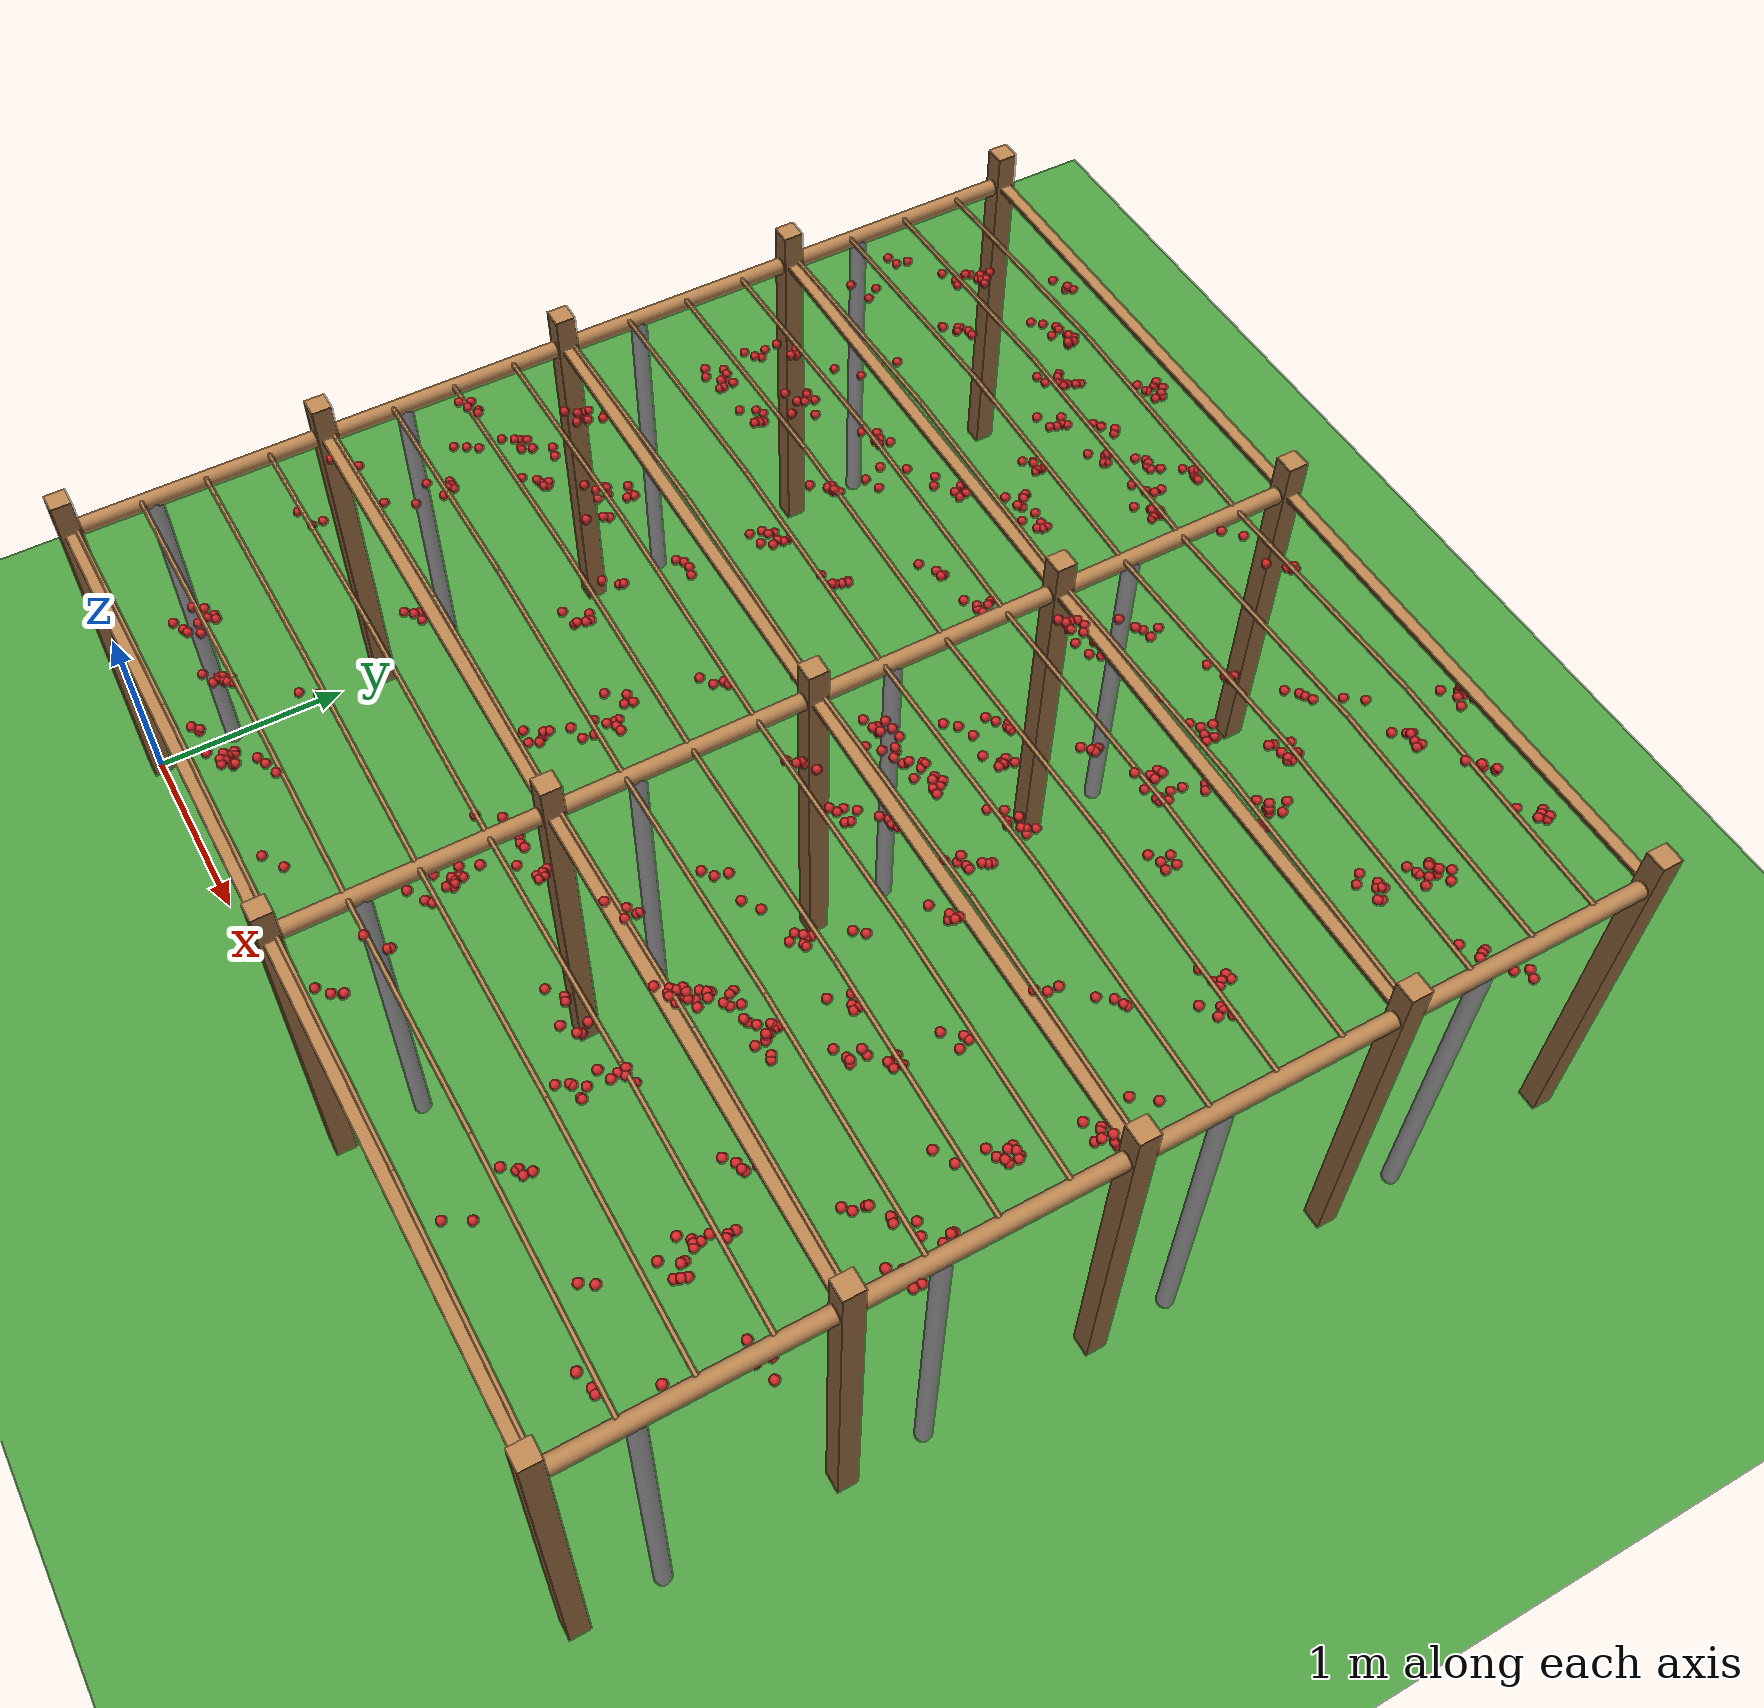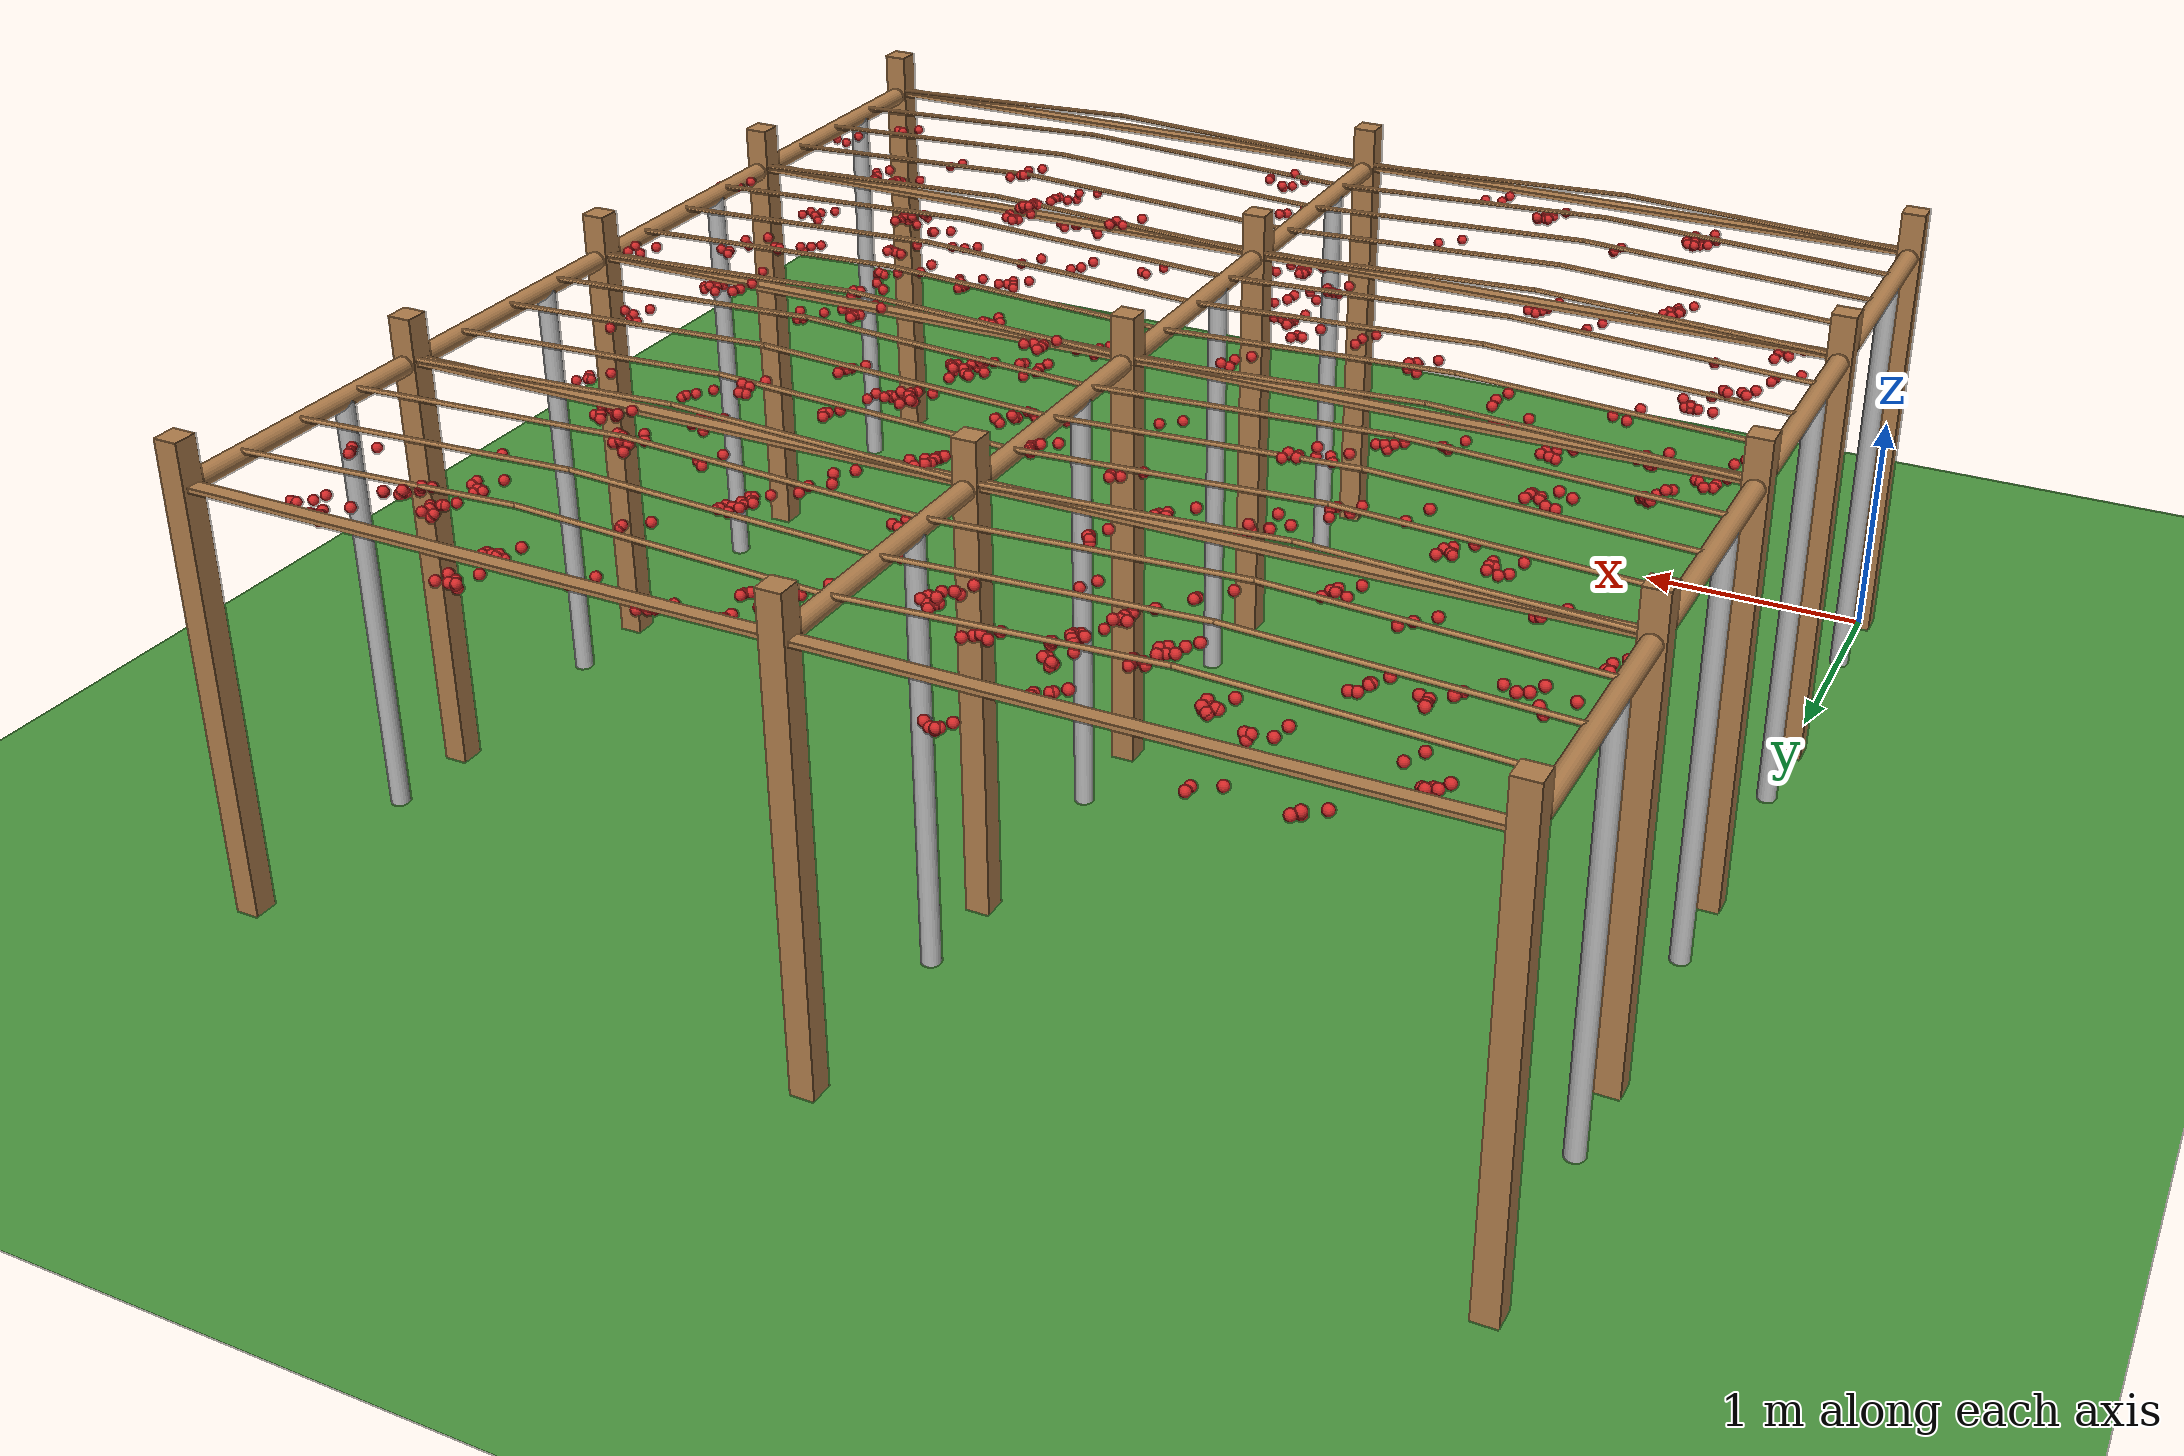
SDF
<?xml version="1.0"?>
<sdf version="1.4">
<world name="fruit_population">
	<include>
		<uri>model://sun</uri>
		<pose>0 50 10 0 0 0</pose>
	</include>

	<include>
		<uri>model://orchard_ground_plane</uri>
	</include>

	<include>
		<uri>model://pergola_unpopulated</uri>
	</include>

	<include>
		<uri>model://fruit_population</uri>
	</include>

</world>
</sdf>

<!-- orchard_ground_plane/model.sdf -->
<sdf version="1.5">
  <model name="orchard_ground_plane">
    <static>true</static>
    <link name="link">
      <collision name="collision">
        <geometry>
          <plane>
            <normal>0 0 1</normal>
            <size>100 100</size>
          </plane>
        </geometry>
        <surface>
          <friction>
            <ode>
              <mu>100</mu>
              <mu2>50</mu2>
            </ode>
          </friction>
        </surface>
      </collision>
      <visual name="visual">
        <cast_shadows>false</cast_shadows>
        <geometry>
          <plane>
            <normal>0 0 1</normal>
            <size>100 100</size>
          </plane>
        </geometry>
        <material>
          <script>
            <uri>model://orchard_ground_plane/materials/scripts</uri>
            <uri>model://orchard_ground_plane/materials/textures</uri>
            <name>OrchardGround/FlatGrass</name>
          </script>
        </material>
      </visual>
    </link>
  </model>
</sdf>

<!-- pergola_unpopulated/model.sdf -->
<sdf version='1.4'>
  <model name="pergola_unpopulated">

		<include>
			<name>post_0</name>
			<pose>0.0 0.0 0 0 0 0</pose>
			<uri>model://post</uri>
		</include>

		<include>
			<name>post_1</name>
			<pose>0.0 1.25 0 0 0 0</pose>
			<uri>model://post</uri>
		</include>

		<include>
			<name>post_2</name>
			<pose>0.0 2.5 0 0 0 0</pose>
			<uri>model://post</uri>
		</include>

		<include>
			<name>post_3</name>
			<pose>0.0 3.75 0 0 0 0</pose>
			<uri>model://post</uri>
		</include>

		<include>
			<name>post_4</name>
			<pose>0.0 5.0 0 0 0 0</pose>
			<uri>model://post</uri>
		</include>

		<include>
			<name>post_5</name>
			<pose>2.5 0.0 0 0 0 0</pose>
			<uri>model://post</uri>
		</include>

		<include>
			<name>post_6</name>
			<pose>2.5 1.25 0 0 0 0</pose>
			<uri>model://post</uri>
		</include>

		<include>
			<name>post_7</name>
			<pose>2.5 2.5 0 0 0 0</pose>
			<uri>model://post</uri>
		</include>

		<include>
			<name>post_8</name>
			<pose>2.5 3.75 0 0 0 0</pose>
			<uri>model://post</uri>
		</include>

		<include>
			<name>post_9</name>
			<pose>2.5 5.0 0 0 0 0</pose>
			<uri>model://post</uri>
		</include>

		<include>
			<name>post_10</name>
			<pose>5.0 0.0 0 0 0 0</pose>
			<uri>model://post</uri>
		</include>

		<include>
			<name>post_11</name>
			<pose>5.0 1.25 0 0 0 0</pose>
			<uri>model://post</uri>
		</include>

		<include>
			<name>post_12</name>
			<pose>5.0 2.5 0 0 0 0</pose>
			<uri>model://post</uri>
		</include>

		<include>
			<name>post_13</name>
			<pose>5.0 3.75 0 0 0 0</pose>
			<uri>model://post</uri>
		</include>

		<include>
			<name>post_14</name>
			<pose>5.0 5.0 0 0 0 0</pose>
			<uri>model://post</uri>
		</include>

    <link name="beam_0">
      <pose>1.25 0.0 1.81 0 0 0</pose>
      <collision name="collision">
        <geometry><box><size>2.5 0.06 0.02</size></box></geometry>
      </collision>
      <visual name="visual">
        <geometry><box><size>2.5 0.06 0.02</size></box></geometry>
        <material><script><name>Gazebo/Wood</name></script></material>
      </visual>
    <inertial>
      <pose>0 0 0 0 0 0</pose>
      <mass>5</mass>
      <inertia>
        <ixx>0.0016666666666666668</ixx><ixy>0.0</ixy><ixz>0.0</ixz><iyy>2.6056666666666666</iyy><iyz>0.0</iyz><izz>2.6043333333333334</izz>
      </inertia>
    </inertial>
    </link>

    <link name="beam_1">
      <pose>1.25 1.25 1.81 0 0 0</pose>
      <collision name="collision">
        <geometry><box><size>2.5 0.06 0.02</size></box></geometry>
      </collision>
      <visual name="visual">
        <geometry><box><size>2.5 0.06 0.02</size></box></geometry>
        <material><script><name>Gazebo/Wood</name></script></material>
      </visual>
    <inertial>
      <pose>0 0 0 0 0 0</pose>
      <mass>5</mass>
      <inertia>
        <ixx>0.0016666666666666668</ixx><ixy>0.0</ixy><ixz>0.0</ixz><iyy>2.6056666666666666</iyy><iyz>0.0</iyz><izz>2.6043333333333334</izz>
      </inertia>
    </inertial>
    </link>

    <link name="beam_2">
      <pose>1.25 2.5 1.81 0 0 0</pose>
      <collision name="collision">
        <geometry><box><size>2.5 0.06 0.02</size></box></geometry>
      </collision>
      <visual name="visual">
        <geometry><box><size>2.5 0.06 0.02</size></box></geometry>
        <material><script><name>Gazebo/Wood</name></script></material>
      </visual>
    <inertial>
      <pose>0 0 0 0 0 0</pose>
      <mass>5</mass>
      <inertia>
        <ixx>0.0016666666666666668</ixx><ixy>0.0</ixy><ixz>0.0</ixz><iyy>2.6056666666666666</iyy><iyz>0.0</iyz><izz>2.6043333333333334</izz>
      </inertia>
    </inertial>
    </link>

    <link name="beam_3">
      <pose>1.25 3.75 1.81 0 0 0</pose>
      <collision name="collision">
        <geometry><box><size>2.5 0.06 0.02</size></box></geometry>
      </collision>
      <visual name="visual">
        <geometry><box><size>2.5 0.06 0.02</size></box></geometry>
        <material><script><name>Gazebo/Wood</name></script></material>
      </visual>
    <inertial>
      <pose>0 0 0 0 0 0</pose>
      <mass>5</mass>
      <inertia>
        <ixx>0.0016666666666666668</ixx><ixy>0.0</ixy><ixz>0.0</ixz><iyy>2.6056666666666666</iyy><iyz>0.0</iyz><izz>2.6043333333333334</izz>
      </inertia>
    </inertial>
    </link>

    <link name="beam_4">
      <pose>1.25 5.0 1.81 0 0 0</pose>
      <collision name="collision">
        <geometry><box><size>2.5 0.06 0.02</size></box></geometry>
      </collision>
      <visual name="visual">
        <geometry><box><size>2.5 0.06 0.02</size></box></geometry>
        <material><script><name>Gazebo/Wood</name></script></material>
      </visual>
    <inertial>
      <pose>0 0 0 0 0 0</pose>
      <mass>5</mass>
      <inertia>
        <ixx>0.0016666666666666668</ixx><ixy>0.0</ixy><ixz>0.0</ixz><iyy>2.6056666666666666</iyy><iyz>0.0</iyz><izz>2.6043333333333334</izz>
      </inertia>
    </inertial>
    </link>

    <link name="beam_5">
      <pose>3.75 0.0 1.81 0 0 0</pose>
      <collision name="collision">
        <geometry><box><size>2.5 0.06 0.02</size></box></geometry>
      </collision>
      <visual name="visual">
        <geometry><box><size>2.5 0.06 0.02</size></box></geometry>
        <material><script><name>Gazebo/Wood</name></script></material>
      </visual>
    <inertial>
      <pose>0 0 0 0 0 0</pose>
      <mass>5</mass>
      <inertia>
        <ixx>0.0016666666666666668</ixx><ixy>0.0</ixy><ixz>0.0</ixz><iyy>2.6056666666666666</iyy><iyz>0.0</iyz><izz>2.6043333333333334</izz>
      </inertia>
    </inertial>
    </link>

    <link name="beam_6">
      <pose>3.75 1.25 1.81 0 0 0</pose>
      <collision name="collision">
        <geometry><box><size>2.5 0.06 0.02</size></box></geometry>
      </collision>
      <visual name="visual">
        <geometry><box><size>2.5 0.06 0.02</size></box></geometry>
        <material><script><name>Gazebo/Wood</name></script></material>
      </visual>
    <inertial>
      <pose>0 0 0 0 0 0</pose>
      <mass>5</mass>
      <inertia>
        <ixx>0.0016666666666666668</ixx><ixy>0.0</ixy><ixz>0.0</ixz><iyy>2.6056666666666666</iyy><iyz>0.0</iyz><izz>2.6043333333333334</izz>
      </inertia>
    </inertial>
    </link>

    <link name="beam_7">
      <pose>3.75 2.5 1.81 0 0 0</pose>
      <collision name="collision">
        <geometry><box><size>2.5 0.06 0.02</size></box></geometry>
      </collision>
      <visual name="visual">
        <geometry><box><size>2.5 0.06 0.02</size></box></geometry>
        <material><script><name>Gazebo/Wood</name></script></material>
      </visual>
    <inertial>
      <pose>0 0 0 0 0 0</pose>
      <mass>5</mass>
      <inertia>
        <ixx>0.0016666666666666668</ixx><ixy>0.0</ixy><ixz>0.0</ixz><iyy>2.6056666666666666</iyy><iyz>0.0</iyz><izz>2.6043333333333334</izz>
      </inertia>
    </inertial>
    </link>

    <link name="beam_8">
      <pose>3.75 3.75 1.81 0 0 0</pose>
      <collision name="collision">
        <geometry><box><size>2.5 0.06 0.02</size></box></geometry>
      </collision>
      <visual name="visual">
        <geometry><box><size>2.5 0.06 0.02</size></box></geometry>
        <material><script><name>Gazebo/Wood</name></script></material>
      </visual>
    <inertial>
      <pose>0 0 0 0 0 0</pose>
      <mass>5</mass>
      <inertia>
        <ixx>0.0016666666666666668</ixx><ixy>0.0</ixy><ixz>0.0</ixz><iyy>2.6056666666666666</iyy><iyz>0.0</iyz><izz>2.6043333333333334</izz>
      </inertia>
    </inertial>
    </link>

    <link name="beam_9">
      <pose>3.75 5.0 1.81 0 0 0</pose>
      <collision name="collision">
        <geometry><box><size>2.5 0.06 0.02</size></box></geometry>
      </collision>
      <visual name="visual">
        <geometry><box><size>2.5 0.06 0.02</size></box></geometry>
        <material><script><name>Gazebo/Wood</name></script></material>
      </visual>
    <inertial>
      <pose>0 0 0 0 0 0</pose>
      <mass>5</mass>
      <inertia>
        <ixx>0.0016666666666666668</ixx><ixy>0.0</ixy><ixz>0.0</ixz><iyy>2.6056666666666666</iyy><iyz>0.0</iyz><izz>2.6043333333333334</izz>
      </inertia>
    </inertial>
    </link>

		<include>
			<name>tree_0</name>
			<pose>0.0 0.4 0 0 0 0</pose>
			<uri>model://tree_trunk</uri>
		</include>

		<include>
			<name>tree_1</name>
			<pose>0.0 1.65 0 0 0 0</pose>
			<uri>model://tree_trunk</uri>
		</include>

		<include>
			<name>tree_2</name>
			<pose>0.0 2.9 0 0 0 0</pose>
			<uri>model://tree_trunk</uri>
		</include>

		<include>
			<name>tree_3</name>
			<pose>0.0 4.15 0 0 0 0</pose>
			<uri>model://tree_trunk</uri>
		</include>

		<include>
			<name>tree_4</name>
			<pose>2.5 0.4 0 0 0 0</pose>
			<uri>model://tree_trunk</uri>
		</include>

		<include>
			<name>tree_5</name>
			<pose>2.5 1.65 0 0 0 0</pose>
			<uri>model://tree_trunk</uri>
		</include>

		<include>
			<name>tree_6</name>
			<pose>2.5 2.9 0 0 0 0</pose>
			<uri>model://tree_trunk</uri>
		</include>

		<include>
			<name>tree_7</name>
			<pose>2.5 4.15 0 0 0 0</pose>
			<uri>model://tree_trunk</uri>
		</include>

		<include>
			<name>tree_8</name>
			<pose>5.0 0.4 0 0 0 0</pose>
			<uri>model://tree_trunk</uri>
		</include>

		<include>
			<name>tree_9</name>
			<pose>5.0 1.65 0 0 0 0</pose>
			<uri>model://tree_trunk</uri>
		</include>

		<include>
			<name>tree_10</name>
			<pose>5.0 2.9 0 0 0 0</pose>
			<uri>model://tree_trunk</uri>
		</include>

		<include>
			<name>tree_11</name>
			<pose>5.0 4.15 0 0 0 0</pose>
			<uri>model://tree_trunk</uri>
		</include>

    <link name="baseBranch_0">
      <pose>0.0 0.625 1.8 1.5707963267948966 0 0</pose>
      <collision name="collision">
        <geometry><cylinder><radius>0.04</radius> <length>1.19</length></cylinder></geometry>
      </collision>
      <visual name="visual">
        <geometry><cylinder><radius>0.04</radius> <length>1.19</length></cylinder></geometry>
        <material><script><name>Gazebo/WoodFloor</name></script></material>
      </visual>
    <inertial>
      <pose>0 0 0 0 0 0</pose>
      <mass>10</mass>
      <inertia>
        <ixx>1.1840833333333332</ixx><ixy>0.0</ixy><ixz>0.0</ixz><iyy>1.1840833333333332</iyy><iyz>0.0</iyz><izz>0.008</izz>
      </inertia>
    </inertial>
    </link>

    <link name="baseBranch_1">
      <pose>0.0 1.875 1.8 1.5707963267948966 0 0</pose>
      <collision name="collision">
        <geometry><cylinder><radius>0.04</radius> <length>1.19</length></cylinder></geometry>
      </collision>
      <visual name="visual">
        <geometry><cylinder><radius>0.04</radius> <length>1.19</length></cylinder></geometry>
        <material><script><name>Gazebo/WoodFloor</name></script></material>
      </visual>
    <inertial>
      <pose>0 0 0 0 0 0</pose>
      <mass>10</mass>
      <inertia>
        <ixx>1.1840833333333332</ixx><ixy>0.0</ixy><ixz>0.0</ixz><iyy>1.1840833333333332</iyy><iyz>0.0</iyz><izz>0.008</izz>
      </inertia>
    </inertial>
    </link>

    <link name="baseBranch_2">
      <pose>0.0 3.125 1.8 1.5707963267948966 0 0</pose>
      <collision name="collision">
        <geometry><cylinder><radius>0.04</radius> <length>1.19</length></cylinder></geometry>
      </collision>
      <visual name="visual">
        <geometry><cylinder><radius>0.04</radius> <length>1.19</length></cylinder></geometry>
        <material><script><name>Gazebo/WoodFloor</name></script></material>
      </visual>
    <inertial>
      <pose>0 0 0 0 0 0</pose>
      <mass>10</mass>
      <inertia>
        <ixx>1.1840833333333332</ixx><ixy>0.0</ixy><ixz>0.0</ixz><iyy>1.1840833333333332</iyy><iyz>0.0</iyz><izz>0.008</izz>
      </inertia>
    </inertial>
    </link>

    <link name="baseBranch_3">
      <pose>0.0 4.375 1.8 1.5707963267948966 0 0</pose>
      <collision name="collision">
        <geometry><cylinder><radius>0.04</radius> <length>1.19</length></cylinder></geometry>
      </collision>
      <visual name="visual">
        <geometry><cylinder><radius>0.04</radius> <length>1.19</length></cylinder></geometry>
        <material><script><name>Gazebo/WoodFloor</name></script></material>
      </visual>
    <inertial>
      <pose>0 0 0 0 0 0</pose>
      <mass>10</mass>
      <inertia>
        <ixx>1.1840833333333332</ixx><ixy>0.0</ixy><ixz>0.0</ixz><iyy>1.1840833333333332</iyy><iyz>0.0</iyz><izz>0.008</izz>
      </inertia>
    </inertial>
    </link>

    <link name="baseBranch_4">
      <pose>2.5 0.625 1.8 1.5707963267948966 0 0</pose>
      <collision name="collision">
        <geometry><cylinder><radius>0.04</radius> <length>1.19</length></cylinder></geometry>
      </collision>
      <visual name="visual">
        <geometry><cylinder><radius>0.04</radius> <length>1.19</length></cylinder></geometry>
        <material><script><name>Gazebo/WoodFloor</name></script></material>
      </visual>
    <inertial>
      <pose>0 0 0 0 0 0</pose>
      <mass>10</mass>
      <inertia>
        <ixx>1.1840833333333332</ixx><ixy>0.0</ixy><ixz>0.0</ixz><iyy>1.1840833333333332</iyy><iyz>0.0</iyz><izz>0.008</izz>
      </inertia>
    </inertial>
    </link>

    <link name="baseBranch_5">
      <pose>2.5 1.875 1.8 1.5707963267948966 0 0</pose>
      <collision name="collision">
        <geometry><cylinder><radius>0.04</radius> <length>1.19</length></cylinder></geometry>
      </collision>
      <visual name="visual">
        <geometry><cylinder><radius>0.04</radius> <length>1.19</length></cylinder></geometry>
        <material><script><name>Gazebo/WoodFloor</name></script></material>
      </visual>
    <inertial>
      <pose>0 0 0 0 0 0</pose>
      <mass>10</mass>
      <inertia>
        <ixx>1.1840833333333332</ixx><ixy>0.0</ixy><ixz>0.0</ixz><iyy>1.1840833333333332</iyy><iyz>0.0</iyz><izz>0.008</izz>
      </inertia>
    </inertial>
    </link>

    <link name="baseBranch_6">
      <pose>2.5 3.125 1.8 1.5707963267948966 0 0</pose>
      <collision name="collision">
        <geometry><cylinder><radius>0.04</radius> <length>1.19</length></cylinder></geometry>
      </collision>
      <visual name="visual">
        <geometry><cylinder><radius>0.04</radius> <length>1.19</length></cylinder></geometry>
        <material><script><name>Gazebo/WoodFloor</name></script></material>
      </visual>
    <inertial>
      <pose>0 0 0 0 0 0</pose>
      <mass>10</mass>
      <inertia>
        <ixx>1.1840833333333332</ixx><ixy>0.0</ixy><ixz>0.0</ixz><iyy>1.1840833333333332</iyy><iyz>0.0</iyz><izz>0.008</izz>
      </inertia>
    </inertial>
    </link>

    <link name="baseBranch_7">
      <pose>2.5 4.375 1.8 1.5707963267948966 0 0</pose>
      <collision name="collision">
        <geometry><cylinder><radius>0.04</radius> <length>1.19</length></cylinder></geometry>
      </collision>
      <visual name="visual">
        <geometry><cylinder><radius>0.04</radius> <length>1.19</length></cylinder></geometry>
        <material><script><name>Gazebo/WoodFloor</name></script></material>
      </visual>
    <inertial>
      <pose>0 0 0 0 0 0</pose>
      <mass>10</mass>
      <inertia>
        <ixx>1.1840833333333332</ixx><ixy>0.0</ixy><ixz>0.0</ixz><iyy>1.1840833333333332</iyy><iyz>0.0</iyz><izz>0.008</izz>
      </inertia>
    </inertial>
    </link>

    <link name="baseBranch_8">
      <pose>5.0 0.625 1.8 1.5707963267948966 0 0</pose>
      <collision name="collision">
        <geometry><cylinder><radius>0.04</radius> <length>1.19</length></cylinder></geometry>
      </collision>
      <visual name="visual">
        <geometry><cylinder><radius>0.04</radius> <length>1.19</length></cylinder></geometry>
        <material><script><name>Gazebo/WoodFloor</name></script></material>
      </visual>
    <inertial>
      <pose>0 0 0 0 0 0</pose>
      <mass>10</mass>
      <inertia>
        <ixx>1.1840833333333332</ixx><ixy>0.0</ixy><ixz>0.0</ixz><iyy>1.1840833333333332</iyy><iyz>0.0</iyz><izz>0.008</izz>
      </inertia>
    </inertial>
    </link>

    <link name="baseBranch_9">
      <pose>5.0 1.875 1.8 1.5707963267948966 0 0</pose>
      <collision name="collision">
        <geometry><cylinder><radius>0.04</radius> <length>1.19</length></cylinder></geometry>
      </collision>
      <visual name="visual">
        <geometry><cylinder><radius>0.04</radius> <length>1.19</length></cylinder></geometry>
        <material><script><name>Gazebo/WoodFloor</name></script></material>
      </visual>
    <inertial>
      <pose>0 0 0 0 0 0</pose>
      <mass>10</mass>
      <inertia>
        <ixx>1.1840833333333332</ixx><ixy>0.0</ixy><ixz>0.0</ixz><iyy>1.1840833333333332</iyy><iyz>0.0</iyz><izz>0.008</izz>
      </inertia>
    </inertial>
    </link>

    <link name="baseBranch_10">
      <pose>5.0 3.125 1.8 1.5707963267948966 0 0</pose>
      <collision name="collision">
        <geometry><cylinder><radius>0.04</radius> <length>1.19</length></cylinder></geometry>
      </collision>
      <visual name="visual">
        <geometry><cylinder><radius>0.04</radius> <length>1.19</length></cylinder></geometry>
        <material><script><name>Gazebo/WoodFloor</name></script></material>
      </visual>
    <inertial>
      <pose>0 0 0 0 0 0</pose>
      <mass>10</mass>
      <inertia>
        <ixx>1.1840833333333332</ixx><ixy>0.0</ixy><ixz>0.0</ixz><iyy>1.1840833333333332</iyy><iyz>0.0</iyz><izz>0.008</izz>
      </inertia>
    </inertial>
    </link>

    <link name="baseBranch_11">
      <pose>5.0 4.375 1.8 1.5707963267948966 0 0</pose>
      <collision name="collision">
        <geometry><cylinder><radius>0.04</radius> <length>1.19</length></cylinder></geometry>
      </collision>
      <visual name="visual">
        <geometry><cylinder><radius>0.04</radius> <length>1.19</length></cylinder></geometry>
        <material><script><name>Gazebo/WoodFloor</name></script></material>
      </visual>
    <inertial>
      <pose>0 0 0 0 0 0</pose>
      <mass>10</mass>
      <inertia>
        <ixx>1.1840833333333332</ixx><ixy>0.0</ixy><ixz>0.0</ixz><iyy>1.1840833333333332</iyy><iyz>0.0</iyz><izz>0.008</izz>
      </inertia>
    </inertial>
    </link>

    <link name="vine_0">
      <pose>0.625 0.03 1.85 0 1.5308176396716067 0</pose>
      <collision name="collision">
        <geometry><cylinder><radius>0.01</radius> <length>1.2509996003196804</length></cylinder></geometry>
      </collision>
      <visual name="visual">
        <geometry><cylinder><radius>0.01</radius> <length>1.2509996003196804</length></cylinder></geometry>
        <material><script><name>Gazebo/WoodFloor</name></script></material>
      </visual>
    <inertial>
      <pose>0 0 0 0 0 0</pose>
      <mass>5</mass>
      <inertia>
        <ixx>0.6522083333333334</ixx><ixy>0.0</ixy><ixz>0.0</ixz><iyy>0.6522083333333334</iyy><iyz>0.0</iyz><izz>0.00025</izz>
      </inertia>
    </inertial>
    </link>

    <link name="vine_1">
      <pose>1.875 0.03 1.85 0 -1.5308176396716067 0</pose>
      <collision name="collision">
        <geometry><cylinder><radius>0.01</radius> <length>1.2509996003196804</length></cylinder></geometry>
      </collision>
      <visual name="visual">
        <geometry><cylinder><radius>0.01</radius> <length>1.2509996003196804</length></cylinder></geometry>
        <material><script><name>Gazebo/WoodFloor</name></script></material>
      </visual>
    <inertial>
      <pose>0 0 0 0 0 0</pose>
      <mass>5</mass>
      <inertia>
        <ixx>0.6522083333333334</ixx><ixy>0.0</ixy><ixz>0.0</ixz><iyy>0.6522083333333334</iyy><iyz>0.0</iyz><izz>0.00025</izz>
      </inertia>
    </inertial>
    </link>

    <link name="vine_2">
      <pose>0.625 0.3425 1.85 0 1.5308176396716067 0</pose>
      <collision name="collision">
        <geometry><cylinder><radius>0.01</radius> <length>1.2509996003196804</length></cylinder></geometry>
      </collision>
      <visual name="visual">
        <geometry><cylinder><radius>0.01</radius> <length>1.2509996003196804</length></cylinder></geometry>
        <material><script><name>Gazebo/WoodFloor</name></script></material>
      </visual>
    <inertial>
      <pose>0 0 0 0 0 0</pose>
      <mass>5</mass>
      <inertia>
        <ixx>0.6522083333333334</ixx><ixy>0.0</ixy><ixz>0.0</ixz><iyy>0.6522083333333334</iyy><iyz>0.0</iyz><izz>0.00025</izz>
      </inertia>
    </inertial>
    </link>

    <link name="vine_3">
      <pose>1.875 0.3425 1.85 0 -1.5308176396716067 0</pose>
      <collision name="collision">
        <geometry><cylinder><radius>0.01</radius> <length>1.2509996003196804</length></cylinder></geometry>
      </collision>
      <visual name="visual">
        <geometry><cylinder><radius>0.01</radius> <length>1.2509996003196804</length></cylinder></geometry>
        <material><script><name>Gazebo/WoodFloor</name></script></material>
      </visual>
    <inertial>
      <pose>0 0 0 0 0 0</pose>
      <mass>5</mass>
      <inertia>
        <ixx>0.6522083333333334</ixx><ixy>0.0</ixy><ixz>0.0</ixz><iyy>0.6522083333333334</iyy><iyz>0.0</iyz><izz>0.00025</izz>
      </inertia>
    </inertial>
    </link>

    <link name="vine_4">
      <pose>0.625 0.655 1.85 0 1.5308176396716067 0</pose>
      <collision name="collision">
        <geometry><cylinder><radius>0.01</radius> <length>1.2509996003196804</length></cylinder></geometry>
      </collision>
      <visual name="visual">
        <geometry><cylinder><radius>0.01</radius> <length>1.2509996003196804</length></cylinder></geometry>
        <material><script><name>Gazebo/WoodFloor</name></script></material>
      </visual>
    <inertial>
      <pose>0 0 0 0 0 0</pose>
      <mass>5</mass>
      <inertia>
        <ixx>0.6522083333333334</ixx><ixy>0.0</ixy><ixz>0.0</ixz><iyy>0.6522083333333334</iyy><iyz>0.0</iyz><izz>0.00025</izz>
      </inertia>
    </inertial>
    </link>

    <link name="vine_5">
      <pose>1.875 0.655 1.85 0 -1.5308176396716067 0</pose>
      <collision name="collision">
        <geometry><cylinder><radius>0.01</radius> <length>1.2509996003196804</length></cylinder></geometry>
      </collision>
      <visual name="visual">
        <geometry><cylinder><radius>0.01</radius> <length>1.2509996003196804</length></cylinder></geometry>
        <material><script><name>Gazebo/WoodFloor</name></script></material>
      </visual>
    <inertial>
      <pose>0 0 0 0 0 0</pose>
      <mass>5</mass>
      <inertia>
        <ixx>0.6522083333333334</ixx><ixy>0.0</ixy><ixz>0.0</ixz><iyy>0.6522083333333334</iyy><iyz>0.0</iyz><izz>0.00025</izz>
      </inertia>
    </inertial>
    </link>

    <link name="vine_6">
      <pose>0.625 0.9675 1.85 0 1.5308176396716067 0</pose>
      <collision name="collision">
        <geometry><cylinder><radius>0.01</radius> <length>1.2509996003196804</length></cylinder></geometry>
      </collision>
      <visual name="visual">
        <geometry><cylinder><radius>0.01</radius> <length>1.2509996003196804</length></cylinder></geometry>
        <material><script><name>Gazebo/WoodFloor</name></script></material>
      </visual>
    <inertial>
      <pose>0 0 0 0 0 0</pose>
      <mass>5</mass>
      <inertia>
        <ixx>0.6522083333333334</ixx><ixy>0.0</ixy><ixz>0.0</ixz><iyy>0.6522083333333334</iyy><iyz>0.0</iyz><izz>0.00025</izz>
      </inertia>
    </inertial>
    </link>

    <link name="vine_7">
      <pose>1.875 0.9675 1.85 0 -1.5308176396716067 0</pose>
      <collision name="collision">
        <geometry><cylinder><radius>0.01</radius> <length>1.2509996003196804</length></cylinder></geometry>
      </collision>
      <visual name="visual">
        <geometry><cylinder><radius>0.01</radius> <length>1.2509996003196804</length></cylinder></geometry>
        <material><script><name>Gazebo/WoodFloor</name></script></material>
      </visual>
    <inertial>
      <pose>0 0 0 0 0 0</pose>
      <mass>5</mass>
      <inertia>
        <ixx>0.6522083333333334</ixx><ixy>0.0</ixy><ixz>0.0</ixz><iyy>0.6522083333333334</iyy><iyz>0.0</iyz><izz>0.00025</izz>
      </inertia>
    </inertial>
    </link>

    <link name="vine_8">
      <pose>0.625 1.28 1.85 0 1.5308176396716067 0</pose>
      <collision name="collision">
        <geometry><cylinder><radius>0.01</radius> <length>1.2509996003196804</length></cylinder></geometry>
      </collision>
      <visual name="visual">
        <geometry><cylinder><radius>0.01</radius> <length>1.2509996003196804</length></cylinder></geometry>
        <material><script><name>Gazebo/WoodFloor</name></script></material>
      </visual>
    <inertial>
      <pose>0 0 0 0 0 0</pose>
      <mass>5</mass>
      <inertia>
        <ixx>0.6522083333333334</ixx><ixy>0.0</ixy><ixz>0.0</ixz><iyy>0.6522083333333334</iyy><iyz>0.0</iyz><izz>0.00025</izz>
      </inertia>
    </inertial>
    </link>

    <link name="vine_9">
      <pose>1.875 1.28 1.85 0 -1.5308176396716067 0</pose>
      <collision name="collision">
        <geometry><cylinder><radius>0.01</radius> <length>1.2509996003196804</length></cylinder></geometry>
      </collision>
      <visual name="visual">
        <geometry><cylinder><radius>0.01</radius> <length>1.2509996003196804</length></cylinder></geometry>
        <material><script><name>Gazebo/WoodFloor</name></script></material>
      </visual>
    <inertial>
      <pose>0 0 0 0 0 0</pose>
      <mass>5</mass>
      <inertia>
        <ixx>0.6522083333333334</ixx><ixy>0.0</ixy><ixz>0.0</ixz><iyy>0.6522083333333334</iyy><iyz>0.0</iyz><izz>0.00025</izz>
      </inertia>
    </inertial>
    </link>

    <link name="vine_10">
      <pose>0.625 1.5925 1.85 0 1.5308176396716067 0</pose>
      <collision name="collision">
        <geometry><cylinder><radius>0.01</radius> <length>1.2509996003196804</length></cylinder></geometry>
      </collision>
      <visual name="visual">
        <geometry><cylinder><radius>0.01</radius> <length>1.2509996003196804</length></cylinder></geometry>
        <material><script><name>Gazebo/WoodFloor</name></script></material>
      </visual>
    <inertial>
      <pose>0 0 0 0 0 0</pose>
      <mass>5</mass>
      <inertia>
        <ixx>0.6522083333333334</ixx><ixy>0.0</ixy><ixz>0.0</ixz><iyy>0.6522083333333334</iyy><iyz>0.0</iyz><izz>0.00025</izz>
      </inertia>
    </inertial>
    </link>

    <link name="vine_11">
      <pose>1.875 1.5925 1.85 0 -1.5308176396716067 0</pose>
      <collision name="collision">
        <geometry><cylinder><radius>0.01</radius> <length>1.2509996003196804</length></cylinder></geometry>
      </collision>
      <visual name="visual">
        <geometry><cylinder><radius>0.01</radius> <length>1.2509996003196804</length></cylinder></geometry>
        <material><script><name>Gazebo/WoodFloor</name></script></material>
      </visual>
    <inertial>
      <pose>0 0 0 0 0 0</pose>
      <mass>5</mass>
      <inertia>
        <ixx>0.6522083333333334</ixx><ixy>0.0</ixy><ixz>0.0</ixz><iyy>0.6522083333333334</iyy><iyz>0.0</iyz><izz>0.00025</izz>
      </inertia>
    </inertial>
    </link>

    <link name="vine_12">
      <pose>0.625 1.905 1.85 0 1.5308176396716067 0</pose>
      <collision name="collision">
        <geometry><cylinder><radius>0.01</radius> <length>1.2509996003196804</length></cylinder></geometry>
      </collision>
      <visual name="visual">
        <geometry><cylinder><radius>0.01</radius> <length>1.2509996003196804</length></cylinder></geometry>
        <material><script><name>Gazebo/WoodFloor</name></script></material>
      </visual>
    <inertial>
      <pose>0 0 0 0 0 0</pose>
      <mass>5</mass>
      <inertia>
        <ixx>0.6522083333333334</ixx><ixy>0.0</ixy><ixz>0.0</ixz><iyy>0.6522083333333334</iyy><iyz>0.0</iyz><izz>0.00025</izz>
      </inertia>
    </inertial>
    </link>

    <link name="vine_13">
      <pose>1.875 1.905 1.85 0 -1.5308176396716067 0</pose>
      <collision name="collision">
        <geometry><cylinder><radius>0.01</radius> <length>1.2509996003196804</length></cylinder></geometry>
      </collision>
      <visual name="visual">
        <geometry><cylinder><radius>0.01</radius> <length>1.2509996003196804</length></cylinder></geometry>
        <material><script><name>Gazebo/WoodFloor</name></script></material>
      </visual>
    <inertial>
      <pose>0 0 0 0 0 0</pose>
      <mass>5</mass>
      <inertia>
        <ixx>0.6522083333333334</ixx><ixy>0.0</ixy><ixz>0.0</ixz><iyy>0.6522083333333334</iyy><iyz>0.0</iyz><izz>0.00025</izz>
      </inertia>
    </inertial>
    </link>

    <link name="vine_14">
      <pose>0.625 2.2175 1.85 0 1.5308176396716067 0</pose>
      <collision name="collision">
        <geometry><cylinder><radius>0.01</radius> <length>1.2509996003196804</length></cylinder></geometry>
      </collision>
      <visual name="visual">
        <geometry><cylinder><radius>0.01</radius> <length>1.2509996003196804</length></cylinder></geometry>
        <material><script><name>Gazebo/WoodFloor</name></script></material>
      </visual>
    <inertial>
      <pose>0 0 0 0 0 0</pose>
      <mass>5</mass>
      <inertia>
        <ixx>0.6522083333333334</ixx><ixy>0.0</ixy><ixz>0.0</ixz><iyy>0.6522083333333334</iyy><iyz>0.0</iyz><izz>0.00025</izz>
      </inertia>
    </inertial>
    </link>

    <link name="vine_15">
      <pose>1.875 2.2175 1.85 0 -1.5308176396716067 0</pose>
      <collision name="collision">
        <geometry><cylinder><radius>0.01</radius> <length>1.2509996003196804</length></cylinder></geometry>
      </collision>
      <visual name="visual">
        <geometry><cylinder><radius>0.01</radius> <length>1.2509996003196804</length></cylinder></geometry>
        <material><script><name>Gazebo/WoodFloor</name></script></material>
      </visual>
    <inertial>
      <pose>0 0 0 0 0 0</pose>
      <mass>5</mass>
      <inertia>
        <ixx>0.6522083333333334</ixx><ixy>0.0</ixy><ixz>0.0</ixz><iyy>0.6522083333333334</iyy><iyz>0.0</iyz><izz>0.00025</izz>
      </inertia>
    </inertial>
    </link>

    <link name="vine_16">
      <pose>0.625 2.53 1.85 0 1.5308176396716067 0</pose>
      <collision name="collision">
        <geometry><cylinder><radius>0.01</radius> <length>1.2509996003196804</length></cylinder></geometry>
      </collision>
      <visual name="visual">
        <geometry><cylinder><radius>0.01</radius> <length>1.2509996003196804</length></cylinder></geometry>
        <material><script><name>Gazebo/WoodFloor</name></script></material>
      </visual>
    <inertial>
      <pose>0 0 0 0 0 0</pose>
      <mass>5</mass>
      <inertia>
        <ixx>0.6522083333333334</ixx><ixy>0.0</ixy><ixz>0.0</ixz><iyy>0.6522083333333334</iyy><iyz>0.0</iyz><izz>0.00025</izz>
      </inertia>
    </inertial>
    </link>

    <link name="vine_17">
      <pose>1.875 2.53 1.85 0 -1.5308176396716067 0</pose>
      <collision name="collision">
        <geometry><cylinder><radius>0.01</radius> <length>1.2509996003196804</length></cylinder></geometry>
      </collision>
      <visual name="visual">
        <geometry><cylinder><radius>0.01</radius> <length>1.2509996003196804</length></cylinder></geometry>
        <material><script><name>Gazebo/WoodFloor</name></script></material>
      </visual>
    <inertial>
      <pose>0 0 0 0 0 0</pose>
      <mass>5</mass>
      <inertia>
        <ixx>0.6522083333333334</ixx><ixy>0.0</ixy><ixz>0.0</ixz><iyy>0.6522083333333334</iyy><iyz>0.0</iyz><izz>0.00025</izz>
      </inertia>
    </inertial>
    </link>

    <link name="vine_18">
      <pose>0.625 2.8425 1.85 0 1.5308176396716067 0</pose>
      <collision name="collision">
        <geometry><cylinder><radius>0.01</radius> <length>1.2509996003196804</length></cylinder></geometry>
      </collision>
      <visual name="visual">
        <geometry><cylinder><radius>0.01</radius> <length>1.2509996003196804</length></cylinder></geometry>
        <material><script><name>Gazebo/WoodFloor</name></script></material>
      </visual>
    <inertial>
      <pose>0 0 0 0 0 0</pose>
      <mass>5</mass>
      <inertia>
        <ixx>0.6522083333333334</ixx><ixy>0.0</ixy><ixz>0.0</ixz><iyy>0.6522083333333334</iyy><iyz>0.0</iyz><izz>0.00025</izz>
      </inertia>
    </inertial>
    </link>

    <link name="vine_19">
      <pose>1.875 2.8425 1.85 0 -1.5308176396716067 0</pose>
      <collision name="collision">
        <geometry><cylinder><radius>0.01</radius> <length>1.2509996003196804</length></cylinder></geometry>
      </collision>
      <visual name="visual">
        <geometry><cylinder><radius>0.01</radius> <length>1.2509996003196804</length></cylinder></geometry>
        <material><script><name>Gazebo/WoodFloor</name></script></material>
      </visual>
    <inertial>
      <pose>0 0 0 0 0 0</pose>
      <mass>5</mass>
      <inertia>
        <ixx>0.6522083333333334</ixx><ixy>0.0</ixy><ixz>0.0</ixz><iyy>0.6522083333333334</iyy><iyz>0.0</iyz><izz>0.00025</izz>
      </inertia>
    </inertial>
    </link>

    <link name="vine_20">
      <pose>0.625 3.155 1.85 0 1.5308176396716067 0</pose>
      <collision name="collision">
        <geometry><cylinder><radius>0.01</radius> <length>1.2509996003196804</length></cylinder></geometry>
      </collision>
      <visual name="visual">
        <geometry><cylinder><radius>0.01</radius> <length>1.2509996003196804</length></cylinder></geometry>
        <material><script><name>Gazebo/WoodFloor</name></script></material>
      </visual>
    <inertial>
      <pose>0 0 0 0 0 0</pose>
      <mass>5</mass>
      <inertia>
        <ixx>0.6522083333333334</ixx><ixy>0.0</ixy><ixz>0.0</ixz><iyy>0.6522083333333334</iyy><iyz>0.0</iyz><izz>0.00025</izz>
      </inertia>
    </inertial>
    </link>

    <link name="vine_21">
      <pose>1.875 3.155 1.85 0 -1.5308176396716067 0</pose>
      <collision name="collision">
        <geometry><cylinder><radius>0.01</radius> <length>1.2509996003196804</length></cylinder></geometry>
      </collision>
      <visual name="visual">
        <geometry><cylinder><radius>0.01</radius> <length>1.2509996003196804</length></cylinder></geometry>
        <material><script><name>Gazebo/WoodFloor</name></script></material>
      </visual>
    <inertial>
      <pose>0 0 0 0 0 0</pose>
      <mass>5</mass>
      <inertia>
        <ixx>0.6522083333333334</ixx><ixy>0.0</ixy><ixz>0.0</ixz><iyy>0.6522083333333334</iyy><iyz>0.0</iyz><izz>0.00025</izz>
      </inertia>
    </inertial>
    </link>

    <link name="vine_22">
      <pose>0.625 3.4675 1.85 0 1.5308176396716067 0</pose>
      <collision name="collision">
        <geometry><cylinder><radius>0.01</radius> <length>1.2509996003196804</length></cylinder></geometry>
      </collision>
      <visual name="visual">
        <geometry><cylinder><radius>0.01</radius> <length>1.2509996003196804</length></cylinder></geometry>
        <material><script><name>Gazebo/WoodFloor</name></script></material>
      </visual>
    <inertial>
      <pose>0 0 0 0 0 0</pose>
      <mass>5</mass>
      <inertia>
        <ixx>0.6522083333333334</ixx><ixy>0.0</ixy><ixz>0.0</ixz><iyy>0.6522083333333334</iyy><iyz>0.0</iyz><izz>0.00025</izz>
      </inertia>
    </inertial>
    </link>

    <link name="vine_23">
      <pose>1.875 3.4675 1.85 0 -1.5308176396716067 0</pose>
      <collision name="collision">
        <geometry><cylinder><radius>0.01</radius> <length>1.2509996003196804</length></cylinder></geometry>
      </collision>
      <visual name="visual">
        <geometry><cylinder><radius>0.01</radius> <length>1.2509996003196804</length></cylinder></geometry>
        <material><script><name>Gazebo/WoodFloor</name></script></material>
      </visual>
    <inertial>
      <pose>0 0 0 0 0 0</pose>
      <mass>5</mass>
      <inertia>
        <ixx>0.6522083333333334</ixx><ixy>0.0</ixy><ixz>0.0</ixz><iyy>0.6522083333333334</iyy><iyz>0.0</iyz><izz>0.00025</izz>
      </inertia>
    </inertial>
    </link>

    <link name="vine_24">
      <pose>0.625 3.78 1.85 0 1.5308176396716067 0</pose>
      <collision name="collision">
        <geometry><cylinder><radius>0.01</radius> <length>1.2509996003196804</length></cylinder></geometry>
      </collision>
      <visual name="visual">
        <geometry><cylinder><radius>0.01</radius> <length>1.2509996003196804</length></cylinder></geometry>
        <material><script><name>Gazebo/WoodFloor</name></script></material>
      </visual>
    <inertial>
      <pose>0 0 0 0 0 0</pose>
      <mass>5</mass>
      <inertia>
        <ixx>0.6522083333333334</ixx><ixy>0.0</ixy><ixz>0.0</ixz><iyy>0.6522083333333334</iyy><iyz>0.0</iyz><izz>0.00025</izz>
      </inertia>
    </inertial>
    </link>

    <link name="vine_25">
      <pose>1.875 3.78 1.85 0 -1.5308176396716067 0</pose>
      <collision name="collision">
        <geometry><cylinder><radius>0.01</radius> <length>1.2509996003196804</length></cylinder></geometry>
      </collision>
      <visual name="visual">
        <geometry><cylinder><radius>0.01</radius> <length>1.2509996003196804</length></cylinder></geometry>
        <material><script><name>Gazebo/WoodFloor</name></script></material>
      </visual>
    <inertial>
      <pose>0 0 0 0 0 0</pose>
      <mass>5</mass>
      <inertia>
        <ixx>0.6522083333333334</ixx><ixy>0.0</ixy><ixz>0.0</ixz><iyy>0.6522083333333334</iyy><iyz>0.0</iyz><izz>0.00025</izz>
      </inertia>
    </inertial>
    </link>

    <link name="vine_26">
      <pose>0.625 4.0925 1.85 0 1.5308176396716067 0</pose>
      <collision name="collision">
        <geometry><cylinder><radius>0.01</radius> <length>1.2509996003196804</length></cylinder></geometry>
      </collision>
      <visual name="visual">
        <geometry><cylinder><radius>0.01</radius> <length>1.2509996003196804</length></cylinder></geometry>
        <material><script><name>Gazebo/WoodFloor</name></script></material>
      </visual>
    <inertial>
      <pose>0 0 0 0 0 0</pose>
      <mass>5</mass>
      <inertia>
        <ixx>0.6522083333333334</ixx><ixy>0.0</ixy><ixz>0.0</ixz><iyy>0.6522083333333334</iyy><iyz>0.0</iyz><izz>0.00025</izz>
      </inertia>
    </inertial>
    </link>

    <link name="vine_27">
      <pose>1.875 4.0925 1.85 0 -1.5308176396716067 0</pose>
      <collision name="collision">
        <geometry><cylinder><radius>0.01</radius> <length>1.2509996003196804</length></cylinder></geometry>
      </collision>
      <visual name="visual">
        <geometry><cylinder><radius>0.01</radius> <length>1.2509996003196804</length></cylinder></geometry>
        <material><script><name>Gazebo/WoodFloor</name></script></material>
      </visual>
    <inertial>
      <pose>0 0 0 0 0 0</pose>
      <mass>5</mass>
      <inertia>
        <ixx>0.6522083333333334</ixx><ixy>0.0</ixy><ixz>0.0</ixz><iyy>0.6522083333333334</iyy><iyz>0.0</iyz><izz>0.00025</izz>
      </inertia>
    </inertial>
    </link>

    <link name="vine_28">
      <pose>0.625 4.405 1.85 0 1.5308176396716067 0</pose>
      <collision name="collision">
        <geometry><cylinder><radius>0.01</radius> <length>1.2509996003196804</length></cylinder></geometry>
      </collision>
      <visual name="visual">
        <geometry><cylinder><radius>0.01</radius> <length>1.2509996003196804</length></cylinder></geometry>
        <material><script><name>Gazebo/WoodFloor</name></script></material>
      </visual>
    <inertial>
      <pose>0 0 0 0 0 0</pose>
      <mass>5</mass>
      <inertia>
        <ixx>0.6522083333333334</ixx><ixy>0.0</ixy><ixz>0.0</ixz><iyy>0.6522083333333334</iyy><iyz>0.0</iyz><izz>0.00025</izz>
      </inertia>
    </inertial>
    </link>

    <link name="vine_29">
      <pose>1.875 4.405 1.85 0 -1.5308176396716067 0</pose>
      <collision name="collision">
        <geometry><cylinder><radius>0.01</radius> <length>1.2509996003196804</length></cylinder></geometry>
      </collision>
      <visual name="visual">
        <geometry><cylinder><radius>0.01</radius> <length>1.2509996003196804</length></cylinder></geometry>
        <material><script><name>Gazebo/WoodFloor</name></script></material>
      </visual>
    <inertial>
      <pose>0 0 0 0 0 0</pose>
      <mass>5</mass>
      <inertia>
        <ixx>0.6522083333333334</ixx><ixy>0.0</ixy><ixz>0.0</ixz><iyy>0.6522083333333334</iyy><iyz>0.0</iyz><izz>0.00025</izz>
      </inertia>
    </inertial>
    </link>

    <link name="vine_30">
      <pose>0.625 4.7175 1.85 0 1.5308176396716067 0</pose>
      <collision name="collision">
        <geometry><cylinder><radius>0.01</radius> <length>1.2509996003196804</length></cylinder></geometry>
      </collision>
      <visual name="visual">
        <geometry><cylinder><radius>0.01</radius> <length>1.2509996003196804</length></cylinder></geometry>
        <material><script><name>Gazebo/WoodFloor</name></script></material>
      </visual>
    <inertial>
      <pose>0 0 0 0 0 0</pose>
      <mass>5</mass>
      <inertia>
        <ixx>0.6522083333333334</ixx><ixy>0.0</ixy><ixz>0.0</ixz><iyy>0.6522083333333334</iyy><iyz>0.0</iyz><izz>0.00025</izz>
      </inertia>
    </inertial>
    </link>

    <link name="vine_31">
      <pose>1.875 4.7175 1.85 0 -1.5308176396716067 0</pose>
      <collision name="collision">
        <geometry><cylinder><radius>0.01</radius> <length>1.2509996003196804</length></cylinder></geometry>
      </collision>
      <visual name="visual">
        <geometry><cylinder><radius>0.01</radius> <length>1.2509996003196804</length></cylinder></geometry>
        <material><script><name>Gazebo/WoodFloor</name></script></material>
      </visual>
    <inertial>
      <pose>0 0 0 0 0 0</pose>
      <mass>5</mass>
      <inertia>
        <ixx>0.6522083333333334</ixx><ixy>0.0</ixy><ixz>0.0</ixz><iyy>0.6522083333333334</iyy><iyz>0.0</iyz><izz>0.00025</izz>
      </inertia>
    </inertial>
    </link>

    <link name="vine_32">
      <pose>3.125 0.03 1.85 0 1.5308176396716067 0</pose>
      <collision name="collision">
        <geometry><cylinder><radius>0.01</radius> <length>1.2509996003196804</length></cylinder></geometry>
      </collision>
      <visual name="visual">
        <geometry><cylinder><radius>0.01</radius> <length>1.2509996003196804</length></cylinder></geometry>
        <material><script><name>Gazebo/WoodFloor</name></script></material>
      </visual>
    <inertial>
      <pose>0 0 0 0 0 0</pose>
      <mass>5</mass>
      <inertia>
        <ixx>0.6522083333333334</ixx><ixy>0.0</ixy><ixz>0.0</ixz><iyy>0.6522083333333334</iyy><iyz>0.0</iyz><izz>0.00025</izz>
      </inertia>
    </inertial>
    </link>

    <link name="vine_33">
      <pose>4.375 0.03 1.85 0 -1.5308176396716067 0</pose>
      <collision name="collision">
        <geometry><cylinder><radius>0.01</radius> <length>1.2509996003196804</length></cylinder></geometry>
      </collision>
      <visual name="visual">
        <geometry><cylinder><radius>0.01</radius> <length>1.2509996003196804</length></cylinder></geometry>
        <material><script><name>Gazebo/WoodFloor</name></script></material>
      </visual>
    <inertial>
      <pose>0 0 0 0 0 0</pose>
      <mass>5</mass>
      <inertia>
        <ixx>0.6522083333333334</ixx><ixy>0.0</ixy><ixz>0.0</ixz><iyy>0.6522083333333334</iyy><iyz>0.0</iyz><izz>0.00025</izz>
      </inertia>
    </inertial>
    </link>

    <link name="vine_34">
      <pose>3.125 0.3425 1.85 0 1.5308176396716067 0</pose>
      <collision name="collision">
        <geometry><cylinder><radius>0.01</radius> <length>1.2509996003196804</length></cylinder></geometry>
      </collision>
      <visual name="visual">
        <geometry><cylinder><radius>0.01</radius> <length>1.2509996003196804</length></cylinder></geometry>
        <material><script><name>Gazebo/WoodFloor</name></script></material>
      </visual>
    <inertial>
      <pose>0 0 0 0 0 0</pose>
      <mass>5</mass>
      <inertia>
        <ixx>0.6522083333333334</ixx><ixy>0.0</ixy><ixz>0.0</ixz><iyy>0.6522083333333334</iyy><iyz>0.0</iyz><izz>0.00025</izz>
      </inertia>
    </inertial>
    </link>

    <link name="vine_35">
      <pose>4.375 0.3425 1.85 0 -1.5308176396716067 0</pose>
      <collision name="collision">
        <geometry><cylinder><radius>0.01</radius> <length>1.2509996003196804</length></cylinder></geometry>
      </collision>
      <visual name="visual">
        <geometry><cylinder><radius>0.01</radius> <length>1.2509996003196804</length></cylinder></geometry>
        <material><script><name>Gazebo/WoodFloor</name></script></material>
      </visual>
    <inertial>
      <pose>0 0 0 0 0 0</pose>
      <mass>5</mass>
      <inertia>
        <ixx>0.6522083333333334</ixx><ixy>0.0</ixy><ixz>0.0</ixz><iyy>0.6522083333333334</iyy><iyz>0.0</iyz><izz>0.00025</izz>
      </inertia>
    </inertial>
    </link>

    <link name="vine_36">
      <pose>3.125 0.655 1.85 0 1.5308176396716067 0</pose>
      <collision name="collision">
        <geometry><cylinder><radius>0.01</radius> <length>1.2509996003196804</length></cylinder></geometry>
      </collision>
      <visual name="visual">
        <geometry><cylinder><radius>0.01</radius> <length>1.2509996003196804</length></cylinder></geometry>
        <material><script><name>Gazebo/WoodFloor</name></script></material>
      </visual>
    <inertial>
      <pose>0 0 0 0 0 0</pose>
      <mass>5</mass>
      <inertia>
        <ixx>0.6522083333333334</ixx><ixy>0.0</ixy><ixz>0.0</ixz><iyy>0.6522083333333334</iyy><iyz>0.0</iyz><izz>0.00025</izz>
      </inertia>
    </inertial>
    </link>

    <link name="vine_37">
      <pose>4.375 0.655 1.85 0 -1.5308176396716067 0</pose>
      <collision name="collision">
        <geometry><cylinder><radius>0.01</radius> <length>1.2509996003196804</length></cylinder></geometry>
      </collision>
      <visual name="visual">
        <geometry><cylinder><radius>0.01</radius> <length>1.2509996003196804</length></cylinder></geometry>
        <material><script><name>Gazebo/WoodFloor</name></script></material>
      </visual>
    <inertial>
      <pose>0 0 0 0 0 0</pose>
      <mass>5</mass>
      <inertia>
        <ixx>0.6522083333333334</ixx><ixy>0.0</ixy><ixz>0.0</ixz><iyy>0.6522083333333334</iyy><iyz>0.0</iyz><izz>0.00025</izz>
      </inertia>
    </inertial>
    </link>

    <link name="vine_38">
      <pose>3.125 0.9675 1.85 0 1.5308176396716067 0</pose>
      <collision name="collision">
        <geometry><cylinder><radius>0.01</radius> <length>1.2509996003196804</length></cylinder></geometry>
      </collision>
      <visual name="visual">
        <geometry><cylinder><radius>0.01</radius> <length>1.2509996003196804</length></cylinder></geometry>
        <material><script><name>Gazebo/WoodFloor</name></script></material>
      </visual>
    <inertial>
      <pose>0 0 0 0 0 0</pose>
      <mass>5</mass>
      <inertia>
        <ixx>0.6522083333333334</ixx><ixy>0.0</ixy><ixz>0.0</ixz><iyy>0.6522083333333334</iyy><iyz>0.0</iyz><izz>0.00025</izz>
      </inertia>
    </inertial>
    </link>

    <link name="vine_39">
      <pose>4.375 0.9675 1.85 0 -1.5308176396716067 0</pose>
      <collision name="collision">
        <geometry><cylinder><radius>0.01</radius> <length>1.2509996003196804</length></cylinder></geometry>
      </collision>
      <visual name="visual">
        <geometry><cylinder><radius>0.01</radius> <length>1.2509996003196804</length></cylinder></geometry>
        <material><script><name>Gazebo/WoodFloor</name></script></material>
      </visual>
    <inertial>
      <pose>0 0 0 0 0 0</pose>
      <mass>5</mass>
      <inertia>
        <ixx>0.6522083333333334</ixx><ixy>0.0</ixy><ixz>0.0</ixz><iyy>0.6522083333333334</iyy><iyz>0.0</iyz><izz>0.00025</izz>
      </inertia>
    </inertial>
    </link>

    <link name="vine_40">
      <pose>3.125 1.28 1.85 0 1.5308176396716067 0</pose>
      <collision name="collision">
        <geometry><cylinder><radius>0.01</radius> <length>1.2509996003196804</length></cylinder></geometry>
      </collision>
      <visual name="visual">
        <geometry><cylinder><radius>0.01</radius> <length>1.2509996003196804</length></cylinder></geometry>
        <material><script><name>Gazebo/WoodFloor</name></script></material>
      </visual>
    <inertial>
      <pose>0 0 0 0 0 0</pose>
      <mass>5</mass>
      <inertia>
        <ixx>0.6522083333333334</ixx><ixy>0.0</ixy><ixz>0.0</ixz><iyy>0.6522083333333334</iyy><iyz>0.0</iyz><izz>0.00025</izz>
      </inertia>
    </inertial>
    </link>

    <link name="vine_41">
      <pose>4.375 1.28 1.85 0 -1.5308176396716067 0</pose>
      <collision name="collision">
        <geometry><cylinder><radius>0.01</radius> <length>1.2509996003196804</length></cylinder></geometry>
      </collision>
      <visual name="visual">
        <geometry><cylinder><radius>0.01</radius> <length>1.2509996003196804</length></cylinder></geometry>
        <material><script><name>Gazebo/WoodFloor</name></script></material>
      </visual>
    <inertial>
      <pose>0 0 0 0 0 0</pose>
      <mass>5</mass>
      <inertia>
        <ixx>0.6522083333333334</ixx><ixy>0.0</ixy><ixz>0.0</ixz><iyy>0.6522083333333334</iyy><iyz>0.0</iyz><izz>0.00025</izz>
      </inertia>
    </inertial>
    </link>

    <link name="vine_42">
      <pose>3.125 1.5925 1.85 0 1.5308176396716067 0</pose>
      <collision name="collision">
        <geometry><cylinder><radius>0.01</radius> <length>1.2509996003196804</length></cylinder></geometry>
      </collision>
      <visual name="visual">
        <geometry><cylinder><radius>0.01</radius> <length>1.2509996003196804</length></cylinder></geometry>
        <material><script><name>Gazebo/WoodFloor</name></script></material>
      </visual>
    <inertial>
      <pose>0 0 0 0 0 0</pose>
      <mass>5</mass>
      <inertia>
        <ixx>0.6522083333333334</ixx><ixy>0.0</ixy><ixz>0.0</ixz><iyy>0.6522083333333334</iyy><iyz>0.0</iyz><izz>0.00025</izz>
      </inertia>
    </inertial>
    </link>

    <link name="vine_43">
      <pose>4.375 1.5925 1.85 0 -1.5308176396716067 0</pose>
      <collision name="collision">
        <geometry><cylinder><radius>0.01</radius> <length>1.2509996003196804</length></cylinder></geometry>
      </collision>
      <visual name="visual">
        <geometry><cylinder><radius>0.01</radius> <length>1.2509996003196804</length></cylinder></geometry>
        <material><script><name>Gazebo/WoodFloor</name></script></material>
      </visual>
    <inertial>
      <pose>0 0 0 0 0 0</pose>
      <mass>5</mass>
      <inertia>
        <ixx>0.6522083333333334</ixx><ixy>0.0</ixy><ixz>0.0</ixz><iyy>0.6522083333333334</iyy><iyz>0.0</iyz><izz>0.00025</izz>
      </inertia>
    </inertial>
    </link>

    <link name="vine_44">
      <pose>3.125 1.905 1.85 0 1.5308176396716067 0</pose>
      <collision name="collision">
        <geometry><cylinder><radius>0.01</radius> <length>1.2509996003196804</length></cylinder></geometry>
      </collision>
      <visual name="visual">
        <geometry><cylinder><radius>0.01</radius> <length>1.2509996003196804</length></cylinder></geometry>
        <material><script><name>Gazebo/WoodFloor</name></script></material>
      </visual>
    <inertial>
      <pose>0 0 0 0 0 0</pose>
      <mass>5</mass>
      <inertia>
        <ixx>0.6522083333333334</ixx><ixy>0.0</ixy><ixz>0.0</ixz><iyy>0.6522083333333334</iyy><iyz>0.0</iyz><izz>0.00025</izz>
      </inertia>
    </inertial>
    </link>

    <link name="vine_45">
      <pose>4.375 1.905 1.85 0 -1.5308176396716067 0</pose>
      <collision name="collision">
        <geometry><cylinder><radius>0.01</radius> <length>1.2509996003196804</length></cylinder></geometry>
      </collision>
      <visual name="visual">
        <geometry><cylinder><radius>0.01</radius> <length>1.2509996003196804</length></cylinder></geometry>
        <material><script><name>Gazebo/WoodFloor</name></script></material>
      </visual>
    <inertial>
      <pose>0 0 0 0 0 0</pose>
      <mass>5</mass>
      <inertia>
        <ixx>0.6522083333333334</ixx><ixy>0.0</ixy><ixz>0.0</ixz><iyy>0.6522083333333334</iyy><iyz>0.0</iyz><izz>0.00025</izz>
      </inertia>
    </inertial>
    </link>

    <link name="vine_46">
      <pose>3.125 2.2175 1.85 0 1.5308176396716067 0</pose>
      <collision name="collision">
        <geometry><cylinder><radius>0.01</radius> <length>1.2509996003196804</length></cylinder></geometry>
      </collision>
      <visual name="visual">
        <geometry><cylinder><radius>0.01</radius> <length>1.2509996003196804</length></cylinder></geometry>
        <material><script><name>Gazebo/WoodFloor</name></script></material>
      </visual>
    <inertial>
      <pose>0 0 0 0 0 0</pose>
      <mass>5</mass>
      <inertia>
        <ixx>0.6522083333333334</ixx><ixy>0.0</ixy><ixz>0.0</ixz><iyy>0.6522083333333334</iyy><iyz>0.0</iyz><izz>0.00025</izz>
      </inertia>
    </inertial>
    </link>

    <link name="vine_47">
      <pose>4.375 2.2175 1.85 0 -1.5308176396716067 0</pose>
      <collision name="collision">
        <geometry><cylinder><radius>0.01</radius> <length>1.2509996003196804</length></cylinder></geometry>
      </collision>
      <visual name="visual">
        <geometry><cylinder><radius>0.01</radius> <length>1.2509996003196804</length></cylinder></geometry>
        <material><script><name>Gazebo/WoodFloor</name></script></material>
      </visual>
    <inertial>
      <pose>0 0 0 0 0 0</pose>
      <mass>5</mass>
      <inertia>
        <ixx>0.6522083333333334</ixx><ixy>0.0</ixy><ixz>0.0</ixz><iyy>0.6522083333333334</iyy><iyz>0.0</iyz><izz>0.00025</izz>
      </inertia>
    </inertial>
    </link>

    <link name="vine_48">
      <pose>3.125 2.53 1.85 0 1.5308176396716067 0</pose>
      <collision name="collision">
        <geometry><cylinder><radius>0.01</radius> <length>1.2509996003196804</length></cylinder></geometry>
      </collision>
      <visual name="visual">
        <geometry><cylinder><radius>0.01</radius> <length>1.2509996003196804</length></cylinder></geometry>
        <material><script><name>Gazebo/WoodFloor</name></script></material>
      </visual>
    <inertial>
      <pose>0 0 0 0 0 0</pose>
      <mass>5</mass>
      <inertia>
        <ixx>0.6522083333333334</ixx><ixy>0.0</ixy><ixz>0.0</ixz><iyy>0.6522083333333334</iyy><iyz>0.0</iyz><izz>0.00025</izz>
      </inertia>
    </inertial>
    </link>

    <link name="vine_49">
      <pose>4.375 2.53 1.85 0 -1.5308176396716067 0</pose>
      <collision name="collision">
        <geometry><cylinder><radius>0.01</radius> <length>1.2509996003196804</length></cylinder></geometry>
      </collision>
      <visual name="visual">
        <geometry><cylinder><radius>0.01</radius> <length>1.2509996003196804</length></cylinder></geometry>
        <material><script><name>Gazebo/WoodFloor</name></script></material>
      </visual>
    <inertial>
      <pose>0 0 0 0 0 0</pose>
      <mass>5</mass>
      <inertia>
        <ixx>0.6522083333333334</ixx><ixy>0.0</ixy><ixz>0.0</ixz><iyy>0.6522083333333334</iyy><iyz>0.0</iyz><izz>0.00025</izz>
      </inertia>
    </inertial>
    </link>

    <link name="vine_50">
      <pose>3.125 2.8425 1.85 0 1.5308176396716067 0</pose>
      <collision name="collision">
        <geometry><cylinder><radius>0.01</radius> <length>1.2509996003196804</length></cylinder></geometry>
      </collision>
      <visual name="visual">
        <geometry><cylinder><radius>0.01</radius> <length>1.2509996003196804</length></cylinder></geometry>
        <material><script><name>Gazebo/WoodFloor</name></script></material>
      </visual>
    <inertial>
      <pose>0 0 0 0 0 0</pose>
      <mass>5</mass>
      <inertia>
        <ixx>0.6522083333333334</ixx><ixy>0.0</ixy><ixz>0.0</ixz><iyy>0.6522083333333334</iyy><iyz>0.0</iyz><izz>0.00025</izz>
      </inertia>
    </inertial>
    </link>

    <link name="vine_51">
      <pose>4.375 2.8425 1.85 0 -1.5308176396716067 0</pose>
      <collision name="collision">
        <geometry><cylinder><radius>0.01</radius> <length>1.2509996003196804</length></cylinder></geometry>
      </collision>
      <visual name="visual">
        <geometry><cylinder><radius>0.01</radius> <length>1.2509996003196804</length></cylinder></geometry>
        <material><script><name>Gazebo/WoodFloor</name></script></material>
      </visual>
    <inertial>
      <pose>0 0 0 0 0 0</pose>
      <mass>5</mass>
      <inertia>
        <ixx>0.6522083333333334</ixx><ixy>0.0</ixy><ixz>0.0</ixz><iyy>0.6522083333333334</iyy><iyz>0.0</iyz><izz>0.00025</izz>
      </inertia>
    </inertial>
    </link>

    <link name="vine_52">
      <pose>3.125 3.155 1.85 0 1.5308176396716067 0</pose>
      <collision name="collision">
        <geometry><cylinder><radius>0.01</radius> <length>1.2509996003196804</length></cylinder></geometry>
      </collision>
      <visual name="visual">
        <geometry><cylinder><radius>0.01</radius> <length>1.2509996003196804</length></cylinder></geometry>
        <material><script><name>Gazebo/WoodFloor</name></script></material>
      </visual>
    <inertial>
      <pose>0 0 0 0 0 0</pose>
      <mass>5</mass>
      <inertia>
        <ixx>0.6522083333333334</ixx><ixy>0.0</ixy><ixz>0.0</ixz><iyy>0.6522083333333334</iyy><iyz>0.0</iyz><izz>0.00025</izz>
      </inertia>
    </inertial>
    </link>

    <link name="vine_53">
      <pose>4.375 3.155 1.85 0 -1.5308176396716067 0</pose>
      <collision name="collision">
        <geometry><cylinder><radius>0.01</radius> <length>1.2509996003196804</length></cylinder></geometry>
      </collision>
      <visual name="visual">
        <geometry><cylinder><radius>0.01</radius> <length>1.2509996003196804</length></cylinder></geometry>
        <material><script><name>Gazebo/WoodFloor</name></script></material>
      </visual>
    <inertial>
      <pose>0 0 0 0 0 0</pose>
      <mass>5</mass>
      <inertia>
        <ixx>0.6522083333333334</ixx><ixy>0.0</ixy><ixz>0.0</ixz><iyy>0.6522083333333334</iyy><iyz>0.0</iyz><izz>0.00025</izz>
      </inertia>
    </inertial>
    </link>

    <link name="vine_54">
      <pose>3.125 3.4675 1.85 0 1.5308176396716067 0</pose>
      <collision name="collision">
        <geometry><cylinder><radius>0.01</radius> <length>1.2509996003196804</length></cylinder></geometry>
      </collision>
      <visual name="visual">
        <geometry><cylinder><radius>0.01</radius> <length>1.2509996003196804</length></cylinder></geometry>
        <material><script><name>Gazebo/WoodFloor</name></script></material>
      </visual>
    <inertial>
      <pose>0 0 0 0 0 0</pose>
      <mass>5</mass>
      <inertia>
        <ixx>0.6522083333333334</ixx><ixy>0.0</ixy><ixz>0.0</ixz><iyy>0.6522083333333334</iyy><iyz>0.0</iyz><izz>0.00025</izz>
      </inertia>
    </inertial>
    </link>

    <link name="vine_55">
      <pose>4.375 3.4675 1.85 0 -1.5308176396716067 0</pose>
      <collision name="collision">
        <geometry><cylinder><radius>0.01</radius> <length>1.2509996003196804</length></cylinder></geometry>
      </collision>
      <visual name="visual">
        <geometry><cylinder><radius>0.01</radius> <length>1.2509996003196804</length></cylinder></geometry>
        <material><script><name>Gazebo/WoodFloor</name></script></material>
      </visual>
    <inertial>
      <pose>0 0 0 0 0 0</pose>
      <mass>5</mass>
      <inertia>
        <ixx>0.6522083333333334</ixx><ixy>0.0</ixy><ixz>0.0</ixz><iyy>0.6522083333333334</iyy><iyz>0.0</iyz><izz>0.00025</izz>
      </inertia>
    </inertial>
    </link>

    <link name="vine_56">
      <pose>3.125 3.78 1.85 0 1.5308176396716067 0</pose>
      <collision name="collision">
        <geometry><cylinder><radius>0.01</radius> <length>1.2509996003196804</length></cylinder></geometry>
      </collision>
      <visual name="visual">
        <geometry><cylinder><radius>0.01</radius> <length>1.2509996003196804</length></cylinder></geometry>
        <material><script><name>Gazebo/WoodFloor</name></script></material>
      </visual>
    <inertial>
      <pose>0 0 0 0 0 0</pose>
      <mass>5</mass>
      <inertia>
        <ixx>0.6522083333333334</ixx><ixy>0.0</ixy><ixz>0.0</ixz><iyy>0.6522083333333334</iyy><iyz>0.0</iyz><izz>0.00025</izz>
      </inertia>
    </inertial>
    </link>

    <link name="vine_57">
      <pose>4.375 3.78 1.85 0 -1.5308176396716067 0</pose>
      <collision name="collision">
        <geometry><cylinder><radius>0.01</radius> <length>1.2509996003196804</length></cylinder></geometry>
      </collision>
      <visual name="visual">
        <geometry><cylinder><radius>0.01</radius> <length>1.2509996003196804</length></cylinder></geometry>
        <material><script><name>Gazebo/WoodFloor</name></script></material>
      </visual>
    <inertial>
      <pose>0 0 0 0 0 0</pose>
      <mass>5</mass>
      <inertia>
        <ixx>0.6522083333333334</ixx><ixy>0.0</ixy><ixz>0.0</ixz><iyy>0.6522083333333334</iyy><iyz>0.0</iyz><izz>0.00025</izz>
      </inertia>
    </inertial>
    </link>

    <link name="vine_58">
      <pose>3.125 4.0925 1.85 0 1.5308176396716067 0</pose>
      <collision name="collision">
        <geometry><cylinder><radius>0.01</radius> <length>1.2509996003196804</length></cylinder></geometry>
      </collision>
      <visual name="visual">
        <geometry><cylinder><radius>0.01</radius> <length>1.2509996003196804</length></cylinder></geometry>
        <material><script><name>Gazebo/WoodFloor</name></script></material>
      </visual>
    <inertial>
      <pose>0 0 0 0 0 0</pose>
      <mass>5</mass>
      <inertia>
        <ixx>0.6522083333333334</ixx><ixy>0.0</ixy><ixz>0.0</ixz><iyy>0.6522083333333334</iyy><iyz>0.0</iyz><izz>0.00025</izz>
      </inertia>
    </inertial>
    </link>

    <link name="vine_59">
      <pose>4.375 4.0925 1.85 0 -1.5308176396716067 0</pose>
      <collision name="collision">
        <geometry><cylinder><radius>0.01</radius> <length>1.2509996003196804</length></cylinder></geometry>
      </collision>
      <visual name="visual">
        <geometry><cylinder><radius>0.01</radius> <length>1.2509996003196804</length></cylinder></geometry>
        <material><script><name>Gazebo/WoodFloor</name></script></material>
      </visual>
    <inertial>
      <pose>0 0 0 0 0 0</pose>
      <mass>5</mass>
      <inertia>
        <ixx>0.6522083333333334</ixx><ixy>0.0</ixy><ixz>0.0</ixz><iyy>0.6522083333333334</iyy><iyz>0.0</iyz><izz>0.00025</izz>
      </inertia>
    </inertial>
    </link>

    <link name="vine_60">
      <pose>3.125 4.405 1.85 0 1.5308176396716067 0</pose>
      <collision name="collision">
        <geometry><cylinder><radius>0.01</radius> <length>1.2509996003196804</length></cylinder></geometry>
      </collision>
      <visual name="visual">
        <geometry><cylinder><radius>0.01</radius> <length>1.2509996003196804</length></cylinder></geometry>
        <material><script><name>Gazebo/WoodFloor</name></script></material>
      </visual>
    <inertial>
      <pose>0 0 0 0 0 0</pose>
      <mass>5</mass>
      <inertia>
        <ixx>0.6522083333333334</ixx><ixy>0.0</ixy><ixz>0.0</ixz><iyy>0.6522083333333334</iyy><iyz>0.0</iyz><izz>0.00025</izz>
      </inertia>
    </inertial>
    </link>

    <link name="vine_61">
      <pose>4.375 4.405 1.85 0 -1.5308176396716067 0</pose>
      <collision name="collision">
        <geometry><cylinder><radius>0.01</radius> <length>1.2509996003196804</length></cylinder></geometry>
      </collision>
      <visual name="visual">
        <geometry><cylinder><radius>0.01</radius> <length>1.2509996003196804</length></cylinder></geometry>
        <material><script><name>Gazebo/WoodFloor</name></script></material>
      </visual>
    <inertial>
      <pose>0 0 0 0 0 0</pose>
      <mass>5</mass>
      <inertia>
        <ixx>0.6522083333333334</ixx><ixy>0.0</ixy><ixz>0.0</ixz><iyy>0.6522083333333334</iyy><iyz>0.0</iyz><izz>0.00025</izz>
      </inertia>
    </inertial>
    </link>

    <link name="vine_62">
      <pose>3.125 4.7175 1.85 0 1.5308176396716067 0</pose>
      <collision name="collision">
        <geometry><cylinder><radius>0.01</radius> <length>1.2509996003196804</length></cylinder></geometry>
      </collision>
      <visual name="visual">
        <geometry><cylinder><radius>0.01</radius> <length>1.2509996003196804</length></cylinder></geometry>
        <material><script><name>Gazebo/WoodFloor</name></script></material>
      </visual>
    <inertial>
      <pose>0 0 0 0 0 0</pose>
      <mass>5</mass>
      <inertia>
        <ixx>0.6522083333333334</ixx><ixy>0.0</ixy><ixz>0.0</ixz><iyy>0.6522083333333334</iyy><iyz>0.0</iyz><izz>0.00025</izz>
      </inertia>
    </inertial>
    </link>

    <link name="vine_63">
      <pose>4.375 4.7175 1.85 0 -1.5308176396716067 0</pose>
      <collision name="collision">
        <geometry><cylinder><radius>0.01</radius> <length>1.2509996003196804</length></cylinder></geometry>
      </collision>
      <visual name="visual">
        <geometry><cylinder><radius>0.01</radius> <length>1.2509996003196804</length></cylinder></geometry>
        <material><script><name>Gazebo/WoodFloor</name></script></material>
      </visual>
    <inertial>
      <pose>0 0 0 0 0 0</pose>
      <mass>5</mass>
      <inertia>
        <ixx>0.6522083333333334</ixx><ixy>0.0</ixy><ixz>0.0</ixz><iyy>0.6522083333333334</iyy><iyz>0.0</iyz><izz>0.00025</izz>
      </inertia>
    </inertial>
    </link>

  </model>
</sdf>

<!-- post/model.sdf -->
<sdf version='1.4'>
  <model name="post">
  <static>true</static>
    <link name="post">
      <pose>0 0 1 0 0 0</pose>

      <collision name="collision">
        <geometry>
          <box>
            <size>.1 .1 2</size>
          </box>
        </geometry>
      </collision>

      <visual name="visual">
        <geometry>
          <box>
            <size>.1 .1 2</size>
          </box>
        </geometry>
        <material>
			<script>
				<name>Gazebo/Wood</name>
			</script>
        </material>
      </visual>

    <inertial>
      <pose>0 0 1 0 0 0</pose>
      <mass>1</mass>
      <inertia>
        <ixx>1.0</ixx>
        <ixy>0.0</ixy>
        <ixz>0.0</ixz>
        <iyy>1.0</iyy>
        <iyz>0.0</iyz>
        <izz>1</izz>
      </inertia>
    </inertial>

    </link>

  </model>
</sdf>

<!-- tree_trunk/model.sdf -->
<sdf version='1.4'>
  <model name="tree_trunk">
  <static>true</static>
    <link name="trunk">
      <pose>0 0 0.9 0 0 0</pose>

      <collision name="collision">
        <geometry>
          <cylinder>
              <radius>.04</radius> <length>1.8</length>
          </cylinder>
        </geometry>
      </collision>

      <visual name="visual">
        <geometry>
          <cylinder>
              <radius>.04</radius> <length>1.8</length>
          </cylinder>
        </geometry>
        <material>
		<script>
			<uri>model://tree_trunk/materials/scripts</uri>
			<uri>model://tree_trunk/materials/textures</uri>
			<name>Tree/Bark</name>
		</script>
        </material>
      </visual>

    <inertial>
      <pose>0 0 0 0 0 0</pose>
      <mass>20</mass>
      <inertia>
        <ixx>0.4</ixx>
        <ixy>0.0</ixy>
        <ixz>0.0</ixz>
        <iyy>0.4</iyy>
        <iyz>0.0</iyz>
        <izz>0.2</izz>
      </inertia>
    </inertial>

    </link>

  </model>
</sdf>

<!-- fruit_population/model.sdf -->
<sdf version='1.4'>
  <model name="fruit_population">
	<static>true</static>

		<link name="fruit_0">
		  <pose>3.1051538905238676 2.48347807523468 1.6664061205725373 0 0 0</pose>
		  <collision name="fruit_collision_0">
			<geometry><sphere><radius>0.022</radius></sphere></geometry>
		  </collision>
		  <visual name="visual">
			<geometry><sphere><radius>0.022</radius></sphere></geometry>
			<material><script><name>Gazebo/Red</name></script></material>
		  </visual>
		<inertial>
		  <pose>0 0 0 0 0 0</pose>
		  <mass>0.05</mass>
		  <inertia>
			<ixx>9.679999999999999e-06</ixx><ixy>0.0</ixy><ixz>0.0</ixz><iyy>9.679999999999999e-06</iyy><iyz>0.0</iyz><izz>9.679999999999999e-06</izz>
		  </inertia>
		</inertial>
		<!-- Sensor for any contact with fruit -->
		<sensor name='fruit_contact_0' type='contact'>
	      <plugin name="contact_plugin_0" filename="libcontact_plugin.so"/>
		  <contact>
			<collision>fruit_collision_0</collision>
			<topic>fruit_contact_topic_0</topic>
		  </contact>
		</sensor>
		</link>

		<link name="fruit_1">
		  <pose>0.6268716875807037 4.940532719705032 1.6558627617804011 0 0 0</pose>
		  <collision name="fruit_collision_1">
			<geometry><sphere><radius>0.022</radius></sphere></geometry>
		  </collision>
		  <visual name="visual">
			<geometry><sphere><radius>0.022</radius></sphere></geometry>
			<material><script><name>Gazebo/Red</name></script></material>
		  </visual>
		<inertial>
		  <pose>0 0 0 0 0 0</pose>
		  <mass>0.05</mass>
		  <inertia>
			<ixx>9.679999999999999e-06</ixx><ixy>0.0</ixy><ixz>0.0</ixz><iyy>9.679999999999999e-06</iyy><iyz>0.0</iyz><izz>9.679999999999999e-06</izz>
		  </inertia>
		</inertial>
		<!-- Sensor for any contact with fruit -->
		<sensor name='fruit_contact_1' type='contact'>
	      <plugin name="contact_plugin_1" filename="libcontact_plugin.so"/>
		  <contact>
			<collision>fruit_collision_1</collision>
			<topic>fruit_contact_topic_1</topic>
		  </contact>
		</sensor>
		</link>

		<link name="fruit_2">
		  <pose>4.334659351275422 3.28331785173383 1.552554481045821 0 0 0</pose>
		  <collision name="fruit_collision_2">
			<geometry><sphere><radius>0.022</radius></sphere></geometry>
		  </collision>
		  <visual name="visual">
			<geometry><sphere><radius>0.022</radius></sphere></geometry>
			<material><script><name>Gazebo/Red</name></script></material>
		  </visual>
		<inertial>
		  <pose>0 0 0 0 0 0</pose>
		  <mass>0.05</mass>
		  <inertia>
			<ixx>9.679999999999999e-06</ixx><ixy>0.0</ixy><ixz>0.0</ixz><iyy>9.679999999999999e-06</iyy><iyz>0.0</iyz><izz>9.679999999999999e-06</izz>
		  </inertia>
		</inertial>
		<!-- Sensor for any contact with fruit -->
		<sensor name='fruit_contact_2' type='contact'>
	      <plugin name="contact_plugin_2" filename="libcontact_plugin.so"/>
		  <contact>
			<collision>fruit_collision_2</collision>
			<topic>fruit_contact_topic_2</topic>
		  </contact>
		</sensor>
		</link>

		<link name="fruit_3">
		  <pose>1.461415170424467 3.0596517747299097 1.8744114157654639 0 0 0</pose>
		  <collision name="fruit_collision_3">
			<geometry><sphere><radius>0.022</radius></sphere></geometry>
		  </collision>
		  <visual name="visual">
			<geometry><sphere><radius>0.022</radius></sphere></geometry>
			<material><script><name>Gazebo/Red</name></script></material>
		  </visual>
		<inertial>
		  <pose>0 0 0 0 0 0</pose>
		  <mass>0.05</mass>
		  <inertia>
			<ixx>9.679999999999999e-06</ixx><ixy>0.0</ixy><ixz>0.0</ixz><iyy>9.679999999999999e-06</iyy><iyz>0.0</iyz><izz>9.679999999999999e-06</izz>
		  </inertia>
		</inertial>
		<!-- Sensor for any contact with fruit -->
		<sensor name='fruit_contact_3' type='contact'>
	      <plugin name="contact_plugin_3" filename="libcontact_plugin.so"/>
		  <contact>
			<collision>fruit_collision_3</collision>
			<topic>fruit_contact_topic_3</topic>
		  </contact>
		</sensor>
		</link>

		<link name="fruit_4">
		  <pose>3.3687367709839258 2.652097096640187 1.5509448509547805 0 0 0</pose>
		  <collision name="fruit_collision_4">
			<geometry><sphere><radius>0.022</radius></sphere></geometry>
		  </collision>
		  <visual name="visual">
			<geometry><sphere><radius>0.022</radius></sphere></geometry>
			<material><script><name>Gazebo/Red</name></script></material>
		  </visual>
		<inertial>
		  <pose>0 0 0 0 0 0</pose>
		  <mass>0.05</mass>
		  <inertia>
			<ixx>9.679999999999999e-06</ixx><ixy>0.0</ixy><ixz>0.0</ixz><iyy>9.679999999999999e-06</iyy><iyz>0.0</iyz><izz>9.679999999999999e-06</izz>
		  </inertia>
		</inertial>
		<!-- Sensor for any contact with fruit -->
		<sensor name='fruit_contact_4' type='contact'>
	      <plugin name="contact_plugin_4" filename="libcontact_plugin.so"/>
		  <contact>
			<collision>fruit_collision_4</collision>
			<topic>fruit_contact_topic_4</topic>
		  </contact>
		</sensor>
		</link>

		<link name="fruit_5">
		  <pose>4.9175140345496215 0.5460724903278867 1.7530366105542179 0 0 0</pose>
		  <collision name="fruit_collision_5">
			<geometry><sphere><radius>0.022</radius></sphere></geometry>
		  </collision>
		  <visual name="visual">
			<geometry><sphere><radius>0.022</radius></sphere></geometry>
			<material><script><name>Gazebo/Red</name></script></material>
		  </visual>
		<inertial>
		  <pose>0 0 0 0 0 0</pose>
		  <mass>0.05</mass>
		  <inertia>
			<ixx>9.679999999999999e-06</ixx><ixy>0.0</ixy><ixz>0.0</ixz><iyy>9.679999999999999e-06</iyy><iyz>0.0</iyz><izz>9.679999999999999e-06</izz>
		  </inertia>
		</inertial>
		<!-- Sensor for any contact with fruit -->
		<sensor name='fruit_contact_5' type='contact'>
	      <plugin name="contact_plugin_5" filename="libcontact_plugin.so"/>
		  <contact>
			<collision>fruit_collision_5</collision>
			<topic>fruit_contact_topic_5</topic>
		  </contact>
		</sensor>
		</link>

		<link name="fruit_6">
		  <pose>0.9286271173134569 2.2731551884942847 1.7716973022270308 0 0 0</pose>
		  <collision name="fruit_collision_6">
			<geometry><sphere><radius>0.022</radius></sphere></geometry>
		  </collision>
		  <visual name="visual">
			<geometry><sphere><radius>0.022</radius></sphere></geometry>
			<material><script><name>Gazebo/Red</name></script></material>
		  </visual>
		<inertial>
		  <pose>0 0 0 0 0 0</pose>
		  <mass>0.05</mass>
		  <inertia>
			<ixx>9.679999999999999e-06</ixx><ixy>0.0</ixy><ixz>0.0</ixz><iyy>9.679999999999999e-06</iyy><iyz>0.0</iyz><izz>9.679999999999999e-06</izz>
		  </inertia>
		</inertial>
		<!-- Sensor for any contact with fruit -->
		<sensor name='fruit_contact_6' type='contact'>
	      <plugin name="contact_plugin_6" filename="libcontact_plugin.so"/>
		  <contact>
			<collision>fruit_collision_6</collision>
			<topic>fruit_contact_topic_6</topic>
		  </contact>
		</sensor>
		</link>

		<link name="fruit_7">
		  <pose>2.6878377789477517 2.65717909088936 1.5607090375136565 0 0 0</pose>
		  <collision name="fruit_collision_7">
			<geometry><sphere><radius>0.022</radius></sphere></geometry>
		  </collision>
		  <visual name="visual">
			<geometry><sphere><radius>0.022</radius></sphere></geometry>
			<material><script><name>Gazebo/Red</name></script></material>
		  </visual>
		<inertial>
		  <pose>0 0 0 0 0 0</pose>
		  <mass>0.05</mass>
		  <inertia>
			<ixx>9.679999999999999e-06</ixx><ixy>0.0</ixy><ixz>0.0</ixz><iyy>9.679999999999999e-06</iyy><iyz>0.0</iyz><izz>9.679999999999999e-06</izz>
		  </inertia>
		</inertial>
		<!-- Sensor for any contact with fruit -->
		<sensor name='fruit_contact_7' type='contact'>
	      <plugin name="contact_plugin_7" filename="libcontact_plugin.so"/>
		  <contact>
			<collision>fruit_collision_7</collision>
			<topic>fruit_contact_topic_7</topic>
		  </contact>
		</sensor>
		</link>

		<link name="fruit_8">
		  <pose>4.800786928065491 4.220000212152883 1.6644385118078058 0 0 0</pose>
		  <collision name="fruit_collision_8">
			<geometry><sphere><radius>0.022</radius></sphere></geometry>
		  </collision>
		  <visual name="visual">
			<geometry><sphere><radius>0.022</radius></sphere></geometry>
			<material><script><name>Gazebo/Red</name></script></material>
		  </visual>
		<inertial>
		  <pose>0 0 0 0 0 0</pose>
		  <mass>0.05</mass>
		  <inertia>
			<ixx>9.679999999999999e-06</ixx><ixy>0.0</ixy><ixz>0.0</ixz><iyy>9.679999999999999e-06</iyy><iyz>0.0</iyz><izz>9.679999999999999e-06</izz>
		  </inertia>
		</inertial>
		<!-- Sensor for any contact with fruit -->
		<sensor name='fruit_contact_8' type='contact'>
	      <plugin name="contact_plugin_8" filename="libcontact_plugin.so"/>
		  <contact>
			<collision>fruit_collision_8</collision>
			<topic>fruit_contact_topic_8</topic>
		  </contact>
		</sensor>
		</link>

		<link name="fruit_9">
		  <pose>2.5626314232241145 0.576750145010323 1.779110310020677 0 0 0</pose>
		  <collision name="fruit_collision_9">
			<geometry><sphere><radius>0.022</radius></sphere></geometry>
		  </collision>
		  <visual name="visual">
			<geometry><sphere><radius>0.022</radius></sphere></geometry>
			<material><script><name>Gazebo/Red</name></script></material>
		  </visual>
		<inertial>
		  <pose>0 0 0 0 0 0</pose>
		  <mass>0.05</mass>
		  <inertia>
			<ixx>9.679999999999999e-06</ixx><ixy>0.0</ixy><ixz>0.0</ixz><iyy>9.679999999999999e-06</iyy><iyz>0.0</iyz><izz>9.679999999999999e-06</izz>
		  </inertia>
		</inertial>
		<!-- Sensor for any contact with fruit -->
		<sensor name='fruit_contact_9' type='contact'>
	      <plugin name="contact_plugin_9" filename="libcontact_plugin.so"/>
		  <contact>
			<collision>fruit_collision_9</collision>
			<topic>fruit_contact_topic_9</topic>
		  </contact>
		</sensor>
		</link>

		<link name="fruit_10">
		  <pose>2.9140144951566893 2.905246026582781 1.8241018806844693 0 0 0</pose>
		  <collision name="fruit_collision_10">
			<geometry><sphere><radius>0.022</radius></sphere></geometry>
		  </collision>
		  <visual name="visual">
			<geometry><sphere><radius>0.022</radius></sphere></geometry>
			<material><script><name>Gazebo/Red</name></script></material>
		  </visual>
		<inertial>
		  <pose>0 0 0 0 0 0</pose>
		  <mass>0.05</mass>
		  <inertia>
			<ixx>9.679999999999999e-06</ixx><ixy>0.0</ixy><ixz>0.0</ixz><iyy>9.679999999999999e-06</iyy><iyz>0.0</iyz><izz>9.679999999999999e-06</izz>
		  </inertia>
		</inertial>
		<!-- Sensor for any contact with fruit -->
		<sensor name='fruit_contact_10' type='contact'>
	      <plugin name="contact_plugin_10" filename="libcontact_plugin.so"/>
		  <contact>
			<collision>fruit_collision_10</collision>
			<topic>fruit_contact_topic_10</topic>
		  </contact>
		</sensor>
		</link>

		<link name="fruit_11">
		  <pose>4.0162043521151425 1.9047428372640716 1.5357876372793056 0 0 0</pose>
		  <collision name="fruit_collision_11">
			<geometry><sphere><radius>0.022</radius></sphere></geometry>
		  </collision>
		  <visual name="visual">
			<geometry><sphere><radius>0.022</radius></sphere></geometry>
			<material><script><name>Gazebo/Red</name></script></material>
		  </visual>
		<inertial>
		  <pose>0 0 0 0 0 0</pose>
		  <mass>0.05</mass>
		  <inertia>
			<ixx>9.679999999999999e-06</ixx><ixy>0.0</ixy><ixz>0.0</ixz><iyy>9.679999999999999e-06</iyy><iyz>0.0</iyz><izz>9.679999999999999e-06</izz>
		  </inertia>
		</inertial>
		<!-- Sensor for any contact with fruit -->
		<sensor name='fruit_contact_11' type='contact'>
	      <plugin name="contact_plugin_11" filename="libcontact_plugin.so"/>
		  <contact>
			<collision>fruit_collision_11</collision>
			<topic>fruit_contact_topic_11</topic>
		  </contact>
		</sensor>
		</link>

		<link name="fruit_12">
		  <pose>0.44819699912349803 4.381450276059013 1.8008207811406862 0 0 0</pose>
		  <collision name="fruit_collision_12">
			<geometry><sphere><radius>0.022</radius></sphere></geometry>
		  </collision>
		  <visual name="visual">
			<geometry><sphere><radius>0.022</radius></sphere></geometry>
			<material><script><name>Gazebo/Red</name></script></material>
		  </visual>
		<inertial>
		  <pose>0 0 0 0 0 0</pose>
		  <mass>0.05</mass>
		  <inertia>
			<ixx>9.679999999999999e-06</ixx><ixy>0.0</ixy><ixz>0.0</ixz><iyy>9.679999999999999e-06</iyy><iyz>0.0</iyz><izz>9.679999999999999e-06</izz>
		  </inertia>
		</inertial>
		<!-- Sensor for any contact with fruit -->
		<sensor name='fruit_contact_12' type='contact'>
	      <plugin name="contact_plugin_12" filename="libcontact_plugin.so"/>
		  <contact>
			<collision>fruit_collision_12</collision>
			<topic>fruit_contact_topic_12</topic>
		  </contact>
		</sensor>
		</link>

		<link name="fruit_13">
		  <pose>4.391407774569537 0.4605093621108143 1.6700443243349659 0 0 0</pose>
		  <collision name="fruit_collision_13">
			<geometry><sphere><radius>0.022</radius></sphere></geometry>
		  </collision>
		  <visual name="visual">
			<geometry><sphere><radius>0.022</radius></sphere></geometry>
			<material><script><name>Gazebo/Red</name></script></material>
		  </visual>
		<inertial>
		  <pose>0 0 0 0 0 0</pose>
		  <mass>0.05</mass>
		  <inertia>
			<ixx>9.679999999999999e-06</ixx><ixy>0.0</ixy><ixz>0.0</ixz><iyy>9.679999999999999e-06</iyy><iyz>0.0</iyz><izz>9.679999999999999e-06</izz>
		  </inertia>
		</inertial>
		<!-- Sensor for any contact with fruit -->
		<sensor name='fruit_contact_13' type='contact'>
	      <plugin name="contact_plugin_13" filename="libcontact_plugin.so"/>
		  <contact>
			<collision>fruit_collision_13</collision>
			<topic>fruit_contact_topic_13</topic>
		  </contact>
		</sensor>
		</link>

		<link name="fruit_14">
		  <pose>4.827572823549232 0.9287747765607425 1.5105740942526273 0 0 0</pose>
		  <collision name="fruit_collision_14">
			<geometry><sphere><radius>0.022</radius></sphere></geometry>
		  </collision>
		  <visual name="visual">
			<geometry><sphere><radius>0.022</radius></sphere></geometry>
			<material><script><name>Gazebo/Red</name></script></material>
		  </visual>
		<inertial>
		  <pose>0 0 0 0 0 0</pose>
		  <mass>0.05</mass>
		  <inertia>
			<ixx>9.679999999999999e-06</ixx><ixy>0.0</ixy><ixz>0.0</ixz><iyy>9.679999999999999e-06</iyy><iyz>0.0</iyz><izz>9.679999999999999e-06</izz>
		  </inertia>
		</inertial>
		<!-- Sensor for any contact with fruit -->
		<sensor name='fruit_contact_14' type='contact'>
	      <plugin name="contact_plugin_14" filename="libcontact_plugin.so"/>
		  <contact>
			<collision>fruit_collision_14</collision>
			<topic>fruit_contact_topic_14</topic>
		  </contact>
		</sensor>
		</link>

		<link name="fruit_15">
		  <pose>2.684700486082706 3.7460056384429303 1.62779059801938 0 0 0</pose>
		  <collision name="fruit_collision_15">
			<geometry><sphere><radius>0.022</radius></sphere></geometry>
		  </collision>
		  <visual name="visual">
			<geometry><sphere><radius>0.022</radius></sphere></geometry>
			<material><script><name>Gazebo/Red</name></script></material>
		  </visual>
		<inertial>
		  <pose>0 0 0 0 0 0</pose>
		  <mass>0.05</mass>
		  <inertia>
			<ixx>9.679999999999999e-06</ixx><ixy>0.0</ixy><ixz>0.0</ixz><iyy>9.679999999999999e-06</iyy><iyz>0.0</iyz><izz>9.679999999999999e-06</izz>
		  </inertia>
		</inertial>
		<!-- Sensor for any contact with fruit -->
		<sensor name='fruit_contact_15' type='contact'>
	      <plugin name="contact_plugin_15" filename="libcontact_plugin.so"/>
		  <contact>
			<collision>fruit_collision_15</collision>
			<topic>fruit_contact_topic_15</topic>
		  </contact>
		</sensor>
		</link>

		<link name="fruit_16">
		  <pose>3.8010586235003334 4.648232293543347 1.6679768831539061 0 0 0</pose>
		  <collision name="fruit_collision_16">
			<geometry><sphere><radius>0.022</radius></sphere></geometry>
		  </collision>
		  <visual name="visual">
			<geometry><sphere><radius>0.022</radius></sphere></geometry>
			<material><script><name>Gazebo/Red</name></script></material>
		  </visual>
		<inertial>
		  <pose>0 0 0 0 0 0</pose>
		  <mass>0.05</mass>
		  <inertia>
			<ixx>9.679999999999999e-06</ixx><ixy>0.0</ixy><ixz>0.0</ixz><iyy>9.679999999999999e-06</iyy><iyz>0.0</iyz><izz>9.679999999999999e-06</izz>
		  </inertia>
		</inertial>
		<!-- Sensor for any contact with fruit -->
		<sensor name='fruit_contact_16' type='contact'>
	      <plugin name="contact_plugin_16" filename="libcontact_plugin.so"/>
		  <contact>
			<collision>fruit_collision_16</collision>
			<topic>fruit_contact_topic_16</topic>
		  </contact>
		</sensor>
		</link>

		<link name="fruit_17">
		  <pose>3.5599760637592537 1.3184599635048513 1.8351153518897216 0 0 0</pose>
		  <collision name="fruit_collision_17">
			<geometry><sphere><radius>0.022</radius></sphere></geometry>
		  </collision>
		  <visual name="visual">
			<geometry><sphere><radius>0.022</radius></sphere></geometry>
			<material><script><name>Gazebo/Red</name></script></material>
		  </visual>
		<inertial>
		  <pose>0 0 0 0 0 0</pose>
		  <mass>0.05</mass>
		  <inertia>
			<ixx>9.679999999999999e-06</ixx><ixy>0.0</ixy><ixz>0.0</ixz><iyy>9.679999999999999e-06</iyy><iyz>0.0</iyz><izz>9.679999999999999e-06</izz>
		  </inertia>
		</inertial>
		<!-- Sensor for any contact with fruit -->
		<sensor name='fruit_contact_17' type='contact'>
	      <plugin name="contact_plugin_17" filename="libcontact_plugin.so"/>
		  <contact>
			<collision>fruit_collision_17</collision>
			<topic>fruit_contact_topic_17</topic>
		  </contact>
		</sensor>
		</link>

		<link name="fruit_18">
		  <pose>1.5570567154464645 4.816590890720439 1.7625111153330046 0 0 0</pose>
		  <collision name="fruit_collision_18">
			<geometry><sphere><radius>0.022</radius></sphere></geometry>
		  </collision>
		  <visual name="visual">
			<geometry><sphere><radius>0.022</radius></sphere></geometry>
			<material><script><name>Gazebo/Red</name></script></material>
		  </visual>
		<inertial>
		  <pose>0 0 0 0 0 0</pose>
		  <mass>0.05</mass>
		  <inertia>
			<ixx>9.679999999999999e-06</ixx><ixy>0.0</ixy><ixz>0.0</ixz><iyy>9.679999999999999e-06</iyy><iyz>0.0</iyz><izz>9.679999999999999e-06</izz>
		  </inertia>
		</inertial>
		<!-- Sensor for any contact with fruit -->
		<sensor name='fruit_contact_18' type='contact'>
	      <plugin name="contact_plugin_18" filename="libcontact_plugin.so"/>
		  <contact>
			<collision>fruit_collision_18</collision>
			<topic>fruit_contact_topic_18</topic>
		  </contact>
		</sensor>
		</link>

		<link name="fruit_19">
		  <pose>1.0663812729314095 4.6417188984754585 1.7673388412002566 0 0 0</pose>
		  <collision name="fruit_collision_19">
			<geometry><sphere><radius>0.022</radius></sphere></geometry>
		  </collision>
		  <visual name="visual">
			<geometry><sphere><radius>0.022</radius></sphere></geometry>
			<material><script><name>Gazebo/Red</name></script></material>
		  </visual>
		<inertial>
		  <pose>0 0 0 0 0 0</pose>
		  <mass>0.05</mass>
		  <inertia>
			<ixx>9.679999999999999e-06</ixx><ixy>0.0</ixy><ixz>0.0</ixz><iyy>9.679999999999999e-06</iyy><iyz>0.0</iyz><izz>9.679999999999999e-06</izz>
		  </inertia>
		</inertial>
		<!-- Sensor for any contact with fruit -->
		<sensor name='fruit_contact_19' type='contact'>
	      <plugin name="contact_plugin_19" filename="libcontact_plugin.so"/>
		  <contact>
			<collision>fruit_collision_19</collision>
			<topic>fruit_contact_topic_19</topic>
		  </contact>
		</sensor>
		</link>

		<link name="fruit_20">
		  <pose>3.0898441492252546 3.0006726805404482 1.7376067044280123 0 0 0</pose>
		  <collision name="fruit_collision_20">
			<geometry><sphere><radius>0.022</radius></sphere></geometry>
		  </collision>
		  <visual name="visual">
			<geometry><sphere><radius>0.022</radius></sphere></geometry>
			<material><script><name>Gazebo/Red</name></script></material>
		  </visual>
		<inertial>
		  <pose>0 0 0 0 0 0</pose>
		  <mass>0.05</mass>
		  <inertia>
			<ixx>9.679999999999999e-06</ixx><ixy>0.0</ixy><ixz>0.0</ixz><iyy>9.679999999999999e-06</iyy><iyz>0.0</iyz><izz>9.679999999999999e-06</izz>
		  </inertia>
		</inertial>
		<!-- Sensor for any contact with fruit -->
		<sensor name='fruit_contact_20' type='contact'>
	      <plugin name="contact_plugin_20" filename="libcontact_plugin.so"/>
		  <contact>
			<collision>fruit_collision_20</collision>
			<topic>fruit_contact_topic_20</topic>
		  </contact>
		</sensor>
		</link>

		<link name="fruit_21">
		  <pose>2.6426882024266636 4.012076981934623 1.5983981191072676 0 0 0</pose>
		  <collision name="fruit_collision_21">
			<geometry><sphere><radius>0.022</radius></sphere></geometry>
		  </collision>
		  <visual name="visual">
			<geometry><sphere><radius>0.022</radius></sphere></geometry>
			<material><script><name>Gazebo/Red</name></script></material>
		  </visual>
		<inertial>
		  <pose>0 0 0 0 0 0</pose>
		  <mass>0.05</mass>
		  <inertia>
			<ixx>9.679999999999999e-06</ixx><ixy>0.0</ixy><ixz>0.0</ixz><iyy>9.679999999999999e-06</iyy><iyz>0.0</iyz><izz>9.679999999999999e-06</izz>
		  </inertia>
		</inertial>
		<!-- Sensor for any contact with fruit -->
		<sensor name='fruit_contact_21' type='contact'>
	      <plugin name="contact_plugin_21" filename="libcontact_plugin.so"/>
		  <contact>
			<collision>fruit_collision_21</collision>
			<topic>fruit_contact_topic_21</topic>
		  </contact>
		</sensor>
		</link>

		<link name="fruit_22">
		  <pose>0.2126457647800521 2.0402052789576874 1.5731759581158526 0 0 0</pose>
		  <collision name="fruit_collision_22">
			<geometry><sphere><radius>0.022</radius></sphere></geometry>
		  </collision>
		  <visual name="visual">
			<geometry><sphere><radius>0.022</radius></sphere></geometry>
			<material><script><name>Gazebo/Red</name></script></material>
		  </visual>
		<inertial>
		  <pose>0 0 0 0 0 0</pose>
		  <mass>0.05</mass>
		  <inertia>
			<ixx>9.679999999999999e-06</ixx><ixy>0.0</ixy><ixz>0.0</ixz><iyy>9.679999999999999e-06</iyy><iyz>0.0</iyz><izz>9.679999999999999e-06</izz>
		  </inertia>
		</inertial>
		<!-- Sensor for any contact with fruit -->
		<sensor name='fruit_contact_22' type='contact'>
	      <plugin name="contact_plugin_22" filename="libcontact_plugin.so"/>
		  <contact>
			<collision>fruit_collision_22</collision>
			<topic>fruit_contact_topic_22</topic>
		  </contact>
		</sensor>
		</link>

		<link name="fruit_23">
		  <pose>1.4610572739695524 2.7421724189867294 1.7140123662024471 0 0 0</pose>
		  <collision name="fruit_collision_23">
			<geometry><sphere><radius>0.022</radius></sphere></geometry>
		  </collision>
		  <visual name="visual">
			<geometry><sphere><radius>0.022</radius></sphere></geometry>
			<material><script><name>Gazebo/Red</name></script></material>
		  </visual>
		<inertial>
		  <pose>0 0 0 0 0 0</pose>
		  <mass>0.05</mass>
		  <inertia>
			<ixx>9.679999999999999e-06</ixx><ixy>0.0</ixy><ixz>0.0</ixz><iyy>9.679999999999999e-06</iyy><iyz>0.0</iyz><izz>9.679999999999999e-06</izz>
		  </inertia>
		</inertial>
		<!-- Sensor for any contact with fruit -->
		<sensor name='fruit_contact_23' type='contact'>
	      <plugin name="contact_plugin_23" filename="libcontact_plugin.so"/>
		  <contact>
			<collision>fruit_collision_23</collision>
			<topic>fruit_contact_topic_23</topic>
		  </contact>
		</sensor>
		</link>

		<link name="fruit_24">
		  <pose>0.3729716433108981 2.319319492841794 1.7647763664933074 0 0 0</pose>
		  <collision name="fruit_collision_24">
			<geometry><sphere><radius>0.022</radius></sphere></geometry>
		  </collision>
		  <visual name="visual">
			<geometry><sphere><radius>0.022</radius></sphere></geometry>
			<material><script><name>Gazebo/Red</name></script></material>
		  </visual>
		<inertial>
		  <pose>0 0 0 0 0 0</pose>
		  <mass>0.05</mass>
		  <inertia>
			<ixx>9.679999999999999e-06</ixx><ixy>0.0</ixy><ixz>0.0</ixz><iyy>9.679999999999999e-06</iyy><iyz>0.0</iyz><izz>9.679999999999999e-06</izz>
		  </inertia>
		</inertial>
		<!-- Sensor for any contact with fruit -->
		<sensor name='fruit_contact_24' type='contact'>
	      <plugin name="contact_plugin_24" filename="libcontact_plugin.so"/>
		  <contact>
			<collision>fruit_collision_24</collision>
			<topic>fruit_contact_topic_24</topic>
		  </contact>
		</sensor>
		</link>

		<link name="fruit_25">
		  <pose>4.094499160325868 2.1948802602424515 1.5935093604621589 0 0 0</pose>
		  <collision name="fruit_collision_25">
			<geometry><sphere><radius>0.022</radius></sphere></geometry>
		  </collision>
		  <visual name="visual">
			<geometry><sphere><radius>0.022</radius></sphere></geometry>
			<material><script><name>Gazebo/Red</name></script></material>
		  </visual>
		<inertial>
		  <pose>0 0 0 0 0 0</pose>
		  <mass>0.05</mass>
		  <inertia>
			<ixx>9.679999999999999e-06</ixx><ixy>0.0</ixy><ixz>0.0</ixz><iyy>9.679999999999999e-06</iyy><iyz>0.0</iyz><izz>9.679999999999999e-06</izz>
		  </inertia>
		</inertial>
		<!-- Sensor for any contact with fruit -->
		<sensor name='fruit_contact_25' type='contact'>
	      <plugin name="contact_plugin_25" filename="libcontact_plugin.so"/>
		  <contact>
			<collision>fruit_collision_25</collision>
			<topic>fruit_contact_topic_25</topic>
		  </contact>
		</sensor>
		</link>

		<link name="fruit_26">
		  <pose>2.122906141360459 4.403624283001968 1.7989802915674533 0 0 0</pose>
		  <collision name="fruit_collision_26">
			<geometry><sphere><radius>0.022</radius></sphere></geometry>
		  </collision>
		  <visual name="visual">
			<geometry><sphere><radius>0.022</radius></sphere></geometry>
			<material><script><name>Gazebo/Red</name></script></material>
		  </visual>
		<inertial>
		  <pose>0 0 0 0 0 0</pose>
		  <mass>0.05</mass>
		  <inertia>
			<ixx>9.679999999999999e-06</ixx><ixy>0.0</ixy><ixz>0.0</ixz><iyy>9.679999999999999e-06</iyy><iyz>0.0</iyz><izz>9.679999999999999e-06</izz>
		  </inertia>
		</inertial>
		<!-- Sensor for any contact with fruit -->
		<sensor name='fruit_contact_26' type='contact'>
	      <plugin name="contact_plugin_26" filename="libcontact_plugin.so"/>
		  <contact>
			<collision>fruit_collision_26</collision>
			<topic>fruit_contact_topic_26</topic>
		  </contact>
		</sensor>
		</link>

		<link name="fruit_27">
		  <pose>3.1022276697385704 0.913973847272191 1.5187851328414521 0 0 0</pose>
		  <collision name="fruit_collision_27">
			<geometry><sphere><radius>0.022</radius></sphere></geometry>
		  </collision>
		  <visual name="visual">
			<geometry><sphere><radius>0.022</radius></sphere></geometry>
			<material><script><name>Gazebo/Red</name></script></material>
		  </visual>
		<inertial>
		  <pose>0 0 0 0 0 0</pose>
		  <mass>0.05</mass>
		  <inertia>
			<ixx>9.679999999999999e-06</ixx><ixy>0.0</ixy><ixz>0.0</ixz><iyy>9.679999999999999e-06</iyy><iyz>0.0</iyz><izz>9.679999999999999e-06</izz>
		  </inertia>
		</inertial>
		<!-- Sensor for any contact with fruit -->
		<sensor name='fruit_contact_27' type='contact'>
	      <plugin name="contact_plugin_27" filename="libcontact_plugin.so"/>
		  <contact>
			<collision>fruit_collision_27</collision>
			<topic>fruit_contact_topic_27</topic>
		  </contact>
		</sensor>
		</link>

		<link name="fruit_28">
		  <pose>3.554712258012521 2.601305874039772 1.8632877246982513 0 0 0</pose>
		  <collision name="fruit_collision_28">
			<geometry><sphere><radius>0.022</radius></sphere></geometry>
		  </collision>
		  <visual name="visual">
			<geometry><sphere><radius>0.022</radius></sphere></geometry>
			<material><script><name>Gazebo/Red</name></script></material>
		  </visual>
		<inertial>
		  <pose>0 0 0 0 0 0</pose>
		  <mass>0.05</mass>
		  <inertia>
			<ixx>9.679999999999999e-06</ixx><ixy>0.0</ixy><ixz>0.0</ixz><iyy>9.679999999999999e-06</iyy><iyz>0.0</iyz><izz>9.679999999999999e-06</izz>
		  </inertia>
		</inertial>
		<!-- Sensor for any contact with fruit -->
		<sensor name='fruit_contact_28' type='contact'>
	      <plugin name="contact_plugin_28" filename="libcontact_plugin.so"/>
		  <contact>
			<collision>fruit_collision_28</collision>
			<topic>fruit_contact_topic_28</topic>
		  </contact>
		</sensor>
		</link>

		<link name="fruit_29">
		  <pose>1.4982217485301565 0.1065768968228695 1.7779275754086676 0 0 0</pose>
		  <collision name="fruit_collision_29">
			<geometry><sphere><radius>0.022</radius></sphere></geometry>
		  </collision>
		  <visual name="visual">
			<geometry><sphere><radius>0.022</radius></sphere></geometry>
			<material><script><name>Gazebo/Red</name></script></material>
		  </visual>
		<inertial>
		  <pose>0 0 0 0 0 0</pose>
		  <mass>0.05</mass>
		  <inertia>
			<ixx>9.679999999999999e-06</ixx><ixy>0.0</ixy><ixz>0.0</ixz><iyy>9.679999999999999e-06</iyy><iyz>0.0</iyz><izz>9.679999999999999e-06</izz>
		  </inertia>
		</inertial>
		<!-- Sensor for any contact with fruit -->
		<sensor name='fruit_contact_29' type='contact'>
	      <plugin name="contact_plugin_29" filename="libcontact_plugin.so"/>
		  <contact>
			<collision>fruit_collision_29</collision>
			<topic>fruit_contact_topic_29</topic>
		  </contact>
		</sensor>
		</link>

		<link name="fruit_30">
		  <pose>0.1953439239124795 0.9947380264028824 1.5883068501369029 0 0 0</pose>
		  <collision name="fruit_collision_30">
			<geometry><sphere><radius>0.022</radius></sphere></geometry>
		  </collision>
		  <visual name="visual">
			<geometry><sphere><radius>0.022</radius></sphere></geometry>
			<material><script><name>Gazebo/Red</name></script></material>
		  </visual>
		<inertial>
		  <pose>0 0 0 0 0 0</pose>
		  <mass>0.05</mass>
		  <inertia>
			<ixx>9.679999999999999e-06</ixx><ixy>0.0</ixy><ixz>0.0</ixz><iyy>9.679999999999999e-06</iyy><iyz>0.0</iyz><izz>9.679999999999999e-06</izz>
		  </inertia>
		</inertial>
		<!-- Sensor for any contact with fruit -->
		<sensor name='fruit_contact_30' type='contact'>
	      <plugin name="contact_plugin_30" filename="libcontact_plugin.so"/>
		  <contact>
			<collision>fruit_collision_30</collision>
			<topic>fruit_contact_topic_30</topic>
		  </contact>
		</sensor>
		</link>

		<link name="fruit_31">
		  <pose>4.626004926031138 2.079940448509131 1.6046499372251806 0 0 0</pose>
		  <collision name="fruit_collision_31">
			<geometry><sphere><radius>0.022</radius></sphere></geometry>
		  </collision>
		  <visual name="visual">
			<geometry><sphere><radius>0.022</radius></sphere></geometry>
			<material><script><name>Gazebo/Red</name></script></material>
		  </visual>
		<inertial>
		  <pose>0 0 0 0 0 0</pose>
		  <mass>0.05</mass>
		  <inertia>
			<ixx>9.679999999999999e-06</ixx><ixy>0.0</ixy><ixz>0.0</ixz><iyy>9.679999999999999e-06</iyy><iyz>0.0</iyz><izz>9.679999999999999e-06</izz>
		  </inertia>
		</inertial>
		<!-- Sensor for any contact with fruit -->
		<sensor name='fruit_contact_31' type='contact'>
	      <plugin name="contact_plugin_31" filename="libcontact_plugin.so"/>
		  <contact>
			<collision>fruit_collision_31</collision>
			<topic>fruit_contact_topic_31</topic>
		  </contact>
		</sensor>
		</link>

		<link name="fruit_32">
		  <pose>2.773640843867093 0.08156298062234327 1.7195370686008618 0 0 0</pose>
		  <collision name="fruit_collision_32">
			<geometry><sphere><radius>0.022</radius></sphere></geometry>
		  </collision>
		  <visual name="visual">
			<geometry><sphere><radius>0.022</radius></sphere></geometry>
			<material><script><name>Gazebo/Red</name></script></material>
		  </visual>
		<inertial>
		  <pose>0 0 0 0 0 0</pose>
		  <mass>0.05</mass>
		  <inertia>
			<ixx>9.679999999999999e-06</ixx><ixy>0.0</ixy><ixz>0.0</ixz><iyy>9.679999999999999e-06</iyy><iyz>0.0</iyz><izz>9.679999999999999e-06</izz>
		  </inertia>
		</inertial>
		<!-- Sensor for any contact with fruit -->
		<sensor name='fruit_contact_32' type='contact'>
	      <plugin name="contact_plugin_32" filename="libcontact_plugin.so"/>
		  <contact>
			<collision>fruit_collision_32</collision>
			<topic>fruit_contact_topic_32</topic>
		  </contact>
		</sensor>
		</link>

		<link name="fruit_33">
		  <pose>2.228750725210786 2.5594825535161543 1.6158335749436896 0 0 0</pose>
		  <collision name="fruit_collision_33">
			<geometry><sphere><radius>0.022</radius></sphere></geometry>
		  </collision>
		  <visual name="visual">
			<geometry><sphere><radius>0.022</radius></sphere></geometry>
			<material><script><name>Gazebo/Red</name></script></material>
		  </visual>
		<inertial>
		  <pose>0 0 0 0 0 0</pose>
		  <mass>0.05</mass>
		  <inertia>
			<ixx>9.679999999999999e-06</ixx><ixy>0.0</ixy><ixz>0.0</ixz><iyy>9.679999999999999e-06</iyy><iyz>0.0</iyz><izz>9.679999999999999e-06</izz>
		  </inertia>
		</inertial>
		<!-- Sensor for any contact with fruit -->
		<sensor name='fruit_contact_33' type='contact'>
	      <plugin name="contact_plugin_33" filename="libcontact_plugin.so"/>
		  <contact>
			<collision>fruit_collision_33</collision>
			<topic>fruit_contact_topic_33</topic>
		  </contact>
		</sensor>
		</link>

		<link name="fruit_34">
		  <pose>2.2146407793347493 1.006819930641305 1.5859462063233678 0 0 0</pose>
		  <collision name="fruit_collision_34">
			<geometry><sphere><radius>0.022</radius></sphere></geometry>
		  </collision>
		  <visual name="visual">
			<geometry><sphere><radius>0.022</radius></sphere></geometry>
			<material><script><name>Gazebo/Red</name></script></material>
		  </visual>
		<inertial>
		  <pose>0 0 0 0 0 0</pose>
		  <mass>0.05</mass>
		  <inertia>
			<ixx>9.679999999999999e-06</ixx><ixy>0.0</ixy><ixz>0.0</ixz><iyy>9.679999999999999e-06</iyy><iyz>0.0</iyz><izz>9.679999999999999e-06</izz>
		  </inertia>
		</inertial>
		<!-- Sensor for any contact with fruit -->
		<sensor name='fruit_contact_34' type='contact'>
	      <plugin name="contact_plugin_34" filename="libcontact_plugin.so"/>
		  <contact>
			<collision>fruit_collision_34</collision>
			<topic>fruit_contact_topic_34</topic>
		  </contact>
		</sensor>
		</link>

		<link name="fruit_35">
		  <pose>2.033196874632339 3.3074651122104486 1.7580920331443115 0 0 0</pose>
		  <collision name="fruit_collision_35">
			<geometry><sphere><radius>0.022</radius></sphere></geometry>
		  </collision>
		  <visual name="visual">
			<geometry><sphere><radius>0.022</radius></sphere></geometry>
			<material><script><name>Gazebo/Red</name></script></material>
		  </visual>
		<inertial>
		  <pose>0 0 0 0 0 0</pose>
		  <mass>0.05</mass>
		  <inertia>
			<ixx>9.679999999999999e-06</ixx><ixy>0.0</ixy><ixz>0.0</ixz><iyy>9.679999999999999e-06</iyy><iyz>0.0</iyz><izz>9.679999999999999e-06</izz>
		  </inertia>
		</inertial>
		<!-- Sensor for any contact with fruit -->
		<sensor name='fruit_contact_35' type='contact'>
	      <plugin name="contact_plugin_35" filename="libcontact_plugin.so"/>
		  <contact>
			<collision>fruit_collision_35</collision>
			<topic>fruit_contact_topic_35</topic>
		  </contact>
		</sensor>
		</link>

		<link name="fruit_36">
		  <pose>2.1398747497981763 1.5151222651574094 1.7920669316583522 0 0 0</pose>
		  <collision name="fruit_collision_36">
			<geometry><sphere><radius>0.022</radius></sphere></geometry>
		  </collision>
		  <visual name="visual">
			<geometry><sphere><radius>0.022</radius></sphere></geometry>
			<material><script><name>Gazebo/Red</name></script></material>
		  </visual>
		<inertial>
		  <pose>0 0 0 0 0 0</pose>
		  <mass>0.05</mass>
		  <inertia>
			<ixx>9.679999999999999e-06</ixx><ixy>0.0</ixy><ixz>0.0</ixz><iyy>9.679999999999999e-06</iyy><iyz>0.0</iyz><izz>9.679999999999999e-06</izz>
		  </inertia>
		</inertial>
		<!-- Sensor for any contact with fruit -->
		<sensor name='fruit_contact_36' type='contact'>
	      <plugin name="contact_plugin_36" filename="libcontact_plugin.so"/>
		  <contact>
			<collision>fruit_collision_36</collision>
			<topic>fruit_contact_topic_36</topic>
		  </contact>
		</sensor>
		</link>

		<link name="fruit_37">
		  <pose>0.18105494105044112 1.8697597891935536 1.873254710022924 0 0 0</pose>
		  <collision name="fruit_collision_37">
			<geometry><sphere><radius>0.022</radius></sphere></geometry>
		  </collision>
		  <visual name="visual">
			<geometry><sphere><radius>0.022</radius></sphere></geometry>
			<material><script><name>Gazebo/Red</name></script></material>
		  </visual>
		<inertial>
		  <pose>0 0 0 0 0 0</pose>
		  <mass>0.05</mass>
		  <inertia>
			<ixx>9.679999999999999e-06</ixx><ixy>0.0</ixy><ixz>0.0</ixz><iyy>9.679999999999999e-06</iyy><iyz>0.0</iyz><izz>9.679999999999999e-06</izz>
		  </inertia>
		</inertial>
		<!-- Sensor for any contact with fruit -->
		<sensor name='fruit_contact_37' type='contact'>
	      <plugin name="contact_plugin_37" filename="libcontact_plugin.so"/>
		  <contact>
			<collision>fruit_collision_37</collision>
			<topic>fruit_contact_topic_37</topic>
		  </contact>
		</sensor>
		</link>

		<link name="fruit_38">
		  <pose>1.070645255882961 4.709657848097736 1.4847056623996329 0 0 0</pose>
		  <collision name="fruit_collision_38">
			<geometry><sphere><radius>0.022</radius></sphere></geometry>
		  </collision>
		  <visual name="visual">
			<geometry><sphere><radius>0.022</radius></sphere></geometry>
			<material><script><name>Gazebo/Red</name></script></material>
		  </visual>
		<inertial>
		  <pose>0 0 0 0 0 0</pose>
		  <mass>0.05</mass>
		  <inertia>
			<ixx>9.679999999999999e-06</ixx><ixy>0.0</ixy><ixz>0.0</ixz><iyy>9.679999999999999e-06</iyy><iyz>0.0</iyz><izz>9.679999999999999e-06</izz>
		  </inertia>
		</inertial>
		<!-- Sensor for any contact with fruit -->
		<sensor name='fruit_contact_38' type='contact'>
	      <plugin name="contact_plugin_38" filename="libcontact_plugin.so"/>
		  <contact>
			<collision>fruit_collision_38</collision>
			<topic>fruit_contact_topic_38</topic>
		  </contact>
		</sensor>
		</link>

		<link name="fruit_39">
		  <pose>4.608836850979096 1.5706008025367495 1.5899644470716272 0 0 0</pose>
		  <collision name="fruit_collision_39">
			<geometry><sphere><radius>0.022</radius></sphere></geometry>
		  </collision>
		  <visual name="visual">
			<geometry><sphere><radius>0.022</radius></sphere></geometry>
			<material><script><name>Gazebo/Red</name></script></material>
		  </visual>
		<inertial>
		  <pose>0 0 0 0 0 0</pose>
		  <mass>0.05</mass>
		  <inertia>
			<ixx>9.679999999999999e-06</ixx><ixy>0.0</ixy><ixz>0.0</ixz><iyy>9.679999999999999e-06</iyy><iyz>0.0</iyz><izz>9.679999999999999e-06</izz>
		  </inertia>
		</inertial>
		<!-- Sensor for any contact with fruit -->
		<sensor name='fruit_contact_39' type='contact'>
	      <plugin name="contact_plugin_39" filename="libcontact_plugin.so"/>
		  <contact>
			<collision>fruit_collision_39</collision>
			<topic>fruit_contact_topic_39</topic>
		  </contact>
		</sensor>
		</link>

		<link name="fruit_40">
		  <pose>3.8505431500028386 1.811537241743277 1.809419432647807 0 0 0</pose>
		  <collision name="fruit_collision_40">
			<geometry><sphere><radius>0.022</radius></sphere></geometry>
		  </collision>
		  <visual name="visual">
			<geometry><sphere><radius>0.022</radius></sphere></geometry>
			<material><script><name>Gazebo/Red</name></script></material>
		  </visual>
		<inertial>
		  <pose>0 0 0 0 0 0</pose>
		  <mass>0.05</mass>
		  <inertia>
			<ixx>9.679999999999999e-06</ixx><ixy>0.0</ixy><ixz>0.0</ixz><iyy>9.679999999999999e-06</iyy><iyz>0.0</iyz><izz>9.679999999999999e-06</izz>
		  </inertia>
		</inertial>
		<!-- Sensor for any contact with fruit -->
		<sensor name='fruit_contact_40' type='contact'>
	      <plugin name="contact_plugin_40" filename="libcontact_plugin.so"/>
		  <contact>
			<collision>fruit_collision_40</collision>
			<topic>fruit_contact_topic_40</topic>
		  </contact>
		</sensor>
		</link>

		<link name="fruit_41">
		  <pose>0.34616691062136046 2.4255213528481683 1.6662251857479728 0 0 0</pose>
		  <collision name="fruit_collision_41">
			<geometry><sphere><radius>0.022</radius></sphere></geometry>
		  </collision>
		  <visual name="visual">
			<geometry><sphere><radius>0.022</radius></sphere></geometry>
			<material><script><name>Gazebo/Red</name></script></material>
		  </visual>
		<inertial>
		  <pose>0 0 0 0 0 0</pose>
		  <mass>0.05</mass>
		  <inertia>
			<ixx>9.679999999999999e-06</ixx><ixy>0.0</ixy><ixz>0.0</ixz><iyy>9.679999999999999e-06</iyy><iyz>0.0</iyz><izz>9.679999999999999e-06</izz>
		  </inertia>
		</inertial>
		<!-- Sensor for any contact with fruit -->
		<sensor name='fruit_contact_41' type='contact'>
	      <plugin name="contact_plugin_41" filename="libcontact_plugin.so"/>
		  <contact>
			<collision>fruit_collision_41</collision>
			<topic>fruit_contact_topic_41</topic>
		  </contact>
		</sensor>
		</link>

		<link name="fruit_42">
		  <pose>3.9794477216401267 1.7692750189503663 1.6445852971634864 0 0 0</pose>
		  <collision name="fruit_collision_42">
			<geometry><sphere><radius>0.022</radius></sphere></geometry>
		  </collision>
		  <visual name="visual">
			<geometry><sphere><radius>0.022</radius></sphere></geometry>
			<material><script><name>Gazebo/Red</name></script></material>
		  </visual>
		<inertial>
		  <pose>0 0 0 0 0 0</pose>
		  <mass>0.05</mass>
		  <inertia>
			<ixx>9.679999999999999e-06</ixx><ixy>0.0</ixy><ixz>0.0</ixz><iyy>9.679999999999999e-06</iyy><iyz>0.0</iyz><izz>9.679999999999999e-06</izz>
		  </inertia>
		</inertial>
		<!-- Sensor for any contact with fruit -->
		<sensor name='fruit_contact_42' type='contact'>
	      <plugin name="contact_plugin_42" filename="libcontact_plugin.so"/>
		  <contact>
			<collision>fruit_collision_42</collision>
			<topic>fruit_contact_topic_42</topic>
		  </contact>
		</sensor>
		</link>

		<link name="fruit_43">
		  <pose>3.4422763458970818 3.627155309442718 1.5002836933342558 0 0 0</pose>
		  <collision name="fruit_collision_43">
			<geometry><sphere><radius>0.022</radius></sphere></geometry>
		  </collision>
		  <visual name="visual">
			<geometry><sphere><radius>0.022</radius></sphere></geometry>
			<material><script><name>Gazebo/Red</name></script></material>
		  </visual>
		<inertial>
		  <pose>0 0 0 0 0 0</pose>
		  <mass>0.05</mass>
		  <inertia>
			<ixx>9.679999999999999e-06</ixx><ixy>0.0</ixy><ixz>0.0</ixz><iyy>9.679999999999999e-06</iyy><iyz>0.0</iyz><izz>9.679999999999999e-06</izz>
		  </inertia>
		</inertial>
		<!-- Sensor for any contact with fruit -->
		<sensor name='fruit_contact_43' type='contact'>
	      <plugin name="contact_plugin_43" filename="libcontact_plugin.so"/>
		  <contact>
			<collision>fruit_collision_43</collision>
			<topic>fruit_contact_topic_43</topic>
		  </contact>
		</sensor>
		</link>

		<link name="fruit_44">
		  <pose>3.3127597535592153 3.930853291404094 1.6302194774062004 0 0 0</pose>
		  <collision name="fruit_collision_44">
			<geometry><sphere><radius>0.022</radius></sphere></geometry>
		  </collision>
		  <visual name="visual">
			<geometry><sphere><radius>0.022</radius></sphere></geometry>
			<material><script><name>Gazebo/Red</name></script></material>
		  </visual>
		<inertial>
		  <pose>0 0 0 0 0 0</pose>
		  <mass>0.05</mass>
		  <inertia>
			<ixx>9.679999999999999e-06</ixx><ixy>0.0</ixy><ixz>0.0</ixz><iyy>9.679999999999999e-06</iyy><iyz>0.0</iyz><izz>9.679999999999999e-06</izz>
		  </inertia>
		</inertial>
		<!-- Sensor for any contact with fruit -->
		<sensor name='fruit_contact_44' type='contact'>
	      <plugin name="contact_plugin_44" filename="libcontact_plugin.so"/>
		  <contact>
			<collision>fruit_collision_44</collision>
			<topic>fruit_contact_topic_44</topic>
		  </contact>
		</sensor>
		</link>

		<link name="fruit_45">
		  <pose>3.5760182626768957 4.195160195155106 1.6130695969784774 0 0 0</pose>
		  <collision name="fruit_collision_45">
			<geometry><sphere><radius>0.022</radius></sphere></geometry>
		  </collision>
		  <visual name="visual">
			<geometry><sphere><radius>0.022</radius></sphere></geometry>
			<material><script><name>Gazebo/Red</name></script></material>
		  </visual>
		<inertial>
		  <pose>0 0 0 0 0 0</pose>
		  <mass>0.05</mass>
		  <inertia>
			<ixx>9.679999999999999e-06</ixx><ixy>0.0</ixy><ixz>0.0</ixz><iyy>9.679999999999999e-06</iyy><iyz>0.0</iyz><izz>9.679999999999999e-06</izz>
		  </inertia>
		</inertial>
		<!-- Sensor for any contact with fruit -->
		<sensor name='fruit_contact_45' type='contact'>
	      <plugin name="contact_plugin_45" filename="libcontact_plugin.so"/>
		  <contact>
			<collision>fruit_collision_45</collision>
			<topic>fruit_contact_topic_45</topic>
		  </contact>
		</sensor>
		</link>

		<link name="fruit_46">
		  <pose>4.322756285475204 4.087503558933903 1.5737772385149176 0 0 0</pose>
		  <collision name="fruit_collision_46">
			<geometry><sphere><radius>0.022</radius></sphere></geometry>
		  </collision>
		  <visual name="visual">
			<geometry><sphere><radius>0.022</radius></sphere></geometry>
			<material><script><name>Gazebo/Red</name></script></material>
		  </visual>
		<inertial>
		  <pose>0 0 0 0 0 0</pose>
		  <mass>0.05</mass>
		  <inertia>
			<ixx>9.679999999999999e-06</ixx><ixy>0.0</ixy><ixz>0.0</ixz><iyy>9.679999999999999e-06</iyy><iyz>0.0</iyz><izz>9.679999999999999e-06</izz>
		  </inertia>
		</inertial>
		<!-- Sensor for any contact with fruit -->
		<sensor name='fruit_contact_46' type='contact'>
	      <plugin name="contact_plugin_46" filename="libcontact_plugin.so"/>
		  <contact>
			<collision>fruit_collision_46</collision>
			<topic>fruit_contact_topic_46</topic>
		  </contact>
		</sensor>
		</link>

		<link name="fruit_47">
		  <pose>2.6683056746981966 3.6419394973025425 1.832749809143632 0 0 0</pose>
		  <collision name="fruit_collision_47">
			<geometry><sphere><radius>0.022</radius></sphere></geometry>
		  </collision>
		  <visual name="visual">
			<geometry><sphere><radius>0.022</radius></sphere></geometry>
			<material><script><name>Gazebo/Red</name></script></material>
		  </visual>
		<inertial>
		  <pose>0 0 0 0 0 0</pose>
		  <mass>0.05</mass>
		  <inertia>
			<ixx>9.679999999999999e-06</ixx><ixy>0.0</ixy><ixz>0.0</ixz><iyy>9.679999999999999e-06</iyy><iyz>0.0</iyz><izz>9.679999999999999e-06</izz>
		  </inertia>
		</inertial>
		<!-- Sensor for any contact with fruit -->
		<sensor name='fruit_contact_47' type='contact'>
	      <plugin name="contact_plugin_47" filename="libcontact_plugin.so"/>
		  <contact>
			<collision>fruit_collision_47</collision>
			<topic>fruit_contact_topic_47</topic>
		  </contact>
		</sensor>
		</link>

		<link name="fruit_48">
		  <pose>3.058009484291377 2.6784631916863084 1.7517118316881934 0 0 0</pose>
		  <collision name="fruit_collision_48">
			<geometry><sphere><radius>0.022</radius></sphere></geometry>
		  </collision>
		  <visual name="visual">
			<geometry><sphere><radius>0.022</radius></sphere></geometry>
			<material><script><name>Gazebo/Red</name></script></material>
		  </visual>
		<inertial>
		  <pose>0 0 0 0 0 0</pose>
		  <mass>0.05</mass>
		  <inertia>
			<ixx>9.679999999999999e-06</ixx><ixy>0.0</ixy><ixz>0.0</ixz><iyy>9.679999999999999e-06</iyy><iyz>0.0</iyz><izz>9.679999999999999e-06</izz>
		  </inertia>
		</inertial>
		<!-- Sensor for any contact with fruit -->
		<sensor name='fruit_contact_48' type='contact'>
	      <plugin name="contact_plugin_48" filename="libcontact_plugin.so"/>
		  <contact>
			<collision>fruit_collision_48</collision>
			<topic>fruit_contact_topic_48</topic>
		  </contact>
		</sensor>
		</link>

		<link name="fruit_49">
		  <pose>2.825470624450276 2.7202413466090163 1.5991248190116685 0 0 0</pose>
		  <collision name="fruit_collision_49">
			<geometry><sphere><radius>0.022</radius></sphere></geometry>
		  </collision>
		  <visual name="visual">
			<geometry><sphere><radius>0.022</radius></sphere></geometry>
			<material><script><name>Gazebo/Red</name></script></material>
		  </visual>
		<inertial>
		  <pose>0 0 0 0 0 0</pose>
		  <mass>0.05</mass>
		  <inertia>
			<ixx>9.679999999999999e-06</ixx><ixy>0.0</ixy><ixz>0.0</ixz><iyy>9.679999999999999e-06</iyy><iyz>0.0</iyz><izz>9.679999999999999e-06</izz>
		  </inertia>
		</inertial>
		<!-- Sensor for any contact with fruit -->
		<sensor name='fruit_contact_49' type='contact'>
	      <plugin name="contact_plugin_49" filename="libcontact_plugin.so"/>
		  <contact>
			<collision>fruit_collision_49</collision>
			<topic>fruit_contact_topic_49</topic>
		  </contact>
		</sensor>
		</link>

		<link name="fruit_50">
		  <pose>3.5105878102218986 4.620496890735398 1.6069139017562128 0 0 0</pose>
		  <collision name="fruit_collision_50">
			<geometry><sphere><radius>0.022</radius></sphere></geometry>
		  </collision>
		  <visual name="visual">
			<geometry><sphere><radius>0.022</radius></sphere></geometry>
			<material><script><name>Gazebo/Red</name></script></material>
		  </visual>
		<inertial>
		  <pose>0 0 0 0 0 0</pose>
		  <mass>0.05</mass>
		  <inertia>
			<ixx>9.679999999999999e-06</ixx><ixy>0.0</ixy><ixz>0.0</ixz><iyy>9.679999999999999e-06</iyy><iyz>0.0</iyz><izz>9.679999999999999e-06</izz>
		  </inertia>
		</inertial>
		<!-- Sensor for any contact with fruit -->
		<sensor name='fruit_contact_50' type='contact'>
	      <plugin name="contact_plugin_50" filename="libcontact_plugin.so"/>
		  <contact>
			<collision>fruit_collision_50</collision>
			<topic>fruit_contact_topic_50</topic>
		  </contact>
		</sensor>
		</link>

		<link name="fruit_51">
		  <pose>0.15916652495618383 1.8108935284347418 1.5865598194130546 0 0 0</pose>
		  <collision name="fruit_collision_51">
			<geometry><sphere><radius>0.022</radius></sphere></geometry>
		  </collision>
		  <visual name="visual">
			<geometry><sphere><radius>0.022</radius></sphere></geometry>
			<material><script><name>Gazebo/Red</name></script></material>
		  </visual>
		<inertial>
		  <pose>0 0 0 0 0 0</pose>
		  <mass>0.05</mass>
		  <inertia>
			<ixx>9.679999999999999e-06</ixx><ixy>0.0</ixy><ixz>0.0</ixz><iyy>9.679999999999999e-06</iyy><iyz>0.0</iyz><izz>9.679999999999999e-06</izz>
		  </inertia>
		</inertial>
		<!-- Sensor for any contact with fruit -->
		<sensor name='fruit_contact_51' type='contact'>
	      <plugin name="contact_plugin_51" filename="libcontact_plugin.so"/>
		  <contact>
			<collision>fruit_collision_51</collision>
			<topic>fruit_contact_topic_51</topic>
		  </contact>
		</sensor>
		</link>

		<link name="fruit_52">
		  <pose>3.725238989129221 1.50672024667882 1.7184130196326435 0 0 0</pose>
		  <collision name="fruit_collision_52">
			<geometry><sphere><radius>0.022</radius></sphere></geometry>
		  </collision>
		  <visual name="visual">
			<geometry><sphere><radius>0.022</radius></sphere></geometry>
			<material><script><name>Gazebo/Red</name></script></material>
		  </visual>
		<inertial>
		  <pose>0 0 0 0 0 0</pose>
		  <mass>0.05</mass>
		  <inertia>
			<ixx>9.679999999999999e-06</ixx><ixy>0.0</ixy><ixz>0.0</ixz><iyy>9.679999999999999e-06</iyy><iyz>0.0</iyz><izz>9.679999999999999e-06</izz>
		  </inertia>
		</inertial>
		<!-- Sensor for any contact with fruit -->
		<sensor name='fruit_contact_52' type='contact'>
	      <plugin name="contact_plugin_52" filename="libcontact_plugin.so"/>
		  <contact>
			<collision>fruit_collision_52</collision>
			<topic>fruit_contact_topic_52</topic>
		  </contact>
		</sensor>
		</link>

		<link name="fruit_53">
		  <pose>1.5242109869858662 4.26219862006467 1.785706966964252 0 0 0</pose>
		  <collision name="fruit_collision_53">
			<geometry><sphere><radius>0.022</radius></sphere></geometry>
		  </collision>
		  <visual name="visual">
			<geometry><sphere><radius>0.022</radius></sphere></geometry>
			<material><script><name>Gazebo/Red</name></script></material>
		  </visual>
		<inertial>
		  <pose>0 0 0 0 0 0</pose>
		  <mass>0.05</mass>
		  <inertia>
			<ixx>9.679999999999999e-06</ixx><ixy>0.0</ixy><ixz>0.0</ixz><iyy>9.679999999999999e-06</iyy><iyz>0.0</iyz><izz>9.679999999999999e-06</izz>
		  </inertia>
		</inertial>
		<!-- Sensor for any contact with fruit -->
		<sensor name='fruit_contact_53' type='contact'>
	      <plugin name="contact_plugin_53" filename="libcontact_plugin.so"/>
		  <contact>
			<collision>fruit_collision_53</collision>
			<topic>fruit_contact_topic_53</topic>
		  </contact>
		</sensor>
		</link>

		<link name="fruit_54">
		  <pose>1.6940554636960308 3.588182582914421 1.8154867118001696 0 0 0</pose>
		  <collision name="fruit_collision_54">
			<geometry><sphere><radius>0.022</radius></sphere></geometry>
		  </collision>
		  <visual name="visual">
			<geometry><sphere><radius>0.022</radius></sphere></geometry>
			<material><script><name>Gazebo/Red</name></script></material>
		  </visual>
		<inertial>
		  <pose>0 0 0 0 0 0</pose>
		  <mass>0.05</mass>
		  <inertia>
			<ixx>9.679999999999999e-06</ixx><ixy>0.0</ixy><ixz>0.0</ixz><iyy>9.679999999999999e-06</iyy><iyz>0.0</iyz><izz>9.679999999999999e-06</izz>
		  </inertia>
		</inertial>
		<!-- Sensor for any contact with fruit -->
		<sensor name='fruit_contact_54' type='contact'>
	      <plugin name="contact_plugin_54" filename="libcontact_plugin.so"/>
		  <contact>
			<collision>fruit_collision_54</collision>
			<topic>fruit_contact_topic_54</topic>
		  </contact>
		</sensor>
		</link>

		<link name="fruit_55">
		  <pose>0.16170665496099731 4.018935598410896 1.6611038940639071 0 0 0</pose>
		  <collision name="fruit_collision_55">
			<geometry><sphere><radius>0.022</radius></sphere></geometry>
		  </collision>
		  <visual name="visual">
			<geometry><sphere><radius>0.022</radius></sphere></geometry>
			<material><script><name>Gazebo/Red</name></script></material>
		  </visual>
		<inertial>
		  <pose>0 0 0 0 0 0</pose>
		  <mass>0.05</mass>
		  <inertia>
			<ixx>9.679999999999999e-06</ixx><ixy>0.0</ixy><ixz>0.0</ixz><iyy>9.679999999999999e-06</iyy><iyz>0.0</iyz><izz>9.679999999999999e-06</izz>
		  </inertia>
		</inertial>
		<!-- Sensor for any contact with fruit -->
		<sensor name='fruit_contact_55' type='contact'>
	      <plugin name="contact_plugin_55" filename="libcontact_plugin.so"/>
		  <contact>
			<collision>fruit_collision_55</collision>
			<topic>fruit_contact_topic_55</topic>
		  </contact>
		</sensor>
		</link>

		<link name="fruit_56">
		  <pose>0.7132835538557942 4.231449451580651 1.7222298759507062 0 0 0</pose>
		  <collision name="fruit_collision_56">
			<geometry><sphere><radius>0.022</radius></sphere></geometry>
		  </collision>
		  <visual name="visual">
			<geometry><sphere><radius>0.022</radius></sphere></geometry>
			<material><script><name>Gazebo/Red</name></script></material>
		  </visual>
		<inertial>
		  <pose>0 0 0 0 0 0</pose>
		  <mass>0.05</mass>
		  <inertia>
			<ixx>9.679999999999999e-06</ixx><ixy>0.0</ixy><ixz>0.0</ixz><iyy>9.679999999999999e-06</iyy><iyz>0.0</iyz><izz>9.679999999999999e-06</izz>
		  </inertia>
		</inertial>
		<!-- Sensor for any contact with fruit -->
		<sensor name='fruit_contact_56' type='contact'>
	      <plugin name="contact_plugin_56" filename="libcontact_plugin.so"/>
		  <contact>
			<collision>fruit_collision_56</collision>
			<topic>fruit_contact_topic_56</topic>
		  </contact>
		</sensor>
		</link>

		<link name="fruit_57">
		  <pose>0.47114865512667564 1.3425937243176058 1.725990794411494 0 0 0</pose>
		  <collision name="fruit_collision_57">
			<geometry><sphere><radius>0.022</radius></sphere></geometry>
		  </collision>
		  <visual name="visual">
			<geometry><sphere><radius>0.022</radius></sphere></geometry>
			<material><script><name>Gazebo/Red</name></script></material>
		  </visual>
		<inertial>
		  <pose>0 0 0 0 0 0</pose>
		  <mass>0.05</mass>
		  <inertia>
			<ixx>9.679999999999999e-06</ixx><ixy>0.0</ixy><ixz>0.0</ixz><iyy>9.679999999999999e-06</iyy><iyz>0.0</iyz><izz>9.679999999999999e-06</izz>
		  </inertia>
		</inertial>
		<!-- Sensor for any contact with fruit -->
		<sensor name='fruit_contact_57' type='contact'>
	      <plugin name="contact_plugin_57" filename="libcontact_plugin.so"/>
		  <contact>
			<collision>fruit_collision_57</collision>
			<topic>fruit_contact_topic_57</topic>
		  </contact>
		</sensor>
		</link>

		<link name="fruit_58">
		  <pose>0.767205893263397 3.3056893118837287 1.7528363726847023 0 0 0</pose>
		  <collision name="fruit_collision_58">
			<geometry><sphere><radius>0.022</radius></sphere></geometry>
		  </collision>
		  <visual name="visual">
			<geometry><sphere><radius>0.022</radius></sphere></geometry>
			<material><script><name>Gazebo/Red</name></script></material>
		  </visual>
		<inertial>
		  <pose>0 0 0 0 0 0</pose>
		  <mass>0.05</mass>
		  <inertia>
			<ixx>9.679999999999999e-06</ixx><ixy>0.0</ixy><ixz>0.0</ixz><iyy>9.679999999999999e-06</iyy><iyz>0.0</iyz><izz>9.679999999999999e-06</izz>
		  </inertia>
		</inertial>
		<!-- Sensor for any contact with fruit -->
		<sensor name='fruit_contact_58' type='contact'>
	      <plugin name="contact_plugin_58" filename="libcontact_plugin.so"/>
		  <contact>
			<collision>fruit_collision_58</collision>
			<topic>fruit_contact_topic_58</topic>
		  </contact>
		</sensor>
		</link>

		<link name="fruit_59">
		  <pose>3.6839090429035557 2.3730969039240657 1.8364332937913812 0 0 0</pose>
		  <collision name="fruit_collision_59">
			<geometry><sphere><radius>0.022</radius></sphere></geometry>
		  </collision>
		  <visual name="visual">
			<geometry><sphere><radius>0.022</radius></sphere></geometry>
			<material><script><name>Gazebo/Red</name></script></material>
		  </visual>
		<inertial>
		  <pose>0 0 0 0 0 0</pose>
		  <mass>0.05</mass>
		  <inertia>
			<ixx>9.679999999999999e-06</ixx><ixy>0.0</ixy><ixz>0.0</ixz><iyy>9.679999999999999e-06</iyy><iyz>0.0</iyz><izz>9.679999999999999e-06</izz>
		  </inertia>
		</inertial>
		<!-- Sensor for any contact with fruit -->
		<sensor name='fruit_contact_59' type='contact'>
	      <plugin name="contact_plugin_59" filename="libcontact_plugin.so"/>
		  <contact>
			<collision>fruit_collision_59</collision>
			<topic>fruit_contact_topic_59</topic>
		  </contact>
		</sensor>
		</link>

		<link name="fruit_60">
		  <pose>3.6940636815425827 4.036632999700671 1.8455435300737626 0 0 0</pose>
		  <collision name="fruit_collision_60">
			<geometry><sphere><radius>0.022</radius></sphere></geometry>
		  </collision>
		  <visual name="visual">
			<geometry><sphere><radius>0.022</radius></sphere></geometry>
			<material><script><name>Gazebo/Red</name></script></material>
		  </visual>
		<inertial>
		  <pose>0 0 0 0 0 0</pose>
		  <mass>0.05</mass>
		  <inertia>
			<ixx>9.679999999999999e-06</ixx><ixy>0.0</ixy><ixz>0.0</ixz><iyy>9.679999999999999e-06</iyy><iyz>0.0</iyz><izz>9.679999999999999e-06</izz>
		  </inertia>
		</inertial>
		<!-- Sensor for any contact with fruit -->
		<sensor name='fruit_contact_60' type='contact'>
	      <plugin name="contact_plugin_60" filename="libcontact_plugin.so"/>
		  <contact>
			<collision>fruit_collision_60</collision>
			<topic>fruit_contact_topic_60</topic>
		  </contact>
		</sensor>
		</link>

		<link name="fruit_61">
		  <pose>0.15351702591759156 1.2174833189412329 1.7927818443910681 0 0 0</pose>
		  <collision name="fruit_collision_61">
			<geometry><sphere><radius>0.022</radius></sphere></geometry>
		  </collision>
		  <visual name="visual">
			<geometry><sphere><radius>0.022</radius></sphere></geometry>
			<material><script><name>Gazebo/Red</name></script></material>
		  </visual>
		<inertial>
		  <pose>0 0 0 0 0 0</pose>
		  <mass>0.05</mass>
		  <inertia>
			<ixx>9.679999999999999e-06</ixx><ixy>0.0</ixy><ixz>0.0</ixz><iyy>9.679999999999999e-06</iyy><iyz>0.0</iyz><izz>9.679999999999999e-06</izz>
		  </inertia>
		</inertial>
		<!-- Sensor for any contact with fruit -->
		<sensor name='fruit_contact_61' type='contact'>
	      <plugin name="contact_plugin_61" filename="libcontact_plugin.so"/>
		  <contact>
			<collision>fruit_collision_61</collision>
			<topic>fruit_contact_topic_61</topic>
		  </contact>
		</sensor>
		</link>

		<link name="fruit_62">
		  <pose>2.430587982907072 1.031769929831832 1.6901392343844412 0 0 0</pose>
		  <collision name="fruit_collision_62">
			<geometry><sphere><radius>0.022</radius></sphere></geometry>
		  </collision>
		  <visual name="visual">
			<geometry><sphere><radius>0.022</radius></sphere></geometry>
			<material><script><name>Gazebo/Red</name></script></material>
		  </visual>
		<inertial>
		  <pose>0 0 0 0 0 0</pose>
		  <mass>0.05</mass>
		  <inertia>
			<ixx>9.679999999999999e-06</ixx><ixy>0.0</ixy><ixz>0.0</ixz><iyy>9.679999999999999e-06</iyy><iyz>0.0</iyz><izz>9.679999999999999e-06</izz>
		  </inertia>
		</inertial>
		<!-- Sensor for any contact with fruit -->
		<sensor name='fruit_contact_62' type='contact'>
	      <plugin name="contact_plugin_62" filename="libcontact_plugin.so"/>
		  <contact>
			<collision>fruit_collision_62</collision>
			<topic>fruit_contact_topic_62</topic>
		  </contact>
		</sensor>
		</link>

		<link name="fruit_63">
		  <pose>3.8338963000977606 0.13286994146637737 1.5008435068806134 0 0 0</pose>
		  <collision name="fruit_collision_63">
			<geometry><sphere><radius>0.022</radius></sphere></geometry>
		  </collision>
		  <visual name="visual">
			<geometry><sphere><radius>0.022</radius></sphere></geometry>
			<material><script><name>Gazebo/Red</name></script></material>
		  </visual>
		<inertial>
		  <pose>0 0 0 0 0 0</pose>
		  <mass>0.05</mass>
		  <inertia>
			<ixx>9.679999999999999e-06</ixx><ixy>0.0</ixy><ixz>0.0</ixz><iyy>9.679999999999999e-06</iyy><iyz>0.0</iyz><izz>9.679999999999999e-06</izz>
		  </inertia>
		</inertial>
		<!-- Sensor for any contact with fruit -->
		<sensor name='fruit_contact_63' type='contact'>
	      <plugin name="contact_plugin_63" filename="libcontact_plugin.so"/>
		  <contact>
			<collision>fruit_collision_63</collision>
			<topic>fruit_contact_topic_63</topic>
		  </contact>
		</sensor>
		</link>

		<link name="fruit_64">
		  <pose>1.2372214454494967 2.079222524804831 1.5345261858143295 0 0 0</pose>
		  <collision name="fruit_collision_64">
			<geometry><sphere><radius>0.022</radius></sphere></geometry>
		  </collision>
		  <visual name="visual">
			<geometry><sphere><radius>0.022</radius></sphere></geometry>
			<material><script><name>Gazebo/Red</name></script></material>
		  </visual>
		<inertial>
		  <pose>0 0 0 0 0 0</pose>
		  <mass>0.05</mass>
		  <inertia>
			<ixx>9.679999999999999e-06</ixx><ixy>0.0</ixy><ixz>0.0</ixz><iyy>9.679999999999999e-06</iyy><iyz>0.0</iyz><izz>9.679999999999999e-06</izz>
		  </inertia>
		</inertial>
		<!-- Sensor for any contact with fruit -->
		<sensor name='fruit_contact_64' type='contact'>
	      <plugin name="contact_plugin_64" filename="libcontact_plugin.so"/>
		  <contact>
			<collision>fruit_collision_64</collision>
			<topic>fruit_contact_topic_64</topic>
		  </contact>
		</sensor>
		</link>

		<link name="fruit_65">
		  <pose>0.49611628753965153 3.7348698420896222 1.491196578906683 0 0 0</pose>
		  <collision name="fruit_collision_65">
			<geometry><sphere><radius>0.022</radius></sphere></geometry>
		  </collision>
		  <visual name="visual">
			<geometry><sphere><radius>0.022</radius></sphere></geometry>
			<material><script><name>Gazebo/Red</name></script></material>
		  </visual>
		<inertial>
		  <pose>0 0 0 0 0 0</pose>
		  <mass>0.05</mass>
		  <inertia>
			<ixx>9.679999999999999e-06</ixx><ixy>0.0</ixy><ixz>0.0</ixz><iyy>9.679999999999999e-06</iyy><iyz>0.0</iyz><izz>9.679999999999999e-06</izz>
		  </inertia>
		</inertial>
		<!-- Sensor for any contact with fruit -->
		<sensor name='fruit_contact_65' type='contact'>
	      <plugin name="contact_plugin_65" filename="libcontact_plugin.so"/>
		  <contact>
			<collision>fruit_collision_65</collision>
			<topic>fruit_contact_topic_65</topic>
		  </contact>
		</sensor>
		</link>

		<link name="fruit_66">
		  <pose>1.8887809052484796 3.9623957655818933 1.6596712220158767 0 0 0</pose>
		  <collision name="fruit_collision_66">
			<geometry><sphere><radius>0.022</radius></sphere></geometry>
		  </collision>
		  <visual name="visual">
			<geometry><sphere><radius>0.022</radius></sphere></geometry>
			<material><script><name>Gazebo/Red</name></script></material>
		  </visual>
		<inertial>
		  <pose>0 0 0 0 0 0</pose>
		  <mass>0.05</mass>
		  <inertia>
			<ixx>9.679999999999999e-06</ixx><ixy>0.0</ixy><ixz>0.0</ixz><iyy>9.679999999999999e-06</iyy><iyz>0.0</iyz><izz>9.679999999999999e-06</izz>
		  </inertia>
		</inertial>
		<!-- Sensor for any contact with fruit -->
		<sensor name='fruit_contact_66' type='contact'>
	      <plugin name="contact_plugin_66" filename="libcontact_plugin.so"/>
		  <contact>
			<collision>fruit_collision_66</collision>
			<topic>fruit_contact_topic_66</topic>
		  </contact>
		</sensor>
		</link>

		<link name="fruit_67">
		  <pose>1.4707426005631568 1.7843473274949775 1.716479959698732 0 0 0</pose>
		  <collision name="fruit_collision_67">
			<geometry><sphere><radius>0.022</radius></sphere></geometry>
		  </collision>
		  <visual name="visual">
			<geometry><sphere><radius>0.022</radius></sphere></geometry>
			<material><script><name>Gazebo/Red</name></script></material>
		  </visual>
		<inertial>
		  <pose>0 0 0 0 0 0</pose>
		  <mass>0.05</mass>
		  <inertia>
			<ixx>9.679999999999999e-06</ixx><ixy>0.0</ixy><ixz>0.0</ixz><iyy>9.679999999999999e-06</iyy><iyz>0.0</iyz><izz>9.679999999999999e-06</izz>
		  </inertia>
		</inertial>
		<!-- Sensor for any contact with fruit -->
		<sensor name='fruit_contact_67' type='contact'>
	      <plugin name="contact_plugin_67" filename="libcontact_plugin.so"/>
		  <contact>
			<collision>fruit_collision_67</collision>
			<topic>fruit_contact_topic_67</topic>
		  </contact>
		</sensor>
		</link>

		<link name="fruit_68">
		  <pose>3.2950087017767102 2.900373768643816 1.665089980675513 0 0 0</pose>
		  <collision name="fruit_collision_68">
			<geometry><sphere><radius>0.022</radius></sphere></geometry>
		  </collision>
		  <visual name="visual">
			<geometry><sphere><radius>0.022</radius></sphere></geometry>
			<material><script><name>Gazebo/Red</name></script></material>
		  </visual>
		<inertial>
		  <pose>0 0 0 0 0 0</pose>
		  <mass>0.05</mass>
		  <inertia>
			<ixx>9.679999999999999e-06</ixx><ixy>0.0</ixy><ixz>0.0</ixz><iyy>9.679999999999999e-06</iyy><iyz>0.0</iyz><izz>9.679999999999999e-06</izz>
		  </inertia>
		</inertial>
		<!-- Sensor for any contact with fruit -->
		<sensor name='fruit_contact_68' type='contact'>
	      <plugin name="contact_plugin_68" filename="libcontact_plugin.so"/>
		  <contact>
			<collision>fruit_collision_68</collision>
			<topic>fruit_contact_topic_68</topic>
		  </contact>
		</sensor>
		</link>

		<link name="fruit_69">
		  <pose>0.8867764399283509 4.6385173389754195 1.7123552750118896 0 0 0</pose>
		  <collision name="fruit_collision_69">
			<geometry><sphere><radius>0.022</radius></sphere></geometry>
		  </collision>
		  <visual name="visual">
			<geometry><sphere><radius>0.022</radius></sphere></geometry>
			<material><script><name>Gazebo/Red</name></script></material>
		  </visual>
		<inertial>
		  <pose>0 0 0 0 0 0</pose>
		  <mass>0.05</mass>
		  <inertia>
			<ixx>9.679999999999999e-06</ixx><ixy>0.0</ixy><ixz>0.0</ixz><iyy>9.679999999999999e-06</iyy><iyz>0.0</iyz><izz>9.679999999999999e-06</izz>
		  </inertia>
		</inertial>
		<!-- Sensor for any contact with fruit -->
		<sensor name='fruit_contact_69' type='contact'>
	      <plugin name="contact_plugin_69" filename="libcontact_plugin.so"/>
		  <contact>
			<collision>fruit_collision_69</collision>
			<topic>fruit_contact_topic_69</topic>
		  </contact>
		</sensor>
		</link>

		<link name="fruit_70">
		  <pose>3.7349678941639186 0.8763590790599115 1.8763004661418001 0 0 0</pose>
		  <collision name="fruit_collision_70">
			<geometry><sphere><radius>0.022</radius></sphere></geometry>
		  </collision>
		  <visual name="visual">
			<geometry><sphere><radius>0.022</radius></sphere></geometry>
			<material><script><name>Gazebo/Red</name></script></material>
		  </visual>
		<inertial>
		  <pose>0 0 0 0 0 0</pose>
		  <mass>0.05</mass>
		  <inertia>
			<ixx>9.679999999999999e-06</ixx><ixy>0.0</ixy><ixz>0.0</ixz><iyy>9.679999999999999e-06</iyy><iyz>0.0</iyz><izz>9.679999999999999e-06</izz>
		  </inertia>
		</inertial>
		<!-- Sensor for any contact with fruit -->
		<sensor name='fruit_contact_70' type='contact'>
	      <plugin name="contact_plugin_70" filename="libcontact_plugin.so"/>
		  <contact>
			<collision>fruit_collision_70</collision>
			<topic>fruit_contact_topic_70</topic>
		  </contact>
		</sensor>
		</link>

		<link name="fruit_71">
		  <pose>1.4798418697088527 3.7324781438710875 1.609637155316675 0 0 0</pose>
		  <collision name="fruit_collision_71">
			<geometry><sphere><radius>0.022</radius></sphere></geometry>
		  </collision>
		  <visual name="visual">
			<geometry><sphere><radius>0.022</radius></sphere></geometry>
			<material><script><name>Gazebo/Red</name></script></material>
		  </visual>
		<inertial>
		  <pose>0 0 0 0 0 0</pose>
		  <mass>0.05</mass>
		  <inertia>
			<ixx>9.679999999999999e-06</ixx><ixy>0.0</ixy><ixz>0.0</ixz><iyy>9.679999999999999e-06</iyy><iyz>0.0</iyz><izz>9.679999999999999e-06</izz>
		  </inertia>
		</inertial>
		<!-- Sensor for any contact with fruit -->
		<sensor name='fruit_contact_71' type='contact'>
	      <plugin name="contact_plugin_71" filename="libcontact_plugin.so"/>
		  <contact>
			<collision>fruit_collision_71</collision>
			<topic>fruit_contact_topic_71</topic>
		  </contact>
		</sensor>
		</link>

		<link name="fruit_72">
		  <pose>1.5521702279331804 4.183644911034446 1.5536185929472948 0 0 0</pose>
		  <collision name="fruit_collision_72">
			<geometry><sphere><radius>0.022</radius></sphere></geometry>
		  </collision>
		  <visual name="visual">
			<geometry><sphere><radius>0.022</radius></sphere></geometry>
			<material><script><name>Gazebo/Red</name></script></material>
		  </visual>
		<inertial>
		  <pose>0 0 0 0 0 0</pose>
		  <mass>0.05</mass>
		  <inertia>
			<ixx>9.679999999999999e-06</ixx><ixy>0.0</ixy><ixz>0.0</ixz><iyy>9.679999999999999e-06</iyy><iyz>0.0</iyz><izz>9.679999999999999e-06</izz>
		  </inertia>
		</inertial>
		<!-- Sensor for any contact with fruit -->
		<sensor name='fruit_contact_72' type='contact'>
	      <plugin name="contact_plugin_72" filename="libcontact_plugin.so"/>
		  <contact>
			<collision>fruit_collision_72</collision>
			<topic>fruit_contact_topic_72</topic>
		  </contact>
		</sensor>
		</link>

		<link name="fruit_73">
		  <pose>0.714671789980563 3.798513882416163 1.7236315470928083 0 0 0</pose>
		  <collision name="fruit_collision_73">
			<geometry><sphere><radius>0.022</radius></sphere></geometry>
		  </collision>
		  <visual name="visual">
			<geometry><sphere><radius>0.022</radius></sphere></geometry>
			<material><script><name>Gazebo/Red</name></script></material>
		  </visual>
		<inertial>
		  <pose>0 0 0 0 0 0</pose>
		  <mass>0.05</mass>
		  <inertia>
			<ixx>9.679999999999999e-06</ixx><ixy>0.0</ixy><ixz>0.0</ixz><iyy>9.679999999999999e-06</iyy><iyz>0.0</iyz><izz>9.679999999999999e-06</izz>
		  </inertia>
		</inertial>
		<!-- Sensor for any contact with fruit -->
		<sensor name='fruit_contact_73' type='contact'>
	      <plugin name="contact_plugin_73" filename="libcontact_plugin.so"/>
		  <contact>
			<collision>fruit_collision_73</collision>
			<topic>fruit_contact_topic_73</topic>
		  </contact>
		</sensor>
		</link>

		<link name="fruit_74">
		  <pose>4.219352263210061 2.5343877938436443 1.8261503831336887 0 0 0</pose>
		  <collision name="fruit_collision_74">
			<geometry><sphere><radius>0.022</radius></sphere></geometry>
		  </collision>
		  <visual name="visual">
			<geometry><sphere><radius>0.022</radius></sphere></geometry>
			<material><script><name>Gazebo/Red</name></script></material>
		  </visual>
		<inertial>
		  <pose>0 0 0 0 0 0</pose>
		  <mass>0.05</mass>
		  <inertia>
			<ixx>9.679999999999999e-06</ixx><ixy>0.0</ixy><ixz>0.0</ixz><iyy>9.679999999999999e-06</iyy><iyz>0.0</iyz><izz>9.679999999999999e-06</izz>
		  </inertia>
		</inertial>
		<!-- Sensor for any contact with fruit -->
		<sensor name='fruit_contact_74' type='contact'>
	      <plugin name="contact_plugin_74" filename="libcontact_plugin.so"/>
		  <contact>
			<collision>fruit_collision_74</collision>
			<topic>fruit_contact_topic_74</topic>
		  </contact>
		</sensor>
		</link>

		<link name="fruit_75">
		  <pose>3.2842879284935744 4.4904516196715445 1.4915559141953179 0 0 0</pose>
		  <collision name="fruit_collision_75">
			<geometry><sphere><radius>0.022</radius></sphere></geometry>
		  </collision>
		  <visual name="visual">
			<geometry><sphere><radius>0.022</radius></sphere></geometry>
			<material><script><name>Gazebo/Red</name></script></material>
		  </visual>
		<inertial>
		  <pose>0 0 0 0 0 0</pose>
		  <mass>0.05</mass>
		  <inertia>
			<ixx>9.679999999999999e-06</ixx><ixy>0.0</ixy><ixz>0.0</ixz><iyy>9.679999999999999e-06</iyy><iyz>0.0</iyz><izz>9.679999999999999e-06</izz>
		  </inertia>
		</inertial>
		<!-- Sensor for any contact with fruit -->
		<sensor name='fruit_contact_75' type='contact'>
	      <plugin name="contact_plugin_75" filename="libcontact_plugin.so"/>
		  <contact>
			<collision>fruit_collision_75</collision>
			<topic>fruit_contact_topic_75</topic>
		  </contact>
		</sensor>
		</link>

		<link name="fruit_76">
		  <pose>0.5806950246118119 2.9793289042569078 1.8536978970933131 0 0 0</pose>
		  <collision name="fruit_collision_76">
			<geometry><sphere><radius>0.022</radius></sphere></geometry>
		  </collision>
		  <visual name="visual">
			<geometry><sphere><radius>0.022</radius></sphere></geometry>
			<material><script><name>Gazebo/Red</name></script></material>
		  </visual>
		<inertial>
		  <pose>0 0 0 0 0 0</pose>
		  <mass>0.05</mass>
		  <inertia>
			<ixx>9.679999999999999e-06</ixx><ixy>0.0</ixy><ixz>0.0</ixz><iyy>9.679999999999999e-06</iyy><iyz>0.0</iyz><izz>9.679999999999999e-06</izz>
		  </inertia>
		</inertial>
		<!-- Sensor for any contact with fruit -->
		<sensor name='fruit_contact_76' type='contact'>
	      <plugin name="contact_plugin_76" filename="libcontact_plugin.so"/>
		  <contact>
			<collision>fruit_collision_76</collision>
			<topic>fruit_contact_topic_76</topic>
		  </contact>
		</sensor>
		</link>

		<link name="fruit_77">
		  <pose>0.41454153954116324 2.0446920369989563 1.4855597208527829 0 0 0</pose>
		  <collision name="fruit_collision_77">
			<geometry><sphere><radius>0.022</radius></sphere></geometry>
		  </collision>
		  <visual name="visual">
			<geometry><sphere><radius>0.022</radius></sphere></geometry>
			<material><script><name>Gazebo/Red</name></script></material>
		  </visual>
		<inertial>
		  <pose>0 0 0 0 0 0</pose>
		  <mass>0.05</mass>
		  <inertia>
			<ixx>9.679999999999999e-06</ixx><ixy>0.0</ixy><ixz>0.0</ixz><iyy>9.679999999999999e-06</iyy><iyz>0.0</iyz><izz>9.679999999999999e-06</izz>
		  </inertia>
		</inertial>
		<!-- Sensor for any contact with fruit -->
		<sensor name='fruit_contact_77' type='contact'>
	      <plugin name="contact_plugin_77" filename="libcontact_plugin.so"/>
		  <contact>
			<collision>fruit_collision_77</collision>
			<topic>fruit_contact_topic_77</topic>
		  </contact>
		</sensor>
		</link>

		<link name="fruit_78">
		  <pose>0.6453180734315201 3.1192514548510455 1.623351912111798 0 0 0</pose>
		  <collision name="fruit_collision_78">
			<geometry><sphere><radius>0.022</radius></sphere></geometry>
		  </collision>
		  <visual name="visual">
			<geometry><sphere><radius>0.022</radius></sphere></geometry>
			<material><script><name>Gazebo/Red</name></script></material>
		  </visual>
		<inertial>
		  <pose>0 0 0 0 0 0</pose>
		  <mass>0.05</mass>
		  <inertia>
			<ixx>9.679999999999999e-06</ixx><ixy>0.0</ixy><ixz>0.0</ixz><iyy>9.679999999999999e-06</iyy><iyz>0.0</iyz><izz>9.679999999999999e-06</izz>
		  </inertia>
		</inertial>
		<!-- Sensor for any contact with fruit -->
		<sensor name='fruit_contact_78' type='contact'>
	      <plugin name="contact_plugin_78" filename="libcontact_plugin.so"/>
		  <contact>
			<collision>fruit_collision_78</collision>
			<topic>fruit_contact_topic_78</topic>
		  </contact>
		</sensor>
		</link>

		<link name="fruit_79">
		  <pose>3.07765343782995 1.6581352894948354 1.812186724855306 0 0 0</pose>
		  <collision name="fruit_collision_79">
			<geometry><sphere><radius>0.022</radius></sphere></geometry>
		  </collision>
		  <visual name="visual">
			<geometry><sphere><radius>0.022</radius></sphere></geometry>
			<material><script><name>Gazebo/Red</name></script></material>
		  </visual>
		<inertial>
		  <pose>0 0 0 0 0 0</pose>
		  <mass>0.05</mass>
		  <inertia>
			<ixx>9.679999999999999e-06</ixx><ixy>0.0</ixy><ixz>0.0</ixz><iyy>9.679999999999999e-06</iyy><iyz>0.0</iyz><izz>9.679999999999999e-06</izz>
		  </inertia>
		</inertial>
		<!-- Sensor for any contact with fruit -->
		<sensor name='fruit_contact_79' type='contact'>
	      <plugin name="contact_plugin_79" filename="libcontact_plugin.so"/>
		  <contact>
			<collision>fruit_collision_79</collision>
			<topic>fruit_contact_topic_79</topic>
		  </contact>
		</sensor>
		</link>

		<link name="fruit_80">
		  <pose>3.1386647307013 3.8247371496569156 1.6898906540431777 0 0 0</pose>
		  <collision name="fruit_collision_80">
			<geometry><sphere><radius>0.022</radius></sphere></geometry>
		  </collision>
		  <visual name="visual">
			<geometry><sphere><radius>0.022</radius></sphere></geometry>
			<material><script><name>Gazebo/Red</name></script></material>
		  </visual>
		<inertial>
		  <pose>0 0 0 0 0 0</pose>
		  <mass>0.05</mass>
		  <inertia>
			<ixx>9.679999999999999e-06</ixx><ixy>0.0</ixy><ixz>0.0</ixz><iyy>9.679999999999999e-06</iyy><iyz>0.0</iyz><izz>9.679999999999999e-06</izz>
		  </inertia>
		</inertial>
		<!-- Sensor for any contact with fruit -->
		<sensor name='fruit_contact_80' type='contact'>
	      <plugin name="contact_plugin_80" filename="libcontact_plugin.so"/>
		  <contact>
			<collision>fruit_collision_80</collision>
			<topic>fruit_contact_topic_80</topic>
		  </contact>
		</sensor>
		</link>

		<link name="fruit_81">
		  <pose>3.5073584684850196 1.229219751957037 1.8733460213204765 0 0 0</pose>
		  <collision name="fruit_collision_81">
			<geometry><sphere><radius>0.022</radius></sphere></geometry>
		  </collision>
		  <visual name="visual">
			<geometry><sphere><radius>0.022</radius></sphere></geometry>
			<material><script><name>Gazebo/Red</name></script></material>
		  </visual>
		<inertial>
		  <pose>0 0 0 0 0 0</pose>
		  <mass>0.05</mass>
		  <inertia>
			<ixx>9.679999999999999e-06</ixx><ixy>0.0</ixy><ixz>0.0</ixz><iyy>9.679999999999999e-06</iyy><iyz>0.0</iyz><izz>9.679999999999999e-06</izz>
		  </inertia>
		</inertial>
		<!-- Sensor for any contact with fruit -->
		<sensor name='fruit_contact_81' type='contact'>
	      <plugin name="contact_plugin_81" filename="libcontact_plugin.so"/>
		  <contact>
			<collision>fruit_collision_81</collision>
			<topic>fruit_contact_topic_81</topic>
		  </contact>
		</sensor>
		</link>

		<link name="fruit_82">
		  <pose>2.692567068583775 2.720249485864434 1.6238045855684062 0 0 0</pose>
		  <collision name="fruit_collision_82">
			<geometry><sphere><radius>0.022</radius></sphere></geometry>
		  </collision>
		  <visual name="visual">
			<geometry><sphere><radius>0.022</radius></sphere></geometry>
			<material><script><name>Gazebo/Red</name></script></material>
		  </visual>
		<inertial>
		  <pose>0 0 0 0 0 0</pose>
		  <mass>0.05</mass>
		  <inertia>
			<ixx>9.679999999999999e-06</ixx><ixy>0.0</ixy><ixz>0.0</ixz><iyy>9.679999999999999e-06</iyy><iyz>0.0</iyz><izz>9.679999999999999e-06</izz>
		  </inertia>
		</inertial>
		<!-- Sensor for any contact with fruit -->
		<sensor name='fruit_contact_82' type='contact'>
	      <plugin name="contact_plugin_82" filename="libcontact_plugin.so"/>
		  <contact>
			<collision>fruit_collision_82</collision>
			<topic>fruit_contact_topic_82</topic>
		  </contact>
		</sensor>
		</link>

		<link name="fruit_83">
		  <pose>2.8420954201485804 3.175677228902239 1.6179164771805494 0 0 0</pose>
		  <collision name="fruit_collision_83">
			<geometry><sphere><radius>0.022</radius></sphere></geometry>
		  </collision>
		  <visual name="visual">
			<geometry><sphere><radius>0.022</radius></sphere></geometry>
			<material><script><name>Gazebo/Red</name></script></material>
		  </visual>
		<inertial>
		  <pose>0 0 0 0 0 0</pose>
		  <mass>0.05</mass>
		  <inertia>
			<ixx>9.679999999999999e-06</ixx><ixy>0.0</ixy><ixz>0.0</ixz><iyy>9.679999999999999e-06</iyy><iyz>0.0</iyz><izz>9.679999999999999e-06</izz>
		  </inertia>
		</inertial>
		<!-- Sensor for any contact with fruit -->
		<sensor name='fruit_contact_83' type='contact'>
	      <plugin name="contact_plugin_83" filename="libcontact_plugin.so"/>
		  <contact>
			<collision>fruit_collision_83</collision>
			<topic>fruit_contact_topic_83</topic>
		  </contact>
		</sensor>
		</link>

		<link name="fruit_84">
		  <pose>1.9432268253336227 4.550039776176055 1.739779423558122 0 0 0</pose>
		  <collision name="fruit_collision_84">
			<geometry><sphere><radius>0.022</radius></sphere></geometry>
		  </collision>
		  <visual name="visual">
			<geometry><sphere><radius>0.022</radius></sphere></geometry>
			<material><script><name>Gazebo/Red</name></script></material>
		  </visual>
		<inertial>
		  <pose>0 0 0 0 0 0</pose>
		  <mass>0.05</mass>
		  <inertia>
			<ixx>9.679999999999999e-06</ixx><ixy>0.0</ixy><ixz>0.0</ixz><iyy>9.679999999999999e-06</iyy><iyz>0.0</iyz><izz>9.679999999999999e-06</izz>
		  </inertia>
		</inertial>
		<!-- Sensor for any contact with fruit -->
		<sensor name='fruit_contact_84' type='contact'>
	      <plugin name="contact_plugin_84" filename="libcontact_plugin.so"/>
		  <contact>
			<collision>fruit_collision_84</collision>
			<topic>fruit_contact_topic_84</topic>
		  </contact>
		</sensor>
		</link>

		<link name="fruit_85">
		  <pose>4.354477763276299 4.325203728067418 1.5766600767156744 0 0 0</pose>
		  <collision name="fruit_collision_85">
			<geometry><sphere><radius>0.022</radius></sphere></geometry>
		  </collision>
		  <visual name="visual">
			<geometry><sphere><radius>0.022</radius></sphere></geometry>
			<material><script><name>Gazebo/Red</name></script></material>
		  </visual>
		<inertial>
		  <pose>0 0 0 0 0 0</pose>
		  <mass>0.05</mass>
		  <inertia>
			<ixx>9.679999999999999e-06</ixx><ixy>0.0</ixy><ixz>0.0</ixz><iyy>9.679999999999999e-06</iyy><iyz>0.0</iyz><izz>9.679999999999999e-06</izz>
		  </inertia>
		</inertial>
		<!-- Sensor for any contact with fruit -->
		<sensor name='fruit_contact_85' type='contact'>
	      <plugin name="contact_plugin_85" filename="libcontact_plugin.so"/>
		  <contact>
			<collision>fruit_collision_85</collision>
			<topic>fruit_contact_topic_85</topic>
		  </contact>
		</sensor>
		</link>

		<link name="fruit_86">
		  <pose>4.345249558153454 0.8832277647257835 1.5414971296210556 0 0 0</pose>
		  <collision name="fruit_collision_86">
			<geometry><sphere><radius>0.022</radius></sphere></geometry>
		  </collision>
		  <visual name="visual">
			<geometry><sphere><radius>0.022</radius></sphere></geometry>
			<material><script><name>Gazebo/Red</name></script></material>
		  </visual>
		<inertial>
		  <pose>0 0 0 0 0 0</pose>
		  <mass>0.05</mass>
		  <inertia>
			<ixx>9.679999999999999e-06</ixx><ixy>0.0</ixy><ixz>0.0</ixz><iyy>9.679999999999999e-06</iyy><iyz>0.0</iyz><izz>9.679999999999999e-06</izz>
		  </inertia>
		</inertial>
		<!-- Sensor for any contact with fruit -->
		<sensor name='fruit_contact_86' type='contact'>
	      <plugin name="contact_plugin_86" filename="libcontact_plugin.so"/>
		  <contact>
			<collision>fruit_collision_86</collision>
			<topic>fruit_contact_topic_86</topic>
		  </contact>
		</sensor>
		</link>

		<link name="fruit_87">
		  <pose>1.9642028012419928 4.837444850843282 1.5453665002054073 0 0 0</pose>
		  <collision name="fruit_collision_87">
			<geometry><sphere><radius>0.022</radius></sphere></geometry>
		  </collision>
		  <visual name="visual">
			<geometry><sphere><radius>0.022</radius></sphere></geometry>
			<material><script><name>Gazebo/Red</name></script></material>
		  </visual>
		<inertial>
		  <pose>0 0 0 0 0 0</pose>
		  <mass>0.05</mass>
		  <inertia>
			<ixx>9.679999999999999e-06</ixx><ixy>0.0</ixy><ixz>0.0</ixz><iyy>9.679999999999999e-06</iyy><iyz>0.0</iyz><izz>9.679999999999999e-06</izz>
		  </inertia>
		</inertial>
		<!-- Sensor for any contact with fruit -->
		<sensor name='fruit_contact_87' type='contact'>
	      <plugin name="contact_plugin_87" filename="libcontact_plugin.so"/>
		  <contact>
			<collision>fruit_collision_87</collision>
			<topic>fruit_contact_topic_87</topic>
		  </contact>
		</sensor>
		</link>

		<link name="fruit_88">
		  <pose>0.8423228160091369 0.2658816447398887 1.5051182358513138 0 0 0</pose>
		  <collision name="fruit_collision_88">
			<geometry><sphere><radius>0.022</radius></sphere></geometry>
		  </collision>
		  <visual name="visual">
			<geometry><sphere><radius>0.022</radius></sphere></geometry>
			<material><script><name>Gazebo/Red</name></script></material>
		  </visual>
		<inertial>
		  <pose>0 0 0 0 0 0</pose>
		  <mass>0.05</mass>
		  <inertia>
			<ixx>9.679999999999999e-06</ixx><ixy>0.0</ixy><ixz>0.0</ixz><iyy>9.679999999999999e-06</iyy><iyz>0.0</iyz><izz>9.679999999999999e-06</izz>
		  </inertia>
		</inertial>
		<!-- Sensor for any contact with fruit -->
		<sensor name='fruit_contact_88' type='contact'>
	      <plugin name="contact_plugin_88" filename="libcontact_plugin.so"/>
		  <contact>
			<collision>fruit_collision_88</collision>
			<topic>fruit_contact_topic_88</topic>
		  </contact>
		</sensor>
		</link>

		<link name="fruit_89">
		  <pose>0.17287285414205436 3.3944108092187326 1.493219198700815 0 0 0</pose>
		  <collision name="fruit_collision_89">
			<geometry><sphere><radius>0.022</radius></sphere></geometry>
		  </collision>
		  <visual name="visual">
			<geometry><sphere><radius>0.022</radius></sphere></geometry>
			<material><script><name>Gazebo/Red</name></script></material>
		  </visual>
		<inertial>
		  <pose>0 0 0 0 0 0</pose>
		  <mass>0.05</mass>
		  <inertia>
			<ixx>9.679999999999999e-06</ixx><ixy>0.0</ixy><ixz>0.0</ixz><iyy>9.679999999999999e-06</iyy><iyz>0.0</iyz><izz>9.679999999999999e-06</izz>
		  </inertia>
		</inertial>
		<!-- Sensor for any contact with fruit -->
		<sensor name='fruit_contact_89' type='contact'>
	      <plugin name="contact_plugin_89" filename="libcontact_plugin.so"/>
		  <contact>
			<collision>fruit_collision_89</collision>
			<topic>fruit_contact_topic_89</topic>
		  </contact>
		</sensor>
		</link>

		<link name="fruit_90">
		  <pose>1.4438562682026237 3.446555152127506 1.7842292341678492 0 0 0</pose>
		  <collision name="fruit_collision_90">
			<geometry><sphere><radius>0.022</radius></sphere></geometry>
		  </collision>
		  <visual name="visual">
			<geometry><sphere><radius>0.022</radius></sphere></geometry>
			<material><script><name>Gazebo/Red</name></script></material>
		  </visual>
		<inertial>
		  <pose>0 0 0 0 0 0</pose>
		  <mass>0.05</mass>
		  <inertia>
			<ixx>9.679999999999999e-06</ixx><ixy>0.0</ixy><ixz>0.0</ixz><iyy>9.679999999999999e-06</iyy><iyz>0.0</iyz><izz>9.679999999999999e-06</izz>
		  </inertia>
		</inertial>
		<!-- Sensor for any contact with fruit -->
		<sensor name='fruit_contact_90' type='contact'>
	      <plugin name="contact_plugin_90" filename="libcontact_plugin.so"/>
		  <contact>
			<collision>fruit_collision_90</collision>
			<topic>fruit_contact_topic_90</topic>
		  </contact>
		</sensor>
		</link>

		<link name="fruit_91">
		  <pose>4.209723910305282 2.8726865034884606 1.4810726799619405 0 0 0</pose>
		  <collision name="fruit_collision_91">
			<geometry><sphere><radius>0.022</radius></sphere></geometry>
		  </collision>
		  <visual name="visual">
			<geometry><sphere><radius>0.022</radius></sphere></geometry>
			<material><script><name>Gazebo/Red</name></script></material>
		  </visual>
		<inertial>
		  <pose>0 0 0 0 0 0</pose>
		  <mass>0.05</mass>
		  <inertia>
			<ixx>9.679999999999999e-06</ixx><ixy>0.0</ixy><ixz>0.0</ixz><iyy>9.679999999999999e-06</iyy><iyz>0.0</iyz><izz>9.679999999999999e-06</izz>
		  </inertia>
		</inertial>
		<!-- Sensor for any contact with fruit -->
		<sensor name='fruit_contact_91' type='contact'>
	      <plugin name="contact_plugin_91" filename="libcontact_plugin.so"/>
		  <contact>
			<collision>fruit_collision_91</collision>
			<topic>fruit_contact_topic_91</topic>
		  </contact>
		</sensor>
		</link>

		<link name="fruit_92">
		  <pose>1.0710023496162049 2.099839104788794 1.7794484445738763 0 0 0</pose>
		  <collision name="fruit_collision_92">
			<geometry><sphere><radius>0.022</radius></sphere></geometry>
		  </collision>
		  <visual name="visual">
			<geometry><sphere><radius>0.022</radius></sphere></geometry>
			<material><script><name>Gazebo/Red</name></script></material>
		  </visual>
		<inertial>
		  <pose>0 0 0 0 0 0</pose>
		  <mass>0.05</mass>
		  <inertia>
			<ixx>9.679999999999999e-06</ixx><ixy>0.0</ixy><ixz>0.0</ixz><iyy>9.679999999999999e-06</iyy><iyz>0.0</iyz><izz>9.679999999999999e-06</izz>
		  </inertia>
		</inertial>
		<!-- Sensor for any contact with fruit -->
		<sensor name='fruit_contact_92' type='contact'>
	      <plugin name="contact_plugin_92" filename="libcontact_plugin.so"/>
		  <contact>
			<collision>fruit_collision_92</collision>
			<topic>fruit_contact_topic_92</topic>
		  </contact>
		</sensor>
		</link>

		<link name="fruit_93">
		  <pose>0.3737887256177941 3.473220109431138 1.6751598001244026 0 0 0</pose>
		  <collision name="fruit_collision_93">
			<geometry><sphere><radius>0.022</radius></sphere></geometry>
		  </collision>
		  <visual name="visual">
			<geometry><sphere><radius>0.022</radius></sphere></geometry>
			<material><script><name>Gazebo/Red</name></script></material>
		  </visual>
		<inertial>
		  <pose>0 0 0 0 0 0</pose>
		  <mass>0.05</mass>
		  <inertia>
			<ixx>9.679999999999999e-06</ixx><ixy>0.0</ixy><ixz>0.0</ixz><iyy>9.679999999999999e-06</iyy><iyz>0.0</iyz><izz>9.679999999999999e-06</izz>
		  </inertia>
		</inertial>
		<!-- Sensor for any contact with fruit -->
		<sensor name='fruit_contact_93' type='contact'>
	      <plugin name="contact_plugin_93" filename="libcontact_plugin.so"/>
		  <contact>
			<collision>fruit_collision_93</collision>
			<topic>fruit_contact_topic_93</topic>
		  </contact>
		</sensor>
		</link>

		<link name="fruit_94">
		  <pose>1.3566299138702138 2.8593695568013144 1.5725413146593132 0 0 0</pose>
		  <collision name="fruit_collision_94">
			<geometry><sphere><radius>0.022</radius></sphere></geometry>
		  </collision>
		  <visual name="visual">
			<geometry><sphere><radius>0.022</radius></sphere></geometry>
			<material><script><name>Gazebo/Red</name></script></material>
		  </visual>
		<inertial>
		  <pose>0 0 0 0 0 0</pose>
		  <mass>0.05</mass>
		  <inertia>
			<ixx>9.679999999999999e-06</ixx><ixy>0.0</ixy><ixz>0.0</ixz><iyy>9.679999999999999e-06</iyy><iyz>0.0</iyz><izz>9.679999999999999e-06</izz>
		  </inertia>
		</inertial>
		<!-- Sensor for any contact with fruit -->
		<sensor name='fruit_contact_94' type='contact'>
	      <plugin name="contact_plugin_94" filename="libcontact_plugin.so"/>
		  <contact>
			<collision>fruit_collision_94</collision>
			<topic>fruit_contact_topic_94</topic>
		  </contact>
		</sensor>
		</link>

		<link name="fruit_95">
		  <pose>0.7572380153443766 0.32868442509446527 1.845716387686218 0 0 0</pose>
		  <collision name="fruit_collision_95">
			<geometry><sphere><radius>0.022</radius></sphere></geometry>
		  </collision>
		  <visual name="visual">
			<geometry><sphere><radius>0.022</radius></sphere></geometry>
			<material><script><name>Gazebo/Red</name></script></material>
		  </visual>
		<inertial>
		  <pose>0 0 0 0 0 0</pose>
		  <mass>0.05</mass>
		  <inertia>
			<ixx>9.679999999999999e-06</ixx><ixy>0.0</ixy><ixz>0.0</ixz><iyy>9.679999999999999e-06</iyy><iyz>0.0</iyz><izz>9.679999999999999e-06</izz>
		  </inertia>
		</inertial>
		<!-- Sensor for any contact with fruit -->
		<sensor name='fruit_contact_95' type='contact'>
	      <plugin name="contact_plugin_95" filename="libcontact_plugin.so"/>
		  <contact>
			<collision>fruit_collision_95</collision>
			<topic>fruit_contact_topic_95</topic>
		  </contact>
		</sensor>
		</link>

		<link name="fruit_96">
		  <pose>4.724370133889954 0.3021340279469043 1.7407680200212703 0 0 0</pose>
		  <collision name="fruit_collision_96">
			<geometry><sphere><radius>0.022</radius></sphere></geometry>
		  </collision>
		  <visual name="visual">
			<geometry><sphere><radius>0.022</radius></sphere></geometry>
			<material><script><name>Gazebo/Red</name></script></material>
		  </visual>
		<inertial>
		  <pose>0 0 0 0 0 0</pose>
		  <mass>0.05</mass>
		  <inertia>
			<ixx>9.679999999999999e-06</ixx><ixy>0.0</ixy><ixz>0.0</ixz><iyy>9.679999999999999e-06</iyy><iyz>0.0</iyz><izz>9.679999999999999e-06</izz>
		  </inertia>
		</inertial>
		<!-- Sensor for any contact with fruit -->
		<sensor name='fruit_contact_96' type='contact'>
	      <plugin name="contact_plugin_96" filename="libcontact_plugin.so"/>
		  <contact>
			<collision>fruit_collision_96</collision>
			<topic>fruit_contact_topic_96</topic>
		  </contact>
		</sensor>
		</link>

		<link name="fruit_97">
		  <pose>1.6679065337121517 4.488883455412499 1.75960047155998 0 0 0</pose>
		  <collision name="fruit_collision_97">
			<geometry><sphere><radius>0.022</radius></sphere></geometry>
		  </collision>
		  <visual name="visual">
			<geometry><sphere><radius>0.022</radius></sphere></geometry>
			<material><script><name>Gazebo/Red</name></script></material>
		  </visual>
		<inertial>
		  <pose>0 0 0 0 0 0</pose>
		  <mass>0.05</mass>
		  <inertia>
			<ixx>9.679999999999999e-06</ixx><ixy>0.0</ixy><ixz>0.0</ixz><iyy>9.679999999999999e-06</iyy><iyz>0.0</iyz><izz>9.679999999999999e-06</izz>
		  </inertia>
		</inertial>
		<!-- Sensor for any contact with fruit -->
		<sensor name='fruit_contact_97' type='contact'>
	      <plugin name="contact_plugin_97" filename="libcontact_plugin.so"/>
		  <contact>
			<collision>fruit_collision_97</collision>
			<topic>fruit_contact_topic_97</topic>
		  </contact>
		</sensor>
		</link>

		<link name="fruit_98">
		  <pose>2.040218135614302 1.3355500570118155 1.770911360810702 0 0 0</pose>
		  <collision name="fruit_collision_98">
			<geometry><sphere><radius>0.022</radius></sphere></geometry>
		  </collision>
		  <visual name="visual">
			<geometry><sphere><radius>0.022</radius></sphere></geometry>
			<material><script><name>Gazebo/Red</name></script></material>
		  </visual>
		<inertial>
		  <pose>0 0 0 0 0 0</pose>
		  <mass>0.05</mass>
		  <inertia>
			<ixx>9.679999999999999e-06</ixx><ixy>0.0</ixy><ixz>0.0</ixz><iyy>9.679999999999999e-06</iyy><iyz>0.0</iyz><izz>9.679999999999999e-06</izz>
		  </inertia>
		</inertial>
		<!-- Sensor for any contact with fruit -->
		<sensor name='fruit_contact_98' type='contact'>
	      <plugin name="contact_plugin_98" filename="libcontact_plugin.so"/>
		  <contact>
			<collision>fruit_collision_98</collision>
			<topic>fruit_contact_topic_98</topic>
		  </contact>
		</sensor>
		</link>

		<link name="fruit_99">
		  <pose>0.36439027850367117 4.60906329372714 1.6344997106774708 0 0 0</pose>
		  <collision name="fruit_collision_99">
			<geometry><sphere><radius>0.022</radius></sphere></geometry>
		  </collision>
		  <visual name="visual">
			<geometry><sphere><radius>0.022</radius></sphere></geometry>
			<material><script><name>Gazebo/Red</name></script></material>
		  </visual>
		<inertial>
		  <pose>0 0 0 0 0 0</pose>
		  <mass>0.05</mass>
		  <inertia>
			<ixx>9.679999999999999e-06</ixx><ixy>0.0</ixy><ixz>0.0</ixz><iyy>9.679999999999999e-06</iyy><iyz>0.0</iyz><izz>9.679999999999999e-06</izz>
		  </inertia>
		</inertial>
		<!-- Sensor for any contact with fruit -->
		<sensor name='fruit_contact_99' type='contact'>
	      <plugin name="contact_plugin_99" filename="libcontact_plugin.so"/>
		  <contact>
			<collision>fruit_collision_99</collision>
			<topic>fruit_contact_topic_99</topic>
		  </contact>
		</sensor>
		</link>

		<link name="fruit_100">
		  <pose>1.9061175400180204 3.8457708704186477 1.8012671139114294 0 0 0</pose>
		  <collision name="fruit_collision_100">
			<geometry><sphere><radius>0.022</radius></sphere></geometry>
		  </collision>
		  <visual name="visual">
			<geometry><sphere><radius>0.022</radius></sphere></geometry>
			<material><script><name>Gazebo/Red</name></script></material>
		  </visual>
		<inertial>
		  <pose>0 0 0 0 0 0</pose>
		  <mass>0.05</mass>
		  <inertia>
			<ixx>9.679999999999999e-06</ixx><ixy>0.0</ixy><ixz>0.0</ixz><iyy>9.679999999999999e-06</iyy><iyz>0.0</iyz><izz>9.679999999999999e-06</izz>
		  </inertia>
		</inertial>
		<!-- Sensor for any contact with fruit -->
		<sensor name='fruit_contact_100' type='contact'>
	      <plugin name="contact_plugin_100" filename="libcontact_plugin.so"/>
		  <contact>
			<collision>fruit_collision_100</collision>
			<topic>fruit_contact_topic_100</topic>
		  </contact>
		</sensor>
		</link>

		<link name="fruit_101">
		  <pose>4.914476520423644 0.9165296967716979 1.4843037438638262 0 0 0</pose>
		  <collision name="fruit_collision_101">
			<geometry><sphere><radius>0.022</radius></sphere></geometry>
		  </collision>
		  <visual name="visual">
			<geometry><sphere><radius>0.022</radius></sphere></geometry>
			<material><script><name>Gazebo/Red</name></script></material>
		  </visual>
		<inertial>
		  <pose>0 0 0 0 0 0</pose>
		  <mass>0.05</mass>
		  <inertia>
			<ixx>9.679999999999999e-06</ixx><ixy>0.0</ixy><ixz>0.0</ixz><iyy>9.679999999999999e-06</iyy><iyz>0.0</iyz><izz>9.679999999999999e-06</izz>
		  </inertia>
		</inertial>
		<!-- Sensor for any contact with fruit -->
		<sensor name='fruit_contact_101' type='contact'>
	      <plugin name="contact_plugin_101" filename="libcontact_plugin.so"/>
		  <contact>
			<collision>fruit_collision_101</collision>
			<topic>fruit_contact_topic_101</topic>
		  </contact>
		</sensor>
		</link>

		<link name="fruit_102">
		  <pose>1.9671314398106239 0.1367502395650192 1.5815034556386387 0 0 0</pose>
		  <collision name="fruit_collision_102">
			<geometry><sphere><radius>0.022</radius></sphere></geometry>
		  </collision>
		  <visual name="visual">
			<geometry><sphere><radius>0.022</radius></sphere></geometry>
			<material><script><name>Gazebo/Red</name></script></material>
		  </visual>
		<inertial>
		  <pose>0 0 0 0 0 0</pose>
		  <mass>0.05</mass>
		  <inertia>
			<ixx>9.679999999999999e-06</ixx><ixy>0.0</ixy><ixz>0.0</ixz><iyy>9.679999999999999e-06</iyy><iyz>0.0</iyz><izz>9.679999999999999e-06</izz>
		  </inertia>
		</inertial>
		<!-- Sensor for any contact with fruit -->
		<sensor name='fruit_contact_102' type='contact'>
	      <plugin name="contact_plugin_102" filename="libcontact_plugin.so"/>
		  <contact>
			<collision>fruit_collision_102</collision>
			<topic>fruit_contact_topic_102</topic>
		  </contact>
		</sensor>
		</link>

		<link name="fruit_103">
		  <pose>3.6800370762477717 1.5466583099688562 1.5887252076262937 0 0 0</pose>
		  <collision name="fruit_collision_103">
			<geometry><sphere><radius>0.022</radius></sphere></geometry>
		  </collision>
		  <visual name="visual">
			<geometry><sphere><radius>0.022</radius></sphere></geometry>
			<material><script><name>Gazebo/Red</name></script></material>
		  </visual>
		<inertial>
		  <pose>0 0 0 0 0 0</pose>
		  <mass>0.05</mass>
		  <inertia>
			<ixx>9.679999999999999e-06</ixx><ixy>0.0</ixy><ixz>0.0</ixz><iyy>9.679999999999999e-06</iyy><iyz>0.0</iyz><izz>9.679999999999999e-06</izz>
		  </inertia>
		</inertial>
		<!-- Sensor for any contact with fruit -->
		<sensor name='fruit_contact_103' type='contact'>
	      <plugin name="contact_plugin_103" filename="libcontact_plugin.so"/>
		  <contact>
			<collision>fruit_collision_103</collision>
			<topic>fruit_contact_topic_103</topic>
		  </contact>
		</sensor>
		</link>

		<link name="fruit_104">
		  <pose>1.7086699702461206 0.27829057306447336 1.876934904414292 0 0 0</pose>
		  <collision name="fruit_collision_104">
			<geometry><sphere><radius>0.022</radius></sphere></geometry>
		  </collision>
		  <visual name="visual">
			<geometry><sphere><radius>0.022</radius></sphere></geometry>
			<material><script><name>Gazebo/Red</name></script></material>
		  </visual>
		<inertial>
		  <pose>0 0 0 0 0 0</pose>
		  <mass>0.05</mass>
		  <inertia>
			<ixx>9.679999999999999e-06</ixx><ixy>0.0</ixy><ixz>0.0</ixz><iyy>9.679999999999999e-06</iyy><iyz>0.0</iyz><izz>9.679999999999999e-06</izz>
		  </inertia>
		</inertial>
		<!-- Sensor for any contact with fruit -->
		<sensor name='fruit_contact_104' type='contact'>
	      <plugin name="contact_plugin_104" filename="libcontact_plugin.so"/>
		  <contact>
			<collision>fruit_collision_104</collision>
			<topic>fruit_contact_topic_104</topic>
		  </contact>
		</sensor>
		</link>

		<link name="fruit_105">
		  <pose>3.7876365757614896 0.4128293330826816 1.5995284361854956 0 0 0</pose>
		  <collision name="fruit_collision_105">
			<geometry><sphere><radius>0.022</radius></sphere></geometry>
		  </collision>
		  <visual name="visual">
			<geometry><sphere><radius>0.022</radius></sphere></geometry>
			<material><script><name>Gazebo/Red</name></script></material>
		  </visual>
		<inertial>
		  <pose>0 0 0 0 0 0</pose>
		  <mass>0.05</mass>
		  <inertia>
			<ixx>9.679999999999999e-06</ixx><ixy>0.0</ixy><ixz>0.0</ixz><iyy>9.679999999999999e-06</iyy><iyz>0.0</iyz><izz>9.679999999999999e-06</izz>
		  </inertia>
		</inertial>
		<!-- Sensor for any contact with fruit -->
		<sensor name='fruit_contact_105' type='contact'>
	      <plugin name="contact_plugin_105" filename="libcontact_plugin.so"/>
		  <contact>
			<collision>fruit_collision_105</collision>
			<topic>fruit_contact_topic_105</topic>
		  </contact>
		</sensor>
		</link>

		<link name="fruit_106">
		  <pose>3.5697741032733226 0.7480428157700884 1.6052648496955708 0 0 0</pose>
		  <collision name="fruit_collision_106">
			<geometry><sphere><radius>0.022</radius></sphere></geometry>
		  </collision>
		  <visual name="visual">
			<geometry><sphere><radius>0.022</radius></sphere></geometry>
			<material><script><name>Gazebo/Red</name></script></material>
		  </visual>
		<inertial>
		  <pose>0 0 0 0 0 0</pose>
		  <mass>0.05</mass>
		  <inertia>
			<ixx>9.679999999999999e-06</ixx><ixy>0.0</ixy><ixz>0.0</ixz><iyy>9.679999999999999e-06</iyy><iyz>0.0</iyz><izz>9.679999999999999e-06</izz>
		  </inertia>
		</inertial>
		<!-- Sensor for any contact with fruit -->
		<sensor name='fruit_contact_106' type='contact'>
	      <plugin name="contact_plugin_106" filename="libcontact_plugin.so"/>
		  <contact>
			<collision>fruit_collision_106</collision>
			<topic>fruit_contact_topic_106</topic>
		  </contact>
		</sensor>
		</link>

		<link name="fruit_107">
		  <pose>3.4529257955766073 2.8977270658966408 1.7459621050404779 0 0 0</pose>
		  <collision name="fruit_collision_107">
			<geometry><sphere><radius>0.022</radius></sphere></geometry>
		  </collision>
		  <visual name="visual">
			<geometry><sphere><radius>0.022</radius></sphere></geometry>
			<material><script><name>Gazebo/Red</name></script></material>
		  </visual>
		<inertial>
		  <pose>0 0 0 0 0 0</pose>
		  <mass>0.05</mass>
		  <inertia>
			<ixx>9.679999999999999e-06</ixx><ixy>0.0</ixy><ixz>0.0</ixz><iyy>9.679999999999999e-06</iyy><iyz>0.0</iyz><izz>9.679999999999999e-06</izz>
		  </inertia>
		</inertial>
		<!-- Sensor for any contact with fruit -->
		<sensor name='fruit_contact_107' type='contact'>
	      <plugin name="contact_plugin_107" filename="libcontact_plugin.so"/>
		  <contact>
			<collision>fruit_collision_107</collision>
			<topic>fruit_contact_topic_107</topic>
		  </contact>
		</sensor>
		</link>

		<link name="fruit_108">
		  <pose>2.7177063027029877 0.3345681849045983 1.8416136712781808 0 0 0</pose>
		  <collision name="fruit_collision_108">
			<geometry><sphere><radius>0.022</radius></sphere></geometry>
		  </collision>
		  <visual name="visual">
			<geometry><sphere><radius>0.022</radius></sphere></geometry>
			<material><script><name>Gazebo/Red</name></script></material>
		  </visual>
		<inertial>
		  <pose>0 0 0 0 0 0</pose>
		  <mass>0.05</mass>
		  <inertia>
			<ixx>9.679999999999999e-06</ixx><ixy>0.0</ixy><ixz>0.0</ixz><iyy>9.679999999999999e-06</iyy><iyz>0.0</iyz><izz>9.679999999999999e-06</izz>
		  </inertia>
		</inertial>
		<!-- Sensor for any contact with fruit -->
		<sensor name='fruit_contact_108' type='contact'>
	      <plugin name="contact_plugin_108" filename="libcontact_plugin.so"/>
		  <contact>
			<collision>fruit_collision_108</collision>
			<topic>fruit_contact_topic_108</topic>
		  </contact>
		</sensor>
		</link>

		<link name="fruit_109">
		  <pose>3.3717302902737893 0.8701834800736336 1.6660403232979073 0 0 0</pose>
		  <collision name="fruit_collision_109">
			<geometry><sphere><radius>0.022</radius></sphere></geometry>
		  </collision>
		  <visual name="visual">
			<geometry><sphere><radius>0.022</radius></sphere></geometry>
			<material><script><name>Gazebo/Red</name></script></material>
		  </visual>
		<inertial>
		  <pose>0 0 0 0 0 0</pose>
		  <mass>0.05</mass>
		  <inertia>
			<ixx>9.679999999999999e-06</ixx><ixy>0.0</ixy><ixz>0.0</ixz><iyy>9.679999999999999e-06</iyy><iyz>0.0</iyz><izz>9.679999999999999e-06</izz>
		  </inertia>
		</inertial>
		<!-- Sensor for any contact with fruit -->
		<sensor name='fruit_contact_109' type='contact'>
	      <plugin name="contact_plugin_109" filename="libcontact_plugin.so"/>
		  <contact>
			<collision>fruit_collision_109</collision>
			<topic>fruit_contact_topic_109</topic>
		  </contact>
		</sensor>
		</link>

		<link name="fruit_110">
		  <pose>3.9002916754481634 3.826975810161621 1.8386889798394044 0 0 0</pose>
		  <collision name="fruit_collision_110">
			<geometry><sphere><radius>0.022</radius></sphere></geometry>
		  </collision>
		  <visual name="visual">
			<geometry><sphere><radius>0.022</radius></sphere></geometry>
			<material><script><name>Gazebo/Red</name></script></material>
		  </visual>
		<inertial>
		  <pose>0 0 0 0 0 0</pose>
		  <mass>0.05</mass>
		  <inertia>
			<ixx>9.679999999999999e-06</ixx><ixy>0.0</ixy><ixz>0.0</ixz><iyy>9.679999999999999e-06</iyy><iyz>0.0</iyz><izz>9.679999999999999e-06</izz>
		  </inertia>
		</inertial>
		<!-- Sensor for any contact with fruit -->
		<sensor name='fruit_contact_110' type='contact'>
	      <plugin name="contact_plugin_110" filename="libcontact_plugin.so"/>
		  <contact>
			<collision>fruit_collision_110</collision>
			<topic>fruit_contact_topic_110</topic>
		  </contact>
		</sensor>
		</link>

		<link name="fruit_111">
		  <pose>3.420048387949056 1.877878083172961 1.5774016258961931 0 0 0</pose>
		  <collision name="fruit_collision_111">
			<geometry><sphere><radius>0.022</radius></sphere></geometry>
		  </collision>
		  <visual name="visual">
			<geometry><sphere><radius>0.022</radius></sphere></geometry>
			<material><script><name>Gazebo/Red</name></script></material>
		  </visual>
		<inertial>
		  <pose>0 0 0 0 0 0</pose>
		  <mass>0.05</mass>
		  <inertia>
			<ixx>9.679999999999999e-06</ixx><ixy>0.0</ixy><ixz>0.0</ixz><iyy>9.679999999999999e-06</iyy><iyz>0.0</iyz><izz>9.679999999999999e-06</izz>
		  </inertia>
		</inertial>
		<!-- Sensor for any contact with fruit -->
		<sensor name='fruit_contact_111' type='contact'>
	      <plugin name="contact_plugin_111" filename="libcontact_plugin.so"/>
		  <contact>
			<collision>fruit_collision_111</collision>
			<topic>fruit_contact_topic_111</topic>
		  </contact>
		</sensor>
		</link>

		<link name="fruit_112">
		  <pose>1.9082931196733088 1.3338297653121898 1.5729157831949776 0 0 0</pose>
		  <collision name="fruit_collision_112">
			<geometry><sphere><radius>0.022</radius></sphere></geometry>
		  </collision>
		  <visual name="visual">
			<geometry><sphere><radius>0.022</radius></sphere></geometry>
			<material><script><name>Gazebo/Red</name></script></material>
		  </visual>
		<inertial>
		  <pose>0 0 0 0 0 0</pose>
		  <mass>0.05</mass>
		  <inertia>
			<ixx>9.679999999999999e-06</ixx><ixy>0.0</ixy><ixz>0.0</ixz><iyy>9.679999999999999e-06</iyy><iyz>0.0</iyz><izz>9.679999999999999e-06</izz>
		  </inertia>
		</inertial>
		<!-- Sensor for any contact with fruit -->
		<sensor name='fruit_contact_112' type='contact'>
	      <plugin name="contact_plugin_112" filename="libcontact_plugin.so"/>
		  <contact>
			<collision>fruit_collision_112</collision>
			<topic>fruit_contact_topic_112</topic>
		  </contact>
		</sensor>
		</link>

		<link name="fruit_113">
		  <pose>3.4845235315363476 1.4815124395063197 1.5905172096511941 0 0 0</pose>
		  <collision name="fruit_collision_113">
			<geometry><sphere><radius>0.022</radius></sphere></geometry>
		  </collision>
		  <visual name="visual">
			<geometry><sphere><radius>0.022</radius></sphere></geometry>
			<material><script><name>Gazebo/Red</name></script></material>
		  </visual>
		<inertial>
		  <pose>0 0 0 0 0 0</pose>
		  <mass>0.05</mass>
		  <inertia>
			<ixx>9.679999999999999e-06</ixx><ixy>0.0</ixy><ixz>0.0</ixz><iyy>9.679999999999999e-06</iyy><iyz>0.0</iyz><izz>9.679999999999999e-06</izz>
		  </inertia>
		</inertial>
		<!-- Sensor for any contact with fruit -->
		<sensor name='fruit_contact_113' type='contact'>
	      <plugin name="contact_plugin_113" filename="libcontact_plugin.so"/>
		  <contact>
			<collision>fruit_collision_113</collision>
			<topic>fruit_contact_topic_113</topic>
		  </contact>
		</sensor>
		</link>

		<link name="fruit_114">
		  <pose>4.423361353055806 4.369155187507838 1.6454701443695605 0 0 0</pose>
		  <collision name="fruit_collision_114">
			<geometry><sphere><radius>0.022</radius></sphere></geometry>
		  </collision>
		  <visual name="visual">
			<geometry><sphere><radius>0.022</radius></sphere></geometry>
			<material><script><name>Gazebo/Red</name></script></material>
		  </visual>
		<inertial>
		  <pose>0 0 0 0 0 0</pose>
		  <mass>0.05</mass>
		  <inertia>
			<ixx>9.679999999999999e-06</ixx><ixy>0.0</ixy><ixz>0.0</ixz><iyy>9.679999999999999e-06</iyy><iyz>0.0</iyz><izz>9.679999999999999e-06</izz>
		  </inertia>
		</inertial>
		<!-- Sensor for any contact with fruit -->
		<sensor name='fruit_contact_114' type='contact'>
	      <plugin name="contact_plugin_114" filename="libcontact_plugin.so"/>
		  <contact>
			<collision>fruit_collision_114</collision>
			<topic>fruit_contact_topic_114</topic>
		  </contact>
		</sensor>
		</link>

		<link name="fruit_115">
		  <pose>1.1465218641619523 0.6089338509151114 1.4964389549650658 0 0 0</pose>
		  <collision name="fruit_collision_115">
			<geometry><sphere><radius>0.022</radius></sphere></geometry>
		  </collision>
		  <visual name="visual">
			<geometry><sphere><radius>0.022</radius></sphere></geometry>
			<material><script><name>Gazebo/Red</name></script></material>
		  </visual>
		<inertial>
		  <pose>0 0 0 0 0 0</pose>
		  <mass>0.05</mass>
		  <inertia>
			<ixx>9.679999999999999e-06</ixx><ixy>0.0</ixy><ixz>0.0</ixz><iyy>9.679999999999999e-06</iyy><iyz>0.0</iyz><izz>9.679999999999999e-06</izz>
		  </inertia>
		</inertial>
		<!-- Sensor for any contact with fruit -->
		<sensor name='fruit_contact_115' type='contact'>
	      <plugin name="contact_plugin_115" filename="libcontact_plugin.so"/>
		  <contact>
			<collision>fruit_collision_115</collision>
			<topic>fruit_contact_topic_115</topic>
		  </contact>
		</sensor>
		</link>

		<link name="fruit_116">
		  <pose>4.912617143801908 4.404082833513764 1.5214832260241566 0 0 0</pose>
		  <collision name="fruit_collision_116">
			<geometry><sphere><radius>0.022</radius></sphere></geometry>
		  </collision>
		  <visual name="visual">
			<geometry><sphere><radius>0.022</radius></sphere></geometry>
			<material><script><name>Gazebo/Red</name></script></material>
		  </visual>
		<inertial>
		  <pose>0 0 0 0 0 0</pose>
		  <mass>0.05</mass>
		  <inertia>
			<ixx>9.679999999999999e-06</ixx><ixy>0.0</ixy><ixz>0.0</ixz><iyy>9.679999999999999e-06</iyy><iyz>0.0</iyz><izz>9.679999999999999e-06</izz>
		  </inertia>
		</inertial>
		<!-- Sensor for any contact with fruit -->
		<sensor name='fruit_contact_116' type='contact'>
	      <plugin name="contact_plugin_116" filename="libcontact_plugin.so"/>
		  <contact>
			<collision>fruit_collision_116</collision>
			<topic>fruit_contact_topic_116</topic>
		  </contact>
		</sensor>
		</link>

		<link name="fruit_117">
		  <pose>3.807590318801169 3.3776291044536717 1.6400689129434316 0 0 0</pose>
		  <collision name="fruit_collision_117">
			<geometry><sphere><radius>0.022</radius></sphere></geometry>
		  </collision>
		  <visual name="visual">
			<geometry><sphere><radius>0.022</radius></sphere></geometry>
			<material><script><name>Gazebo/Red</name></script></material>
		  </visual>
		<inertial>
		  <pose>0 0 0 0 0 0</pose>
		  <mass>0.05</mass>
		  <inertia>
			<ixx>9.679999999999999e-06</ixx><ixy>0.0</ixy><ixz>0.0</ixz><iyy>9.679999999999999e-06</iyy><iyz>0.0</iyz><izz>9.679999999999999e-06</izz>
		  </inertia>
		</inertial>
		<!-- Sensor for any contact with fruit -->
		<sensor name='fruit_contact_117' type='contact'>
	      <plugin name="contact_plugin_117" filename="libcontact_plugin.so"/>
		  <contact>
			<collision>fruit_collision_117</collision>
			<topic>fruit_contact_topic_117</topic>
		  </contact>
		</sensor>
		</link>

		<link name="fruit_118">
		  <pose>4.4188331815659385 4.800424668343499 1.7561250913964206 0 0 0</pose>
		  <collision name="fruit_collision_118">
			<geometry><sphere><radius>0.022</radius></sphere></geometry>
		  </collision>
		  <visual name="visual">
			<geometry><sphere><radius>0.022</radius></sphere></geometry>
			<material><script><name>Gazebo/Red</name></script></material>
		  </visual>
		<inertial>
		  <pose>0 0 0 0 0 0</pose>
		  <mass>0.05</mass>
		  <inertia>
			<ixx>9.679999999999999e-06</ixx><ixy>0.0</ixy><ixz>0.0</ixz><iyy>9.679999999999999e-06</iyy><iyz>0.0</iyz><izz>9.679999999999999e-06</izz>
		  </inertia>
		</inertial>
		<!-- Sensor for any contact with fruit -->
		<sensor name='fruit_contact_118' type='contact'>
	      <plugin name="contact_plugin_118" filename="libcontact_plugin.so"/>
		  <contact>
			<collision>fruit_collision_118</collision>
			<topic>fruit_contact_topic_118</topic>
		  </contact>
		</sensor>
		</link>

		<link name="fruit_119">
		  <pose>3.8739169402316347 1.4794689424429464 1.7565563880708526 0 0 0</pose>
		  <collision name="fruit_collision_119">
			<geometry><sphere><radius>0.022</radius></sphere></geometry>
		  </collision>
		  <visual name="visual">
			<geometry><sphere><radius>0.022</radius></sphere></geometry>
			<material><script><name>Gazebo/Red</name></script></material>
		  </visual>
		<inertial>
		  <pose>0 0 0 0 0 0</pose>
		  <mass>0.05</mass>
		  <inertia>
			<ixx>9.679999999999999e-06</ixx><ixy>0.0</ixy><ixz>0.0</ixz><iyy>9.679999999999999e-06</iyy><iyz>0.0</iyz><izz>9.679999999999999e-06</izz>
		  </inertia>
		</inertial>
		<!-- Sensor for any contact with fruit -->
		<sensor name='fruit_contact_119' type='contact'>
	      <plugin name="contact_plugin_119" filename="libcontact_plugin.so"/>
		  <contact>
			<collision>fruit_collision_119</collision>
			<topic>fruit_contact_topic_119</topic>
		  </contact>
		</sensor>
		</link>

		<link name="fruit_120">
		  <pose>0.2156264809770146 4.202195299955735 1.801508803253028 0 0 0</pose>
		  <collision name="fruit_collision_120">
			<geometry><sphere><radius>0.022</radius></sphere></geometry>
		  </collision>
		  <visual name="visual">
			<geometry><sphere><radius>0.022</radius></sphere></geometry>
			<material><script><name>Gazebo/Red</name></script></material>
		  </visual>
		<inertial>
		  <pose>0 0 0 0 0 0</pose>
		  <mass>0.05</mass>
		  <inertia>
			<ixx>9.679999999999999e-06</ixx><ixy>0.0</ixy><ixz>0.0</ixz><iyy>9.679999999999999e-06</iyy><iyz>0.0</iyz><izz>9.679999999999999e-06</izz>
		  </inertia>
		</inertial>
		<!-- Sensor for any contact with fruit -->
		<sensor name='fruit_contact_120' type='contact'>
	      <plugin name="contact_plugin_120" filename="libcontact_plugin.so"/>
		  <contact>
			<collision>fruit_collision_120</collision>
			<topic>fruit_contact_topic_120</topic>
		  </contact>
		</sensor>
		</link>

		<link name="fruit_121">
		  <pose>3.8775764384555416 3.794841752884628 1.73439635223546 0 0 0</pose>
		  <collision name="fruit_collision_121">
			<geometry><sphere><radius>0.022</radius></sphere></geometry>
		  </collision>
		  <visual name="visual">
			<geometry><sphere><radius>0.022</radius></sphere></geometry>
			<material><script><name>Gazebo/Red</name></script></material>
		  </visual>
		<inertial>
		  <pose>0 0 0 0 0 0</pose>
		  <mass>0.05</mass>
		  <inertia>
			<ixx>9.679999999999999e-06</ixx><ixy>0.0</ixy><ixz>0.0</ixz><iyy>9.679999999999999e-06</iyy><iyz>0.0</iyz><izz>9.679999999999999e-06</izz>
		  </inertia>
		</inertial>
		<!-- Sensor for any contact with fruit -->
		<sensor name='fruit_contact_121' type='contact'>
	      <plugin name="contact_plugin_121" filename="libcontact_plugin.so"/>
		  <contact>
			<collision>fruit_collision_121</collision>
			<topic>fruit_contact_topic_121</topic>
		  </contact>
		</sensor>
		</link>

		<link name="fruit_122">
		  <pose>1.0779534496809162 3.5574527689508053 1.6403591959265411 0 0 0</pose>
		  <collision name="fruit_collision_122">
			<geometry><sphere><radius>0.022</radius></sphere></geometry>
		  </collision>
		  <visual name="visual">
			<geometry><sphere><radius>0.022</radius></sphere></geometry>
			<material><script><name>Gazebo/Red</name></script></material>
		  </visual>
		<inertial>
		  <pose>0 0 0 0 0 0</pose>
		  <mass>0.05</mass>
		  <inertia>
			<ixx>9.679999999999999e-06</ixx><ixy>0.0</ixy><ixz>0.0</ixz><iyy>9.679999999999999e-06</iyy><iyz>0.0</iyz><izz>9.679999999999999e-06</izz>
		  </inertia>
		</inertial>
		<!-- Sensor for any contact with fruit -->
		<sensor name='fruit_contact_122' type='contact'>
	      <plugin name="contact_plugin_122" filename="libcontact_plugin.so"/>
		  <contact>
			<collision>fruit_collision_122</collision>
			<topic>fruit_contact_topic_122</topic>
		  </contact>
		</sensor>
		</link>

		<link name="fruit_123">
		  <pose>4.498810810534715 0.9556926644485079 1.7762469906194889 0 0 0</pose>
		  <collision name="fruit_collision_123">
			<geometry><sphere><radius>0.022</radius></sphere></geometry>
		  </collision>
		  <visual name="visual">
			<geometry><sphere><radius>0.022</radius></sphere></geometry>
			<material><script><name>Gazebo/Red</name></script></material>
		  </visual>
		<inertial>
		  <pose>0 0 0 0 0 0</pose>
		  <mass>0.05</mass>
		  <inertia>
			<ixx>9.679999999999999e-06</ixx><ixy>0.0</ixy><ixz>0.0</ixz><iyy>9.679999999999999e-06</iyy><iyz>0.0</iyz><izz>9.679999999999999e-06</izz>
		  </inertia>
		</inertial>
		<!-- Sensor for any contact with fruit -->
		<sensor name='fruit_contact_123' type='contact'>
	      <plugin name="contact_plugin_123" filename="libcontact_plugin.so"/>
		  <contact>
			<collision>fruit_collision_123</collision>
			<topic>fruit_contact_topic_123</topic>
		  </contact>
		</sensor>
		</link>

		<link name="fruit_124">
		  <pose>4.329039805926218 4.073743820483389 1.67377606460272 0 0 0</pose>
		  <collision name="fruit_collision_124">
			<geometry><sphere><radius>0.022</radius></sphere></geometry>
		  </collision>
		  <visual name="visual">
			<geometry><sphere><radius>0.022</radius></sphere></geometry>
			<material><script><name>Gazebo/Red</name></script></material>
		  </visual>
		<inertial>
		  <pose>0 0 0 0 0 0</pose>
		  <mass>0.05</mass>
		  <inertia>
			<ixx>9.679999999999999e-06</ixx><ixy>0.0</ixy><ixz>0.0</ixz><iyy>9.679999999999999e-06</iyy><iyz>0.0</iyz><izz>9.679999999999999e-06</izz>
		  </inertia>
		</inertial>
		<!-- Sensor for any contact with fruit -->
		<sensor name='fruit_contact_124' type='contact'>
	      <plugin name="contact_plugin_124" filename="libcontact_plugin.so"/>
		  <contact>
			<collision>fruit_collision_124</collision>
			<topic>fruit_contact_topic_124</topic>
		  </contact>
		</sensor>
		</link>

		<link name="fruit_125">
		  <pose>4.711928659190081 2.6822179819482774 1.6185401965041541 0 0 0</pose>
		  <collision name="fruit_collision_125">
			<geometry><sphere><radius>0.022</radius></sphere></geometry>
		  </collision>
		  <visual name="visual">
			<geometry><sphere><radius>0.022</radius></sphere></geometry>
			<material><script><name>Gazebo/Red</name></script></material>
		  </visual>
		<inertial>
		  <pose>0 0 0 0 0 0</pose>
		  <mass>0.05</mass>
		  <inertia>
			<ixx>9.679999999999999e-06</ixx><ixy>0.0</ixy><ixz>0.0</ixz><iyy>9.679999999999999e-06</iyy><iyz>0.0</iyz><izz>9.679999999999999e-06</izz>
		  </inertia>
		</inertial>
		<!-- Sensor for any contact with fruit -->
		<sensor name='fruit_contact_125' type='contact'>
	      <plugin name="contact_plugin_125" filename="libcontact_plugin.so"/>
		  <contact>
			<collision>fruit_collision_125</collision>
			<topic>fruit_contact_topic_125</topic>
		  </contact>
		</sensor>
		</link>

		<link name="fruit_126">
		  <pose>3.742768854331844 4.9462025659549145 1.7166812805871299 0 0 0</pose>
		  <collision name="fruit_collision_126">
			<geometry><sphere><radius>0.022</radius></sphere></geometry>
		  </collision>
		  <visual name="visual">
			<geometry><sphere><radius>0.022</radius></sphere></geometry>
			<material><script><name>Gazebo/Red</name></script></material>
		  </visual>
		<inertial>
		  <pose>0 0 0 0 0 0</pose>
		  <mass>0.05</mass>
		  <inertia>
			<ixx>9.679999999999999e-06</ixx><ixy>0.0</ixy><ixz>0.0</ixz><iyy>9.679999999999999e-06</iyy><iyz>0.0</iyz><izz>9.679999999999999e-06</izz>
		  </inertia>
		</inertial>
		<!-- Sensor for any contact with fruit -->
		<sensor name='fruit_contact_126' type='contact'>
	      <plugin name="contact_plugin_126" filename="libcontact_plugin.so"/>
		  <contact>
			<collision>fruit_collision_126</collision>
			<topic>fruit_contact_topic_126</topic>
		  </contact>
		</sensor>
		</link>

		<link name="fruit_127">
		  <pose>0.4196036037642855 1.5037992499797308 1.5877587647927613 0 0 0</pose>
		  <collision name="fruit_collision_127">
			<geometry><sphere><radius>0.022</radius></sphere></geometry>
		  </collision>
		  <visual name="visual">
			<geometry><sphere><radius>0.022</radius></sphere></geometry>
			<material><script><name>Gazebo/Red</name></script></material>
		  </visual>
		<inertial>
		  <pose>0 0 0 0 0 0</pose>
		  <mass>0.05</mass>
		  <inertia>
			<ixx>9.679999999999999e-06</ixx><ixy>0.0</ixy><ixz>0.0</ixz><iyy>9.679999999999999e-06</iyy><iyz>0.0</iyz><izz>9.679999999999999e-06</izz>
		  </inertia>
		</inertial>
		<!-- Sensor for any contact with fruit -->
		<sensor name='fruit_contact_127' type='contact'>
	      <plugin name="contact_plugin_127" filename="libcontact_plugin.so"/>
		  <contact>
			<collision>fruit_collision_127</collision>
			<topic>fruit_contact_topic_127</topic>
		  </contact>
		</sensor>
		</link>

		<link name="fruit_128">
		  <pose>4.81530322433159 1.676169251220019 1.5945221979912332 0 0 0</pose>
		  <collision name="fruit_collision_128">
			<geometry><sphere><radius>0.022</radius></sphere></geometry>
		  </collision>
		  <visual name="visual">
			<geometry><sphere><radius>0.022</radius></sphere></geometry>
			<material><script><name>Gazebo/Red</name></script></material>
		  </visual>
		<inertial>
		  <pose>0 0 0 0 0 0</pose>
		  <mass>0.05</mass>
		  <inertia>
			<ixx>9.679999999999999e-06</ixx><ixy>0.0</ixy><ixz>0.0</ixz><iyy>9.679999999999999e-06</iyy><iyz>0.0</iyz><izz>9.679999999999999e-06</izz>
		  </inertia>
		</inertial>
		<!-- Sensor for any contact with fruit -->
		<sensor name='fruit_contact_128' type='contact'>
	      <plugin name="contact_plugin_128" filename="libcontact_plugin.so"/>
		  <contact>
			<collision>fruit_collision_128</collision>
			<topic>fruit_contact_topic_128</topic>
		  </contact>
		</sensor>
		</link>

		<link name="fruit_129">
		  <pose>1.6628714525867745 3.0089220678091144 1.4812288685125277 0 0 0</pose>
		  <collision name="fruit_collision_129">
			<geometry><sphere><radius>0.022</radius></sphere></geometry>
		  </collision>
		  <visual name="visual">
			<geometry><sphere><radius>0.022</radius></sphere></geometry>
			<material><script><name>Gazebo/Red</name></script></material>
		  </visual>
		<inertial>
		  <pose>0 0 0 0 0 0</pose>
		  <mass>0.05</mass>
		  <inertia>
			<ixx>9.679999999999999e-06</ixx><ixy>0.0</ixy><ixz>0.0</ixz><iyy>9.679999999999999e-06</iyy><iyz>0.0</iyz><izz>9.679999999999999e-06</izz>
		  </inertia>
		</inertial>
		<!-- Sensor for any contact with fruit -->
		<sensor name='fruit_contact_129' type='contact'>
	      <plugin name="contact_plugin_129" filename="libcontact_plugin.so"/>
		  <contact>
			<collision>fruit_collision_129</collision>
			<topic>fruit_contact_topic_129</topic>
		  </contact>
		</sensor>
		</link>

		<link name="fruit_130">
		  <pose>1.9980076295625533 1.7386848390879048 1.7358896085003628 0 0 0</pose>
		  <collision name="fruit_collision_130">
			<geometry><sphere><radius>0.022</radius></sphere></geometry>
		  </collision>
		  <visual name="visual">
			<geometry><sphere><radius>0.022</radius></sphere></geometry>
			<material><script><name>Gazebo/Red</name></script></material>
		  </visual>
		<inertial>
		  <pose>0 0 0 0 0 0</pose>
		  <mass>0.05</mass>
		  <inertia>
			<ixx>9.679999999999999e-06</ixx><ixy>0.0</ixy><ixz>0.0</ixz><iyy>9.679999999999999e-06</iyy><iyz>0.0</iyz><izz>9.679999999999999e-06</izz>
		  </inertia>
		</inertial>
		<!-- Sensor for any contact with fruit -->
		<sensor name='fruit_contact_130' type='contact'>
	      <plugin name="contact_plugin_130" filename="libcontact_plugin.so"/>
		  <contact>
			<collision>fruit_collision_130</collision>
			<topic>fruit_contact_topic_130</topic>
		  </contact>
		</sensor>
		</link>

		<link name="fruit_131">
		  <pose>4.720716970649775 1.7199951657364072 1.503241605257596 0 0 0</pose>
		  <collision name="fruit_collision_131">
			<geometry><sphere><radius>0.022</radius></sphere></geometry>
		  </collision>
		  <visual name="visual">
			<geometry><sphere><radius>0.022</radius></sphere></geometry>
			<material><script><name>Gazebo/Red</name></script></material>
		  </visual>
		<inertial>
		  <pose>0 0 0 0 0 0</pose>
		  <mass>0.05</mass>
		  <inertia>
			<ixx>9.679999999999999e-06</ixx><ixy>0.0</ixy><ixz>0.0</ixz><iyy>9.679999999999999e-06</iyy><iyz>0.0</iyz><izz>9.679999999999999e-06</izz>
		  </inertia>
		</inertial>
		<!-- Sensor for any contact with fruit -->
		<sensor name='fruit_contact_131' type='contact'>
	      <plugin name="contact_plugin_131" filename="libcontact_plugin.so"/>
		  <contact>
			<collision>fruit_collision_131</collision>
			<topic>fruit_contact_topic_131</topic>
		  </contact>
		</sensor>
		</link>

		<link name="fruit_132">
		  <pose>4.797273644751471 2.4712365531746423 1.58299856172983 0 0 0</pose>
		  <collision name="fruit_collision_132">
			<geometry><sphere><radius>0.022</radius></sphere></geometry>
		  </collision>
		  <visual name="visual">
			<geometry><sphere><radius>0.022</radius></sphere></geometry>
			<material><script><name>Gazebo/Red</name></script></material>
		  </visual>
		<inertial>
		  <pose>0 0 0 0 0 0</pose>
		  <mass>0.05</mass>
		  <inertia>
			<ixx>9.679999999999999e-06</ixx><ixy>0.0</ixy><ixz>0.0</ixz><iyy>9.679999999999999e-06</iyy><iyz>0.0</iyz><izz>9.679999999999999e-06</izz>
		  </inertia>
		</inertial>
		<!-- Sensor for any contact with fruit -->
		<sensor name='fruit_contact_132' type='contact'>
	      <plugin name="contact_plugin_132" filename="libcontact_plugin.so"/>
		  <contact>
			<collision>fruit_collision_132</collision>
			<topic>fruit_contact_topic_132</topic>
		  </contact>
		</sensor>
		</link>

		<link name="fruit_133">
		  <pose>2.362033435912725 3.3429292419735304 1.821196112609708 0 0 0</pose>
		  <collision name="fruit_collision_133">
			<geometry><sphere><radius>0.022</radius></sphere></geometry>
		  </collision>
		  <visual name="visual">
			<geometry><sphere><radius>0.022</radius></sphere></geometry>
			<material><script><name>Gazebo/Red</name></script></material>
		  </visual>
		<inertial>
		  <pose>0 0 0 0 0 0</pose>
		  <mass>0.05</mass>
		  <inertia>
			<ixx>9.679999999999999e-06</ixx><ixy>0.0</ixy><ixz>0.0</ixz><iyy>9.679999999999999e-06</iyy><iyz>0.0</iyz><izz>9.679999999999999e-06</izz>
		  </inertia>
		</inertial>
		<!-- Sensor for any contact with fruit -->
		<sensor name='fruit_contact_133' type='contact'>
	      <plugin name="contact_plugin_133" filename="libcontact_plugin.so"/>
		  <contact>
			<collision>fruit_collision_133</collision>
			<topic>fruit_contact_topic_133</topic>
		  </contact>
		</sensor>
		</link>

		<link name="fruit_134">
		  <pose>2.405121900138279 0.7311783697112243 1.5769891274892416 0 0 0</pose>
		  <collision name="fruit_collision_134">
			<geometry><sphere><radius>0.022</radius></sphere></geometry>
		  </collision>
		  <visual name="visual">
			<geometry><sphere><radius>0.022</radius></sphere></geometry>
			<material><script><name>Gazebo/Red</name></script></material>
		  </visual>
		<inertial>
		  <pose>0 0 0 0 0 0</pose>
		  <mass>0.05</mass>
		  <inertia>
			<ixx>9.679999999999999e-06</ixx><ixy>0.0</ixy><ixz>0.0</ixz><iyy>9.679999999999999e-06</iyy><iyz>0.0</iyz><izz>9.679999999999999e-06</izz>
		  </inertia>
		</inertial>
		<!-- Sensor for any contact with fruit -->
		<sensor name='fruit_contact_134' type='contact'>
	      <plugin name="contact_plugin_134" filename="libcontact_plugin.so"/>
		  <contact>
			<collision>fruit_collision_134</collision>
			<topic>fruit_contact_topic_134</topic>
		  </contact>
		</sensor>
		</link>

		<link name="fruit_135">
		  <pose>2.6971206327810404 2.2576365050147094 1.7267678126645432 0 0 0</pose>
		  <collision name="fruit_collision_135">
			<geometry><sphere><radius>0.022</radius></sphere></geometry>
		  </collision>
		  <visual name="visual">
			<geometry><sphere><radius>0.022</radius></sphere></geometry>
			<material><script><name>Gazebo/Red</name></script></material>
		  </visual>
		<inertial>
		  <pose>0 0 0 0 0 0</pose>
		  <mass>0.05</mass>
		  <inertia>
			<ixx>9.679999999999999e-06</ixx><ixy>0.0</ixy><ixz>0.0</ixz><iyy>9.679999999999999e-06</iyy><iyz>0.0</iyz><izz>9.679999999999999e-06</izz>
		  </inertia>
		</inertial>
		<!-- Sensor for any contact with fruit -->
		<sensor name='fruit_contact_135' type='contact'>
	      <plugin name="contact_plugin_135" filename="libcontact_plugin.so"/>
		  <contact>
			<collision>fruit_collision_135</collision>
			<topic>fruit_contact_topic_135</topic>
		  </contact>
		</sensor>
		</link>

		<link name="fruit_136">
		  <pose>2.7664947405878357 4.716859959303448 1.714235839433986 0 0 0</pose>
		  <collision name="fruit_collision_136">
			<geometry><sphere><radius>0.022</radius></sphere></geometry>
		  </collision>
		  <visual name="visual">
			<geometry><sphere><radius>0.022</radius></sphere></geometry>
			<material><script><name>Gazebo/Red</name></script></material>
		  </visual>
		<inertial>
		  <pose>0 0 0 0 0 0</pose>
		  <mass>0.05</mass>
		  <inertia>
			<ixx>9.679999999999999e-06</ixx><ixy>0.0</ixy><ixz>0.0</ixz><iyy>9.679999999999999e-06</iyy><iyz>0.0</iyz><izz>9.679999999999999e-06</izz>
		  </inertia>
		</inertial>
		<!-- Sensor for any contact with fruit -->
		<sensor name='fruit_contact_136' type='contact'>
	      <plugin name="contact_plugin_136" filename="libcontact_plugin.so"/>
		  <contact>
			<collision>fruit_collision_136</collision>
			<topic>fruit_contact_topic_136</topic>
		  </contact>
		</sensor>
		</link>

		<link name="fruit_137">
		  <pose>2.5583551137048253 4.602494880934882 1.794303913689672 0 0 0</pose>
		  <collision name="fruit_collision_137">
			<geometry><sphere><radius>0.022</radius></sphere></geometry>
		  </collision>
		  <visual name="visual">
			<geometry><sphere><radius>0.022</radius></sphere></geometry>
			<material><script><name>Gazebo/Red</name></script></material>
		  </visual>
		<inertial>
		  <pose>0 0 0 0 0 0</pose>
		  <mass>0.05</mass>
		  <inertia>
			<ixx>9.679999999999999e-06</ixx><ixy>0.0</ixy><ixz>0.0</ixz><iyy>9.679999999999999e-06</iyy><iyz>0.0</iyz><izz>9.679999999999999e-06</izz>
		  </inertia>
		</inertial>
		<!-- Sensor for any contact with fruit -->
		<sensor name='fruit_contact_137' type='contact'>
	      <plugin name="contact_plugin_137" filename="libcontact_plugin.so"/>
		  <contact>
			<collision>fruit_collision_137</collision>
			<topic>fruit_contact_topic_137</topic>
		  </contact>
		</sensor>
		</link>

		<link name="fruit_138">
		  <pose>0.5246994600595566 3.003085618447699 1.8492901670094113 0 0 0</pose>
		  <collision name="fruit_collision_138">
			<geometry><sphere><radius>0.022</radius></sphere></geometry>
		  </collision>
		  <visual name="visual">
			<geometry><sphere><radius>0.022</radius></sphere></geometry>
			<material><script><name>Gazebo/Red</name></script></material>
		  </visual>
		<inertial>
		  <pose>0 0 0 0 0 0</pose>
		  <mass>0.05</mass>
		  <inertia>
			<ixx>9.679999999999999e-06</ixx><ixy>0.0</ixy><ixz>0.0</ixz><iyy>9.679999999999999e-06</iyy><iyz>0.0</iyz><izz>9.679999999999999e-06</izz>
		  </inertia>
		</inertial>
		<!-- Sensor for any contact with fruit -->
		<sensor name='fruit_contact_138' type='contact'>
	      <plugin name="contact_plugin_138" filename="libcontact_plugin.so"/>
		  <contact>
			<collision>fruit_collision_138</collision>
			<topic>fruit_contact_topic_138</topic>
		  </contact>
		</sensor>
		</link>

		<link name="fruit_139">
		  <pose>0.4129960803627208 1.5744963180922487 1.6832606228239315 0 0 0</pose>
		  <collision name="fruit_collision_139">
			<geometry><sphere><radius>0.022</radius></sphere></geometry>
		  </collision>
		  <visual name="visual">
			<geometry><sphere><radius>0.022</radius></sphere></geometry>
			<material><script><name>Gazebo/Red</name></script></material>
		  </visual>
		<inertial>
		  <pose>0 0 0 0 0 0</pose>
		  <mass>0.05</mass>
		  <inertia>
			<ixx>9.679999999999999e-06</ixx><ixy>0.0</ixy><ixz>0.0</ixz><iyy>9.679999999999999e-06</iyy><iyz>0.0</iyz><izz>9.679999999999999e-06</izz>
		  </inertia>
		</inertial>
		<!-- Sensor for any contact with fruit -->
		<sensor name='fruit_contact_139' type='contact'>
	      <plugin name="contact_plugin_139" filename="libcontact_plugin.so"/>
		  <contact>
			<collision>fruit_collision_139</collision>
			<topic>fruit_contact_topic_139</topic>
		  </contact>
		</sensor>
		</link>

		<link name="fruit_140">
		  <pose>0.5604169913502984 2.0693620066215637 1.80310417239114 0 0 0</pose>
		  <collision name="fruit_collision_140">
			<geometry><sphere><radius>0.022</radius></sphere></geometry>
		  </collision>
		  <visual name="visual">
			<geometry><sphere><radius>0.022</radius></sphere></geometry>
			<material><script><name>Gazebo/Red</name></script></material>
		  </visual>
		<inertial>
		  <pose>0 0 0 0 0 0</pose>
		  <mass>0.05</mass>
		  <inertia>
			<ixx>9.679999999999999e-06</ixx><ixy>0.0</ixy><ixz>0.0</ixz><iyy>9.679999999999999e-06</iyy><iyz>0.0</iyz><izz>9.679999999999999e-06</izz>
		  </inertia>
		</inertial>
		<!-- Sensor for any contact with fruit -->
		<sensor name='fruit_contact_140' type='contact'>
	      <plugin name="contact_plugin_140" filename="libcontact_plugin.so"/>
		  <contact>
			<collision>fruit_collision_140</collision>
			<topic>fruit_contact_topic_140</topic>
		  </contact>
		</sensor>
		</link>

		<link name="fruit_141">
		  <pose>3.0007218334241164 4.262807806177342 1.5055755651497003 0 0 0</pose>
		  <collision name="fruit_collision_141">
			<geometry><sphere><radius>0.022</radius></sphere></geometry>
		  </collision>
		  <visual name="visual">
			<geometry><sphere><radius>0.022</radius></sphere></geometry>
			<material><script><name>Gazebo/Red</name></script></material>
		  </visual>
		<inertial>
		  <pose>0 0 0 0 0 0</pose>
		  <mass>0.05</mass>
		  <inertia>
			<ixx>9.679999999999999e-06</ixx><ixy>0.0</ixy><ixz>0.0</ixz><iyy>9.679999999999999e-06</iyy><iyz>0.0</iyz><izz>9.679999999999999e-06</izz>
		  </inertia>
		</inertial>
		<!-- Sensor for any contact with fruit -->
		<sensor name='fruit_contact_141' type='contact'>
	      <plugin name="contact_plugin_141" filename="libcontact_plugin.so"/>
		  <contact>
			<collision>fruit_collision_141</collision>
			<topic>fruit_contact_topic_141</topic>
		  </contact>
		</sensor>
		</link>

		<link name="fruit_142">
		  <pose>1.2325543173819957 0.10833704455351517 1.6578817870155198 0 0 0</pose>
		  <collision name="fruit_collision_142">
			<geometry><sphere><radius>0.022</radius></sphere></geometry>
		  </collision>
		  <visual name="visual">
			<geometry><sphere><radius>0.022</radius></sphere></geometry>
			<material><script><name>Gazebo/Red</name></script></material>
		  </visual>
		<inertial>
		  <pose>0 0 0 0 0 0</pose>
		  <mass>0.05</mass>
		  <inertia>
			<ixx>9.679999999999999e-06</ixx><ixy>0.0</ixy><ixz>0.0</ixz><iyy>9.679999999999999e-06</iyy><iyz>0.0</iyz><izz>9.679999999999999e-06</izz>
		  </inertia>
		</inertial>
		<!-- Sensor for any contact with fruit -->
		<sensor name='fruit_contact_142' type='contact'>
	      <plugin name="contact_plugin_142" filename="libcontact_plugin.so"/>
		  <contact>
			<collision>fruit_collision_142</collision>
			<topic>fruit_contact_topic_142</topic>
		  </contact>
		</sensor>
		</link>

		<link name="fruit_143">
		  <pose>1.3717947149029253 2.4015358258951425 1.633728720028379 0 0 0</pose>
		  <collision name="fruit_collision_143">
			<geometry><sphere><radius>0.022</radius></sphere></geometry>
		  </collision>
		  <visual name="visual">
			<geometry><sphere><radius>0.022</radius></sphere></geometry>
			<material><script><name>Gazebo/Red</name></script></material>
		  </visual>
		<inertial>
		  <pose>0 0 0 0 0 0</pose>
		  <mass>0.05</mass>
		  <inertia>
			<ixx>9.679999999999999e-06</ixx><ixy>0.0</ixy><ixz>0.0</ixz><iyy>9.679999999999999e-06</iyy><iyz>0.0</iyz><izz>9.679999999999999e-06</izz>
		  </inertia>
		</inertial>
		<!-- Sensor for any contact with fruit -->
		<sensor name='fruit_contact_143' type='contact'>
	      <plugin name="contact_plugin_143" filename="libcontact_plugin.so"/>
		  <contact>
			<collision>fruit_collision_143</collision>
			<topic>fruit_contact_topic_143</topic>
		  </contact>
		</sensor>
		</link>

		<link name="fruit_144">
		  <pose>0.7597470956673927 2.228940727399983 1.6582708883677995 0 0 0</pose>
		  <collision name="fruit_collision_144">
			<geometry><sphere><radius>0.022</radius></sphere></geometry>
		  </collision>
		  <visual name="visual">
			<geometry><sphere><radius>0.022</radius></sphere></geometry>
			<material><script><name>Gazebo/Red</name></script></material>
		  </visual>
		<inertial>
		  <pose>0 0 0 0 0 0</pose>
		  <mass>0.05</mass>
		  <inertia>
			<ixx>9.679999999999999e-06</ixx><ixy>0.0</ixy><ixz>0.0</ixz><iyy>9.679999999999999e-06</iyy><iyz>0.0</iyz><izz>9.679999999999999e-06</izz>
		  </inertia>
		</inertial>
		<!-- Sensor for any contact with fruit -->
		<sensor name='fruit_contact_144' type='contact'>
	      <plugin name="contact_plugin_144" filename="libcontact_plugin.so"/>
		  <contact>
			<collision>fruit_collision_144</collision>
			<topic>fruit_contact_topic_144</topic>
		  </contact>
		</sensor>
		</link>

		<link name="fruit_145">
		  <pose>1.7409212848275704 4.425249019817472 1.650755678739573 0 0 0</pose>
		  <collision name="fruit_collision_145">
			<geometry><sphere><radius>0.022</radius></sphere></geometry>
		  </collision>
		  <visual name="visual">
			<geometry><sphere><radius>0.022</radius></sphere></geometry>
			<material><script><name>Gazebo/Red</name></script></material>
		  </visual>
		<inertial>
		  <pose>0 0 0 0 0 0</pose>
		  <mass>0.05</mass>
		  <inertia>
			<ixx>9.679999999999999e-06</ixx><ixy>0.0</ixy><ixz>0.0</ixz><iyy>9.679999999999999e-06</iyy><iyz>0.0</iyz><izz>9.679999999999999e-06</izz>
		  </inertia>
		</inertial>
		<!-- Sensor for any contact with fruit -->
		<sensor name='fruit_contact_145' type='contact'>
	      <plugin name="contact_plugin_145" filename="libcontact_plugin.so"/>
		  <contact>
			<collision>fruit_collision_145</collision>
			<topic>fruit_contact_topic_145</topic>
		  </contact>
		</sensor>
		</link>

		<link name="fruit_146">
		  <pose>2.1941670821197645 4.375382671144024 1.7331034037670354 0 0 0</pose>
		  <collision name="fruit_collision_146">
			<geometry><sphere><radius>0.022</radius></sphere></geometry>
		  </collision>
		  <visual name="visual">
			<geometry><sphere><radius>0.022</radius></sphere></geometry>
			<material><script><name>Gazebo/Red</name></script></material>
		  </visual>
		<inertial>
		  <pose>0 0 0 0 0 0</pose>
		  <mass>0.05</mass>
		  <inertia>
			<ixx>9.679999999999999e-06</ixx><ixy>0.0</ixy><ixz>0.0</ixz><iyy>9.679999999999999e-06</iyy><iyz>0.0</iyz><izz>9.679999999999999e-06</izz>
		  </inertia>
		</inertial>
		<!-- Sensor for any contact with fruit -->
		<sensor name='fruit_contact_146' type='contact'>
	      <plugin name="contact_plugin_146" filename="libcontact_plugin.so"/>
		  <contact>
			<collision>fruit_collision_146</collision>
			<topic>fruit_contact_topic_146</topic>
		  </contact>
		</sensor>
		</link>

		<link name="fruit_147">
		  <pose>2.128150961560505 2.1391113823533754 1.7445361441673168 0 0 0</pose>
		  <collision name="fruit_collision_147">
			<geometry><sphere><radius>0.022</radius></sphere></geometry>
		  </collision>
		  <visual name="visual">
			<geometry><sphere><radius>0.022</radius></sphere></geometry>
			<material><script><name>Gazebo/Red</name></script></material>
		  </visual>
		<inertial>
		  <pose>0 0 0 0 0 0</pose>
		  <mass>0.05</mass>
		  <inertia>
			<ixx>9.679999999999999e-06</ixx><ixy>0.0</ixy><ixz>0.0</ixz><iyy>9.679999999999999e-06</iyy><iyz>0.0</iyz><izz>9.679999999999999e-06</izz>
		  </inertia>
		</inertial>
		<!-- Sensor for any contact with fruit -->
		<sensor name='fruit_contact_147' type='contact'>
	      <plugin name="contact_plugin_147" filename="libcontact_plugin.so"/>
		  <contact>
			<collision>fruit_collision_147</collision>
			<topic>fruit_contact_topic_147</topic>
		  </contact>
		</sensor>
		</link>

		<link name="fruit_148">
		  <pose>4.802287558534481 2.383468317016699 1.8354613131143793 0 0 0</pose>
		  <collision name="fruit_collision_148">
			<geometry><sphere><radius>0.022</radius></sphere></geometry>
		  </collision>
		  <visual name="visual">
			<geometry><sphere><radius>0.022</radius></sphere></geometry>
			<material><script><name>Gazebo/Red</name></script></material>
		  </visual>
		<inertial>
		  <pose>0 0 0 0 0 0</pose>
		  <mass>0.05</mass>
		  <inertia>
			<ixx>9.679999999999999e-06</ixx><ixy>0.0</ixy><ixz>0.0</ixz><iyy>9.679999999999999e-06</iyy><iyz>0.0</iyz><izz>9.679999999999999e-06</izz>
		  </inertia>
		</inertial>
		<!-- Sensor for any contact with fruit -->
		<sensor name='fruit_contact_148' type='contact'>
	      <plugin name="contact_plugin_148" filename="libcontact_plugin.so"/>
		  <contact>
			<collision>fruit_collision_148</collision>
			<topic>fruit_contact_topic_148</topic>
		  </contact>
		</sensor>
		</link>

		<link name="fruit_149">
		  <pose>4.501498149110639 3.158055221457446 1.6111703319243045 0 0 0</pose>
		  <collision name="fruit_collision_149">
			<geometry><sphere><radius>0.022</radius></sphere></geometry>
		  </collision>
		  <visual name="visual">
			<geometry><sphere><radius>0.022</radius></sphere></geometry>
			<material><script><name>Gazebo/Red</name></script></material>
		  </visual>
		<inertial>
		  <pose>0 0 0 0 0 0</pose>
		  <mass>0.05</mass>
		  <inertia>
			<ixx>9.679999999999999e-06</ixx><ixy>0.0</ixy><ixz>0.0</ixz><iyy>9.679999999999999e-06</iyy><iyz>0.0</iyz><izz>9.679999999999999e-06</izz>
		  </inertia>
		</inertial>
		<!-- Sensor for any contact with fruit -->
		<sensor name='fruit_contact_149' type='contact'>
	      <plugin name="contact_plugin_149" filename="libcontact_plugin.so"/>
		  <contact>
			<collision>fruit_collision_149</collision>
			<topic>fruit_contact_topic_149</topic>
		  </contact>
		</sensor>
		</link>

		<link name="fruit_150">
		  <pose>3.642151462636166 2.0464251738400505 1.8382178810650933 0 0 0</pose>
		  <collision name="fruit_collision_150">
			<geometry><sphere><radius>0.022</radius></sphere></geometry>
		  </collision>
		  <visual name="visual">
			<geometry><sphere><radius>0.022</radius></sphere></geometry>
			<material><script><name>Gazebo/Red</name></script></material>
		  </visual>
		<inertial>
		  <pose>0 0 0 0 0 0</pose>
		  <mass>0.05</mass>
		  <inertia>
			<ixx>9.679999999999999e-06</ixx><ixy>0.0</ixy><ixz>0.0</ixz><iyy>9.679999999999999e-06</iyy><iyz>0.0</iyz><izz>9.679999999999999e-06</izz>
		  </inertia>
		</inertial>
		<!-- Sensor for any contact with fruit -->
		<sensor name='fruit_contact_150' type='contact'>
	      <plugin name="contact_plugin_150" filename="libcontact_plugin.so"/>
		  <contact>
			<collision>fruit_collision_150</collision>
			<topic>fruit_contact_topic_150</topic>
		  </contact>
		</sensor>
		</link>

		<link name="fruit_151">
		  <pose>4.198545134274258 1.1597362893789245 1.6725265654304458 0 0 0</pose>
		  <collision name="fruit_collision_151">
			<geometry><sphere><radius>0.022</radius></sphere></geometry>
		  </collision>
		  <visual name="visual">
			<geometry><sphere><radius>0.022</radius></sphere></geometry>
			<material><script><name>Gazebo/Red</name></script></material>
		  </visual>
		<inertial>
		  <pose>0 0 0 0 0 0</pose>
		  <mass>0.05</mass>
		  <inertia>
			<ixx>9.679999999999999e-06</ixx><ixy>0.0</ixy><ixz>0.0</ixz><iyy>9.679999999999999e-06</iyy><iyz>0.0</iyz><izz>9.679999999999999e-06</izz>
		  </inertia>
		</inertial>
		<!-- Sensor for any contact with fruit -->
		<sensor name='fruit_contact_151' type='contact'>
	      <plugin name="contact_plugin_151" filename="libcontact_plugin.so"/>
		  <contact>
			<collision>fruit_collision_151</collision>
			<topic>fruit_contact_topic_151</topic>
		  </contact>
		</sensor>
		</link>

		<link name="fruit_152">
		  <pose>3.392030951698422 1.9163839718794125 1.5751003970539221 0 0 0</pose>
		  <collision name="fruit_collision_152">
			<geometry><sphere><radius>0.022</radius></sphere></geometry>
		  </collision>
		  <visual name="visual">
			<geometry><sphere><radius>0.022</radius></sphere></geometry>
			<material><script><name>Gazebo/Red</name></script></material>
		  </visual>
		<inertial>
		  <pose>0 0 0 0 0 0</pose>
		  <mass>0.05</mass>
		  <inertia>
			<ixx>9.679999999999999e-06</ixx><ixy>0.0</ixy><ixz>0.0</ixz><iyy>9.679999999999999e-06</iyy><iyz>0.0</iyz><izz>9.679999999999999e-06</izz>
		  </inertia>
		</inertial>
		<!-- Sensor for any contact with fruit -->
		<sensor name='fruit_contact_152' type='contact'>
	      <plugin name="contact_plugin_152" filename="libcontact_plugin.so"/>
		  <contact>
			<collision>fruit_collision_152</collision>
			<topic>fruit_contact_topic_152</topic>
		  </contact>
		</sensor>
		</link>

		<link name="fruit_153">
		  <pose>3.6009380790036816 3.6902924799086536 1.663074999753007 0 0 0</pose>
		  <collision name="fruit_collision_153">
			<geometry><sphere><radius>0.022</radius></sphere></geometry>
		  </collision>
		  <visual name="visual">
			<geometry><sphere><radius>0.022</radius></sphere></geometry>
			<material><script><name>Gazebo/Red</name></script></material>
		  </visual>
		<inertial>
		  <pose>0 0 0 0 0 0</pose>
		  <mass>0.05</mass>
		  <inertia>
			<ixx>9.679999999999999e-06</ixx><ixy>0.0</ixy><ixz>0.0</ixz><iyy>9.679999999999999e-06</iyy><iyz>0.0</iyz><izz>9.679999999999999e-06</izz>
		  </inertia>
		</inertial>
		<!-- Sensor for any contact with fruit -->
		<sensor name='fruit_contact_153' type='contact'>
	      <plugin name="contact_plugin_153" filename="libcontact_plugin.so"/>
		  <contact>
			<collision>fruit_collision_153</collision>
			<topic>fruit_contact_topic_153</topic>
		  </contact>
		</sensor>
		</link>

		<link name="fruit_154">
		  <pose>4.557632749590533 1.479290431854915 1.5740078937835995 0 0 0</pose>
		  <collision name="fruit_collision_154">
			<geometry><sphere><radius>0.022</radius></sphere></geometry>
		  </collision>
		  <visual name="visual">
			<geometry><sphere><radius>0.022</radius></sphere></geometry>
			<material><script><name>Gazebo/Red</name></script></material>
		  </visual>
		<inertial>
		  <pose>0 0 0 0 0 0</pose>
		  <mass>0.05</mass>
		  <inertia>
			<ixx>9.679999999999999e-06</ixx><ixy>0.0</ixy><ixz>0.0</ixz><iyy>9.679999999999999e-06</iyy><iyz>0.0</iyz><izz>9.679999999999999e-06</izz>
		  </inertia>
		</inertial>
		<!-- Sensor for any contact with fruit -->
		<sensor name='fruit_contact_154' type='contact'>
	      <plugin name="contact_plugin_154" filename="libcontact_plugin.so"/>
		  <contact>
			<collision>fruit_collision_154</collision>
			<topic>fruit_contact_topic_154</topic>
		  </contact>
		</sensor>
		</link>

		<link name="fruit_155">
		  <pose>3.0545938482336963 1.2349758930662846 1.8683440989289972 0 0 0</pose>
		  <collision name="fruit_collision_155">
			<geometry><sphere><radius>0.022</radius></sphere></geometry>
		  </collision>
		  <visual name="visual">
			<geometry><sphere><radius>0.022</radius></sphere></geometry>
			<material><script><name>Gazebo/Red</name></script></material>
		  </visual>
		<inertial>
		  <pose>0 0 0 0 0 0</pose>
		  <mass>0.05</mass>
		  <inertia>
			<ixx>9.679999999999999e-06</ixx><ixy>0.0</ixy><ixz>0.0</ixz><iyy>9.679999999999999e-06</iyy><iyz>0.0</iyz><izz>9.679999999999999e-06</izz>
		  </inertia>
		</inertial>
		<!-- Sensor for any contact with fruit -->
		<sensor name='fruit_contact_155' type='contact'>
	      <plugin name="contact_plugin_155" filename="libcontact_plugin.so"/>
		  <contact>
			<collision>fruit_collision_155</collision>
			<topic>fruit_contact_topic_155</topic>
		  </contact>
		</sensor>
		</link>

		<link name="fruit_156">
		  <pose>3.2790294465330088 3.3693549721379656 1.7799801298312665 0 0 0</pose>
		  <collision name="fruit_collision_156">
			<geometry><sphere><radius>0.022</radius></sphere></geometry>
		  </collision>
		  <visual name="visual">
			<geometry><sphere><radius>0.022</radius></sphere></geometry>
			<material><script><name>Gazebo/Red</name></script></material>
		  </visual>
		<inertial>
		  <pose>0 0 0 0 0 0</pose>
		  <mass>0.05</mass>
		  <inertia>
			<ixx>9.679999999999999e-06</ixx><ixy>0.0</ixy><ixz>0.0</ixz><iyy>9.679999999999999e-06</iyy><iyz>0.0</iyz><izz>9.679999999999999e-06</izz>
		  </inertia>
		</inertial>
		<!-- Sensor for any contact with fruit -->
		<sensor name='fruit_contact_156' type='contact'>
	      <plugin name="contact_plugin_156" filename="libcontact_plugin.so"/>
		  <contact>
			<collision>fruit_collision_156</collision>
			<topic>fruit_contact_topic_156</topic>
		  </contact>
		</sensor>
		</link>

		<link name="fruit_157">
		  <pose>0.545321587531662 4.3369321960063365 1.5474871934077898 0 0 0</pose>
		  <collision name="fruit_collision_157">
			<geometry><sphere><radius>0.022</radius></sphere></geometry>
		  </collision>
		  <visual name="visual">
			<geometry><sphere><radius>0.022</radius></sphere></geometry>
			<material><script><name>Gazebo/Red</name></script></material>
		  </visual>
		<inertial>
		  <pose>0 0 0 0 0 0</pose>
		  <mass>0.05</mass>
		  <inertia>
			<ixx>9.679999999999999e-06</ixx><ixy>0.0</ixy><ixz>0.0</ixz><iyy>9.679999999999999e-06</iyy><iyz>0.0</iyz><izz>9.679999999999999e-06</izz>
		  </inertia>
		</inertial>
		<!-- Sensor for any contact with fruit -->
		<sensor name='fruit_contact_157' type='contact'>
	      <plugin name="contact_plugin_157" filename="libcontact_plugin.so"/>
		  <contact>
			<collision>fruit_collision_157</collision>
			<topic>fruit_contact_topic_157</topic>
		  </contact>
		</sensor>
		</link>

		<link name="fruit_158">
		  <pose>2.759339241133709 2.5987546056003437 1.8682927733592065 0 0 0</pose>
		  <collision name="fruit_collision_158">
			<geometry><sphere><radius>0.022</radius></sphere></geometry>
		  </collision>
		  <visual name="visual">
			<geometry><sphere><radius>0.022</radius></sphere></geometry>
			<material><script><name>Gazebo/Red</name></script></material>
		  </visual>
		<inertial>
		  <pose>0 0 0 0 0 0</pose>
		  <mass>0.05</mass>
		  <inertia>
			<ixx>9.679999999999999e-06</ixx><ixy>0.0</ixy><ixz>0.0</ixz><iyy>9.679999999999999e-06</iyy><iyz>0.0</iyz><izz>9.679999999999999e-06</izz>
		  </inertia>
		</inertial>
		<!-- Sensor for any contact with fruit -->
		<sensor name='fruit_contact_158' type='contact'>
	      <plugin name="contact_plugin_158" filename="libcontact_plugin.so"/>
		  <contact>
			<collision>fruit_collision_158</collision>
			<topic>fruit_contact_topic_158</topic>
		  </contact>
		</sensor>
		</link>

		<link name="fruit_159">
		  <pose>4.94200744214805 1.4440631104261654 1.8067380226999499 0 0 0</pose>
		  <collision name="fruit_collision_159">
			<geometry><sphere><radius>0.022</radius></sphere></geometry>
		  </collision>
		  <visual name="visual">
			<geometry><sphere><radius>0.022</radius></sphere></geometry>
			<material><script><name>Gazebo/Red</name></script></material>
		  </visual>
		<inertial>
		  <pose>0 0 0 0 0 0</pose>
		  <mass>0.05</mass>
		  <inertia>
			<ixx>9.679999999999999e-06</ixx><ixy>0.0</ixy><ixz>0.0</ixz><iyy>9.679999999999999e-06</iyy><iyz>0.0</iyz><izz>9.679999999999999e-06</izz>
		  </inertia>
		</inertial>
		<!-- Sensor for any contact with fruit -->
		<sensor name='fruit_contact_159' type='contact'>
	      <plugin name="contact_plugin_159" filename="libcontact_plugin.so"/>
		  <contact>
			<collision>fruit_collision_159</collision>
			<topic>fruit_contact_topic_159</topic>
		  </contact>
		</sensor>
		</link>

		<link name="fruit_160">
		  <pose>2.1108115886421435 1.6323285464832058 1.7385488118603192 0 0 0</pose>
		  <collision name="fruit_collision_160">
			<geometry><sphere><radius>0.022</radius></sphere></geometry>
		  </collision>
		  <visual name="visual">
			<geometry><sphere><radius>0.022</radius></sphere></geometry>
			<material><script><name>Gazebo/Red</name></script></material>
		  </visual>
		<inertial>
		  <pose>0 0 0 0 0 0</pose>
		  <mass>0.05</mass>
		  <inertia>
			<ixx>9.679999999999999e-06</ixx><ixy>0.0</ixy><ixz>0.0</ixz><iyy>9.679999999999999e-06</iyy><iyz>0.0</iyz><izz>9.679999999999999e-06</izz>
		  </inertia>
		</inertial>
		<!-- Sensor for any contact with fruit -->
		<sensor name='fruit_contact_160' type='contact'>
	      <plugin name="contact_plugin_160" filename="libcontact_plugin.so"/>
		  <contact>
			<collision>fruit_collision_160</collision>
			<topic>fruit_contact_topic_160</topic>
		  </contact>
		</sensor>
		</link>

		<link name="fruit_161">
		  <pose>1.1843490267038408 1.1489983251072646 1.7833252640236925 0 0 0</pose>
		  <collision name="fruit_collision_161">
			<geometry><sphere><radius>0.022</radius></sphere></geometry>
		  </collision>
		  <visual name="visual">
			<geometry><sphere><radius>0.022</radius></sphere></geometry>
			<material><script><name>Gazebo/Red</name></script></material>
		  </visual>
		<inertial>
		  <pose>0 0 0 0 0 0</pose>
		  <mass>0.05</mass>
		  <inertia>
			<ixx>9.679999999999999e-06</ixx><ixy>0.0</ixy><ixz>0.0</ixz><iyy>9.679999999999999e-06</iyy><iyz>0.0</iyz><izz>9.679999999999999e-06</izz>
		  </inertia>
		</inertial>
		<!-- Sensor for any contact with fruit -->
		<sensor name='fruit_contact_161' type='contact'>
	      <plugin name="contact_plugin_161" filename="libcontact_plugin.so"/>
		  <contact>
			<collision>fruit_collision_161</collision>
			<topic>fruit_contact_topic_161</topic>
		  </contact>
		</sensor>
		</link>

		<link name="fruit_162">
		  <pose>0.7930180529071695 0.22501933369284538 1.8330414207158725 0 0 0</pose>
		  <collision name="fruit_collision_162">
			<geometry><sphere><radius>0.022</radius></sphere></geometry>
		  </collision>
		  <visual name="visual">
			<geometry><sphere><radius>0.022</radius></sphere></geometry>
			<material><script><name>Gazebo/Red</name></script></material>
		  </visual>
		<inertial>
		  <pose>0 0 0 0 0 0</pose>
		  <mass>0.05</mass>
		  <inertia>
			<ixx>9.679999999999999e-06</ixx><ixy>0.0</ixy><ixz>0.0</ixz><iyy>9.679999999999999e-06</iyy><iyz>0.0</iyz><izz>9.679999999999999e-06</izz>
		  </inertia>
		</inertial>
		<!-- Sensor for any contact with fruit -->
		<sensor name='fruit_contact_162' type='contact'>
	      <plugin name="contact_plugin_162" filename="libcontact_plugin.so"/>
		  <contact>
			<collision>fruit_collision_162</collision>
			<topic>fruit_contact_topic_162</topic>
		  </contact>
		</sensor>
		</link>

		<link name="fruit_163">
		  <pose>1.295377468097587 4.408551309530067 1.789480864994658 0 0 0</pose>
		  <collision name="fruit_collision_163">
			<geometry><sphere><radius>0.022</radius></sphere></geometry>
		  </collision>
		  <visual name="visual">
			<geometry><sphere><radius>0.022</radius></sphere></geometry>
			<material><script><name>Gazebo/Red</name></script></material>
		  </visual>
		<inertial>
		  <pose>0 0 0 0 0 0</pose>
		  <mass>0.05</mass>
		  <inertia>
			<ixx>9.679999999999999e-06</ixx><ixy>0.0</ixy><ixz>0.0</ixz><iyy>9.679999999999999e-06</iyy><iyz>0.0</iyz><izz>9.679999999999999e-06</izz>
		  </inertia>
		</inertial>
		<!-- Sensor for any contact with fruit -->
		<sensor name='fruit_contact_163' type='contact'>
	      <plugin name="contact_plugin_163" filename="libcontact_plugin.so"/>
		  <contact>
			<collision>fruit_collision_163</collision>
			<topic>fruit_contact_topic_163</topic>
		  </contact>
		</sensor>
		</link>

		<link name="fruit_164">
		  <pose>2.942440268222291 2.332262213528256 1.6306609778466217 0 0 0</pose>
		  <collision name="fruit_collision_164">
			<geometry><sphere><radius>0.022</radius></sphere></geometry>
		  </collision>
		  <visual name="visual">
			<geometry><sphere><radius>0.022</radius></sphere></geometry>
			<material><script><name>Gazebo/Red</name></script></material>
		  </visual>
		<inertial>
		  <pose>0 0 0 0 0 0</pose>
		  <mass>0.05</mass>
		  <inertia>
			<ixx>9.679999999999999e-06</ixx><ixy>0.0</ixy><ixz>0.0</ixz><iyy>9.679999999999999e-06</iyy><iyz>0.0</iyz><izz>9.679999999999999e-06</izz>
		  </inertia>
		</inertial>
		<!-- Sensor for any contact with fruit -->
		<sensor name='fruit_contact_164' type='contact'>
	      <plugin name="contact_plugin_164" filename="libcontact_plugin.so"/>
		  <contact>
			<collision>fruit_collision_164</collision>
			<topic>fruit_contact_topic_164</topic>
		  </contact>
		</sensor>
		</link>

		<link name="fruit_165">
		  <pose>4.585671247718744 1.858172738304406 1.7370080458990373 0 0 0</pose>
		  <collision name="fruit_collision_165">
			<geometry><sphere><radius>0.022</radius></sphere></geometry>
		  </collision>
		  <visual name="visual">
			<geometry><sphere><radius>0.022</radius></sphere></geometry>
			<material><script><name>Gazebo/Red</name></script></material>
		  </visual>
		<inertial>
		  <pose>0 0 0 0 0 0</pose>
		  <mass>0.05</mass>
		  <inertia>
			<ixx>9.679999999999999e-06</ixx><ixy>0.0</ixy><ixz>0.0</ixz><iyy>9.679999999999999e-06</iyy><iyz>0.0</iyz><izz>9.679999999999999e-06</izz>
		  </inertia>
		</inertial>
		<!-- Sensor for any contact with fruit -->
		<sensor name='fruit_contact_165' type='contact'>
	      <plugin name="contact_plugin_165" filename="libcontact_plugin.so"/>
		  <contact>
			<collision>fruit_collision_165</collision>
			<topic>fruit_contact_topic_165</topic>
		  </contact>
		</sensor>
		</link>

		<link name="fruit_166">
		  <pose>3.555759468914604 3.4469550946329575 1.8747539516512357 0 0 0</pose>
		  <collision name="fruit_collision_166">
			<geometry><sphere><radius>0.022</radius></sphere></geometry>
		  </collision>
		  <visual name="visual">
			<geometry><sphere><radius>0.022</radius></sphere></geometry>
			<material><script><name>Gazebo/Red</name></script></material>
		  </visual>
		<inertial>
		  <pose>0 0 0 0 0 0</pose>
		  <mass>0.05</mass>
		  <inertia>
			<ixx>9.679999999999999e-06</ixx><ixy>0.0</ixy><ixz>0.0</ixz><iyy>9.679999999999999e-06</iyy><iyz>0.0</iyz><izz>9.679999999999999e-06</izz>
		  </inertia>
		</inertial>
		<!-- Sensor for any contact with fruit -->
		<sensor name='fruit_contact_166' type='contact'>
	      <plugin name="contact_plugin_166" filename="libcontact_plugin.so"/>
		  <contact>
			<collision>fruit_collision_166</collision>
			<topic>fruit_contact_topic_166</topic>
		  </contact>
		</sensor>
		</link>

		<link name="fruit_167">
		  <pose>0.9615232894814268 3.2374727413021906 1.816518054190725 0 0 0</pose>
		  <collision name="fruit_collision_167">
			<geometry><sphere><radius>0.022</radius></sphere></geometry>
		  </collision>
		  <visual name="visual">
			<geometry><sphere><radius>0.022</radius></sphere></geometry>
			<material><script><name>Gazebo/Red</name></script></material>
		  </visual>
		<inertial>
		  <pose>0 0 0 0 0 0</pose>
		  <mass>0.05</mass>
		  <inertia>
			<ixx>9.679999999999999e-06</ixx><ixy>0.0</ixy><ixz>0.0</ixz><iyy>9.679999999999999e-06</iyy><iyz>0.0</iyz><izz>9.679999999999999e-06</izz>
		  </inertia>
		</inertial>
		<!-- Sensor for any contact with fruit -->
		<sensor name='fruit_contact_167' type='contact'>
	      <plugin name="contact_plugin_167" filename="libcontact_plugin.so"/>
		  <contact>
			<collision>fruit_collision_167</collision>
			<topic>fruit_contact_topic_167</topic>
		  </contact>
		</sensor>
		</link>

		<link name="fruit_168">
		  <pose>4.456001888288945 0.7547430401069539 1.6688744361272267 0 0 0</pose>
		  <collision name="fruit_collision_168">
			<geometry><sphere><radius>0.022</radius></sphere></geometry>
		  </collision>
		  <visual name="visual">
			<geometry><sphere><radius>0.022</radius></sphere></geometry>
			<material><script><name>Gazebo/Red</name></script></material>
		  </visual>
		<inertial>
		  <pose>0 0 0 0 0 0</pose>
		  <mass>0.05</mass>
		  <inertia>
			<ixx>9.679999999999999e-06</ixx><ixy>0.0</ixy><ixz>0.0</ixz><iyy>9.679999999999999e-06</iyy><iyz>0.0</iyz><izz>9.679999999999999e-06</izz>
		  </inertia>
		</inertial>
		<!-- Sensor for any contact with fruit -->
		<sensor name='fruit_contact_168' type='contact'>
	      <plugin name="contact_plugin_168" filename="libcontact_plugin.so"/>
		  <contact>
			<collision>fruit_collision_168</collision>
			<topic>fruit_contact_topic_168</topic>
		  </contact>
		</sensor>
		</link>

		<link name="fruit_169">
		  <pose>2.5339544847992377 0.8138170823752459 1.7497595894083253 0 0 0</pose>
		  <collision name="fruit_collision_169">
			<geometry><sphere><radius>0.022</radius></sphere></geometry>
		  </collision>
		  <visual name="visual">
			<geometry><sphere><radius>0.022</radius></sphere></geometry>
			<material><script><name>Gazebo/Red</name></script></material>
		  </visual>
		<inertial>
		  <pose>0 0 0 0 0 0</pose>
		  <mass>0.05</mass>
		  <inertia>
			<ixx>9.679999999999999e-06</ixx><ixy>0.0</ixy><ixz>0.0</ixz><iyy>9.679999999999999e-06</iyy><iyz>0.0</iyz><izz>9.679999999999999e-06</izz>
		  </inertia>
		</inertial>
		<!-- Sensor for any contact with fruit -->
		<sensor name='fruit_contact_169' type='contact'>
	      <plugin name="contact_plugin_169" filename="libcontact_plugin.so"/>
		  <contact>
			<collision>fruit_collision_169</collision>
			<topic>fruit_contact_topic_169</topic>
		  </contact>
		</sensor>
		</link>

		<link name="fruit_170">
		  <pose>1.4221923862119983 3.3811142676785106 1.714533730150626 0 0 0</pose>
		  <collision name="fruit_collision_170">
			<geometry><sphere><radius>0.022</radius></sphere></geometry>
		  </collision>
		  <visual name="visual">
			<geometry><sphere><radius>0.022</radius></sphere></geometry>
			<material><script><name>Gazebo/Red</name></script></material>
		  </visual>
		<inertial>
		  <pose>0 0 0 0 0 0</pose>
		  <mass>0.05</mass>
		  <inertia>
			<ixx>9.679999999999999e-06</ixx><ixy>0.0</ixy><ixz>0.0</ixz><iyy>9.679999999999999e-06</iyy><iyz>0.0</iyz><izz>9.679999999999999e-06</izz>
		  </inertia>
		</inertial>
		<!-- Sensor for any contact with fruit -->
		<sensor name='fruit_contact_170' type='contact'>
	      <plugin name="contact_plugin_170" filename="libcontact_plugin.so"/>
		  <contact>
			<collision>fruit_collision_170</collision>
			<topic>fruit_contact_topic_170</topic>
		  </contact>
		</sensor>
		</link>

		<link name="fruit_171">
		  <pose>2.8784160547381705 3.9081772478142116 1.8449582738218961 0 0 0</pose>
		  <collision name="fruit_collision_171">
			<geometry><sphere><radius>0.022</radius></sphere></geometry>
		  </collision>
		  <visual name="visual">
			<geometry><sphere><radius>0.022</radius></sphere></geometry>
			<material><script><name>Gazebo/Red</name></script></material>
		  </visual>
		<inertial>
		  <pose>0 0 0 0 0 0</pose>
		  <mass>0.05</mass>
		  <inertia>
			<ixx>9.679999999999999e-06</ixx><ixy>0.0</ixy><ixz>0.0</ixz><iyy>9.679999999999999e-06</iyy><iyz>0.0</iyz><izz>9.679999999999999e-06</izz>
		  </inertia>
		</inertial>
		<!-- Sensor for any contact with fruit -->
		<sensor name='fruit_contact_171' type='contact'>
	      <plugin name="contact_plugin_171" filename="libcontact_plugin.so"/>
		  <contact>
			<collision>fruit_collision_171</collision>
			<topic>fruit_contact_topic_171</topic>
		  </contact>
		</sensor>
		</link>

		<link name="fruit_172">
		  <pose>4.1660404960261275 4.70667149064895 1.8528183899163075 0 0 0</pose>
		  <collision name="fruit_collision_172">
			<geometry><sphere><radius>0.022</radius></sphere></geometry>
		  </collision>
		  <visual name="visual">
			<geometry><sphere><radius>0.022</radius></sphere></geometry>
			<material><script><name>Gazebo/Red</name></script></material>
		  </visual>
		<inertial>
		  <pose>0 0 0 0 0 0</pose>
		  <mass>0.05</mass>
		  <inertia>
			<ixx>9.679999999999999e-06</ixx><ixy>0.0</ixy><ixz>0.0</ixz><iyy>9.679999999999999e-06</iyy><iyz>0.0</iyz><izz>9.679999999999999e-06</izz>
		  </inertia>
		</inertial>
		<!-- Sensor for any contact with fruit -->
		<sensor name='fruit_contact_172' type='contact'>
	      <plugin name="contact_plugin_172" filename="libcontact_plugin.so"/>
		  <contact>
			<collision>fruit_collision_172</collision>
			<topic>fruit_contact_topic_172</topic>
		  </contact>
		</sensor>
		</link>

		<link name="fruit_173">
		  <pose>3.2872494072217604 1.7311850948266816 1.8171865754631702 0 0 0</pose>
		  <collision name="fruit_collision_173">
			<geometry><sphere><radius>0.022</radius></sphere></geometry>
		  </collision>
		  <visual name="visual">
			<geometry><sphere><radius>0.022</radius></sphere></geometry>
			<material><script><name>Gazebo/Red</name></script></material>
		  </visual>
		<inertial>
		  <pose>0 0 0 0 0 0</pose>
		  <mass>0.05</mass>
		  <inertia>
			<ixx>9.679999999999999e-06</ixx><ixy>0.0</ixy><ixz>0.0</ixz><iyy>9.679999999999999e-06</iyy><iyz>0.0</iyz><izz>9.679999999999999e-06</izz>
		  </inertia>
		</inertial>
		<!-- Sensor for any contact with fruit -->
		<sensor name='fruit_contact_173' type='contact'>
	      <plugin name="contact_plugin_173" filename="libcontact_plugin.so"/>
		  <contact>
			<collision>fruit_collision_173</collision>
			<topic>fruit_contact_topic_173</topic>
		  </contact>
		</sensor>
		</link>

		<link name="fruit_174">
		  <pose>1.8433235268228472 4.003868606814429 1.5035611030680347 0 0 0</pose>
		  <collision name="fruit_collision_174">
			<geometry><sphere><radius>0.022</radius></sphere></geometry>
		  </collision>
		  <visual name="visual">
			<geometry><sphere><radius>0.022</radius></sphere></geometry>
			<material><script><name>Gazebo/Red</name></script></material>
		  </visual>
		<inertial>
		  <pose>0 0 0 0 0 0</pose>
		  <mass>0.05</mass>
		  <inertia>
			<ixx>9.679999999999999e-06</ixx><ixy>0.0</ixy><ixz>0.0</ixz><iyy>9.679999999999999e-06</iyy><iyz>0.0</iyz><izz>9.679999999999999e-06</izz>
		  </inertia>
		</inertial>
		<!-- Sensor for any contact with fruit -->
		<sensor name='fruit_contact_174' type='contact'>
	      <plugin name="contact_plugin_174" filename="libcontact_plugin.so"/>
		  <contact>
			<collision>fruit_collision_174</collision>
			<topic>fruit_contact_topic_174</topic>
		  </contact>
		</sensor>
		</link>

		<link name="fruit_175">
		  <pose>2.4907886971746085 1.0678652874753367 1.5176497441475838 0 0 0</pose>
		  <collision name="fruit_collision_175">
			<geometry><sphere><radius>0.022</radius></sphere></geometry>
		  </collision>
		  <visual name="visual">
			<geometry><sphere><radius>0.022</radius></sphere></geometry>
			<material><script><name>Gazebo/Red</name></script></material>
		  </visual>
		<inertial>
		  <pose>0 0 0 0 0 0</pose>
		  <mass>0.05</mass>
		  <inertia>
			<ixx>9.679999999999999e-06</ixx><ixy>0.0</ixy><ixz>0.0</ixz><iyy>9.679999999999999e-06</iyy><iyz>0.0</iyz><izz>9.679999999999999e-06</izz>
		  </inertia>
		</inertial>
		<!-- Sensor for any contact with fruit -->
		<sensor name='fruit_contact_175' type='contact'>
	      <plugin name="contact_plugin_175" filename="libcontact_plugin.so"/>
		  <contact>
			<collision>fruit_collision_175</collision>
			<topic>fruit_contact_topic_175</topic>
		  </contact>
		</sensor>
		</link>

		<link name="fruit_176">
		  <pose>4.801152336235431 0.3265386984289699 1.729360404773539 0 0 0</pose>
		  <collision name="fruit_collision_176">
			<geometry><sphere><radius>0.022</radius></sphere></geometry>
		  </collision>
		  <visual name="visual">
			<geometry><sphere><radius>0.022</radius></sphere></geometry>
			<material><script><name>Gazebo/Red</name></script></material>
		  </visual>
		<inertial>
		  <pose>0 0 0 0 0 0</pose>
		  <mass>0.05</mass>
		  <inertia>
			<ixx>9.679999999999999e-06</ixx><ixy>0.0</ixy><ixz>0.0</ixz><iyy>9.679999999999999e-06</iyy><iyz>0.0</iyz><izz>9.679999999999999e-06</izz>
		  </inertia>
		</inertial>
		<!-- Sensor for any contact with fruit -->
		<sensor name='fruit_contact_176' type='contact'>
	      <plugin name="contact_plugin_176" filename="libcontact_plugin.so"/>
		  <contact>
			<collision>fruit_collision_176</collision>
			<topic>fruit_contact_topic_176</topic>
		  </contact>
		</sensor>
		</link>

		<link name="fruit_177">
		  <pose>2.0089975916077836 4.874539299256264 1.5252338698040244 0 0 0</pose>
		  <collision name="fruit_collision_177">
			<geometry><sphere><radius>0.022</radius></sphere></geometry>
		  </collision>
		  <visual name="visual">
			<geometry><sphere><radius>0.022</radius></sphere></geometry>
			<material><script><name>Gazebo/Red</name></script></material>
		  </visual>
		<inertial>
		  <pose>0 0 0 0 0 0</pose>
		  <mass>0.05</mass>
		  <inertia>
			<ixx>9.679999999999999e-06</ixx><ixy>0.0</ixy><ixz>0.0</ixz><iyy>9.679999999999999e-06</iyy><iyz>0.0</iyz><izz>9.679999999999999e-06</izz>
		  </inertia>
		</inertial>
		<!-- Sensor for any contact with fruit -->
		<sensor name='fruit_contact_177' type='contact'>
	      <plugin name="contact_plugin_177" filename="libcontact_plugin.so"/>
		  <contact>
			<collision>fruit_collision_177</collision>
			<topic>fruit_contact_topic_177</topic>
		  </contact>
		</sensor>
		</link>

		<link name="fruit_178">
		  <pose>1.747388463699243 4.563607365197027 1.758313232135187 0 0 0</pose>
		  <collision name="fruit_collision_178">
			<geometry><sphere><radius>0.022</radius></sphere></geometry>
		  </collision>
		  <visual name="visual">
			<geometry><sphere><radius>0.022</radius></sphere></geometry>
			<material><script><name>Gazebo/Red</name></script></material>
		  </visual>
		<inertial>
		  <pose>0 0 0 0 0 0</pose>
		  <mass>0.05</mass>
		  <inertia>
			<ixx>9.679999999999999e-06</ixx><ixy>0.0</ixy><ixz>0.0</ixz><iyy>9.679999999999999e-06</iyy><iyz>0.0</iyz><izz>9.679999999999999e-06</izz>
		  </inertia>
		</inertial>
		<!-- Sensor for any contact with fruit -->
		<sensor name='fruit_contact_178' type='contact'>
	      <plugin name="contact_plugin_178" filename="libcontact_plugin.so"/>
		  <contact>
			<collision>fruit_collision_178</collision>
			<topic>fruit_contact_topic_178</topic>
		  </contact>
		</sensor>
		</link>

		<link name="fruit_179">
		  <pose>1.580891974764362 4.911437718304843 1.7611936035224673 0 0 0</pose>
		  <collision name="fruit_collision_179">
			<geometry><sphere><radius>0.022</radius></sphere></geometry>
		  </collision>
		  <visual name="visual">
			<geometry><sphere><radius>0.022</radius></sphere></geometry>
			<material><script><name>Gazebo/Red</name></script></material>
		  </visual>
		<inertial>
		  <pose>0 0 0 0 0 0</pose>
		  <mass>0.05</mass>
		  <inertia>
			<ixx>9.679999999999999e-06</ixx><ixy>0.0</ixy><ixz>0.0</ixz><iyy>9.679999999999999e-06</iyy><iyz>0.0</iyz><izz>9.679999999999999e-06</izz>
		  </inertia>
		</inertial>
		<!-- Sensor for any contact with fruit -->
		<sensor name='fruit_contact_179' type='contact'>
	      <plugin name="contact_plugin_179" filename="libcontact_plugin.so"/>
		  <contact>
			<collision>fruit_collision_179</collision>
			<topic>fruit_contact_topic_179</topic>
		  </contact>
		</sensor>
		</link>

		<link name="fruit_180">
		  <pose>4.852100298155959 2.4328940915136554 1.816226708182252 0 0 0</pose>
		  <collision name="fruit_collision_180">
			<geometry><sphere><radius>0.022</radius></sphere></geometry>
		  </collision>
		  <visual name="visual">
			<geometry><sphere><radius>0.022</radius></sphere></geometry>
			<material><script><name>Gazebo/Red</name></script></material>
		  </visual>
		<inertial>
		  <pose>0 0 0 0 0 0</pose>
		  <mass>0.05</mass>
		  <inertia>
			<ixx>9.679999999999999e-06</ixx><ixy>0.0</ixy><ixz>0.0</ixz><iyy>9.679999999999999e-06</iyy><iyz>0.0</iyz><izz>9.679999999999999e-06</izz>
		  </inertia>
		</inertial>
		<!-- Sensor for any contact with fruit -->
		<sensor name='fruit_contact_180' type='contact'>
	      <plugin name="contact_plugin_180" filename="libcontact_plugin.so"/>
		  <contact>
			<collision>fruit_collision_180</collision>
			<topic>fruit_contact_topic_180</topic>
		  </contact>
		</sensor>
		</link>

		<link name="fruit_181">
		  <pose>2.7422370828820224 4.076666960688857 1.588921861759868 0 0 0</pose>
		  <collision name="fruit_collision_181">
			<geometry><sphere><radius>0.022</radius></sphere></geometry>
		  </collision>
		  <visual name="visual">
			<geometry><sphere><radius>0.022</radius></sphere></geometry>
			<material><script><name>Gazebo/Red</name></script></material>
		  </visual>
		<inertial>
		  <pose>0 0 0 0 0 0</pose>
		  <mass>0.05</mass>
		  <inertia>
			<ixx>9.679999999999999e-06</ixx><ixy>0.0</ixy><ixz>0.0</ixz><iyy>9.679999999999999e-06</iyy><iyz>0.0</iyz><izz>9.679999999999999e-06</izz>
		  </inertia>
		</inertial>
		<!-- Sensor for any contact with fruit -->
		<sensor name='fruit_contact_181' type='contact'>
	      <plugin name="contact_plugin_181" filename="libcontact_plugin.so"/>
		  <contact>
			<collision>fruit_collision_181</collision>
			<topic>fruit_contact_topic_181</topic>
		  </contact>
		</sensor>
		</link>

		<link name="fruit_182">
		  <pose>2.7412957508836677 2.709510969038853 1.5591657969025043 0 0 0</pose>
		  <collision name="fruit_collision_182">
			<geometry><sphere><radius>0.022</radius></sphere></geometry>
		  </collision>
		  <visual name="visual">
			<geometry><sphere><radius>0.022</radius></sphere></geometry>
			<material><script><name>Gazebo/Red</name></script></material>
		  </visual>
		<inertial>
		  <pose>0 0 0 0 0 0</pose>
		  <mass>0.05</mass>
		  <inertia>
			<ixx>9.679999999999999e-06</ixx><ixy>0.0</ixy><ixz>0.0</ixz><iyy>9.679999999999999e-06</iyy><iyz>0.0</iyz><izz>9.679999999999999e-06</izz>
		  </inertia>
		</inertial>
		<!-- Sensor for any contact with fruit -->
		<sensor name='fruit_contact_182' type='contact'>
	      <plugin name="contact_plugin_182" filename="libcontact_plugin.so"/>
		  <contact>
			<collision>fruit_collision_182</collision>
			<topic>fruit_contact_topic_182</topic>
		  </contact>
		</sensor>
		</link>

		<link name="fruit_183">
		  <pose>4.453477421447629 4.400530145803158 1.6378853848655108 0 0 0</pose>
		  <collision name="fruit_collision_183">
			<geometry><sphere><radius>0.022</radius></sphere></geometry>
		  </collision>
		  <visual name="visual">
			<geometry><sphere><radius>0.022</radius></sphere></geometry>
			<material><script><name>Gazebo/Red</name></script></material>
		  </visual>
		<inertial>
		  <pose>0 0 0 0 0 0</pose>
		  <mass>0.05</mass>
		  <inertia>
			<ixx>9.679999999999999e-06</ixx><ixy>0.0</ixy><ixz>0.0</ixz><iyy>9.679999999999999e-06</iyy><iyz>0.0</iyz><izz>9.679999999999999e-06</izz>
		  </inertia>
		</inertial>
		<!-- Sensor for any contact with fruit -->
		<sensor name='fruit_contact_183' type='contact'>
	      <plugin name="contact_plugin_183" filename="libcontact_plugin.so"/>
		  <contact>
			<collision>fruit_collision_183</collision>
			<topic>fruit_contact_topic_183</topic>
		  </contact>
		</sensor>
		</link>

		<link name="fruit_184">
		  <pose>4.405410311610533 4.351728202609661 1.56812083813322 0 0 0</pose>
		  <collision name="fruit_collision_184">
			<geometry><sphere><radius>0.022</radius></sphere></geometry>
		  </collision>
		  <visual name="visual">
			<geometry><sphere><radius>0.022</radius></sphere></geometry>
			<material><script><name>Gazebo/Red</name></script></material>
		  </visual>
		<inertial>
		  <pose>0 0 0 0 0 0</pose>
		  <mass>0.05</mass>
		  <inertia>
			<ixx>9.679999999999999e-06</ixx><ixy>0.0</ixy><ixz>0.0</ixz><iyy>9.679999999999999e-06</iyy><iyz>0.0</iyz><izz>9.679999999999999e-06</izz>
		  </inertia>
		</inertial>
		<!-- Sensor for any contact with fruit -->
		<sensor name='fruit_contact_184' type='contact'>
	      <plugin name="contact_plugin_184" filename="libcontact_plugin.so"/>
		  <contact>
			<collision>fruit_collision_184</collision>
			<topic>fruit_contact_topic_184</topic>
		  </contact>
		</sensor>
		</link>

		<link name="fruit_185">
		  <pose>1.5807472053643763 3.8144890530160516 1.5971357872540697 0 0 0</pose>
		  <collision name="fruit_collision_185">
			<geometry><sphere><radius>0.022</radius></sphere></geometry>
		  </collision>
		  <visual name="visual">
			<geometry><sphere><radius>0.022</radius></sphere></geometry>
			<material><script><name>Gazebo/Red</name></script></material>
		  </visual>
		<inertial>
		  <pose>0 0 0 0 0 0</pose>
		  <mass>0.05</mass>
		  <inertia>
			<ixx>9.679999999999999e-06</ixx><ixy>0.0</ixy><ixz>0.0</ixz><iyy>9.679999999999999e-06</iyy><iyz>0.0</iyz><izz>9.679999999999999e-06</izz>
		  </inertia>
		</inertial>
		<!-- Sensor for any contact with fruit -->
		<sensor name='fruit_contact_185' type='contact'>
	      <plugin name="contact_plugin_185" filename="libcontact_plugin.so"/>
		  <contact>
			<collision>fruit_collision_185</collision>
			<topic>fruit_contact_topic_185</topic>
		  </contact>
		</sensor>
		</link>

		<link name="fruit_186">
		  <pose>3.6114209723589754 1.3573839148122655 1.8182603337929268 0 0 0</pose>
		  <collision name="fruit_collision_186">
			<geometry><sphere><radius>0.022</radius></sphere></geometry>
		  </collision>
		  <visual name="visual">
			<geometry><sphere><radius>0.022</radius></sphere></geometry>
			<material><script><name>Gazebo/Red</name></script></material>
		  </visual>
		<inertial>
		  <pose>0 0 0 0 0 0</pose>
		  <mass>0.05</mass>
		  <inertia>
			<ixx>9.679999999999999e-06</ixx><ixy>0.0</ixy><ixz>0.0</ixz><iyy>9.679999999999999e-06</iyy><iyz>0.0</iyz><izz>9.679999999999999e-06</izz>
		  </inertia>
		</inertial>
		<!-- Sensor for any contact with fruit -->
		<sensor name='fruit_contact_186' type='contact'>
	      <plugin name="contact_plugin_186" filename="libcontact_plugin.so"/>
		  <contact>
			<collision>fruit_collision_186</collision>
			<topic>fruit_contact_topic_186</topic>
		  </contact>
		</sensor>
		</link>

		<link name="fruit_187">
		  <pose>1.0975690996132863 2.2067646426979888 1.7634826426656218 0 0 0</pose>
		  <collision name="fruit_collision_187">
			<geometry><sphere><radius>0.022</radius></sphere></geometry>
		  </collision>
		  <visual name="visual">
			<geometry><sphere><radius>0.022</radius></sphere></geometry>
			<material><script><name>Gazebo/Red</name></script></material>
		  </visual>
		<inertial>
		  <pose>0 0 0 0 0 0</pose>
		  <mass>0.05</mass>
		  <inertia>
			<ixx>9.679999999999999e-06</ixx><ixy>0.0</ixy><ixz>0.0</ixz><iyy>9.679999999999999e-06</iyy><iyz>0.0</iyz><izz>9.679999999999999e-06</izz>
		  </inertia>
		</inertial>
		<!-- Sensor for any contact with fruit -->
		<sensor name='fruit_contact_187' type='contact'>
	      <plugin name="contact_plugin_187" filename="libcontact_plugin.so"/>
		  <contact>
			<collision>fruit_collision_187</collision>
			<topic>fruit_contact_topic_187</topic>
		  </contact>
		</sensor>
		</link>

		<link name="fruit_188">
		  <pose>1.4020292296075825 4.488908763232888 1.7836861283247563 0 0 0</pose>
		  <collision name="fruit_collision_188">
			<geometry><sphere><radius>0.022</radius></sphere></geometry>
		  </collision>
		  <visual name="visual">
			<geometry><sphere><radius>0.022</radius></sphere></geometry>
			<material><script><name>Gazebo/Red</name></script></material>
		  </visual>
		<inertial>
		  <pose>0 0 0 0 0 0</pose>
		  <mass>0.05</mass>
		  <inertia>
			<ixx>9.679999999999999e-06</ixx><ixy>0.0</ixy><ixz>0.0</ixz><iyy>9.679999999999999e-06</iyy><iyz>0.0</iyz><izz>9.679999999999999e-06</izz>
		  </inertia>
		</inertial>
		<!-- Sensor for any contact with fruit -->
		<sensor name='fruit_contact_188' type='contact'>
	      <plugin name="contact_plugin_188" filename="libcontact_plugin.so"/>
		  <contact>
			<collision>fruit_collision_188</collision>
			<topic>fruit_contact_topic_188</topic>
		  </contact>
		</sensor>
		</link>

		<link name="fruit_189">
		  <pose>0.5994948378175486 3.8327869196481186 1.4866793100424607 0 0 0</pose>
		  <collision name="fruit_collision_189">
			<geometry><sphere><radius>0.022</radius></sphere></geometry>
		  </collision>
		  <visual name="visual">
			<geometry><sphere><radius>0.022</radius></sphere></geometry>
			<material><script><name>Gazebo/Red</name></script></material>
		  </visual>
		<inertial>
		  <pose>0 0 0 0 0 0</pose>
		  <mass>0.05</mass>
		  <inertia>
			<ixx>9.679999999999999e-06</ixx><ixy>0.0</ixy><ixz>0.0</ixz><iyy>9.679999999999999e-06</iyy><iyz>0.0</iyz><izz>9.679999999999999e-06</izz>
		  </inertia>
		</inertial>
		<!-- Sensor for any contact with fruit -->
		<sensor name='fruit_contact_189' type='contact'>
	      <plugin name="contact_plugin_189" filename="libcontact_plugin.so"/>
		  <contact>
			<collision>fruit_collision_189</collision>
			<topic>fruit_contact_topic_189</topic>
		  </contact>
		</sensor>
		</link>

		<link name="fruit_190">
		  <pose>1.7863328005804597 4.510809103716678 1.6310820038513532 0 0 0</pose>
		  <collision name="fruit_collision_190">
			<geometry><sphere><radius>0.022</radius></sphere></geometry>
		  </collision>
		  <visual name="visual">
			<geometry><sphere><radius>0.022</radius></sphere></geometry>
			<material><script><name>Gazebo/Red</name></script></material>
		  </visual>
		<inertial>
		  <pose>0 0 0 0 0 0</pose>
		  <mass>0.05</mass>
		  <inertia>
			<ixx>9.679999999999999e-06</ixx><ixy>0.0</ixy><ixz>0.0</ixz><iyy>9.679999999999999e-06</iyy><iyz>0.0</iyz><izz>9.679999999999999e-06</izz>
		  </inertia>
		</inertial>
		<!-- Sensor for any contact with fruit -->
		<sensor name='fruit_contact_190' type='contact'>
	      <plugin name="contact_plugin_190" filename="libcontact_plugin.so"/>
		  <contact>
			<collision>fruit_collision_190</collision>
			<topic>fruit_contact_topic_190</topic>
		  </contact>
		</sensor>
		</link>

		<link name="fruit_191">
		  <pose>1.0080222966381955 2.35763221755503 1.7565972930393607 0 0 0</pose>
		  <collision name="fruit_collision_191">
			<geometry><sphere><radius>0.022</radius></sphere></geometry>
		  </collision>
		  <visual name="visual">
			<geometry><sphere><radius>0.022</radius></sphere></geometry>
			<material><script><name>Gazebo/Red</name></script></material>
		  </visual>
		<inertial>
		  <pose>0 0 0 0 0 0</pose>
		  <mass>0.05</mass>
		  <inertia>
			<ixx>9.679999999999999e-06</ixx><ixy>0.0</ixy><ixz>0.0</ixz><iyy>9.679999999999999e-06</iyy><iyz>0.0</iyz><izz>9.679999999999999e-06</izz>
		  </inertia>
		</inertial>
		<!-- Sensor for any contact with fruit -->
		<sensor name='fruit_contact_191' type='contact'>
	      <plugin name="contact_plugin_191" filename="libcontact_plugin.so"/>
		  <contact>
			<collision>fruit_collision_191</collision>
			<topic>fruit_contact_topic_191</topic>
		  </contact>
		</sensor>
		</link>

		<link name="fruit_192">
		  <pose>1.9555287281845095 1.3758873245733318 1.5644335605927084 0 0 0</pose>
		  <collision name="fruit_collision_192">
			<geometry><sphere><radius>0.022</radius></sphere></geometry>
		  </collision>
		  <visual name="visual">
			<geometry><sphere><radius>0.022</radius></sphere></geometry>
			<material><script><name>Gazebo/Red</name></script></material>
		  </visual>
		<inertial>
		  <pose>0 0 0 0 0 0</pose>
		  <mass>0.05</mass>
		  <inertia>
			<ixx>9.679999999999999e-06</ixx><ixy>0.0</ixy><ixz>0.0</ixz><iyy>9.679999999999999e-06</iyy><iyz>0.0</iyz><izz>9.679999999999999e-06</izz>
		  </inertia>
		</inertial>
		<!-- Sensor for any contact with fruit -->
		<sensor name='fruit_contact_192' type='contact'>
	      <plugin name="contact_plugin_192" filename="libcontact_plugin.so"/>
		  <contact>
			<collision>fruit_collision_192</collision>
			<topic>fruit_contact_topic_192</topic>
		  </contact>
		</sensor>
		</link>

		<link name="fruit_193">
		  <pose>1.554552033863132 0.1916454480963932 1.763139146387887 0 0 0</pose>
		  <collision name="fruit_collision_193">
			<geometry><sphere><radius>0.022</radius></sphere></geometry>
		  </collision>
		  <visual name="visual">
			<geometry><sphere><radius>0.022</radius></sphere></geometry>
			<material><script><name>Gazebo/Red</name></script></material>
		  </visual>
		<inertial>
		  <pose>0 0 0 0 0 0</pose>
		  <mass>0.05</mass>
		  <inertia>
			<ixx>9.679999999999999e-06</ixx><ixy>0.0</ixy><ixz>0.0</ixz><iyy>9.679999999999999e-06</iyy><iyz>0.0</iyz><izz>9.679999999999999e-06</izz>
		  </inertia>
		</inertial>
		<!-- Sensor for any contact with fruit -->
		<sensor name='fruit_contact_193' type='contact'>
	      <plugin name="contact_plugin_193" filename="libcontact_plugin.so"/>
		  <contact>
			<collision>fruit_collision_193</collision>
			<topic>fruit_contact_topic_193</topic>
		  </contact>
		</sensor>
		</link>

		<link name="fruit_194">
		  <pose>3.658850037830228 4.259778614274349 1.6105875539122085 0 0 0</pose>
		  <collision name="fruit_collision_194">
			<geometry><sphere><radius>0.022</radius></sphere></geometry>
		  </collision>
		  <visual name="visual">
			<geometry><sphere><radius>0.022</radius></sphere></geometry>
			<material><script><name>Gazebo/Red</name></script></material>
		  </visual>
		<inertial>
		  <pose>0 0 0 0 0 0</pose>
		  <mass>0.05</mass>
		  <inertia>
			<ixx>9.679999999999999e-06</ixx><ixy>0.0</ixy><ixz>0.0</ixz><iyy>9.679999999999999e-06</iyy><iyz>0.0</iyz><izz>9.679999999999999e-06</izz>
		  </inertia>
		</inertial>
		<!-- Sensor for any contact with fruit -->
		<sensor name='fruit_contact_194' type='contact'>
	      <plugin name="contact_plugin_194" filename="libcontact_plugin.so"/>
		  <contact>
			<collision>fruit_collision_194</collision>
			<topic>fruit_contact_topic_194</topic>
		  </contact>
		</sensor>
		</link>

		<link name="fruit_195">
		  <pose>2.141384548640964 1.6795247745812223 1.7232607953254342 0 0 0</pose>
		  <collision name="fruit_collision_195">
			<geometry><sphere><radius>0.022</radius></sphere></geometry>
		  </collision>
		  <visual name="visual">
			<geometry><sphere><radius>0.022</radius></sphere></geometry>
			<material><script><name>Gazebo/Red</name></script></material>
		  </visual>
		<inertial>
		  <pose>0 0 0 0 0 0</pose>
		  <mass>0.05</mass>
		  <inertia>
			<ixx>9.679999999999999e-06</ixx><ixy>0.0</ixy><ixz>0.0</ixz><iyy>9.679999999999999e-06</iyy><iyz>0.0</iyz><izz>9.679999999999999e-06</izz>
		  </inertia>
		</inertial>
		<!-- Sensor for any contact with fruit -->
		<sensor name='fruit_contact_195' type='contact'>
	      <plugin name="contact_plugin_195" filename="libcontact_plugin.so"/>
		  <contact>
			<collision>fruit_collision_195</collision>
			<topic>fruit_contact_topic_195</topic>
		  </contact>
		</sensor>
		</link>

		<link name="fruit_196">
		  <pose>1.805355579392856 0.32119392716852213 1.8596846636371498 0 0 0</pose>
		  <collision name="fruit_collision_196">
			<geometry><sphere><radius>0.022</radius></sphere></geometry>
		  </collision>
		  <visual name="visual">
			<geometry><sphere><radius>0.022</radius></sphere></geometry>
			<material><script><name>Gazebo/Red</name></script></material>
		  </visual>
		<inertial>
		  <pose>0 0 0 0 0 0</pose>
		  <mass>0.05</mass>
		  <inertia>
			<ixx>9.679999999999999e-06</ixx><ixy>0.0</ixy><ixz>0.0</ixz><iyy>9.679999999999999e-06</iyy><iyz>0.0</iyz><izz>9.679999999999999e-06</izz>
		  </inertia>
		</inertial>
		<!-- Sensor for any contact with fruit -->
		<sensor name='fruit_contact_196' type='contact'>
	      <plugin name="contact_plugin_196" filename="libcontact_plugin.so"/>
		  <contact>
			<collision>fruit_collision_196</collision>
			<topic>fruit_contact_topic_196</topic>
		  </contact>
		</sensor>
		</link>

		<link name="fruit_197">
		  <pose>3.995893784266668 3.8918003896902347 1.829508518271714 0 0 0</pose>
		  <collision name="fruit_collision_197">
			<geometry><sphere><radius>0.022</radius></sphere></geometry>
		  </collision>
		  <visual name="visual">
			<geometry><sphere><radius>0.022</radius></sphere></geometry>
			<material><script><name>Gazebo/Red</name></script></material>
		  </visual>
		<inertial>
		  <pose>0 0 0 0 0 0</pose>
		  <mass>0.05</mass>
		  <inertia>
			<ixx>9.679999999999999e-06</ixx><ixy>0.0</ixy><ixz>0.0</ixz><iyy>9.679999999999999e-06</iyy><iyz>0.0</iyz><izz>9.679999999999999e-06</izz>
		  </inertia>
		</inertial>
		<!-- Sensor for any contact with fruit -->
		<sensor name='fruit_contact_197' type='contact'>
	      <plugin name="contact_plugin_197" filename="libcontact_plugin.so"/>
		  <contact>
			<collision>fruit_collision_197</collision>
			<topic>fruit_contact_topic_197</topic>
		  </contact>
		</sensor>
		</link>

		<link name="fruit_198">
		  <pose>0.9463491575535632 0.3714392769473238 1.490703312071319 0 0 0</pose>
		  <collision name="fruit_collision_198">
			<geometry><sphere><radius>0.022</radius></sphere></geometry>
		  </collision>
		  <visual name="visual">
			<geometry><sphere><radius>0.022</radius></sphere></geometry>
			<material><script><name>Gazebo/Red</name></script></material>
		  </visual>
		<inertial>
		  <pose>0 0 0 0 0 0</pose>
		  <mass>0.05</mass>
		  <inertia>
			<ixx>9.679999999999999e-06</ixx><ixy>0.0</ixy><ixz>0.0</ixz><iyy>9.679999999999999e-06</iyy><iyz>0.0</iyz><izz>9.679999999999999e-06</izz>
		  </inertia>
		</inertial>
		<!-- Sensor for any contact with fruit -->
		<sensor name='fruit_contact_198' type='contact'>
	      <plugin name="contact_plugin_198" filename="libcontact_plugin.so"/>
		  <contact>
			<collision>fruit_collision_198</collision>
			<topic>fruit_contact_topic_198</topic>
		  </contact>
		</sensor>
		</link>

		<link name="fruit_199">
		  <pose>3.108699302939429 4.317048655893899 1.4901322961685157 0 0 0</pose>
		  <collision name="fruit_collision_199">
			<geometry><sphere><radius>0.022</radius></sphere></geometry>
		  </collision>
		  <visual name="visual">
			<geometry><sphere><radius>0.022</radius></sphere></geometry>
			<material><script><name>Gazebo/Red</name></script></material>
		  </visual>
		<inertial>
		  <pose>0 0 0 0 0 0</pose>
		  <mass>0.05</mass>
		  <inertia>
			<ixx>9.679999999999999e-06</ixx><ixy>0.0</ixy><ixz>0.0</ixz><iyy>9.679999999999999e-06</iyy><iyz>0.0</iyz><izz>9.679999999999999e-06</izz>
		  </inertia>
		</inertial>
		<!-- Sensor for any contact with fruit -->
		<sensor name='fruit_contact_199' type='contact'>
	      <plugin name="contact_plugin_199" filename="libcontact_plugin.so"/>
		  <contact>
			<collision>fruit_collision_199</collision>
			<topic>fruit_contact_topic_199</topic>
		  </contact>
		</sensor>
		</link>

		<link name="fruit_200">
		  <pose>3.080797771087424 2.7665304108855397 1.732512972001943 0 0 0</pose>
		  <collision name="fruit_collision_200">
			<geometry><sphere><radius>0.022</radius></sphere></geometry>
		  </collision>
		  <visual name="visual">
			<geometry><sphere><radius>0.022</radius></sphere></geometry>
			<material><script><name>Gazebo/Red</name></script></material>
		  </visual>
		<inertial>
		  <pose>0 0 0 0 0 0</pose>
		  <mass>0.05</mass>
		  <inertia>
			<ixx>9.679999999999999e-06</ixx><ixy>0.0</ixy><ixz>0.0</ixz><iyy>9.679999999999999e-06</iyy><iyz>0.0</iyz><izz>9.679999999999999e-06</izz>
		  </inertia>
		</inertial>
		<!-- Sensor for any contact with fruit -->
		<sensor name='fruit_contact_200' type='contact'>
	      <plugin name="contact_plugin_200" filename="libcontact_plugin.so"/>
		  <contact>
			<collision>fruit_collision_200</collision>
			<topic>fruit_contact_topic_200</topic>
		  </contact>
		</sensor>
		</link>

		<link name="fruit_201">
		  <pose>2.0039948772911664 4.579099876710897 1.7284798679810267 0 0 0</pose>
		  <collision name="fruit_collision_201">
			<geometry><sphere><radius>0.022</radius></sphere></geometry>
		  </collision>
		  <visual name="visual">
			<geometry><sphere><radius>0.022</radius></sphere></geometry>
			<material><script><name>Gazebo/Red</name></script></material>
		  </visual>
		<inertial>
		  <pose>0 0 0 0 0 0</pose>
		  <mass>0.05</mass>
		  <inertia>
			<ixx>9.679999999999999e-06</ixx><ixy>0.0</ixy><ixz>0.0</ixz><iyy>9.679999999999999e-06</iyy><iyz>0.0</iyz><izz>9.679999999999999e-06</izz>
		  </inertia>
		</inertial>
		<!-- Sensor for any contact with fruit -->
		<sensor name='fruit_contact_201' type='contact'>
	      <plugin name="contact_plugin_201" filename="libcontact_plugin.so"/>
		  <contact>
			<collision>fruit_collision_201</collision>
			<topic>fruit_contact_topic_201</topic>
		  </contact>
		</sensor>
		</link>

		<link name="fruit_202">
		  <pose>2.237039828515706 4.4417274333289365 1.7210909599281032 0 0 0</pose>
		  <collision name="fruit_collision_202">
			<geometry><sphere><radius>0.022</radius></sphere></geometry>
		  </collision>
		  <visual name="visual">
			<geometry><sphere><radius>0.022</radius></sphere></geometry>
			<material><script><name>Gazebo/Red</name></script></material>
		  </visual>
		<inertial>
		  <pose>0 0 0 0 0 0</pose>
		  <mass>0.05</mass>
		  <inertia>
			<ixx>9.679999999999999e-06</ixx><ixy>0.0</ixy><ixz>0.0</ixz><iyy>9.679999999999999e-06</iyy><iyz>0.0</iyz><izz>9.679999999999999e-06</izz>
		  </inertia>
		</inertial>
		<!-- Sensor for any contact with fruit -->
		<sensor name='fruit_contact_202' type='contact'>
	      <plugin name="contact_plugin_202" filename="libcontact_plugin.so"/>
		  <contact>
			<collision>fruit_collision_202</collision>
			<topic>fruit_contact_topic_202</topic>
		  </contact>
		</sensor>
		</link>

		<link name="fruit_203">
		  <pose>3.187075861974075 2.5276570323329337 1.6573783781585514 0 0 0</pose>
		  <collision name="fruit_collision_203">
			<geometry><sphere><radius>0.022</radius></sphere></geometry>
		  </collision>
		  <visual name="visual">
			<geometry><sphere><radius>0.022</radius></sphere></geometry>
			<material><script><name>Gazebo/Red</name></script></material>
		  </visual>
		<inertial>
		  <pose>0 0 0 0 0 0</pose>
		  <mass>0.05</mass>
		  <inertia>
			<ixx>9.679999999999999e-06</ixx><ixy>0.0</ixy><ixz>0.0</ixz><iyy>9.679999999999999e-06</iyy><iyz>0.0</iyz><izz>9.679999999999999e-06</izz>
		  </inertia>
		</inertial>
		<!-- Sensor for any contact with fruit -->
		<sensor name='fruit_contact_203' type='contact'>
	      <plugin name="contact_plugin_203" filename="libcontact_plugin.so"/>
		  <contact>
			<collision>fruit_collision_203</collision>
			<topic>fruit_contact_topic_203</topic>
		  </contact>
		</sensor>
		</link>

		<link name="fruit_204">
		  <pose>2.850888760159417 4.823444945213385 1.6997783463972473 0 0 0</pose>
		  <collision name="fruit_collision_204">
			<geometry><sphere><radius>0.022</radius></sphere></geometry>
		  </collision>
		  <visual name="visual">
			<geometry><sphere><radius>0.022</radius></sphere></geometry>
			<material><script><name>Gazebo/Red</name></script></material>
		  </visual>
		<inertial>
		  <pose>0 0 0 0 0 0</pose>
		  <mass>0.05</mass>
		  <inertia>
			<ixx>9.679999999999999e-06</ixx><ixy>0.0</ixy><ixz>0.0</ixz><iyy>9.679999999999999e-06</iyy><iyz>0.0</iyz><izz>9.679999999999999e-06</izz>
		  </inertia>
		</inertial>
		<!-- Sensor for any contact with fruit -->
		<sensor name='fruit_contact_204' type='contact'>
	      <plugin name="contact_plugin_204" filename="libcontact_plugin.so"/>
		  <contact>
			<collision>fruit_collision_204</collision>
			<topic>fruit_contact_topic_204</topic>
		  </contact>
		</sensor>
		</link>

		<link name="fruit_205">
		  <pose>2.935476633555447 3.243234836119311 1.6022618831357802 0 0 0</pose>
		  <collision name="fruit_collision_205">
			<geometry><sphere><radius>0.022</radius></sphere></geometry>
		  </collision>
		  <visual name="visual">
			<geometry><sphere><radius>0.022</radius></sphere></geometry>
			<material><script><name>Gazebo/Red</name></script></material>
		  </visual>
		<inertial>
		  <pose>0 0 0 0 0 0</pose>
		  <mass>0.05</mass>
		  <inertia>
			<ixx>9.679999999999999e-06</ixx><ixy>0.0</ixy><ixz>0.0</ixz><iyy>9.679999999999999e-06</iyy><iyz>0.0</iyz><izz>9.679999999999999e-06</izz>
		  </inertia>
		</inertial>
		<!-- Sensor for any contact with fruit -->
		<sensor name='fruit_contact_205' type='contact'>
	      <plugin name="contact_plugin_205" filename="libcontact_plugin.so"/>
		  <contact>
			<collision>fruit_collision_205</collision>
			<topic>fruit_contact_topic_205</topic>
		  </contact>
		</sensor>
		</link>

		<link name="fruit_206">
		  <pose>5.019707370111052 4.47834298955333 1.5080253796429584 0 0 0</pose>
		  <collision name="fruit_collision_206">
			<geometry><sphere><radius>0.022</radius></sphere></geometry>
		  </collision>
		  <visual name="visual">
			<geometry><sphere><radius>0.022</radius></sphere></geometry>
			<material><script><name>Gazebo/Red</name></script></material>
		  </visual>
		<inertial>
		  <pose>0 0 0 0 0 0</pose>
		  <mass>0.05</mass>
		  <inertia>
			<ixx>9.679999999999999e-06</ixx><ixy>0.0</ixy><ixz>0.0</ixz><iyy>9.679999999999999e-06</iyy><iyz>0.0</iyz><izz>9.679999999999999e-06</izz>
		  </inertia>
		</inertial>
		<!-- Sensor for any contact with fruit -->
		<sensor name='fruit_contact_206' type='contact'>
	      <plugin name="contact_plugin_206" filename="libcontact_plugin.so"/>
		  <contact>
			<collision>fruit_collision_206</collision>
			<topic>fruit_contact_topic_206</topic>
		  </contact>
		</sensor>
		</link>

		<link name="fruit_207">
		  <pose>4.564656327713498 0.8266445705440222 1.664831885596611 0 0 0</pose>
		  <collision name="fruit_collision_207">
			<geometry><sphere><radius>0.022</radius></sphere></geometry>
		  </collision>
		  <visual name="visual">
			<geometry><sphere><radius>0.022</radius></sphere></geometry>
			<material><script><name>Gazebo/Red</name></script></material>
		  </visual>
		<inertial>
		  <pose>0 0 0 0 0 0</pose>
		  <mass>0.05</mass>
		  <inertia>
			<ixx>9.679999999999999e-06</ixx><ixy>0.0</ixy><ixz>0.0</ixz><iyy>9.679999999999999e-06</iyy><iyz>0.0</iyz><izz>9.679999999999999e-06</izz>
		  </inertia>
		</inertial>
		<!-- Sensor for any contact with fruit -->
		<sensor name='fruit_contact_207' type='contact'>
	      <plugin name="contact_plugin_207" filename="libcontact_plugin.so"/>
		  <contact>
			<collision>fruit_collision_207</collision>
			<topic>fruit_contact_topic_207</topic>
		  </contact>
		</sensor>
		</link>

		<link name="fruit_208">
		  <pose>2.2580498129046953 4.477205055046903 1.7146320880662616 0 0 0</pose>
		  <collision name="fruit_collision_208">
			<geometry><sphere><radius>0.022</radius></sphere></geometry>
		  </collision>
		  <visual name="visual">
			<geometry><sphere><radius>0.022</radius></sphere></geometry>
			<material><script><name>Gazebo/Red</name></script></material>
		  </visual>
		<inertial>
		  <pose>0 0 0 0 0 0</pose>
		  <mass>0.05</mass>
		  <inertia>
			<ixx>9.679999999999999e-06</ixx><ixy>0.0</ixy><ixz>0.0</ixz><iyy>9.679999999999999e-06</iyy><iyz>0.0</iyz><izz>9.679999999999999e-06</izz>
		  </inertia>
		</inertial>
		<!-- Sensor for any contact with fruit -->
		<sensor name='fruit_contact_208' type='contact'>
	      <plugin name="contact_plugin_208" filename="libcontact_plugin.so"/>
		  <contact>
			<collision>fruit_collision_208</collision>
			<topic>fruit_contact_topic_208</topic>
		  </contact>
		</sensor>
		</link>

		<link name="fruit_209">
		  <pose>4.430021590904084 4.14375809000878 1.5558769405690935 0 0 0</pose>
		  <collision name="fruit_collision_209">
			<geometry><sphere><radius>0.022</radius></sphere></geometry>
		  </collision>
		  <visual name="visual">
			<geometry><sphere><radius>0.022</radius></sphere></geometry>
			<material><script><name>Gazebo/Red</name></script></material>
		  </visual>
		<inertial>
		  <pose>0 0 0 0 0 0</pose>
		  <mass>0.05</mass>
		  <inertia>
			<ixx>9.679999999999999e-06</ixx><ixy>0.0</ixy><ixz>0.0</ixz><iyy>9.679999999999999e-06</iyy><iyz>0.0</iyz><izz>9.679999999999999e-06</izz>
		  </inertia>
		</inertial>
		<!-- Sensor for any contact with fruit -->
		<sensor name='fruit_contact_209' type='contact'>
	      <plugin name="contact_plugin_209" filename="libcontact_plugin.so"/>
		  <contact>
			<collision>fruit_collision_209</collision>
			<topic>fruit_contact_topic_209</topic>
		  </contact>
		</sensor>
		</link>

		<link name="fruit_210">
		  <pose>4.368949265916796 4.162538052210775 1.5536720195240787 0 0 0</pose>
		  <collision name="fruit_collision_210">
			<geometry><sphere><radius>0.022</radius></sphere></geometry>
		  </collision>
		  <visual name="visual">
			<geometry><sphere><radius>0.022</radius></sphere></geometry>
			<material><script><name>Gazebo/Red</name></script></material>
		  </visual>
		<inertial>
		  <pose>0 0 0 0 0 0</pose>
		  <mass>0.05</mass>
		  <inertia>
			<ixx>9.679999999999999e-06</ixx><ixy>0.0</ixy><ixz>0.0</ixz><iyy>9.679999999999999e-06</iyy><iyz>0.0</iyz><izz>9.679999999999999e-06</izz>
		  </inertia>
		</inertial>
		<!-- Sensor for any contact with fruit -->
		<sensor name='fruit_contact_210' type='contact'>
	      <plugin name="contact_plugin_210" filename="libcontact_plugin.so"/>
		  <contact>
			<collision>fruit_collision_210</collision>
			<topic>fruit_contact_topic_210</topic>
		  </contact>
		</sensor>
		</link>

		<link name="fruit_211">
		  <pose>3.127967739637561 2.7779609332926394 1.7514853156689896 0 0 0</pose>
		  <collision name="fruit_collision_211">
			<geometry><sphere><radius>0.022</radius></sphere></geometry>
		  </collision>
		  <visual name="visual">
			<geometry><sphere><radius>0.022</radius></sphere></geometry>
			<material><script><name>Gazebo/Red</name></script></material>
		  </visual>
		<inertial>
		  <pose>0 0 0 0 0 0</pose>
		  <mass>0.05</mass>
		  <inertia>
			<ixx>9.679999999999999e-06</ixx><ixy>0.0</ixy><ixz>0.0</ixz><iyy>9.679999999999999e-06</iyy><iyz>0.0</iyz><izz>9.679999999999999e-06</izz>
		  </inertia>
		</inertial>
		<!-- Sensor for any contact with fruit -->
		<sensor name='fruit_contact_211' type='contact'>
	      <plugin name="contact_plugin_211" filename="libcontact_plugin.so"/>
		  <contact>
			<collision>fruit_collision_211</collision>
			<topic>fruit_contact_topic_211</topic>
		  </contact>
		</sensor>
		</link>

		<link name="fruit_212">
		  <pose>2.121077983019319 1.3742574146882327 1.759902697189863 0 0 0</pose>
		  <collision name="fruit_collision_212">
			<geometry><sphere><radius>0.022</radius></sphere></geometry>
		  </collision>
		  <visual name="visual">
			<geometry><sphere><radius>0.022</radius></sphere></geometry>
			<material><script><name>Gazebo/Red</name></script></material>
		  </visual>
		<inertial>
		  <pose>0 0 0 0 0 0</pose>
		  <mass>0.05</mass>
		  <inertia>
			<ixx>9.679999999999999e-06</ixx><ixy>0.0</ixy><ixz>0.0</ixz><iyy>9.679999999999999e-06</iyy><iyz>0.0</iyz><izz>9.679999999999999e-06</izz>
		  </inertia>
		</inertial>
		<!-- Sensor for any contact with fruit -->
		<sensor name='fruit_contact_212' type='contact'>
	      <plugin name="contact_plugin_212" filename="libcontact_plugin.so"/>
		  <contact>
			<collision>fruit_collision_212</collision>
			<topic>fruit_contact_topic_212</topic>
		  </contact>
		</sensor>
		</link>

		<link name="fruit_213">
		  <pose>3.4162970861643753 1.9456808770240983 1.573928193266382 0 0 0</pose>
		  <collision name="fruit_collision_213">
			<geometry><sphere><radius>0.022</radius></sphere></geometry>
		  </collision>
		  <visual name="visual">
			<geometry><sphere><radius>0.022</radius></sphere></geometry>
			<material><script><name>Gazebo/Red</name></script></material>
		  </visual>
		<inertial>
		  <pose>0 0 0 0 0 0</pose>
		  <mass>0.05</mass>
		  <inertia>
			<ixx>9.679999999999999e-06</ixx><ixy>0.0</ixy><ixz>0.0</ixz><iyy>9.679999999999999e-06</iyy><iyz>0.0</iyz><izz>9.679999999999999e-06</izz>
		  </inertia>
		</inertial>
		<!-- Sensor for any contact with fruit -->
		<sensor name='fruit_contact_213' type='contact'>
	      <plugin name="contact_plugin_213" filename="libcontact_plugin.so"/>
		  <contact>
			<collision>fruit_collision_213</collision>
			<topic>fruit_contact_topic_213</topic>
		  </contact>
		</sensor>
		</link>

		<link name="fruit_214">
		  <pose>2.452603941493797 3.3853979938809085 1.8100742727380073 0 0 0</pose>
		  <collision name="fruit_collision_214">
			<geometry><sphere><radius>0.022</radius></sphere></geometry>
		  </collision>
		  <visual name="visual">
			<geometry><sphere><radius>0.022</radius></sphere></geometry>
			<material><script><name>Gazebo/Red</name></script></material>
		  </visual>
		<inertial>
		  <pose>0 0 0 0 0 0</pose>
		  <mass>0.05</mass>
		  <inertia>
			<ixx>9.679999999999999e-06</ixx><ixy>0.0</ixy><ixz>0.0</ixz><iyy>9.679999999999999e-06</iyy><iyz>0.0</iyz><izz>9.679999999999999e-06</izz>
		  </inertia>
		</inertial>
		<!-- Sensor for any contact with fruit -->
		<sensor name='fruit_contact_214' type='contact'>
	      <plugin name="contact_plugin_214" filename="libcontact_plugin.so"/>
		  <contact>
			<collision>fruit_collision_214</collision>
			<topic>fruit_contact_topic_214</topic>
		  </contact>
		</sensor>
		</link>

		<link name="fruit_215">
		  <pose>4.687666405672489 1.6207431292897945 1.5880148941882835 0 0 0</pose>
		  <collision name="fruit_collision_215">
			<geometry><sphere><radius>0.022</radius></sphere></geometry>
		  </collision>
		  <visual name="visual">
			<geometry><sphere><radius>0.022</radius></sphere></geometry>
			<material><script><name>Gazebo/Red</name></script></material>
		  </visual>
		<inertial>
		  <pose>0 0 0 0 0 0</pose>
		  <mass>0.05</mass>
		  <inertia>
			<ixx>9.679999999999999e-06</ixx><ixy>0.0</ixy><ixz>0.0</ixz><iyy>9.679999999999999e-06</iyy><iyz>0.0</iyz><izz>9.679999999999999e-06</izz>
		  </inertia>
		</inertial>
		<!-- Sensor for any contact with fruit -->
		<sensor name='fruit_contact_215' type='contact'>
	      <plugin name="contact_plugin_215" filename="libcontact_plugin.so"/>
		  <contact>
			<collision>fruit_collision_215</collision>
			<topic>fruit_contact_topic_215</topic>
		  </contact>
		</sensor>
		</link>

		<link name="fruit_216">
		  <pose>2.4571109393866153 0.7895898293658358 1.5695596956966684 0 0 0</pose>
		  <collision name="fruit_collision_216">
			<geometry><sphere><radius>0.022</radius></sphere></geometry>
		  </collision>
		  <visual name="visual">
			<geometry><sphere><radius>0.022</radius></sphere></geometry>
			<material><script><name>Gazebo/Red</name></script></material>
		  </visual>
		<inertial>
		  <pose>0 0 0 0 0 0</pose>
		  <mass>0.05</mass>
		  <inertia>
			<ixx>9.679999999999999e-06</ixx><ixy>0.0</ixy><ixz>0.0</ixz><iyy>9.679999999999999e-06</iyy><iyz>0.0</iyz><izz>9.679999999999999e-06</izz>
		  </inertia>
		</inertial>
		<!-- Sensor for any contact with fruit -->
		<sensor name='fruit_contact_216' type='contact'>
	      <plugin name="contact_plugin_216" filename="libcontact_plugin.so"/>
		  <contact>
			<collision>fruit_collision_216</collision>
			<topic>fruit_contact_topic_216</topic>
		  </contact>
		</sensor>
		</link>

		<link name="fruit_217">
		  <pose>2.0573567343596935 4.863595115505771 1.5419962754285272 0 0 0</pose>
		  <collision name="fruit_collision_217">
			<geometry><sphere><radius>0.022</radius></sphere></geometry>
		  </collision>
		  <visual name="visual">
			<geometry><sphere><radius>0.022</radius></sphere></geometry>
			<material><script><name>Gazebo/Red</name></script></material>
		  </visual>
		<inertial>
		  <pose>0 0 0 0 0 0</pose>
		  <mass>0.05</mass>
		  <inertia>
			<ixx>9.679999999999999e-06</ixx><ixy>0.0</ixy><ixz>0.0</ixz><iyy>9.679999999999999e-06</iyy><iyz>0.0</iyz><izz>9.679999999999999e-06</izz>
		  </inertia>
		</inertial>
		<!-- Sensor for any contact with fruit -->
		<sensor name='fruit_contact_217' type='contact'>
	      <plugin name="contact_plugin_217" filename="libcontact_plugin.so"/>
		  <contact>
			<collision>fruit_collision_217</collision>
			<topic>fruit_contact_topic_217</topic>
		  </contact>
		</sensor>
		</link>

		<link name="fruit_218">
		  <pose>1.9919711301068115 4.877065616668067 1.5411069700291826 0 0 0</pose>
		  <collision name="fruit_collision_218">
			<geometry><sphere><radius>0.022</radius></sphere></geometry>
		  </collision>
		  <visual name="visual">
			<geometry><sphere><radius>0.022</radius></sphere></geometry>
			<material><script><name>Gazebo/Red</name></script></material>
		  </visual>
		<inertial>
		  <pose>0 0 0 0 0 0</pose>
		  <mass>0.05</mass>
		  <inertia>
			<ixx>9.679999999999999e-06</ixx><ixy>0.0</ixy><ixz>0.0</ixz><iyy>9.679999999999999e-06</iyy><iyz>0.0</iyz><izz>9.679999999999999e-06</izz>
		  </inertia>
		</inertial>
		<!-- Sensor for any contact with fruit -->
		<sensor name='fruit_contact_218' type='contact'>
	      <plugin name="contact_plugin_218" filename="libcontact_plugin.so"/>
		  <contact>
			<collision>fruit_collision_218</collision>
			<topic>fruit_contact_topic_218</topic>
		  </contact>
		</sensor>
		</link>

		<link name="fruit_219">
		  <pose>0.9114891988321225 0.37542731420298847 1.4875919798439765 0 0 0</pose>
		  <collision name="fruit_collision_219">
			<geometry><sphere><radius>0.022</radius></sphere></geometry>
		  </collision>
		  <visual name="visual">
			<geometry><sphere><radius>0.022</radius></sphere></geometry>
			<material><script><name>Gazebo/Red</name></script></material>
		  </visual>
		<inertial>
		  <pose>0 0 0 0 0 0</pose>
		  <mass>0.05</mass>
		  <inertia>
			<ixx>9.679999999999999e-06</ixx><ixy>0.0</ixy><ixz>0.0</ixz><iyy>9.679999999999999e-06</iyy><iyz>0.0</iyz><izz>9.679999999999999e-06</izz>
		  </inertia>
		</inertial>
		<!-- Sensor for any contact with fruit -->
		<sensor name='fruit_contact_219' type='contact'>
	      <plugin name="contact_plugin_219" filename="libcontact_plugin.so"/>
		  <contact>
			<collision>fruit_collision_219</collision>
			<topic>fruit_contact_topic_219</topic>
		  </contact>
		</sensor>
		</link>

		<link name="fruit_220">
		  <pose>4.253789477154367 2.9346303274925716 1.4810207491571716 0 0 0</pose>
		  <collision name="fruit_collision_220">
			<geometry><sphere><radius>0.022</radius></sphere></geometry>
		  </collision>
		  <visual name="visual">
			<geometry><sphere><radius>0.022</radius></sphere></geometry>
			<material><script><name>Gazebo/Red</name></script></material>
		  </visual>
		<inertial>
		  <pose>0 0 0 0 0 0</pose>
		  <mass>0.05</mass>
		  <inertia>
			<ixx>9.679999999999999e-06</ixx><ixy>0.0</ixy><ixz>0.0</ixz><iyy>9.679999999999999e-06</iyy><iyz>0.0</iyz><izz>9.679999999999999e-06</izz>
		  </inertia>
		</inertial>
		<!-- Sensor for any contact with fruit -->
		<sensor name='fruit_contact_220' type='contact'>
	      <plugin name="contact_plugin_220" filename="libcontact_plugin.so"/>
		  <contact>
			<collision>fruit_collision_220</collision>
			<topic>fruit_contact_topic_220</topic>
		  </contact>
		</sensor>
		</link>

		<link name="fruit_221">
		  <pose>1.5500011627084553 1.8176296369331786 1.7052480062217739 0 0 0</pose>
		  <collision name="fruit_collision_221">
			<geometry><sphere><radius>0.022</radius></sphere></geometry>
		  </collision>
		  <visual name="visual">
			<geometry><sphere><radius>0.022</radius></sphere></geometry>
			<material><script><name>Gazebo/Red</name></script></material>
		  </visual>
		<inertial>
		  <pose>0 0 0 0 0 0</pose>
		  <mass>0.05</mass>
		  <inertia>
			<ixx>9.679999999999999e-06</ixx><ixy>0.0</ixy><ixz>0.0</ixz><iyy>9.679999999999999e-06</iyy><iyz>0.0</iyz><izz>9.679999999999999e-06</izz>
		  </inertia>
		</inertial>
		<!-- Sensor for any contact with fruit -->
		<sensor name='fruit_contact_221' type='contact'>
	      <plugin name="contact_plugin_221" filename="libcontact_plugin.so"/>
		  <contact>
			<collision>fruit_collision_221</collision>
			<topic>fruit_contact_topic_221</topic>
		  </contact>
		</sensor>
		</link>

		<link name="fruit_222">
		  <pose>1.0930317047623366 2.176346932051886 1.7793904427415657 0 0 0</pose>
		  <collision name="fruit_collision_222">
			<geometry><sphere><radius>0.022</radius></sphere></geometry>
		  </collision>
		  <visual name="visual">
			<geometry><sphere><radius>0.022</radius></sphere></geometry>
			<material><script><name>Gazebo/Red</name></script></material>
		  </visual>
		<inertial>
		  <pose>0 0 0 0 0 0</pose>
		  <mass>0.05</mass>
		  <inertia>
			<ixx>9.679999999999999e-06</ixx><ixy>0.0</ixy><ixz>0.0</ixz><iyy>9.679999999999999e-06</iyy><iyz>0.0</iyz><izz>9.679999999999999e-06</izz>
		  </inertia>
		</inertial>
		<!-- Sensor for any contact with fruit -->
		<sensor name='fruit_contact_222' type='contact'>
	      <plugin name="contact_plugin_222" filename="libcontact_plugin.so"/>
		  <contact>
			<collision>fruit_collision_222</collision>
			<topic>fruit_contact_topic_222</topic>
		  </contact>
		</sensor>
		</link>

		<link name="fruit_223">
		  <pose>4.498775829638822 4.854358825902593 1.750554658753304 0 0 0</pose>
		  <collision name="fruit_collision_223">
			<geometry><sphere><radius>0.022</radius></sphere></geometry>
		  </collision>
		  <visual name="visual">
			<geometry><sphere><radius>0.022</radius></sphere></geometry>
			<material><script><name>Gazebo/Red</name></script></material>
		  </visual>
		<inertial>
		  <pose>0 0 0 0 0 0</pose>
		  <mass>0.05</mass>
		  <inertia>
			<ixx>9.679999999999999e-06</ixx><ixy>0.0</ixy><ixz>0.0</ixz><iyy>9.679999999999999e-06</iyy><iyz>0.0</iyz><izz>9.679999999999999e-06</izz>
		  </inertia>
		</inertial>
		<!-- Sensor for any contact with fruit -->
		<sensor name='fruit_contact_223' type='contact'>
	      <plugin name="contact_plugin_223" filename="libcontact_plugin.so"/>
		  <contact>
			<collision>fruit_collision_223</collision>
			<topic>fruit_contact_topic_223</topic>
		  </contact>
		</sensor>
		</link>

		<link name="fruit_224">
		  <pose>0.8683322845739797 3.41517020827784 1.742468900610712 0 0 0</pose>
		  <collision name="fruit_collision_224">
			<geometry><sphere><radius>0.022</radius></sphere></geometry>
		  </collision>
		  <visual name="visual">
			<geometry><sphere><radius>0.022</radius></sphere></geometry>
			<material><script><name>Gazebo/Red</name></script></material>
		  </visual>
		<inertial>
		  <pose>0 0 0 0 0 0</pose>
		  <mass>0.05</mass>
		  <inertia>
			<ixx>9.679999999999999e-06</ixx><ixy>0.0</ixy><ixz>0.0</ixz><iyy>9.679999999999999e-06</iyy><iyz>0.0</iyz><izz>9.679999999999999e-06</izz>
		  </inertia>
		</inertial>
		<!-- Sensor for any contact with fruit -->
		<sensor name='fruit_contact_224' type='contact'>
	      <plugin name="contact_plugin_224" filename="libcontact_plugin.so"/>
		  <contact>
			<collision>fruit_collision_224</collision>
			<topic>fruit_contact_topic_224</topic>
		  </contact>
		</sensor>
		</link>

		<link name="fruit_225">
		  <pose>0.825757297331671 0.3241415983973811 1.81152946052727 0 0 0</pose>
		  <collision name="fruit_collision_225">
			<geometry><sphere><radius>0.022</radius></sphere></geometry>
		  </collision>
		  <visual name="visual">
			<geometry><sphere><radius>0.022</radius></sphere></geometry>
			<material><script><name>Gazebo/Red</name></script></material>
		  </visual>
		<inertial>
		  <pose>0 0 0 0 0 0</pose>
		  <mass>0.05</mass>
		  <inertia>
			<ixx>9.679999999999999e-06</ixx><ixy>0.0</ixy><ixz>0.0</ixz><iyy>9.679999999999999e-06</iyy><iyz>0.0</iyz><izz>9.679999999999999e-06</izz>
		  </inertia>
		</inertial>
		<!-- Sensor for any contact with fruit -->
		<sensor name='fruit_contact_225' type='contact'>
	      <plugin name="contact_plugin_225" filename="libcontact_plugin.so"/>
		  <contact>
			<collision>fruit_collision_225</collision>
			<topic>fruit_contact_topic_225</topic>
		  </contact>
		</sensor>
		</link>

		<link name="fruit_226">
		  <pose>0.22482942555807292 1.2559534237126855 1.7920383628639043 0 0 0</pose>
		  <collision name="fruit_collision_226">
			<geometry><sphere><radius>0.022</radius></sphere></geometry>
		  </collision>
		  <visual name="visual">
			<geometry><sphere><radius>0.022</radius></sphere></geometry>
			<material><script><name>Gazebo/Red</name></script></material>
		  </visual>
		<inertial>
		  <pose>0 0 0 0 0 0</pose>
		  <mass>0.05</mass>
		  <inertia>
			<ixx>9.679999999999999e-06</ixx><ixy>0.0</ixy><ixz>0.0</ixz><iyy>9.679999999999999e-06</iyy><iyz>0.0</iyz><izz>9.679999999999999e-06</izz>
		  </inertia>
		</inertial>
		<!-- Sensor for any contact with fruit -->
		<sensor name='fruit_contact_226' type='contact'>
	      <plugin name="contact_plugin_226" filename="libcontact_plugin.so"/>
		  <contact>
			<collision>fruit_collision_226</collision>
			<topic>fruit_contact_topic_226</topic>
		  </contact>
		</sensor>
		</link>

		<link name="fruit_227">
		  <pose>3.4475643471649535 2.7248969536639844 1.5388114497863699 0 0 0</pose>
		  <collision name="fruit_collision_227">
			<geometry><sphere><radius>0.022</radius></sphere></geometry>
		  </collision>
		  <visual name="visual">
			<geometry><sphere><radius>0.022</radius></sphere></geometry>
			<material><script><name>Gazebo/Red</name></script></material>
		  </visual>
		<inertial>
		  <pose>0 0 0 0 0 0</pose>
		  <mass>0.05</mass>
		  <inertia>
			<ixx>9.679999999999999e-06</ixx><ixy>0.0</ixy><ixz>0.0</ixz><iyy>9.679999999999999e-06</iyy><iyz>0.0</iyz><izz>9.679999999999999e-06</izz>
		  </inertia>
		</inertial>
		<!-- Sensor for any contact with fruit -->
		<sensor name='fruit_contact_227' type='contact'>
	      <plugin name="contact_plugin_227" filename="libcontact_plugin.so"/>
		  <contact>
			<collision>fruit_collision_227</collision>
			<topic>fruit_contact_topic_227</topic>
		  </contact>
		</sensor>
		</link>

		<link name="fruit_228">
		  <pose>3.6356028747627205 0.8539809406461127 1.6034993978267298 0 0 0</pose>
		  <collision name="fruit_collision_228">
			<geometry><sphere><radius>0.022</radius></sphere></geometry>
		  </collision>
		  <visual name="visual">
			<geometry><sphere><radius>0.022</radius></sphere></geometry>
			<material><script><name>Gazebo/Red</name></script></material>
		  </visual>
		<inertial>
		  <pose>0 0 0 0 0 0</pose>
		  <mass>0.05</mass>
		  <inertia>
			<ixx>9.679999999999999e-06</ixx><ixy>0.0</ixy><ixz>0.0</ixz><iyy>9.679999999999999e-06</iyy><iyz>0.0</iyz><izz>9.679999999999999e-06</izz>
		  </inertia>
		</inertial>
		<!-- Sensor for any contact with fruit -->
		<sensor name='fruit_contact_228' type='contact'>
	      <plugin name="contact_plugin_228" filename="libcontact_plugin.so"/>
		  <contact>
			<collision>fruit_collision_228</collision>
			<topic>fruit_contact_topic_228</topic>
		  </contact>
		</sensor>
		</link>

		<link name="fruit_229">
		  <pose>4.6678330712776 2.1539724494736103 1.6003763107101694 0 0 0</pose>
		  <collision name="fruit_collision_229">
			<geometry><sphere><radius>0.022</radius></sphere></geometry>
		  </collision>
		  <visual name="visual">
			<geometry><sphere><radius>0.022</radius></sphere></geometry>
			<material><script><name>Gazebo/Red</name></script></material>
		  </visual>
		<inertial>
		  <pose>0 0 0 0 0 0</pose>
		  <mass>0.05</mass>
		  <inertia>
			<ixx>9.679999999999999e-06</ixx><ixy>0.0</ixy><ixz>0.0</ixz><iyy>9.679999999999999e-06</iyy><iyz>0.0</iyz><izz>9.679999999999999e-06</izz>
		  </inertia>
		</inertial>
		<!-- Sensor for any contact with fruit -->
		<sensor name='fruit_contact_229' type='contact'>
	      <plugin name="contact_plugin_229" filename="libcontact_plugin.so"/>
		  <contact>
			<collision>fruit_collision_229</collision>
			<topic>fruit_contact_topic_229</topic>
		  </contact>
		</sensor>
		</link>

		<link name="fruit_230">
		  <pose>0.21553802432271027 3.431440111884738 1.486587975173758 0 0 0</pose>
		  <collision name="fruit_collision_230">
			<geometry><sphere><radius>0.022</radius></sphere></geometry>
		  </collision>
		  <visual name="visual">
			<geometry><sphere><radius>0.022</radius></sphere></geometry>
			<material><script><name>Gazebo/Red</name></script></material>
		  </visual>
		<inertial>
		  <pose>0 0 0 0 0 0</pose>
		  <mass>0.05</mass>
		  <inertia>
			<ixx>9.679999999999999e-06</ixx><ixy>0.0</ixy><ixz>0.0</ixz><iyy>9.679999999999999e-06</iyy><iyz>0.0</iyz><izz>9.679999999999999e-06</izz>
		  </inertia>
		</inertial>
		<!-- Sensor for any contact with fruit -->
		<sensor name='fruit_contact_230' type='contact'>
	      <plugin name="contact_plugin_230" filename="libcontact_plugin.so"/>
		  <contact>
			<collision>fruit_collision_230</collision>
			<topic>fruit_contact_topic_230</topic>
		  </contact>
		</sensor>
		</link>

		<link name="fruit_231">
		  <pose>3.8490912041075416 5.04903982708296 1.7154292277089622 0 0 0</pose>
		  <collision name="fruit_collision_231">
			<geometry><sphere><radius>0.022</radius></sphere></geometry>
		  </collision>
		  <visual name="visual">
			<geometry><sphere><radius>0.022</radius></sphere></geometry>
			<material><script><name>Gazebo/Red</name></script></material>
		  </visual>
		<inertial>
		  <pose>0 0 0 0 0 0</pose>
		  <mass>0.05</mass>
		  <inertia>
			<ixx>9.679999999999999e-06</ixx><ixy>0.0</ixy><ixz>0.0</ixz><iyy>9.679999999999999e-06</iyy><iyz>0.0</iyz><izz>9.679999999999999e-06</izz>
		  </inertia>
		</inertial>
		<!-- Sensor for any contact with fruit -->
		<sensor name='fruit_contact_231' type='contact'>
	      <plugin name="contact_plugin_231" filename="libcontact_plugin.so"/>
		  <contact>
			<collision>fruit_collision_231</collision>
			<topic>fruit_contact_topic_231</topic>
		  </contact>
		</sensor>
		</link>

		<link name="fruit_232">
		  <pose>3.1758163642686963 3.109713180910813 1.7216191462952584 0 0 0</pose>
		  <collision name="fruit_collision_232">
			<geometry><sphere><radius>0.022</radius></sphere></geometry>
		  </collision>
		  <visual name="visual">
			<geometry><sphere><radius>0.022</radius></sphere></geometry>
			<material><script><name>Gazebo/Red</name></script></material>
		  </visual>
		<inertial>
		  <pose>0 0 0 0 0 0</pose>
		  <mass>0.05</mass>
		  <inertia>
			<ixx>9.679999999999999e-06</ixx><ixy>0.0</ixy><ixz>0.0</ixz><iyy>9.679999999999999e-06</iyy><iyz>0.0</iyz><izz>9.679999999999999e-06</izz>
		  </inertia>
		</inertial>
		<!-- Sensor for any contact with fruit -->
		<sensor name='fruit_contact_232' type='contact'>
	      <plugin name="contact_plugin_232" filename="libcontact_plugin.so"/>
		  <contact>
			<collision>fruit_collision_232</collision>
			<topic>fruit_contact_topic_232</topic>
		  </contact>
		</sensor>
		</link>

		<link name="fruit_233">
		  <pose>3.5211194494637494 2.995443114675061 1.740234323698659 0 0 0</pose>
		  <collision name="fruit_collision_233">
			<geometry><sphere><radius>0.022</radius></sphere></geometry>
		  </collision>
		  <visual name="visual">
			<geometry><sphere><radius>0.022</radius></sphere></geometry>
			<material><script><name>Gazebo/Red</name></script></material>
		  </visual>
		<inertial>
		  <pose>0 0 0 0 0 0</pose>
		  <mass>0.05</mass>
		  <inertia>
			<ixx>9.679999999999999e-06</ixx><ixy>0.0</ixy><ixz>0.0</ixz><iyy>9.679999999999999e-06</iyy><iyz>0.0</iyz><izz>9.679999999999999e-06</izz>
		  </inertia>
		</inertial>
		<!-- Sensor for any contact with fruit -->
		<sensor name='fruit_contact_233' type='contact'>
	      <plugin name="contact_plugin_233" filename="libcontact_plugin.so"/>
		  <contact>
			<collision>fruit_collision_233</collision>
			<topic>fruit_contact_topic_233</topic>
		  </contact>
		</sensor>
		</link>

		<link name="fruit_234">
		  <pose>2.9680893333348535 2.356038717287138 1.6163050279323476 0 0 0</pose>
		  <collision name="fruit_collision_234">
			<geometry><sphere><radius>0.022</radius></sphere></geometry>
		  </collision>
		  <visual name="visual">
			<geometry><sphere><radius>0.022</radius></sphere></geometry>
			<material><script><name>Gazebo/Red</name></script></material>
		  </visual>
		<inertial>
		  <pose>0 0 0 0 0 0</pose>
		  <mass>0.05</mass>
		  <inertia>
			<ixx>9.679999999999999e-06</ixx><ixy>0.0</ixy><ixz>0.0</ixz><iyy>9.679999999999999e-06</iyy><iyz>0.0</iyz><izz>9.679999999999999e-06</izz>
		  </inertia>
		</inertial>
		<!-- Sensor for any contact with fruit -->
		<sensor name='fruit_contact_234' type='contact'>
	      <plugin name="contact_plugin_234" filename="libcontact_plugin.so"/>
		  <contact>
			<collision>fruit_collision_234</collision>
			<topic>fruit_contact_topic_234</topic>
		  </contact>
		</sensor>
		</link>

		<link name="fruit_235">
		  <pose>4.715909177323655 1.6157356808062333 1.5876490571861954 0 0 0</pose>
		  <collision name="fruit_collision_235">
			<geometry><sphere><radius>0.022</radius></sphere></geometry>
		  </collision>
		  <visual name="visual">
			<geometry><sphere><radius>0.022</radius></sphere></geometry>
			<material><script><name>Gazebo/Red</name></script></material>
		  </visual>
		<inertial>
		  <pose>0 0 0 0 0 0</pose>
		  <mass>0.05</mass>
		  <inertia>
			<ixx>9.679999999999999e-06</ixx><ixy>0.0</ixy><ixz>0.0</ixz><iyy>9.679999999999999e-06</iyy><iyz>0.0</iyz><izz>9.679999999999999e-06</izz>
		  </inertia>
		</inertial>
		<!-- Sensor for any contact with fruit -->
		<sensor name='fruit_contact_235' type='contact'>
	      <plugin name="contact_plugin_235" filename="libcontact_plugin.so"/>
		  <contact>
			<collision>fruit_collision_235</collision>
			<topic>fruit_contact_topic_235</topic>
		  </contact>
		</sensor>
		</link>

		<link name="fruit_236">
		  <pose>3.144479487791867 3.082540602792172 1.7323389013804935 0 0 0</pose>
		  <collision name="fruit_collision_236">
			<geometry><sphere><radius>0.022</radius></sphere></geometry>
		  </collision>
		  <visual name="visual">
			<geometry><sphere><radius>0.022</radius></sphere></geometry>
			<material><script><name>Gazebo/Red</name></script></material>
		  </visual>
		<inertial>
		  <pose>0 0 0 0 0 0</pose>
		  <mass>0.05</mass>
		  <inertia>
			<ixx>9.679999999999999e-06</ixx><ixy>0.0</ixy><ixz>0.0</ixz><iyy>9.679999999999999e-06</iyy><iyz>0.0</iyz><izz>9.679999999999999e-06</izz>
		  </inertia>
		</inertial>
		<!-- Sensor for any contact with fruit -->
		<sensor name='fruit_contact_236' type='contact'>
	      <plugin name="contact_plugin_236" filename="libcontact_plugin.so"/>
		  <contact>
			<collision>fruit_collision_236</collision>
			<topic>fruit_contact_topic_236</topic>
		  </contact>
		</sensor>
		</link>

		<link name="fruit_237">
		  <pose>3.143146770329025 3.060728649599986 1.7179057275547984 0 0 0</pose>
		  <collision name="fruit_collision_237">
			<geometry><sphere><radius>0.022</radius></sphere></geometry>
		  </collision>
		  <visual name="visual">
			<geometry><sphere><radius>0.022</radius></sphere></geometry>
			<material><script><name>Gazebo/Red</name></script></material>
		  </visual>
		<inertial>
		  <pose>0 0 0 0 0 0</pose>
		  <mass>0.05</mass>
		  <inertia>
			<ixx>9.679999999999999e-06</ixx><ixy>0.0</ixy><ixz>0.0</ixz><iyy>9.679999999999999e-06</iyy><iyz>0.0</iyz><izz>9.679999999999999e-06</izz>
		  </inertia>
		</inertial>
		<!-- Sensor for any contact with fruit -->
		<sensor name='fruit_contact_237' type='contact'>
	      <plugin name="contact_plugin_237" filename="libcontact_plugin.so"/>
		  <contact>
			<collision>fruit_collision_237</collision>
			<topic>fruit_contact_topic_237</topic>
		  </contact>
		</sensor>
		</link>

		<link name="fruit_238">
		  <pose>1.5712952291406255 1.852277270240812 1.7131317480939332 0 0 0</pose>
		  <collision name="fruit_collision_238">
			<geometry><sphere><radius>0.022</radius></sphere></geometry>
		  </collision>
		  <visual name="visual">
			<geometry><sphere><radius>0.022</radius></sphere></geometry>
			<material><script><name>Gazebo/Red</name></script></material>
		  </visual>
		<inertial>
		  <pose>0 0 0 0 0 0</pose>
		  <mass>0.05</mass>
		  <inertia>
			<ixx>9.679999999999999e-06</ixx><ixy>0.0</ixy><ixz>0.0</ixz><iyy>9.679999999999999e-06</iyy><iyz>0.0</iyz><izz>9.679999999999999e-06</izz>
		  </inertia>
		</inertial>
		<!-- Sensor for any contact with fruit -->
		<sensor name='fruit_contact_238' type='contact'>
	      <plugin name="contact_plugin_238" filename="libcontact_plugin.so"/>
		  <contact>
			<collision>fruit_collision_238</collision>
			<topic>fruit_contact_topic_238</topic>
		  </contact>
		</sensor>
		</link>

		<link name="fruit_239">
		  <pose>0.3705423444139603 2.532829878314412 1.6660277850355836 0 0 0</pose>
		  <collision name="fruit_collision_239">
			<geometry><sphere><radius>0.022</radius></sphere></geometry>
		  </collision>
		  <visual name="visual">
			<geometry><sphere><radius>0.022</radius></sphere></geometry>
			<material><script><name>Gazebo/Red</name></script></material>
		  </visual>
		<inertial>
		  <pose>0 0 0 0 0 0</pose>
		  <mass>0.05</mass>
		  <inertia>
			<ixx>9.679999999999999e-06</ixx><ixy>0.0</ixy><ixz>0.0</ixz><iyy>9.679999999999999e-06</iyy><iyz>0.0</iyz><izz>9.679999999999999e-06</izz>
		  </inertia>
		</inertial>
		<!-- Sensor for any contact with fruit -->
		<sensor name='fruit_contact_239' type='contact'>
	      <plugin name="contact_plugin_239" filename="libcontact_plugin.so"/>
		  <contact>
			<collision>fruit_collision_239</collision>
			<topic>fruit_contact_topic_239</topic>
		  </contact>
		</sensor>
		</link>

		<link name="fruit_240">
		  <pose>2.182633627982203 2.229025767099097 1.724867717126115 0 0 0</pose>
		  <collision name="fruit_collision_240">
			<geometry><sphere><radius>0.022</radius></sphere></geometry>
		  </collision>
		  <visual name="visual">
			<geometry><sphere><radius>0.022</radius></sphere></geometry>
			<material><script><name>Gazebo/Red</name></script></material>
		  </visual>
		<inertial>
		  <pose>0 0 0 0 0 0</pose>
		  <mass>0.05</mass>
		  <inertia>
			<ixx>9.679999999999999e-06</ixx><ixy>0.0</ixy><ixz>0.0</ixz><iyy>9.679999999999999e-06</iyy><iyz>0.0</iyz><izz>9.679999999999999e-06</izz>
		  </inertia>
		</inertial>
		<!-- Sensor for any contact with fruit -->
		<sensor name='fruit_contact_240' type='contact'>
	      <plugin name="contact_plugin_240" filename="libcontact_plugin.so"/>
		  <contact>
			<collision>fruit_collision_240</collision>
			<topic>fruit_contact_topic_240</topic>
		  </contact>
		</sensor>
		</link>

		<link name="fruit_241">
		  <pose>0.2554737119383111 4.22850339887013 1.78184889418618 0 0 0</pose>
		  <collision name="fruit_collision_241">
			<geometry><sphere><radius>0.022</radius></sphere></geometry>
		  </collision>
		  <visual name="visual">
			<geometry><sphere><radius>0.022</radius></sphere></geometry>
			<material><script><name>Gazebo/Red</name></script></material>
		  </visual>
		<inertial>
		  <pose>0 0 0 0 0 0</pose>
		  <mass>0.05</mass>
		  <inertia>
			<ixx>9.679999999999999e-06</ixx><ixy>0.0</ixy><ixz>0.0</ixz><iyy>9.679999999999999e-06</iyy><iyz>0.0</iyz><izz>9.679999999999999e-06</izz>
		  </inertia>
		</inertial>
		<!-- Sensor for any contact with fruit -->
		<sensor name='fruit_contact_241' type='contact'>
	      <plugin name="contact_plugin_241" filename="libcontact_plugin.so"/>
		  <contact>
			<collision>fruit_collision_241</collision>
			<topic>fruit_contact_topic_241</topic>
		  </contact>
		</sensor>
		</link>

		<link name="fruit_242">
		  <pose>1.3400622330531486 4.498283157083825 1.782795921436244 0 0 0</pose>
		  <collision name="fruit_collision_242">
			<geometry><sphere><radius>0.022</radius></sphere></geometry>
		  </collision>
		  <visual name="visual">
			<geometry><sphere><radius>0.022</radius></sphere></geometry>
			<material><script><name>Gazebo/Red</name></script></material>
		  </visual>
		<inertial>
		  <pose>0 0 0 0 0 0</pose>
		  <mass>0.05</mass>
		  <inertia>
			<ixx>9.679999999999999e-06</ixx><ixy>0.0</ixy><ixz>0.0</ixz><iyy>9.679999999999999e-06</iyy><iyz>0.0</iyz><izz>9.679999999999999e-06</izz>
		  </inertia>
		</inertial>
		<!-- Sensor for any contact with fruit -->
		<sensor name='fruit_contact_242' type='contact'>
	      <plugin name="contact_plugin_242" filename="libcontact_plugin.so"/>
		  <contact>
			<collision>fruit_collision_242</collision>
			<topic>fruit_contact_topic_242</topic>
		  </contact>
		</sensor>
		</link>

		<link name="fruit_243">
		  <pose>2.4854916031730916 0.7940407028951671 1.574133143129025 0 0 0</pose>
		  <collision name="fruit_collision_243">
			<geometry><sphere><radius>0.022</radius></sphere></geometry>
		  </collision>
		  <visual name="visual">
			<geometry><sphere><radius>0.022</radius></sphere></geometry>
			<material><script><name>Gazebo/Red</name></script></material>
		  </visual>
		<inertial>
		  <pose>0 0 0 0 0 0</pose>
		  <mass>0.05</mass>
		  <inertia>
			<ixx>9.679999999999999e-06</ixx><ixy>0.0</ixy><ixz>0.0</ixz><iyy>9.679999999999999e-06</iyy><iyz>0.0</iyz><izz>9.679999999999999e-06</izz>
		  </inertia>
		</inertial>
		<!-- Sensor for any contact with fruit -->
		<sensor name='fruit_contact_243' type='contact'>
	      <plugin name="contact_plugin_243" filename="libcontact_plugin.so"/>
		  <contact>
			<collision>fruit_collision_243</collision>
			<topic>fruit_contact_topic_243</topic>
		  </contact>
		</sensor>
		</link>

		<link name="fruit_244">
		  <pose>1.9288338413037236 4.0671237331264685 1.4968320528863783 0 0 0</pose>
		  <collision name="fruit_collision_244">
			<geometry><sphere><radius>0.022</radius></sphere></geometry>
		  </collision>
		  <visual name="visual">
			<geometry><sphere><radius>0.022</radius></sphere></geometry>
			<material><script><name>Gazebo/Red</name></script></material>
		  </visual>
		<inertial>
		  <pose>0 0 0 0 0 0</pose>
		  <mass>0.05</mass>
		  <inertia>
			<ixx>9.679999999999999e-06</ixx><ixy>0.0</ixy><ixz>0.0</ixz><iyy>9.679999999999999e-06</iyy><iyz>0.0</iyz><izz>9.679999999999999e-06</izz>
		  </inertia>
		</inertial>
		<!-- Sensor for any contact with fruit -->
		<sensor name='fruit_contact_244' type='contact'>
	      <plugin name="contact_plugin_244" filename="libcontact_plugin.so"/>
		  <contact>
			<collision>fruit_collision_244</collision>
			<topic>fruit_contact_topic_244</topic>
		  </contact>
		</sensor>
		</link>

		<link name="fruit_245">
		  <pose>1.1861712488986158 3.6569616831936647 1.6192954539005486 0 0 0</pose>
		  <collision name="fruit_collision_245">
			<geometry><sphere><radius>0.022</radius></sphere></geometry>
		  </collision>
		  <visual name="visual">
			<geometry><sphere><radius>0.022</radius></sphere></geometry>
			<material><script><name>Gazebo/Red</name></script></material>
		  </visual>
		<inertial>
		  <pose>0 0 0 0 0 0</pose>
		  <mass>0.05</mass>
		  <inertia>
			<ixx>9.679999999999999e-06</ixx><ixy>0.0</ixy><ixz>0.0</ixz><iyy>9.679999999999999e-06</iyy><iyz>0.0</iyz><izz>9.679999999999999e-06</izz>
		  </inertia>
		</inertial>
		<!-- Sensor for any contact with fruit -->
		<sensor name='fruit_contact_245' type='contact'>
	      <plugin name="contact_plugin_245" filename="libcontact_plugin.so"/>
		  <contact>
			<collision>fruit_collision_245</collision>
			<topic>fruit_contact_topic_245</topic>
		  </contact>
		</sensor>
		</link>

		<link name="fruit_246">
		  <pose>4.246040669585065 2.5830554645423223 1.8148079206769185 0 0 0</pose>
		  <collision name="fruit_collision_246">
			<geometry><sphere><radius>0.022</radius></sphere></geometry>
		  </collision>
		  <visual name="visual">
			<geometry><sphere><radius>0.022</radius></sphere></geometry>
			<material><script><name>Gazebo/Red</name></script></material>
		  </visual>
		<inertial>
		  <pose>0 0 0 0 0 0</pose>
		  <mass>0.05</mass>
		  <inertia>
			<ixx>9.679999999999999e-06</ixx><ixy>0.0</ixy><ixz>0.0</ixz><iyy>9.679999999999999e-06</iyy><iyz>0.0</iyz><izz>9.679999999999999e-06</izz>
		  </inertia>
		</inertial>
		<!-- Sensor for any contact with fruit -->
		<sensor name='fruit_contact_246' type='contact'>
	      <plugin name="contact_plugin_246" filename="libcontact_plugin.so"/>
		  <contact>
			<collision>fruit_collision_246</collision>
			<topic>fruit_contact_topic_246</topic>
		  </contact>
		</sensor>
		</link>

		<link name="fruit_247">
		  <pose>3.5276375451452457 1.5446756215681081 1.586942484007275 0 0 0</pose>
		  <collision name="fruit_collision_247">
			<geometry><sphere><radius>0.022</radius></sphere></geometry>
		  </collision>
		  <visual name="visual">
			<geometry><sphere><radius>0.022</radius></sphere></geometry>
			<material><script><name>Gazebo/Red</name></script></material>
		  </visual>
		<inertial>
		  <pose>0 0 0 0 0 0</pose>
		  <mass>0.05</mass>
		  <inertia>
			<ixx>9.679999999999999e-06</ixx><ixy>0.0</ixy><ixz>0.0</ixz><iyy>9.679999999999999e-06</iyy><iyz>0.0</iyz><izz>9.679999999999999e-06</izz>
		  </inertia>
		</inertial>
		<!-- Sensor for any contact with fruit -->
		<sensor name='fruit_contact_247' type='contact'>
	      <plugin name="contact_plugin_247" filename="libcontact_plugin.so"/>
		  <contact>
			<collision>fruit_collision_247</collision>
			<topic>fruit_contact_topic_247</topic>
		  </contact>
		</sensor>
		</link>

		<link name="fruit_248">
		  <pose>2.4208774943743827 3.4470377214882517 1.8153905746440862 0 0 0</pose>
		  <collision name="fruit_collision_248">
			<geometry><sphere><radius>0.022</radius></sphere></geometry>
		  </collision>
		  <visual name="visual">
			<geometry><sphere><radius>0.022</radius></sphere></geometry>
			<material><script><name>Gazebo/Red</name></script></material>
		  </visual>
		<inertial>
		  <pose>0 0 0 0 0 0</pose>
		  <mass>0.05</mass>
		  <inertia>
			<ixx>9.679999999999999e-06</ixx><ixy>0.0</ixy><ixz>0.0</ixz><iyy>9.679999999999999e-06</iyy><iyz>0.0</iyz><izz>9.679999999999999e-06</izz>
		  </inertia>
		</inertial>
		<!-- Sensor for any contact with fruit -->
		<sensor name='fruit_contact_248' type='contact'>
	      <plugin name="contact_plugin_248" filename="libcontact_plugin.so"/>
		  <contact>
			<collision>fruit_collision_248</collision>
			<topic>fruit_contact_topic_248</topic>
		  </contact>
		</sensor>
		</link>

		<link name="fruit_249">
		  <pose>0.5956645768697884 3.08244948451317 1.8384598540170747 0 0 0</pose>
		  <collision name="fruit_collision_249">
			<geometry><sphere><radius>0.022</radius></sphere></geometry>
		  </collision>
		  <visual name="visual">
			<geometry><sphere><radius>0.022</radius></sphere></geometry>
			<material><script><name>Gazebo/Red</name></script></material>
		  </visual>
		<inertial>
		  <pose>0 0 0 0 0 0</pose>
		  <mass>0.05</mass>
		  <inertia>
			<ixx>9.679999999999999e-06</ixx><ixy>0.0</ixy><ixz>0.0</ixz><iyy>9.679999999999999e-06</iyy><iyz>0.0</iyz><izz>9.679999999999999e-06</izz>
		  </inertia>
		</inertial>
		<!-- Sensor for any contact with fruit -->
		<sensor name='fruit_contact_249' type='contact'>
	      <plugin name="contact_plugin_249" filename="libcontact_plugin.so"/>
		  <contact>
			<collision>fruit_collision_249</collision>
			<topic>fruit_contact_topic_249</topic>
		  </contact>
		</sensor>
		</link>

		<link name="fruit_250">
		  <pose>0.48927605386436474 1.6795485319200134 1.6664037193798107 0 0 0</pose>
		  <collision name="fruit_collision_250">
			<geometry><sphere><radius>0.022</radius></sphere></geometry>
		  </collision>
		  <visual name="visual">
			<geometry><sphere><radius>0.022</radius></sphere></geometry>
			<material><script><name>Gazebo/Red</name></script></material>
		  </visual>
		<inertial>
		  <pose>0 0 0 0 0 0</pose>
		  <mass>0.05</mass>
		  <inertia>
			<ixx>9.679999999999999e-06</ixx><ixy>0.0</ixy><ixz>0.0</ixz><iyy>9.679999999999999e-06</iyy><iyz>0.0</iyz><izz>9.679999999999999e-06</izz>
		  </inertia>
		</inertial>
		<!-- Sensor for any contact with fruit -->
		<sensor name='fruit_contact_250' type='contact'>
	      <plugin name="contact_plugin_250" filename="libcontact_plugin.so"/>
		  <contact>
			<collision>fruit_collision_250</collision>
			<topic>fruit_contact_topic_250</topic>
		  </contact>
		</sensor>
		</link>

		<link name="fruit_251">
		  <pose>0.43851870704911994 1.6797414119379956 1.6669475574767638 0 0 0</pose>
		  <collision name="fruit_collision_251">
			<geometry><sphere><radius>0.022</radius></sphere></geometry>
		  </collision>
		  <visual name="visual">
			<geometry><sphere><radius>0.022</radius></sphere></geometry>
			<material><script><name>Gazebo/Red</name></script></material>
		  </visual>
		<inertial>
		  <pose>0 0 0 0 0 0</pose>
		  <mass>0.05</mass>
		  <inertia>
			<ixx>9.679999999999999e-06</ixx><ixy>0.0</ixy><ixz>0.0</ixz><iyy>9.679999999999999e-06</iyy><iyz>0.0</iyz><izz>9.679999999999999e-06</izz>
		  </inertia>
		</inertial>
		<!-- Sensor for any contact with fruit -->
		<sensor name='fruit_contact_251' type='contact'>
	      <plugin name="contact_plugin_251" filename="libcontact_plugin.so"/>
		  <contact>
			<collision>fruit_collision_251</collision>
			<topic>fruit_contact_topic_251</topic>
		  </contact>
		</sensor>
		</link>

		<link name="fruit_252">
		  <pose>0.5153598926560027 4.419124262074022 1.7904099302804168 0 0 0</pose>
		  <collision name="fruit_collision_252">
			<geometry><sphere><radius>0.022</radius></sphere></geometry>
		  </collision>
		  <visual name="visual">
			<geometry><sphere><radius>0.022</radius></sphere></geometry>
			<material><script><name>Gazebo/Red</name></script></material>
		  </visual>
		<inertial>
		  <pose>0 0 0 0 0 0</pose>
		  <mass>0.05</mass>
		  <inertia>
			<ixx>9.679999999999999e-06</ixx><ixy>0.0</ixy><ixz>0.0</ixz><iyy>9.679999999999999e-06</iyy><iyz>0.0</iyz><izz>9.679999999999999e-06</izz>
		  </inertia>
		</inertial>
		<!-- Sensor for any contact with fruit -->
		<sensor name='fruit_contact_252' type='contact'>
	      <plugin name="contact_plugin_252" filename="libcontact_plugin.so"/>
		  <contact>
			<collision>fruit_collision_252</collision>
			<topic>fruit_contact_topic_252</topic>
		  </contact>
		</sensor>
		</link>

		<link name="fruit_253">
		  <pose>1.5381811467707451 3.14512740495516 1.8727208275857514 0 0 0</pose>
		  <collision name="fruit_collision_253">
			<geometry><sphere><radius>0.022</radius></sphere></geometry>
		  </collision>
		  <visual name="visual">
			<geometry><sphere><radius>0.022</radius></sphere></geometry>
			<material><script><name>Gazebo/Red</name></script></material>
		  </visual>
		<inertial>
		  <pose>0 0 0 0 0 0</pose>
		  <mass>0.05</mass>
		  <inertia>
			<ixx>9.679999999999999e-06</ixx><ixy>0.0</ixy><ixz>0.0</ixz><iyy>9.679999999999999e-06</iyy><iyz>0.0</iyz><izz>9.679999999999999e-06</izz>
		  </inertia>
		</inertial>
		<!-- Sensor for any contact with fruit -->
		<sensor name='fruit_contact_253' type='contact'>
	      <plugin name="contact_plugin_253" filename="libcontact_plugin.so"/>
		  <contact>
			<collision>fruit_collision_253</collision>
			<topic>fruit_contact_topic_253</topic>
		  </contact>
		</sensor>
		</link>

		<link name="fruit_254">
		  <pose>0.3828547564513202 2.5203369219246277 1.6534806606618628 0 0 0</pose>
		  <collision name="fruit_collision_254">
			<geometry><sphere><radius>0.022</radius></sphere></geometry>
		  </collision>
		  <visual name="visual">
			<geometry><sphere><radius>0.022</radius></sphere></geometry>
			<material><script><name>Gazebo/Red</name></script></material>
		  </visual>
		<inertial>
		  <pose>0 0 0 0 0 0</pose>
		  <mass>0.05</mass>
		  <inertia>
			<ixx>9.679999999999999e-06</ixx><ixy>0.0</ixy><ixz>0.0</ixz><iyy>9.679999999999999e-06</iyy><iyz>0.0</iyz><izz>9.679999999999999e-06</izz>
		  </inertia>
		</inertial>
		<!-- Sensor for any contact with fruit -->
		<sensor name='fruit_contact_254' type='contact'>
	      <plugin name="contact_plugin_254" filename="libcontact_plugin.so"/>
		  <contact>
			<collision>fruit_collision_254</collision>
			<topic>fruit_contact_topic_254</topic>
		  </contact>
		</sensor>
		</link>

		<link name="fruit_255">
		  <pose>1.1423439730178384 4.692723143088374 1.7469650057438793 0 0 0</pose>
		  <collision name="fruit_collision_255">
			<geometry><sphere><radius>0.022</radius></sphere></geometry>
		  </collision>
		  <visual name="visual">
			<geometry><sphere><radius>0.022</radius></sphere></geometry>
			<material><script><name>Gazebo/Red</name></script></material>
		  </visual>
		<inertial>
		  <pose>0 0 0 0 0 0</pose>
		  <mass>0.05</mass>
		  <inertia>
			<ixx>9.679999999999999e-06</ixx><ixy>0.0</ixy><ixz>0.0</ixz><iyy>9.679999999999999e-06</iyy><iyz>0.0</iyz><izz>9.679999999999999e-06</izz>
		  </inertia>
		</inertial>
		<!-- Sensor for any contact with fruit -->
		<sensor name='fruit_contact_255' type='contact'>
	      <plugin name="contact_plugin_255" filename="libcontact_plugin.so"/>
		  <contact>
			<collision>fruit_collision_255</collision>
			<topic>fruit_contact_topic_255</topic>
		  </contact>
		</sensor>
		</link>

		<link name="fruit_256">
		  <pose>3.468112512171654 1.929453044533462 1.5693352383263681 0 0 0</pose>
		  <collision name="fruit_collision_256">
			<geometry><sphere><radius>0.022</radius></sphere></geometry>
		  </collision>
		  <visual name="visual">
			<geometry><sphere><radius>0.022</radius></sphere></geometry>
			<material><script><name>Gazebo/Red</name></script></material>
		  </visual>
		<inertial>
		  <pose>0 0 0 0 0 0</pose>
		  <mass>0.05</mass>
		  <inertia>
			<ixx>9.679999999999999e-06</ixx><ixy>0.0</ixy><ixz>0.0</ixz><iyy>9.679999999999999e-06</iyy><iyz>0.0</iyz><izz>9.679999999999999e-06</izz>
		  </inertia>
		</inertial>
		<!-- Sensor for any contact with fruit -->
		<sensor name='fruit_contact_256' type='contact'>
	      <plugin name="contact_plugin_256" filename="libcontact_plugin.so"/>
		  <contact>
			<collision>fruit_collision_256</collision>
			<topic>fruit_contact_topic_256</topic>
		  </contact>
		</sensor>
		</link>

		<link name="fruit_257">
		  <pose>4.930513822189594 0.9786564791914516 1.5097289675746102 0 0 0</pose>
		  <collision name="fruit_collision_257">
			<geometry><sphere><radius>0.022</radius></sphere></geometry>
		  </collision>
		  <visual name="visual">
			<geometry><sphere><radius>0.022</radius></sphere></geometry>
			<material><script><name>Gazebo/Red</name></script></material>
		  </visual>
		<inertial>
		  <pose>0 0 0 0 0 0</pose>
		  <mass>0.05</mass>
		  <inertia>
			<ixx>9.679999999999999e-06</ixx><ixy>0.0</ixy><ixz>0.0</ixz><iyy>9.679999999999999e-06</iyy><iyz>0.0</iyz><izz>9.679999999999999e-06</izz>
		  </inertia>
		</inertial>
		<!-- Sensor for any contact with fruit -->
		<sensor name='fruit_contact_257' type='contact'>
	      <plugin name="contact_plugin_257" filename="libcontact_plugin.so"/>
		  <contact>
			<collision>fruit_collision_257</collision>
			<topic>fruit_contact_topic_257</topic>
		  </contact>
		</sensor>
		</link>

		<link name="fruit_258">
		  <pose>0.8406809848028824 0.3952881294105425 1.8292511999713867 0 0 0</pose>
		  <collision name="fruit_collision_258">
			<geometry><sphere><radius>0.022</radius></sphere></geometry>
		  </collision>
		  <visual name="visual">
			<geometry><sphere><radius>0.022</radius></sphere></geometry>
			<material><script><name>Gazebo/Red</name></script></material>
		  </visual>
		<inertial>
		  <pose>0 0 0 0 0 0</pose>
		  <mass>0.05</mass>
		  <inertia>
			<ixx>9.679999999999999e-06</ixx><ixy>0.0</ixy><ixz>0.0</ixz><iyy>9.679999999999999e-06</iyy><iyz>0.0</iyz><izz>9.679999999999999e-06</izz>
		  </inertia>
		</inertial>
		<!-- Sensor for any contact with fruit -->
		<sensor name='fruit_contact_258' type='contact'>
	      <plugin name="contact_plugin_258" filename="libcontact_plugin.so"/>
		  <contact>
			<collision>fruit_collision_258</collision>
			<topic>fruit_contact_topic_258</topic>
		  </contact>
		</sensor>
		</link>

		<link name="fruit_259">
		  <pose>2.034912610570725 4.869585926316124 1.5283254979944128 0 0 0</pose>
		  <collision name="fruit_collision_259">
			<geometry><sphere><radius>0.022</radius></sphere></geometry>
		  </collision>
		  <visual name="visual">
			<geometry><sphere><radius>0.022</radius></sphere></geometry>
			<material><script><name>Gazebo/Red</name></script></material>
		  </visual>
		<inertial>
		  <pose>0 0 0 0 0 0</pose>
		  <mass>0.05</mass>
		  <inertia>
			<ixx>9.679999999999999e-06</ixx><ixy>0.0</ixy><ixz>0.0</ixz><iyy>9.679999999999999e-06</iyy><iyz>0.0</iyz><izz>9.679999999999999e-06</izz>
		  </inertia>
		</inertial>
		<!-- Sensor for any contact with fruit -->
		<sensor name='fruit_contact_259' type='contact'>
	      <plugin name="contact_plugin_259" filename="libcontact_plugin.so"/>
		  <contact>
			<collision>fruit_collision_259</collision>
			<topic>fruit_contact_topic_259</topic>
		  </contact>
		</sensor>
		</link>

		<link name="fruit_260">
		  <pose>3.115315921867531 1.6974760838460916 1.7950519714643107 0 0 0</pose>
		  <collision name="fruit_collision_260">
			<geometry><sphere><radius>0.022</radius></sphere></geometry>
		  </collision>
		  <visual name="visual">
			<geometry><sphere><radius>0.022</radius></sphere></geometry>
			<material><script><name>Gazebo/Red</name></script></material>
		  </visual>
		<inertial>
		  <pose>0 0 0 0 0 0</pose>
		  <mass>0.05</mass>
		  <inertia>
			<ixx>9.679999999999999e-06</ixx><ixy>0.0</ixy><ixz>0.0</ixz><iyy>9.679999999999999e-06</iyy><iyz>0.0</iyz><izz>9.679999999999999e-06</izz>
		  </inertia>
		</inertial>
		<!-- Sensor for any contact with fruit -->
		<sensor name='fruit_contact_260' type='contact'>
	      <plugin name="contact_plugin_260" filename="libcontact_plugin.so"/>
		  <contact>
			<collision>fruit_collision_260</collision>
			<topic>fruit_contact_topic_260</topic>
		  </contact>
		</sensor>
		</link>

		<link name="fruit_261">
		  <pose>3.531611880714284 3.6931982443342632 1.4831939067409312 0 0 0</pose>
		  <collision name="fruit_collision_261">
			<geometry><sphere><radius>0.022</radius></sphere></geometry>
		  </collision>
		  <visual name="visual">
			<geometry><sphere><radius>0.022</radius></sphere></geometry>
			<material><script><name>Gazebo/Red</name></script></material>
		  </visual>
		<inertial>
		  <pose>0 0 0 0 0 0</pose>
		  <mass>0.05</mass>
		  <inertia>
			<ixx>9.679999999999999e-06</ixx><ixy>0.0</ixy><ixz>0.0</ixz><iyy>9.679999999999999e-06</iyy><iyz>0.0</iyz><izz>9.679999999999999e-06</izz>
		  </inertia>
		</inertial>
		<!-- Sensor for any contact with fruit -->
		<sensor name='fruit_contact_261' type='contact'>
	      <plugin name="contact_plugin_261" filename="libcontact_plugin.so"/>
		  <contact>
			<collision>fruit_collision_261</collision>
			<topic>fruit_contact_topic_261</topic>
		  </contact>
		</sensor>
		</link>

		<link name="fruit_262">
		  <pose>1.4770150217452438 2.427900177549493 1.6173005529777553 0 0 0</pose>
		  <collision name="fruit_collision_262">
			<geometry><sphere><radius>0.022</radius></sphere></geometry>
		  </collision>
		  <visual name="visual">
			<geometry><sphere><radius>0.022</radius></sphere></geometry>
			<material><script><name>Gazebo/Red</name></script></material>
		  </visual>
		<inertial>
		  <pose>0 0 0 0 0 0</pose>
		  <mass>0.05</mass>
		  <inertia>
			<ixx>9.679999999999999e-06</ixx><ixy>0.0</ixy><ixz>0.0</ixz><iyy>9.679999999999999e-06</iyy><iyz>0.0</iyz><izz>9.679999999999999e-06</izz>
		  </inertia>
		</inertial>
		<!-- Sensor for any contact with fruit -->
		<sensor name='fruit_contact_262' type='contact'>
	      <plugin name="contact_plugin_262" filename="libcontact_plugin.so"/>
		  <contact>
			<collision>fruit_collision_262</collision>
			<topic>fruit_contact_topic_262</topic>
		  </contact>
		</sensor>
		</link>

		<link name="fruit_263">
		  <pose>3.7202176361754233 4.133198231668476 1.8363677774579243 0 0 0</pose>
		  <collision name="fruit_collision_263">
			<geometry><sphere><radius>0.022</radius></sphere></geometry>
		  </collision>
		  <visual name="visual">
			<geometry><sphere><radius>0.022</radius></sphere></geometry>
			<material><script><name>Gazebo/Red</name></script></material>
		  </visual>
		<inertial>
		  <pose>0 0 0 0 0 0</pose>
		  <mass>0.05</mass>
		  <inertia>
			<ixx>9.679999999999999e-06</ixx><ixy>0.0</ixy><ixz>0.0</ixz><iyy>9.679999999999999e-06</iyy><iyz>0.0</iyz><izz>9.679999999999999e-06</izz>
		  </inertia>
		</inertial>
		<!-- Sensor for any contact with fruit -->
		<sensor name='fruit_contact_263' type='contact'>
	      <plugin name="contact_plugin_263" filename="libcontact_plugin.so"/>
		  <contact>
			<collision>fruit_collision_263</collision>
			<topic>fruit_contact_topic_263</topic>
		  </contact>
		</sensor>
		</link>

		<link name="fruit_264">
		  <pose>0.6722715282753153 3.196866433305664 1.6098733167191157 0 0 0</pose>
		  <collision name="fruit_collision_264">
			<geometry><sphere><radius>0.022</radius></sphere></geometry>
		  </collision>
		  <visual name="visual">
			<geometry><sphere><radius>0.022</radius></sphere></geometry>
			<material><script><name>Gazebo/Red</name></script></material>
		  </visual>
		<inertial>
		  <pose>0 0 0 0 0 0</pose>
		  <mass>0.05</mass>
		  <inertia>
			<ixx>9.679999999999999e-06</ixx><ixy>0.0</ixy><ixz>0.0</ixz><iyy>9.679999999999999e-06</iyy><iyz>0.0</iyz><izz>9.679999999999999e-06</izz>
		  </inertia>
		</inertial>
		<!-- Sensor for any contact with fruit -->
		<sensor name='fruit_contact_264' type='contact'>
	      <plugin name="contact_plugin_264" filename="libcontact_plugin.so"/>
		  <contact>
			<collision>fruit_collision_264</collision>
			<topic>fruit_contact_topic_264</topic>
		  </contact>
		</sensor>
		</link>

		<link name="fruit_265">
		  <pose>4.024045659908161 1.8736158165318326 1.626617536212047 0 0 0</pose>
		  <collision name="fruit_collision_265">
			<geometry><sphere><radius>0.022</radius></sphere></geometry>
		  </collision>
		  <visual name="visual">
			<geometry><sphere><radius>0.022</radius></sphere></geometry>
			<material><script><name>Gazebo/Red</name></script></material>
		  </visual>
		<inertial>
		  <pose>0 0 0 0 0 0</pose>
		  <mass>0.05</mass>
		  <inertia>
			<ixx>9.679999999999999e-06</ixx><ixy>0.0</ixy><ixz>0.0</ixz><iyy>9.679999999999999e-06</iyy><iyz>0.0</iyz><izz>9.679999999999999e-06</izz>
		  </inertia>
		</inertial>
		<!-- Sensor for any contact with fruit -->
		<sensor name='fruit_contact_265' type='contact'>
	      <plugin name="contact_plugin_265" filename="libcontact_plugin.so"/>
		  <contact>
			<collision>fruit_collision_265</collision>
			<topic>fruit_contact_topic_265</topic>
		  </contact>
		</sensor>
		</link>

		<link name="fruit_266">
		  <pose>0.4710620005780265 3.50093073341375 1.6706702130676458 0 0 0</pose>
		  <collision name="fruit_collision_266">
			<geometry><sphere><radius>0.022</radius></sphere></geometry>
		  </collision>
		  <visual name="visual">
			<geometry><sphere><radius>0.022</radius></sphere></geometry>
			<material><script><name>Gazebo/Red</name></script></material>
		  </visual>
		<inertial>
		  <pose>0 0 0 0 0 0</pose>
		  <mass>0.05</mass>
		  <inertia>
			<ixx>9.679999999999999e-06</ixx><ixy>0.0</ixy><ixz>0.0</ixz><iyy>9.679999999999999e-06</iyy><iyz>0.0</iyz><izz>9.679999999999999e-06</izz>
		  </inertia>
		</inertial>
		<!-- Sensor for any contact with fruit -->
		<sensor name='fruit_contact_266' type='contact'>
	      <plugin name="contact_plugin_266" filename="libcontact_plugin.so"/>
		  <contact>
			<collision>fruit_collision_266</collision>
			<topic>fruit_contact_topic_266</topic>
		  </contact>
		</sensor>
		</link>

		<link name="fruit_267">
		  <pose>0.8910781649394658 0.31356556353244475 1.8160510606643032 0 0 0</pose>
		  <collision name="fruit_collision_267">
			<geometry><sphere><radius>0.022</radius></sphere></geometry>
		  </collision>
		  <visual name="visual">
			<geometry><sphere><radius>0.022</radius></sphere></geometry>
			<material><script><name>Gazebo/Red</name></script></material>
		  </visual>
		<inertial>
		  <pose>0 0 0 0 0 0</pose>
		  <mass>0.05</mass>
		  <inertia>
			<ixx>9.679999999999999e-06</ixx><ixy>0.0</ixy><ixz>0.0</ixz><iyy>9.679999999999999e-06</iyy><iyz>0.0</iyz><izz>9.679999999999999e-06</izz>
		  </inertia>
		</inertial>
		<!-- Sensor for any contact with fruit -->
		<sensor name='fruit_contact_267' type='contact'>
	      <plugin name="contact_plugin_267" filename="libcontact_plugin.so"/>
		  <contact>
			<collision>fruit_collision_267</collision>
			<topic>fruit_contact_topic_267</topic>
		  </contact>
		</sensor>
		</link>

		<link name="fruit_268">
		  <pose>1.9282284886451766 3.944845510480601 1.7863672936323411 0 0 0</pose>
		  <collision name="fruit_collision_268">
			<geometry><sphere><radius>0.022</radius></sphere></geometry>
		  </collision>
		  <visual name="visual">
			<geometry><sphere><radius>0.022</radius></sphere></geometry>
			<material><script><name>Gazebo/Red</name></script></material>
		  </visual>
		<inertial>
		  <pose>0 0 0 0 0 0</pose>
		  <mass>0.05</mass>
		  <inertia>
			<ixx>9.679999999999999e-06</ixx><ixy>0.0</ixy><ixz>0.0</ixz><iyy>9.679999999999999e-06</iyy><iyz>0.0</iyz><izz>9.679999999999999e-06</izz>
		  </inertia>
		</inertial>
		<!-- Sensor for any contact with fruit -->
		<sensor name='fruit_contact_268' type='contact'>
	      <plugin name="contact_plugin_268" filename="libcontact_plugin.so"/>
		  <contact>
			<collision>fruit_collision_268</collision>
			<topic>fruit_contact_topic_268</topic>
		  </contact>
		</sensor>
		</link>

		<link name="fruit_269">
		  <pose>3.760214803856396 2.426347315048023 1.8354263604291037 0 0 0</pose>
		  <collision name="fruit_collision_269">
			<geometry><sphere><radius>0.022</radius></sphere></geometry>
		  </collision>
		  <visual name="visual">
			<geometry><sphere><radius>0.022</radius></sphere></geometry>
			<material><script><name>Gazebo/Red</name></script></material>
		  </visual>
		<inertial>
		  <pose>0 0 0 0 0 0</pose>
		  <mass>0.05</mass>
		  <inertia>
			<ixx>9.679999999999999e-06</ixx><ixy>0.0</ixy><ixz>0.0</ixz><iyy>9.679999999999999e-06</iyy><iyz>0.0</iyz><izz>9.679999999999999e-06</izz>
		  </inertia>
		</inertial>
		<!-- Sensor for any contact with fruit -->
		<sensor name='fruit_contact_269' type='contact'>
	      <plugin name="contact_plugin_269" filename="libcontact_plugin.so"/>
		  <contact>
			<collision>fruit_collision_269</collision>
			<topic>fruit_contact_topic_269</topic>
		  </contact>
		</sensor>
		</link>

		<link name="fruit_270">
		  <pose>4.4009135894002975 3.3738395835167405 1.5373210521787173 0 0 0</pose>
		  <collision name="fruit_collision_270">
			<geometry><sphere><radius>0.022</radius></sphere></geometry>
		  </collision>
		  <visual name="visual">
			<geometry><sphere><radius>0.022</radius></sphere></geometry>
			<material><script><name>Gazebo/Red</name></script></material>
		  </visual>
		<inertial>
		  <pose>0 0 0 0 0 0</pose>
		  <mass>0.05</mass>
		  <inertia>
			<ixx>9.679999999999999e-06</ixx><ixy>0.0</ixy><ixz>0.0</ixz><iyy>9.679999999999999e-06</iyy><iyz>0.0</iyz><izz>9.679999999999999e-06</izz>
		  </inertia>
		</inertial>
		<!-- Sensor for any contact with fruit -->
		<sensor name='fruit_contact_270' type='contact'>
	      <plugin name="contact_plugin_270" filename="libcontact_plugin.so"/>
		  <contact>
			<collision>fruit_collision_270</collision>
			<topic>fruit_contact_topic_270</topic>
		  </contact>
		</sensor>
		</link>

		<link name="fruit_271">
		  <pose>0.940088516851205 0.3719517116784833 1.485086392965216 0 0 0</pose>
		  <collision name="fruit_collision_271">
			<geometry><sphere><radius>0.022</radius></sphere></geometry>
		  </collision>
		  <visual name="visual">
			<geometry><sphere><radius>0.022</radius></sphere></geometry>
			<material><script><name>Gazebo/Red</name></script></material>
		  </visual>
		<inertial>
		  <pose>0 0 0 0 0 0</pose>
		  <mass>0.05</mass>
		  <inertia>
			<ixx>9.679999999999999e-06</ixx><ixy>0.0</ixy><ixz>0.0</ixz><iyy>9.679999999999999e-06</iyy><iyz>0.0</iyz><izz>9.679999999999999e-06</izz>
		  </inertia>
		</inertial>
		<!-- Sensor for any contact with fruit -->
		<sensor name='fruit_contact_271' type='contact'>
	      <plugin name="contact_plugin_271" filename="libcontact_plugin.so"/>
		  <contact>
			<collision>fruit_collision_271</collision>
			<topic>fruit_contact_topic_271</topic>
		  </contact>
		</sensor>
		</link>

		<link name="fruit_272">
		  <pose>1.631449035760025 4.21932648170761 1.5484034977599126 0 0 0</pose>
		  <collision name="fruit_collision_272">
			<geometry><sphere><radius>0.022</radius></sphere></geometry>
		  </collision>
		  <visual name="visual">
			<geometry><sphere><radius>0.022</radius></sphere></geometry>
			<material><script><name>Gazebo/Red</name></script></material>
		  </visual>
		<inertial>
		  <pose>0 0 0 0 0 0</pose>
		  <mass>0.05</mass>
		  <inertia>
			<ixx>9.679999999999999e-06</ixx><ixy>0.0</ixy><ixz>0.0</ixz><iyy>9.679999999999999e-06</iyy><iyz>0.0</iyz><izz>9.679999999999999e-06</izz>
		  </inertia>
		</inertial>
		<!-- Sensor for any contact with fruit -->
		<sensor name='fruit_contact_272' type='contact'>
	      <plugin name="contact_plugin_272" filename="libcontact_plugin.so"/>
		  <contact>
			<collision>fruit_collision_272</collision>
			<topic>fruit_contact_topic_272</topic>
		  </contact>
		</sensor>
		</link>

		<link name="fruit_273">
		  <pose>2.5934471644312613 1.1243121353627383 1.5054221576634457 0 0 0</pose>
		  <collision name="fruit_collision_273">
			<geometry><sphere><radius>0.022</radius></sphere></geometry>
		  </collision>
		  <visual name="visual">
			<geometry><sphere><radius>0.022</radius></sphere></geometry>
			<material><script><name>Gazebo/Red</name></script></material>
		  </visual>
		<inertial>
		  <pose>0 0 0 0 0 0</pose>
		  <mass>0.05</mass>
		  <inertia>
			<ixx>9.679999999999999e-06</ixx><ixy>0.0</ixy><ixz>0.0</ixz><iyy>9.679999999999999e-06</iyy><iyz>0.0</iyz><izz>9.679999999999999e-06</izz>
		  </inertia>
		</inertial>
		<!-- Sensor for any contact with fruit -->
		<sensor name='fruit_contact_273' type='contact'>
	      <plugin name="contact_plugin_273" filename="libcontact_plugin.so"/>
		  <contact>
			<collision>fruit_collision_273</collision>
			<topic>fruit_contact_topic_273</topic>
		  </contact>
		</sensor>
		</link>

		<link name="fruit_274">
		  <pose>1.7227940927596033 3.034412662120632 1.4685133015292846 0 0 0</pose>
		  <collision name="fruit_collision_274">
			<geometry><sphere><radius>0.022</radius></sphere></geometry>
		  </collision>
		  <visual name="visual">
			<geometry><sphere><radius>0.022</radius></sphere></geometry>
			<material><script><name>Gazebo/Red</name></script></material>
		  </visual>
		<inertial>
		  <pose>0 0 0 0 0 0</pose>
		  <mass>0.05</mass>
		  <inertia>
			<ixx>9.679999999999999e-06</ixx><ixy>0.0</ixy><ixz>0.0</ixz><iyy>9.679999999999999e-06</iyy><iyz>0.0</iyz><izz>9.679999999999999e-06</izz>
		  </inertia>
		</inertial>
		<!-- Sensor for any contact with fruit -->
		<sensor name='fruit_contact_274' type='contact'>
	      <plugin name="contact_plugin_274" filename="libcontact_plugin.so"/>
		  <contact>
			<collision>fruit_collision_274</collision>
			<topic>fruit_contact_topic_274</topic>
		  </contact>
		</sensor>
		</link>

		<link name="fruit_275">
		  <pose>0.40687078191338955 2.4108697090877076 1.747769291683837 0 0 0</pose>
		  <collision name="fruit_collision_275">
			<geometry><sphere><radius>0.022</radius></sphere></geometry>
		  </collision>
		  <visual name="visual">
			<geometry><sphere><radius>0.022</radius></sphere></geometry>
			<material><script><name>Gazebo/Red</name></script></material>
		  </visual>
		<inertial>
		  <pose>0 0 0 0 0 0</pose>
		  <mass>0.05</mass>
		  <inertia>
			<ixx>9.679999999999999e-06</ixx><ixy>0.0</ixy><ixz>0.0</ixz><iyy>9.679999999999999e-06</iyy><iyz>0.0</iyz><izz>9.679999999999999e-06</izz>
		  </inertia>
		</inertial>
		<!-- Sensor for any contact with fruit -->
		<sensor name='fruit_contact_275' type='contact'>
	      <plugin name="contact_plugin_275" filename="libcontact_plugin.so"/>
		  <contact>
			<collision>fruit_collision_275</collision>
			<topic>fruit_contact_topic_275</topic>
		  </contact>
		</sensor>
		</link>

		<link name="fruit_276">
		  <pose>4.5230287979494594 4.8853600711418945 1.74473065197198 0 0 0</pose>
		  <collision name="fruit_collision_276">
			<geometry><sphere><radius>0.022</radius></sphere></geometry>
		  </collision>
		  <visual name="visual">
			<geometry><sphere><radius>0.022</radius></sphere></geometry>
			<material><script><name>Gazebo/Red</name></script></material>
		  </visual>
		<inertial>
		  <pose>0 0 0 0 0 0</pose>
		  <mass>0.05</mass>
		  <inertia>
			<ixx>9.679999999999999e-06</ixx><ixy>0.0</ixy><ixz>0.0</ixz><iyy>9.679999999999999e-06</iyy><iyz>0.0</iyz><izz>9.679999999999999e-06</izz>
		  </inertia>
		</inertial>
		<!-- Sensor for any contact with fruit -->
		<sensor name='fruit_contact_276' type='contact'>
	      <plugin name="contact_plugin_276" filename="libcontact_plugin.so"/>
		  <contact>
			<collision>fruit_collision_276</collision>
			<topic>fruit_contact_topic_276</topic>
		  </contact>
		</sensor>
		</link>

		<link name="fruit_277">
		  <pose>0.6300392720637117 3.046741992375702 1.8424931438713554 0 0 0</pose>
		  <collision name="fruit_collision_277">
			<geometry><sphere><radius>0.022</radius></sphere></geometry>
		  </collision>
		  <visual name="visual">
			<geometry><sphere><radius>0.022</radius></sphere></geometry>
			<material><script><name>Gazebo/Red</name></script></material>
		  </visual>
		<inertial>
		  <pose>0 0 0 0 0 0</pose>
		  <mass>0.05</mass>
		  <inertia>
			<ixx>9.679999999999999e-06</ixx><ixy>0.0</ixy><ixz>0.0</ixz><iyy>9.679999999999999e-06</iyy><iyz>0.0</iyz><izz>9.679999999999999e-06</izz>
		  </inertia>
		</inertial>
		<!-- Sensor for any contact with fruit -->
		<sensor name='fruit_contact_277' type='contact'>
	      <plugin name="contact_plugin_277" filename="libcontact_plugin.so"/>
		  <contact>
			<collision>fruit_collision_277</collision>
			<topic>fruit_contact_topic_277</topic>
		  </contact>
		</sensor>
		</link>

		<link name="fruit_278">
		  <pose>1.5989522129271279 4.8391779300215 1.7529785555364317 0 0 0</pose>
		  <collision name="fruit_collision_278">
			<geometry><sphere><radius>0.022</radius></sphere></geometry>
		  </collision>
		  <visual name="visual">
			<geometry><sphere><radius>0.022</radius></sphere></geometry>
			<material><script><name>Gazebo/Red</name></script></material>
		  </visual>
		<inertial>
		  <pose>0 0 0 0 0 0</pose>
		  <mass>0.05</mass>
		  <inertia>
			<ixx>9.679999999999999e-06</ixx><ixy>0.0</ixy><ixz>0.0</ixz><iyy>9.679999999999999e-06</iyy><iyz>0.0</iyz><izz>9.679999999999999e-06</izz>
		  </inertia>
		</inertial>
		<!-- Sensor for any contact with fruit -->
		<sensor name='fruit_contact_278' type='contact'>
	      <plugin name="contact_plugin_278" filename="libcontact_plugin.so"/>
		  <contact>
			<collision>fruit_collision_278</collision>
			<topic>fruit_contact_topic_278</topic>
		  </contact>
		</sensor>
		</link>

		<link name="fruit_279">
		  <pose>0.8148760970699538 3.907474260885056 1.7211778409152625 0 0 0</pose>
		  <collision name="fruit_collision_279">
			<geometry><sphere><radius>0.022</radius></sphere></geometry>
		  </collision>
		  <visual name="visual">
			<geometry><sphere><radius>0.022</radius></sphere></geometry>
			<material><script><name>Gazebo/Red</name></script></material>
		  </visual>
		<inertial>
		  <pose>0 0 0 0 0 0</pose>
		  <mass>0.05</mass>
		  <inertia>
			<ixx>9.679999999999999e-06</ixx><ixy>0.0</ixy><ixz>0.0</ixz><iyy>9.679999999999999e-06</iyy><iyz>0.0</iyz><izz>9.679999999999999e-06</izz>
		  </inertia>
		</inertial>
		<!-- Sensor for any contact with fruit -->
		<sensor name='fruit_contact_279' type='contact'>
	      <plugin name="contact_plugin_279" filename="libcontact_plugin.so"/>
		  <contact>
			<collision>fruit_collision_279</collision>
			<topic>fruit_contact_topic_279</topic>
		  </contact>
		</sensor>
		</link>

		<link name="fruit_280">
		  <pose>3.170629525966341 3.032256327298769 1.736465565389224 0 0 0</pose>
		  <collision name="fruit_collision_280">
			<geometry><sphere><radius>0.022</radius></sphere></geometry>
		  </collision>
		  <visual name="visual">
			<geometry><sphere><radius>0.022</radius></sphere></geometry>
			<material><script><name>Gazebo/Red</name></script></material>
		  </visual>
		<inertial>
		  <pose>0 0 0 0 0 0</pose>
		  <mass>0.05</mass>
		  <inertia>
			<ixx>9.679999999999999e-06</ixx><ixy>0.0</ixy><ixz>0.0</ixz><iyy>9.679999999999999e-06</iyy><iyz>0.0</iyz><izz>9.679999999999999e-06</izz>
		  </inertia>
		</inertial>
		<!-- Sensor for any contact with fruit -->
		<sensor name='fruit_contact_280' type='contact'>
	      <plugin name="contact_plugin_280" filename="libcontact_plugin.so"/>
		  <contact>
			<collision>fruit_collision_280</collision>
			<topic>fruit_contact_topic_280</topic>
		  </contact>
		</sensor>
		</link>

		<link name="fruit_281">
		  <pose>3.327355619915623 4.543613167165196 1.4844218999214036 0 0 0</pose>
		  <collision name="fruit_collision_281">
			<geometry><sphere><radius>0.022</radius></sphere></geometry>
		  </collision>
		  <visual name="visual">
			<geometry><sphere><radius>0.022</radius></sphere></geometry>
			<material><script><name>Gazebo/Red</name></script></material>
		  </visual>
		<inertial>
		  <pose>0 0 0 0 0 0</pose>
		  <mass>0.05</mass>
		  <inertia>
			<ixx>9.679999999999999e-06</ixx><ixy>0.0</ixy><ixz>0.0</ixz><iyy>9.679999999999999e-06</iyy><iyz>0.0</iyz><izz>9.679999999999999e-06</izz>
		  </inertia>
		</inertial>
		<!-- Sensor for any contact with fruit -->
		<sensor name='fruit_contact_281' type='contact'>
	      <plugin name="contact_plugin_281" filename="libcontact_plugin.so"/>
		  <contact>
			<collision>fruit_collision_281</collision>
			<topic>fruit_contact_topic_281</topic>
		  </contact>
		</sensor>
		</link>

		<link name="fruit_282">
		  <pose>1.5661933871357865 0.16711493130179564 1.7668570553293979 0 0 0</pose>
		  <collision name="fruit_collision_282">
			<geometry><sphere><radius>0.022</radius></sphere></geometry>
		  </collision>
		  <visual name="visual">
			<geometry><sphere><radius>0.022</radius></sphere></geometry>
			<material><script><name>Gazebo/Red</name></script></material>
		  </visual>
		<inertial>
		  <pose>0 0 0 0 0 0</pose>
		  <mass>0.05</mass>
		  <inertia>
			<ixx>9.679999999999999e-06</ixx><ixy>0.0</ixy><ixz>0.0</ixz><iyy>9.679999999999999e-06</iyy><iyz>0.0</iyz><izz>9.679999999999999e-06</izz>
		  </inertia>
		</inertial>
		<!-- Sensor for any contact with fruit -->
		<sensor name='fruit_contact_282' type='contact'>
	      <plugin name="contact_plugin_282" filename="libcontact_plugin.so"/>
		  <contact>
			<collision>fruit_collision_282</collision>
			<topic>fruit_contact_topic_282</topic>
		  </contact>
		</sensor>
		</link>

		<link name="fruit_283">
		  <pose>3.551066597485708 1.5040047193821826 1.5863158389191552 0 0 0</pose>
		  <collision name="fruit_collision_283">
			<geometry><sphere><radius>0.022</radius></sphere></geometry>
		  </collision>
		  <visual name="visual">
			<geometry><sphere><radius>0.022</radius></sphere></geometry>
			<material><script><name>Gazebo/Red</name></script></material>
		  </visual>
		<inertial>
		  <pose>0 0 0 0 0 0</pose>
		  <mass>0.05</mass>
		  <inertia>
			<ixx>9.679999999999999e-06</ixx><ixy>0.0</ixy><ixz>0.0</ixz><iyy>9.679999999999999e-06</iyy><iyz>0.0</iyz><izz>9.679999999999999e-06</izz>
		  </inertia>
		</inertial>
		<!-- Sensor for any contact with fruit -->
		<sensor name='fruit_contact_283' type='contact'>
	      <plugin name="contact_plugin_283" filename="libcontact_plugin.so"/>
		  <contact>
			<collision>fruit_collision_283</collision>
			<topic>fruit_contact_topic_283</topic>
		  </contact>
		</sensor>
		</link>

		<link name="fruit_284">
		  <pose>1.4575531763224412 2.9223801058175067 1.5642507056529817 0 0 0</pose>
		  <collision name="fruit_collision_284">
			<geometry><sphere><radius>0.022</radius></sphere></geometry>
		  </collision>
		  <visual name="visual">
			<geometry><sphere><radius>0.022</radius></sphere></geometry>
			<material><script><name>Gazebo/Red</name></script></material>
		  </visual>
		<inertial>
		  <pose>0 0 0 0 0 0</pose>
		  <mass>0.05</mass>
		  <inertia>
			<ixx>9.679999999999999e-06</ixx><ixy>0.0</ixy><ixz>0.0</ixz><iyy>9.679999999999999e-06</iyy><iyz>0.0</iyz><izz>9.679999999999999e-06</izz>
		  </inertia>
		</inertial>
		<!-- Sensor for any contact with fruit -->
		<sensor name='fruit_contact_284' type='contact'>
	      <plugin name="contact_plugin_284" filename="libcontact_plugin.so"/>
		  <contact>
			<collision>fruit_collision_284</collision>
			<topic>fruit_contact_topic_284</topic>
		  </contact>
		</sensor>
		</link>

		<link name="fruit_285">
		  <pose>1.3827509033796372 2.91084892030989 1.5600386902438206 0 0 0</pose>
		  <collision name="fruit_collision_285">
			<geometry><sphere><radius>0.022</radius></sphere></geometry>
		  </collision>
		  <visual name="visual">
			<geometry><sphere><radius>0.022</radius></sphere></geometry>
			<material><script><name>Gazebo/Red</name></script></material>
		  </visual>
		<inertial>
		  <pose>0 0 0 0 0 0</pose>
		  <mass>0.05</mass>
		  <inertia>
			<ixx>9.679999999999999e-06</ixx><ixy>0.0</ixy><ixz>0.0</ixz><iyy>9.679999999999999e-06</iyy><iyz>0.0</iyz><izz>9.679999999999999e-06</izz>
		  </inertia>
		</inertial>
		<!-- Sensor for any contact with fruit -->
		<sensor name='fruit_contact_285' type='contact'>
	      <plugin name="contact_plugin_285" filename="libcontact_plugin.so"/>
		  <contact>
			<collision>fruit_collision_285</collision>
			<topic>fruit_contact_topic_285</topic>
		  </contact>
		</sensor>
		</link>

		<link name="fruit_286">
		  <pose>4.542798397811309 1.0012543490657804 1.7718482637240656 0 0 0</pose>
		  <collision name="fruit_collision_286">
			<geometry><sphere><radius>0.022</radius></sphere></geometry>
		  </collision>
		  <visual name="visual">
			<geometry><sphere><radius>0.022</radius></sphere></geometry>
			<material><script><name>Gazebo/Red</name></script></material>
		  </visual>
		<inertial>
		  <pose>0 0 0 0 0 0</pose>
		  <mass>0.05</mass>
		  <inertia>
			<ixx>9.679999999999999e-06</ixx><ixy>0.0</ixy><ixz>0.0</ixz><iyy>9.679999999999999e-06</iyy><iyz>0.0</iyz><izz>9.679999999999999e-06</izz>
		  </inertia>
		</inertial>
		<!-- Sensor for any contact with fruit -->
		<sensor name='fruit_contact_286' type='contact'>
	      <plugin name="contact_plugin_286" filename="libcontact_plugin.so"/>
		  <contact>
			<collision>fruit_collision_286</collision>
			<topic>fruit_contact_topic_286</topic>
		  </contact>
		</sensor>
		</link>

		<link name="fruit_287">
		  <pose>1.424617881297526 2.44302504123975 1.6121443981400114 0 0 0</pose>
		  <collision name="fruit_collision_287">
			<geometry><sphere><radius>0.022</radius></sphere></geometry>
		  </collision>
		  <visual name="visual">
			<geometry><sphere><radius>0.022</radius></sphere></geometry>
			<material><script><name>Gazebo/Red</name></script></material>
		  </visual>
		<inertial>
		  <pose>0 0 0 0 0 0</pose>
		  <mass>0.05</mass>
		  <inertia>
			<ixx>9.679999999999999e-06</ixx><ixy>0.0</ixy><ixz>0.0</ixz><iyy>9.679999999999999e-06</iyy><iyz>0.0</iyz><izz>9.679999999999999e-06</izz>
		  </inertia>
		</inertial>
		<!-- Sensor for any contact with fruit -->
		<sensor name='fruit_contact_287' type='contact'>
	      <plugin name="contact_plugin_287" filename="libcontact_plugin.so"/>
		  <contact>
			<collision>fruit_collision_287</collision>
			<topic>fruit_contact_topic_287</topic>
		  </contact>
		</sensor>
		</link>

		<link name="fruit_288">
		  <pose>1.663578911206776 4.893761831457992 1.7437980547366316 0 0 0</pose>
		  <collision name="fruit_collision_288">
			<geometry><sphere><radius>0.022</radius></sphere></geometry>
		  </collision>
		  <visual name="visual">
			<geometry><sphere><radius>0.022</radius></sphere></geometry>
			<material><script><name>Gazebo/Red</name></script></material>
		  </visual>
		<inertial>
		  <pose>0 0 0 0 0 0</pose>
		  <mass>0.05</mass>
		  <inertia>
			<ixx>9.679999999999999e-06</ixx><ixy>0.0</ixy><ixz>0.0</ixz><iyy>9.679999999999999e-06</iyy><iyz>0.0</iyz><izz>9.679999999999999e-06</izz>
		  </inertia>
		</inertial>
		<!-- Sensor for any contact with fruit -->
		<sensor name='fruit_contact_288' type='contact'>
	      <plugin name="contact_plugin_288" filename="libcontact_plugin.so"/>
		  <contact>
			<collision>fruit_collision_288</collision>
			<topic>fruit_contact_topic_288</topic>
		  </contact>
		</sensor>
		</link>

		<link name="fruit_289">
		  <pose>2.7070709323792452 3.717952881031565 1.8261554194883682 0 0 0</pose>
		  <collision name="fruit_collision_289">
			<geometry><sphere><radius>0.022</radius></sphere></geometry>
		  </collision>
		  <visual name="visual">
			<geometry><sphere><radius>0.022</radius></sphere></geometry>
			<material><script><name>Gazebo/Red</name></script></material>
		  </visual>
		<inertial>
		  <pose>0 0 0 0 0 0</pose>
		  <mass>0.05</mass>
		  <inertia>
			<ixx>9.679999999999999e-06</ixx><ixy>0.0</ixy><ixz>0.0</ixz><iyy>9.679999999999999e-06</iyy><iyz>0.0</iyz><izz>9.679999999999999e-06</izz>
		  </inertia>
		</inertial>
		<!-- Sensor for any contact with fruit -->
		<sensor name='fruit_contact_289' type='contact'>
	      <plugin name="contact_plugin_289" filename="libcontact_plugin.so"/>
		  <contact>
			<collision>fruit_collision_289</collision>
			<topic>fruit_contact_topic_289</topic>
		  </contact>
		</sensor>
		</link>

		<link name="fruit_290">
		  <pose>3.566881579972993 4.7035963276467765 1.6022946473488755 0 0 0</pose>
		  <collision name="fruit_collision_290">
			<geometry><sphere><radius>0.022</radius></sphere></geometry>
		  </collision>
		  <visual name="visual">
			<geometry><sphere><radius>0.022</radius></sphere></geometry>
			<material><script><name>Gazebo/Red</name></script></material>
		  </visual>
		<inertial>
		  <pose>0 0 0 0 0 0</pose>
		  <mass>0.05</mass>
		  <inertia>
			<ixx>9.679999999999999e-06</ixx><ixy>0.0</ixy><ixz>0.0</ixz><iyy>9.679999999999999e-06</iyy><iyz>0.0</iyz><izz>9.679999999999999e-06</izz>
		  </inertia>
		</inertial>
		<!-- Sensor for any contact with fruit -->
		<sensor name='fruit_contact_290' type='contact'>
	      <plugin name="contact_plugin_290" filename="libcontact_plugin.so"/>
		  <contact>
			<collision>fruit_collision_290</collision>
			<topic>fruit_contact_topic_290</topic>
		  </contact>
		</sensor>
		</link>

		<link name="fruit_291">
		  <pose>4.980217523034297 4.489495512884834 1.5156227475393103 0 0 0</pose>
		  <collision name="fruit_collision_291">
			<geometry><sphere><radius>0.022</radius></sphere></geometry>
		  </collision>
		  <visual name="visual">
			<geometry><sphere><radius>0.022</radius></sphere></geometry>
			<material><script><name>Gazebo/Red</name></script></material>
		  </visual>
		<inertial>
		  <pose>0 0 0 0 0 0</pose>
		  <mass>0.05</mass>
		  <inertia>
			<ixx>9.679999999999999e-06</ixx><ixy>0.0</ixy><ixz>0.0</ixz><iyy>9.679999999999999e-06</iyy><iyz>0.0</iyz><izz>9.679999999999999e-06</izz>
		  </inertia>
		</inertial>
		<!-- Sensor for any contact with fruit -->
		<sensor name='fruit_contact_291' type='contact'>
	      <plugin name="contact_plugin_291" filename="libcontact_plugin.so"/>
		  <contact>
			<collision>fruit_collision_291</collision>
			<topic>fruit_contact_topic_291</topic>
		  </contact>
		</sensor>
		</link>

		<link name="fruit_292">
		  <pose>2.800455494222293 2.3506430652000065 1.726479108284404 0 0 0</pose>
		  <collision name="fruit_collision_292">
			<geometry><sphere><radius>0.022</radius></sphere></geometry>
		  </collision>
		  <visual name="visual">
			<geometry><sphere><radius>0.022</radius></sphere></geometry>
			<material><script><name>Gazebo/Red</name></script></material>
		  </visual>
		<inertial>
		  <pose>0 0 0 0 0 0</pose>
		  <mass>0.05</mass>
		  <inertia>
			<ixx>9.679999999999999e-06</ixx><ixy>0.0</ixy><ixz>0.0</ixz><iyy>9.679999999999999e-06</iyy><iyz>0.0</iyz><izz>9.679999999999999e-06</izz>
		  </inertia>
		</inertial>
		<!-- Sensor for any contact with fruit -->
		<sensor name='fruit_contact_292' type='contact'>
	      <plugin name="contact_plugin_292" filename="libcontact_plugin.so"/>
		  <contact>
			<collision>fruit_collision_292</collision>
			<topic>fruit_contact_topic_292</topic>
		  </contact>
		</sensor>
		</link>

		<link name="fruit_293">
		  <pose>3.604189467120068 1.4092340049424084 1.8306000198759065 0 0 0</pose>
		  <collision name="fruit_collision_293">
			<geometry><sphere><radius>0.022</radius></sphere></geometry>
		  </collision>
		  <visual name="visual">
			<geometry><sphere><radius>0.022</radius></sphere></geometry>
			<material><script><name>Gazebo/Red</name></script></material>
		  </visual>
		<inertial>
		  <pose>0 0 0 0 0 0</pose>
		  <mass>0.05</mass>
		  <inertia>
			<ixx>9.679999999999999e-06</ixx><ixy>0.0</ixy><ixz>0.0</ixz><iyy>9.679999999999999e-06</iyy><iyz>0.0</iyz><izz>9.679999999999999e-06</izz>
		  </inertia>
		</inertial>
		<!-- Sensor for any contact with fruit -->
		<sensor name='fruit_contact_293' type='contact'>
	      <plugin name="contact_plugin_293" filename="libcontact_plugin.so"/>
		  <contact>
			<collision>fruit_collision_293</collision>
			<topic>fruit_contact_topic_293</topic>
		  </contact>
		</sensor>
		</link>

		<link name="fruit_294">
		  <pose>2.811297231282834 0.3957333764937424 1.8241337988021589 0 0 0</pose>
		  <collision name="fruit_collision_294">
			<geometry><sphere><radius>0.022</radius></sphere></geometry>
		  </collision>
		  <visual name="visual">
			<geometry><sphere><radius>0.022</radius></sphere></geometry>
			<material><script><name>Gazebo/Red</name></script></material>
		  </visual>
		<inertial>
		  <pose>0 0 0 0 0 0</pose>
		  <mass>0.05</mass>
		  <inertia>
			<ixx>9.679999999999999e-06</ixx><ixy>0.0</ixy><ixz>0.0</ixz><iyy>9.679999999999999e-06</iyy><iyz>0.0</iyz><izz>9.679999999999999e-06</izz>
		  </inertia>
		</inertial>
		<!-- Sensor for any contact with fruit -->
		<sensor name='fruit_contact_294' type='contact'>
	      <plugin name="contact_plugin_294" filename="libcontact_plugin.so"/>
		  <contact>
			<collision>fruit_collision_294</collision>
			<topic>fruit_contact_topic_294</topic>
		  </contact>
		</sensor>
		</link>

		<link name="fruit_295">
		  <pose>0.5849100100280233 2.1596716759296153 1.7865010461987834 0 0 0</pose>
		  <collision name="fruit_collision_295">
			<geometry><sphere><radius>0.022</radius></sphere></geometry>
		  </collision>
		  <visual name="visual">
			<geometry><sphere><radius>0.022</radius></sphere></geometry>
			<material><script><name>Gazebo/Red</name></script></material>
		  </visual>
		<inertial>
		  <pose>0 0 0 0 0 0</pose>
		  <mass>0.05</mass>
		  <inertia>
			<ixx>9.679999999999999e-06</ixx><ixy>0.0</ixy><ixz>0.0</ixz><iyy>9.679999999999999e-06</iyy><iyz>0.0</iyz><izz>9.679999999999999e-06</izz>
		  </inertia>
		</inertial>
		<!-- Sensor for any contact with fruit -->
		<sensor name='fruit_contact_295' type='contact'>
	      <plugin name="contact_plugin_295" filename="libcontact_plugin.so"/>
		  <contact>
			<collision>fruit_collision_295</collision>
			<topic>fruit_contact_topic_295</topic>
		  </contact>
		</sensor>
		</link>

		<link name="fruit_296">
		  <pose>2.7517379172723704 3.842443297633261 1.616795114210433 0 0 0</pose>
		  <collision name="fruit_collision_296">
			<geometry><sphere><radius>0.022</radius></sphere></geometry>
		  </collision>
		  <visual name="visual">
			<geometry><sphere><radius>0.022</radius></sphere></geometry>
			<material><script><name>Gazebo/Red</name></script></material>
		  </visual>
		<inertial>
		  <pose>0 0 0 0 0 0</pose>
		  <mass>0.05</mass>
		  <inertia>
			<ixx>9.679999999999999e-06</ixx><ixy>0.0</ixy><ixz>0.0</ixz><iyy>9.679999999999999e-06</iyy><iyz>0.0</iyz><izz>9.679999999999999e-06</izz>
		  </inertia>
		</inertial>
		<!-- Sensor for any contact with fruit -->
		<sensor name='fruit_contact_296' type='contact'>
	      <plugin name="contact_plugin_296" filename="libcontact_plugin.so"/>
		  <contact>
			<collision>fruit_collision_296</collision>
			<topic>fruit_contact_topic_296</topic>
		  </contact>
		</sensor>
		</link>

		<link name="fruit_297">
		  <pose>4.950634229804297 4.4326614623602 1.505215922446986 0 0 0</pose>
		  <collision name="fruit_collision_297">
			<geometry><sphere><radius>0.022</radius></sphere></geometry>
		  </collision>
		  <visual name="visual">
			<geometry><sphere><radius>0.022</radius></sphere></geometry>
			<material><script><name>Gazebo/Red</name></script></material>
		  </visual>
		<inertial>
		  <pose>0 0 0 0 0 0</pose>
		  <mass>0.05</mass>
		  <inertia>
			<ixx>9.679999999999999e-06</ixx><ixy>0.0</ixy><ixz>0.0</ixz><iyy>9.679999999999999e-06</iyy><iyz>0.0</iyz><izz>9.679999999999999e-06</izz>
		  </inertia>
		</inertial>
		<!-- Sensor for any contact with fruit -->
		<sensor name='fruit_contact_297' type='contact'>
	      <plugin name="contact_plugin_297" filename="libcontact_plugin.so"/>
		  <contact>
			<collision>fruit_collision_297</collision>
			<topic>fruit_contact_topic_297</topic>
		  </contact>
		</sensor>
		</link>

		<link name="fruit_298">
		  <pose>0.7826878632884515 0.3740382635243226 1.837123454174254 0 0 0</pose>
		  <collision name="fruit_collision_298">
			<geometry><sphere><radius>0.022</radius></sphere></geometry>
		  </collision>
		  <visual name="visual">
			<geometry><sphere><radius>0.022</radius></sphere></geometry>
			<material><script><name>Gazebo/Red</name></script></material>
		  </visual>
		<inertial>
		  <pose>0 0 0 0 0 0</pose>
		  <mass>0.05</mass>
		  <inertia>
			<ixx>9.679999999999999e-06</ixx><ixy>0.0</ixy><ixz>0.0</ixz><iyy>9.679999999999999e-06</iyy><iyz>0.0</iyz><izz>9.679999999999999e-06</izz>
		  </inertia>
		</inertial>
		<!-- Sensor for any contact with fruit -->
		<sensor name='fruit_contact_298' type='contact'>
	      <plugin name="contact_plugin_298" filename="libcontact_plugin.so"/>
		  <contact>
			<collision>fruit_collision_298</collision>
			<topic>fruit_contact_topic_298</topic>
		  </contact>
		</sensor>
		</link>

		<link name="fruit_299">
		  <pose>1.546014185765811 1.8067125797668904 1.6952398380398888 0 0 0</pose>
		  <collision name="fruit_collision_299">
			<geometry><sphere><radius>0.022</radius></sphere></geometry>
		  </collision>
		  <visual name="visual">
			<geometry><sphere><radius>0.022</radius></sphere></geometry>
			<material><script><name>Gazebo/Red</name></script></material>
		  </visual>
		<inertial>
		  <pose>0 0 0 0 0 0</pose>
		  <mass>0.05</mass>
		  <inertia>
			<ixx>9.679999999999999e-06</ixx><ixy>0.0</ixy><ixz>0.0</ixz><iyy>9.679999999999999e-06</iyy><iyz>0.0</iyz><izz>9.679999999999999e-06</izz>
		  </inertia>
		</inertial>
		<!-- Sensor for any contact with fruit -->
		<sensor name='fruit_contact_299' type='contact'>
	      <plugin name="contact_plugin_299" filename="libcontact_plugin.so"/>
		  <contact>
			<collision>fruit_collision_299</collision>
			<topic>fruit_contact_topic_299</topic>
		  </contact>
		</sensor>
		</link>

		<link name="fruit_300">
		  <pose>1.172685055337823 4.775176139858782 1.4737755704153654 0 0 0</pose>
		  <collision name="fruit_collision_300">
			<geometry><sphere><radius>0.022</radius></sphere></geometry>
		  </collision>
		  <visual name="visual">
			<geometry><sphere><radius>0.022</radius></sphere></geometry>
			<material><script><name>Gazebo/Red</name></script></material>
		  </visual>
		<inertial>
		  <pose>0 0 0 0 0 0</pose>
		  <mass>0.05</mass>
		  <inertia>
			<ixx>9.679999999999999e-06</ixx><ixy>0.0</ixy><ixz>0.0</ixz><iyy>9.679999999999999e-06</iyy><iyz>0.0</iyz><izz>9.679999999999999e-06</izz>
		  </inertia>
		</inertial>
		<!-- Sensor for any contact with fruit -->
		<sensor name='fruit_contact_300' type='contact'>
	      <plugin name="contact_plugin_300" filename="libcontact_plugin.so"/>
		  <contact>
			<collision>fruit_collision_300</collision>
			<topic>fruit_contact_topic_300</topic>
		  </contact>
		</sensor>
		</link>

		<link name="fruit_301">
		  <pose>3.7468030049652077 1.641912830404403 1.5683144119920096 0 0 0</pose>
		  <collision name="fruit_collision_301">
			<geometry><sphere><radius>0.022</radius></sphere></geometry>
		  </collision>
		  <visual name="visual">
			<geometry><sphere><radius>0.022</radius></sphere></geometry>
			<material><script><name>Gazebo/Red</name></script></material>
		  </visual>
		<inertial>
		  <pose>0 0 0 0 0 0</pose>
		  <mass>0.05</mass>
		  <inertia>
			<ixx>9.679999999999999e-06</ixx><ixy>0.0</ixy><ixz>0.0</ixz><iyy>9.679999999999999e-06</iyy><iyz>0.0</iyz><izz>9.679999999999999e-06</izz>
		  </inertia>
		</inertial>
		<!-- Sensor for any contact with fruit -->
		<sensor name='fruit_contact_301' type='contact'>
	      <plugin name="contact_plugin_301" filename="libcontact_plugin.so"/>
		  <contact>
			<collision>fruit_collision_301</collision>
			<topic>fruit_contact_topic_301</topic>
		  </contact>
		</sensor>
		</link>

		<link name="fruit_302">
		  <pose>4.546696078827369 3.2357108224718725 1.6069591295897425 0 0 0</pose>
		  <collision name="fruit_collision_302">
			<geometry><sphere><radius>0.022</radius></sphere></geometry>
		  </collision>
		  <visual name="visual">
			<geometry><sphere><radius>0.022</radius></sphere></geometry>
			<material><script><name>Gazebo/Red</name></script></material>
		  </visual>
		<inertial>
		  <pose>0 0 0 0 0 0</pose>
		  <mass>0.05</mass>
		  <inertia>
			<ixx>9.679999999999999e-06</ixx><ixy>0.0</ixy><ixz>0.0</ixz><iyy>9.679999999999999e-06</iyy><iyz>0.0</iyz><izz>9.679999999999999e-06</izz>
		  </inertia>
		</inertial>
		<!-- Sensor for any contact with fruit -->
		<sensor name='fruit_contact_302' type='contact'>
	      <plugin name="contact_plugin_302" filename="libcontact_plugin.so"/>
		  <contact>
			<collision>fruit_collision_302</collision>
			<topic>fruit_contact_topic_302</topic>
		  </contact>
		</sensor>
		</link>

		<link name="fruit_303">
		  <pose>0.24411763191171787 1.316958065031089 1.7767340332265127 0 0 0</pose>
		  <collision name="fruit_collision_303">
			<geometry><sphere><radius>0.022</radius></sphere></geometry>
		  </collision>
		  <visual name="visual">
			<geometry><sphere><radius>0.022</radius></sphere></geometry>
			<material><script><name>Gazebo/Red</name></script></material>
		  </visual>
		<inertial>
		  <pose>0 0 0 0 0 0</pose>
		  <mass>0.05</mass>
		  <inertia>
			<ixx>9.679999999999999e-06</ixx><ixy>0.0</ixy><ixz>0.0</ixz><iyy>9.679999999999999e-06</iyy><iyz>0.0</iyz><izz>9.679999999999999e-06</izz>
		  </inertia>
		</inertial>
		<!-- Sensor for any contact with fruit -->
		<sensor name='fruit_contact_303' type='contact'>
	      <plugin name="contact_plugin_303" filename="libcontact_plugin.so"/>
		  <contact>
			<collision>fruit_collision_303</collision>
			<topic>fruit_contact_topic_303</topic>
		  </contact>
		</sensor>
		</link>

		<link name="fruit_304">
		  <pose>3.9513733718848063 3.8308484436604187 1.7245655831311812 0 0 0</pose>
		  <collision name="fruit_collision_304">
			<geometry><sphere><radius>0.022</radius></sphere></geometry>
		  </collision>
		  <visual name="visual">
			<geometry><sphere><radius>0.022</radius></sphere></geometry>
			<material><script><name>Gazebo/Red</name></script></material>
		  </visual>
		<inertial>
		  <pose>0 0 0 0 0 0</pose>
		  <mass>0.05</mass>
		  <inertia>
			<ixx>9.679999999999999e-06</ixx><ixy>0.0</ixy><ixz>0.0</ixz><iyy>9.679999999999999e-06</iyy><iyz>0.0</iyz><izz>9.679999999999999e-06</izz>
		  </inertia>
		</inertial>
		<!-- Sensor for any contact with fruit -->
		<sensor name='fruit_contact_304' type='contact'>
	      <plugin name="contact_plugin_304" filename="libcontact_plugin.so"/>
		  <contact>
			<collision>fruit_collision_304</collision>
			<topic>fruit_contact_topic_304</topic>
		  </contact>
		</sensor>
		</link>

		<link name="fruit_305">
		  <pose>0.2906460262690709 1.9200071591452244 1.872805201730352 0 0 0</pose>
		  <collision name="fruit_collision_305">
			<geometry><sphere><radius>0.022</radius></sphere></geometry>
		  </collision>
		  <visual name="visual">
			<geometry><sphere><radius>0.022</radius></sphere></geometry>
			<material><script><name>Gazebo/Red</name></script></material>
		  </visual>
		<inertial>
		  <pose>0 0 0 0 0 0</pose>
		  <mass>0.05</mass>
		  <inertia>
			<ixx>9.679999999999999e-06</ixx><ixy>0.0</ixy><ixz>0.0</ixz><iyy>9.679999999999999e-06</iyy><iyz>0.0</iyz><izz>9.679999999999999e-06</izz>
		  </inertia>
		</inertial>
		<!-- Sensor for any contact with fruit -->
		<sensor name='fruit_contact_305' type='contact'>
	      <plugin name="contact_plugin_305" filename="libcontact_plugin.so"/>
		  <contact>
			<collision>fruit_collision_305</collision>
			<topic>fruit_contact_topic_305</topic>
		  </contact>
		</sensor>
		</link>

		<link name="fruit_306">
		  <pose>3.022553675807514 2.9887041576275637 1.8122762410525313 0 0 0</pose>
		  <collision name="fruit_collision_306">
			<geometry><sphere><radius>0.022</radius></sphere></geometry>
		  </collision>
		  <visual name="visual">
			<geometry><sphere><radius>0.022</radius></sphere></geometry>
			<material><script><name>Gazebo/Red</name></script></material>
		  </visual>
		<inertial>
		  <pose>0 0 0 0 0 0</pose>
		  <mass>0.05</mass>
		  <inertia>
			<ixx>9.679999999999999e-06</ixx><ixy>0.0</ixy><ixz>0.0</ixz><iyy>9.679999999999999e-06</iyy><iyz>0.0</iyz><izz>9.679999999999999e-06</izz>
		  </inertia>
		</inertial>
		<!-- Sensor for any contact with fruit -->
		<sensor name='fruit_contact_306' type='contact'>
	      <plugin name="contact_plugin_306" filename="libcontact_plugin.so"/>
		  <contact>
			<collision>fruit_collision_306</collision>
			<topic>fruit_contact_topic_306</topic>
		  </contact>
		</sensor>
		</link>

		<link name="fruit_307">
		  <pose>3.9644888994467675 3.9363109394288234 1.8368784847798745 0 0 0</pose>
		  <collision name="fruit_collision_307">
			<geometry><sphere><radius>0.022</radius></sphere></geometry>
		  </collision>
		  <visual name="visual">
			<geometry><sphere><radius>0.022</radius></sphere></geometry>
			<material><script><name>Gazebo/Red</name></script></material>
		  </visual>
		<inertial>
		  <pose>0 0 0 0 0 0</pose>
		  <mass>0.05</mass>
		  <inertia>
			<ixx>9.679999999999999e-06</ixx><ixy>0.0</ixy><ixz>0.0</ixz><iyy>9.679999999999999e-06</iyy><iyz>0.0</iyz><izz>9.679999999999999e-06</izz>
		  </inertia>
		</inertial>
		<!-- Sensor for any contact with fruit -->
		<sensor name='fruit_contact_307' type='contact'>
	      <plugin name="contact_plugin_307" filename="libcontact_plugin.so"/>
		  <contact>
			<collision>fruit_collision_307</collision>
			<topic>fruit_contact_topic_307</topic>
		  </contact>
		</sensor>
		</link>

		<link name="fruit_308">
		  <pose>2.7534349780688596 2.7909564387254813 1.621023957650253 0 0 0</pose>
		  <collision name="fruit_collision_308">
			<geometry><sphere><radius>0.022</radius></sphere></geometry>
		  </collision>
		  <visual name="visual">
			<geometry><sphere><radius>0.022</radius></sphere></geometry>
			<material><script><name>Gazebo/Red</name></script></material>
		  </visual>
		<inertial>
		  <pose>0 0 0 0 0 0</pose>
		  <mass>0.05</mass>
		  <inertia>
			<ixx>9.679999999999999e-06</ixx><ixy>0.0</ixy><ixz>0.0</ixz><iyy>9.679999999999999e-06</iyy><iyz>0.0</iyz><izz>9.679999999999999e-06</izz>
		  </inertia>
		</inertial>
		<!-- Sensor for any contact with fruit -->
		<sensor name='fruit_contact_308' type='contact'>
	      <plugin name="contact_plugin_308" filename="libcontact_plugin.so"/>
		  <contact>
			<collision>fruit_collision_308</collision>
			<topic>fruit_contact_topic_308</topic>
		  </contact>
		</sensor>
		</link>

		<link name="fruit_309">
		  <pose>0.6740020585410303 3.077013437208804 1.8507987964731003 0 0 0</pose>
		  <collision name="fruit_collision_309">
			<geometry><sphere><radius>0.022</radius></sphere></geometry>
		  </collision>
		  <visual name="visual">
			<geometry><sphere><radius>0.022</radius></sphere></geometry>
			<material><script><name>Gazebo/Red</name></script></material>
		  </visual>
		<inertial>
		  <pose>0 0 0 0 0 0</pose>
		  <mass>0.05</mass>
		  <inertia>
			<ixx>9.679999999999999e-06</ixx><ixy>0.0</ixy><ixz>0.0</ixz><iyy>9.679999999999999e-06</iyy><iyz>0.0</iyz><izz>9.679999999999999e-06</izz>
		  </inertia>
		</inertial>
		<!-- Sensor for any contact with fruit -->
		<sensor name='fruit_contact_309' type='contact'>
	      <plugin name="contact_plugin_309" filename="libcontact_plugin.so"/>
		  <contact>
			<collision>fruit_collision_309</collision>
			<topic>fruit_contact_topic_309</topic>
		  </contact>
		</sensor>
		</link>

		<link name="fruit_310">
		  <pose>2.8596059125435827 2.682697018531017 1.8681207261139319 0 0 0</pose>
		  <collision name="fruit_collision_310">
			<geometry><sphere><radius>0.022</radius></sphere></geometry>
		  </collision>
		  <visual name="visual">
			<geometry><sphere><radius>0.022</radius></sphere></geometry>
			<material><script><name>Gazebo/Red</name></script></material>
		  </visual>
		<inertial>
		  <pose>0 0 0 0 0 0</pose>
		  <mass>0.05</mass>
		  <inertia>
			<ixx>9.679999999999999e-06</ixx><ixy>0.0</ixy><ixz>0.0</ixz><iyy>9.679999999999999e-06</iyy><iyz>0.0</iyz><izz>9.679999999999999e-06</izz>
		  </inertia>
		</inertial>
		<!-- Sensor for any contact with fruit -->
		<sensor name='fruit_contact_310' type='contact'>
	      <plugin name="contact_plugin_310" filename="libcontact_plugin.so"/>
		  <contact>
			<collision>fruit_collision_310</collision>
			<topic>fruit_contact_topic_310</topic>
		  </contact>
		</sensor>
		</link>

		<link name="fruit_311">
		  <pose>0.7496216259963261 3.1460774409012946 1.6169726962938444 0 0 0</pose>
		  <collision name="fruit_collision_311">
			<geometry><sphere><radius>0.022</radius></sphere></geometry>
		  </collision>
		  <visual name="visual">
			<geometry><sphere><radius>0.022</radius></sphere></geometry>
			<material><script><name>Gazebo/Red</name></script></material>
		  </visual>
		<inertial>
		  <pose>0 0 0 0 0 0</pose>
		  <mass>0.05</mass>
		  <inertia>
			<ixx>9.679999999999999e-06</ixx><ixy>0.0</ixy><ixz>0.0</ixz><iyy>9.679999999999999e-06</iyy><iyz>0.0</iyz><izz>9.679999999999999e-06</izz>
		  </inertia>
		</inertial>
		<!-- Sensor for any contact with fruit -->
		<sensor name='fruit_contact_311' type='contact'>
	      <plugin name="contact_plugin_311" filename="libcontact_plugin.so"/>
		  <contact>
			<collision>fruit_collision_311</collision>
			<topic>fruit_contact_topic_311</topic>
		  </contact>
		</sensor>
		</link>

		<link name="fruit_312">
		  <pose>3.7228920197995548 1.6275308196926086 1.5772485761397872 0 0 0</pose>
		  <collision name="fruit_collision_312">
			<geometry><sphere><radius>0.022</radius></sphere></geometry>
		  </collision>
		  <visual name="visual">
			<geometry><sphere><radius>0.022</radius></sphere></geometry>
			<material><script><name>Gazebo/Red</name></script></material>
		  </visual>
		<inertial>
		  <pose>0 0 0 0 0 0</pose>
		  <mass>0.05</mass>
		  <inertia>
			<ixx>9.679999999999999e-06</ixx><ixy>0.0</ixy><ixz>0.0</ixz><iyy>9.679999999999999e-06</iyy><iyz>0.0</iyz><izz>9.679999999999999e-06</izz>
		  </inertia>
		</inertial>
		<!-- Sensor for any contact with fruit -->
		<sensor name='fruit_contact_312' type='contact'>
	      <plugin name="contact_plugin_312" filename="libcontact_plugin.so"/>
		  <contact>
			<collision>fruit_collision_312</collision>
			<topic>fruit_contact_topic_312</topic>
		  </contact>
		</sensor>
		</link>

		<link name="fruit_313">
		  <pose>0.2959741357857225 1.079869055589083 1.5743773590550187 0 0 0</pose>
		  <collision name="fruit_collision_313">
			<geometry><sphere><radius>0.022</radius></sphere></geometry>
		  </collision>
		  <visual name="visual">
			<geometry><sphere><radius>0.022</radius></sphere></geometry>
			<material><script><name>Gazebo/Red</name></script></material>
		  </visual>
		<inertial>
		  <pose>0 0 0 0 0 0</pose>
		  <mass>0.05</mass>
		  <inertia>
			<ixx>9.679999999999999e-06</ixx><ixy>0.0</ixy><ixz>0.0</ixz><iyy>9.679999999999999e-06</iyy><iyz>0.0</iyz><izz>9.679999999999999e-06</izz>
		  </inertia>
		</inertial>
		<!-- Sensor for any contact with fruit -->
		<sensor name='fruit_contact_313' type='contact'>
	      <plugin name="contact_plugin_313" filename="libcontact_plugin.so"/>
		  <contact>
			<collision>fruit_collision_313</collision>
			<topic>fruit_contact_topic_313</topic>
		  </contact>
		</sensor>
		</link>

		<link name="fruit_314">
		  <pose>0.667991523171165 3.008605320426364 1.839511585592788 0 0 0</pose>
		  <collision name="fruit_collision_314">
			<geometry><sphere><radius>0.022</radius></sphere></geometry>
		  </collision>
		  <visual name="visual">
			<geometry><sphere><radius>0.022</radius></sphere></geometry>
			<material><script><name>Gazebo/Red</name></script></material>
		  </visual>
		<inertial>
		  <pose>0 0 0 0 0 0</pose>
		  <mass>0.05</mass>
		  <inertia>
			<ixx>9.679999999999999e-06</ixx><ixy>0.0</ixy><ixz>0.0</ixz><iyy>9.679999999999999e-06</iyy><iyz>0.0</iyz><izz>9.679999999999999e-06</izz>
		  </inertia>
		</inertial>
		<!-- Sensor for any contact with fruit -->
		<sensor name='fruit_contact_314' type='contact'>
	      <plugin name="contact_plugin_314" filename="libcontact_plugin.so"/>
		  <contact>
			<collision>fruit_collision_314</collision>
			<topic>fruit_contact_topic_314</topic>
		  </contact>
		</sensor>
		</link>

		<link name="fruit_315">
		  <pose>0.44305763546701826 3.5427771882897545 1.664538768593413 0 0 0</pose>
		  <collision name="fruit_collision_315">
			<geometry><sphere><radius>0.022</radius></sphere></geometry>
		  </collision>
		  <visual name="visual">
			<geometry><sphere><radius>0.022</radius></sphere></geometry>
			<material><script><name>Gazebo/Red</name></script></material>
		  </visual>
		<inertial>
		  <pose>0 0 0 0 0 0</pose>
		  <mass>0.05</mass>
		  <inertia>
			<ixx>9.679999999999999e-06</ixx><ixy>0.0</ixy><ixz>0.0</ixz><iyy>9.679999999999999e-06</iyy><iyz>0.0</iyz><izz>9.679999999999999e-06</izz>
		  </inertia>
		</inertial>
		<!-- Sensor for any contact with fruit -->
		<sensor name='fruit_contact_315' type='contact'>
	      <plugin name="contact_plugin_315" filename="libcontact_plugin.so"/>
		  <contact>
			<collision>fruit_collision_315</collision>
			<topic>fruit_contact_topic_315</topic>
		  </contact>
		</sensor>
		</link>

		<link name="fruit_316">
		  <pose>4.558525506969052 3.2369186150731157 1.6064281079674192 0 0 0</pose>
		  <collision name="fruit_collision_316">
			<geometry><sphere><radius>0.022</radius></sphere></geometry>
		  </collision>
		  <visual name="visual">
			<geometry><sphere><radius>0.022</radius></sphere></geometry>
			<material><script><name>Gazebo/Red</name></script></material>
		  </visual>
		<inertial>
		  <pose>0 0 0 0 0 0</pose>
		  <mass>0.05</mass>
		  <inertia>
			<ixx>9.679999999999999e-06</ixx><ixy>0.0</ixy><ixz>0.0</ixz><iyy>9.679999999999999e-06</iyy><iyz>0.0</iyz><izz>9.679999999999999e-06</izz>
		  </inertia>
		</inertial>
		<!-- Sensor for any contact with fruit -->
		<sensor name='fruit_contact_316' type='contact'>
	      <plugin name="contact_plugin_316" filename="libcontact_plugin.so"/>
		  <contact>
			<collision>fruit_collision_316</collision>
			<topic>fruit_contact_topic_316</topic>
		  </contact>
		</sensor>
		</link>

		<link name="fruit_317">
		  <pose>1.7709569423721196 3.6560107400993758 1.8104730265640372 0 0 0</pose>
		  <collision name="fruit_collision_317">
			<geometry><sphere><radius>0.022</radius></sphere></geometry>
		  </collision>
		  <visual name="visual">
			<geometry><sphere><radius>0.022</radius></sphere></geometry>
			<material><script><name>Gazebo/Red</name></script></material>
		  </visual>
		<inertial>
		  <pose>0 0 0 0 0 0</pose>
		  <mass>0.05</mass>
		  <inertia>
			<ixx>9.679999999999999e-06</ixx><ixy>0.0</ixy><ixz>0.0</ixz><iyy>9.679999999999999e-06</iyy><iyz>0.0</iyz><izz>9.679999999999999e-06</izz>
		  </inertia>
		</inertial>
		<!-- Sensor for any contact with fruit -->
		<sensor name='fruit_contact_317' type='contact'>
	      <plugin name="contact_plugin_317" filename="libcontact_plugin.so"/>
		  <contact>
			<collision>fruit_collision_317</collision>
			<topic>fruit_contact_topic_317</topic>
		  </contact>
		</sensor>
		</link>

		<link name="fruit_318">
		  <pose>1.7710842078396851 3.6672851999105758 1.8054210135621922 0 0 0</pose>
		  <collision name="fruit_collision_318">
			<geometry><sphere><radius>0.022</radius></sphere></geometry>
		  </collision>
		  <visual name="visual">
			<geometry><sphere><radius>0.022</radius></sphere></geometry>
			<material><script><name>Gazebo/Red</name></script></material>
		  </visual>
		<inertial>
		  <pose>0 0 0 0 0 0</pose>
		  <mass>0.05</mass>
		  <inertia>
			<ixx>9.679999999999999e-06</ixx><ixy>0.0</ixy><ixz>0.0</ixz><iyy>9.679999999999999e-06</iyy><iyz>0.0</iyz><izz>9.679999999999999e-06</izz>
		  </inertia>
		</inertial>
		<!-- Sensor for any contact with fruit -->
		<sensor name='fruit_contact_318' type='contact'>
	      <plugin name="contact_plugin_318" filename="libcontact_plugin.so"/>
		  <contact>
			<collision>fruit_collision_318</collision>
			<topic>fruit_contact_topic_318</topic>
		  </contact>
		</sensor>
		</link>

		<link name="fruit_319">
		  <pose>1.020992120738359 2.3346417149626313 1.758769017089317 0 0 0</pose>
		  <collision name="fruit_collision_319">
			<geometry><sphere><radius>0.022</radius></sphere></geometry>
		  </collision>
		  <visual name="visual">
			<geometry><sphere><radius>0.022</radius></sphere></geometry>
			<material><script><name>Gazebo/Red</name></script></material>
		  </visual>
		<inertial>
		  <pose>0 0 0 0 0 0</pose>
		  <mass>0.05</mass>
		  <inertia>
			<ixx>9.679999999999999e-06</ixx><ixy>0.0</ixy><ixz>0.0</ixz><iyy>9.679999999999999e-06</iyy><iyz>0.0</iyz><izz>9.679999999999999e-06</izz>
		  </inertia>
		</inertial>
		<!-- Sensor for any contact with fruit -->
		<sensor name='fruit_contact_319' type='contact'>
	      <plugin name="contact_plugin_319" filename="libcontact_plugin.so"/>
		  <contact>
			<collision>fruit_collision_319</collision>
			<topic>fruit_contact_topic_319</topic>
		  </contact>
		</sensor>
		</link>

		<link name="fruit_320">
		  <pose>4.38446686632288 4.190261901266001 1.5540478652612673 0 0 0</pose>
		  <collision name="fruit_collision_320">
			<geometry><sphere><radius>0.022</radius></sphere></geometry>
		  </collision>
		  <visual name="visual">
			<geometry><sphere><radius>0.022</radius></sphere></geometry>
			<material><script><name>Gazebo/Red</name></script></material>
		  </visual>
		<inertial>
		  <pose>0 0 0 0 0 0</pose>
		  <mass>0.05</mass>
		  <inertia>
			<ixx>9.679999999999999e-06</ixx><ixy>0.0</ixy><ixz>0.0</ixz><iyy>9.679999999999999e-06</iyy><iyz>0.0</iyz><izz>9.679999999999999e-06</izz>
		  </inertia>
		</inertial>
		<!-- Sensor for any contact with fruit -->
		<sensor name='fruit_contact_320' type='contact'>
	      <plugin name="contact_plugin_320" filename="libcontact_plugin.so"/>
		  <contact>
			<collision>fruit_collision_320</collision>
			<topic>fruit_contact_topic_320</topic>
		  </contact>
		</sensor>
		</link>

		<link name="fruit_321">
		  <pose>2.956694126129255 2.953865894454527 1.8217331375314074 0 0 0</pose>
		  <collision name="fruit_collision_321">
			<geometry><sphere><radius>0.022</radius></sphere></geometry>
		  </collision>
		  <visual name="visual">
			<geometry><sphere><radius>0.022</radius></sphere></geometry>
			<material><script><name>Gazebo/Red</name></script></material>
		  </visual>
		<inertial>
		  <pose>0 0 0 0 0 0</pose>
		  <mass>0.05</mass>
		  <inertia>
			<ixx>9.679999999999999e-06</ixx><ixy>0.0</ixy><ixz>0.0</ixz><iyy>9.679999999999999e-06</iyy><iyz>0.0</iyz><izz>9.679999999999999e-06</izz>
		  </inertia>
		</inertial>
		<!-- Sensor for any contact with fruit -->
		<sensor name='fruit_contact_321' type='contact'>
	      <plugin name="contact_plugin_321" filename="libcontact_plugin.so"/>
		  <contact>
			<collision>fruit_collision_321</collision>
			<topic>fruit_contact_topic_321</topic>
		  </contact>
		</sensor>
		</link>

		<link name="fruit_322">
		  <pose>1.097991436302067 4.717594768584651 1.7626333214689136 0 0 0</pose>
		  <collision name="fruit_collision_322">
			<geometry><sphere><radius>0.022</radius></sphere></geometry>
		  </collision>
		  <visual name="visual">
			<geometry><sphere><radius>0.022</radius></sphere></geometry>
			<material><script><name>Gazebo/Red</name></script></material>
		  </visual>
		<inertial>
		  <pose>0 0 0 0 0 0</pose>
		  <mass>0.05</mass>
		  <inertia>
			<ixx>9.679999999999999e-06</ixx><ixy>0.0</ixy><ixz>0.0</ixz><iyy>9.679999999999999e-06</iyy><iyz>0.0</iyz><izz>9.679999999999999e-06</izz>
		  </inertia>
		</inertial>
		<!-- Sensor for any contact with fruit -->
		<sensor name='fruit_contact_322' type='contact'>
	      <plugin name="contact_plugin_322" filename="libcontact_plugin.so"/>
		  <contact>
			<collision>fruit_collision_322</collision>
			<topic>fruit_contact_topic_322</topic>
		  </contact>
		</sensor>
		</link>

		<link name="fruit_323">
		  <pose>3.7713344247243907 1.5397559075399314 1.714170472555333 0 0 0</pose>
		  <collision name="fruit_collision_323">
			<geometry><sphere><radius>0.022</radius></sphere></geometry>
		  </collision>
		  <visual name="visual">
			<geometry><sphere><radius>0.022</radius></sphere></geometry>
			<material><script><name>Gazebo/Red</name></script></material>
		  </visual>
		<inertial>
		  <pose>0 0 0 0 0 0</pose>
		  <mass>0.05</mass>
		  <inertia>
			<ixx>9.679999999999999e-06</ixx><ixy>0.0</ixy><ixz>0.0</ixz><iyy>9.679999999999999e-06</iyy><iyz>0.0</iyz><izz>9.679999999999999e-06</izz>
		  </inertia>
		</inertial>
		<!-- Sensor for any contact with fruit -->
		<sensor name='fruit_contact_323' type='contact'>
	      <plugin name="contact_plugin_323" filename="libcontact_plugin.so"/>
		  <contact>
			<collision>fruit_collision_323</collision>
			<topic>fruit_contact_topic_323</topic>
		  </contact>
		</sensor>
		</link>

		<link name="fruit_324">
		  <pose>1.9586732894697283 3.8809144663409105 1.7810825557883887 0 0 0</pose>
		  <collision name="fruit_collision_324">
			<geometry><sphere><radius>0.022</radius></sphere></geometry>
		  </collision>
		  <visual name="visual">
			<geometry><sphere><radius>0.022</radius></sphere></geometry>
			<material><script><name>Gazebo/Red</name></script></material>
		  </visual>
		<inertial>
		  <pose>0 0 0 0 0 0</pose>
		  <mass>0.05</mass>
		  <inertia>
			<ixx>9.679999999999999e-06</ixx><ixy>0.0</ixy><ixz>0.0</ixz><iyy>9.679999999999999e-06</iyy><iyz>0.0</iyz><izz>9.679999999999999e-06</izz>
		  </inertia>
		</inertial>
		<!-- Sensor for any contact with fruit -->
		<sensor name='fruit_contact_324' type='contact'>
	      <plugin name="contact_plugin_324" filename="libcontact_plugin.so"/>
		  <contact>
			<collision>fruit_collision_324</collision>
			<topic>fruit_contact_topic_324</topic>
		  </contact>
		</sensor>
		</link>

		<link name="fruit_325">
		  <pose>4.077661645293439 1.9653186388576822 1.5262123262641325 0 0 0</pose>
		  <collision name="fruit_collision_325">
			<geometry><sphere><radius>0.022</radius></sphere></geometry>
		  </collision>
		  <visual name="visual">
			<geometry><sphere><radius>0.022</radius></sphere></geometry>
			<material><script><name>Gazebo/Red</name></script></material>
		  </visual>
		<inertial>
		  <pose>0 0 0 0 0 0</pose>
		  <mass>0.05</mass>
		  <inertia>
			<ixx>9.679999999999999e-06</ixx><ixy>0.0</ixy><ixz>0.0</ixz><iyy>9.679999999999999e-06</iyy><iyz>0.0</iyz><izz>9.679999999999999e-06</izz>
		  </inertia>
		</inertial>
		<!-- Sensor for any contact with fruit -->
		<sensor name='fruit_contact_325' type='contact'>
	      <plugin name="contact_plugin_325" filename="libcontact_plugin.so"/>
		  <contact>
			<collision>fruit_collision_325</collision>
			<topic>fruit_contact_topic_325</topic>
		  </contact>
		</sensor>
		</link>

		<link name="fruit_326">
		  <pose>2.2985711231989066 4.458415930150559 1.7320172107417309 0 0 0</pose>
		  <collision name="fruit_collision_326">
			<geometry><sphere><radius>0.022</radius></sphere></geometry>
		  </collision>
		  <visual name="visual">
			<geometry><sphere><radius>0.022</radius></sphere></geometry>
			<material><script><name>Gazebo/Red</name></script></material>
		  </visual>
		<inertial>
		  <pose>0 0 0 0 0 0</pose>
		  <mass>0.05</mass>
		  <inertia>
			<ixx>9.679999999999999e-06</ixx><ixy>0.0</ixy><ixz>0.0</ixz><iyy>9.679999999999999e-06</iyy><iyz>0.0</iyz><izz>9.679999999999999e-06</izz>
		  </inertia>
		</inertial>
		<!-- Sensor for any contact with fruit -->
		<sensor name='fruit_contact_326' type='contact'>
	      <plugin name="contact_plugin_326" filename="libcontact_plugin.so"/>
		  <contact>
			<collision>fruit_collision_326</collision>
			<topic>fruit_contact_topic_326</topic>
		  </contact>
		</sensor>
		</link>

		<link name="fruit_327">
		  <pose>3.097351917559545 2.7464701360229613 1.742855501991092 0 0 0</pose>
		  <collision name="fruit_collision_327">
			<geometry><sphere><radius>0.022</radius></sphere></geometry>
		  </collision>
		  <visual name="visual">
			<geometry><sphere><radius>0.022</radius></sphere></geometry>
			<material><script><name>Gazebo/Red</name></script></material>
		  </visual>
		<inertial>
		  <pose>0 0 0 0 0 0</pose>
		  <mass>0.05</mass>
		  <inertia>
			<ixx>9.679999999999999e-06</ixx><ixy>0.0</ixy><ixz>0.0</ixz><iyy>9.679999999999999e-06</iyy><iyz>0.0</iyz><izz>9.679999999999999e-06</izz>
		  </inertia>
		</inertial>
		<!-- Sensor for any contact with fruit -->
		<sensor name='fruit_contact_327' type='contact'>
	      <plugin name="contact_plugin_327" filename="libcontact_plugin.so"/>
		  <contact>
			<collision>fruit_collision_327</collision>
			<topic>fruit_contact_topic_327</topic>
		  </contact>
		</sensor>
		</link>

		<link name="fruit_328">
		  <pose>2.2164846900648922 1.711804614171264 1.7376265220666565 0 0 0</pose>
		  <collision name="fruit_collision_328">
			<geometry><sphere><radius>0.022</radius></sphere></geometry>
		  </collision>
		  <visual name="visual">
			<geometry><sphere><radius>0.022</radius></sphere></geometry>
			<material><script><name>Gazebo/Red</name></script></material>
		  </visual>
		<inertial>
		  <pose>0 0 0 0 0 0</pose>
		  <mass>0.05</mass>
		  <inertia>
			<ixx>9.679999999999999e-06</ixx><ixy>0.0</ixy><ixz>0.0</ixz><iyy>9.679999999999999e-06</iyy><iyz>0.0</iyz><izz>9.679999999999999e-06</izz>
		  </inertia>
		</inertial>
		<!-- Sensor for any contact with fruit -->
		<sensor name='fruit_contact_328' type='contact'>
	      <plugin name="contact_plugin_328" filename="libcontact_plugin.so"/>
		  <contact>
			<collision>fruit_collision_328</collision>
			<topic>fruit_contact_topic_328</topic>
		  </contact>
		</sensor>
		</link>

		<link name="fruit_329">
		  <pose>1.2116441522920494 1.2140231173309097 1.7749909301637465 0 0 0</pose>
		  <collision name="fruit_collision_329">
			<geometry><sphere><radius>0.022</radius></sphere></geometry>
		  </collision>
		  <visual name="visual">
			<geometry><sphere><radius>0.022</radius></sphere></geometry>
			<material><script><name>Gazebo/Red</name></script></material>
		  </visual>
		<inertial>
		  <pose>0 0 0 0 0 0</pose>
		  <mass>0.05</mass>
		  <inertia>
			<ixx>9.679999999999999e-06</ixx><ixy>0.0</ixy><ixz>0.0</ixz><iyy>9.679999999999999e-06</iyy><iyz>0.0</iyz><izz>9.679999999999999e-06</izz>
		  </inertia>
		</inertial>
		<!-- Sensor for any contact with fruit -->
		<sensor name='fruit_contact_329' type='contact'>
	      <plugin name="contact_plugin_329" filename="libcontact_plugin.so"/>
		  <contact>
			<collision>fruit_collision_329</collision>
			<topic>fruit_contact_topic_329</topic>
		  </contact>
		</sensor>
		</link>

		<link name="fruit_330">
		  <pose>0.2361160999321702 4.124149450933068 1.6510671693120944 0 0 0</pose>
		  <collision name="fruit_collision_330">
			<geometry><sphere><radius>0.022</radius></sphere></geometry>
		  </collision>
		  <visual name="visual">
			<geometry><sphere><radius>0.022</radius></sphere></geometry>
			<material><script><name>Gazebo/Red</name></script></material>
		  </visual>
		<inertial>
		  <pose>0 0 0 0 0 0</pose>
		  <mass>0.05</mass>
		  <inertia>
			<ixx>9.679999999999999e-06</ixx><ixy>0.0</ixy><ixz>0.0</ixz><iyy>9.679999999999999e-06</iyy><iyz>0.0</iyz><izz>9.679999999999999e-06</izz>
		  </inertia>
		</inertial>
		<!-- Sensor for any contact with fruit -->
		<sensor name='fruit_contact_330' type='contact'>
	      <plugin name="contact_plugin_330" filename="libcontact_plugin.so"/>
		  <contact>
			<collision>fruit_collision_330</collision>
			<topic>fruit_contact_topic_330</topic>
		  </contact>
		</sensor>
		</link>

		<link name="fruit_331">
		  <pose>1.932580160470053 3.938835646752181 1.7990235871791838 0 0 0</pose>
		  <collision name="fruit_collision_331">
			<geometry><sphere><radius>0.022</radius></sphere></geometry>
		  </collision>
		  <visual name="visual">
			<geometry><sphere><radius>0.022</radius></sphere></geometry>
			<material><script><name>Gazebo/Red</name></script></material>
		  </visual>
		<inertial>
		  <pose>0 0 0 0 0 0</pose>
		  <mass>0.05</mass>
		  <inertia>
			<ixx>9.679999999999999e-06</ixx><ixy>0.0</ixy><ixz>0.0</ixz><iyy>9.679999999999999e-06</iyy><iyz>0.0</iyz><izz>9.679999999999999e-06</izz>
		  </inertia>
		</inertial>
		<!-- Sensor for any contact with fruit -->
		<sensor name='fruit_contact_331' type='contact'>
	      <plugin name="contact_plugin_331" filename="libcontact_plugin.so"/>
		  <contact>
			<collision>fruit_collision_331</collision>
			<topic>fruit_contact_topic_331</topic>
		  </contact>
		</sensor>
		</link>

		<link name="fruit_332">
		  <pose>0.27434474007666626 2.146942440487473 1.5710921663481103 0 0 0</pose>
		  <collision name="fruit_collision_332">
			<geometry><sphere><radius>0.022</radius></sphere></geometry>
		  </collision>
		  <visual name="visual">
			<geometry><sphere><radius>0.022</radius></sphere></geometry>
			<material><script><name>Gazebo/Red</name></script></material>
		  </visual>
		<inertial>
		  <pose>0 0 0 0 0 0</pose>
		  <mass>0.05</mass>
		  <inertia>
			<ixx>9.679999999999999e-06</ixx><ixy>0.0</ixy><ixz>0.0</ixz><iyy>9.679999999999999e-06</iyy><iyz>0.0</iyz><izz>9.679999999999999e-06</izz>
		  </inertia>
		</inertial>
		<!-- Sensor for any contact with fruit -->
		<sensor name='fruit_contact_332' type='contact'>
	      <plugin name="contact_plugin_332" filename="libcontact_plugin.so"/>
		  <contact>
			<collision>fruit_collision_332</collision>
			<topic>fruit_contact_topic_332</topic>
		  </contact>
		</sensor>
		</link>

		<link name="fruit_333">
		  <pose>3.900799680604238 3.4602108603745423 1.6298003944786044 0 0 0</pose>
		  <collision name="fruit_collision_333">
			<geometry><sphere><radius>0.022</radius></sphere></geometry>
		  </collision>
		  <visual name="visual">
			<geometry><sphere><radius>0.022</radius></sphere></geometry>
			<material><script><name>Gazebo/Red</name></script></material>
		  </visual>
		<inertial>
		  <pose>0 0 0 0 0 0</pose>
		  <mass>0.05</mass>
		  <inertia>
			<ixx>9.679999999999999e-06</ixx><ixy>0.0</ixy><ixz>0.0</ixz><iyy>9.679999999999999e-06</iyy><iyz>0.0</iyz><izz>9.679999999999999e-06</izz>
		  </inertia>
		</inertial>
		<!-- Sensor for any contact with fruit -->
		<sensor name='fruit_contact_333' type='contact'>
	      <plugin name="contact_plugin_333" filename="libcontact_plugin.so"/>
		  <contact>
			<collision>fruit_collision_333</collision>
			<topic>fruit_contact_topic_333</topic>
		  </contact>
		</sensor>
		</link>

		<link name="fruit_334">
		  <pose>3.6068218401383074 1.2768310443820712 1.8543630950863275 0 0 0</pose>
		  <collision name="fruit_collision_334">
			<geometry><sphere><radius>0.022</radius></sphere></geometry>
		  </collision>
		  <visual name="visual">
			<geometry><sphere><radius>0.022</radius></sphere></geometry>
			<material><script><name>Gazebo/Red</name></script></material>
		  </visual>
		<inertial>
		  <pose>0 0 0 0 0 0</pose>
		  <mass>0.05</mass>
		  <inertia>
			<ixx>9.679999999999999e-06</ixx><ixy>0.0</ixy><ixz>0.0</ixz><iyy>9.679999999999999e-06</iyy><iyz>0.0</iyz><izz>9.679999999999999e-06</izz>
		  </inertia>
		</inertial>
		<!-- Sensor for any contact with fruit -->
		<sensor name='fruit_contact_334' type='contact'>
	      <plugin name="contact_plugin_334" filename="libcontact_plugin.so"/>
		  <contact>
			<collision>fruit_collision_334</collision>
			<topic>fruit_contact_topic_334</topic>
		  </contact>
		</sensor>
		</link>

		<link name="fruit_335">
		  <pose>1.1453027904382111 4.718740151769678 1.7594774257249952 0 0 0</pose>
		  <collision name="fruit_collision_335">
			<geometry><sphere><radius>0.022</radius></sphere></geometry>
		  </collision>
		  <visual name="visual">
			<geometry><sphere><radius>0.022</radius></sphere></geometry>
			<material><script><name>Gazebo/Red</name></script></material>
		  </visual>
		<inertial>
		  <pose>0 0 0 0 0 0</pose>
		  <mass>0.05</mass>
		  <inertia>
			<ixx>9.679999999999999e-06</ixx><ixy>0.0</ixy><ixz>0.0</ixz><iyy>9.679999999999999e-06</iyy><iyz>0.0</iyz><izz>9.679999999999999e-06</izz>
		  </inertia>
		</inertial>
		<!-- Sensor for any contact with fruit -->
		<sensor name='fruit_contact_335' type='contact'>
	      <plugin name="contact_plugin_335" filename="libcontact_plugin.so"/>
		  <contact>
			<collision>fruit_collision_335</collision>
			<topic>fruit_contact_topic_335</topic>
		  </contact>
		</sensor>
		</link>

		<link name="fruit_336">
		  <pose>1.4870334676110577 3.4162430768172003 1.7014390078206323 0 0 0</pose>
		  <collision name="fruit_collision_336">
			<geometry><sphere><radius>0.022</radius></sphere></geometry>
		  </collision>
		  <visual name="visual">
			<geometry><sphere><radius>0.022</radius></sphere></geometry>
			<material><script><name>Gazebo/Red</name></script></material>
		  </visual>
		<inertial>
		  <pose>0 0 0 0 0 0</pose>
		  <mass>0.05</mass>
		  <inertia>
			<ixx>9.679999999999999e-06</ixx><ixy>0.0</ixy><ixz>0.0</ixz><iyy>9.679999999999999e-06</iyy><iyz>0.0</iyz><izz>9.679999999999999e-06</izz>
		  </inertia>
		</inertial>
		<!-- Sensor for any contact with fruit -->
		<sensor name='fruit_contact_336' type='contact'>
	      <plugin name="contact_plugin_336" filename="libcontact_plugin.so"/>
		  <contact>
			<collision>fruit_collision_336</collision>
			<topic>fruit_contact_topic_336</topic>
		  </contact>
		</sensor>
		</link>

		<link name="fruit_337">
		  <pose>1.8017690450628512 3.662925795304002 1.8015097205634862 0 0 0</pose>
		  <collision name="fruit_collision_337">
			<geometry><sphere><radius>0.022</radius></sphere></geometry>
		  </collision>
		  <visual name="visual">
			<geometry><sphere><radius>0.022</radius></sphere></geometry>
			<material><script><name>Gazebo/Red</name></script></material>
		  </visual>
		<inertial>
		  <pose>0 0 0 0 0 0</pose>
		  <mass>0.05</mass>
		  <inertia>
			<ixx>9.679999999999999e-06</ixx><ixy>0.0</ixy><ixz>0.0</ixz><iyy>9.679999999999999e-06</iyy><iyz>0.0</iyz><izz>9.679999999999999e-06</izz>
		  </inertia>
		</inertial>
		<!-- Sensor for any contact with fruit -->
		<sensor name='fruit_contact_337' type='contact'>
	      <plugin name="contact_plugin_337" filename="libcontact_plugin.so"/>
		  <contact>
			<collision>fruit_collision_337</collision>
			<topic>fruit_contact_topic_337</topic>
		  </contact>
		</sensor>
		</link>

		<link name="fruit_338">
		  <pose>4.70850171533858 2.185899148338576 1.5881276936756619 0 0 0</pose>
		  <collision name="fruit_collision_338">
			<geometry><sphere><radius>0.022</radius></sphere></geometry>
		  </collision>
		  <visual name="visual">
			<geometry><sphere><radius>0.022</radius></sphere></geometry>
			<material><script><name>Gazebo/Red</name></script></material>
		  </visual>
		<inertial>
		  <pose>0 0 0 0 0 0</pose>
		  <mass>0.05</mass>
		  <inertia>
			<ixx>9.679999999999999e-06</ixx><ixy>0.0</ixy><ixz>0.0</ixz><iyy>9.679999999999999e-06</iyy><iyz>0.0</iyz><izz>9.679999999999999e-06</izz>
		  </inertia>
		</inertial>
		<!-- Sensor for any contact with fruit -->
		<sensor name='fruit_contact_338' type='contact'>
	      <plugin name="contact_plugin_338" filename="libcontact_plugin.so"/>
		  <contact>
			<collision>fruit_collision_338</collision>
			<topic>fruit_contact_topic_338</topic>
		  </contact>
		</sensor>
		</link>

		<link name="fruit_339">
		  <pose>5.0516734548991 1.5318677267475913 1.7943146128504572 0 0 0</pose>
		  <collision name="fruit_collision_339">
			<geometry><sphere><radius>0.022</radius></sphere></geometry>
		  </collision>
		  <visual name="visual">
			<geometry><sphere><radius>0.022</radius></sphere></geometry>
			<material><script><name>Gazebo/Red</name></script></material>
		  </visual>
		<inertial>
		  <pose>0 0 0 0 0 0</pose>
		  <mass>0.05</mass>
		  <inertia>
			<ixx>9.679999999999999e-06</ixx><ixy>0.0</ixy><ixz>0.0</ixz><iyy>9.679999999999999e-06</iyy><iyz>0.0</iyz><izz>9.679999999999999e-06</izz>
		  </inertia>
		</inertial>
		<!-- Sensor for any contact with fruit -->
		<sensor name='fruit_contact_339' type='contact'>
	      <plugin name="contact_plugin_339" filename="libcontact_plugin.so"/>
		  <contact>
			<collision>fruit_collision_339</collision>
			<topic>fruit_contact_topic_339</topic>
		  </contact>
		</sensor>
		</link>

		<link name="fruit_340">
		  <pose>3.4302634883970016 1.9761365353522382 1.5582309200788618 0 0 0</pose>
		  <collision name="fruit_collision_340">
			<geometry><sphere><radius>0.022</radius></sphere></geometry>
		  </collision>
		  <visual name="visual">
			<geometry><sphere><radius>0.022</radius></sphere></geometry>
			<material><script><name>Gazebo/Red</name></script></material>
		  </visual>
		<inertial>
		  <pose>0 0 0 0 0 0</pose>
		  <mass>0.05</mass>
		  <inertia>
			<ixx>9.679999999999999e-06</ixx><ixy>0.0</ixy><ixz>0.0</ixz><iyy>9.679999999999999e-06</iyy><iyz>0.0</iyz><izz>9.679999999999999e-06</izz>
		  </inertia>
		</inertial>
		<!-- Sensor for any contact with fruit -->
		<sensor name='fruit_contact_340' type='contact'>
	      <plugin name="contact_plugin_340" filename="libcontact_plugin.so"/>
		  <contact>
			<collision>fruit_collision_340</collision>
			<topic>fruit_contact_topic_340</topic>
		  </contact>
		</sensor>
		</link>

		<link name="fruit_341">
		  <pose>4.379512944927213 4.175056381226401 1.5626458058106545 0 0 0</pose>
		  <collision name="fruit_collision_341">
			<geometry><sphere><radius>0.022</radius></sphere></geometry>
		  </collision>
		  <visual name="visual">
			<geometry><sphere><radius>0.022</radius></sphere></geometry>
			<material><script><name>Gazebo/Red</name></script></material>
		  </visual>
		<inertial>
		  <pose>0 0 0 0 0 0</pose>
		  <mass>0.05</mass>
		  <inertia>
			<ixx>9.679999999999999e-06</ixx><ixy>0.0</ixy><ixz>0.0</ixz><iyy>9.679999999999999e-06</iyy><iyz>0.0</iyz><izz>9.679999999999999e-06</izz>
		  </inertia>
		</inertial>
		<!-- Sensor for any contact with fruit -->
		<sensor name='fruit_contact_341' type='contact'>
	      <plugin name="contact_plugin_341" filename="libcontact_plugin.so"/>
		  <contact>
			<collision>fruit_collision_341</collision>
			<topic>fruit_contact_topic_341</topic>
		  </contact>
		</sensor>
		</link>

		<link name="fruit_342">
		  <pose>4.471371225127946 4.906289188257424 1.7380559076895248 0 0 0</pose>
		  <collision name="fruit_collision_342">
			<geometry><sphere><radius>0.022</radius></sphere></geometry>
		  </collision>
		  <visual name="visual">
			<geometry><sphere><radius>0.022</radius></sphere></geometry>
			<material><script><name>Gazebo/Red</name></script></material>
		  </visual>
		<inertial>
		  <pose>0 0 0 0 0 0</pose>
		  <mass>0.05</mass>
		  <inertia>
			<ixx>9.679999999999999e-06</ixx><ixy>0.0</ixy><ixz>0.0</ixz><iyy>9.679999999999999e-06</iyy><iyz>0.0</iyz><izz>9.679999999999999e-06</izz>
		  </inertia>
		</inertial>
		<!-- Sensor for any contact with fruit -->
		<sensor name='fruit_contact_342' type='contact'>
	      <plugin name="contact_plugin_342" filename="libcontact_plugin.so"/>
		  <contact>
			<collision>fruit_collision_342</collision>
			<topic>fruit_contact_topic_342</topic>
		  </contact>
		</sensor>
		</link>

		<link name="fruit_343">
		  <pose>4.289420750716607 2.956383340856209 1.4757284597380242 0 0 0</pose>
		  <collision name="fruit_collision_343">
			<geometry><sphere><radius>0.022</radius></sphere></geometry>
		  </collision>
		  <visual name="visual">
			<geometry><sphere><radius>0.022</radius></sphere></geometry>
			<material><script><name>Gazebo/Red</name></script></material>
		  </visual>
		<inertial>
		  <pose>0 0 0 0 0 0</pose>
		  <mass>0.05</mass>
		  <inertia>
			<ixx>9.679999999999999e-06</ixx><ixy>0.0</ixy><ixz>0.0</ixz><iyy>9.679999999999999e-06</iyy><iyz>0.0</iyz><izz>9.679999999999999e-06</izz>
		  </inertia>
		</inertial>
		<!-- Sensor for any contact with fruit -->
		<sensor name='fruit_contact_343' type='contact'>
	      <plugin name="contact_plugin_343" filename="libcontact_plugin.so"/>
		  <contact>
			<collision>fruit_collision_343</collision>
			<topic>fruit_contact_topic_343</topic>
		  </contact>
		</sensor>
		</link>

		<link name="fruit_344">
		  <pose>1.7782299415832223 4.499908255282195 1.6351574936127513 0 0 0</pose>
		  <collision name="fruit_collision_344">
			<geometry><sphere><radius>0.022</radius></sphere></geometry>
		  </collision>
		  <visual name="visual">
			<geometry><sphere><radius>0.022</radius></sphere></geometry>
			<material><script><name>Gazebo/Red</name></script></material>
		  </visual>
		<inertial>
		  <pose>0 0 0 0 0 0</pose>
		  <mass>0.05</mass>
		  <inertia>
			<ixx>9.679999999999999e-06</ixx><ixy>0.0</ixy><ixz>0.0</ixz><iyy>9.679999999999999e-06</iyy><iyz>0.0</iyz><izz>9.679999999999999e-06</izz>
		  </inertia>
		</inertial>
		<!-- Sensor for any contact with fruit -->
		<sensor name='fruit_contact_344' type='contact'>
	      <plugin name="contact_plugin_344" filename="libcontact_plugin.so"/>
		  <contact>
			<collision>fruit_collision_344</collision>
			<topic>fruit_contact_topic_344</topic>
		  </contact>
		</sensor>
		</link>

		<link name="fruit_345">
		  <pose>4.393212028544922 4.349024499610784 1.5683655938861751 0 0 0</pose>
		  <collision name="fruit_collision_345">
			<geometry><sphere><radius>0.022</radius></sphere></geometry>
		  </collision>
		  <visual name="visual">
			<geometry><sphere><radius>0.022</radius></sphere></geometry>
			<material><script><name>Gazebo/Red</name></script></material>
		  </visual>
		<inertial>
		  <pose>0 0 0 0 0 0</pose>
		  <mass>0.05</mass>
		  <inertia>
			<ixx>9.679999999999999e-06</ixx><ixy>0.0</ixy><ixz>0.0</ixz><iyy>9.679999999999999e-06</iyy><iyz>0.0</iyz><izz>9.679999999999999e-06</izz>
		  </inertia>
		</inertial>
		<!-- Sensor for any contact with fruit -->
		<sensor name='fruit_contact_345' type='contact'>
	      <plugin name="contact_plugin_345" filename="libcontact_plugin.so"/>
		  <contact>
			<collision>fruit_collision_345</collision>
			<topic>fruit_contact_topic_345</topic>
		  </contact>
		</sensor>
		</link>

		<link name="fruit_346">
		  <pose>1.6279974952752319 4.919103139105554 1.7599964726360533 0 0 0</pose>
		  <collision name="fruit_collision_346">
			<geometry><sphere><radius>0.022</radius></sphere></geometry>
		  </collision>
		  <visual name="visual">
			<geometry><sphere><radius>0.022</radius></sphere></geometry>
			<material><script><name>Gazebo/Red</name></script></material>
		  </visual>
		<inertial>
		  <pose>0 0 0 0 0 0</pose>
		  <mass>0.05</mass>
		  <inertia>
			<ixx>9.679999999999999e-06</ixx><ixy>0.0</ixy><ixz>0.0</ixz><iyy>9.679999999999999e-06</iyy><iyz>0.0</iyz><izz>9.679999999999999e-06</izz>
		  </inertia>
		</inertial>
		<!-- Sensor for any contact with fruit -->
		<sensor name='fruit_contact_346' type='contact'>
	      <plugin name="contact_plugin_346" filename="libcontact_plugin.so"/>
		  <contact>
			<collision>fruit_collision_346</collision>
			<topic>fruit_contact_topic_346</topic>
		  </contact>
		</sensor>
		</link>

		<link name="fruit_347">
		  <pose>1.5036144230475221 3.1301962794311966 1.8619331052778845 0 0 0</pose>
		  <collision name="fruit_collision_347">
			<geometry><sphere><radius>0.022</radius></sphere></geometry>
		  </collision>
		  <visual name="visual">
			<geometry><sphere><radius>0.022</radius></sphere></geometry>
			<material><script><name>Gazebo/Red</name></script></material>
		  </visual>
		<inertial>
		  <pose>0 0 0 0 0 0</pose>
		  <mass>0.05</mass>
		  <inertia>
			<ixx>9.679999999999999e-06</ixx><ixy>0.0</ixy><ixz>0.0</ixz><iyy>9.679999999999999e-06</iyy><iyz>0.0</iyz><izz>9.679999999999999e-06</izz>
		  </inertia>
		</inertial>
		<!-- Sensor for any contact with fruit -->
		<sensor name='fruit_contact_347' type='contact'>
	      <plugin name="contact_plugin_347" filename="libcontact_plugin.so"/>
		  <contact>
			<collision>fruit_collision_347</collision>
			<topic>fruit_contact_topic_347</topic>
		  </contact>
		</sensor>
		</link>

		<link name="fruit_348">
		  <pose>4.219062843210501 4.761822163706592 1.8337935369312834 0 0 0</pose>
		  <collision name="fruit_collision_348">
			<geometry><sphere><radius>0.022</radius></sphere></geometry>
		  </collision>
		  <visual name="visual">
			<geometry><sphere><radius>0.022</radius></sphere></geometry>
			<material><script><name>Gazebo/Red</name></script></material>
		  </visual>
		<inertial>
		  <pose>0 0 0 0 0 0</pose>
		  <mass>0.05</mass>
		  <inertia>
			<ixx>9.679999999999999e-06</ixx><ixy>0.0</ixy><ixz>0.0</ixz><iyy>9.679999999999999e-06</iyy><iyz>0.0</iyz><izz>9.679999999999999e-06</izz>
		  </inertia>
		</inertial>
		<!-- Sensor for any contact with fruit -->
		<sensor name='fruit_contact_348' type='contact'>
	      <plugin name="contact_plugin_348" filename="libcontact_plugin.so"/>
		  <contact>
			<collision>fruit_collision_348</collision>
			<topic>fruit_contact_topic_348</topic>
		  </contact>
		</sensor>
		</link>

		<link name="fruit_349">
		  <pose>1.494717516987601 2.822531758799968 1.7049151740676476 0 0 0</pose>
		  <collision name="fruit_collision_349">
			<geometry><sphere><radius>0.022</radius></sphere></geometry>
		  </collision>
		  <visual name="visual">
			<geometry><sphere><radius>0.022</radius></sphere></geometry>
			<material><script><name>Gazebo/Red</name></script></material>
		  </visual>
		<inertial>
		  <pose>0 0 0 0 0 0</pose>
		  <mass>0.05</mass>
		  <inertia>
			<ixx>9.679999999999999e-06</ixx><ixy>0.0</ixy><ixz>0.0</ixz><iyy>9.679999999999999e-06</iyy><iyz>0.0</iyz><izz>9.679999999999999e-06</izz>
		  </inertia>
		</inertial>
		<!-- Sensor for any contact with fruit -->
		<sensor name='fruit_contact_349' type='contact'>
	      <plugin name="contact_plugin_349" filename="libcontact_plugin.so"/>
		  <contact>
			<collision>fruit_collision_349</collision>
			<topic>fruit_contact_topic_349</topic>
		  </contact>
		</sensor>
		</link>

		<link name="fruit_350">
		  <pose>2.150673295757123 1.7325458550785493 1.7262456521333107 0 0 0</pose>
		  <collision name="fruit_collision_350">
			<geometry><sphere><radius>0.022</radius></sphere></geometry>
		  </collision>
		  <visual name="visual">
			<geometry><sphere><radius>0.022</radius></sphere></geometry>
			<material><script><name>Gazebo/Red</name></script></material>
		  </visual>
		<inertial>
		  <pose>0 0 0 0 0 0</pose>
		  <mass>0.05</mass>
		  <inertia>
			<ixx>9.679999999999999e-06</ixx><ixy>0.0</ixy><ixz>0.0</ixz><iyy>9.679999999999999e-06</iyy><iyz>0.0</iyz><izz>9.679999999999999e-06</izz>
		  </inertia>
		</inertial>
		<!-- Sensor for any contact with fruit -->
		<sensor name='fruit_contact_350' type='contact'>
	      <plugin name="contact_plugin_350" filename="libcontact_plugin.so"/>
		  <contact>
			<collision>fruit_collision_350</collision>
			<topic>fruit_contact_topic_350</topic>
		  </contact>
		</sensor>
		</link>

		<link name="fruit_351">
		  <pose>2.8063882895443006 2.6396216208304977 1.8481310286398098 0 0 0</pose>
		  <collision name="fruit_collision_351">
			<geometry><sphere><radius>0.022</radius></sphere></geometry>
		  </collision>
		  <visual name="visual">
			<geometry><sphere><radius>0.022</radius></sphere></geometry>
			<material><script><name>Gazebo/Red</name></script></material>
		  </visual>
		<inertial>
		  <pose>0 0 0 0 0 0</pose>
		  <mass>0.05</mass>
		  <inertia>
			<ixx>9.679999999999999e-06</ixx><ixy>0.0</ixy><ixz>0.0</ixz><iyy>9.679999999999999e-06</iyy><iyz>0.0</iyz><izz>9.679999999999999e-06</izz>
		  </inertia>
		</inertial>
		<!-- Sensor for any contact with fruit -->
		<sensor name='fruit_contact_351' type='contact'>
	      <plugin name="contact_plugin_351" filename="libcontact_plugin.so"/>
		  <contact>
			<collision>fruit_collision_351</collision>
			<topic>fruit_contact_topic_351</topic>
		  </contact>
		</sensor>
		</link>

		<link name="fruit_352">
		  <pose>1.17550638322337 3.6023158158280375 1.6189626214294848 0 0 0</pose>
		  <collision name="fruit_collision_352">
			<geometry><sphere><radius>0.022</radius></sphere></geometry>
		  </collision>
		  <visual name="visual">
			<geometry><sphere><radius>0.022</radius></sphere></geometry>
			<material><script><name>Gazebo/Red</name></script></material>
		  </visual>
		<inertial>
		  <pose>0 0 0 0 0 0</pose>
		  <mass>0.05</mass>
		  <inertia>
			<ixx>9.679999999999999e-06</ixx><ixy>0.0</ixy><ixz>0.0</ixz><iyy>9.679999999999999e-06</iyy><iyz>0.0</iyz><izz>9.679999999999999e-06</izz>
		  </inertia>
		</inertial>
		<!-- Sensor for any contact with fruit -->
		<sensor name='fruit_contact_352' type='contact'>
	      <plugin name="contact_plugin_352" filename="libcontact_plugin.so"/>
		  <contact>
			<collision>fruit_collision_352</collision>
			<topic>fruit_contact_topic_352</topic>
		  </contact>
		</sensor>
		</link>

		<link name="fruit_353">
		  <pose>1.5868171146029735 4.225027664183705 1.5525734562416302 0 0 0</pose>
		  <collision name="fruit_collision_353">
			<geometry><sphere><radius>0.022</radius></sphere></geometry>
		  </collision>
		  <visual name="visual">
			<geometry><sphere><radius>0.022</radius></sphere></geometry>
			<material><script><name>Gazebo/Red</name></script></material>
		  </visual>
		<inertial>
		  <pose>0 0 0 0 0 0</pose>
		  <mass>0.05</mass>
		  <inertia>
			<ixx>9.679999999999999e-06</ixx><ixy>0.0</ixy><ixz>0.0</ixz><iyy>9.679999999999999e-06</iyy><iyz>0.0</iyz><izz>9.679999999999999e-06</izz>
		  </inertia>
		</inertial>
		<!-- Sensor for any contact with fruit -->
		<sensor name='fruit_contact_353' type='contact'>
	      <plugin name="contact_plugin_353" filename="libcontact_plugin.so"/>
		  <contact>
			<collision>fruit_collision_353</collision>
			<topic>fruit_contact_topic_353</topic>
		  </contact>
		</sensor>
		</link>

		<link name="fruit_354">
		  <pose>1.63394530201848 4.2095852809071 1.545442149185924 0 0 0</pose>
		  <collision name="fruit_collision_354">
			<geometry><sphere><radius>0.022</radius></sphere></geometry>
		  </collision>
		  <visual name="visual">
			<geometry><sphere><radius>0.022</radius></sphere></geometry>
			<material><script><name>Gazebo/Red</name></script></material>
		  </visual>
		<inertial>
		  <pose>0 0 0 0 0 0</pose>
		  <mass>0.05</mass>
		  <inertia>
			<ixx>9.679999999999999e-06</ixx><ixy>0.0</ixy><ixz>0.0</ixz><iyy>9.679999999999999e-06</iyy><iyz>0.0</iyz><izz>9.679999999999999e-06</izz>
		  </inertia>
		</inertial>
		<!-- Sensor for any contact with fruit -->
		<sensor name='fruit_contact_354' type='contact'>
	      <plugin name="contact_plugin_354" filename="libcontact_plugin.so"/>
		  <contact>
			<collision>fruit_collision_354</collision>
			<topic>fruit_contact_topic_354</topic>
		  </contact>
		</sensor>
		</link>

		<link name="fruit_355">
		  <pose>0.4731632302541494 2.1163147826311146 1.4687762942453066 0 0 0</pose>
		  <collision name="fruit_collision_355">
			<geometry><sphere><radius>0.022</radius></sphere></geometry>
		  </collision>
		  <visual name="visual">
			<geometry><sphere><radius>0.022</radius></sphere></geometry>
			<material><script><name>Gazebo/Red</name></script></material>
		  </visual>
		<inertial>
		  <pose>0 0 0 0 0 0</pose>
		  <mass>0.05</mass>
		  <inertia>
			<ixx>9.679999999999999e-06</ixx><ixy>0.0</ixy><ixz>0.0</ixz><iyy>9.679999999999999e-06</iyy><iyz>0.0</iyz><izz>9.679999999999999e-06</izz>
		  </inertia>
		</inertial>
		<!-- Sensor for any contact with fruit -->
		<sensor name='fruit_contact_355' type='contact'>
	      <plugin name="contact_plugin_355" filename="libcontact_plugin.so"/>
		  <contact>
			<collision>fruit_collision_355</collision>
			<topic>fruit_contact_topic_355</topic>
		  </contact>
		</sensor>
		</link>

		<link name="fruit_356">
		  <pose>0.6982810661970471 4.980665280813307 1.6547869145320597 0 0 0</pose>
		  <collision name="fruit_collision_356">
			<geometry><sphere><radius>0.022</radius></sphere></geometry>
		  </collision>
		  <visual name="visual">
			<geometry><sphere><radius>0.022</radius></sphere></geometry>
			<material><script><name>Gazebo/Red</name></script></material>
		  </visual>
		<inertial>
		  <pose>0 0 0 0 0 0</pose>
		  <mass>0.05</mass>
		  <inertia>
			<ixx>9.679999999999999e-06</ixx><ixy>0.0</ixy><ixz>0.0</ixz><iyy>9.679999999999999e-06</iyy><iyz>0.0</iyz><izz>9.679999999999999e-06</izz>
		  </inertia>
		</inertial>
		<!-- Sensor for any contact with fruit -->
		<sensor name='fruit_contact_356' type='contact'>
	      <plugin name="contact_plugin_356" filename="libcontact_plugin.so"/>
		  <contact>
			<collision>fruit_collision_356</collision>
			<topic>fruit_contact_topic_356</topic>
		  </contact>
		</sensor>
		</link>

		<link name="fruit_357">
		  <pose>2.7763109870408877 3.7067320593816464 1.8218846331652505 0 0 0</pose>
		  <collision name="fruit_collision_357">
			<geometry><sphere><radius>0.022</radius></sphere></geometry>
		  </collision>
		  <visual name="visual">
			<geometry><sphere><radius>0.022</radius></sphere></geometry>
			<material><script><name>Gazebo/Red</name></script></material>
		  </visual>
		<inertial>
		  <pose>0 0 0 0 0 0</pose>
		  <mass>0.05</mass>
		  <inertia>
			<ixx>9.679999999999999e-06</ixx><ixy>0.0</ixy><ixz>0.0</ixz><iyy>9.679999999999999e-06</iyy><iyz>0.0</iyz><izz>9.679999999999999e-06</izz>
		  </inertia>
		</inertial>
		<!-- Sensor for any contact with fruit -->
		<sensor name='fruit_contact_357' type='contact'>
	      <plugin name="contact_plugin_357" filename="libcontact_plugin.so"/>
		  <contact>
			<collision>fruit_collision_357</collision>
			<topic>fruit_contact_topic_357</topic>
		  </contact>
		</sensor>
		</link>

		<link name="fruit_358">
		  <pose>4.428322288315712 3.3823489524354042 1.5332041027092158 0 0 0</pose>
		  <collision name="fruit_collision_358">
			<geometry><sphere><radius>0.022</radius></sphere></geometry>
		  </collision>
		  <visual name="visual">
			<geometry><sphere><radius>0.022</radius></sphere></geometry>
			<material><script><name>Gazebo/Red</name></script></material>
		  </visual>
		<inertial>
		  <pose>0 0 0 0 0 0</pose>
		  <mass>0.05</mass>
		  <inertia>
			<ixx>9.679999999999999e-06</ixx><ixy>0.0</ixy><ixz>0.0</ixz><iyy>9.679999999999999e-06</iyy><iyz>0.0</iyz><izz>9.679999999999999e-06</izz>
		  </inertia>
		</inertial>
		<!-- Sensor for any contact with fruit -->
		<sensor name='fruit_contact_358' type='contact'>
	      <plugin name="contact_plugin_358" filename="libcontact_plugin.so"/>
		  <contact>
			<collision>fruit_collision_358</collision>
			<topic>fruit_contact_topic_358</topic>
		  </contact>
		</sensor>
		</link>

		<link name="fruit_359">
		  <pose>3.7298914794328537 1.63418355204875 1.573553996464567 0 0 0</pose>
		  <collision name="fruit_collision_359">
			<geometry><sphere><radius>0.022</radius></sphere></geometry>
		  </collision>
		  <visual name="visual">
			<geometry><sphere><radius>0.022</radius></sphere></geometry>
			<material><script><name>Gazebo/Red</name></script></material>
		  </visual>
		<inertial>
		  <pose>0 0 0 0 0 0</pose>
		  <mass>0.05</mass>
		  <inertia>
			<ixx>9.679999999999999e-06</ixx><ixy>0.0</ixy><ixz>0.0</ixz><iyy>9.679999999999999e-06</iyy><iyz>0.0</iyz><izz>9.679999999999999e-06</izz>
		  </inertia>
		</inertial>
		<!-- Sensor for any contact with fruit -->
		<sensor name='fruit_contact_359' type='contact'>
	      <plugin name="contact_plugin_359" filename="libcontact_plugin.so"/>
		  <contact>
			<collision>fruit_collision_359</collision>
			<topic>fruit_contact_topic_359</topic>
		  </contact>
		</sensor>
		</link>

		<link name="fruit_360">
		  <pose>1.5212338517888424 1.892105474237053 1.6944851522997493 0 0 0</pose>
		  <collision name="fruit_collision_360">
			<geometry><sphere><radius>0.022</radius></sphere></geometry>
		  </collision>
		  <visual name="visual">
			<geometry><sphere><radius>0.022</radius></sphere></geometry>
			<material><script><name>Gazebo/Red</name></script></material>
		  </visual>
		<inertial>
		  <pose>0 0 0 0 0 0</pose>
		  <mass>0.05</mass>
		  <inertia>
			<ixx>9.679999999999999e-06</ixx><ixy>0.0</ixy><ixz>0.0</ixz><iyy>9.679999999999999e-06</iyy><iyz>0.0</iyz><izz>9.679999999999999e-06</izz>
		  </inertia>
		</inertial>
		<!-- Sensor for any contact with fruit -->
		<sensor name='fruit_contact_360' type='contact'>
	      <plugin name="contact_plugin_360" filename="libcontact_plugin.so"/>
		  <contact>
			<collision>fruit_collision_360</collision>
			<topic>fruit_contact_topic_360</topic>
		  </contact>
		</sensor>
		</link>

		<link name="fruit_361">
		  <pose>3.667992396248071 0.812668866453949 1.5997302410704692 0 0 0</pose>
		  <collision name="fruit_collision_361">
			<geometry><sphere><radius>0.022</radius></sphere></geometry>
		  </collision>
		  <visual name="visual">
			<geometry><sphere><radius>0.022</radius></sphere></geometry>
			<material><script><name>Gazebo/Red</name></script></material>
		  </visual>
		<inertial>
		  <pose>0 0 0 0 0 0</pose>
		  <mass>0.05</mass>
		  <inertia>
			<ixx>9.679999999999999e-06</ixx><ixy>0.0</ixy><ixz>0.0</ixz><iyy>9.679999999999999e-06</iyy><iyz>0.0</iyz><izz>9.679999999999999e-06</izz>
		  </inertia>
		</inertial>
		<!-- Sensor for any contact with fruit -->
		<sensor name='fruit_contact_361' type='contact'>
	      <plugin name="contact_plugin_361" filename="libcontact_plugin.so"/>
		  <contact>
			<collision>fruit_collision_361</collision>
			<topic>fruit_contact_topic_361</topic>
		  </contact>
		</sensor>
		</link>

		<link name="fruit_362">
		  <pose>3.500806279017428 3.669254007785413 1.4835565142099751 0 0 0</pose>
		  <collision name="fruit_collision_362">
			<geometry><sphere><radius>0.022</radius></sphere></geometry>
		  </collision>
		  <visual name="visual">
			<geometry><sphere><radius>0.022</radius></sphere></geometry>
			<material><script><name>Gazebo/Red</name></script></material>
		  </visual>
		<inertial>
		  <pose>0 0 0 0 0 0</pose>
		  <mass>0.05</mass>
		  <inertia>
			<ixx>9.679999999999999e-06</ixx><ixy>0.0</ixy><ixz>0.0</ixz><iyy>9.679999999999999e-06</iyy><iyz>0.0</iyz><izz>9.679999999999999e-06</izz>
		  </inertia>
		</inertial>
		<!-- Sensor for any contact with fruit -->
		<sensor name='fruit_contact_362' type='contact'>
	      <plugin name="contact_plugin_362" filename="libcontact_plugin.so"/>
		  <contact>
			<collision>fruit_collision_362</collision>
			<topic>fruit_contact_topic_362</topic>
		  </contact>
		</sensor>
		</link>

		<link name="fruit_363">
		  <pose>0.8824784132266889 0.32079947213528076 1.4897939472521613 0 0 0</pose>
		  <collision name="fruit_collision_363">
			<geometry><sphere><radius>0.022</radius></sphere></geometry>
		  </collision>
		  <visual name="visual">
			<geometry><sphere><radius>0.022</radius></sphere></geometry>
			<material><script><name>Gazebo/Red</name></script></material>
		  </visual>
		<inertial>
		  <pose>0 0 0 0 0 0</pose>
		  <mass>0.05</mass>
		  <inertia>
			<ixx>9.679999999999999e-06</ixx><ixy>0.0</ixy><ixz>0.0</ixz><iyy>9.679999999999999e-06</iyy><iyz>0.0</iyz><izz>9.679999999999999e-06</izz>
		  </inertia>
		</inertial>
		<!-- Sensor for any contact with fruit -->
		<sensor name='fruit_contact_363' type='contact'>
	      <plugin name="contact_plugin_363" filename="libcontact_plugin.so"/>
		  <contact>
			<collision>fruit_collision_363</collision>
			<topic>fruit_contact_topic_363</topic>
		  </contact>
		</sensor>
		</link>

		<link name="fruit_364">
		  <pose>1.9374253833230295 4.0041929933718565 1.6424279999364346 0 0 0</pose>
		  <collision name="fruit_collision_364">
			<geometry><sphere><radius>0.022</radius></sphere></geometry>
		  </collision>
		  <visual name="visual">
			<geometry><sphere><radius>0.022</radius></sphere></geometry>
			<material><script><name>Gazebo/Red</name></script></material>
		  </visual>
		<inertial>
		  <pose>0 0 0 0 0 0</pose>
		  <mass>0.05</mass>
		  <inertia>
			<ixx>9.679999999999999e-06</ixx><ixy>0.0</ixy><ixz>0.0</ixz><iyy>9.679999999999999e-06</iyy><iyz>0.0</iyz><izz>9.679999999999999e-06</izz>
		  </inertia>
		</inertial>
		<!-- Sensor for any contact with fruit -->
		<sensor name='fruit_contact_364' type='contact'>
	      <plugin name="contact_plugin_364" filename="libcontact_plugin.so"/>
		  <contact>
			<collision>fruit_collision_364</collision>
			<topic>fruit_contact_topic_364</topic>
		  </contact>
		</sensor>
		</link>

		<link name="fruit_365">
		  <pose>1.1671185223395906 4.748139728810999 1.4779096118876456 0 0 0</pose>
		  <collision name="fruit_collision_365">
			<geometry><sphere><radius>0.022</radius></sphere></geometry>
		  </collision>
		  <visual name="visual">
			<geometry><sphere><radius>0.022</radius></sphere></geometry>
			<material><script><name>Gazebo/Red</name></script></material>
		  </visual>
		<inertial>
		  <pose>0 0 0 0 0 0</pose>
		  <mass>0.05</mass>
		  <inertia>
			<ixx>9.679999999999999e-06</ixx><ixy>0.0</ixy><ixz>0.0</ixz><iyy>9.679999999999999e-06</iyy><iyz>0.0</iyz><izz>9.679999999999999e-06</izz>
		  </inertia>
		</inertial>
		<!-- Sensor for any contact with fruit -->
		<sensor name='fruit_contact_365' type='contact'>
	      <plugin name="contact_plugin_365" filename="libcontact_plugin.so"/>
		  <contact>
			<collision>fruit_collision_365</collision>
			<topic>fruit_contact_topic_365</topic>
		  </contact>
		</sensor>
		</link>

		<link name="fruit_366">
		  <pose>1.5997868590277688 0.18741582098370907 1.7562469026975982 0 0 0</pose>
		  <collision name="fruit_collision_366">
			<geometry><sphere><radius>0.022</radius></sphere></geometry>
		  </collision>
		  <visual name="visual">
			<geometry><sphere><radius>0.022</radius></sphere></geometry>
			<material><script><name>Gazebo/Red</name></script></material>
		  </visual>
		<inertial>
		  <pose>0 0 0 0 0 0</pose>
		  <mass>0.05</mass>
		  <inertia>
			<ixx>9.679999999999999e-06</ixx><ixy>0.0</ixy><ixz>0.0</ixz><iyy>9.679999999999999e-06</iyy><iyz>0.0</iyz><izz>9.679999999999999e-06</izz>
		  </inertia>
		</inertial>
		<!-- Sensor for any contact with fruit -->
		<sensor name='fruit_contact_366' type='contact'>
	      <plugin name="contact_plugin_366" filename="libcontact_plugin.so"/>
		  <contact>
			<collision>fruit_collision_366</collision>
			<topic>fruit_contact_topic_366</topic>
		  </contact>
		</sensor>
		</link>

		<link name="fruit_367">
		  <pose>4.14940669895183 2.272567970315322 1.5849263516158243 0 0 0</pose>
		  <collision name="fruit_collision_367">
			<geometry><sphere><radius>0.022</radius></sphere></geometry>
		  </collision>
		  <visual name="visual">
			<geometry><sphere><radius>0.022</radius></sphere></geometry>
			<material><script><name>Gazebo/Red</name></script></material>
		  </visual>
		<inertial>
		  <pose>0 0 0 0 0 0</pose>
		  <mass>0.05</mass>
		  <inertia>
			<ixx>9.679999999999999e-06</ixx><ixy>0.0</ixy><ixz>0.0</ixz><iyy>9.679999999999999e-06</iyy><iyz>0.0</iyz><izz>9.679999999999999e-06</izz>
		  </inertia>
		</inertial>
		<!-- Sensor for any contact with fruit -->
		<sensor name='fruit_contact_367' type='contact'>
	      <plugin name="contact_plugin_367" filename="libcontact_plugin.so"/>
		  <contact>
			<collision>fruit_collision_367</collision>
			<topic>fruit_contact_topic_367</topic>
		  </contact>
		</sensor>
		</link>

		<link name="fruit_368">
		  <pose>3.7906276763028752 2.4320267079976436 1.8338784586088372 0 0 0</pose>
		  <collision name="fruit_collision_368">
			<geometry><sphere><radius>0.022</radius></sphere></geometry>
		  </collision>
		  <visual name="visual">
			<geometry><sphere><radius>0.022</radius></sphere></geometry>
			<material><script><name>Gazebo/Red</name></script></material>
		  </visual>
		<inertial>
		  <pose>0 0 0 0 0 0</pose>
		  <mass>0.05</mass>
		  <inertia>
			<ixx>9.679999999999999e-06</ixx><ixy>0.0</ixy><ixz>0.0</ixz><iyy>9.679999999999999e-06</iyy><iyz>0.0</iyz><izz>9.679999999999999e-06</izz>
		  </inertia>
		</inertial>
		<!-- Sensor for any contact with fruit -->
		<sensor name='fruit_contact_368' type='contact'>
	      <plugin name="contact_plugin_368" filename="libcontact_plugin.so"/>
		  <contact>
			<collision>fruit_collision_368</collision>
			<topic>fruit_contact_topic_368</topic>
		  </contact>
		</sensor>
		</link>

		<link name="fruit_369">
		  <pose>0.46865362884318373 3.532549299464334 1.654917730449997 0 0 0</pose>
		  <collision name="fruit_collision_369">
			<geometry><sphere><radius>0.022</radius></sphere></geometry>
		  </collision>
		  <visual name="visual">
			<geometry><sphere><radius>0.022</radius></sphere></geometry>
			<material><script><name>Gazebo/Red</name></script></material>
		  </visual>
		<inertial>
		  <pose>0 0 0 0 0 0</pose>
		  <mass>0.05</mass>
		  <inertia>
			<ixx>9.679999999999999e-06</ixx><ixy>0.0</ixy><ixz>0.0</ixz><iyy>9.679999999999999e-06</iyy><iyz>0.0</iyz><izz>9.679999999999999e-06</izz>
		  </inertia>
		</inertial>
		<!-- Sensor for any contact with fruit -->
		<sensor name='fruit_contact_369' type='contact'>
	      <plugin name="contact_plugin_369" filename="libcontact_plugin.so"/>
		  <contact>
			<collision>fruit_collision_369</collision>
			<topic>fruit_contact_topic_369</topic>
		  </contact>
		</sensor>
		</link>

		<link name="fruit_370">
		  <pose>3.8263668809183016 1.5515806662114497 1.7167841272086601 0 0 0</pose>
		  <collision name="fruit_collision_370">
			<geometry><sphere><radius>0.022</radius></sphere></geometry>
		  </collision>
		  <visual name="visual">
			<geometry><sphere><radius>0.022</radius></sphere></geometry>
			<material><script><name>Gazebo/Red</name></script></material>
		  </visual>
		<inertial>
		  <pose>0 0 0 0 0 0</pose>
		  <mass>0.05</mass>
		  <inertia>
			<ixx>9.679999999999999e-06</ixx><ixy>0.0</ixy><ixz>0.0</ixz><iyy>9.679999999999999e-06</iyy><iyz>0.0</iyz><izz>9.679999999999999e-06</izz>
		  </inertia>
		</inertial>
		<!-- Sensor for any contact with fruit -->
		<sensor name='fruit_contact_370' type='contact'>
	      <plugin name="contact_plugin_370" filename="libcontact_plugin.so"/>
		  <contact>
			<collision>fruit_collision_370</collision>
			<topic>fruit_contact_topic_370</topic>
		  </contact>
		</sensor>
		</link>

		<link name="fruit_371">
		  <pose>1.4453101477614017 2.9609236959612972 1.5519283072783 0 0 0</pose>
		  <collision name="fruit_collision_371">
			<geometry><sphere><radius>0.022</radius></sphere></geometry>
		  </collision>
		  <visual name="visual">
			<geometry><sphere><radius>0.022</radius></sphere></geometry>
			<material><script><name>Gazebo/Red</name></script></material>
		  </visual>
		<inertial>
		  <pose>0 0 0 0 0 0</pose>
		  <mass>0.05</mass>
		  <inertia>
			<ixx>9.679999999999999e-06</ixx><ixy>0.0</ixy><ixz>0.0</ixz><iyy>9.679999999999999e-06</iyy><iyz>0.0</iyz><izz>9.679999999999999e-06</izz>
		  </inertia>
		</inertial>
		<!-- Sensor for any contact with fruit -->
		<sensor name='fruit_contact_371' type='contact'>
	      <plugin name="contact_plugin_371" filename="libcontact_plugin.so"/>
		  <contact>
			<collision>fruit_collision_371</collision>
			<topic>fruit_contact_topic_371</topic>
		  </contact>
		</sensor>
		</link>

		<link name="fruit_372">
		  <pose>1.825594516926214 4.481521374306367 1.6410518697542782 0 0 0</pose>
		  <collision name="fruit_collision_372">
			<geometry><sphere><radius>0.022</radius></sphere></geometry>
		  </collision>
		  <visual name="visual">
			<geometry><sphere><radius>0.022</radius></sphere></geometry>
			<material><script><name>Gazebo/Red</name></script></material>
		  </visual>
		<inertial>
		  <pose>0 0 0 0 0 0</pose>
		  <mass>0.05</mass>
		  <inertia>
			<ixx>9.679999999999999e-06</ixx><ixy>0.0</ixy><ixz>0.0</ixz><iyy>9.679999999999999e-06</iyy><iyz>0.0</iyz><izz>9.679999999999999e-06</izz>
		  </inertia>
		</inertial>
		<!-- Sensor for any contact with fruit -->
		<sensor name='fruit_contact_372' type='contact'>
	      <plugin name="contact_plugin_372" filename="libcontact_plugin.so"/>
		  <contact>
			<collision>fruit_collision_372</collision>
			<topic>fruit_contact_topic_372</topic>
		  </contact>
		</sensor>
		</link>

		<link name="fruit_373">
		  <pose>4.460210954367017 4.350119424943857 1.5547737811571516 0 0 0</pose>
		  <collision name="fruit_collision_373">
			<geometry><sphere><radius>0.022</radius></sphere></geometry>
		  </collision>
		  <visual name="visual">
			<geometry><sphere><radius>0.022</radius></sphere></geometry>
			<material><script><name>Gazebo/Red</name></script></material>
		  </visual>
		<inertial>
		  <pose>0 0 0 0 0 0</pose>
		  <mass>0.05</mass>
		  <inertia>
			<ixx>9.679999999999999e-06</ixx><ixy>0.0</ixy><ixz>0.0</ixz><iyy>9.679999999999999e-06</iyy><iyz>0.0</iyz><izz>9.679999999999999e-06</izz>
		  </inertia>
		</inertial>
		<!-- Sensor for any contact with fruit -->
		<sensor name='fruit_contact_373' type='contact'>
	      <plugin name="contact_plugin_373" filename="libcontact_plugin.so"/>
		  <contact>
			<collision>fruit_collision_373</collision>
			<topic>fruit_contact_topic_373</topic>
		  </contact>
		</sensor>
		</link>

		<link name="fruit_374">
		  <pose>4.590436823121306 1.5095857849829952 1.5726097535170982 0 0 0</pose>
		  <collision name="fruit_collision_374">
			<geometry><sphere><radius>0.022</radius></sphere></geometry>
		  </collision>
		  <visual name="visual">
			<geometry><sphere><radius>0.022</radius></sphere></geometry>
			<material><script><name>Gazebo/Red</name></script></material>
		  </visual>
		<inertial>
		  <pose>0 0 0 0 0 0</pose>
		  <mass>0.05</mass>
		  <inertia>
			<ixx>9.679999999999999e-06</ixx><ixy>0.0</ixy><ixz>0.0</ixz><iyy>9.679999999999999e-06</iyy><iyz>0.0</iyz><izz>9.679999999999999e-06</izz>
		  </inertia>
		</inertial>
		<!-- Sensor for any contact with fruit -->
		<sensor name='fruit_contact_374' type='contact'>
	      <plugin name="contact_plugin_374" filename="libcontact_plugin.so"/>
		  <contact>
			<collision>fruit_collision_374</collision>
			<topic>fruit_contact_topic_374</topic>
		  </contact>
		</sensor>
		</link>

		<link name="fruit_375">
		  <pose>2.872079595285109 2.768113470854476 1.5947824265434352 0 0 0</pose>
		  <collision name="fruit_collision_375">
			<geometry><sphere><radius>0.022</radius></sphere></geometry>
		  </collision>
		  <visual name="visual">
			<geometry><sphere><radius>0.022</radius></sphere></geometry>
			<material><script><name>Gazebo/Red</name></script></material>
		  </visual>
		<inertial>
		  <pose>0 0 0 0 0 0</pose>
		  <mass>0.05</mass>
		  <inertia>
			<ixx>9.679999999999999e-06</ixx><ixy>0.0</ixy><ixz>0.0</ixz><iyy>9.679999999999999e-06</iyy><iyz>0.0</iyz><izz>9.679999999999999e-06</izz>
		  </inertia>
		</inertial>
		<!-- Sensor for any contact with fruit -->
		<sensor name='fruit_contact_375' type='contact'>
	      <plugin name="contact_plugin_375" filename="libcontact_plugin.so"/>
		  <contact>
			<collision>fruit_collision_375</collision>
			<topic>fruit_contact_topic_375</topic>
		  </contact>
		</sensor>
		</link>

		<link name="fruit_376">
		  <pose>3.143521808717558 2.7256406804031337 1.7411195367616041 0 0 0</pose>
		  <collision name="fruit_collision_376">
			<geometry><sphere><radius>0.022</radius></sphere></geometry>
		  </collision>
		  <visual name="visual">
			<geometry><sphere><radius>0.022</radius></sphere></geometry>
			<material><script><name>Gazebo/Red</name></script></material>
		  </visual>
		<inertial>
		  <pose>0 0 0 0 0 0</pose>
		  <mass>0.05</mass>
		  <inertia>
			<ixx>9.679999999999999e-06</ixx><ixy>0.0</ixy><ixz>0.0</ixz><iyy>9.679999999999999e-06</iyy><iyz>0.0</iyz><izz>9.679999999999999e-06</izz>
		  </inertia>
		</inertial>
		<!-- Sensor for any contact with fruit -->
		<sensor name='fruit_contact_376' type='contact'>
	      <plugin name="contact_plugin_376" filename="libcontact_plugin.so"/>
		  <contact>
			<collision>fruit_collision_376</collision>
			<topic>fruit_contact_topic_376</topic>
		  </contact>
		</sensor>
		</link>

		<link name="fruit_377">
		  <pose>2.4528694474322705 0.7931242831754387 1.5764907644294486 0 0 0</pose>
		  <collision name="fruit_collision_377">
			<geometry><sphere><radius>0.022</radius></sphere></geometry>
		  </collision>
		  <visual name="visual">
			<geometry><sphere><radius>0.022</radius></sphere></geometry>
			<material><script><name>Gazebo/Red</name></script></material>
		  </visual>
		<inertial>
		  <pose>0 0 0 0 0 0</pose>
		  <mass>0.05</mass>
		  <inertia>
			<ixx>9.679999999999999e-06</ixx><ixy>0.0</ixy><ixz>0.0</ixz><iyy>9.679999999999999e-06</iyy><iyz>0.0</iyz><izz>9.679999999999999e-06</izz>
		  </inertia>
		</inertial>
		<!-- Sensor for any contact with fruit -->
		<sensor name='fruit_contact_377' type='contact'>
	      <plugin name="contact_plugin_377" filename="libcontact_plugin.so"/>
		  <contact>
			<collision>fruit_collision_377</collision>
			<topic>fruit_contact_topic_377</topic>
		  </contact>
		</sensor>
		</link>

		<link name="fruit_378">
		  <pose>2.8664320339020177 2.75936660708452 1.5799028151731846 0 0 0</pose>
		  <collision name="fruit_collision_378">
			<geometry><sphere><radius>0.022</radius></sphere></geometry>
		  </collision>
		  <visual name="visual">
			<geometry><sphere><radius>0.022</radius></sphere></geometry>
			<material><script><name>Gazebo/Red</name></script></material>
		  </visual>
		<inertial>
		  <pose>0 0 0 0 0 0</pose>
		  <mass>0.05</mass>
		  <inertia>
			<ixx>9.679999999999999e-06</ixx><ixy>0.0</ixy><ixz>0.0</ixz><iyy>9.679999999999999e-06</iyy><iyz>0.0</iyz><izz>9.679999999999999e-06</izz>
		  </inertia>
		</inertial>
		<!-- Sensor for any contact with fruit -->
		<sensor name='fruit_contact_378' type='contact'>
	      <plugin name="contact_plugin_378" filename="libcontact_plugin.so"/>
		  <contact>
			<collision>fruit_collision_378</collision>
			<topic>fruit_contact_topic_378</topic>
		  </contact>
		</sensor>
		</link>

		<link name="fruit_379">
		  <pose>0.7897911021147137 3.826294381953373 1.7019408524085862 0 0 0</pose>
		  <collision name="fruit_collision_379">
			<geometry><sphere><radius>0.022</radius></sphere></geometry>
		  </collision>
		  <visual name="visual">
			<geometry><sphere><radius>0.022</radius></sphere></geometry>
			<material><script><name>Gazebo/Red</name></script></material>
		  </visual>
		<inertial>
		  <pose>0 0 0 0 0 0</pose>
		  <mass>0.05</mass>
		  <inertia>
			<ixx>9.679999999999999e-06</ixx><ixy>0.0</ixy><ixz>0.0</ixz><iyy>9.679999999999999e-06</iyy><iyz>0.0</iyz><izz>9.679999999999999e-06</izz>
		  </inertia>
		</inertial>
		<!-- Sensor for any contact with fruit -->
		<sensor name='fruit_contact_379' type='contact'>
	      <plugin name="contact_plugin_379" filename="libcontact_plugin.so"/>
		  <contact>
			<collision>fruit_collision_379</collision>
			<topic>fruit_contact_topic_379</topic>
		  </contact>
		</sensor>
		</link>

		<link name="fruit_380">
		  <pose>0.8572122832879867 3.367973547802644 1.7450574023431307 0 0 0</pose>
		  <collision name="fruit_collision_380">
			<geometry><sphere><radius>0.022</radius></sphere></geometry>
		  </collision>
		  <visual name="visual">
			<geometry><sphere><radius>0.022</radius></sphere></geometry>
			<material><script><name>Gazebo/Red</name></script></material>
		  </visual>
		<inertial>
		  <pose>0 0 0 0 0 0</pose>
		  <mass>0.05</mass>
		  <inertia>
			<ixx>9.679999999999999e-06</ixx><ixy>0.0</ixy><ixz>0.0</ixz><iyy>9.679999999999999e-06</iyy><iyz>0.0</iyz><izz>9.679999999999999e-06</izz>
		  </inertia>
		</inertial>
		<!-- Sensor for any contact with fruit -->
		<sensor name='fruit_contact_380' type='contact'>
	      <plugin name="contact_plugin_380" filename="libcontact_plugin.so"/>
		  <contact>
			<collision>fruit_collision_380</collision>
			<topic>fruit_contact_topic_380</topic>
		  </contact>
		</sensor>
		</link>

		<link name="fruit_381">
		  <pose>3.383832134640436 3.9624654954433374 1.613573511229704 0 0 0</pose>
		  <collision name="fruit_collision_381">
			<geometry><sphere><radius>0.022</radius></sphere></geometry>
		  </collision>
		  <visual name="visual">
			<geometry><sphere><radius>0.022</radius></sphere></geometry>
			<material><script><name>Gazebo/Red</name></script></material>
		  </visual>
		<inertial>
		  <pose>0 0 0 0 0 0</pose>
		  <mass>0.05</mass>
		  <inertia>
			<ixx>9.679999999999999e-06</ixx><ixy>0.0</ixy><ixz>0.0</ixz><iyy>9.679999999999999e-06</iyy><iyz>0.0</iyz><izz>9.679999999999999e-06</izz>
		  </inertia>
		</inertial>
		<!-- Sensor for any contact with fruit -->
		<sensor name='fruit_contact_381' type='contact'>
	      <plugin name="contact_plugin_381" filename="libcontact_plugin.so"/>
		  <contact>
			<collision>fruit_collision_381</collision>
			<topic>fruit_contact_topic_381</topic>
		  </contact>
		</sensor>
		</link>

		<link name="fruit_382">
		  <pose>1.9098937040938713 4.047594394924427 1.4922698705481923 0 0 0</pose>
		  <collision name="fruit_collision_382">
			<geometry><sphere><radius>0.022</radius></sphere></geometry>
		  </collision>
		  <visual name="visual">
			<geometry><sphere><radius>0.022</radius></sphere></geometry>
			<material><script><name>Gazebo/Red</name></script></material>
		  </visual>
		<inertial>
		  <pose>0 0 0 0 0 0</pose>
		  <mass>0.05</mass>
		  <inertia>
			<ixx>9.679999999999999e-06</ixx><ixy>0.0</ixy><ixz>0.0</ixz><iyy>9.679999999999999e-06</iyy><iyz>0.0</iyz><izz>9.679999999999999e-06</izz>
		  </inertia>
		</inertial>
		<!-- Sensor for any contact with fruit -->
		<sensor name='fruit_contact_382' type='contact'>
	      <plugin name="contact_plugin_382" filename="libcontact_plugin.so"/>
		  <contact>
			<collision>fruit_collision_382</collision>
			<topic>fruit_contact_topic_382</topic>
		  </contact>
		</sensor>
		</link>

		<link name="fruit_383">
		  <pose>4.242203161322866 1.1968986689508048 1.6701665401859536 0 0 0</pose>
		  <collision name="fruit_collision_383">
			<geometry><sphere><radius>0.022</radius></sphere></geometry>
		  </collision>
		  <visual name="visual">
			<geometry><sphere><radius>0.022</radius></sphere></geometry>
			<material><script><name>Gazebo/Red</name></script></material>
		  </visual>
		<inertial>
		  <pose>0 0 0 0 0 0</pose>
		  <mass>0.05</mass>
		  <inertia>
			<ixx>9.679999999999999e-06</ixx><ixy>0.0</ixy><ixz>0.0</ixz><iyy>9.679999999999999e-06</iyy><iyz>0.0</iyz><izz>9.679999999999999e-06</izz>
		  </inertia>
		</inertial>
		<!-- Sensor for any contact with fruit -->
		<sensor name='fruit_contact_383' type='contact'>
	      <plugin name="contact_plugin_383" filename="libcontact_plugin.so"/>
		  <contact>
			<collision>fruit_collision_383</collision>
			<topic>fruit_contact_topic_383</topic>
		  </contact>
		</sensor>
		</link>

		<link name="fruit_384">
		  <pose>0.40015497740405936 2.374065873379104 1.7523514993142801 0 0 0</pose>
		  <collision name="fruit_collision_384">
			<geometry><sphere><radius>0.022</radius></sphere></geometry>
		  </collision>
		  <visual name="visual">
			<geometry><sphere><radius>0.022</radius></sphere></geometry>
			<material><script><name>Gazebo/Red</name></script></material>
		  </visual>
		<inertial>
		  <pose>0 0 0 0 0 0</pose>
		  <mass>0.05</mass>
		  <inertia>
			<ixx>9.679999999999999e-06</ixx><ixy>0.0</ixy><ixz>0.0</ixz><iyy>9.679999999999999e-06</iyy><iyz>0.0</iyz><izz>9.679999999999999e-06</izz>
		  </inertia>
		</inertial>
		<!-- Sensor for any contact with fruit -->
		<sensor name='fruit_contact_384' type='contact'>
	      <plugin name="contact_plugin_384" filename="libcontact_plugin.so"/>
		  <contact>
			<collision>fruit_collision_384</collision>
			<topic>fruit_contact_topic_384</topic>
		  </contact>
		</sensor>
		</link>

		<link name="fruit_385">
		  <pose>3.1354169002619385 1.754073819798419 1.8027252051555258 0 0 0</pose>
		  <collision name="fruit_collision_385">
			<geometry><sphere><radius>0.022</radius></sphere></geometry>
		  </collision>
		  <visual name="visual">
			<geometry><sphere><radius>0.022</radius></sphere></geometry>
			<material><script><name>Gazebo/Red</name></script></material>
		  </visual>
		<inertial>
		  <pose>0 0 0 0 0 0</pose>
		  <mass>0.05</mass>
		  <inertia>
			<ixx>9.679999999999999e-06</ixx><ixy>0.0</ixy><ixz>0.0</ixz><iyy>9.679999999999999e-06</iyy><iyz>0.0</iyz><izz>9.679999999999999e-06</izz>
		  </inertia>
		</inertial>
		<!-- Sensor for any contact with fruit -->
		<sensor name='fruit_contact_385' type='contact'>
	      <plugin name="contact_plugin_385" filename="libcontact_plugin.so"/>
		  <contact>
			<collision>fruit_collision_385</collision>
			<topic>fruit_contact_topic_385</topic>
		  </contact>
		</sensor>
		</link>

		<link name="fruit_386">
		  <pose>3.8518288535181604 4.977507780107205 1.7075925525429145 0 0 0</pose>
		  <collision name="fruit_collision_386">
			<geometry><sphere><radius>0.022</radius></sphere></geometry>
		  </collision>
		  <visual name="visual">
			<geometry><sphere><radius>0.022</radius></sphere></geometry>
			<material><script><name>Gazebo/Red</name></script></material>
		  </visual>
		<inertial>
		  <pose>0 0 0 0 0 0</pose>
		  <mass>0.05</mass>
		  <inertia>
			<ixx>9.679999999999999e-06</ixx><ixy>0.0</ixy><ixz>0.0</ixz><iyy>9.679999999999999e-06</iyy><iyz>0.0</iyz><izz>9.679999999999999e-06</izz>
		  </inertia>
		</inertial>
		<!-- Sensor for any contact with fruit -->
		<sensor name='fruit_contact_386' type='contact'>
	      <plugin name="contact_plugin_386" filename="libcontact_plugin.so"/>
		  <contact>
			<collision>fruit_collision_386</collision>
			<topic>fruit_contact_topic_386</topic>
		  </contact>
		</sensor>
		</link>

		<link name="fruit_387">
		  <pose>3.6046909314345204 3.553836139203901 1.8617098483975631 0 0 0</pose>
		  <collision name="fruit_collision_387">
			<geometry><sphere><radius>0.022</radius></sphere></geometry>
		  </collision>
		  <visual name="visual">
			<geometry><sphere><radius>0.022</radius></sphere></geometry>
			<material><script><name>Gazebo/Red</name></script></material>
		  </visual>
		<inertial>
		  <pose>0 0 0 0 0 0</pose>
		  <mass>0.05</mass>
		  <inertia>
			<ixx>9.679999999999999e-06</ixx><ixy>0.0</ixy><ixz>0.0</ixz><iyy>9.679999999999999e-06</iyy><iyz>0.0</iyz><izz>9.679999999999999e-06</izz>
		  </inertia>
		</inertial>
		<!-- Sensor for any contact with fruit -->
		<sensor name='fruit_contact_387' type='contact'>
	      <plugin name="contact_plugin_387" filename="libcontact_plugin.so"/>
		  <contact>
			<collision>fruit_collision_387</collision>
			<topic>fruit_contact_topic_387</topic>
		  </contact>
		</sensor>
		</link>

		<link name="fruit_388">
		  <pose>4.893544880893253 2.4088696570385606 1.8335403078714687 0 0 0</pose>
		  <collision name="fruit_collision_388">
			<geometry><sphere><radius>0.022</radius></sphere></geometry>
		  </collision>
		  <visual name="visual">
			<geometry><sphere><radius>0.022</radius></sphere></geometry>
			<material><script><name>Gazebo/Red</name></script></material>
		  </visual>
		<inertial>
		  <pose>0 0 0 0 0 0</pose>
		  <mass>0.05</mass>
		  <inertia>
			<ixx>9.679999999999999e-06</ixx><ixy>0.0</ixy><ixz>0.0</ixz><iyy>9.679999999999999e-06</iyy><iyz>0.0</iyz><izz>9.679999999999999e-06</izz>
		  </inertia>
		</inertial>
		<!-- Sensor for any contact with fruit -->
		<sensor name='fruit_contact_388' type='contact'>
	      <plugin name="contact_plugin_388" filename="libcontact_plugin.so"/>
		  <contact>
			<collision>fruit_collision_388</collision>
			<topic>fruit_contact_topic_388</topic>
		  </contact>
		</sensor>
		</link>

		<link name="fruit_389">
		  <pose>2.2051668117556646 4.474642444496734 1.7884428027838484 0 0 0</pose>
		  <collision name="fruit_collision_389">
			<geometry><sphere><radius>0.022</radius></sphere></geometry>
		  </collision>
		  <visual name="visual">
			<geometry><sphere><radius>0.022</radius></sphere></geometry>
			<material><script><name>Gazebo/Red</name></script></material>
		  </visual>
		<inertial>
		  <pose>0 0 0 0 0 0</pose>
		  <mass>0.05</mass>
		  <inertia>
			<ixx>9.679999999999999e-06</ixx><ixy>0.0</ixy><ixz>0.0</ixz><iyy>9.679999999999999e-06</iyy><iyz>0.0</iyz><izz>9.679999999999999e-06</izz>
		  </inertia>
		</inertial>
		<!-- Sensor for any contact with fruit -->
		<sensor name='fruit_contact_389' type='contact'>
	      <plugin name="contact_plugin_389" filename="libcontact_plugin.so"/>
		  <contact>
			<collision>fruit_collision_389</collision>
			<topic>fruit_contact_topic_389</topic>
		  </contact>
		</sensor>
		</link>

		<link name="fruit_390">
		  <pose>3.8084397391758675 5.029995702410868 1.708661426484611 0 0 0</pose>
		  <collision name="fruit_collision_390">
			<geometry><sphere><radius>0.022</radius></sphere></geometry>
		  </collision>
		  <visual name="visual">
			<geometry><sphere><radius>0.022</radius></sphere></geometry>
			<material><script><name>Gazebo/Red</name></script></material>
		  </visual>
		<inertial>
		  <pose>0 0 0 0 0 0</pose>
		  <mass>0.05</mass>
		  <inertia>
			<ixx>9.679999999999999e-06</ixx><ixy>0.0</ixy><ixz>0.0</ixz><iyy>9.679999999999999e-06</iyy><iyz>0.0</iyz><izz>9.679999999999999e-06</izz>
		  </inertia>
		</inertial>
		<!-- Sensor for any contact with fruit -->
		<sensor name='fruit_contact_390' type='contact'>
	      <plugin name="contact_plugin_390" filename="libcontact_plugin.so"/>
		  <contact>
			<collision>fruit_collision_390</collision>
			<topic>fruit_contact_topic_390</topic>
		  </contact>
		</sensor>
		</link>

		<link name="fruit_391">
		  <pose>2.812977162031718 0.40661068122741717 1.8217007754593737 0 0 0</pose>
		  <collision name="fruit_collision_391">
			<geometry><sphere><radius>0.022</radius></sphere></geometry>
		  </collision>
		  <visual name="visual">
			<geometry><sphere><radius>0.022</radius></sphere></geometry>
			<material><script><name>Gazebo/Red</name></script></material>
		  </visual>
		<inertial>
		  <pose>0 0 0 0 0 0</pose>
		  <mass>0.05</mass>
		  <inertia>
			<ixx>9.679999999999999e-06</ixx><ixy>0.0</ixy><ixz>0.0</ixz><iyy>9.679999999999999e-06</iyy><iyz>0.0</iyz><izz>9.679999999999999e-06</izz>
		  </inertia>
		</inertial>
		<!-- Sensor for any contact with fruit -->
		<sensor name='fruit_contact_391' type='contact'>
	      <plugin name="contact_plugin_391" filename="libcontact_plugin.so"/>
		  <contact>
			<collision>fruit_collision_391</collision>
			<topic>fruit_contact_topic_391</topic>
		  </contact>
		</sensor>
		</link>

		<link name="fruit_392">
		  <pose>1.5622601417226485 0.14762697278288062 1.7597131452305392 0 0 0</pose>
		  <collision name="fruit_collision_392">
			<geometry><sphere><radius>0.022</radius></sphere></geometry>
		  </collision>
		  <visual name="visual">
			<geometry><sphere><radius>0.022</radius></sphere></geometry>
			<material><script><name>Gazebo/Red</name></script></material>
		  </visual>
		<inertial>
		  <pose>0 0 0 0 0 0</pose>
		  <mass>0.05</mass>
		  <inertia>
			<ixx>9.679999999999999e-06</ixx><ixy>0.0</ixy><ixz>0.0</ixz><iyy>9.679999999999999e-06</iyy><iyz>0.0</iyz><izz>9.679999999999999e-06</izz>
		  </inertia>
		</inertial>
		<!-- Sensor for any contact with fruit -->
		<sensor name='fruit_contact_392' type='contact'>
	      <plugin name="contact_plugin_392" filename="libcontact_plugin.so"/>
		  <contact>
			<collision>fruit_collision_392</collision>
			<topic>fruit_contact_topic_392</topic>
		  </contact>
		</sensor>
		</link>

		<link name="fruit_393">
		  <pose>2.2092132064779078 1.5924222894018436 1.7750208612304192 0 0 0</pose>
		  <collision name="fruit_collision_393">
			<geometry><sphere><radius>0.022</radius></sphere></geometry>
		  </collision>
		  <visual name="visual">
			<geometry><sphere><radius>0.022</radius></sphere></geometry>
			<material><script><name>Gazebo/Red</name></script></material>
		  </visual>
		<inertial>
		  <pose>0 0 0 0 0 0</pose>
		  <mass>0.05</mass>
		  <inertia>
			<ixx>9.679999999999999e-06</ixx><ixy>0.0</ixy><ixz>0.0</ixz><iyy>9.679999999999999e-06</iyy><iyz>0.0</iyz><izz>9.679999999999999e-06</izz>
		  </inertia>
		</inertial>
		<!-- Sensor for any contact with fruit -->
		<sensor name='fruit_contact_393' type='contact'>
	      <plugin name="contact_plugin_393" filename="libcontact_plugin.so"/>
		  <contact>
			<collision>fruit_collision_393</collision>
			<topic>fruit_contact_topic_393</topic>
		  </contact>
		</sensor>
		</link>

		<link name="fruit_394">
		  <pose>2.7345478507946415 3.6685452120276656 1.8183298800271301 0 0 0</pose>
		  <collision name="fruit_collision_394">
			<geometry><sphere><radius>0.022</radius></sphere></geometry>
		  </collision>
		  <visual name="visual">
			<geometry><sphere><radius>0.022</radius></sphere></geometry>
			<material><script><name>Gazebo/Red</name></script></material>
		  </visual>
		<inertial>
		  <pose>0 0 0 0 0 0</pose>
		  <mass>0.05</mass>
		  <inertia>
			<ixx>9.679999999999999e-06</ixx><ixy>0.0</ixy><ixz>0.0</ixz><iyy>9.679999999999999e-06</iyy><iyz>0.0</iyz><izz>9.679999999999999e-06</izz>
		  </inertia>
		</inertial>
		<!-- Sensor for any contact with fruit -->
		<sensor name='fruit_contact_394' type='contact'>
	      <plugin name="contact_plugin_394" filename="libcontact_plugin.so"/>
		  <contact>
			<collision>fruit_collision_394</collision>
			<topic>fruit_contact_topic_394</topic>
		  </contact>
		</sensor>
		</link>

		<link name="fruit_395">
		  <pose>0.9817444167910996 4.744051529683934 1.6945989434015323 0 0 0</pose>
		  <collision name="fruit_collision_395">
			<geometry><sphere><radius>0.022</radius></sphere></geometry>
		  </collision>
		  <visual name="visual">
			<geometry><sphere><radius>0.022</radius></sphere></geometry>
			<material><script><name>Gazebo/Red</name></script></material>
		  </visual>
		<inertial>
		  <pose>0 0 0 0 0 0</pose>
		  <mass>0.05</mass>
		  <inertia>
			<ixx>9.679999999999999e-06</ixx><ixy>0.0</ixy><ixz>0.0</ixz><iyy>9.679999999999999e-06</iyy><iyz>0.0</iyz><izz>9.679999999999999e-06</izz>
		  </inertia>
		</inertial>
		<!-- Sensor for any contact with fruit -->
		<sensor name='fruit_contact_395' type='contact'>
	      <plugin name="contact_plugin_395" filename="libcontact_plugin.so"/>
		  <contact>
			<collision>fruit_collision_395</collision>
			<topic>fruit_contact_topic_395</topic>
		  </contact>
		</sensor>
		</link>

		<link name="fruit_396">
		  <pose>3.900196406220392 3.902048505335941 1.7287397201845673 0 0 0</pose>
		  <collision name="fruit_collision_396">
			<geometry><sphere><radius>0.022</radius></sphere></geometry>
		  </collision>
		  <visual name="visual">
			<geometry><sphere><radius>0.022</radius></sphere></geometry>
			<material><script><name>Gazebo/Red</name></script></material>
		  </visual>
		<inertial>
		  <pose>0 0 0 0 0 0</pose>
		  <mass>0.05</mass>
		  <inertia>
			<ixx>9.679999999999999e-06</ixx><ixy>0.0</ixy><ixz>0.0</ixz><iyy>9.679999999999999e-06</iyy><iyz>0.0</iyz><izz>9.679999999999999e-06</izz>
		  </inertia>
		</inertial>
		<!-- Sensor for any contact with fruit -->
		<sensor name='fruit_contact_396' type='contact'>
	      <plugin name="contact_plugin_396" filename="libcontact_plugin.so"/>
		  <contact>
			<collision>fruit_collision_396</collision>
			<topic>fruit_contact_topic_396</topic>
		  </contact>
		</sensor>
		</link>

		<link name="fruit_397">
		  <pose>3.144407266936085 2.755585762841308 1.7487255881485326 0 0 0</pose>
		  <collision name="fruit_collision_397">
			<geometry><sphere><radius>0.022</radius></sphere></geometry>
		  </collision>
		  <visual name="visual">
			<geometry><sphere><radius>0.022</radius></sphere></geometry>
			<material><script><name>Gazebo/Red</name></script></material>
		  </visual>
		<inertial>
		  <pose>0 0 0 0 0 0</pose>
		  <mass>0.05</mass>
		  <inertia>
			<ixx>9.679999999999999e-06</ixx><ixy>0.0</ixy><ixz>0.0</ixz><iyy>9.679999999999999e-06</iyy><iyz>0.0</iyz><izz>9.679999999999999e-06</izz>
		  </inertia>
		</inertial>
		<!-- Sensor for any contact with fruit -->
		<sensor name='fruit_contact_397' type='contact'>
	      <plugin name="contact_plugin_397" filename="libcontact_plugin.so"/>
		  <contact>
			<collision>fruit_collision_397</collision>
			<topic>fruit_contact_topic_397</topic>
		  </contact>
		</sensor>
		</link>

		<link name="fruit_398">
		  <pose>0.9031441780570889 0.2920876431144873 1.4948347089800738 0 0 0</pose>
		  <collision name="fruit_collision_398">
			<geometry><sphere><radius>0.022</radius></sphere></geometry>
		  </collision>
		  <visual name="visual">
			<geometry><sphere><radius>0.022</radius></sphere></geometry>
			<material><script><name>Gazebo/Red</name></script></material>
		  </visual>
		<inertial>
		  <pose>0 0 0 0 0 0</pose>
		  <mass>0.05</mass>
		  <inertia>
			<ixx>9.679999999999999e-06</ixx><ixy>0.0</ixy><ixz>0.0</ixz><iyy>9.679999999999999e-06</iyy><iyz>0.0</iyz><izz>9.679999999999999e-06</izz>
		  </inertia>
		</inertial>
		<!-- Sensor for any contact with fruit -->
		<sensor name='fruit_contact_398' type='contact'>
	      <plugin name="contact_plugin_398" filename="libcontact_plugin.so"/>
		  <contact>
			<collision>fruit_collision_398</collision>
			<topic>fruit_contact_topic_398</topic>
		  </contact>
		</sensor>
		</link>

		<link name="fruit_399">
		  <pose>2.469047118118122 0.7982157831125458 1.573758856193209 0 0 0</pose>
		  <collision name="fruit_collision_399">
			<geometry><sphere><radius>0.022</radius></sphere></geometry>
		  </collision>
		  <visual name="visual">
			<geometry><sphere><radius>0.022</radius></sphere></geometry>
			<material><script><name>Gazebo/Red</name></script></material>
		  </visual>
		<inertial>
		  <pose>0 0 0 0 0 0</pose>
		  <mass>0.05</mass>
		  <inertia>
			<ixx>9.679999999999999e-06</ixx><ixy>0.0</ixy><ixz>0.0</ixz><iyy>9.679999999999999e-06</iyy><iyz>0.0</iyz><izz>9.679999999999999e-06</izz>
		  </inertia>
		</inertial>
		<!-- Sensor for any contact with fruit -->
		<sensor name='fruit_contact_399' type='contact'>
	      <plugin name="contact_plugin_399" filename="libcontact_plugin.so"/>
		  <contact>
			<collision>fruit_collision_399</collision>
			<topic>fruit_contact_topic_399</topic>
		  </contact>
		</sensor>
		</link>

		<link name="fruit_400">
		  <pose>4.914995238933777 1.7503307980226777 1.5892818448460615 0 0 0</pose>
		  <collision name="fruit_collision_400">
			<geometry><sphere><radius>0.022</radius></sphere></geometry>
		  </collision>
		  <visual name="visual">
			<geometry><sphere><radius>0.022</radius></sphere></geometry>
			<material><script><name>Gazebo/Red</name></script></material>
		  </visual>
		<inertial>
		  <pose>0 0 0 0 0 0</pose>
		  <mass>0.05</mass>
		  <inertia>
			<ixx>9.679999999999999e-06</ixx><ixy>0.0</ixy><ixz>0.0</ixz><iyy>9.679999999999999e-06</iyy><iyz>0.0</iyz><izz>9.679999999999999e-06</izz>
		  </inertia>
		</inertial>
		<!-- Sensor for any contact with fruit -->
		<sensor name='fruit_contact_400' type='contact'>
	      <plugin name="contact_plugin_400" filename="libcontact_plugin.so"/>
		  <contact>
			<collision>fruit_collision_400</collision>
			<topic>fruit_contact_topic_400</topic>
		  </contact>
		</sensor>
		</link>

		<link name="fruit_401">
		  <pose>1.5842042023196181 3.8356773296711326 1.6015988338348182 0 0 0</pose>
		  <collision name="fruit_collision_401">
			<geometry><sphere><radius>0.022</radius></sphere></geometry>
		  </collision>
		  <visual name="visual">
			<geometry><sphere><radius>0.022</radius></sphere></geometry>
			<material><script><name>Gazebo/Red</name></script></material>
		  </visual>
		<inertial>
		  <pose>0 0 0 0 0 0</pose>
		  <mass>0.05</mass>
		  <inertia>
			<ixx>9.679999999999999e-06</ixx><ixy>0.0</ixy><ixz>0.0</ixz><iyy>9.679999999999999e-06</iyy><iyz>0.0</iyz><izz>9.679999999999999e-06</izz>
		  </inertia>
		</inertial>
		<!-- Sensor for any contact with fruit -->
		<sensor name='fruit_contact_401' type='contact'>
	      <plugin name="contact_plugin_401" filename="libcontact_plugin.so"/>
		  <contact>
			<collision>fruit_collision_401</collision>
			<topic>fruit_contact_topic_401</topic>
		  </contact>
		</sensor>
		</link>

		<link name="fruit_402">
		  <pose>2.203405040533161 4.5133800203852 1.7873308844937685 0 0 0</pose>
		  <collision name="fruit_collision_402">
			<geometry><sphere><radius>0.022</radius></sphere></geometry>
		  </collision>
		  <visual name="visual">
			<geometry><sphere><radius>0.022</radius></sphere></geometry>
			<material><script><name>Gazebo/Red</name></script></material>
		  </visual>
		<inertial>
		  <pose>0 0 0 0 0 0</pose>
		  <mass>0.05</mass>
		  <inertia>
			<ixx>9.679999999999999e-06</ixx><ixy>0.0</ixy><ixz>0.0</ixz><iyy>9.679999999999999e-06</iyy><iyz>0.0</iyz><izz>9.679999999999999e-06</izz>
		  </inertia>
		</inertial>
		<!-- Sensor for any contact with fruit -->
		<sensor name='fruit_contact_402' type='contact'>
	      <plugin name="contact_plugin_402" filename="libcontact_plugin.so"/>
		  <contact>
			<collision>fruit_collision_402</collision>
			<topic>fruit_contact_topic_402</topic>
		  </contact>
		</sensor>
		</link>

		<link name="fruit_403">
		  <pose>4.408729804669254 0.9540817484631479 1.5406008929489587 0 0 0</pose>
		  <collision name="fruit_collision_403">
			<geometry><sphere><radius>0.022</radius></sphere></geometry>
		  </collision>
		  <visual name="visual">
			<geometry><sphere><radius>0.022</radius></sphere></geometry>
			<material><script><name>Gazebo/Red</name></script></material>
		  </visual>
		<inertial>
		  <pose>0 0 0 0 0 0</pose>
		  <mass>0.05</mass>
		  <inertia>
			<ixx>9.679999999999999e-06</ixx><ixy>0.0</ixy><ixz>0.0</ixz><iyy>9.679999999999999e-06</iyy><iyz>0.0</iyz><izz>9.679999999999999e-06</izz>
		  </inertia>
		</inertial>
		<!-- Sensor for any contact with fruit -->
		<sensor name='fruit_contact_403' type='contact'>
	      <plugin name="contact_plugin_403" filename="libcontact_plugin.so"/>
		  <contact>
			<collision>fruit_collision_403</collision>
			<topic>fruit_contact_topic_403</topic>
		  </contact>
		</sensor>
		</link>

		<link name="fruit_404">
		  <pose>3.5936302040022237 3.501340809418179 1.866071176424576 0 0 0</pose>
		  <collision name="fruit_collision_404">
			<geometry><sphere><radius>0.022</radius></sphere></geometry>
		  </collision>
		  <visual name="visual">
			<geometry><sphere><radius>0.022</radius></sphere></geometry>
			<material><script><name>Gazebo/Red</name></script></material>
		  </visual>
		<inertial>
		  <pose>0 0 0 0 0 0</pose>
		  <mass>0.05</mass>
		  <inertia>
			<ixx>9.679999999999999e-06</ixx><ixy>0.0</ixy><ixz>0.0</ixz><iyy>9.679999999999999e-06</iyy><iyz>0.0</iyz><izz>9.679999999999999e-06</izz>
		  </inertia>
		</inertial>
		<!-- Sensor for any contact with fruit -->
		<sensor name='fruit_contact_404' type='contact'>
	      <plugin name="contact_plugin_404" filename="libcontact_plugin.so"/>
		  <contact>
			<collision>fruit_collision_404</collision>
			<topic>fruit_contact_topic_404</topic>
		  </contact>
		</sensor>
		</link>

		<link name="fruit_405">
		  <pose>3.519980939248851 3.6539647077151267 1.4884149667893747 0 0 0</pose>
		  <collision name="fruit_collision_405">
			<geometry><sphere><radius>0.022</radius></sphere></geometry>
		  </collision>
		  <visual name="visual">
			<geometry><sphere><radius>0.022</radius></sphere></geometry>
			<material><script><name>Gazebo/Red</name></script></material>
		  </visual>
		<inertial>
		  <pose>0 0 0 0 0 0</pose>
		  <mass>0.05</mass>
		  <inertia>
			<ixx>9.679999999999999e-06</ixx><ixy>0.0</ixy><ixz>0.0</ixz><iyy>9.679999999999999e-06</iyy><iyz>0.0</iyz><izz>9.679999999999999e-06</izz>
		  </inertia>
		</inertial>
		<!-- Sensor for any contact with fruit -->
		<sensor name='fruit_contact_405' type='contact'>
	      <plugin name="contact_plugin_405" filename="libcontact_plugin.so"/>
		  <contact>
			<collision>fruit_collision_405</collision>
			<topic>fruit_contact_topic_405</topic>
		  </contact>
		</sensor>
		</link>

		<link name="fruit_406">
		  <pose>0.18915486752613198 1.8654068260970285 1.5826288856259545 0 0 0</pose>
		  <collision name="fruit_collision_406">
			<geometry><sphere><radius>0.022</radius></sphere></geometry>
		  </collision>
		  <visual name="visual">
			<geometry><sphere><radius>0.022</radius></sphere></geometry>
			<material><script><name>Gazebo/Red</name></script></material>
		  </visual>
		<inertial>
		  <pose>0 0 0 0 0 0</pose>
		  <mass>0.05</mass>
		  <inertia>
			<ixx>9.679999999999999e-06</ixx><ixy>0.0</ixy><ixz>0.0</ixz><iyy>9.679999999999999e-06</iyy><iyz>0.0</iyz><izz>9.679999999999999e-06</izz>
		  </inertia>
		</inertial>
		<!-- Sensor for any contact with fruit -->
		<sensor name='fruit_contact_406' type='contact'>
	      <plugin name="contact_plugin_406" filename="libcontact_plugin.so"/>
		  <contact>
			<collision>fruit_collision_406</collision>
			<topic>fruit_contact_topic_406</topic>
		  </contact>
		</sensor>
		</link>

		<link name="fruit_407">
		  <pose>4.5421935241832 0.7779345522973404 1.6544944269541377 0 0 0</pose>
		  <collision name="fruit_collision_407">
			<geometry><sphere><radius>0.022</radius></sphere></geometry>
		  </collision>
		  <visual name="visual">
			<geometry><sphere><radius>0.022</radius></sphere></geometry>
			<material><script><name>Gazebo/Red</name></script></material>
		  </visual>
		<inertial>
		  <pose>0 0 0 0 0 0</pose>
		  <mass>0.05</mass>
		  <inertia>
			<ixx>9.679999999999999e-06</ixx><ixy>0.0</ixy><ixz>0.0</ixz><iyy>9.679999999999999e-06</iyy><iyz>0.0</iyz><izz>9.679999999999999e-06</izz>
		  </inertia>
		</inertial>
		<!-- Sensor for any contact with fruit -->
		<sensor name='fruit_contact_407' type='contact'>
	      <plugin name="contact_plugin_407" filename="libcontact_plugin.so"/>
		  <contact>
			<collision>fruit_collision_407</collision>
			<topic>fruit_contact_topic_407</topic>
		  </contact>
		</sensor>
		</link>

		<link name="fruit_408">
		  <pose>3.489133133854417 2.941618307858034 1.7444405958733205 0 0 0</pose>
		  <collision name="fruit_collision_408">
			<geometry><sphere><radius>0.022</radius></sphere></geometry>
		  </collision>
		  <visual name="visual">
			<geometry><sphere><radius>0.022</radius></sphere></geometry>
			<material><script><name>Gazebo/Red</name></script></material>
		  </visual>
		<inertial>
		  <pose>0 0 0 0 0 0</pose>
		  <mass>0.05</mass>
		  <inertia>
			<ixx>9.679999999999999e-06</ixx><ixy>0.0</ixy><ixz>0.0</ixz><iyy>9.679999999999999e-06</iyy><iyz>0.0</iyz><izz>9.679999999999999e-06</izz>
		  </inertia>
		</inertial>
		<!-- Sensor for any contact with fruit -->
		<sensor name='fruit_contact_408' type='contact'>
	      <plugin name="contact_plugin_408" filename="libcontact_plugin.so"/>
		  <contact>
			<collision>fruit_collision_408</collision>
			<topic>fruit_contact_topic_408</topic>
		  </contact>
		</sensor>
		</link>

		<link name="fruit_409">
		  <pose>1.0913173838853178 4.716090269865388 1.759116730018196 0 0 0</pose>
		  <collision name="fruit_collision_409">
			<geometry><sphere><radius>0.022</radius></sphere></geometry>
		  </collision>
		  <visual name="visual">
			<geometry><sphere><radius>0.022</radius></sphere></geometry>
			<material><script><name>Gazebo/Red</name></script></material>
		  </visual>
		<inertial>
		  <pose>0 0 0 0 0 0</pose>
		  <mass>0.05</mass>
		  <inertia>
			<ixx>9.679999999999999e-06</ixx><ixy>0.0</ixy><ixz>0.0</ixz><iyy>9.679999999999999e-06</iyy><iyz>0.0</iyz><izz>9.679999999999999e-06</izz>
		  </inertia>
		</inertial>
		<!-- Sensor for any contact with fruit -->
		<sensor name='fruit_contact_409' type='contact'>
	      <plugin name="contact_plugin_409" filename="libcontact_plugin.so"/>
		  <contact>
			<collision>fruit_collision_409</collision>
			<topic>fruit_contact_topic_409</topic>
		  </contact>
		</sensor>
		</link>

		<link name="fruit_410">
		  <pose>4.833865170887399 2.540879509520191 1.5783065229699984 0 0 0</pose>
		  <collision name="fruit_collision_410">
			<geometry><sphere><radius>0.022</radius></sphere></geometry>
		  </collision>
		  <visual name="visual">
			<geometry><sphere><radius>0.022</radius></sphere></geometry>
			<material><script><name>Gazebo/Red</name></script></material>
		  </visual>
		<inertial>
		  <pose>0 0 0 0 0 0</pose>
		  <mass>0.05</mass>
		  <inertia>
			<ixx>9.679999999999999e-06</ixx><ixy>0.0</ixy><ixz>0.0</ixz><iyy>9.679999999999999e-06</iyy><iyz>0.0</iyz><izz>9.679999999999999e-06</izz>
		  </inertia>
		</inertial>
		<!-- Sensor for any contact with fruit -->
		<sensor name='fruit_contact_410' type='contact'>
	      <plugin name="contact_plugin_410" filename="libcontact_plugin.so"/>
		  <contact>
			<collision>fruit_collision_410</collision>
			<topic>fruit_contact_topic_410</topic>
		  </contact>
		</sensor>
		</link>

		<link name="fruit_411">
		  <pose>2.2484417443966107 4.440084083026912 1.7315927614401958 0 0 0</pose>
		  <collision name="fruit_collision_411">
			<geometry><sphere><radius>0.022</radius></sphere></geometry>
		  </collision>
		  <visual name="visual">
			<geometry><sphere><radius>0.022</radius></sphere></geometry>
			<material><script><name>Gazebo/Red</name></script></material>
		  </visual>
		<inertial>
		  <pose>0 0 0 0 0 0</pose>
		  <mass>0.05</mass>
		  <inertia>
			<ixx>9.679999999999999e-06</ixx><ixy>0.0</ixy><ixz>0.0</ixz><iyy>9.679999999999999e-06</iyy><iyz>0.0</iyz><izz>9.679999999999999e-06</izz>
		  </inertia>
		</inertial>
		<!-- Sensor for any contact with fruit -->
		<sensor name='fruit_contact_411' type='contact'>
	      <plugin name="contact_plugin_411" filename="libcontact_plugin.so"/>
		  <contact>
			<collision>fruit_collision_411</collision>
			<topic>fruit_contact_topic_411</topic>
		  </contact>
		</sensor>
		</link>

		<link name="fruit_412">
		  <pose>0.5951130778094091 4.394124011528825 1.5292582503342225 0 0 0</pose>
		  <collision name="fruit_collision_412">
			<geometry><sphere><radius>0.022</radius></sphere></geometry>
		  </collision>
		  <visual name="visual">
			<geometry><sphere><radius>0.022</radius></sphere></geometry>
			<material><script><name>Gazebo/Red</name></script></material>
		  </visual>
		<inertial>
		  <pose>0 0 0 0 0 0</pose>
		  <mass>0.05</mass>
		  <inertia>
			<ixx>9.679999999999999e-06</ixx><ixy>0.0</ixy><ixz>0.0</ixz><iyy>9.679999999999999e-06</iyy><iyz>0.0</iyz><izz>9.679999999999999e-06</izz>
		  </inertia>
		</inertial>
		<!-- Sensor for any contact with fruit -->
		<sensor name='fruit_contact_412' type='contact'>
	      <plugin name="contact_plugin_412" filename="libcontact_plugin.so"/>
		  <contact>
			<collision>fruit_collision_412</collision>
			<topic>fruit_contact_topic_412</topic>
		  </contact>
		</sensor>
		</link>

		<link name="fruit_413">
		  <pose>0.9725382806093936 4.732624582610956 1.7116157954532485 0 0 0</pose>
		  <collision name="fruit_collision_413">
			<geometry><sphere><radius>0.022</radius></sphere></geometry>
		  </collision>
		  <visual name="visual">
			<geometry><sphere><radius>0.022</radius></sphere></geometry>
			<material><script><name>Gazebo/Red</name></script></material>
		  </visual>
		<inertial>
		  <pose>0 0 0 0 0 0</pose>
		  <mass>0.05</mass>
		  <inertia>
			<ixx>9.679999999999999e-06</ixx><ixy>0.0</ixy><ixz>0.0</ixz><iyy>9.679999999999999e-06</iyy><iyz>0.0</iyz><izz>9.679999999999999e-06</izz>
		  </inertia>
		</inertial>
		<!-- Sensor for any contact with fruit -->
		<sensor name='fruit_contact_413' type='contact'>
	      <plugin name="contact_plugin_413" filename="libcontact_plugin.so"/>
		  <contact>
			<collision>fruit_collision_413</collision>
			<topic>fruit_contact_topic_413</topic>
		  </contact>
		</sensor>
		</link>

		<link name="fruit_414">
		  <pose>3.784191516122022 1.5704074554547767 1.579309321135757 0 0 0</pose>
		  <collision name="fruit_collision_414">
			<geometry><sphere><radius>0.022</radius></sphere></geometry>
		  </collision>
		  <visual name="visual">
			<geometry><sphere><radius>0.022</radius></sphere></geometry>
			<material><script><name>Gazebo/Red</name></script></material>
		  </visual>
		<inertial>
		  <pose>0 0 0 0 0 0</pose>
		  <mass>0.05</mass>
		  <inertia>
			<ixx>9.679999999999999e-06</ixx><ixy>0.0</ixy><ixz>0.0</ixz><iyy>9.679999999999999e-06</iyy><iyz>0.0</iyz><izz>9.679999999999999e-06</izz>
		  </inertia>
		</inertial>
		<!-- Sensor for any contact with fruit -->
		<sensor name='fruit_contact_414' type='contact'>
	      <plugin name="contact_plugin_414" filename="libcontact_plugin.so"/>
		  <contact>
			<collision>fruit_collision_414</collision>
			<topic>fruit_contact_topic_414</topic>
		  </contact>
		</sensor>
		</link>

		<link name="fruit_415">
		  <pose>0.45666260715465185 1.67686071866723 1.6642265999402417 0 0 0</pose>
		  <collision name="fruit_collision_415">
			<geometry><sphere><radius>0.022</radius></sphere></geometry>
		  </collision>
		  <visual name="visual">
			<geometry><sphere><radius>0.022</radius></sphere></geometry>
			<material><script><name>Gazebo/Red</name></script></material>
		  </visual>
		<inertial>
		  <pose>0 0 0 0 0 0</pose>
		  <mass>0.05</mass>
		  <inertia>
			<ixx>9.679999999999999e-06</ixx><ixy>0.0</ixy><ixz>0.0</ixz><iyy>9.679999999999999e-06</iyy><iyz>0.0</iyz><izz>9.679999999999999e-06</izz>
		  </inertia>
		</inertial>
		<!-- Sensor for any contact with fruit -->
		<sensor name='fruit_contact_415' type='contact'>
	      <plugin name="contact_plugin_415" filename="libcontact_plugin.so"/>
		  <contact>
			<collision>fruit_collision_415</collision>
			<topic>fruit_contact_topic_415</topic>
		  </contact>
		</sensor>
		</link>

		<link name="fruit_416">
		  <pose>3.333135017560095 2.964121209680803 1.6602616928980347 0 0 0</pose>
		  <collision name="fruit_collision_416">
			<geometry><sphere><radius>0.022</radius></sphere></geometry>
		  </collision>
		  <visual name="visual">
			<geometry><sphere><radius>0.022</radius></sphere></geometry>
			<material><script><name>Gazebo/Red</name></script></material>
		  </visual>
		<inertial>
		  <pose>0 0 0 0 0 0</pose>
		  <mass>0.05</mass>
		  <inertia>
			<ixx>9.679999999999999e-06</ixx><ixy>0.0</ixy><ixz>0.0</ixz><iyy>9.679999999999999e-06</iyy><iyz>0.0</iyz><izz>9.679999999999999e-06</izz>
		  </inertia>
		</inertial>
		<!-- Sensor for any contact with fruit -->
		<sensor name='fruit_contact_416' type='contact'>
	      <plugin name="contact_plugin_416" filename="libcontact_plugin.so"/>
		  <contact>
			<collision>fruit_collision_416</collision>
			<topic>fruit_contact_topic_416</topic>
		  </contact>
		</sensor>
		</link>

		<link name="fruit_417">
		  <pose>3.908087529457598 4.7320681723559375 1.6547977042032762 0 0 0</pose>
		  <collision name="fruit_collision_417">
			<geometry><sphere><radius>0.022</radius></sphere></geometry>
		  </collision>
		  <visual name="visual">
			<geometry><sphere><radius>0.022</radius></sphere></geometry>
			<material><script><name>Gazebo/Red</name></script></material>
		  </visual>
		<inertial>
		  <pose>0 0 0 0 0 0</pose>
		  <mass>0.05</mass>
		  <inertia>
			<ixx>9.679999999999999e-06</ixx><ixy>0.0</ixy><ixz>0.0</ixz><iyy>9.679999999999999e-06</iyy><iyz>0.0</iyz><izz>9.679999999999999e-06</izz>
		  </inertia>
		</inertial>
		<!-- Sensor for any contact with fruit -->
		<sensor name='fruit_contact_417' type='contact'>
	      <plugin name="contact_plugin_417" filename="libcontact_plugin.so"/>
		  <contact>
			<collision>fruit_collision_417</collision>
			<topic>fruit_contact_topic_417</topic>
		  </contact>
		</sensor>
		</link>

		<link name="fruit_418">
		  <pose>2.5676330480539495 0.8943773764885151 1.7450040014197472 0 0 0</pose>
		  <collision name="fruit_collision_418">
			<geometry><sphere><radius>0.022</radius></sphere></geometry>
		  </collision>
		  <visual name="visual">
			<geometry><sphere><radius>0.022</radius></sphere></geometry>
			<material><script><name>Gazebo/Red</name></script></material>
		  </visual>
		<inertial>
		  <pose>0 0 0 0 0 0</pose>
		  <mass>0.05</mass>
		  <inertia>
			<ixx>9.679999999999999e-06</ixx><ixy>0.0</ixy><ixz>0.0</ixz><iyy>9.679999999999999e-06</iyy><iyz>0.0</iyz><izz>9.679999999999999e-06</izz>
		  </inertia>
		</inertial>
		<!-- Sensor for any contact with fruit -->
		<sensor name='fruit_contact_418' type='contact'>
	      <plugin name="contact_plugin_418" filename="libcontact_plugin.so"/>
		  <contact>
			<collision>fruit_collision_418</collision>
			<topic>fruit_contact_topic_418</topic>
		  </contact>
		</sensor>
		</link>

		<link name="fruit_419">
		  <pose>4.301229501346885 2.9683259802435398 1.468453105136675 0 0 0</pose>
		  <collision name="fruit_collision_419">
			<geometry><sphere><radius>0.022</radius></sphere></geometry>
		  </collision>
		  <visual name="visual">
			<geometry><sphere><radius>0.022</radius></sphere></geometry>
			<material><script><name>Gazebo/Red</name></script></material>
		  </visual>
		<inertial>
		  <pose>0 0 0 0 0 0</pose>
		  <mass>0.05</mass>
		  <inertia>
			<ixx>9.679999999999999e-06</ixx><ixy>0.0</ixy><ixz>0.0</ixz><iyy>9.679999999999999e-06</iyy><iyz>0.0</iyz><izz>9.679999999999999e-06</izz>
		  </inertia>
		</inertial>
		<!-- Sensor for any contact with fruit -->
		<sensor name='fruit_contact_419' type='contact'>
	      <plugin name="contact_plugin_419" filename="libcontact_plugin.so"/>
		  <contact>
			<collision>fruit_collision_419</collision>
			<topic>fruit_contact_topic_419</topic>
		  </contact>
		</sensor>
		</link>

		<link name="fruit_420">
		  <pose>3.936274389760051 3.867185428887078 1.8343814999476549 0 0 0</pose>
		  <collision name="fruit_collision_420">
			<geometry><sphere><radius>0.022</radius></sphere></geometry>
		  </collision>
		  <visual name="visual">
			<geometry><sphere><radius>0.022</radius></sphere></geometry>
			<material><script><name>Gazebo/Red</name></script></material>
		  </visual>
		<inertial>
		  <pose>0 0 0 0 0 0</pose>
		  <mass>0.05</mass>
		  <inertia>
			<ixx>9.679999999999999e-06</ixx><ixy>0.0</ixy><ixz>0.0</ixz><iyy>9.679999999999999e-06</iyy><iyz>0.0</iyz><izz>9.679999999999999e-06</izz>
		  </inertia>
		</inertial>
		<!-- Sensor for any contact with fruit -->
		<sensor name='fruit_contact_420' type='contact'>
	      <plugin name="contact_plugin_420" filename="libcontact_plugin.so"/>
		  <contact>
			<collision>fruit_collision_420</collision>
			<topic>fruit_contact_topic_420</topic>
		  </contact>
		</sensor>
		</link>

		<link name="fruit_421">
		  <pose>3.649623285609672 1.346015057716625 1.8277048553113193 0 0 0</pose>
		  <collision name="fruit_collision_421">
			<geometry><sphere><radius>0.022</radius></sphere></geometry>
		  </collision>
		  <visual name="visual">
			<geometry><sphere><radius>0.022</radius></sphere></geometry>
			<material><script><name>Gazebo/Red</name></script></material>
		  </visual>
		<inertial>
		  <pose>0 0 0 0 0 0</pose>
		  <mass>0.05</mass>
		  <inertia>
			<ixx>9.679999999999999e-06</ixx><ixy>0.0</ixy><ixz>0.0</ixz><iyy>9.679999999999999e-06</iyy><iyz>0.0</iyz><izz>9.679999999999999e-06</izz>
		  </inertia>
		</inertial>
		<!-- Sensor for any contact with fruit -->
		<sensor name='fruit_contact_421' type='contact'>
	      <plugin name="contact_plugin_421" filename="libcontact_plugin.so"/>
		  <contact>
			<collision>fruit_collision_421</collision>
			<topic>fruit_contact_topic_421</topic>
		  </contact>
		</sensor>
		</link>

		<link name="fruit_422">
		  <pose>2.556471649163422 1.1752716729632922 1.5022611332490812 0 0 0</pose>
		  <collision name="fruit_collision_422">
			<geometry><sphere><radius>0.022</radius></sphere></geometry>
		  </collision>
		  <visual name="visual">
			<geometry><sphere><radius>0.022</radius></sphere></geometry>
			<material><script><name>Gazebo/Red</name></script></material>
		  </visual>
		<inertial>
		  <pose>0 0 0 0 0 0</pose>
		  <mass>0.05</mass>
		  <inertia>
			<ixx>9.679999999999999e-06</ixx><ixy>0.0</ixy><ixz>0.0</ixz><iyy>9.679999999999999e-06</iyy><iyz>0.0</iyz><izz>9.679999999999999e-06</izz>
		  </inertia>
		</inertial>
		<!-- Sensor for any contact with fruit -->
		<sensor name='fruit_contact_422' type='contact'>
	      <plugin name="contact_plugin_422" filename="libcontact_plugin.so"/>
		  <contact>
			<collision>fruit_collision_422</collision>
			<topic>fruit_contact_topic_422</topic>
		  </contact>
		</sensor>
		</link>

		<link name="fruit_423">
		  <pose>3.3474612594133646 3.9686123833212843 1.620557475001109 0 0 0</pose>
		  <collision name="fruit_collision_423">
			<geometry><sphere><radius>0.022</radius></sphere></geometry>
		  </collision>
		  <visual name="visual">
			<geometry><sphere><radius>0.022</radius></sphere></geometry>
			<material><script><name>Gazebo/Red</name></script></material>
		  </visual>
		<inertial>
		  <pose>0 0 0 0 0 0</pose>
		  <mass>0.05</mass>
		  <inertia>
			<ixx>9.679999999999999e-06</ixx><ixy>0.0</ixy><ixz>0.0</ixz><iyy>9.679999999999999e-06</iyy><iyz>0.0</iyz><izz>9.679999999999999e-06</izz>
		  </inertia>
		</inertial>
		<!-- Sensor for any contact with fruit -->
		<sensor name='fruit_contact_423' type='contact'>
	      <plugin name="contact_plugin_423" filename="libcontact_plugin.so"/>
		  <contact>
			<collision>fruit_collision_423</collision>
			<topic>fruit_contact_topic_423</topic>
		  </contact>
		</sensor>
		</link>

		<link name="fruit_424">
		  <pose>4.066336355103551 2.0133192439368646 1.5199628757919568 0 0 0</pose>
		  <collision name="fruit_collision_424">
			<geometry><sphere><radius>0.022</radius></sphere></geometry>
		  </collision>
		  <visual name="visual">
			<geometry><sphere><radius>0.022</radius></sphere></geometry>
			<material><script><name>Gazebo/Red</name></script></material>
		  </visual>
		<inertial>
		  <pose>0 0 0 0 0 0</pose>
		  <mass>0.05</mass>
		  <inertia>
			<ixx>9.679999999999999e-06</ixx><ixy>0.0</ixy><ixz>0.0</ixz><iyy>9.679999999999999e-06</iyy><iyz>0.0</iyz><izz>9.679999999999999e-06</izz>
		  </inertia>
		</inertial>
		<!-- Sensor for any contact with fruit -->
		<sensor name='fruit_contact_424' type='contact'>
	      <plugin name="contact_plugin_424" filename="libcontact_plugin.so"/>
		  <contact>
			<collision>fruit_collision_424</collision>
			<topic>fruit_contact_topic_424</topic>
		  </contact>
		</sensor>
		</link>

		<link name="fruit_425">
		  <pose>4.525387391149028 4.408601152501039 1.6325685571147488 0 0 0</pose>
		  <collision name="fruit_collision_425">
			<geometry><sphere><radius>0.022</radius></sphere></geometry>
		  </collision>
		  <visual name="visual">
			<geometry><sphere><radius>0.022</radius></sphere></geometry>
			<material><script><name>Gazebo/Red</name></script></material>
		  </visual>
		<inertial>
		  <pose>0 0 0 0 0 0</pose>
		  <mass>0.05</mass>
		  <inertia>
			<ixx>9.679999999999999e-06</ixx><ixy>0.0</ixy><ixz>0.0</ixz><iyy>9.679999999999999e-06</iyy><iyz>0.0</iyz><izz>9.679999999999999e-06</izz>
		  </inertia>
		</inertial>
		<!-- Sensor for any contact with fruit -->
		<sensor name='fruit_contact_425' type='contact'>
	      <plugin name="contact_plugin_425" filename="libcontact_plugin.so"/>
		  <contact>
			<collision>fruit_collision_425</collision>
			<topic>fruit_contact_topic_425</topic>
		  </contact>
		</sensor>
		</link>

		<link name="fruit_426">
		  <pose>4.693354763924732 1.6254762996251784 1.5796075394355749 0 0 0</pose>
		  <collision name="fruit_collision_426">
			<geometry><sphere><radius>0.022</radius></sphere></geometry>
		  </collision>
		  <visual name="visual">
			<geometry><sphere><radius>0.022</radius></sphere></geometry>
			<material><script><name>Gazebo/Red</name></script></material>
		  </visual>
		<inertial>
		  <pose>0 0 0 0 0 0</pose>
		  <mass>0.05</mass>
		  <inertia>
			<ixx>9.679999999999999e-06</ixx><ixy>0.0</ixy><ixz>0.0</ixz><iyy>9.679999999999999e-06</iyy><iyz>0.0</iyz><izz>9.679999999999999e-06</izz>
		  </inertia>
		</inertial>
		<!-- Sensor for any contact with fruit -->
		<sensor name='fruit_contact_426' type='contact'>
	      <plugin name="contact_plugin_426" filename="libcontact_plugin.so"/>
		  <contact>
			<collision>fruit_collision_426</collision>
			<topic>fruit_contact_topic_426</topic>
		  </contact>
		</sensor>
		</link>

		<link name="fruit_427">
		  <pose>4.418063739589942 0.920051926301874 1.5391950012069484 0 0 0</pose>
		  <collision name="fruit_collision_427">
			<geometry><sphere><radius>0.022</radius></sphere></geometry>
		  </collision>
		  <visual name="visual">
			<geometry><sphere><radius>0.022</radius></sphere></geometry>
			<material><script><name>Gazebo/Red</name></script></material>
		  </visual>
		<inertial>
		  <pose>0 0 0 0 0 0</pose>
		  <mass>0.05</mass>
		  <inertia>
			<ixx>9.679999999999999e-06</ixx><ixy>0.0</ixy><ixz>0.0</ixz><iyy>9.679999999999999e-06</iyy><iyz>0.0</iyz><izz>9.679999999999999e-06</izz>
		  </inertia>
		</inertial>
		<!-- Sensor for any contact with fruit -->
		<sensor name='fruit_contact_427' type='contact'>
	      <plugin name="contact_plugin_427" filename="libcontact_plugin.so"/>
		  <contact>
			<collision>fruit_collision_427</collision>
			<topic>fruit_contact_topic_427</topic>
		  </contact>
		</sensor>
		</link>

		<link name="fruit_428">
		  <pose>1.9964005402067695 4.588962459949756 1.7382639446037678 0 0 0</pose>
		  <collision name="fruit_collision_428">
			<geometry><sphere><radius>0.022</radius></sphere></geometry>
		  </collision>
		  <visual name="visual">
			<geometry><sphere><radius>0.022</radius></sphere></geometry>
			<material><script><name>Gazebo/Red</name></script></material>
		  </visual>
		<inertial>
		  <pose>0 0 0 0 0 0</pose>
		  <mass>0.05</mass>
		  <inertia>
			<ixx>9.679999999999999e-06</ixx><ixy>0.0</ixy><ixz>0.0</ixz><iyy>9.679999999999999e-06</iyy><iyz>0.0</iyz><izz>9.679999999999999e-06</izz>
		  </inertia>
		</inertial>
		<!-- Sensor for any contact with fruit -->
		<sensor name='fruit_contact_428' type='contact'>
	      <plugin name="contact_plugin_428" filename="libcontact_plugin.so"/>
		  <contact>
			<collision>fruit_collision_428</collision>
			<topic>fruit_contact_topic_428</topic>
		  </contact>
		</sensor>
		</link>

		<link name="fruit_429">
		  <pose>1.563514479274117 1.8807972330321567 1.6997070648263024 0 0 0</pose>
		  <collision name="fruit_collision_429">
			<geometry><sphere><radius>0.022</radius></sphere></geometry>
		  </collision>
		  <visual name="visual">
			<geometry><sphere><radius>0.022</radius></sphere></geometry>
			<material><script><name>Gazebo/Red</name></script></material>
		  </visual>
		<inertial>
		  <pose>0 0 0 0 0 0</pose>
		  <mass>0.05</mass>
		  <inertia>
			<ixx>9.679999999999999e-06</ixx><ixy>0.0</ixy><ixz>0.0</ixz><iyy>9.679999999999999e-06</iyy><iyz>0.0</iyz><izz>9.679999999999999e-06</izz>
		  </inertia>
		</inertial>
		<!-- Sensor for any contact with fruit -->
		<sensor name='fruit_contact_429' type='contact'>
	      <plugin name="contact_plugin_429" filename="libcontact_plugin.so"/>
		  <contact>
			<collision>fruit_collision_429</collision>
			<topic>fruit_contact_topic_429</topic>
		  </contact>
		</sensor>
		</link>

		<link name="fruit_430">
		  <pose>4.658006260335356 2.1835844503650184 1.5863001800125582 0 0 0</pose>
		  <collision name="fruit_collision_430">
			<geometry><sphere><radius>0.022</radius></sphere></geometry>
		  </collision>
		  <visual name="visual">
			<geometry><sphere><radius>0.022</radius></sphere></geometry>
			<material><script><name>Gazebo/Red</name></script></material>
		  </visual>
		<inertial>
		  <pose>0 0 0 0 0 0</pose>
		  <mass>0.05</mass>
		  <inertia>
			<ixx>9.679999999999999e-06</ixx><ixy>0.0</ixy><ixz>0.0</ixz><iyy>9.679999999999999e-06</iyy><iyz>0.0</iyz><izz>9.679999999999999e-06</izz>
		  </inertia>
		</inertial>
		<!-- Sensor for any contact with fruit -->
		<sensor name='fruit_contact_430' type='contact'>
	      <plugin name="contact_plugin_430" filename="libcontact_plugin.so"/>
		  <contact>
			<collision>fruit_collision_430</collision>
			<topic>fruit_contact_topic_430</topic>
		  </contact>
		</sensor>
		</link>

		<link name="fruit_431">
		  <pose>3.98210308304305 3.8203807368759266 1.7258408259185114 0 0 0</pose>
		  <collision name="fruit_collision_431">
			<geometry><sphere><radius>0.022</radius></sphere></geometry>
		  </collision>
		  <visual name="visual">
			<geometry><sphere><radius>0.022</radius></sphere></geometry>
			<material><script><name>Gazebo/Red</name></script></material>
		  </visual>
		<inertial>
		  <pose>0 0 0 0 0 0</pose>
		  <mass>0.05</mass>
		  <inertia>
			<ixx>9.679999999999999e-06</ixx><ixy>0.0</ixy><ixz>0.0</ixz><iyy>9.679999999999999e-06</iyy><iyz>0.0</iyz><izz>9.679999999999999e-06</izz>
		  </inertia>
		</inertial>
		<!-- Sensor for any contact with fruit -->
		<sensor name='fruit_contact_431' type='contact'>
	      <plugin name="contact_plugin_431" filename="libcontact_plugin.so"/>
		  <contact>
			<collision>fruit_collision_431</collision>
			<topic>fruit_contact_topic_431</topic>
		  </contact>
		</sensor>
		</link>

		<link name="fruit_432">
		  <pose>0.7507250656913239 4.296528254518869 1.7215826404641388 0 0 0</pose>
		  <collision name="fruit_collision_432">
			<geometry><sphere><radius>0.022</radius></sphere></geometry>
		  </collision>
		  <visual name="visual">
			<geometry><sphere><radius>0.022</radius></sphere></geometry>
			<material><script><name>Gazebo/Red</name></script></material>
		  </visual>
		<inertial>
		  <pose>0 0 0 0 0 0</pose>
		  <mass>0.05</mass>
		  <inertia>
			<ixx>9.679999999999999e-06</ixx><ixy>0.0</ixy><ixz>0.0</ixz><iyy>9.679999999999999e-06</iyy><iyz>0.0</iyz><izz>9.679999999999999e-06</izz>
		  </inertia>
		</inertial>
		<!-- Sensor for any contact with fruit -->
		<sensor name='fruit_contact_432' type='contact'>
	      <plugin name="contact_plugin_432" filename="libcontact_plugin.so"/>
		  <contact>
			<collision>fruit_collision_432</collision>
			<topic>fruit_contact_topic_432</topic>
		  </contact>
		</sensor>
		</link>

		<link name="fruit_433">
		  <pose>4.688799580774525 2.1786555625630726 1.603976480156369 0 0 0</pose>
		  <collision name="fruit_collision_433">
			<geometry><sphere><radius>0.022</radius></sphere></geometry>
		  </collision>
		  <visual name="visual">
			<geometry><sphere><radius>0.022</radius></sphere></geometry>
			<material><script><name>Gazebo/Red</name></script></material>
		  </visual>
		<inertial>
		  <pose>0 0 0 0 0 0</pose>
		  <mass>0.05</mass>
		  <inertia>
			<ixx>9.679999999999999e-06</ixx><ixy>0.0</ixy><ixz>0.0</ixz><iyy>9.679999999999999e-06</iyy><iyz>0.0</iyz><izz>9.679999999999999e-06</izz>
		  </inertia>
		</inertial>
		<!-- Sensor for any contact with fruit -->
		<sensor name='fruit_contact_433' type='contact'>
	      <plugin name="contact_plugin_433" filename="libcontact_plugin.so"/>
		  <contact>
			<collision>fruit_collision_433</collision>
			<topic>fruit_contact_topic_433</topic>
		  </contact>
		</sensor>
		</link>

		<link name="fruit_434">
		  <pose>3.6680836734556364 2.094072382044935 1.816795808991236 0 0 0</pose>
		  <collision name="fruit_collision_434">
			<geometry><sphere><radius>0.022</radius></sphere></geometry>
		  </collision>
		  <visual name="visual">
			<geometry><sphere><radius>0.022</radius></sphere></geometry>
			<material><script><name>Gazebo/Red</name></script></material>
		  </visual>
		<inertial>
		  <pose>0 0 0 0 0 0</pose>
		  <mass>0.05</mass>
		  <inertia>
			<ixx>9.679999999999999e-06</ixx><ixy>0.0</ixy><ixz>0.0</ixz><iyy>9.679999999999999e-06</iyy><iyz>0.0</iyz><izz>9.679999999999999e-06</izz>
		  </inertia>
		</inertial>
		<!-- Sensor for any contact with fruit -->
		<sensor name='fruit_contact_434' type='contact'>
	      <plugin name="contact_plugin_434" filename="libcontact_plugin.so"/>
		  <contact>
			<collision>fruit_collision_434</collision>
			<topic>fruit_contact_topic_434</topic>
		  </contact>
		</sensor>
		</link>

		<link name="fruit_435">
		  <pose>1.1415333248598025 4.687539730238879 1.7655265319167788 0 0 0</pose>
		  <collision name="fruit_collision_435">
			<geometry><sphere><radius>0.022</radius></sphere></geometry>
		  </collision>
		  <visual name="visual">
			<geometry><sphere><radius>0.022</radius></sphere></geometry>
			<material><script><name>Gazebo/Red</name></script></material>
		  </visual>
		<inertial>
		  <pose>0 0 0 0 0 0</pose>
		  <mass>0.05</mass>
		  <inertia>
			<ixx>9.679999999999999e-06</ixx><ixy>0.0</ixy><ixz>0.0</ixz><iyy>9.679999999999999e-06</iyy><iyz>0.0</iyz><izz>9.679999999999999e-06</izz>
		  </inertia>
		</inertial>
		<!-- Sensor for any contact with fruit -->
		<sensor name='fruit_contact_435' type='contact'>
	      <plugin name="contact_plugin_435" filename="libcontact_plugin.so"/>
		  <contact>
			<collision>fruit_collision_435</collision>
			<topic>fruit_contact_topic_435</topic>
		  </contact>
		</sensor>
		</link>

		<link name="fruit_436">
		  <pose>3.523450206589684 2.9475278973495804 1.735066649042872 0 0 0</pose>
		  <collision name="fruit_collision_436">
			<geometry><sphere><radius>0.022</radius></sphere></geometry>
		  </collision>
		  <visual name="visual">
			<geometry><sphere><radius>0.022</radius></sphere></geometry>
			<material><script><name>Gazebo/Red</name></script></material>
		  </visual>
		<inertial>
		  <pose>0 0 0 0 0 0</pose>
		  <mass>0.05</mass>
		  <inertia>
			<ixx>9.679999999999999e-06</ixx><ixy>0.0</ixy><ixz>0.0</ixz><iyy>9.679999999999999e-06</iyy><iyz>0.0</iyz><izz>9.679999999999999e-06</izz>
		  </inertia>
		</inertial>
		<!-- Sensor for any contact with fruit -->
		<sensor name='fruit_contact_436' type='contact'>
	      <plugin name="contact_plugin_436" filename="libcontact_plugin.so"/>
		  <contact>
			<collision>fruit_collision_436</collision>
			<topic>fruit_contact_topic_436</topic>
		  </contact>
		</sensor>
		</link>

		<link name="fruit_437">
		  <pose>1.5341787262428592 0.1710977161659843 1.7764386391555544 0 0 0</pose>
		  <collision name="fruit_collision_437">
			<geometry><sphere><radius>0.022</radius></sphere></geometry>
		  </collision>
		  <visual name="visual">
			<geometry><sphere><radius>0.022</radius></sphere></geometry>
			<material><script><name>Gazebo/Red</name></script></material>
		  </visual>
		<inertial>
		  <pose>0 0 0 0 0 0</pose>
		  <mass>0.05</mass>
		  <inertia>
			<ixx>9.679999999999999e-06</ixx><ixy>0.0</ixy><ixz>0.0</ixz><iyy>9.679999999999999e-06</iyy><iyz>0.0</iyz><izz>9.679999999999999e-06</izz>
		  </inertia>
		</inertial>
		<!-- Sensor for any contact with fruit -->
		<sensor name='fruit_contact_437' type='contact'>
	      <plugin name="contact_plugin_437" filename="libcontact_plugin.so"/>
		  <contact>
			<collision>fruit_collision_437</collision>
			<topic>fruit_contact_topic_437</topic>
		  </contact>
		</sensor>
		</link>

		<link name="fruit_438">
		  <pose>2.5706028637941287 1.1511100112386106 1.5096095852934275 0 0 0</pose>
		  <collision name="fruit_collision_438">
			<geometry><sphere><radius>0.022</radius></sphere></geometry>
		  </collision>
		  <visual name="visual">
			<geometry><sphere><radius>0.022</radius></sphere></geometry>
			<material><script><name>Gazebo/Red</name></script></material>
		  </visual>
		<inertial>
		  <pose>0 0 0 0 0 0</pose>
		  <mass>0.05</mass>
		  <inertia>
			<ixx>9.679999999999999e-06</ixx><ixy>0.0</ixy><ixz>0.0</ixz><iyy>9.679999999999999e-06</iyy><iyz>0.0</iyz><izz>9.679999999999999e-06</izz>
		  </inertia>
		</inertial>
		<!-- Sensor for any contact with fruit -->
		<sensor name='fruit_contact_438' type='contact'>
	      <plugin name="contact_plugin_438" filename="libcontact_plugin.so"/>
		  <contact>
			<collision>fruit_collision_438</collision>
			<topic>fruit_contact_topic_438</topic>
		  </contact>
		</sensor>
		</link>

		<link name="fruit_439">
		  <pose>1.5259079344430573 2.7657248407174033 1.6997863895459298 0 0 0</pose>
		  <collision name="fruit_collision_439">
			<geometry><sphere><radius>0.022</radius></sphere></geometry>
		  </collision>
		  <visual name="visual">
			<geometry><sphere><radius>0.022</radius></sphere></geometry>
			<material><script><name>Gazebo/Red</name></script></material>
		  </visual>
		<inertial>
		  <pose>0 0 0 0 0 0</pose>
		  <mass>0.05</mass>
		  <inertia>
			<ixx>9.679999999999999e-06</ixx><ixy>0.0</ixy><ixz>0.0</ixz><iyy>9.679999999999999e-06</iyy><iyz>0.0</iyz><izz>9.679999999999999e-06</izz>
		  </inertia>
		</inertial>
		<!-- Sensor for any contact with fruit -->
		<sensor name='fruit_contact_439' type='contact'>
	      <plugin name="contact_plugin_439" filename="libcontact_plugin.so"/>
		  <contact>
			<collision>fruit_collision_439</collision>
			<topic>fruit_contact_topic_439</topic>
		  </contact>
		</sensor>
		</link>

		<link name="fruit_440">
		  <pose>3.35391971963357 1.7857582388449311 1.801601861998683 0 0 0</pose>
		  <collision name="fruit_collision_440">
			<geometry><sphere><radius>0.022</radius></sphere></geometry>
		  </collision>
		  <visual name="visual">
			<geometry><sphere><radius>0.022</radius></sphere></geometry>
			<material><script><name>Gazebo/Red</name></script></material>
		  </visual>
		<inertial>
		  <pose>0 0 0 0 0 0</pose>
		  <mass>0.05</mass>
		  <inertia>
			<ixx>9.679999999999999e-06</ixx><ixy>0.0</ixy><ixz>0.0</ixz><iyy>9.679999999999999e-06</iyy><iyz>0.0</iyz><izz>9.679999999999999e-06</izz>
		  </inertia>
		</inertial>
		<!-- Sensor for any contact with fruit -->
		<sensor name='fruit_contact_440' type='contact'>
	      <plugin name="contact_plugin_440" filename="libcontact_plugin.so"/>
		  <contact>
			<collision>fruit_collision_440</collision>
			<topic>fruit_contact_topic_440</topic>
		  </contact>
		</sensor>
		</link>

		<link name="fruit_441">
		  <pose>2.0426582487450347 1.824988071668383 1.724671437847301 0 0 0</pose>
		  <collision name="fruit_collision_441">
			<geometry><sphere><radius>0.022</radius></sphere></geometry>
		  </collision>
		  <visual name="visual">
			<geometry><sphere><radius>0.022</radius></sphere></geometry>
			<material><script><name>Gazebo/Red</name></script></material>
		  </visual>
		<inertial>
		  <pose>0 0 0 0 0 0</pose>
		  <mass>0.05</mass>
		  <inertia>
			<ixx>9.679999999999999e-06</ixx><ixy>0.0</ixy><ixz>0.0</ixz><iyy>9.679999999999999e-06</iyy><iyz>0.0</iyz><izz>9.679999999999999e-06</izz>
		  </inertia>
		</inertial>
		<!-- Sensor for any contact with fruit -->
		<sensor name='fruit_contact_441' type='contact'>
	      <plugin name="contact_plugin_441" filename="libcontact_plugin.so"/>
		  <contact>
			<collision>fruit_collision_441</collision>
			<topic>fruit_contact_topic_441</topic>
		  </contact>
		</sensor>
		</link>

		<link name="fruit_442">
		  <pose>2.4848324217183935 0.7544931616681068 1.5757415086973854 0 0 0</pose>
		  <collision name="fruit_collision_442">
			<geometry><sphere><radius>0.022</radius></sphere></geometry>
		  </collision>
		  <visual name="visual">
			<geometry><sphere><radius>0.022</radius></sphere></geometry>
			<material><script><name>Gazebo/Red</name></script></material>
		  </visual>
		<inertial>
		  <pose>0 0 0 0 0 0</pose>
		  <mass>0.05</mass>
		  <inertia>
			<ixx>9.679999999999999e-06</ixx><ixy>0.0</ixy><ixz>0.0</ixz><iyy>9.679999999999999e-06</iyy><iyz>0.0</iyz><izz>9.679999999999999e-06</izz>
		  </inertia>
		</inertial>
		<!-- Sensor for any contact with fruit -->
		<sensor name='fruit_contact_442' type='contact'>
	      <plugin name="contact_plugin_442" filename="libcontact_plugin.so"/>
		  <contact>
			<collision>fruit_collision_442</collision>
			<topic>fruit_contact_topic_442</topic>
		  </contact>
		</sensor>
		</link>

		<link name="fruit_443">
		  <pose>2.458564959357545 0.8263373527607168 1.5764341064105456 0 0 0</pose>
		  <collision name="fruit_collision_443">
			<geometry><sphere><radius>0.022</radius></sphere></geometry>
		  </collision>
		  <visual name="visual">
			<geometry><sphere><radius>0.022</radius></sphere></geometry>
			<material><script><name>Gazebo/Red</name></script></material>
		  </visual>
		<inertial>
		  <pose>0 0 0 0 0 0</pose>
		  <mass>0.05</mass>
		  <inertia>
			<ixx>9.679999999999999e-06</ixx><ixy>0.0</ixy><ixz>0.0</ixz><iyy>9.679999999999999e-06</iyy><iyz>0.0</iyz><izz>9.679999999999999e-06</izz>
		  </inertia>
		</inertial>
		<!-- Sensor for any contact with fruit -->
		<sensor name='fruit_contact_443' type='contact'>
	      <plugin name="contact_plugin_443" filename="libcontact_plugin.so"/>
		  <contact>
			<collision>fruit_collision_443</collision>
			<topic>fruit_contact_topic_443</topic>
		  </contact>
		</sensor>
		</link>

		<link name="fruit_444">
		  <pose>4.700043515176777 2.1213385941430465 1.6005035885978147 0 0 0</pose>
		  <collision name="fruit_collision_444">
			<geometry><sphere><radius>0.022</radius></sphere></geometry>
		  </collision>
		  <visual name="visual">
			<geometry><sphere><radius>0.022</radius></sphere></geometry>
			<material><script><name>Gazebo/Red</name></script></material>
		  </visual>
		<inertial>
		  <pose>0 0 0 0 0 0</pose>
		  <mass>0.05</mass>
		  <inertia>
			<ixx>9.679999999999999e-06</ixx><ixy>0.0</ixy><ixz>0.0</ixz><iyy>9.679999999999999e-06</iyy><iyz>0.0</iyz><izz>9.679999999999999e-06</izz>
		  </inertia>
		</inertial>
		<!-- Sensor for any contact with fruit -->
		<sensor name='fruit_contact_444' type='contact'>
	      <plugin name="contact_plugin_444" filename="libcontact_plugin.so"/>
		  <contact>
			<collision>fruit_collision_444</collision>
			<topic>fruit_contact_topic_444</topic>
		  </contact>
		</sensor>
		</link>

		<link name="fruit_445">
		  <pose>3.6770091650036423 0.8142305655308208 1.6034793310609414 0 0 0</pose>
		  <collision name="fruit_collision_445">
			<geometry><sphere><radius>0.022</radius></sphere></geometry>
		  </collision>
		  <visual name="visual">
			<geometry><sphere><radius>0.022</radius></sphere></geometry>
			<material><script><name>Gazebo/Red</name></script></material>
		  </visual>
		<inertial>
		  <pose>0 0 0 0 0 0</pose>
		  <mass>0.05</mass>
		  <inertia>
			<ixx>9.679999999999999e-06</ixx><ixy>0.0</ixy><ixz>0.0</ixz><iyy>9.679999999999999e-06</iyy><iyz>0.0</iyz><izz>9.679999999999999e-06</izz>
		  </inertia>
		</inertial>
		<!-- Sensor for any contact with fruit -->
		<sensor name='fruit_contact_445' type='contact'>
	      <plugin name="contact_plugin_445" filename="libcontact_plugin.so"/>
		  <contact>
			<collision>fruit_collision_445</collision>
			<topic>fruit_contact_topic_445</topic>
		  </contact>
		</sensor>
		</link>

		<link name="fruit_446">
		  <pose>2.4703144322160044 1.1068414612971273 1.6798187919368994 0 0 0</pose>
		  <collision name="fruit_collision_446">
			<geometry><sphere><radius>0.022</radius></sphere></geometry>
		  </collision>
		  <visual name="visual">
			<geometry><sphere><radius>0.022</radius></sphere></geometry>
			<material><script><name>Gazebo/Red</name></script></material>
		  </visual>
		<inertial>
		  <pose>0 0 0 0 0 0</pose>
		  <mass>0.05</mass>
		  <inertia>
			<ixx>9.679999999999999e-06</ixx><ixy>0.0</ixy><ixz>0.0</ixz><iyy>9.679999999999999e-06</iyy><iyz>0.0</iyz><izz>9.679999999999999e-06</izz>
		  </inertia>
		</inertial>
		<!-- Sensor for any contact with fruit -->
		<sensor name='fruit_contact_446' type='contact'>
	      <plugin name="contact_plugin_446" filename="libcontact_plugin.so"/>
		  <contact>
			<collision>fruit_collision_446</collision>
			<topic>fruit_contact_topic_446</topic>
		  </contact>
		</sensor>
		</link>

		<link name="fruit_447">
		  <pose>0.42668727103367415 4.665409721074229 1.6295891832143186 0 0 0</pose>
		  <collision name="fruit_collision_447">
			<geometry><sphere><radius>0.022</radius></sphere></geometry>
		  </collision>
		  <visual name="visual">
			<geometry><sphere><radius>0.022</radius></sphere></geometry>
			<material><script><name>Gazebo/Red</name></script></material>
		  </visual>
		<inertial>
		  <pose>0 0 0 0 0 0</pose>
		  <mass>0.05</mass>
		  <inertia>
			<ixx>9.679999999999999e-06</ixx><ixy>0.0</ixy><ixz>0.0</ixz><iyy>9.679999999999999e-06</iyy><iyz>0.0</iyz><izz>9.679999999999999e-06</izz>
		  </inertia>
		</inertial>
		<!-- Sensor for any contact with fruit -->
		<sensor name='fruit_contact_447' type='contact'>
	      <plugin name="contact_plugin_447" filename="libcontact_plugin.so"/>
		  <contact>
			<collision>fruit_collision_447</collision>
			<topic>fruit_contact_topic_447</topic>
		  </contact>
		</sensor>
		</link>

		<link name="fruit_448">
		  <pose>3.1151986208741205 1.303097820275522 1.8517305223095086 0 0 0</pose>
		  <collision name="fruit_collision_448">
			<geometry><sphere><radius>0.022</radius></sphere></geometry>
		  </collision>
		  <visual name="visual">
			<geometry><sphere><radius>0.022</radius></sphere></geometry>
			<material><script><name>Gazebo/Red</name></script></material>
		  </visual>
		<inertial>
		  <pose>0 0 0 0 0 0</pose>
		  <mass>0.05</mass>
		  <inertia>
			<ixx>9.679999999999999e-06</ixx><ixy>0.0</ixy><ixz>0.0</ixz><iyy>9.679999999999999e-06</iyy><iyz>0.0</iyz><izz>9.679999999999999e-06</izz>
		  </inertia>
		</inertial>
		<!-- Sensor for any contact with fruit -->
		<sensor name='fruit_contact_448' type='contact'>
	      <plugin name="contact_plugin_448" filename="libcontact_plugin.so"/>
		  <contact>
			<collision>fruit_collision_448</collision>
			<topic>fruit_contact_topic_448</topic>
		  </contact>
		</sensor>
		</link>

		<link name="fruit_449">
		  <pose>4.597024398743116 1.5658391495062645 1.5684615090157306 0 0 0</pose>
		  <collision name="fruit_collision_449">
			<geometry><sphere><radius>0.022</radius></sphere></geometry>
		  </collision>
		  <visual name="visual">
			<geometry><sphere><radius>0.022</radius></sphere></geometry>
			<material><script><name>Gazebo/Red</name></script></material>
		  </visual>
		<inertial>
		  <pose>0 0 0 0 0 0</pose>
		  <mass>0.05</mass>
		  <inertia>
			<ixx>9.679999999999999e-06</ixx><ixy>0.0</ixy><ixz>0.0</ixz><iyy>9.679999999999999e-06</iyy><iyz>0.0</iyz><izz>9.679999999999999e-06</izz>
		  </inertia>
		</inertial>
		<!-- Sensor for any contact with fruit -->
		<sensor name='fruit_contact_449' type='contact'>
	      <plugin name="contact_plugin_449" filename="libcontact_plugin.so"/>
		  <contact>
			<collision>fruit_collision_449</collision>
			<topic>fruit_contact_topic_449</topic>
		  </contact>
		</sensor>
		</link>

		<link name="fruit_450">
		  <pose>3.1604262928111524 3.0543891871822684 1.7319900647928577 0 0 0</pose>
		  <collision name="fruit_collision_450">
			<geometry><sphere><radius>0.022</radius></sphere></geometry>
		  </collision>
		  <visual name="visual">
			<geometry><sphere><radius>0.022</radius></sphere></geometry>
			<material><script><name>Gazebo/Red</name></script></material>
		  </visual>
		<inertial>
		  <pose>0 0 0 0 0 0</pose>
		  <mass>0.05</mass>
		  <inertia>
			<ixx>9.679999999999999e-06</ixx><ixy>0.0</ixy><ixz>0.0</ixz><iyy>9.679999999999999e-06</iyy><iyz>0.0</iyz><izz>9.679999999999999e-06</izz>
		  </inertia>
		</inertial>
		<!-- Sensor for any contact with fruit -->
		<sensor name='fruit_contact_450' type='contact'>
	      <plugin name="contact_plugin_450" filename="libcontact_plugin.so"/>
		  <contact>
			<collision>fruit_collision_450</collision>
			<topic>fruit_contact_topic_450</topic>
		  </contact>
		</sensor>
		</link>

		<link name="fruit_451">
		  <pose>0.7817834640024806 4.3379617858398465 1.7045733943934085 0 0 0</pose>
		  <collision name="fruit_collision_451">
			<geometry><sphere><radius>0.022</radius></sphere></geometry>
		  </collision>
		  <visual name="visual">
			<geometry><sphere><radius>0.022</radius></sphere></geometry>
			<material><script><name>Gazebo/Red</name></script></material>
		  </visual>
		<inertial>
		  <pose>0 0 0 0 0 0</pose>
		  <mass>0.05</mass>
		  <inertia>
			<ixx>9.679999999999999e-06</ixx><ixy>0.0</ixy><ixz>0.0</ixz><iyy>9.679999999999999e-06</iyy><iyz>0.0</iyz><izz>9.679999999999999e-06</izz>
		  </inertia>
		</inertial>
		<!-- Sensor for any contact with fruit -->
		<sensor name='fruit_contact_451' type='contact'>
	      <plugin name="contact_plugin_451" filename="libcontact_plugin.so"/>
		  <contact>
			<collision>fruit_collision_451</collision>
			<topic>fruit_contact_topic_451</topic>
		  </contact>
		</sensor>
		</link>

		<link name="fruit_452">
		  <pose>3.7741160455287948 2.412398768817333 1.8213229550002064 0 0 0</pose>
		  <collision name="fruit_collision_452">
			<geometry><sphere><radius>0.022</radius></sphere></geometry>
		  </collision>
		  <visual name="visual">
			<geometry><sphere><radius>0.022</radius></sphere></geometry>
			<material><script><name>Gazebo/Red</name></script></material>
		  </visual>
		<inertial>
		  <pose>0 0 0 0 0 0</pose>
		  <mass>0.05</mass>
		  <inertia>
			<ixx>9.679999999999999e-06</ixx><ixy>0.0</ixy><ixz>0.0</ixz><iyy>9.679999999999999e-06</iyy><iyz>0.0</iyz><izz>9.679999999999999e-06</izz>
		  </inertia>
		</inertial>
		<!-- Sensor for any contact with fruit -->
		<sensor name='fruit_contact_452' type='contact'>
	      <plugin name="contact_plugin_452" filename="libcontact_plugin.so"/>
		  <contact>
			<collision>fruit_collision_452</collision>
			<topic>fruit_contact_topic_452</topic>
		  </contact>
		</sensor>
		</link>

		<link name="fruit_453">
		  <pose>2.804413073403006 2.6219668475483804 1.8506328923378577 0 0 0</pose>
		  <collision name="fruit_collision_453">
			<geometry><sphere><radius>0.022</radius></sphere></geometry>
		  </collision>
		  <visual name="visual">
			<geometry><sphere><radius>0.022</radius></sphere></geometry>
			<material><script><name>Gazebo/Red</name></script></material>
		  </visual>
		<inertial>
		  <pose>0 0 0 0 0 0</pose>
		  <mass>0.05</mass>
		  <inertia>
			<ixx>9.679999999999999e-06</ixx><ixy>0.0</ixy><ixz>0.0</ixz><iyy>9.679999999999999e-06</iyy><iyz>0.0</iyz><izz>9.679999999999999e-06</izz>
		  </inertia>
		</inertial>
		<!-- Sensor for any contact with fruit -->
		<sensor name='fruit_contact_453' type='contact'>
	      <plugin name="contact_plugin_453" filename="libcontact_plugin.so"/>
		  <contact>
			<collision>fruit_collision_453</collision>
			<topic>fruit_contact_topic_453</topic>
		  </contact>
		</sensor>
		</link>

		<link name="fruit_454">
		  <pose>1.5741906275128232 4.233580302229205 1.5458675319499797 0 0 0</pose>
		  <collision name="fruit_collision_454">
			<geometry><sphere><radius>0.022</radius></sphere></geometry>
		  </collision>
		  <visual name="visual">
			<geometry><sphere><radius>0.022</radius></sphere></geometry>
			<material><script><name>Gazebo/Red</name></script></material>
		  </visual>
		<inertial>
		  <pose>0 0 0 0 0 0</pose>
		  <mass>0.05</mass>
		  <inertia>
			<ixx>9.679999999999999e-06</ixx><ixy>0.0</ixy><ixz>0.0</ixz><iyy>9.679999999999999e-06</iyy><iyz>0.0</iyz><izz>9.679999999999999e-06</izz>
		  </inertia>
		</inertial>
		<!-- Sensor for any contact with fruit -->
		<sensor name='fruit_contact_454' type='contact'>
	      <plugin name="contact_plugin_454" filename="libcontact_plugin.so"/>
		  <contact>
			<collision>fruit_collision_454</collision>
			<topic>fruit_contact_topic_454</topic>
		  </contact>
		</sensor>
		</link>

		<link name="fruit_455">
		  <pose>3.159608827060697 1.2743550607850016 1.8552459751163966 0 0 0</pose>
		  <collision name="fruit_collision_455">
			<geometry><sphere><radius>0.022</radius></sphere></geometry>
		  </collision>
		  <visual name="visual">
			<geometry><sphere><radius>0.022</radius></sphere></geometry>
			<material><script><name>Gazebo/Red</name></script></material>
		  </visual>
		<inertial>
		  <pose>0 0 0 0 0 0</pose>
		  <mass>0.05</mass>
		  <inertia>
			<ixx>9.679999999999999e-06</ixx><ixy>0.0</ixy><ixz>0.0</ixz><iyy>9.679999999999999e-06</iyy><iyz>0.0</iyz><izz>9.679999999999999e-06</izz>
		  </inertia>
		</inertial>
		<!-- Sensor for any contact with fruit -->
		<sensor name='fruit_contact_455' type='contact'>
	      <plugin name="contact_plugin_455" filename="libcontact_plugin.so"/>
		  <contact>
			<collision>fruit_collision_455</collision>
			<topic>fruit_contact_topic_455</topic>
		  </contact>
		</sensor>
		</link>

		<link name="fruit_456">
		  <pose>0.44182261255140226 4.64887360171303 1.6199301048223758 0 0 0</pose>
		  <collision name="fruit_collision_456">
			<geometry><sphere><radius>0.022</radius></sphere></geometry>
		  </collision>
		  <visual name="visual">
			<geometry><sphere><radius>0.022</radius></sphere></geometry>
			<material><script><name>Gazebo/Red</name></script></material>
		  </visual>
		<inertial>
		  <pose>0 0 0 0 0 0</pose>
		  <mass>0.05</mass>
		  <inertia>
			<ixx>9.679999999999999e-06</ixx><ixy>0.0</ixy><ixz>0.0</ixz><iyy>9.679999999999999e-06</iyy><iyz>0.0</iyz><izz>9.679999999999999e-06</izz>
		  </inertia>
		</inertial>
		<!-- Sensor for any contact with fruit -->
		<sensor name='fruit_contact_456' type='contact'>
	      <plugin name="contact_plugin_456" filename="libcontact_plugin.so"/>
		  <contact>
			<collision>fruit_collision_456</collision>
			<topic>fruit_contact_topic_456</topic>
		  </contact>
		</sensor>
		</link>

		<link name="fruit_457">
		  <pose>3.8897010976925865 0.240075461037063 1.494970935928948 0 0 0</pose>
		  <collision name="fruit_collision_457">
			<geometry><sphere><radius>0.022</radius></sphere></geometry>
		  </collision>
		  <visual name="visual">
			<geometry><sphere><radius>0.022</radius></sphere></geometry>
			<material><script><name>Gazebo/Red</name></script></material>
		  </visual>
		<inertial>
		  <pose>0 0 0 0 0 0</pose>
		  <mass>0.05</mass>
		  <inertia>
			<ixx>9.679999999999999e-06</ixx><ixy>0.0</ixy><ixz>0.0</ixz><iyy>9.679999999999999e-06</iyy><iyz>0.0</iyz><izz>9.679999999999999e-06</izz>
		  </inertia>
		</inertial>
		<!-- Sensor for any contact with fruit -->
		<sensor name='fruit_contact_457' type='contact'>
	      <plugin name="contact_plugin_457" filename="libcontact_plugin.so"/>
		  <contact>
			<collision>fruit_collision_457</collision>
			<topic>fruit_contact_topic_457</topic>
		  </contact>
		</sensor>
		</link>

		<link name="fruit_458">
		  <pose>3.1638761831982536 1.334597465514478 1.858198930373571 0 0 0</pose>
		  <collision name="fruit_collision_458">
			<geometry><sphere><radius>0.022</radius></sphere></geometry>
		  </collision>
		  <visual name="visual">
			<geometry><sphere><radius>0.022</radius></sphere></geometry>
			<material><script><name>Gazebo/Red</name></script></material>
		  </visual>
		<inertial>
		  <pose>0 0 0 0 0 0</pose>
		  <mass>0.05</mass>
		  <inertia>
			<ixx>9.679999999999999e-06</ixx><ixy>0.0</ixy><ixz>0.0</ixz><iyy>9.679999999999999e-06</iyy><iyz>0.0</iyz><izz>9.679999999999999e-06</izz>
		  </inertia>
		</inertial>
		<!-- Sensor for any contact with fruit -->
		<sensor name='fruit_contact_458' type='contact'>
	      <plugin name="contact_plugin_458" filename="libcontact_plugin.so"/>
		  <contact>
			<collision>fruit_collision_458</collision>
			<topic>fruit_contact_topic_458</topic>
		  </contact>
		</sensor>
		</link>

		<link name="fruit_459">
		  <pose>2.001114839554528 4.887444638149814 1.5430146793199688 0 0 0</pose>
		  <collision name="fruit_collision_459">
			<geometry><sphere><radius>0.022</radius></sphere></geometry>
		  </collision>
		  <visual name="visual">
			<geometry><sphere><radius>0.022</radius></sphere></geometry>
			<material><script><name>Gazebo/Red</name></script></material>
		  </visual>
		<inertial>
		  <pose>0 0 0 0 0 0</pose>
		  <mass>0.05</mass>
		  <inertia>
			<ixx>9.679999999999999e-06</ixx><ixy>0.0</ixy><ixz>0.0</ixz><iyy>9.679999999999999e-06</iyy><iyz>0.0</iyz><izz>9.679999999999999e-06</izz>
		  </inertia>
		</inertial>
		<!-- Sensor for any contact with fruit -->
		<sensor name='fruit_contact_459' type='contact'>
	      <plugin name="contact_plugin_459" filename="libcontact_plugin.so"/>
		  <contact>
			<collision>fruit_collision_459</collision>
			<topic>fruit_contact_topic_459</topic>
		  </contact>
		</sensor>
		</link>

		<link name="fruit_460">
		  <pose>3.3854365691494324 4.575088356234398 1.4853804533541703 0 0 0</pose>
		  <collision name="fruit_collision_460">
			<geometry><sphere><radius>0.022</radius></sphere></geometry>
		  </collision>
		  <visual name="visual">
			<geometry><sphere><radius>0.022</radius></sphere></geometry>
			<material><script><name>Gazebo/Red</name></script></material>
		  </visual>
		<inertial>
		  <pose>0 0 0 0 0 0</pose>
		  <mass>0.05</mass>
		  <inertia>
			<ixx>9.679999999999999e-06</ixx><ixy>0.0</ixy><ixz>0.0</ixz><iyy>9.679999999999999e-06</iyy><iyz>0.0</iyz><izz>9.679999999999999e-06</izz>
		  </inertia>
		</inertial>
		<!-- Sensor for any contact with fruit -->
		<sensor name='fruit_contact_460' type='contact'>
	      <plugin name="contact_plugin_460" filename="libcontact_plugin.so"/>
		  <contact>
			<collision>fruit_collision_460</collision>
			<topic>fruit_contact_topic_460</topic>
		  </contact>
		</sensor>
		</link>

		<link name="fruit_461">
		  <pose>3.9547602480375215 1.506455825027388 1.747847145964728 0 0 0</pose>
		  <collision name="fruit_collision_461">
			<geometry><sphere><radius>0.022</radius></sphere></geometry>
		  </collision>
		  <visual name="visual">
			<geometry><sphere><radius>0.022</radius></sphere></geometry>
			<material><script><name>Gazebo/Red</name></script></material>
		  </visual>
		<inertial>
		  <pose>0 0 0 0 0 0</pose>
		  <mass>0.05</mass>
		  <inertia>
			<ixx>9.679999999999999e-06</ixx><ixy>0.0</ixy><ixz>0.0</ixz><iyy>9.679999999999999e-06</iyy><iyz>0.0</iyz><izz>9.679999999999999e-06</izz>
		  </inertia>
		</inertial>
		<!-- Sensor for any contact with fruit -->
		<sensor name='fruit_contact_461' type='contact'>
	      <plugin name="contact_plugin_461" filename="libcontact_plugin.so"/>
		  <contact>
			<collision>fruit_collision_461</collision>
			<topic>fruit_contact_topic_461</topic>
		  </contact>
		</sensor>
		</link>

		<link name="fruit_462">
		  <pose>3.7785061209823945 0.9762588243946789 1.8728364336009846 0 0 0</pose>
		  <collision name="fruit_collision_462">
			<geometry><sphere><radius>0.022</radius></sphere></geometry>
		  </collision>
		  <visual name="visual">
			<geometry><sphere><radius>0.022</radius></sphere></geometry>
			<material><script><name>Gazebo/Red</name></script></material>
		  </visual>
		<inertial>
		  <pose>0 0 0 0 0 0</pose>
		  <mass>0.05</mass>
		  <inertia>
			<ixx>9.679999999999999e-06</ixx><ixy>0.0</ixy><ixz>0.0</ixz><iyy>9.679999999999999e-06</iyy><iyz>0.0</iyz><izz>9.679999999999999e-06</izz>
		  </inertia>
		</inertial>
		<!-- Sensor for any contact with fruit -->
		<sensor name='fruit_contact_462' type='contact'>
	      <plugin name="contact_plugin_462" filename="libcontact_plugin.so"/>
		  <contact>
			<collision>fruit_collision_462</collision>
			<topic>fruit_contact_topic_462</topic>
		  </contact>
		</sensor>
		</link>

		<link name="fruit_463">
		  <pose>3.5666861155028062 1.3260287577742798 1.873310350395646 0 0 0</pose>
		  <collision name="fruit_collision_463">
			<geometry><sphere><radius>0.022</radius></sphere></geometry>
		  </collision>
		  <visual name="visual">
			<geometry><sphere><radius>0.022</radius></sphere></geometry>
			<material><script><name>Gazebo/Red</name></script></material>
		  </visual>
		<inertial>
		  <pose>0 0 0 0 0 0</pose>
		  <mass>0.05</mass>
		  <inertia>
			<ixx>9.679999999999999e-06</ixx><ixy>0.0</ixy><ixz>0.0</ixz><iyy>9.679999999999999e-06</iyy><iyz>0.0</iyz><izz>9.679999999999999e-06</izz>
		  </inertia>
		</inertial>
		<!-- Sensor for any contact with fruit -->
		<sensor name='fruit_contact_463' type='contact'>
	      <plugin name="contact_plugin_463" filename="libcontact_plugin.so"/>
		  <contact>
			<collision>fruit_collision_463</collision>
			<topic>fruit_contact_topic_463</topic>
		  </contact>
		</sensor>
		</link>

		<link name="fruit_464">
		  <pose>1.1520295880419957 3.5910553720981206 1.6293245901182398 0 0 0</pose>
		  <collision name="fruit_collision_464">
			<geometry><sphere><radius>0.022</radius></sphere></geometry>
		  </collision>
		  <visual name="visual">
			<geometry><sphere><radius>0.022</radius></sphere></geometry>
			<material><script><name>Gazebo/Red</name></script></material>
		  </visual>
		<inertial>
		  <pose>0 0 0 0 0 0</pose>
		  <mass>0.05</mass>
		  <inertia>
			<ixx>9.679999999999999e-06</ixx><ixy>0.0</ixy><ixz>0.0</ixz><iyy>9.679999999999999e-06</iyy><iyz>0.0</iyz><izz>9.679999999999999e-06</izz>
		  </inertia>
		</inertial>
		<!-- Sensor for any contact with fruit -->
		<sensor name='fruit_contact_464' type='contact'>
	      <plugin name="contact_plugin_464" filename="libcontact_plugin.so"/>
		  <contact>
			<collision>fruit_collision_464</collision>
			<topic>fruit_contact_topic_464</topic>
		  </contact>
		</sensor>
		</link>

		<link name="fruit_465">
		  <pose>2.943962347466262 3.2481813957935524 1.5971211233583762 0 0 0</pose>
		  <collision name="fruit_collision_465">
			<geometry><sphere><radius>0.022</radius></sphere></geometry>
		  </collision>
		  <visual name="visual">
			<geometry><sphere><radius>0.022</radius></sphere></geometry>
			<material><script><name>Gazebo/Red</name></script></material>
		  </visual>
		<inertial>
		  <pose>0 0 0 0 0 0</pose>
		  <mass>0.05</mass>
		  <inertia>
			<ixx>9.679999999999999e-06</ixx><ixy>0.0</ixy><ixz>0.0</ixz><iyy>9.679999999999999e-06</iyy><iyz>0.0</iyz><izz>9.679999999999999e-06</izz>
		  </inertia>
		</inertial>
		<!-- Sensor for any contact with fruit -->
		<sensor name='fruit_contact_465' type='contact'>
	      <plugin name="contact_plugin_465" filename="libcontact_plugin.so"/>
		  <contact>
			<collision>fruit_collision_465</collision>
			<topic>fruit_contact_topic_465</topic>
		  </contact>
		</sensor>
		</link>

		<link name="fruit_466">
		  <pose>2.173714659964653 4.446639844679779 1.784142386352124 0 0 0</pose>
		  <collision name="fruit_collision_466">
			<geometry><sphere><radius>0.022</radius></sphere></geometry>
		  </collision>
		  <visual name="visual">
			<geometry><sphere><radius>0.022</radius></sphere></geometry>
			<material><script><name>Gazebo/Red</name></script></material>
		  </visual>
		<inertial>
		  <pose>0 0 0 0 0 0</pose>
		  <mass>0.05</mass>
		  <inertia>
			<ixx>9.679999999999999e-06</ixx><ixy>0.0</ixy><ixz>0.0</ixz><iyy>9.679999999999999e-06</iyy><iyz>0.0</iyz><izz>9.679999999999999e-06</izz>
		  </inertia>
		</inertial>
		<!-- Sensor for any contact with fruit -->
		<sensor name='fruit_contact_466' type='contact'>
	      <plugin name="contact_plugin_466" filename="libcontact_plugin.so"/>
		  <contact>
			<collision>fruit_collision_466</collision>
			<topic>fruit_contact_topic_466</topic>
		  </contact>
		</sensor>
		</link>

		<link name="fruit_467">
		  <pose>4.517148446248663 4.898806006746606 1.7547951885936175 0 0 0</pose>
		  <collision name="fruit_collision_467">
			<geometry><sphere><radius>0.022</radius></sphere></geometry>
		  </collision>
		  <visual name="visual">
			<geometry><sphere><radius>0.022</radius></sphere></geometry>
			<material><script><name>Gazebo/Red</name></script></material>
		  </visual>
		<inertial>
		  <pose>0 0 0 0 0 0</pose>
		  <mass>0.05</mass>
		  <inertia>
			<ixx>9.679999999999999e-06</ixx><ixy>0.0</ixy><ixz>0.0</ixz><iyy>9.679999999999999e-06</iyy><iyz>0.0</iyz><izz>9.679999999999999e-06</izz>
		  </inertia>
		</inertial>
		<!-- Sensor for any contact with fruit -->
		<sensor name='fruit_contact_467' type='contact'>
	      <plugin name="contact_plugin_467" filename="libcontact_plugin.so"/>
		  <contact>
			<collision>fruit_collision_467</collision>
			<topic>fruit_contact_topic_467</topic>
		  </contact>
		</sensor>
		</link>

		<link name="fruit_468">
		  <pose>2.6298017585631466 0.6247634751972966 1.7609411051942667 0 0 0</pose>
		  <collision name="fruit_collision_468">
			<geometry><sphere><radius>0.022</radius></sphere></geometry>
		  </collision>
		  <visual name="visual">
			<geometry><sphere><radius>0.022</radius></sphere></geometry>
			<material><script><name>Gazebo/Red</name></script></material>
		  </visual>
		<inertial>
		  <pose>0 0 0 0 0 0</pose>
		  <mass>0.05</mass>
		  <inertia>
			<ixx>9.679999999999999e-06</ixx><ixy>0.0</ixy><ixz>0.0</ixz><iyy>9.679999999999999e-06</iyy><iyz>0.0</iyz><izz>9.679999999999999e-06</izz>
		  </inertia>
		</inertial>
		<!-- Sensor for any contact with fruit -->
		<sensor name='fruit_contact_468' type='contact'>
	      <plugin name="contact_plugin_468" filename="libcontact_plugin.so"/>
		  <contact>
			<collision>fruit_collision_468</collision>
			<topic>fruit_contact_topic_468</topic>
		  </contact>
		</sensor>
		</link>

		<link name="fruit_469">
		  <pose>3.7842170266202304 2.458033659546501 1.8206029130005195 0 0 0</pose>
		  <collision name="fruit_collision_469">
			<geometry><sphere><radius>0.022</radius></sphere></geometry>
		  </collision>
		  <visual name="visual">
			<geometry><sphere><radius>0.022</radius></sphere></geometry>
			<material><script><name>Gazebo/Red</name></script></material>
		  </visual>
		<inertial>
		  <pose>0 0 0 0 0 0</pose>
		  <mass>0.05</mass>
		  <inertia>
			<ixx>9.679999999999999e-06</ixx><ixy>0.0</ixy><ixz>0.0</ixz><iyy>9.679999999999999e-06</iyy><iyz>0.0</iyz><izz>9.679999999999999e-06</izz>
		  </inertia>
		</inertial>
		<!-- Sensor for any contact with fruit -->
		<sensor name='fruit_contact_469' type='contact'>
	      <plugin name="contact_plugin_469" filename="libcontact_plugin.so"/>
		  <contact>
			<collision>fruit_collision_469</collision>
			<topic>fruit_contact_topic_469</topic>
		  </contact>
		</sensor>
		</link>

		<link name="fruit_470">
		  <pose>1.2567121758646895 1.2031994960584476 1.772798370968893 0 0 0</pose>
		  <collision name="fruit_collision_470">
			<geometry><sphere><radius>0.022</radius></sphere></geometry>
		  </collision>
		  <visual name="visual">
			<geometry><sphere><radius>0.022</radius></sphere></geometry>
			<material><script><name>Gazebo/Red</name></script></material>
		  </visual>
		<inertial>
		  <pose>0 0 0 0 0 0</pose>
		  <mass>0.05</mass>
		  <inertia>
			<ixx>9.679999999999999e-06</ixx><ixy>0.0</ixy><ixz>0.0</ixz><iyy>9.679999999999999e-06</iyy><iyz>0.0</iyz><izz>9.679999999999999e-06</izz>
		  </inertia>
		</inertial>
		<!-- Sensor for any contact with fruit -->
		<sensor name='fruit_contact_470' type='contact'>
	      <plugin name="contact_plugin_470" filename="libcontact_plugin.so"/>
		  <contact>
			<collision>fruit_collision_470</collision>
			<topic>fruit_contact_topic_470</topic>
		  </contact>
		</sensor>
		</link>

		<link name="fruit_471">
		  <pose>3.662956399224076 4.265417030570322 1.6032949837999615 0 0 0</pose>
		  <collision name="fruit_collision_471">
			<geometry><sphere><radius>0.022</radius></sphere></geometry>
		  </collision>
		  <visual name="visual">
			<geometry><sphere><radius>0.022</radius></sphere></geometry>
			<material><script><name>Gazebo/Red</name></script></material>
		  </visual>
		<inertial>
		  <pose>0 0 0 0 0 0</pose>
		  <mass>0.05</mass>
		  <inertia>
			<ixx>9.679999999999999e-06</ixx><ixy>0.0</ixy><ixz>0.0</ixz><iyy>9.679999999999999e-06</iyy><iyz>0.0</iyz><izz>9.679999999999999e-06</izz>
		  </inertia>
		</inertial>
		<!-- Sensor for any contact with fruit -->
		<sensor name='fruit_contact_471' type='contact'>
	      <plugin name="contact_plugin_471" filename="libcontact_plugin.so"/>
		  <contact>
			<collision>fruit_collision_471</collision>
			<topic>fruit_contact_topic_471</topic>
		  </contact>
		</sensor>
		</link>

		<link name="fruit_472">
		  <pose>1.6273131287147509 4.369249531936634 1.7739067260691397 0 0 0</pose>
		  <collision name="fruit_collision_472">
			<geometry><sphere><radius>0.022</radius></sphere></geometry>
		  </collision>
		  <visual name="visual">
			<geometry><sphere><radius>0.022</radius></sphere></geometry>
			<material><script><name>Gazebo/Red</name></script></material>
		  </visual>
		<inertial>
		  <pose>0 0 0 0 0 0</pose>
		  <mass>0.05</mass>
		  <inertia>
			<ixx>9.679999999999999e-06</ixx><ixy>0.0</ixy><ixz>0.0</ixz><iyy>9.679999999999999e-06</iyy><iyz>0.0</iyz><izz>9.679999999999999e-06</izz>
		  </inertia>
		</inertial>
		<!-- Sensor for any contact with fruit -->
		<sensor name='fruit_contact_472' type='contact'>
	      <plugin name="contact_plugin_472" filename="libcontact_plugin.so"/>
		  <contact>
			<collision>fruit_collision_472</collision>
			<topic>fruit_contact_topic_472</topic>
		  </contact>
		</sensor>
		</link>

		<link name="fruit_473">
		  <pose>1.6064706671966522 4.845601289070884 1.7528488727902305 0 0 0</pose>
		  <collision name="fruit_collision_473">
			<geometry><sphere><radius>0.022</radius></sphere></geometry>
		  </collision>
		  <visual name="visual">
			<geometry><sphere><radius>0.022</radius></sphere></geometry>
			<material><script><name>Gazebo/Red</name></script></material>
		  </visual>
		<inertial>
		  <pose>0 0 0 0 0 0</pose>
		  <mass>0.05</mass>
		  <inertia>
			<ixx>9.679999999999999e-06</ixx><ixy>0.0</ixy><ixz>0.0</ixz><iyy>9.679999999999999e-06</iyy><iyz>0.0</iyz><izz>9.679999999999999e-06</izz>
		  </inertia>
		</inertial>
		<!-- Sensor for any contact with fruit -->
		<sensor name='fruit_contact_473' type='contact'>
	      <plugin name="contact_plugin_473" filename="libcontact_plugin.so"/>
		  <contact>
			<collision>fruit_collision_473</collision>
			<topic>fruit_contact_topic_473</topic>
		  </contact>
		</sensor>
		</link>

		<link name="fruit_474">
		  <pose>4.577830305377288 3.200486352501265 1.6035388729487168 0 0 0</pose>
		  <collision name="fruit_collision_474">
			<geometry><sphere><radius>0.022</radius></sphere></geometry>
		  </collision>
		  <visual name="visual">
			<geometry><sphere><radius>0.022</radius></sphere></geometry>
			<material><script><name>Gazebo/Red</name></script></material>
		  </visual>
		<inertial>
		  <pose>0 0 0 0 0 0</pose>
		  <mass>0.05</mass>
		  <inertia>
			<ixx>9.679999999999999e-06</ixx><ixy>0.0</ixy><ixz>0.0</ixz><iyy>9.679999999999999e-06</iyy><iyz>0.0</iyz><izz>9.679999999999999e-06</izz>
		  </inertia>
		</inertial>
		<!-- Sensor for any contact with fruit -->
		<sensor name='fruit_contact_474' type='contact'>
	      <plugin name="contact_plugin_474" filename="libcontact_plugin.so"/>
		  <contact>
			<collision>fruit_collision_474</collision>
			<topic>fruit_contact_topic_474</topic>
		  </contact>
		</sensor>
		</link>

		<link name="fruit_475">
		  <pose>1.557327387270875 0.21306942138859805 1.7735713837720137 0 0 0</pose>
		  <collision name="fruit_collision_475">
			<geometry><sphere><radius>0.022</radius></sphere></geometry>
		  </collision>
		  <visual name="visual">
			<geometry><sphere><radius>0.022</radius></sphere></geometry>
			<material><script><name>Gazebo/Red</name></script></material>
		  </visual>
		<inertial>
		  <pose>0 0 0 0 0 0</pose>
		  <mass>0.05</mass>
		  <inertia>
			<ixx>9.679999999999999e-06</ixx><ixy>0.0</ixy><ixz>0.0</ixz><iyy>9.679999999999999e-06</iyy><iyz>0.0</iyz><izz>9.679999999999999e-06</izz>
		  </inertia>
		</inertial>
		<!-- Sensor for any contact with fruit -->
		<sensor name='fruit_contact_475' type='contact'>
	      <plugin name="contact_plugin_475" filename="libcontact_plugin.so"/>
		  <contact>
			<collision>fruit_collision_475</collision>
			<topic>fruit_contact_topic_475</topic>
		  </contact>
		</sensor>
		</link>

		<link name="fruit_476">
		  <pose>2.815222589175122 0.12887510956511838 1.7009470365906467 0 0 0</pose>
		  <collision name="fruit_collision_476">
			<geometry><sphere><radius>0.022</radius></sphere></geometry>
		  </collision>
		  <visual name="visual">
			<geometry><sphere><radius>0.022</radius></sphere></geometry>
			<material><script><name>Gazebo/Red</name></script></material>
		  </visual>
		<inertial>
		  <pose>0 0 0 0 0 0</pose>
		  <mass>0.05</mass>
		  <inertia>
			<ixx>9.679999999999999e-06</ixx><ixy>0.0</ixy><ixz>0.0</ixz><iyy>9.679999999999999e-06</iyy><iyz>0.0</iyz><izz>9.679999999999999e-06</izz>
		  </inertia>
		</inertial>
		<!-- Sensor for any contact with fruit -->
		<sensor name='fruit_contact_476' type='contact'>
	      <plugin name="contact_plugin_476" filename="libcontact_plugin.so"/>
		  <contact>
			<collision>fruit_collision_476</collision>
			<topic>fruit_contact_topic_476</topic>
		  </contact>
		</sensor>
		</link>

		<link name="fruit_477">
		  <pose>0.2037296065783055 1.9218098099742973 1.870531206124399 0 0 0</pose>
		  <collision name="fruit_collision_477">
			<geometry><sphere><radius>0.022</radius></sphere></geometry>
		  </collision>
		  <visual name="visual">
			<geometry><sphere><radius>0.022</radius></sphere></geometry>
			<material><script><name>Gazebo/Red</name></script></material>
		  </visual>
		<inertial>
		  <pose>0 0 0 0 0 0</pose>
		  <mass>0.05</mass>
		  <inertia>
			<ixx>9.679999999999999e-06</ixx><ixy>0.0</ixy><ixz>0.0</ixz><iyy>9.679999999999999e-06</iyy><iyz>0.0</iyz><izz>9.679999999999999e-06</izz>
		  </inertia>
		</inertial>
		<!-- Sensor for any contact with fruit -->
		<sensor name='fruit_contact_477' type='contact'>
	      <plugin name="contact_plugin_477" filename="libcontact_plugin.so"/>
		  <contact>
			<collision>fruit_collision_477</collision>
			<topic>fruit_contact_topic_477</topic>
		  </contact>
		</sensor>
		</link>

		<link name="fruit_478">
		  <pose>3.628808733660146 3.791591860793532 1.6539408488341627 0 0 0</pose>
		  <collision name="fruit_collision_478">
			<geometry><sphere><radius>0.022</radius></sphere></geometry>
		  </collision>
		  <visual name="visual">
			<geometry><sphere><radius>0.022</radius></sphere></geometry>
			<material><script><name>Gazebo/Red</name></script></material>
		  </visual>
		<inertial>
		  <pose>0 0 0 0 0 0</pose>
		  <mass>0.05</mass>
		  <inertia>
			<ixx>9.679999999999999e-06</ixx><ixy>0.0</ixy><ixz>0.0</ixz><iyy>9.679999999999999e-06</iyy><iyz>0.0</iyz><izz>9.679999999999999e-06</izz>
		  </inertia>
		</inertial>
		<!-- Sensor for any contact with fruit -->
		<sensor name='fruit_contact_478' type='contact'>
	      <plugin name="contact_plugin_478" filename="libcontact_plugin.so"/>
		  <contact>
			<collision>fruit_collision_478</collision>
			<topic>fruit_contact_topic_478</topic>
		  </contact>
		</sensor>
		</link>

		<link name="fruit_479">
		  <pose>1.2815455421277329 1.2525161872644923 1.7706769535346538 0 0 0</pose>
		  <collision name="fruit_collision_479">
			<geometry><sphere><radius>0.022</radius></sphere></geometry>
		  </collision>
		  <visual name="visual">
			<geometry><sphere><radius>0.022</radius></sphere></geometry>
			<material><script><name>Gazebo/Red</name></script></material>
		  </visual>
		<inertial>
		  <pose>0 0 0 0 0 0</pose>
		  <mass>0.05</mass>
		  <inertia>
			<ixx>9.679999999999999e-06</ixx><ixy>0.0</ixy><ixz>0.0</ixz><iyy>9.679999999999999e-06</iyy><iyz>0.0</iyz><izz>9.679999999999999e-06</izz>
		  </inertia>
		</inertial>
		<!-- Sensor for any contact with fruit -->
		<sensor name='fruit_contact_479' type='contact'>
	      <plugin name="contact_plugin_479" filename="libcontact_plugin.so"/>
		  <contact>
			<collision>fruit_collision_479</collision>
			<topic>fruit_contact_topic_479</topic>
		  </contact>
		</sensor>
		</link>

		<link name="fruit_480">
		  <pose>3.791070881238205 0.9048251055536218 1.8681193417988038 0 0 0</pose>
		  <collision name="fruit_collision_480">
			<geometry><sphere><radius>0.022</radius></sphere></geometry>
		  </collision>
		  <visual name="visual">
			<geometry><sphere><radius>0.022</radius></sphere></geometry>
			<material><script><name>Gazebo/Red</name></script></material>
		  </visual>
		<inertial>
		  <pose>0 0 0 0 0 0</pose>
		  <mass>0.05</mass>
		  <inertia>
			<ixx>9.679999999999999e-06</ixx><ixy>0.0</ixy><ixz>0.0</ixz><iyy>9.679999999999999e-06</iyy><iyz>0.0</iyz><izz>9.679999999999999e-06</izz>
		  </inertia>
		</inertial>
		<!-- Sensor for any contact with fruit -->
		<sensor name='fruit_contact_480' type='contact'>
	      <plugin name="contact_plugin_480" filename="libcontact_plugin.so"/>
		  <contact>
			<collision>fruit_collision_480</collision>
			<topic>fruit_contact_topic_480</topic>
		  </contact>
		</sensor>
		</link>

		<link name="fruit_481">
		  <pose>0.7545634844542741 3.1729910755791657 1.6114796783560985 0 0 0</pose>
		  <collision name="fruit_collision_481">
			<geometry><sphere><radius>0.022</radius></sphere></geometry>
		  </collision>
		  <visual name="visual">
			<geometry><sphere><radius>0.022</radius></sphere></geometry>
			<material><script><name>Gazebo/Red</name></script></material>
		  </visual>
		<inertial>
		  <pose>0 0 0 0 0 0</pose>
		  <mass>0.05</mass>
		  <inertia>
			<ixx>9.679999999999999e-06</ixx><ixy>0.0</ixy><ixz>0.0</ixz><iyy>9.679999999999999e-06</iyy><iyz>0.0</iyz><izz>9.679999999999999e-06</izz>
		  </inertia>
		</inertial>
		<!-- Sensor for any contact with fruit -->
		<sensor name='fruit_contact_481' type='contact'>
	      <plugin name="contact_plugin_481" filename="libcontact_plugin.so"/>
		  <contact>
			<collision>fruit_collision_481</collision>
			<topic>fruit_contact_topic_481</topic>
		  </contact>
		</sensor>
		</link>

		<link name="fruit_482">
		  <pose>3.6117423054502718 1.3239982511285553 1.8559224730060242 0 0 0</pose>
		  <collision name="fruit_collision_482">
			<geometry><sphere><radius>0.022</radius></sphere></geometry>
		  </collision>
		  <visual name="visual">
			<geometry><sphere><radius>0.022</radius></sphere></geometry>
			<material><script><name>Gazebo/Red</name></script></material>
		  </visual>
		<inertial>
		  <pose>0 0 0 0 0 0</pose>
		  <mass>0.05</mass>
		  <inertia>
			<ixx>9.679999999999999e-06</ixx><ixy>0.0</ixy><ixz>0.0</ixz><iyy>9.679999999999999e-06</iyy><iyz>0.0</iyz><izz>9.679999999999999e-06</izz>
		  </inertia>
		</inertial>
		<!-- Sensor for any contact with fruit -->
		<sensor name='fruit_contact_482' type='contact'>
	      <plugin name="contact_plugin_482" filename="libcontact_plugin.so"/>
		  <contact>
			<collision>fruit_collision_482</collision>
			<topic>fruit_contact_topic_482</topic>
		  </contact>
		</sensor>
		</link>

		<link name="fruit_483">
		  <pose>2.7273404627147992 2.315144165774701 1.7179945724421424 0 0 0</pose>
		  <collision name="fruit_collision_483">
			<geometry><sphere><radius>0.022</radius></sphere></geometry>
		  </collision>
		  <visual name="visual">
			<geometry><sphere><radius>0.022</radius></sphere></geometry>
			<material><script><name>Gazebo/Red</name></script></material>
		  </visual>
		<inertial>
		  <pose>0 0 0 0 0 0</pose>
		  <mass>0.05</mass>
		  <inertia>
			<ixx>9.679999999999999e-06</ixx><ixy>0.0</ixy><ixz>0.0</ixz><iyy>9.679999999999999e-06</iyy><iyz>0.0</iyz><izz>9.679999999999999e-06</izz>
		  </inertia>
		</inertial>
		<!-- Sensor for any contact with fruit -->
		<sensor name='fruit_contact_483' type='contact'>
	      <plugin name="contact_plugin_483" filename="libcontact_plugin.so"/>
		  <contact>
			<collision>fruit_collision_483</collision>
			<topic>fruit_contact_topic_483</topic>
		  </contact>
		</sensor>
		</link>

		<link name="fruit_484">
		  <pose>3.633450625807888 2.6858002757540125 1.844990508551723 0 0 0</pose>
		  <collision name="fruit_collision_484">
			<geometry><sphere><radius>0.022</radius></sphere></geometry>
		  </collision>
		  <visual name="visual">
			<geometry><sphere><radius>0.022</radius></sphere></geometry>
			<material><script><name>Gazebo/Red</name></script></material>
		  </visual>
		<inertial>
		  <pose>0 0 0 0 0 0</pose>
		  <mass>0.05</mass>
		  <inertia>
			<ixx>9.679999999999999e-06</ixx><ixy>0.0</ixy><ixz>0.0</ixz><iyy>9.679999999999999e-06</iyy><iyz>0.0</iyz><izz>9.679999999999999e-06</izz>
		  </inertia>
		</inertial>
		<!-- Sensor for any contact with fruit -->
		<sensor name='fruit_contact_484' type='contact'>
	      <plugin name="contact_plugin_484" filename="libcontact_plugin.so"/>
		  <contact>
			<collision>fruit_collision_484</collision>
			<topic>fruit_contact_topic_484</topic>
		  </contact>
		</sensor>
		</link>

		<link name="fruit_485">
		  <pose>1.3976903651793053 4.516371115489015 1.7752943761480415 0 0 0</pose>
		  <collision name="fruit_collision_485">
			<geometry><sphere><radius>0.022</radius></sphere></geometry>
		  </collision>
		  <visual name="visual">
			<geometry><sphere><radius>0.022</radius></sphere></geometry>
			<material><script><name>Gazebo/Red</name></script></material>
		  </visual>
		<inertial>
		  <pose>0 0 0 0 0 0</pose>
		  <mass>0.05</mass>
		  <inertia>
			<ixx>9.679999999999999e-06</ixx><ixy>0.0</ixy><ixz>0.0</ixz><iyy>9.679999999999999e-06</iyy><iyz>0.0</iyz><izz>9.679999999999999e-06</izz>
		  </inertia>
		</inertial>
		<!-- Sensor for any contact with fruit -->
		<sensor name='fruit_contact_485' type='contact'>
	      <plugin name="contact_plugin_485" filename="libcontact_plugin.so"/>
		  <contact>
			<collision>fruit_collision_485</collision>
			<topic>fruit_contact_topic_485</topic>
		  </contact>
		</sensor>
		</link>

		<link name="fruit_486">
		  <pose>4.86485637003119 1.022369471250589 1.4896008926270656 0 0 0</pose>
		  <collision name="fruit_collision_486">
			<geometry><sphere><radius>0.022</radius></sphere></geometry>
		  </collision>
		  <visual name="visual">
			<geometry><sphere><radius>0.022</radius></sphere></geometry>
			<material><script><name>Gazebo/Red</name></script></material>
		  </visual>
		<inertial>
		  <pose>0 0 0 0 0 0</pose>
		  <mass>0.05</mass>
		  <inertia>
			<ixx>9.679999999999999e-06</ixx><ixy>0.0</ixy><ixz>0.0</ixz><iyy>9.679999999999999e-06</iyy><iyz>0.0</iyz><izz>9.679999999999999e-06</izz>
		  </inertia>
		</inertial>
		<!-- Sensor for any contact with fruit -->
		<sensor name='fruit_contact_486' type='contact'>
	      <plugin name="contact_plugin_486" filename="libcontact_plugin.so"/>
		  <contact>
			<collision>fruit_collision_486</collision>
			<topic>fruit_contact_topic_486</topic>
		  </contact>
		</sensor>
		</link>

		<link name="fruit_487">
		  <pose>4.033397261264316 1.7986424698160821 1.6373501732787965 0 0 0</pose>
		  <collision name="fruit_collision_487">
			<geometry><sphere><radius>0.022</radius></sphere></geometry>
		  </collision>
		  <visual name="visual">
			<geometry><sphere><radius>0.022</radius></sphere></geometry>
			<material><script><name>Gazebo/Red</name></script></material>
		  </visual>
		<inertial>
		  <pose>0 0 0 0 0 0</pose>
		  <mass>0.05</mass>
		  <inertia>
			<ixx>9.679999999999999e-06</ixx><ixy>0.0</ixy><ixz>0.0</ixz><iyy>9.679999999999999e-06</iyy><iyz>0.0</iyz><izz>9.679999999999999e-06</izz>
		  </inertia>
		</inertial>
		<!-- Sensor for any contact with fruit -->
		<sensor name='fruit_contact_487' type='contact'>
	      <plugin name="contact_plugin_487" filename="libcontact_plugin.so"/>
		  <contact>
			<collision>fruit_collision_487</collision>
			<topic>fruit_contact_topic_487</topic>
		  </contact>
		</sensor>
		</link>

		<link name="fruit_488">
		  <pose>3.8432911046124336 3.4696923021893817 1.618590531033421 0 0 0</pose>
		  <collision name="fruit_collision_488">
			<geometry><sphere><radius>0.022</radius></sphere></geometry>
		  </collision>
		  <visual name="visual">
			<geometry><sphere><radius>0.022</radius></sphere></geometry>
			<material><script><name>Gazebo/Red</name></script></material>
		  </visual>
		<inertial>
		  <pose>0 0 0 0 0 0</pose>
		  <mass>0.05</mass>
		  <inertia>
			<ixx>9.679999999999999e-06</ixx><ixy>0.0</ixy><ixz>0.0</ixz><iyy>9.679999999999999e-06</iyy><iyz>0.0</iyz><izz>9.679999999999999e-06</izz>
		  </inertia>
		</inertial>
		<!-- Sensor for any contact with fruit -->
		<sensor name='fruit_contact_488' type='contact'>
	      <plugin name="contact_plugin_488" filename="libcontact_plugin.so"/>
		  <contact>
			<collision>fruit_collision_488</collision>
			<topic>fruit_contact_topic_488</topic>
		  </contact>
		</sensor>
		</link>

		<link name="fruit_489">
		  <pose>4.549422135977554 0.7984024732077736 1.653360299368445 0 0 0</pose>
		  <collision name="fruit_collision_489">
			<geometry><sphere><radius>0.022</radius></sphere></geometry>
		  </collision>
		  <visual name="visual">
			<geometry><sphere><radius>0.022</radius></sphere></geometry>
			<material><script><name>Gazebo/Red</name></script></material>
		  </visual>
		<inertial>
		  <pose>0 0 0 0 0 0</pose>
		  <mass>0.05</mass>
		  <inertia>
			<ixx>9.679999999999999e-06</ixx><ixy>0.0</ixy><ixz>0.0</ixz><iyy>9.679999999999999e-06</iyy><iyz>0.0</iyz><izz>9.679999999999999e-06</izz>
		  </inertia>
		</inertial>
		<!-- Sensor for any contact with fruit -->
		<sensor name='fruit_contact_489' type='contact'>
	      <plugin name="contact_plugin_489" filename="libcontact_plugin.so"/>
		  <contact>
			<collision>fruit_collision_489</collision>
			<topic>fruit_contact_topic_489</topic>
		  </contact>
		</sensor>
		</link>

		<link name="fruit_490">
		  <pose>0.5150994826582773 4.441160708165058 1.7865277228738943 0 0 0</pose>
		  <collision name="fruit_collision_490">
			<geometry><sphere><radius>0.022</radius></sphere></geometry>
		  </collision>
		  <visual name="visual">
			<geometry><sphere><radius>0.022</radius></sphere></geometry>
			<material><script><name>Gazebo/Red</name></script></material>
		  </visual>
		<inertial>
		  <pose>0 0 0 0 0 0</pose>
		  <mass>0.05</mass>
		  <inertia>
			<ixx>9.679999999999999e-06</ixx><ixy>0.0</ixy><ixz>0.0</ixz><iyy>9.679999999999999e-06</iyy><iyz>0.0</iyz><izz>9.679999999999999e-06</izz>
		  </inertia>
		</inertial>
		<!-- Sensor for any contact with fruit -->
		<sensor name='fruit_contact_490' type='contact'>
	      <plugin name="contact_plugin_490" filename="libcontact_plugin.so"/>
		  <contact>
			<collision>fruit_collision_490</collision>
			<topic>fruit_contact_topic_490</topic>
		  </contact>
		</sensor>
		</link>

		<link name="fruit_491">
		  <pose>3.5896866848413365 1.328772148046778 1.872739203909709 0 0 0</pose>
		  <collision name="fruit_collision_491">
			<geometry><sphere><radius>0.022</radius></sphere></geometry>
		  </collision>
		  <visual name="visual">
			<geometry><sphere><radius>0.022</radius></sphere></geometry>
			<material><script><name>Gazebo/Red</name></script></material>
		  </visual>
		<inertial>
		  <pose>0 0 0 0 0 0</pose>
		  <mass>0.05</mass>
		  <inertia>
			<ixx>9.679999999999999e-06</ixx><ixy>0.0</ixy><ixz>0.0</ixz><iyy>9.679999999999999e-06</iyy><iyz>0.0</iyz><izz>9.679999999999999e-06</izz>
		  </inertia>
		</inertial>
		<!-- Sensor for any contact with fruit -->
		<sensor name='fruit_contact_491' type='contact'>
	      <plugin name="contact_plugin_491" filename="libcontact_plugin.so"/>
		  <contact>
			<collision>fruit_collision_491</collision>
			<topic>fruit_contact_topic_491</topic>
		  </contact>
		</sensor>
		</link>

		<link name="fruit_492">
		  <pose>2.834500342361133 4.826072725139218 1.7057972776000094 0 0 0</pose>
		  <collision name="fruit_collision_492">
			<geometry><sphere><radius>0.022</radius></sphere></geometry>
		  </collision>
		  <visual name="visual">
			<geometry><sphere><radius>0.022</radius></sphere></geometry>
			<material><script><name>Gazebo/Red</name></script></material>
		  </visual>
		<inertial>
		  <pose>0 0 0 0 0 0</pose>
		  <mass>0.05</mass>
		  <inertia>
			<ixx>9.679999999999999e-06</ixx><ixy>0.0</ixy><ixz>0.0</ixz><iyy>9.679999999999999e-06</iyy><iyz>0.0</iyz><izz>9.679999999999999e-06</izz>
		  </inertia>
		</inertial>
		<!-- Sensor for any contact with fruit -->
		<sensor name='fruit_contact_492' type='contact'>
	      <plugin name="contact_plugin_492" filename="libcontact_plugin.so"/>
		  <contact>
			<collision>fruit_collision_492</collision>
			<topic>fruit_contact_topic_492</topic>
		  </contact>
		</sensor>
		</link>

		<link name="fruit_493">
		  <pose>2.436826860747151 3.4235387227265375 1.820561861365577 0 0 0</pose>
		  <collision name="fruit_collision_493">
			<geometry><sphere><radius>0.022</radius></sphere></geometry>
		  </collision>
		  <visual name="visual">
			<geometry><sphere><radius>0.022</radius></sphere></geometry>
			<material><script><name>Gazebo/Red</name></script></material>
		  </visual>
		<inertial>
		  <pose>0 0 0 0 0 0</pose>
		  <mass>0.05</mass>
		  <inertia>
			<ixx>9.679999999999999e-06</ixx><ixy>0.0</ixy><ixz>0.0</ixz><iyy>9.679999999999999e-06</iyy><iyz>0.0</iyz><izz>9.679999999999999e-06</izz>
		  </inertia>
		</inertial>
		<!-- Sensor for any contact with fruit -->
		<sensor name='fruit_contact_493' type='contact'>
	      <plugin name="contact_plugin_493" filename="libcontact_plugin.so"/>
		  <contact>
			<collision>fruit_collision_493</collision>
			<topic>fruit_contact_topic_493</topic>
		  </contact>
		</sensor>
		</link>

		<link name="fruit_494">
		  <pose>4.891622021728507 4.256144879168211 1.6639292008848485 0 0 0</pose>
		  <collision name="fruit_collision_494">
			<geometry><sphere><radius>0.022</radius></sphere></geometry>
		  </collision>
		  <visual name="visual">
			<geometry><sphere><radius>0.022</radius></sphere></geometry>
			<material><script><name>Gazebo/Red</name></script></material>
		  </visual>
		<inertial>
		  <pose>0 0 0 0 0 0</pose>
		  <mass>0.05</mass>
		  <inertia>
			<ixx>9.679999999999999e-06</ixx><ixy>0.0</ixy><ixz>0.0</ixz><iyy>9.679999999999999e-06</iyy><iyz>0.0</iyz><izz>9.679999999999999e-06</izz>
		  </inertia>
		</inertial>
		<!-- Sensor for any contact with fruit -->
		<sensor name='fruit_contact_494' type='contact'>
	      <plugin name="contact_plugin_494" filename="libcontact_plugin.so"/>
		  <contact>
			<collision>fruit_collision_494</collision>
			<topic>fruit_contact_topic_494</topic>
		  </contact>
		</sensor>
		</link>

		<link name="fruit_495">
		  <pose>2.6933447204369574 3.6673655057403423 1.8254606680792147 0 0 0</pose>
		  <collision name="fruit_collision_495">
			<geometry><sphere><radius>0.022</radius></sphere></geometry>
		  </collision>
		  <visual name="visual">
			<geometry><sphere><radius>0.022</radius></sphere></geometry>
			<material><script><name>Gazebo/Red</name></script></material>
		  </visual>
		<inertial>
		  <pose>0 0 0 0 0 0</pose>
		  <mass>0.05</mass>
		  <inertia>
			<ixx>9.679999999999999e-06</ixx><ixy>0.0</ixy><ixz>0.0</ixz><iyy>9.679999999999999e-06</iyy><iyz>0.0</iyz><izz>9.679999999999999e-06</izz>
		  </inertia>
		</inertial>
		<!-- Sensor for any contact with fruit -->
		<sensor name='fruit_contact_495' type='contact'>
	      <plugin name="contact_plugin_495" filename="libcontact_plugin.so"/>
		  <contact>
			<collision>fruit_collision_495</collision>
			<topic>fruit_contact_topic_495</topic>
		  </contact>
		</sensor>
		</link>

		<link name="fruit_496">
		  <pose>2.733407645599903 2.3248757581431168 1.70699227204122 0 0 0</pose>
		  <collision name="fruit_collision_496">
			<geometry><sphere><radius>0.022</radius></sphere></geometry>
		  </collision>
		  <visual name="visual">
			<geometry><sphere><radius>0.022</radius></sphere></geometry>
			<material><script><name>Gazebo/Red</name></script></material>
		  </visual>
		<inertial>
		  <pose>0 0 0 0 0 0</pose>
		  <mass>0.05</mass>
		  <inertia>
			<ixx>9.679999999999999e-06</ixx><ixy>0.0</ixy><ixz>0.0</ixz><iyy>9.679999999999999e-06</iyy><iyz>0.0</iyz><izz>9.679999999999999e-06</izz>
		  </inertia>
		</inertial>
		<!-- Sensor for any contact with fruit -->
		<sensor name='fruit_contact_496' type='contact'>
	      <plugin name="contact_plugin_496" filename="libcontact_plugin.so"/>
		  <contact>
			<collision>fruit_collision_496</collision>
			<topic>fruit_contact_topic_496</topic>
		  </contact>
		</sensor>
		</link>

		<link name="fruit_497">
		  <pose>3.7709259506144805 5.03579120226658 1.7165081634796433 0 0 0</pose>
		  <collision name="fruit_collision_497">
			<geometry><sphere><radius>0.022</radius></sphere></geometry>
		  </collision>
		  <visual name="visual">
			<geometry><sphere><radius>0.022</radius></sphere></geometry>
			<material><script><name>Gazebo/Red</name></script></material>
		  </visual>
		<inertial>
		  <pose>0 0 0 0 0 0</pose>
		  <mass>0.05</mass>
		  <inertia>
			<ixx>9.679999999999999e-06</ixx><ixy>0.0</ixy><ixz>0.0</ixz><iyy>9.679999999999999e-06</iyy><iyz>0.0</iyz><izz>9.679999999999999e-06</izz>
		  </inertia>
		</inertial>
		<!-- Sensor for any contact with fruit -->
		<sensor name='fruit_contact_497' type='contact'>
	      <plugin name="contact_plugin_497" filename="libcontact_plugin.so"/>
		  <contact>
			<collision>fruit_collision_497</collision>
			<topic>fruit_contact_topic_497</topic>
		  </contact>
		</sensor>
		</link>

		<link name="fruit_498">
		  <pose>0.6715758420028306 3.026160450651475 1.843100160201156 0 0 0</pose>
		  <collision name="fruit_collision_498">
			<geometry><sphere><radius>0.022</radius></sphere></geometry>
		  </collision>
		  <visual name="visual">
			<geometry><sphere><radius>0.022</radius></sphere></geometry>
			<material><script><name>Gazebo/Red</name></script></material>
		  </visual>
		<inertial>
		  <pose>0 0 0 0 0 0</pose>
		  <mass>0.05</mass>
		  <inertia>
			<ixx>9.679999999999999e-06</ixx><ixy>0.0</ixy><ixz>0.0</ixz><iyy>9.679999999999999e-06</iyy><iyz>0.0</iyz><izz>9.679999999999999e-06</izz>
		  </inertia>
		</inertial>
		<!-- Sensor for any contact with fruit -->
		<sensor name='fruit_contact_498' type='contact'>
	      <plugin name="contact_plugin_498" filename="libcontact_plugin.so"/>
		  <contact>
			<collision>fruit_collision_498</collision>
			<topic>fruit_contact_topic_498</topic>
		  </contact>
		</sensor>
		</link>

		<link name="fruit_499">
		  <pose>4.869997068080471 4.300543848486366 1.6594288500186918 0 0 0</pose>
		  <collision name="fruit_collision_499">
			<geometry><sphere><radius>0.022</radius></sphere></geometry>
		  </collision>
		  <visual name="visual">
			<geometry><sphere><radius>0.022</radius></sphere></geometry>
			<material><script><name>Gazebo/Red</name></script></material>
		  </visual>
		<inertial>
		  <pose>0 0 0 0 0 0</pose>
		  <mass>0.05</mass>
		  <inertia>
			<ixx>9.679999999999999e-06</ixx><ixy>0.0</ixy><ixz>0.0</ixz><iyy>9.679999999999999e-06</iyy><iyz>0.0</iyz><izz>9.679999999999999e-06</izz>
		  </inertia>
		</inertial>
		<!-- Sensor for any contact with fruit -->
		<sensor name='fruit_contact_499' type='contact'>
	      <plugin name="contact_plugin_499" filename="libcontact_plugin.so"/>
		  <contact>
			<collision>fruit_collision_499</collision>
			<topic>fruit_contact_topic_499</topic>
		  </contact>
		</sensor>
		</link>

		<link name="fruit_500">
		  <pose>1.2825781043513076 2.145381176047593 1.5151192990448774 0 0 0</pose>
		  <collision name="fruit_collision_500">
			<geometry><sphere><radius>0.022</radius></sphere></geometry>
		  </collision>
		  <visual name="visual">
			<geometry><sphere><radius>0.022</radius></sphere></geometry>
			<material><script><name>Gazebo/Red</name></script></material>
		  </visual>
		<inertial>
		  <pose>0 0 0 0 0 0</pose>
		  <mass>0.05</mass>
		  <inertia>
			<ixx>9.679999999999999e-06</ixx><ixy>0.0</ixy><ixz>0.0</ixz><iyy>9.679999999999999e-06</iyy><iyz>0.0</iyz><izz>9.679999999999999e-06</izz>
		  </inertia>
		</inertial>
		<!-- Sensor for any contact with fruit -->
		<sensor name='fruit_contact_500' type='contact'>
	      <plugin name="contact_plugin_500" filename="libcontact_plugin.so"/>
		  <contact>
			<collision>fruit_collision_500</collision>
			<topic>fruit_contact_topic_500</topic>
		  </contact>
		</sensor>
		</link>

		<link name="fruit_501">
		  <pose>3.5711851722386254 1.2635117033954355 1.8665158963400652 0 0 0</pose>
		  <collision name="fruit_collision_501">
			<geometry><sphere><radius>0.022</radius></sphere></geometry>
		  </collision>
		  <visual name="visual">
			<geometry><sphere><radius>0.022</radius></sphere></geometry>
			<material><script><name>Gazebo/Red</name></script></material>
		  </visual>
		<inertial>
		  <pose>0 0 0 0 0 0</pose>
		  <mass>0.05</mass>
		  <inertia>
			<ixx>9.679999999999999e-06</ixx><ixy>0.0</ixy><ixz>0.0</ixz><iyy>9.679999999999999e-06</iyy><iyz>0.0</iyz><izz>9.679999999999999e-06</izz>
		  </inertia>
		</inertial>
		<!-- Sensor for any contact with fruit -->
		<sensor name='fruit_contact_501' type='contact'>
	      <plugin name="contact_plugin_501" filename="libcontact_plugin.so"/>
		  <contact>
			<collision>fruit_collision_501</collision>
			<topic>fruit_contact_topic_501</topic>
		  </contact>
		</sensor>
		</link>

		<link name="fruit_502">
		  <pose>3.1631193497726255 1.3276359231633679 1.8549500279336617 0 0 0</pose>
		  <collision name="fruit_collision_502">
			<geometry><sphere><radius>0.022</radius></sphere></geometry>
		  </collision>
		  <visual name="visual">
			<geometry><sphere><radius>0.022</radius></sphere></geometry>
			<material><script><name>Gazebo/Red</name></script></material>
		  </visual>
		<inertial>
		  <pose>0 0 0 0 0 0</pose>
		  <mass>0.05</mass>
		  <inertia>
			<ixx>9.679999999999999e-06</ixx><ixy>0.0</ixy><ixz>0.0</ixz><iyy>9.679999999999999e-06</iyy><iyz>0.0</iyz><izz>9.679999999999999e-06</izz>
		  </inertia>
		</inertial>
		<!-- Sensor for any contact with fruit -->
		<sensor name='fruit_contact_502' type='contact'>
	      <plugin name="contact_plugin_502" filename="libcontact_plugin.so"/>
		  <contact>
			<collision>fruit_collision_502</collision>
			<topic>fruit_contact_topic_502</topic>
		  </contact>
		</sensor>
		</link>

		<link name="fruit_503">
		  <pose>1.5474802918007278 0.21576937375033847 1.7766650762688856 0 0 0</pose>
		  <collision name="fruit_collision_503">
			<geometry><sphere><radius>0.022</radius></sphere></geometry>
		  </collision>
		  <visual name="visual">
			<geometry><sphere><radius>0.022</radius></sphere></geometry>
			<material><script><name>Gazebo/Red</name></script></material>
		  </visual>
		<inertial>
		  <pose>0 0 0 0 0 0</pose>
		  <mass>0.05</mass>
		  <inertia>
			<ixx>9.679999999999999e-06</ixx><ixy>0.0</ixy><ixz>0.0</ixz><iyy>9.679999999999999e-06</iyy><iyz>0.0</iyz><izz>9.679999999999999e-06</izz>
		  </inertia>
		</inertial>
		<!-- Sensor for any contact with fruit -->
		<sensor name='fruit_contact_503' type='contact'>
	      <plugin name="contact_plugin_503" filename="libcontact_plugin.so"/>
		  <contact>
			<collision>fruit_collision_503</collision>
			<topic>fruit_contact_topic_503</topic>
		  </contact>
		</sensor>
		</link>

		<link name="fruit_504">
		  <pose>2.7286802775678725 3.665164562456968 1.8116610759817078 0 0 0</pose>
		  <collision name="fruit_collision_504">
			<geometry><sphere><radius>0.022</radius></sphere></geometry>
		  </collision>
		  <visual name="visual">
			<geometry><sphere><radius>0.022</radius></sphere></geometry>
			<material><script><name>Gazebo/Red</name></script></material>
		  </visual>
		<inertial>
		  <pose>0 0 0 0 0 0</pose>
		  <mass>0.05</mass>
		  <inertia>
			<ixx>9.679999999999999e-06</ixx><ixy>0.0</ixy><ixz>0.0</ixz><iyy>9.679999999999999e-06</iyy><iyz>0.0</iyz><izz>9.679999999999999e-06</izz>
		  </inertia>
		</inertial>
		<!-- Sensor for any contact with fruit -->
		<sensor name='fruit_contact_504' type='contact'>
	      <plugin name="contact_plugin_504" filename="libcontact_plugin.so"/>
		  <contact>
			<collision>fruit_collision_504</collision>
			<topic>fruit_contact_topic_504</topic>
		  </contact>
		</sensor>
		</link>

		<link name="fruit_505">
		  <pose>4.999190142178149 0.949992587215054 1.4738046979872896 0 0 0</pose>
		  <collision name="fruit_collision_505">
			<geometry><sphere><radius>0.022</radius></sphere></geometry>
		  </collision>
		  <visual name="visual">
			<geometry><sphere><radius>0.022</radius></sphere></geometry>
			<material><script><name>Gazebo/Red</name></script></material>
		  </visual>
		<inertial>
		  <pose>0 0 0 0 0 0</pose>
		  <mass>0.05</mass>
		  <inertia>
			<ixx>9.679999999999999e-06</ixx><ixy>0.0</ixy><ixz>0.0</ixz><iyy>9.679999999999999e-06</iyy><iyz>0.0</iyz><izz>9.679999999999999e-06</izz>
		  </inertia>
		</inertial>
		<!-- Sensor for any contact with fruit -->
		<sensor name='fruit_contact_505' type='contact'>
	      <plugin name="contact_plugin_505" filename="libcontact_plugin.so"/>
		  <contact>
			<collision>fruit_collision_505</collision>
			<topic>fruit_contact_topic_505</topic>
		  </contact>
		</sensor>
		</link>

		<link name="fruit_506">
		  <pose>0.22068799400985956 1.9165911673902805 1.5797477715686385 0 0 0</pose>
		  <collision name="fruit_collision_506">
			<geometry><sphere><radius>0.022</radius></sphere></geometry>
		  </collision>
		  <visual name="visual">
			<geometry><sphere><radius>0.022</radius></sphere></geometry>
			<material><script><name>Gazebo/Red</name></script></material>
		  </visual>
		<inertial>
		  <pose>0 0 0 0 0 0</pose>
		  <mass>0.05</mass>
		  <inertia>
			<ixx>9.679999999999999e-06</ixx><ixy>0.0</ixy><ixz>0.0</ixz><iyy>9.679999999999999e-06</iyy><iyz>0.0</iyz><izz>9.679999999999999e-06</izz>
		  </inertia>
		</inertial>
		<!-- Sensor for any contact with fruit -->
		<sensor name='fruit_contact_506' type='contact'>
	      <plugin name="contact_plugin_506" filename="libcontact_plugin.so"/>
		  <contact>
			<collision>fruit_collision_506</collision>
			<topic>fruit_contact_topic_506</topic>
		  </contact>
		</sensor>
		</link>

		<link name="fruit_507">
		  <pose>3.4531562644006786 1.9265342877670613 1.5667794699964561 0 0 0</pose>
		  <collision name="fruit_collision_507">
			<geometry><sphere><radius>0.022</radius></sphere></geometry>
		  </collision>
		  <visual name="visual">
			<geometry><sphere><radius>0.022</radius></sphere></geometry>
			<material><script><name>Gazebo/Red</name></script></material>
		  </visual>
		<inertial>
		  <pose>0 0 0 0 0 0</pose>
		  <mass>0.05</mass>
		  <inertia>
			<ixx>9.679999999999999e-06</ixx><ixy>0.0</ixy><ixz>0.0</ixz><iyy>9.679999999999999e-06</iyy><iyz>0.0</iyz><izz>9.679999999999999e-06</izz>
		  </inertia>
		</inertial>
		<!-- Sensor for any contact with fruit -->
		<sensor name='fruit_contact_507' type='contact'>
	      <plugin name="contact_plugin_507" filename="libcontact_plugin.so"/>
		  <contact>
			<collision>fruit_collision_507</collision>
			<topic>fruit_contact_topic_507</topic>
		  </contact>
		</sensor>
		</link>

		<link name="fruit_508">
		  <pose>1.5035780194991715 3.1515926858292485 1.862955564797215 0 0 0</pose>
		  <collision name="fruit_collision_508">
			<geometry><sphere><radius>0.022</radius></sphere></geometry>
		  </collision>
		  <visual name="visual">
			<geometry><sphere><radius>0.022</radius></sphere></geometry>
			<material><script><name>Gazebo/Red</name></script></material>
		  </visual>
		<inertial>
		  <pose>0 0 0 0 0 0</pose>
		  <mass>0.05</mass>
		  <inertia>
			<ixx>9.679999999999999e-06</ixx><ixy>0.0</ixy><ixz>0.0</ixz><iyy>9.679999999999999e-06</iyy><iyz>0.0</iyz><izz>9.679999999999999e-06</izz>
		  </inertia>
		</inertial>
		<!-- Sensor for any contact with fruit -->
		<sensor name='fruit_contact_508' type='contact'>
	      <plugin name="contact_plugin_508" filename="libcontact_plugin.so"/>
		  <contact>
			<collision>fruit_collision_508</collision>
			<topic>fruit_contact_topic_508</topic>
		  </contact>
		</sensor>
		</link>

		<link name="fruit_509">
		  <pose>3.502835169443685 3.6509437722608737 1.4893671657009346 0 0 0</pose>
		  <collision name="fruit_collision_509">
			<geometry><sphere><radius>0.022</radius></sphere></geometry>
		  </collision>
		  <visual name="visual">
			<geometry><sphere><radius>0.022</radius></sphere></geometry>
			<material><script><name>Gazebo/Red</name></script></material>
		  </visual>
		<inertial>
		  <pose>0 0 0 0 0 0</pose>
		  <mass>0.05</mass>
		  <inertia>
			<ixx>9.679999999999999e-06</ixx><ixy>0.0</ixy><ixz>0.0</ixz><iyy>9.679999999999999e-06</iyy><iyz>0.0</iyz><izz>9.679999999999999e-06</izz>
		  </inertia>
		</inertial>
		<!-- Sensor for any contact with fruit -->
		<sensor name='fruit_contact_509' type='contact'>
	      <plugin name="contact_plugin_509" filename="libcontact_plugin.so"/>
		  <contact>
			<collision>fruit_collision_509</collision>
			<topic>fruit_contact_topic_509</topic>
		  </contact>
		</sensor>
		</link>

		<link name="fruit_510">
		  <pose>0.8143532822385943 2.26305887311379 1.6577533732067278 0 0 0</pose>
		  <collision name="fruit_collision_510">
			<geometry><sphere><radius>0.022</radius></sphere></geometry>
		  </collision>
		  <visual name="visual">
			<geometry><sphere><radius>0.022</radius></sphere></geometry>
			<material><script><name>Gazebo/Red</name></script></material>
		  </visual>
		<inertial>
		  <pose>0 0 0 0 0 0</pose>
		  <mass>0.05</mass>
		  <inertia>
			<ixx>9.679999999999999e-06</ixx><ixy>0.0</ixy><ixz>0.0</ixz><iyy>9.679999999999999e-06</iyy><iyz>0.0</iyz><izz>9.679999999999999e-06</izz>
		  </inertia>
		</inertial>
		<!-- Sensor for any contact with fruit -->
		<sensor name='fruit_contact_510' type='contact'>
	      <plugin name="contact_plugin_510" filename="libcontact_plugin.so"/>
		  <contact>
			<collision>fruit_collision_510</collision>
			<topic>fruit_contact_topic_510</topic>
		  </contact>
		</sensor>
		</link>

		<link name="fruit_511">
		  <pose>0.4690981213565273 1.6764857617529736 1.6719497670665402 0 0 0</pose>
		  <collision name="fruit_collision_511">
			<geometry><sphere><radius>0.022</radius></sphere></geometry>
		  </collision>
		  <visual name="visual">
			<geometry><sphere><radius>0.022</radius></sphere></geometry>
			<material><script><name>Gazebo/Red</name></script></material>
		  </visual>
		<inertial>
		  <pose>0 0 0 0 0 0</pose>
		  <mass>0.05</mass>
		  <inertia>
			<ixx>9.679999999999999e-06</ixx><ixy>0.0</ixy><ixz>0.0</ixz><iyy>9.679999999999999e-06</iyy><iyz>0.0</iyz><izz>9.679999999999999e-06</izz>
		  </inertia>
		</inertial>
		<!-- Sensor for any contact with fruit -->
		<sensor name='fruit_contact_511' type='contact'>
	      <plugin name="contact_plugin_511" filename="libcontact_plugin.so"/>
		  <contact>
			<collision>fruit_collision_511</collision>
			<topic>fruit_contact_topic_511</topic>
		  </contact>
		</sensor>
		</link>

		<link name="fruit_512">
		  <pose>0.5104072362681017 2.1396476697106093 1.4697013164951989 0 0 0</pose>
		  <collision name="fruit_collision_512">
			<geometry><sphere><radius>0.022</radius></sphere></geometry>
		  </collision>
		  <visual name="visual">
			<geometry><sphere><radius>0.022</radius></sphere></geometry>
			<material><script><name>Gazebo/Red</name></script></material>
		  </visual>
		<inertial>
		  <pose>0 0 0 0 0 0</pose>
		  <mass>0.05</mass>
		  <inertia>
			<ixx>9.679999999999999e-06</ixx><ixy>0.0</ixy><ixz>0.0</ixz><iyy>9.679999999999999e-06</iyy><iyz>0.0</iyz><izz>9.679999999999999e-06</izz>
		  </inertia>
		</inertial>
		<!-- Sensor for any contact with fruit -->
		<sensor name='fruit_contact_512' type='contact'>
	      <plugin name="contact_plugin_512" filename="libcontact_plugin.so"/>
		  <contact>
			<collision>fruit_collision_512</collision>
			<topic>fruit_contact_topic_512</topic>
		  </contact>
		</sensor>
		</link>

		<link name="fruit_513">
		  <pose>2.622056723848383 4.683899897529711 1.7779384289510853 0 0 0</pose>
		  <collision name="fruit_collision_513">
			<geometry><sphere><radius>0.022</radius></sphere></geometry>
		  </collision>
		  <visual name="visual">
			<geometry><sphere><radius>0.022</radius></sphere></geometry>
			<material><script><name>Gazebo/Red</name></script></material>
		  </visual>
		<inertial>
		  <pose>0 0 0 0 0 0</pose>
		  <mass>0.05</mass>
		  <inertia>
			<ixx>9.679999999999999e-06</ixx><ixy>0.0</ixy><ixz>0.0</ixz><iyy>9.679999999999999e-06</iyy><iyz>0.0</iyz><izz>9.679999999999999e-06</izz>
		  </inertia>
		</inertial>
		<!-- Sensor for any contact with fruit -->
		<sensor name='fruit_contact_513' type='contact'>
	      <plugin name="contact_plugin_513" filename="libcontact_plugin.so"/>
		  <contact>
			<collision>fruit_collision_513</collision>
			<topic>fruit_contact_topic_513</topic>
		  </contact>
		</sensor>
		</link>

		<link name="fruit_514">
		  <pose>1.6077338311430576 4.325019519342266 1.7687749767778547 0 0 0</pose>
		  <collision name="fruit_collision_514">
			<geometry><sphere><radius>0.022</radius></sphere></geometry>
		  </collision>
		  <visual name="visual">
			<geometry><sphere><radius>0.022</radius></sphere></geometry>
			<material><script><name>Gazebo/Red</name></script></material>
		  </visual>
		<inertial>
		  <pose>0 0 0 0 0 0</pose>
		  <mass>0.05</mass>
		  <inertia>
			<ixx>9.679999999999999e-06</ixx><ixy>0.0</ixy><ixz>0.0</ixz><iyy>9.679999999999999e-06</iyy><iyz>0.0</iyz><izz>9.679999999999999e-06</izz>
		  </inertia>
		</inertial>
		<!-- Sensor for any contact with fruit -->
		<sensor name='fruit_contact_514' type='contact'>
	      <plugin name="contact_plugin_514" filename="libcontact_plugin.so"/>
		  <contact>
			<collision>fruit_collision_514</collision>
			<topic>fruit_contact_topic_514</topic>
		  </contact>
		</sensor>
		</link>

		<link name="fruit_515">
		  <pose>1.192076152510202 0.6830361380831811 1.490522250865585 0 0 0</pose>
		  <collision name="fruit_collision_515">
			<geometry><sphere><radius>0.022</radius></sphere></geometry>
		  </collision>
		  <visual name="visual">
			<geometry><sphere><radius>0.022</radius></sphere></geometry>
			<material><script><name>Gazebo/Red</name></script></material>
		  </visual>
		<inertial>
		  <pose>0 0 0 0 0 0</pose>
		  <mass>0.05</mass>
		  <inertia>
			<ixx>9.679999999999999e-06</ixx><ixy>0.0</ixy><ixz>0.0</ixz><iyy>9.679999999999999e-06</iyy><iyz>0.0</iyz><izz>9.679999999999999e-06</izz>
		  </inertia>
		</inertial>
		<!-- Sensor for any contact with fruit -->
		<sensor name='fruit_contact_515' type='contact'>
	      <plugin name="contact_plugin_515" filename="libcontact_plugin.so"/>
		  <contact>
			<collision>fruit_collision_515</collision>
			<topic>fruit_contact_topic_515</topic>
		  </contact>
		</sensor>
		</link>

		<link name="fruit_516">
		  <pose>3.861512727405538 3.4062628550387206 1.6354475120835605 0 0 0</pose>
		  <collision name="fruit_collision_516">
			<geometry><sphere><radius>0.022</radius></sphere></geometry>
		  </collision>
		  <visual name="visual">
			<geometry><sphere><radius>0.022</radius></sphere></geometry>
			<material><script><name>Gazebo/Red</name></script></material>
		  </visual>
		<inertial>
		  <pose>0 0 0 0 0 0</pose>
		  <mass>0.05</mass>
		  <inertia>
			<ixx>9.679999999999999e-06</ixx><ixy>0.0</ixy><ixz>0.0</ixz><iyy>9.679999999999999e-06</iyy><iyz>0.0</iyz><izz>9.679999999999999e-06</izz>
		  </inertia>
		</inertial>
		<!-- Sensor for any contact with fruit -->
		<sensor name='fruit_contact_516' type='contact'>
	      <plugin name="contact_plugin_516" filename="libcontact_plugin.so"/>
		  <contact>
			<collision>fruit_collision_516</collision>
			<topic>fruit_contact_topic_516</topic>
		  </contact>
		</sensor>
		</link>

		<link name="fruit_517">
		  <pose>2.049085292980454 4.62338192817068 1.7297826399809408 0 0 0</pose>
		  <collision name="fruit_collision_517">
			<geometry><sphere><radius>0.022</radius></sphere></geometry>
		  </collision>
		  <visual name="visual">
			<geometry><sphere><radius>0.022</radius></sphere></geometry>
			<material><script><name>Gazebo/Red</name></script></material>
		  </visual>
		<inertial>
		  <pose>0 0 0 0 0 0</pose>
		  <mass>0.05</mass>
		  <inertia>
			<ixx>9.679999999999999e-06</ixx><ixy>0.0</ixy><ixz>0.0</ixz><iyy>9.679999999999999e-06</iyy><iyz>0.0</iyz><izz>9.679999999999999e-06</izz>
		  </inertia>
		</inertial>
		<!-- Sensor for any contact with fruit -->
		<sensor name='fruit_contact_517' type='contact'>
	      <plugin name="contact_plugin_517" filename="libcontact_plugin.so"/>
		  <contact>
			<collision>fruit_collision_517</collision>
			<topic>fruit_contact_topic_517</topic>
		  </contact>
		</sensor>
		</link>

		<link name="fruit_518">
		  <pose>2.0945978804691645 1.4345275892680436 1.7701872669580925 0 0 0</pose>
		  <collision name="fruit_collision_518">
			<geometry><sphere><radius>0.022</radius></sphere></geometry>
		  </collision>
		  <visual name="visual">
			<geometry><sphere><radius>0.022</radius></sphere></geometry>
			<material><script><name>Gazebo/Red</name></script></material>
		  </visual>
		<inertial>
		  <pose>0 0 0 0 0 0</pose>
		  <mass>0.05</mass>
		  <inertia>
			<ixx>9.679999999999999e-06</ixx><ixy>0.0</ixy><ixz>0.0</ixz><iyy>9.679999999999999e-06</iyy><iyz>0.0</iyz><izz>9.679999999999999e-06</izz>
		  </inertia>
		</inertial>
		<!-- Sensor for any contact with fruit -->
		<sensor name='fruit_contact_518' type='contact'>
	      <plugin name="contact_plugin_518" filename="libcontact_plugin.so"/>
		  <contact>
			<collision>fruit_collision_518</collision>
			<topic>fruit_contact_topic_518</topic>
		  </contact>
		</sensor>
		</link>

		<link name="fruit_519">
		  <pose>2.4169803516048805 3.3784261323374833 1.8210627502552188 0 0 0</pose>
		  <collision name="fruit_collision_519">
			<geometry><sphere><radius>0.022</radius></sphere></geometry>
		  </collision>
		  <visual name="visual">
			<geometry><sphere><radius>0.022</radius></sphere></geometry>
			<material><script><name>Gazebo/Red</name></script></material>
		  </visual>
		<inertial>
		  <pose>0 0 0 0 0 0</pose>
		  <mass>0.05</mass>
		  <inertia>
			<ixx>9.679999999999999e-06</ixx><ixy>0.0</ixy><ixz>0.0</ixz><iyy>9.679999999999999e-06</iyy><iyz>0.0</iyz><izz>9.679999999999999e-06</izz>
		  </inertia>
		</inertial>
		<!-- Sensor for any contact with fruit -->
		<sensor name='fruit_contact_519' type='contact'>
	      <plugin name="contact_plugin_519" filename="libcontact_plugin.so"/>
		  <contact>
			<collision>fruit_collision_519</collision>
			<topic>fruit_contact_topic_519</topic>
		  </contact>
		</sensor>
		</link>

		<link name="fruit_520">
		  <pose>1.1183958682522768 4.740516934102793 1.7530044779291793 0 0 0</pose>
		  <collision name="fruit_collision_520">
			<geometry><sphere><radius>0.022</radius></sphere></geometry>
		  </collision>
		  <visual name="visual">
			<geometry><sphere><radius>0.022</radius></sphere></geometry>
			<material><script><name>Gazebo/Red</name></script></material>
		  </visual>
		<inertial>
		  <pose>0 0 0 0 0 0</pose>
		  <mass>0.05</mass>
		  <inertia>
			<ixx>9.679999999999999e-06</ixx><ixy>0.0</ixy><ixz>0.0</ixz><iyy>9.679999999999999e-06</iyy><iyz>0.0</iyz><izz>9.679999999999999e-06</izz>
		  </inertia>
		</inertial>
		<!-- Sensor for any contact with fruit -->
		<sensor name='fruit_contact_520' type='contact'>
	      <plugin name="contact_plugin_520" filename="libcontact_plugin.so"/>
		  <contact>
			<collision>fruit_collision_520</collision>
			<topic>fruit_contact_topic_520</topic>
		  </contact>
		</sensor>
		</link>

		<link name="fruit_521">
		  <pose>3.126378667570813 2.775048888563298 1.7357082406921056 0 0 0</pose>
		  <collision name="fruit_collision_521">
			<geometry><sphere><radius>0.022</radius></sphere></geometry>
		  </collision>
		  <visual name="visual">
			<geometry><sphere><radius>0.022</radius></sphere></geometry>
			<material><script><name>Gazebo/Red</name></script></material>
		  </visual>
		<inertial>
		  <pose>0 0 0 0 0 0</pose>
		  <mass>0.05</mass>
		  <inertia>
			<ixx>9.679999999999999e-06</ixx><ixy>0.0</ixy><ixz>0.0</ixz><iyy>9.679999999999999e-06</iyy><iyz>0.0</iyz><izz>9.679999999999999e-06</izz>
		  </inertia>
		</inertial>
		<!-- Sensor for any contact with fruit -->
		<sensor name='fruit_contact_521' type='contact'>
	      <plugin name="contact_plugin_521" filename="libcontact_plugin.so"/>
		  <contact>
			<collision>fruit_collision_521</collision>
			<topic>fruit_contact_topic_521</topic>
		  </contact>
		</sensor>
		</link>

		<link name="fruit_522">
		  <pose>1.5666059128964465 2.809310875727625 1.7070044740541406 0 0 0</pose>
		  <collision name="fruit_collision_522">
			<geometry><sphere><radius>0.022</radius></sphere></geometry>
		  </collision>
		  <visual name="visual">
			<geometry><sphere><radius>0.022</radius></sphere></geometry>
			<material><script><name>Gazebo/Red</name></script></material>
		  </visual>
		<inertial>
		  <pose>0 0 0 0 0 0</pose>
		  <mass>0.05</mass>
		  <inertia>
			<ixx>9.679999999999999e-06</ixx><ixy>0.0</ixy><ixz>0.0</ixz><iyy>9.679999999999999e-06</iyy><iyz>0.0</iyz><izz>9.679999999999999e-06</izz>
		  </inertia>
		</inertial>
		<!-- Sensor for any contact with fruit -->
		<sensor name='fruit_contact_522' type='contact'>
	      <plugin name="contact_plugin_522" filename="libcontact_plugin.so"/>
		  <contact>
			<collision>fruit_collision_522</collision>
			<topic>fruit_contact_topic_522</topic>
		  </contact>
		</sensor>
		</link>

		<link name="fruit_523">
		  <pose>3.8179310685010335 0.4742008899633997 1.58045440196731 0 0 0</pose>
		  <collision name="fruit_collision_523">
			<geometry><sphere><radius>0.022</radius></sphere></geometry>
		  </collision>
		  <visual name="visual">
			<geometry><sphere><radius>0.022</radius></sphere></geometry>
			<material><script><name>Gazebo/Red</name></script></material>
		  </visual>
		<inertial>
		  <pose>0 0 0 0 0 0</pose>
		  <mass>0.05</mass>
		  <inertia>
			<ixx>9.679999999999999e-06</ixx><ixy>0.0</ixy><ixz>0.0</ixz><iyy>9.679999999999999e-06</iyy><iyz>0.0</iyz><izz>9.679999999999999e-06</izz>
		  </inertia>
		</inertial>
		<!-- Sensor for any contact with fruit -->
		<sensor name='fruit_contact_523' type='contact'>
	      <plugin name="contact_plugin_523" filename="libcontact_plugin.so"/>
		  <contact>
			<collision>fruit_collision_523</collision>
			<topic>fruit_contact_topic_523</topic>
		  </contact>
		</sensor>
		</link>

		<link name="fruit_524">
		  <pose>2.859635976650725 2.746072186243088 1.578221911984925 0 0 0</pose>
		  <collision name="fruit_collision_524">
			<geometry><sphere><radius>0.022</radius></sphere></geometry>
		  </collision>
		  <visual name="visual">
			<geometry><sphere><radius>0.022</radius></sphere></geometry>
			<material><script><name>Gazebo/Red</name></script></material>
		  </visual>
		<inertial>
		  <pose>0 0 0 0 0 0</pose>
		  <mass>0.05</mass>
		  <inertia>
			<ixx>9.679999999999999e-06</ixx><ixy>0.0</ixy><ixz>0.0</ixz><iyy>9.679999999999999e-06</iyy><iyz>0.0</iyz><izz>9.679999999999999e-06</izz>
		  </inertia>
		</inertial>
		<!-- Sensor for any contact with fruit -->
		<sensor name='fruit_contact_524' type='contact'>
	      <plugin name="contact_plugin_524" filename="libcontact_plugin.so"/>
		  <contact>
			<collision>fruit_collision_524</collision>
			<topic>fruit_contact_topic_524</topic>
		  </contact>
		</sensor>
		</link>

		<link name="fruit_525">
		  <pose>0.5586171628110632 3.0856764192103863 1.8356471117253668 0 0 0</pose>
		  <collision name="fruit_collision_525">
			<geometry><sphere><radius>0.022</radius></sphere></geometry>
		  </collision>
		  <visual name="visual">
			<geometry><sphere><radius>0.022</radius></sphere></geometry>
			<material><script><name>Gazebo/Red</name></script></material>
		  </visual>
		<inertial>
		  <pose>0 0 0 0 0 0</pose>
		  <mass>0.05</mass>
		  <inertia>
			<ixx>9.679999999999999e-06</ixx><ixy>0.0</ixy><ixz>0.0</ixz><iyy>9.679999999999999e-06</iyy><iyz>0.0</iyz><izz>9.679999999999999e-06</izz>
		  </inertia>
		</inertial>
		<!-- Sensor for any contact with fruit -->
		<sensor name='fruit_contact_525' type='contact'>
	      <plugin name="contact_plugin_525" filename="libcontact_plugin.so"/>
		  <contact>
			<collision>fruit_collision_525</collision>
			<topic>fruit_contact_topic_525</topic>
		  </contact>
		</sensor>
		</link>

		<link name="fruit_526">
		  <pose>2.7714955847132354 2.76452379184572 1.5480833213641638 0 0 0</pose>
		  <collision name="fruit_collision_526">
			<geometry><sphere><radius>0.022</radius></sphere></geometry>
		  </collision>
		  <visual name="visual">
			<geometry><sphere><radius>0.022</radius></sphere></geometry>
			<material><script><name>Gazebo/Red</name></script></material>
		  </visual>
		<inertial>
		  <pose>0 0 0 0 0 0</pose>
		  <mass>0.05</mass>
		  <inertia>
			<ixx>9.679999999999999e-06</ixx><ixy>0.0</ixy><ixz>0.0</ixz><iyy>9.679999999999999e-06</iyy><iyz>0.0</iyz><izz>9.679999999999999e-06</izz>
		  </inertia>
		</inertial>
		<!-- Sensor for any contact with fruit -->
		<sensor name='fruit_contact_526' type='contact'>
	      <plugin name="contact_plugin_526" filename="libcontact_plugin.so"/>
		  <contact>
			<collision>fruit_collision_526</collision>
			<topic>fruit_contact_topic_526</topic>
		  </contact>
		</sensor>
		</link>

		<link name="fruit_527">
		  <pose>2.827959271304852 4.790673174153796 1.706630165649444 0 0 0</pose>
		  <collision name="fruit_collision_527">
			<geometry><sphere><radius>0.022</radius></sphere></geometry>
		  </collision>
		  <visual name="visual">
			<geometry><sphere><radius>0.022</radius></sphere></geometry>
			<material><script><name>Gazebo/Red</name></script></material>
		  </visual>
		<inertial>
		  <pose>0 0 0 0 0 0</pose>
		  <mass>0.05</mass>
		  <inertia>
			<ixx>9.679999999999999e-06</ixx><ixy>0.0</ixy><ixz>0.0</ixz><iyy>9.679999999999999e-06</iyy><iyz>0.0</iyz><izz>9.679999999999999e-06</izz>
		  </inertia>
		</inertial>
		<!-- Sensor for any contact with fruit -->
		<sensor name='fruit_contact_527' type='contact'>
	      <plugin name="contact_plugin_527" filename="libcontact_plugin.so"/>
		  <contact>
			<collision>fruit_collision_527</collision>
			<topic>fruit_contact_topic_527</topic>
		  </contact>
		</sensor>
		</link>

		<link name="fruit_528">
		  <pose>0.885931326582728 0.3434628142420193 1.493162627700119 0 0 0</pose>
		  <collision name="fruit_collision_528">
			<geometry><sphere><radius>0.022</radius></sphere></geometry>
		  </collision>
		  <visual name="visual">
			<geometry><sphere><radius>0.022</radius></sphere></geometry>
			<material><script><name>Gazebo/Red</name></script></material>
		  </visual>
		<inertial>
		  <pose>0 0 0 0 0 0</pose>
		  <mass>0.05</mass>
		  <inertia>
			<ixx>9.679999999999999e-06</ixx><ixy>0.0</ixy><ixz>0.0</ixz><iyy>9.679999999999999e-06</iyy><iyz>0.0</iyz><izz>9.679999999999999e-06</izz>
		  </inertia>
		</inertial>
		<!-- Sensor for any contact with fruit -->
		<sensor name='fruit_contact_528' type='contact'>
	      <plugin name="contact_plugin_528" filename="libcontact_plugin.so"/>
		  <contact>
			<collision>fruit_collision_528</collision>
			<topic>fruit_contact_topic_528</topic>
		  </contact>
		</sensor>
		</link>

		<link name="fruit_529">
		  <pose>2.740760675304179 3.7360462783744612 1.8175414826445 0 0 0</pose>
		  <collision name="fruit_collision_529">
			<geometry><sphere><radius>0.022</radius></sphere></geometry>
		  </collision>
		  <visual name="visual">
			<geometry><sphere><radius>0.022</radius></sphere></geometry>
			<material><script><name>Gazebo/Red</name></script></material>
		  </visual>
		<inertial>
		  <pose>0 0 0 0 0 0</pose>
		  <mass>0.05</mass>
		  <inertia>
			<ixx>9.679999999999999e-06</ixx><ixy>0.0</ixy><ixz>0.0</ixz><iyy>9.679999999999999e-06</iyy><iyz>0.0</iyz><izz>9.679999999999999e-06</izz>
		  </inertia>
		</inertial>
		<!-- Sensor for any contact with fruit -->
		<sensor name='fruit_contact_529' type='contact'>
	      <plugin name="contact_plugin_529" filename="libcontact_plugin.so"/>
		  <contact>
			<collision>fruit_collision_529</collision>
			<topic>fruit_contact_topic_529</topic>
		  </contact>
		</sensor>
		</link>

		<link name="fruit_530">
		  <pose>1.3014351101905821 2.160973151834373 1.5325350712494894 0 0 0</pose>
		  <collision name="fruit_collision_530">
			<geometry><sphere><radius>0.022</radius></sphere></geometry>
		  </collision>
		  <visual name="visual">
			<geometry><sphere><radius>0.022</radius></sphere></geometry>
			<material><script><name>Gazebo/Red</name></script></material>
		  </visual>
		<inertial>
		  <pose>0 0 0 0 0 0</pose>
		  <mass>0.05</mass>
		  <inertia>
			<ixx>9.679999999999999e-06</ixx><ixy>0.0</ixy><ixz>0.0</ixz><iyy>9.679999999999999e-06</iyy><iyz>0.0</iyz><izz>9.679999999999999e-06</izz>
		  </inertia>
		</inertial>
		<!-- Sensor for any contact with fruit -->
		<sensor name='fruit_contact_530' type='contact'>
	      <plugin name="contact_plugin_530" filename="libcontact_plugin.so"/>
		  <contact>
			<collision>fruit_collision_530</collision>
			<topic>fruit_contact_topic_530</topic>
		  </contact>
		</sensor>
		</link>

		<link name="fruit_531">
		  <pose>0.7554418964651207 4.3043504060428415 1.7199079048565729 0 0 0</pose>
		  <collision name="fruit_collision_531">
			<geometry><sphere><radius>0.022</radius></sphere></geometry>
		  </collision>
		  <visual name="visual">
			<geometry><sphere><radius>0.022</radius></sphere></geometry>
			<material><script><name>Gazebo/Red</name></script></material>
		  </visual>
		<inertial>
		  <pose>0 0 0 0 0 0</pose>
		  <mass>0.05</mass>
		  <inertia>
			<ixx>9.679999999999999e-06</ixx><ixy>0.0</ixy><ixz>0.0</ixz><iyy>9.679999999999999e-06</iyy><iyz>0.0</iyz><izz>9.679999999999999e-06</izz>
		  </inertia>
		</inertial>
		<!-- Sensor for any contact with fruit -->
		<sensor name='fruit_contact_531' type='contact'>
	      <plugin name="contact_plugin_531" filename="libcontact_plugin.so"/>
		  <contact>
			<collision>fruit_collision_531</collision>
			<topic>fruit_contact_topic_531</topic>
		  </contact>
		</sensor>
		</link>

		<link name="fruit_532">
		  <pose>3.1617226147820157 3.853204337793363 1.6711186854210225 0 0 0</pose>
		  <collision name="fruit_collision_532">
			<geometry><sphere><radius>0.022</radius></sphere></geometry>
		  </collision>
		  <visual name="visual">
			<geometry><sphere><radius>0.022</radius></sphere></geometry>
			<material><script><name>Gazebo/Red</name></script></material>
		  </visual>
		<inertial>
		  <pose>0 0 0 0 0 0</pose>
		  <mass>0.05</mass>
		  <inertia>
			<ixx>9.679999999999999e-06</ixx><ixy>0.0</ixy><ixz>0.0</ixz><iyy>9.679999999999999e-06</iyy><iyz>0.0</iyz><izz>9.679999999999999e-06</izz>
		  </inertia>
		</inertial>
		<!-- Sensor for any contact with fruit -->
		<sensor name='fruit_contact_532' type='contact'>
	      <plugin name="contact_plugin_532" filename="libcontact_plugin.so"/>
		  <contact>
			<collision>fruit_collision_532</collision>
			<topic>fruit_contact_topic_532</topic>
		  </contact>
		</sensor>
		</link>

		<link name="fruit_533">
		  <pose>3.9089531357153255 4.706757032808401 1.651441325556699 0 0 0</pose>
		  <collision name="fruit_collision_533">
			<geometry><sphere><radius>0.022</radius></sphere></geometry>
		  </collision>
		  <visual name="visual">
			<geometry><sphere><radius>0.022</radius></sphere></geometry>
			<material><script><name>Gazebo/Red</name></script></material>
		  </visual>
		<inertial>
		  <pose>0 0 0 0 0 0</pose>
		  <mass>0.05</mass>
		  <inertia>
			<ixx>9.679999999999999e-06</ixx><ixy>0.0</ixy><ixz>0.0</ixz><iyy>9.679999999999999e-06</iyy><iyz>0.0</iyz><izz>9.679999999999999e-06</izz>
		  </inertia>
		</inertial>
		<!-- Sensor for any contact with fruit -->
		<sensor name='fruit_contact_533' type='contact'>
	      <plugin name="contact_plugin_533" filename="libcontact_plugin.so"/>
		  <contact>
			<collision>fruit_collision_533</collision>
			<topic>fruit_contact_topic_533</topic>
		  </contact>
		</sensor>
		</link>

		<link name="fruit_534">
		  <pose>4.895193712768144 2.459450707906371 1.8250372074137053 0 0 0</pose>
		  <collision name="fruit_collision_534">
			<geometry><sphere><radius>0.022</radius></sphere></geometry>
		  </collision>
		  <visual name="visual">
			<geometry><sphere><radius>0.022</radius></sphere></geometry>
			<material><script><name>Gazebo/Red</name></script></material>
		  </visual>
		<inertial>
		  <pose>0 0 0 0 0 0</pose>
		  <mass>0.05</mass>
		  <inertia>
			<ixx>9.679999999999999e-06</ixx><ixy>0.0</ixy><ixz>0.0</ixz><iyy>9.679999999999999e-06</iyy><iyz>0.0</iyz><izz>9.679999999999999e-06</izz>
		  </inertia>
		</inertial>
		<!-- Sensor for any contact with fruit -->
		<sensor name='fruit_contact_534' type='contact'>
	      <plugin name="contact_plugin_534" filename="libcontact_plugin.so"/>
		  <contact>
			<collision>fruit_collision_534</collision>
			<topic>fruit_contact_topic_534</topic>
		  </contact>
		</sensor>
		</link>

		<link name="fruit_535">
		  <pose>3.137298750085767 2.512309296414744 1.6654986964519856 0 0 0</pose>
		  <collision name="fruit_collision_535">
			<geometry><sphere><radius>0.022</radius></sphere></geometry>
		  </collision>
		  <visual name="visual">
			<geometry><sphere><radius>0.022</radius></sphere></geometry>
			<material><script><name>Gazebo/Red</name></script></material>
		  </visual>
		<inertial>
		  <pose>0 0 0 0 0 0</pose>
		  <mass>0.05</mass>
		  <inertia>
			<ixx>9.679999999999999e-06</ixx><ixy>0.0</ixy><ixz>0.0</ixz><iyy>9.679999999999999e-06</iyy><iyz>0.0</iyz><izz>9.679999999999999e-06</izz>
		  </inertia>
		</inertial>
		<!-- Sensor for any contact with fruit -->
		<sensor name='fruit_contact_535' type='contact'>
	      <plugin name="contact_plugin_535" filename="libcontact_plugin.so"/>
		  <contact>
			<collision>fruit_collision_535</collision>
			<topic>fruit_contact_topic_535</topic>
		  </contact>
		</sensor>
		</link>

		<link name="fruit_536">
		  <pose>4.896123303583096 0.9983697589916298 1.5017792891898114 0 0 0</pose>
		  <collision name="fruit_collision_536">
			<geometry><sphere><radius>0.022</radius></sphere></geometry>
		  </collision>
		  <visual name="visual">
			<geometry><sphere><radius>0.022</radius></sphere></geometry>
			<material><script><name>Gazebo/Red</name></script></material>
		  </visual>
		<inertial>
		  <pose>0 0 0 0 0 0</pose>
		  <mass>0.05</mass>
		  <inertia>
			<ixx>9.679999999999999e-06</ixx><ixy>0.0</ixy><ixz>0.0</ixz><iyy>9.679999999999999e-06</iyy><iyz>0.0</iyz><izz>9.679999999999999e-06</izz>
		  </inertia>
		</inertial>
		<!-- Sensor for any contact with fruit -->
		<sensor name='fruit_contact_536' type='contact'>
	      <plugin name="contact_plugin_536" filename="libcontact_plugin.so"/>
		  <contact>
			<collision>fruit_collision_536</collision>
			<topic>fruit_contact_topic_536</topic>
		  </contact>
		</sensor>
		</link>

		<link name="fruit_537">
		  <pose>0.8031288174601846 2.3099669219110197 1.6452295664567291 0 0 0</pose>
		  <collision name="fruit_collision_537">
			<geometry><sphere><radius>0.022</radius></sphere></geometry>
		  </collision>
		  <visual name="visual">
			<geometry><sphere><radius>0.022</radius></sphere></geometry>
			<material><script><name>Gazebo/Red</name></script></material>
		  </visual>
		<inertial>
		  <pose>0 0 0 0 0 0</pose>
		  <mass>0.05</mass>
		  <inertia>
			<ixx>9.679999999999999e-06</ixx><ixy>0.0</ixy><ixz>0.0</ixz><iyy>9.679999999999999e-06</iyy><iyz>0.0</iyz><izz>9.679999999999999e-06</izz>
		  </inertia>
		</inertial>
		<!-- Sensor for any contact with fruit -->
		<sensor name='fruit_contact_537' type='contact'>
	      <plugin name="contact_plugin_537" filename="libcontact_plugin.so"/>
		  <contact>
			<collision>fruit_collision_537</collision>
			<topic>fruit_contact_topic_537</topic>
		  </contact>
		</sensor>
		</link>

		<link name="fruit_538">
		  <pose>3.81932581755692 0.4649660626947253 1.5784809639888877 0 0 0</pose>
		  <collision name="fruit_collision_538">
			<geometry><sphere><radius>0.022</radius></sphere></geometry>
		  </collision>
		  <visual name="visual">
			<geometry><sphere><radius>0.022</radius></sphere></geometry>
			<material><script><name>Gazebo/Red</name></script></material>
		  </visual>
		<inertial>
		  <pose>0 0 0 0 0 0</pose>
		  <mass>0.05</mass>
		  <inertia>
			<ixx>9.679999999999999e-06</ixx><ixy>0.0</ixy><ixz>0.0</ixz><iyy>9.679999999999999e-06</iyy><iyz>0.0</iyz><izz>9.679999999999999e-06</izz>
		  </inertia>
		</inertial>
		<!-- Sensor for any contact with fruit -->
		<sensor name='fruit_contact_538' type='contact'>
	      <plugin name="contact_plugin_538" filename="libcontact_plugin.so"/>
		  <contact>
			<collision>fruit_collision_538</collision>
			<topic>fruit_contact_topic_538</topic>
		  </contact>
		</sensor>
		</link>

		<link name="fruit_539">
		  <pose>1.5569382439777595 0.14743306366583914 1.775523498747279 0 0 0</pose>
		  <collision name="fruit_collision_539">
			<geometry><sphere><radius>0.022</radius></sphere></geometry>
		  </collision>
		  <visual name="visual">
			<geometry><sphere><radius>0.022</radius></sphere></geometry>
			<material><script><name>Gazebo/Red</name></script></material>
		  </visual>
		<inertial>
		  <pose>0 0 0 0 0 0</pose>
		  <mass>0.05</mass>
		  <inertia>
			<ixx>9.679999999999999e-06</ixx><ixy>0.0</ixy><ixz>0.0</ixz><iyy>9.679999999999999e-06</iyy><iyz>0.0</iyz><izz>9.679999999999999e-06</izz>
		  </inertia>
		</inertial>
		<!-- Sensor for any contact with fruit -->
		<sensor name='fruit_contact_539' type='contact'>
	      <plugin name="contact_plugin_539" filename="libcontact_plugin.so"/>
		  <contact>
			<collision>fruit_collision_539</collision>
			<topic>fruit_contact_topic_539</topic>
		  </contact>
		</sensor>
		</link>

		<link name="fruit_540">
		  <pose>1.3737262972457847 4.495550665359842 1.7735194315962335 0 0 0</pose>
		  <collision name="fruit_collision_540">
			<geometry><sphere><radius>0.022</radius></sphere></geometry>
		  </collision>
		  <visual name="visual">
			<geometry><sphere><radius>0.022</radius></sphere></geometry>
			<material><script><name>Gazebo/Red</name></script></material>
		  </visual>
		<inertial>
		  <pose>0 0 0 0 0 0</pose>
		  <mass>0.05</mass>
		  <inertia>
			<ixx>9.679999999999999e-06</ixx><ixy>0.0</ixy><ixz>0.0</ixz><iyy>9.679999999999999e-06</iyy><iyz>0.0</iyz><izz>9.679999999999999e-06</izz>
		  </inertia>
		</inertial>
		<!-- Sensor for any contact with fruit -->
		<sensor name='fruit_contact_540' type='contact'>
	      <plugin name="contact_plugin_540" filename="libcontact_plugin.so"/>
		  <contact>
			<collision>fruit_collision_540</collision>
			<topic>fruit_contact_topic_540</topic>
		  </contact>
		</sensor>
		</link>

		<link name="fruit_541">
		  <pose>1.7821043976347504 4.5078674870222395 1.645454864566984 0 0 0</pose>
		  <collision name="fruit_collision_541">
			<geometry><sphere><radius>0.022</radius></sphere></geometry>
		  </collision>
		  <visual name="visual">
			<geometry><sphere><radius>0.022</radius></sphere></geometry>
			<material><script><name>Gazebo/Red</name></script></material>
		  </visual>
		<inertial>
		  <pose>0 0 0 0 0 0</pose>
		  <mass>0.05</mass>
		  <inertia>
			<ixx>9.679999999999999e-06</ixx><ixy>0.0</ixy><ixz>0.0</ixz><iyy>9.679999999999999e-06</iyy><iyz>0.0</iyz><izz>9.679999999999999e-06</izz>
		  </inertia>
		</inertial>
		<!-- Sensor for any contact with fruit -->
		<sensor name='fruit_contact_541' type='contact'>
	      <plugin name="contact_plugin_541" filename="libcontact_plugin.so"/>
		  <contact>
			<collision>fruit_collision_541</collision>
			<topic>fruit_contact_topic_541</topic>
		  </contact>
		</sensor>
		</link>

		<link name="fruit_542">
		  <pose>4.524503100032919 1.0491541817533605 1.7573208547240873 0 0 0</pose>
		  <collision name="fruit_collision_542">
			<geometry><sphere><radius>0.022</radius></sphere></geometry>
		  </collision>
		  <visual name="visual">
			<geometry><sphere><radius>0.022</radius></sphere></geometry>
			<material><script><name>Gazebo/Red</name></script></material>
		  </visual>
		<inertial>
		  <pose>0 0 0 0 0 0</pose>
		  <mass>0.05</mass>
		  <inertia>
			<ixx>9.679999999999999e-06</ixx><ixy>0.0</ixy><ixz>0.0</ixz><iyy>9.679999999999999e-06</iyy><iyz>0.0</iyz><izz>9.679999999999999e-06</izz>
		  </inertia>
		</inertial>
		<!-- Sensor for any contact with fruit -->
		<sensor name='fruit_contact_542' type='contact'>
	      <plugin name="contact_plugin_542" filename="libcontact_plugin.so"/>
		  <contact>
			<collision>fruit_collision_542</collision>
			<topic>fruit_contact_topic_542</topic>
		  </contact>
		</sensor>
		</link>

		<link name="fruit_543">
		  <pose>4.824454920506052 1.823869568991043 1.4931409606250456 0 0 0</pose>
		  <collision name="fruit_collision_543">
			<geometry><sphere><radius>0.022</radius></sphere></geometry>
		  </collision>
		  <visual name="visual">
			<geometry><sphere><radius>0.022</radius></sphere></geometry>
			<material><script><name>Gazebo/Red</name></script></material>
		  </visual>
		<inertial>
		  <pose>0 0 0 0 0 0</pose>
		  <mass>0.05</mass>
		  <inertia>
			<ixx>9.679999999999999e-06</ixx><ixy>0.0</ixy><ixz>0.0</ixz><iyy>9.679999999999999e-06</iyy><iyz>0.0</iyz><izz>9.679999999999999e-06</izz>
		  </inertia>
		</inertial>
		<!-- Sensor for any contact with fruit -->
		<sensor name='fruit_contact_543' type='contact'>
	      <plugin name="contact_plugin_543" filename="libcontact_plugin.so"/>
		  <contact>
			<collision>fruit_collision_543</collision>
			<topic>fruit_contact_topic_543</topic>
		  </contact>
		</sensor>
		</link>

		<link name="fruit_544">
		  <pose>3.6605797161407856 3.7686492776862375 1.6582390089426766 0 0 0</pose>
		  <collision name="fruit_collision_544">
			<geometry><sphere><radius>0.022</radius></sphere></geometry>
		  </collision>
		  <visual name="visual">
			<geometry><sphere><radius>0.022</radius></sphere></geometry>
			<material><script><name>Gazebo/Red</name></script></material>
		  </visual>
		<inertial>
		  <pose>0 0 0 0 0 0</pose>
		  <mass>0.05</mass>
		  <inertia>
			<ixx>9.679999999999999e-06</ixx><ixy>0.0</ixy><ixz>0.0</ixz><iyy>9.679999999999999e-06</iyy><iyz>0.0</iyz><izz>9.679999999999999e-06</izz>
		  </inertia>
		</inertial>
		<!-- Sensor for any contact with fruit -->
		<sensor name='fruit_contact_544' type='contact'>
	      <plugin name="contact_plugin_544" filename="libcontact_plugin.so"/>
		  <contact>
			<collision>fruit_collision_544</collision>
			<topic>fruit_contact_topic_544</topic>
		  </contact>
		</sensor>
		</link>

		<link name="fruit_545">
		  <pose>0.841687618452425 0.3667553433022155 1.8380721997524048 0 0 0</pose>
		  <collision name="fruit_collision_545">
			<geometry><sphere><radius>0.022</radius></sphere></geometry>
		  </collision>
		  <visual name="visual">
			<geometry><sphere><radius>0.022</radius></sphere></geometry>
			<material><script><name>Gazebo/Red</name></script></material>
		  </visual>
		<inertial>
		  <pose>0 0 0 0 0 0</pose>
		  <mass>0.05</mass>
		  <inertia>
			<ixx>9.679999999999999e-06</ixx><ixy>0.0</ixy><ixz>0.0</ixz><iyy>9.679999999999999e-06</iyy><iyz>0.0</iyz><izz>9.679999999999999e-06</izz>
		  </inertia>
		</inertial>
		<!-- Sensor for any contact with fruit -->
		<sensor name='fruit_contact_545' type='contact'>
	      <plugin name="contact_plugin_545" filename="libcontact_plugin.so"/>
		  <contact>
			<collision>fruit_collision_545</collision>
			<topic>fruit_contact_topic_545</topic>
		  </contact>
		</sensor>
		</link>

		<link name="fruit_546">
		  <pose>3.940868957658782 1.9085904154061837 1.8012349298658432 0 0 0</pose>
		  <collision name="fruit_collision_546">
			<geometry><sphere><radius>0.022</radius></sphere></geometry>
		  </collision>
		  <visual name="visual">
			<geometry><sphere><radius>0.022</radius></sphere></geometry>
			<material><script><name>Gazebo/Red</name></script></material>
		  </visual>
		<inertial>
		  <pose>0 0 0 0 0 0</pose>
		  <mass>0.05</mass>
		  <inertia>
			<ixx>9.679999999999999e-06</ixx><ixy>0.0</ixy><ixz>0.0</ixz><iyy>9.679999999999999e-06</iyy><iyz>0.0</iyz><izz>9.679999999999999e-06</izz>
		  </inertia>
		</inertial>
		<!-- Sensor for any contact with fruit -->
		<sensor name='fruit_contact_546' type='contact'>
	      <plugin name="contact_plugin_546" filename="libcontact_plugin.so"/>
		  <contact>
			<collision>fruit_collision_546</collision>
			<topic>fruit_contact_topic_546</topic>
		  </contact>
		</sensor>
		</link>

		<link name="fruit_547">
		  <pose>3.1869916165601904 0.9653064555187797 1.5030113926627306 0 0 0</pose>
		  <collision name="fruit_collision_547">
			<geometry><sphere><radius>0.022</radius></sphere></geometry>
		  </collision>
		  <visual name="visual">
			<geometry><sphere><radius>0.022</radius></sphere></geometry>
			<material><script><name>Gazebo/Red</name></script></material>
		  </visual>
		<inertial>
		  <pose>0 0 0 0 0 0</pose>
		  <mass>0.05</mass>
		  <inertia>
			<ixx>9.679999999999999e-06</ixx><ixy>0.0</ixy><ixz>0.0</ixz><iyy>9.679999999999999e-06</iyy><iyz>0.0</iyz><izz>9.679999999999999e-06</izz>
		  </inertia>
		</inertial>
		<!-- Sensor for any contact with fruit -->
		<sensor name='fruit_contact_547' type='contact'>
	      <plugin name="contact_plugin_547" filename="libcontact_plugin.so"/>
		  <contact>
			<collision>fruit_collision_547</collision>
			<topic>fruit_contact_topic_547</topic>
		  </contact>
		</sensor>
		</link>

		<link name="fruit_548">
		  <pose>0.47235148935240345 1.6621931337257991 1.670818578009486 0 0 0</pose>
		  <collision name="fruit_collision_548">
			<geometry><sphere><radius>0.022</radius></sphere></geometry>
		  </collision>
		  <visual name="visual">
			<geometry><sphere><radius>0.022</radius></sphere></geometry>
			<material><script><name>Gazebo/Red</name></script></material>
		  </visual>
		<inertial>
		  <pose>0 0 0 0 0 0</pose>
		  <mass>0.05</mass>
		  <inertia>
			<ixx>9.679999999999999e-06</ixx><ixy>0.0</ixy><ixz>0.0</ixz><iyy>9.679999999999999e-06</iyy><iyz>0.0</iyz><izz>9.679999999999999e-06</izz>
		  </inertia>
		</inertial>
		<!-- Sensor for any contact with fruit -->
		<sensor name='fruit_contact_548' type='contact'>
	      <plugin name="contact_plugin_548" filename="libcontact_plugin.so"/>
		  <contact>
			<collision>fruit_collision_548</collision>
			<topic>fruit_contact_topic_548</topic>
		  </contact>
		</sensor>
		</link>

		<link name="fruit_549">
		  <pose>2.024738201581921 4.5850385803903215 1.7235517679183547 0 0 0</pose>
		  <collision name="fruit_collision_549">
			<geometry><sphere><radius>0.022</radius></sphere></geometry>
		  </collision>
		  <visual name="visual">
			<geometry><sphere><radius>0.022</radius></sphere></geometry>
			<material><script><name>Gazebo/Red</name></script></material>
		  </visual>
		<inertial>
		  <pose>0 0 0 0 0 0</pose>
		  <mass>0.05</mass>
		  <inertia>
			<ixx>9.679999999999999e-06</ixx><ixy>0.0</ixy><ixz>0.0</ixz><iyy>9.679999999999999e-06</iyy><iyz>0.0</iyz><izz>9.679999999999999e-06</izz>
		  </inertia>
		</inertial>
		<!-- Sensor for any contact with fruit -->
		<sensor name='fruit_contact_549' type='contact'>
	      <plugin name="contact_plugin_549" filename="libcontact_plugin.so"/>
		  <contact>
			<collision>fruit_collision_549</collision>
			<topic>fruit_contact_topic_549</topic>
		  </contact>
		</sensor>
		</link>

		<link name="fruit_550">
		  <pose>1.6296770332227977 4.2493406928177055 1.5383220158185216 0 0 0</pose>
		  <collision name="fruit_collision_550">
			<geometry><sphere><radius>0.022</radius></sphere></geometry>
		  </collision>
		  <visual name="visual">
			<geometry><sphere><radius>0.022</radius></sphere></geometry>
			<material><script><name>Gazebo/Red</name></script></material>
		  </visual>
		<inertial>
		  <pose>0 0 0 0 0 0</pose>
		  <mass>0.05</mass>
		  <inertia>
			<ixx>9.679999999999999e-06</ixx><ixy>0.0</ixy><ixz>0.0</ixz><iyy>9.679999999999999e-06</iyy><iyz>0.0</iyz><izz>9.679999999999999e-06</izz>
		  </inertia>
		</inertial>
		<!-- Sensor for any contact with fruit -->
		<sensor name='fruit_contact_550' type='contact'>
	      <plugin name="contact_plugin_550" filename="libcontact_plugin.so"/>
		  <contact>
			<collision>fruit_collision_550</collision>
			<topic>fruit_contact_topic_550</topic>
		  </contact>
		</sensor>
		</link>

		<link name="fruit_551">
		  <pose>5.050902278120869 1.4977015486500282 1.791651813676516 0 0 0</pose>
		  <collision name="fruit_collision_551">
			<geometry><sphere><radius>0.022</radius></sphere></geometry>
		  </collision>
		  <visual name="visual">
			<geometry><sphere><radius>0.022</radius></sphere></geometry>
			<material><script><name>Gazebo/Red</name></script></material>
		  </visual>
		<inertial>
		  <pose>0 0 0 0 0 0</pose>
		  <mass>0.05</mass>
		  <inertia>
			<ixx>9.679999999999999e-06</ixx><ixy>0.0</ixy><ixz>0.0</ixz><iyy>9.679999999999999e-06</iyy><iyz>0.0</iyz><izz>9.679999999999999e-06</izz>
		  </inertia>
		</inertial>
		<!-- Sensor for any contact with fruit -->
		<sensor name='fruit_contact_551' type='contact'>
	      <plugin name="contact_plugin_551" filename="libcontact_plugin.so"/>
		  <contact>
			<collision>fruit_collision_551</collision>
			<topic>fruit_contact_topic_551</topic>
		  </contact>
		</sensor>
		</link>

		<link name="fruit_552">
		  <pose>3.401937630554914 0.9769358003683095 1.6505057378787071 0 0 0</pose>
		  <collision name="fruit_collision_552">
			<geometry><sphere><radius>0.022</radius></sphere></geometry>
		  </collision>
		  <visual name="visual">
			<geometry><sphere><radius>0.022</radius></sphere></geometry>
			<material><script><name>Gazebo/Red</name></script></material>
		  </visual>
		<inertial>
		  <pose>0 0 0 0 0 0</pose>
		  <mass>0.05</mass>
		  <inertia>
			<ixx>9.679999999999999e-06</ixx><ixy>0.0</ixy><ixz>0.0</ixz><iyy>9.679999999999999e-06</iyy><iyz>0.0</iyz><izz>9.679999999999999e-06</izz>
		  </inertia>
		</inertial>
		<!-- Sensor for any contact with fruit -->
		<sensor name='fruit_contact_552' type='contact'>
	      <plugin name="contact_plugin_552" filename="libcontact_plugin.so"/>
		  <contact>
			<collision>fruit_collision_552</collision>
			<topic>fruit_contact_topic_552</topic>
		  </contact>
		</sensor>
		</link>

		<link name="fruit_553">
		  <pose>1.378638418682536 4.472394453300827 1.786319241136946 0 0 0</pose>
		  <collision name="fruit_collision_553">
			<geometry><sphere><radius>0.022</radius></sphere></geometry>
		  </collision>
		  <visual name="visual">
			<geometry><sphere><radius>0.022</radius></sphere></geometry>
			<material><script><name>Gazebo/Red</name></script></material>
		  </visual>
		<inertial>
		  <pose>0 0 0 0 0 0</pose>
		  <mass>0.05</mass>
		  <inertia>
			<ixx>9.679999999999999e-06</ixx><ixy>0.0</ixy><ixz>0.0</ixz><iyy>9.679999999999999e-06</iyy><iyz>0.0</iyz><izz>9.679999999999999e-06</izz>
		  </inertia>
		</inertial>
		<!-- Sensor for any contact with fruit -->
		<sensor name='fruit_contact_553' type='contact'>
	      <plugin name="contact_plugin_553" filename="libcontact_plugin.so"/>
		  <contact>
			<collision>fruit_collision_553</collision>
			<topic>fruit_contact_topic_553</topic>
		  </contact>
		</sensor>
		</link>

		<link name="fruit_554">
		  <pose>2.308511624508535 2.6069205391366417 1.6071441385608682 0 0 0</pose>
		  <collision name="fruit_collision_554">
			<geometry><sphere><radius>0.022</radius></sphere></geometry>
		  </collision>
		  <visual name="visual">
			<geometry><sphere><radius>0.022</radius></sphere></geometry>
			<material><script><name>Gazebo/Red</name></script></material>
		  </visual>
		<inertial>
		  <pose>0 0 0 0 0 0</pose>
		  <mass>0.05</mass>
		  <inertia>
			<ixx>9.679999999999999e-06</ixx><ixy>0.0</ixy><ixz>0.0</ixz><iyy>9.679999999999999e-06</iyy><iyz>0.0</iyz><izz>9.679999999999999e-06</izz>
		  </inertia>
		</inertial>
		<!-- Sensor for any contact with fruit -->
		<sensor name='fruit_contact_554' type='contact'>
	      <plugin name="contact_plugin_554" filename="libcontact_plugin.so"/>
		  <contact>
			<collision>fruit_collision_554</collision>
			<topic>fruit_contact_topic_554</topic>
		  </contact>
		</sensor>
		</link>

		<link name="fruit_555">
		  <pose>3.5849854372221808 1.3881442646228639 1.8275780512408548 0 0 0</pose>
		  <collision name="fruit_collision_555">
			<geometry><sphere><radius>0.022</radius></sphere></geometry>
		  </collision>
		  <visual name="visual">
			<geometry><sphere><radius>0.022</radius></sphere></geometry>
			<material><script><name>Gazebo/Red</name></script></material>
		  </visual>
		<inertial>
		  <pose>0 0 0 0 0 0</pose>
		  <mass>0.05</mass>
		  <inertia>
			<ixx>9.679999999999999e-06</ixx><ixy>0.0</ixy><ixz>0.0</ixz><iyy>9.679999999999999e-06</iyy><iyz>0.0</iyz><izz>9.679999999999999e-06</izz>
		  </inertia>
		</inertial>
		<!-- Sensor for any contact with fruit -->
		<sensor name='fruit_contact_555' type='contact'>
	      <plugin name="contact_plugin_555" filename="libcontact_plugin.so"/>
		  <contact>
			<collision>fruit_collision_555</collision>
			<topic>fruit_contact_topic_555</topic>
		  </contact>
		</sensor>
		</link>

		<link name="fruit_556">
		  <pose>3.801548941064514 4.081833236461295 1.836001575369609 0 0 0</pose>
		  <collision name="fruit_collision_556">
			<geometry><sphere><radius>0.022</radius></sphere></geometry>
		  </collision>
		  <visual name="visual">
			<geometry><sphere><radius>0.022</radius></sphere></geometry>
			<material><script><name>Gazebo/Red</name></script></material>
		  </visual>
		<inertial>
		  <pose>0 0 0 0 0 0</pose>
		  <mass>0.05</mass>
		  <inertia>
			<ixx>9.679999999999999e-06</ixx><ixy>0.0</ixy><ixz>0.0</ixz><iyy>9.679999999999999e-06</iyy><iyz>0.0</iyz><izz>9.679999999999999e-06</izz>
		  </inertia>
		</inertial>
		<!-- Sensor for any contact with fruit -->
		<sensor name='fruit_contact_556' type='contact'>
	      <plugin name="contact_plugin_556" filename="libcontact_plugin.so"/>
		  <contact>
			<collision>fruit_collision_556</collision>
			<topic>fruit_contact_topic_556</topic>
		  </contact>
		</sensor>
		</link>

		<link name="fruit_557">
		  <pose>4.720316170877134 2.1721034815367943 1.5939696282170244 0 0 0</pose>
		  <collision name="fruit_collision_557">
			<geometry><sphere><radius>0.022</radius></sphere></geometry>
		  </collision>
		  <visual name="visual">
			<geometry><sphere><radius>0.022</radius></sphere></geometry>
			<material><script><name>Gazebo/Red</name></script></material>
		  </visual>
		<inertial>
		  <pose>0 0 0 0 0 0</pose>
		  <mass>0.05</mass>
		  <inertia>
			<ixx>9.679999999999999e-06</ixx><ixy>0.0</ixy><ixz>0.0</ixz><iyy>9.679999999999999e-06</iyy><iyz>0.0</iyz><izz>9.679999999999999e-06</izz>
		  </inertia>
		</inertial>
		<!-- Sensor for any contact with fruit -->
		<sensor name='fruit_contact_557' type='contact'>
	      <plugin name="contact_plugin_557" filename="libcontact_plugin.so"/>
		  <contact>
			<collision>fruit_collision_557</collision>
			<topic>fruit_contact_topic_557</topic>
		  </contact>
		</sensor>
		</link>

		<link name="fruit_558">
		  <pose>3.5924920806144005 0.8016933840850083 1.6039191453958896 0 0 0</pose>
		  <collision name="fruit_collision_558">
			<geometry><sphere><radius>0.022</radius></sphere></geometry>
		  </collision>
		  <visual name="visual">
			<geometry><sphere><radius>0.022</radius></sphere></geometry>
			<material><script><name>Gazebo/Red</name></script></material>
		  </visual>
		<inertial>
		  <pose>0 0 0 0 0 0</pose>
		  <mass>0.05</mass>
		  <inertia>
			<ixx>9.679999999999999e-06</ixx><ixy>0.0</ixy><ixz>0.0</ixz><iyy>9.679999999999999e-06</iyy><iyz>0.0</iyz><izz>9.679999999999999e-06</izz>
		  </inertia>
		</inertial>
		<!-- Sensor for any contact with fruit -->
		<sensor name='fruit_contact_558' type='contact'>
	      <plugin name="contact_plugin_558" filename="libcontact_plugin.so"/>
		  <contact>
			<collision>fruit_collision_558</collision>
			<topic>fruit_contact_topic_558</topic>
		  </contact>
		</sensor>
		</link>

		<link name="fruit_559">
		  <pose>2.9242054195398617 2.8005928820195587 1.5854405308502653 0 0 0</pose>
		  <collision name="fruit_collision_559">
			<geometry><sphere><radius>0.022</radius></sphere></geometry>
		  </collision>
		  <visual name="visual">
			<geometry><sphere><radius>0.022</radius></sphere></geometry>
			<material><script><name>Gazebo/Red</name></script></material>
		  </visual>
		<inertial>
		  <pose>0 0 0 0 0 0</pose>
		  <mass>0.05</mass>
		  <inertia>
			<ixx>9.679999999999999e-06</ixx><ixy>0.0</ixy><ixz>0.0</ixz><iyy>9.679999999999999e-06</iyy><iyz>0.0</iyz><izz>9.679999999999999e-06</izz>
		  </inertia>
		</inertial>
		<!-- Sensor for any contact with fruit -->
		<sensor name='fruit_contact_559' type='contact'>
	      <plugin name="contact_plugin_559" filename="libcontact_plugin.so"/>
		  <contact>
			<collision>fruit_collision_559</collision>
			<topic>fruit_contact_topic_559</topic>
		  </contact>
		</sensor>
		</link>

		<link name="fruit_560">
		  <pose>1.8018656880415913 3.696951914484154 1.8104458322142354 0 0 0</pose>
		  <collision name="fruit_collision_560">
			<geometry><sphere><radius>0.022</radius></sphere></geometry>
		  </collision>
		  <visual name="visual">
			<geometry><sphere><radius>0.022</radius></sphere></geometry>
			<material><script><name>Gazebo/Red</name></script></material>
		  </visual>
		<inertial>
		  <pose>0 0 0 0 0 0</pose>
		  <mass>0.05</mass>
		  <inertia>
			<ixx>9.679999999999999e-06</ixx><ixy>0.0</ixy><ixz>0.0</ixz><iyy>9.679999999999999e-06</iyy><iyz>0.0</iyz><izz>9.679999999999999e-06</izz>
		  </inertia>
		</inertial>
		<!-- Sensor for any contact with fruit -->
		<sensor name='fruit_contact_560' type='contact'>
	      <plugin name="contact_plugin_560" filename="libcontact_plugin.so"/>
		  <contact>
			<collision>fruit_collision_560</collision>
			<topic>fruit_contact_topic_560</topic>
		  </contact>
		</sensor>
		</link>

		<link name="fruit_561">
		  <pose>0.5145754735396486 1.6183953355404592 1.6732774028466046 0 0 0</pose>
		  <collision name="fruit_collision_561">
			<geometry><sphere><radius>0.022</radius></sphere></geometry>
		  </collision>
		  <visual name="visual">
			<geometry><sphere><radius>0.022</radius></sphere></geometry>
			<material><script><name>Gazebo/Red</name></script></material>
		  </visual>
		<inertial>
		  <pose>0 0 0 0 0 0</pose>
		  <mass>0.05</mass>
		  <inertia>
			<ixx>9.679999999999999e-06</ixx><ixy>0.0</ixy><ixz>0.0</ixz><iyy>9.679999999999999e-06</iyy><iyz>0.0</iyz><izz>9.679999999999999e-06</izz>
		  </inertia>
		</inertial>
		<!-- Sensor for any contact with fruit -->
		<sensor name='fruit_contact_561' type='contact'>
	      <plugin name="contact_plugin_561" filename="libcontact_plugin.so"/>
		  <contact>
			<collision>fruit_collision_561</collision>
			<topic>fruit_contact_topic_561</topic>
		  </contact>
		</sensor>
		</link>

		<link name="fruit_562">
		  <pose>1.259126574216999 0.13244521686876323 1.6409453376165972 0 0 0</pose>
		  <collision name="fruit_collision_562">
			<geometry><sphere><radius>0.022</radius></sphere></geometry>
		  </collision>
		  <visual name="visual">
			<geometry><sphere><radius>0.022</radius></sphere></geometry>
			<material><script><name>Gazebo/Red</name></script></material>
		  </visual>
		<inertial>
		  <pose>0 0 0 0 0 0</pose>
		  <mass>0.05</mass>
		  <inertia>
			<ixx>9.679999999999999e-06</ixx><ixy>0.0</ixy><ixz>0.0</ixz><iyy>9.679999999999999e-06</iyy><iyz>0.0</iyz><izz>9.679999999999999e-06</izz>
		  </inertia>
		</inertial>
		<!-- Sensor for any contact with fruit -->
		<sensor name='fruit_contact_562' type='contact'>
	      <plugin name="contact_plugin_562" filename="libcontact_plugin.so"/>
		  <contact>
			<collision>fruit_collision_562</collision>
			<topic>fruit_contact_topic_562</topic>
		  </contact>
		</sensor>
		</link>

		<link name="fruit_563">
		  <pose>1.9308645409727732 4.087956404551732 1.5007055778190865 0 0 0</pose>
		  <collision name="fruit_collision_563">
			<geometry><sphere><radius>0.022</radius></sphere></geometry>
		  </collision>
		  <visual name="visual">
			<geometry><sphere><radius>0.022</radius></sphere></geometry>
			<material><script><name>Gazebo/Red</name></script></material>
		  </visual>
		<inertial>
		  <pose>0 0 0 0 0 0</pose>
		  <mass>0.05</mass>
		  <inertia>
			<ixx>9.679999999999999e-06</ixx><ixy>0.0</ixy><ixz>0.0</ixz><iyy>9.679999999999999e-06</iyy><iyz>0.0</iyz><izz>9.679999999999999e-06</izz>
		  </inertia>
		</inertial>
		<!-- Sensor for any contact with fruit -->
		<sensor name='fruit_contact_563' type='contact'>
	      <plugin name="contact_plugin_563" filename="libcontact_plugin.so"/>
		  <contact>
			<collision>fruit_collision_563</collision>
			<topic>fruit_contact_topic_563</topic>
		  </contact>
		</sensor>
		</link>

		<link name="fruit_564">
		  <pose>3.744697342151266 4.068047819477564 1.8348776629855688 0 0 0</pose>
		  <collision name="fruit_collision_564">
			<geometry><sphere><radius>0.022</radius></sphere></geometry>
		  </collision>
		  <visual name="visual">
			<geometry><sphere><radius>0.022</radius></sphere></geometry>
			<material><script><name>Gazebo/Red</name></script></material>
		  </visual>
		<inertial>
		  <pose>0 0 0 0 0 0</pose>
		  <mass>0.05</mass>
		  <inertia>
			<ixx>9.679999999999999e-06</ixx><ixy>0.0</ixy><ixz>0.0</ixz><iyy>9.679999999999999e-06</iyy><iyz>0.0</iyz><izz>9.679999999999999e-06</izz>
		  </inertia>
		</inertial>
		<!-- Sensor for any contact with fruit -->
		<sensor name='fruit_contact_564' type='contact'>
	      <plugin name="contact_plugin_564" filename="libcontact_plugin.so"/>
		  <contact>
			<collision>fruit_collision_564</collision>
			<topic>fruit_contact_topic_564</topic>
		  </contact>
		</sensor>
		</link>

		<link name="fruit_565">
		  <pose>1.935882378765986 3.924896351163631 1.7910532190192212 0 0 0</pose>
		  <collision name="fruit_collision_565">
			<geometry><sphere><radius>0.022</radius></sphere></geometry>
		  </collision>
		  <visual name="visual">
			<geometry><sphere><radius>0.022</radius></sphere></geometry>
			<material><script><name>Gazebo/Red</name></script></material>
		  </visual>
		<inertial>
		  <pose>0 0 0 0 0 0</pose>
		  <mass>0.05</mass>
		  <inertia>
			<ixx>9.679999999999999e-06</ixx><ixy>0.0</ixy><ixz>0.0</ixz><iyy>9.679999999999999e-06</iyy><iyz>0.0</iyz><izz>9.679999999999999e-06</izz>
		  </inertia>
		</inertial>
		<!-- Sensor for any contact with fruit -->
		<sensor name='fruit_contact_565' type='contact'>
	      <plugin name="contact_plugin_565" filename="libcontact_plugin.so"/>
		  <contact>
			<collision>fruit_collision_565</collision>
			<topic>fruit_contact_topic_565</topic>
		  </contact>
		</sensor>
		</link>

		<link name="fruit_566">
		  <pose>3.6381936181109995 2.70226960576613 1.84375479581305 0 0 0</pose>
		  <collision name="fruit_collision_566">
			<geometry><sphere><radius>0.022</radius></sphere></geometry>
		  </collision>
		  <visual name="visual">
			<geometry><sphere><radius>0.022</radius></sphere></geometry>
			<material><script><name>Gazebo/Red</name></script></material>
		  </visual>
		<inertial>
		  <pose>0 0 0 0 0 0</pose>
		  <mass>0.05</mass>
		  <inertia>
			<ixx>9.679999999999999e-06</ixx><ixy>0.0</ixy><ixz>0.0</ixz><iyy>9.679999999999999e-06</iyy><iyz>0.0</iyz><izz>9.679999999999999e-06</izz>
		  </inertia>
		</inertial>
		<!-- Sensor for any contact with fruit -->
		<sensor name='fruit_contact_566' type='contact'>
	      <plugin name="contact_plugin_566" filename="libcontact_plugin.so"/>
		  <contact>
			<collision>fruit_collision_566</collision>
			<topic>fruit_contact_topic_566</topic>
		  </contact>
		</sensor>
		</link>

		<link name="fruit_567">
		  <pose>3.7856734153177816 4.0706363722479075 1.8430578105562034 0 0 0</pose>
		  <collision name="fruit_collision_567">
			<geometry><sphere><radius>0.022</radius></sphere></geometry>
		  </collision>
		  <visual name="visual">
			<geometry><sphere><radius>0.022</radius></sphere></geometry>
			<material><script><name>Gazebo/Red</name></script></material>
		  </visual>
		<inertial>
		  <pose>0 0 0 0 0 0</pose>
		  <mass>0.05</mass>
		  <inertia>
			<ixx>9.679999999999999e-06</ixx><ixy>0.0</ixy><ixz>0.0</ixz><iyy>9.679999999999999e-06</iyy><iyz>0.0</iyz><izz>9.679999999999999e-06</izz>
		  </inertia>
		</inertial>
		<!-- Sensor for any contact with fruit -->
		<sensor name='fruit_contact_567' type='contact'>
	      <plugin name="contact_plugin_567" filename="libcontact_plugin.so"/>
		  <contact>
			<collision>fruit_collision_567</collision>
			<topic>fruit_contact_topic_567</topic>
		  </contact>
		</sensor>
		</link>

		<link name="fruit_568">
		  <pose>1.1161908178575783 4.740187038432743 1.749870425894025 0 0 0</pose>
		  <collision name="fruit_collision_568">
			<geometry><sphere><radius>0.022</radius></sphere></geometry>
		  </collision>
		  <visual name="visual">
			<geometry><sphere><radius>0.022</radius></sphere></geometry>
			<material><script><name>Gazebo/Red</name></script></material>
		  </visual>
		<inertial>
		  <pose>0 0 0 0 0 0</pose>
		  <mass>0.05</mass>
		  <inertia>
			<ixx>9.679999999999999e-06</ixx><ixy>0.0</ixy><ixz>0.0</ixz><iyy>9.679999999999999e-06</iyy><iyz>0.0</iyz><izz>9.679999999999999e-06</izz>
		  </inertia>
		</inertial>
		<!-- Sensor for any contact with fruit -->
		<sensor name='fruit_contact_568' type='contact'>
	      <plugin name="contact_plugin_568" filename="libcontact_plugin.so"/>
		  <contact>
			<collision>fruit_collision_568</collision>
			<topic>fruit_contact_topic_568</topic>
		  </contact>
		</sensor>
		</link>

		<link name="fruit_569">
		  <pose>2.759883578566501 3.7720176589828287 1.614453881736552 0 0 0</pose>
		  <collision name="fruit_collision_569">
			<geometry><sphere><radius>0.022</radius></sphere></geometry>
		  </collision>
		  <visual name="visual">
			<geometry><sphere><radius>0.022</radius></sphere></geometry>
			<material><script><name>Gazebo/Red</name></script></material>
		  </visual>
		<inertial>
		  <pose>0 0 0 0 0 0</pose>
		  <mass>0.05</mass>
		  <inertia>
			<ixx>9.679999999999999e-06</ixx><ixy>0.0</ixy><ixz>0.0</ixz><iyy>9.679999999999999e-06</iyy><iyz>0.0</iyz><izz>9.679999999999999e-06</izz>
		  </inertia>
		</inertial>
		<!-- Sensor for any contact with fruit -->
		<sensor name='fruit_contact_569' type='contact'>
	      <plugin name="contact_plugin_569" filename="libcontact_plugin.so"/>
		  <contact>
			<collision>fruit_collision_569</collision>
			<topic>fruit_contact_topic_569</topic>
		  </contact>
		</sensor>
		</link>

		<link name="fruit_570">
		  <pose>3.571934467341706 1.5219727664861884 1.5754660587870166 0 0 0</pose>
		  <collision name="fruit_collision_570">
			<geometry><sphere><radius>0.022</radius></sphere></geometry>
		  </collision>
		  <visual name="visual">
			<geometry><sphere><radius>0.022</radius></sphere></geometry>
			<material><script><name>Gazebo/Red</name></script></material>
		  </visual>
		<inertial>
		  <pose>0 0 0 0 0 0</pose>
		  <mass>0.05</mass>
		  <inertia>
			<ixx>9.679999999999999e-06</ixx><ixy>0.0</ixy><ixz>0.0</ixz><iyy>9.679999999999999e-06</iyy><iyz>0.0</iyz><izz>9.679999999999999e-06</izz>
		  </inertia>
		</inertial>
		<!-- Sensor for any contact with fruit -->
		<sensor name='fruit_contact_570' type='contact'>
	      <plugin name="contact_plugin_570" filename="libcontact_plugin.so"/>
		  <contact>
			<collision>fruit_collision_570</collision>
			<topic>fruit_contact_topic_570</topic>
		  </contact>
		</sensor>
		</link>

		<link name="fruit_571">
		  <pose>1.5532572310623558 3.166527892159798 1.8583745322647562 0 0 0</pose>
		  <collision name="fruit_collision_571">
			<geometry><sphere><radius>0.022</radius></sphere></geometry>
		  </collision>
		  <visual name="visual">
			<geometry><sphere><radius>0.022</radius></sphere></geometry>
			<material><script><name>Gazebo/Red</name></script></material>
		  </visual>
		<inertial>
		  <pose>0 0 0 0 0 0</pose>
		  <mass>0.05</mass>
		  <inertia>
			<ixx>9.679999999999999e-06</ixx><ixy>0.0</ixy><ixz>0.0</ixz><iyy>9.679999999999999e-06</iyy><iyz>0.0</iyz><izz>9.679999999999999e-06</izz>
		  </inertia>
		</inertial>
		<!-- Sensor for any contact with fruit -->
		<sensor name='fruit_contact_571' type='contact'>
	      <plugin name="contact_plugin_571" filename="libcontact_plugin.so"/>
		  <contact>
			<collision>fruit_collision_571</collision>
			<topic>fruit_contact_topic_571</topic>
		  </contact>
		</sensor>
		</link>

		<link name="fruit_572">
		  <pose>1.2549609326519426 0.13617036566292195 1.6474770458253372 0 0 0</pose>
		  <collision name="fruit_collision_572">
			<geometry><sphere><radius>0.022</radius></sphere></geometry>
		  </collision>
		  <visual name="visual">
			<geometry><sphere><radius>0.022</radius></sphere></geometry>
			<material><script><name>Gazebo/Red</name></script></material>
		  </visual>
		<inertial>
		  <pose>0 0 0 0 0 0</pose>
		  <mass>0.05</mass>
		  <inertia>
			<ixx>9.679999999999999e-06</ixx><ixy>0.0</ixy><ixz>0.0</ixz><iyy>9.679999999999999e-06</iyy><iyz>0.0</iyz><izz>9.679999999999999e-06</izz>
		  </inertia>
		</inertial>
		<!-- Sensor for any contact with fruit -->
		<sensor name='fruit_contact_572' type='contact'>
	      <plugin name="contact_plugin_572" filename="libcontact_plugin.so"/>
		  <contact>
			<collision>fruit_collision_572</collision>
			<topic>fruit_contact_topic_572</topic>
		  </contact>
		</sensor>
		</link>

		<link name="fruit_573">
		  <pose>0.7050197020078379 3.218501053317269 1.6062279513869124 0 0 0</pose>
		  <collision name="fruit_collision_573">
			<geometry><sphere><radius>0.022</radius></sphere></geometry>
		  </collision>
		  <visual name="visual">
			<geometry><sphere><radius>0.022</radius></sphere></geometry>
			<material><script><name>Gazebo/Red</name></script></material>
		  </visual>
		<inertial>
		  <pose>0 0 0 0 0 0</pose>
		  <mass>0.05</mass>
		  <inertia>
			<ixx>9.679999999999999e-06</ixx><ixy>0.0</ixy><ixz>0.0</ixz><iyy>9.679999999999999e-06</iyy><iyz>0.0</iyz><izz>9.679999999999999e-06</izz>
		  </inertia>
		</inertial>
		<!-- Sensor for any contact with fruit -->
		<sensor name='fruit_contact_573' type='contact'>
	      <plugin name="contact_plugin_573" filename="libcontact_plugin.so"/>
		  <contact>
			<collision>fruit_collision_573</collision>
			<topic>fruit_contact_topic_573</topic>
		  </contact>
		</sensor>
		</link>

		<link name="fruit_574">
		  <pose>2.1384713606709926 3.363708232148971 1.7526131482222473 0 0 0</pose>
		  <collision name="fruit_collision_574">
			<geometry><sphere><radius>0.022</radius></sphere></geometry>
		  </collision>
		  <visual name="visual">
			<geometry><sphere><radius>0.022</radius></sphere></geometry>
			<material><script><name>Gazebo/Red</name></script></material>
		  </visual>
		<inertial>
		  <pose>0 0 0 0 0 0</pose>
		  <mass>0.05</mass>
		  <inertia>
			<ixx>9.679999999999999e-06</ixx><ixy>0.0</ixy><ixz>0.0</ixz><iyy>9.679999999999999e-06</iyy><iyz>0.0</iyz><izz>9.679999999999999e-06</izz>
		  </inertia>
		</inertial>
		<!-- Sensor for any contact with fruit -->
		<sensor name='fruit_contact_574' type='contact'>
	      <plugin name="contact_plugin_574" filename="libcontact_plugin.so"/>
		  <contact>
			<collision>fruit_collision_574</collision>
			<topic>fruit_contact_topic_574</topic>
		  </contact>
		</sensor>
		</link>

		<link name="fruit_575">
		  <pose>0.8936275692263456 0.31361579069237727 1.4912423260148677 0 0 0</pose>
		  <collision name="fruit_collision_575">
			<geometry><sphere><radius>0.022</radius></sphere></geometry>
		  </collision>
		  <visual name="visual">
			<geometry><sphere><radius>0.022</radius></sphere></geometry>
			<material><script><name>Gazebo/Red</name></script></material>
		  </visual>
		<inertial>
		  <pose>0 0 0 0 0 0</pose>
		  <mass>0.05</mass>
		  <inertia>
			<ixx>9.679999999999999e-06</ixx><ixy>0.0</ixy><ixz>0.0</ixz><iyy>9.679999999999999e-06</iyy><iyz>0.0</iyz><izz>9.679999999999999e-06</izz>
		  </inertia>
		</inertial>
		<!-- Sensor for any contact with fruit -->
		<sensor name='fruit_contact_575' type='contact'>
	      <plugin name="contact_plugin_575" filename="libcontact_plugin.so"/>
		  <contact>
			<collision>fruit_collision_575</collision>
			<topic>fruit_contact_topic_575</topic>
		  </contact>
		</sensor>
		</link>

		<link name="fruit_576">
		  <pose>3.9030009857346037 3.403026418338475 1.631905524618135 0 0 0</pose>
		  <collision name="fruit_collision_576">
			<geometry><sphere><radius>0.022</radius></sphere></geometry>
		  </collision>
		  <visual name="visual">
			<geometry><sphere><radius>0.022</radius></sphere></geometry>
			<material><script><name>Gazebo/Red</name></script></material>
		  </visual>
		<inertial>
		  <pose>0 0 0 0 0 0</pose>
		  <mass>0.05</mass>
		  <inertia>
			<ixx>9.679999999999999e-06</ixx><ixy>0.0</ixy><ixz>0.0</ixz><iyy>9.679999999999999e-06</iyy><iyz>0.0</iyz><izz>9.679999999999999e-06</izz>
		  </inertia>
		</inertial>
		<!-- Sensor for any contact with fruit -->
		<sensor name='fruit_contact_576' type='contact'>
	      <plugin name="contact_plugin_576" filename="libcontact_plugin.so"/>
		  <contact>
			<collision>fruit_collision_576</collision>
			<topic>fruit_contact_topic_576</topic>
		  </contact>
		</sensor>
		</link>

		<link name="fruit_577">
		  <pose>2.840606562603128 2.6366045688364115 1.8559978913235626 0 0 0</pose>
		  <collision name="fruit_collision_577">
			<geometry><sphere><radius>0.022</radius></sphere></geometry>
		  </collision>
		  <visual name="visual">
			<geometry><sphere><radius>0.022</radius></sphere></geometry>
			<material><script><name>Gazebo/Red</name></script></material>
		  </visual>
		<inertial>
		  <pose>0 0 0 0 0 0</pose>
		  <mass>0.05</mass>
		  <inertia>
			<ixx>9.679999999999999e-06</ixx><ixy>0.0</ixy><ixz>0.0</ixz><iyy>9.679999999999999e-06</iyy><iyz>0.0</iyz><izz>9.679999999999999e-06</izz>
		  </inertia>
		</inertial>
		<!-- Sensor for any contact with fruit -->
		<sensor name='fruit_contact_577' type='contact'>
	      <plugin name="contact_plugin_577" filename="libcontact_plugin.so"/>
		  <contact>
			<collision>fruit_collision_577</collision>
			<topic>fruit_contact_topic_577</topic>
		  </contact>
		</sensor>
		</link>

		<link name="fruit_578">
		  <pose>0.4082531009007495 4.642266115861214 1.625082324321932 0 0 0</pose>
		  <collision name="fruit_collision_578">
			<geometry><sphere><radius>0.022</radius></sphere></geometry>
		  </collision>
		  <visual name="visual">
			<geometry><sphere><radius>0.022</radius></sphere></geometry>
			<material><script><name>Gazebo/Red</name></script></material>
		  </visual>
		<inertial>
		  <pose>0 0 0 0 0 0</pose>
		  <mass>0.05</mass>
		  <inertia>
			<ixx>9.679999999999999e-06</ixx><ixy>0.0</ixy><ixz>0.0</ixz><iyy>9.679999999999999e-06</iyy><iyz>0.0</iyz><izz>9.679999999999999e-06</izz>
		  </inertia>
		</inertial>
		<!-- Sensor for any contact with fruit -->
		<sensor name='fruit_contact_578' type='contact'>
	      <plugin name="contact_plugin_578" filename="libcontact_plugin.so"/>
		  <contact>
			<collision>fruit_collision_578</collision>
			<topic>fruit_contact_topic_578</topic>
		  </contact>
		</sensor>
		</link>

		<link name="fruit_579">
		  <pose>1.6094191429138724 4.351343434639087 1.7697996346747893 0 0 0</pose>
		  <collision name="fruit_collision_579">
			<geometry><sphere><radius>0.022</radius></sphere></geometry>
		  </collision>
		  <visual name="visual">
			<geometry><sphere><radius>0.022</radius></sphere></geometry>
			<material><script><name>Gazebo/Red</name></script></material>
		  </visual>
		<inertial>
		  <pose>0 0 0 0 0 0</pose>
		  <mass>0.05</mass>
		  <inertia>
			<ixx>9.679999999999999e-06</ixx><ixy>0.0</ixy><ixz>0.0</ixz><iyy>9.679999999999999e-06</iyy><iyz>0.0</iyz><izz>9.679999999999999e-06</izz>
		  </inertia>
		</inertial>
		<!-- Sensor for any contact with fruit -->
		<sensor name='fruit_contact_579' type='contact'>
	      <plugin name="contact_plugin_579" filename="libcontact_plugin.so"/>
		  <contact>
			<collision>fruit_collision_579</collision>
			<topic>fruit_contact_topic_579</topic>
		  </contact>
		</sensor>
		</link>

		<link name="fruit_580">
		  <pose>0.8212016375964549 3.39801723619483 1.7488469378468094 0 0 0</pose>
		  <collision name="fruit_collision_580">
			<geometry><sphere><radius>0.022</radius></sphere></geometry>
		  </collision>
		  <visual name="visual">
			<geometry><sphere><radius>0.022</radius></sphere></geometry>
			<material><script><name>Gazebo/Red</name></script></material>
		  </visual>
		<inertial>
		  <pose>0 0 0 0 0 0</pose>
		  <mass>0.05</mass>
		  <inertia>
			<ixx>9.679999999999999e-06</ixx><ixy>0.0</ixy><ixz>0.0</ixz><iyy>9.679999999999999e-06</iyy><iyz>0.0</iyz><izz>9.679999999999999e-06</izz>
		  </inertia>
		</inertial>
		<!-- Sensor for any contact with fruit -->
		<sensor name='fruit_contact_580' type='contact'>
	      <plugin name="contact_plugin_580" filename="libcontact_plugin.so"/>
		  <contact>
			<collision>fruit_collision_580</collision>
			<topic>fruit_contact_topic_580</topic>
		  </contact>
		</sensor>
		</link>

		<link name="fruit_581">
		  <pose>2.6564559441391915 0.647914784507285 1.7613627538494478 0 0 0</pose>
		  <collision name="fruit_collision_581">
			<geometry><sphere><radius>0.022</radius></sphere></geometry>
		  </collision>
		  <visual name="visual">
			<geometry><sphere><radius>0.022</radius></sphere></geometry>
			<material><script><name>Gazebo/Red</name></script></material>
		  </visual>
		<inertial>
		  <pose>0 0 0 0 0 0</pose>
		  <mass>0.05</mass>
		  <inertia>
			<ixx>9.679999999999999e-06</ixx><ixy>0.0</ixy><ixz>0.0</ixz><iyy>9.679999999999999e-06</iyy><iyz>0.0</iyz><izz>9.679999999999999e-06</izz>
		  </inertia>
		</inertial>
		<!-- Sensor for any contact with fruit -->
		<sensor name='fruit_contact_581' type='contact'>
	      <plugin name="contact_plugin_581" filename="libcontact_plugin.so"/>
		  <contact>
			<collision>fruit_collision_581</collision>
			<topic>fruit_contact_topic_581</topic>
		  </contact>
		</sensor>
		</link>

		<link name="fruit_582">
		  <pose>3.4303420678241108 0.9155737679451088 1.6590839202413266 0 0 0</pose>
		  <collision name="fruit_collision_582">
			<geometry><sphere><radius>0.022</radius></sphere></geometry>
		  </collision>
		  <visual name="visual">
			<geometry><sphere><radius>0.022</radius></sphere></geometry>
			<material><script><name>Gazebo/Red</name></script></material>
		  </visual>
		<inertial>
		  <pose>0 0 0 0 0 0</pose>
		  <mass>0.05</mass>
		  <inertia>
			<ixx>9.679999999999999e-06</ixx><ixy>0.0</ixy><ixz>0.0</ixz><iyy>9.679999999999999e-06</iyy><iyz>0.0</iyz><izz>9.679999999999999e-06</izz>
		  </inertia>
		</inertial>
		<!-- Sensor for any contact with fruit -->
		<sensor name='fruit_contact_582' type='contact'>
	      <plugin name="contact_plugin_582" filename="libcontact_plugin.so"/>
		  <contact>
			<collision>fruit_collision_582</collision>
			<topic>fruit_contact_topic_582</topic>
		  </contact>
		</sensor>
		</link>

		<link name="fruit_583">
		  <pose>3.5175563790874285 1.5669172168255963 1.5826495620001166 0 0 0</pose>
		  <collision name="fruit_collision_583">
			<geometry><sphere><radius>0.022</radius></sphere></geometry>
		  </collision>
		  <visual name="visual">
			<geometry><sphere><radius>0.022</radius></sphere></geometry>
			<material><script><name>Gazebo/Red</name></script></material>
		  </visual>
		<inertial>
		  <pose>0 0 0 0 0 0</pose>
		  <mass>0.05</mass>
		  <inertia>
			<ixx>9.679999999999999e-06</ixx><ixy>0.0</ixy><ixz>0.0</ixz><iyy>9.679999999999999e-06</iyy><iyz>0.0</iyz><izz>9.679999999999999e-06</izz>
		  </inertia>
		</inertial>
		<!-- Sensor for any contact with fruit -->
		<sensor name='fruit_contact_583' type='contact'>
	      <plugin name="contact_plugin_583" filename="libcontact_plugin.so"/>
		  <contact>
			<collision>fruit_collision_583</collision>
			<topic>fruit_contact_topic_583</topic>
		  </contact>
		</sensor>
		</link>

		<link name="fruit_584">
		  <pose>0.2927413274449532 1.0245340641695453 1.5683038739721704 0 0 0</pose>
		  <collision name="fruit_collision_584">
			<geometry><sphere><radius>0.022</radius></sphere></geometry>
		  </collision>
		  <visual name="visual">
			<geometry><sphere><radius>0.022</radius></sphere></geometry>
			<material><script><name>Gazebo/Red</name></script></material>
		  </visual>
		<inertial>
		  <pose>0 0 0 0 0 0</pose>
		  <mass>0.05</mass>
		  <inertia>
			<ixx>9.679999999999999e-06</ixx><ixy>0.0</ixy><ixz>0.0</ixz><iyy>9.679999999999999e-06</iyy><iyz>0.0</iyz><izz>9.679999999999999e-06</izz>
		  </inertia>
		</inertial>
		<!-- Sensor for any contact with fruit -->
		<sensor name='fruit_contact_584' type='contact'>
	      <plugin name="contact_plugin_584" filename="libcontact_plugin.so"/>
		  <contact>
			<collision>fruit_collision_584</collision>
			<topic>fruit_contact_topic_584</topic>
		  </contact>
		</sensor>
		</link>

		<link name="fruit_585">
		  <pose>0.7381170401317219 3.1657199334585715 1.6084231618783282 0 0 0</pose>
		  <collision name="fruit_collision_585">
			<geometry><sphere><radius>0.022</radius></sphere></geometry>
		  </collision>
		  <visual name="visual">
			<geometry><sphere><radius>0.022</radius></sphere></geometry>
			<material><script><name>Gazebo/Red</name></script></material>
		  </visual>
		<inertial>
		  <pose>0 0 0 0 0 0</pose>
		  <mass>0.05</mass>
		  <inertia>
			<ixx>9.679999999999999e-06</ixx><ixy>0.0</ixy><ixz>0.0</ixz><iyy>9.679999999999999e-06</iyy><iyz>0.0</iyz><izz>9.679999999999999e-06</izz>
		  </inertia>
		</inertial>
		<!-- Sensor for any contact with fruit -->
		<sensor name='fruit_contact_585' type='contact'>
	      <plugin name="contact_plugin_585" filename="libcontact_plugin.so"/>
		  <contact>
			<collision>fruit_collision_585</collision>
			<topic>fruit_contact_topic_585</topic>
		  </contact>
		</sensor>
		</link>

		<link name="fruit_586">
		  <pose>4.599463953023711 3.2596671124950856 1.5995600464288497 0 0 0</pose>
		  <collision name="fruit_collision_586">
			<geometry><sphere><radius>0.022</radius></sphere></geometry>
		  </collision>
		  <visual name="visual">
			<geometry><sphere><radius>0.022</radius></sphere></geometry>
			<material><script><name>Gazebo/Red</name></script></material>
		  </visual>
		<inertial>
		  <pose>0 0 0 0 0 0</pose>
		  <mass>0.05</mass>
		  <inertia>
			<ixx>9.679999999999999e-06</ixx><ixy>0.0</ixy><ixz>0.0</ixz><iyy>9.679999999999999e-06</iyy><iyz>0.0</iyz><izz>9.679999999999999e-06</izz>
		  </inertia>
		</inertial>
		<!-- Sensor for any contact with fruit -->
		<sensor name='fruit_contact_586' type='contact'>
	      <plugin name="contact_plugin_586" filename="libcontact_plugin.so"/>
		  <contact>
			<collision>fruit_collision_586</collision>
			<topic>fruit_contact_topic_586</topic>
		  </contact>
		</sensor>
		</link>

		<link name="fruit_587">
		  <pose>0.4509643662739048 2.3460998811638665 1.7490744286556459 0 0 0</pose>
		  <collision name="fruit_collision_587">
			<geometry><sphere><radius>0.022</radius></sphere></geometry>
		  </collision>
		  <visual name="visual">
			<geometry><sphere><radius>0.022</radius></sphere></geometry>
			<material><script><name>Gazebo/Red</name></script></material>
		  </visual>
		<inertial>
		  <pose>0 0 0 0 0 0</pose>
		  <mass>0.05</mass>
		  <inertia>
			<ixx>9.679999999999999e-06</ixx><ixy>0.0</ixy><ixz>0.0</ixz><iyy>9.679999999999999e-06</iyy><iyz>0.0</iyz><izz>9.679999999999999e-06</izz>
		  </inertia>
		</inertial>
		<!-- Sensor for any contact with fruit -->
		<sensor name='fruit_contact_587' type='contact'>
	      <plugin name="contact_plugin_587" filename="libcontact_plugin.so"/>
		  <contact>
			<collision>fruit_collision_587</collision>
			<topic>fruit_contact_topic_587</topic>
		  </contact>
		</sensor>
		</link>

		<link name="fruit_588">
		  <pose>1.3364011486071987 4.430836293358963 1.7755797829930178 0 0 0</pose>
		  <collision name="fruit_collision_588">
			<geometry><sphere><radius>0.022</radius></sphere></geometry>
		  </collision>
		  <visual name="visual">
			<geometry><sphere><radius>0.022</radius></sphere></geometry>
			<material><script><name>Gazebo/Red</name></script></material>
		  </visual>
		<inertial>
		  <pose>0 0 0 0 0 0</pose>
		  <mass>0.05</mass>
		  <inertia>
			<ixx>9.679999999999999e-06</ixx><ixy>0.0</ixy><ixz>0.0</ixz><iyy>9.679999999999999e-06</iyy><iyz>0.0</iyz><izz>9.679999999999999e-06</izz>
		  </inertia>
		</inertial>
		<!-- Sensor for any contact with fruit -->
		<sensor name='fruit_contact_588' type='contact'>
	      <plugin name="contact_plugin_588" filename="libcontact_plugin.so"/>
		  <contact>
			<collision>fruit_collision_588</collision>
			<topic>fruit_contact_topic_588</topic>
		  </contact>
		</sensor>
		</link>

		<link name="fruit_589">
		  <pose>1.554567910383796 0.20147302914026288 1.7698346729897945 0 0 0</pose>
		  <collision name="fruit_collision_589">
			<geometry><sphere><radius>0.022</radius></sphere></geometry>
		  </collision>
		  <visual name="visual">
			<geometry><sphere><radius>0.022</radius></sphere></geometry>
			<material><script><name>Gazebo/Red</name></script></material>
		  </visual>
		<inertial>
		  <pose>0 0 0 0 0 0</pose>
		  <mass>0.05</mass>
		  <inertia>
			<ixx>9.679999999999999e-06</ixx><ixy>0.0</ixy><ixz>0.0</ixz><iyy>9.679999999999999e-06</iyy><iyz>0.0</iyz><izz>9.679999999999999e-06</izz>
		  </inertia>
		</inertial>
		<!-- Sensor for any contact with fruit -->
		<sensor name='fruit_contact_589' type='contact'>
	      <plugin name="contact_plugin_589" filename="libcontact_plugin.so"/>
		  <contact>
			<collision>fruit_collision_589</collision>
			<topic>fruit_contact_topic_589</topic>
		  </contact>
		</sensor>
		</link>

		<link name="fruit_590">
		  <pose>4.210591359138634 4.757754141763698 1.8495809035626893 0 0 0</pose>
		  <collision name="fruit_collision_590">
			<geometry><sphere><radius>0.022</radius></sphere></geometry>
		  </collision>
		  <visual name="visual">
			<geometry><sphere><radius>0.022</radius></sphere></geometry>
			<material><script><name>Gazebo/Red</name></script></material>
		  </visual>
		<inertial>
		  <pose>0 0 0 0 0 0</pose>
		  <mass>0.05</mass>
		  <inertia>
			<ixx>9.679999999999999e-06</ixx><ixy>0.0</ixy><ixz>0.0</ixz><iyy>9.679999999999999e-06</iyy><iyz>0.0</iyz><izz>9.679999999999999e-06</izz>
		  </inertia>
		</inertial>
		<!-- Sensor for any contact with fruit -->
		<sensor name='fruit_contact_590' type='contact'>
	      <plugin name="contact_plugin_590" filename="libcontact_plugin.so"/>
		  <contact>
			<collision>fruit_collision_590</collision>
			<topic>fruit_contact_topic_590</topic>
		  </contact>
		</sensor>
		</link>

		<link name="fruit_591">
		  <pose>2.5668774750753034 1.1245544366137479 1.5009255878240428 0 0 0</pose>
		  <collision name="fruit_collision_591">
			<geometry><sphere><radius>0.022</radius></sphere></geometry>
		  </collision>
		  <visual name="visual">
			<geometry><sphere><radius>0.022</radius></sphere></geometry>
			<material><script><name>Gazebo/Red</name></script></material>
		  </visual>
		<inertial>
		  <pose>0 0 0 0 0 0</pose>
		  <mass>0.05</mass>
		  <inertia>
			<ixx>9.679999999999999e-06</ixx><ixy>0.0</ixy><ixz>0.0</ixz><iyy>9.679999999999999e-06</iyy><iyz>0.0</iyz><izz>9.679999999999999e-06</izz>
		  </inertia>
		</inertial>
		<!-- Sensor for any contact with fruit -->
		<sensor name='fruit_contact_591' type='contact'>
	      <plugin name="contact_plugin_591" filename="libcontact_plugin.so"/>
		  <contact>
			<collision>fruit_collision_591</collision>
			<topic>fruit_contact_topic_591</topic>
		  </contact>
		</sensor>
		</link>

		<link name="fruit_592">
		  <pose>1.1514029856141939 3.6203776605992712 1.6278538008487367 0 0 0</pose>
		  <collision name="fruit_collision_592">
			<geometry><sphere><radius>0.022</radius></sphere></geometry>
		  </collision>
		  <visual name="visual">
			<geometry><sphere><radius>0.022</radius></sphere></geometry>
			<material><script><name>Gazebo/Red</name></script></material>
		  </visual>
		<inertial>
		  <pose>0 0 0 0 0 0</pose>
		  <mass>0.05</mass>
		  <inertia>
			<ixx>9.679999999999999e-06</ixx><ixy>0.0</ixy><ixz>0.0</ixz><iyy>9.679999999999999e-06</iyy><iyz>0.0</iyz><izz>9.679999999999999e-06</izz>
		  </inertia>
		</inertial>
		<!-- Sensor for any contact with fruit -->
		<sensor name='fruit_contact_592' type='contact'>
	      <plugin name="contact_plugin_592" filename="libcontact_plugin.so"/>
		  <contact>
			<collision>fruit_collision_592</collision>
			<topic>fruit_contact_topic_592</topic>
		  </contact>
		</sensor>
		</link>

		<link name="fruit_593">
		  <pose>4.441989415133071 4.420592821635048 1.5644486859452051 0 0 0</pose>
		  <collision name="fruit_collision_593">
			<geometry><sphere><radius>0.022</radius></sphere></geometry>
		  </collision>
		  <visual name="visual">
			<geometry><sphere><radius>0.022</radius></sphere></geometry>
			<material><script><name>Gazebo/Red</name></script></material>
		  </visual>
		<inertial>
		  <pose>0 0 0 0 0 0</pose>
		  <mass>0.05</mass>
		  <inertia>
			<ixx>9.679999999999999e-06</ixx><ixy>0.0</ixy><ixz>0.0</ixz><iyy>9.679999999999999e-06</iyy><iyz>0.0</iyz><izz>9.679999999999999e-06</izz>
		  </inertia>
		</inertial>
		<!-- Sensor for any contact with fruit -->
		<sensor name='fruit_contact_593' type='contact'>
	      <plugin name="contact_plugin_593" filename="libcontact_plugin.so"/>
		  <contact>
			<collision>fruit_collision_593</collision>
			<topic>fruit_contact_topic_593</topic>
		  </contact>
		</sensor>
		</link>

		<link name="fruit_594">
		  <pose>4.992588378242435 0.6189355697973578 1.7500790598221692 0 0 0</pose>
		  <collision name="fruit_collision_594">
			<geometry><sphere><radius>0.022</radius></sphere></geometry>
		  </collision>
		  <visual name="visual">
			<geometry><sphere><radius>0.022</radius></sphere></geometry>
			<material><script><name>Gazebo/Red</name></script></material>
		  </visual>
		<inertial>
		  <pose>0 0 0 0 0 0</pose>
		  <mass>0.05</mass>
		  <inertia>
			<ixx>9.679999999999999e-06</ixx><ixy>0.0</ixy><ixz>0.0</ixz><iyy>9.679999999999999e-06</iyy><iyz>0.0</iyz><izz>9.679999999999999e-06</izz>
		  </inertia>
		</inertial>
		<!-- Sensor for any contact with fruit -->
		<sensor name='fruit_contact_594' type='contact'>
	      <plugin name="contact_plugin_594" filename="libcontact_plugin.so"/>
		  <contact>
			<collision>fruit_collision_594</collision>
			<topic>fruit_contact_topic_594</topic>
		  </contact>
		</sensor>
		</link>

		<link name="fruit_595">
		  <pose>3.877531492974652 4.716399504990692 1.6538358788735876 0 0 0</pose>
		  <collision name="fruit_collision_595">
			<geometry><sphere><radius>0.022</radius></sphere></geometry>
		  </collision>
		  <visual name="visual">
			<geometry><sphere><radius>0.022</radius></sphere></geometry>
			<material><script><name>Gazebo/Red</name></script></material>
		  </visual>
		<inertial>
		  <pose>0 0 0 0 0 0</pose>
		  <mass>0.05</mass>
		  <inertia>
			<ixx>9.679999999999999e-06</ixx><ixy>0.0</ixy><ixz>0.0</ixz><iyy>9.679999999999999e-06</iyy><iyz>0.0</iyz><izz>9.679999999999999e-06</izz>
		  </inertia>
		</inertial>
		<!-- Sensor for any contact with fruit -->
		<sensor name='fruit_contact_595' type='contact'>
	      <plugin name="contact_plugin_595" filename="libcontact_plugin.so"/>
		  <contact>
			<collision>fruit_collision_595</collision>
			<topic>fruit_contact_topic_595</topic>
		  </contact>
		</sensor>
		</link>

		<link name="fruit_596">
		  <pose>2.726896557299664 2.2919740126694 1.723473153212258 0 0 0</pose>
		  <collision name="fruit_collision_596">
			<geometry><sphere><radius>0.022</radius></sphere></geometry>
		  </collision>
		  <visual name="visual">
			<geometry><sphere><radius>0.022</radius></sphere></geometry>
			<material><script><name>Gazebo/Red</name></script></material>
		  </visual>
		<inertial>
		  <pose>0 0 0 0 0 0</pose>
		  <mass>0.05</mass>
		  <inertia>
			<ixx>9.679999999999999e-06</ixx><ixy>0.0</ixy><ixz>0.0</ixz><iyy>9.679999999999999e-06</iyy><iyz>0.0</iyz><izz>9.679999999999999e-06</izz>
		  </inertia>
		</inertial>
		<!-- Sensor for any contact with fruit -->
		<sensor name='fruit_contact_596' type='contact'>
	      <plugin name="contact_plugin_596" filename="libcontact_plugin.so"/>
		  <contact>
			<collision>fruit_collision_596</collision>
			<topic>fruit_contact_topic_596</topic>
		  </contact>
		</sensor>
		</link>

		<link name="fruit_597">
		  <pose>4.42673259377101 0.5160003696388188 1.6660475274727196 0 0 0</pose>
		  <collision name="fruit_collision_597">
			<geometry><sphere><radius>0.022</radius></sphere></geometry>
		  </collision>
		  <visual name="visual">
			<geometry><sphere><radius>0.022</radius></sphere></geometry>
			<material><script><name>Gazebo/Red</name></script></material>
		  </visual>
		<inertial>
		  <pose>0 0 0 0 0 0</pose>
		  <mass>0.05</mass>
		  <inertia>
			<ixx>9.679999999999999e-06</ixx><ixy>0.0</ixy><ixz>0.0</ixz><iyy>9.679999999999999e-06</iyy><iyz>0.0</iyz><izz>9.679999999999999e-06</izz>
		  </inertia>
		</inertial>
		<!-- Sensor for any contact with fruit -->
		<sensor name='fruit_contact_597' type='contact'>
	      <plugin name="contact_plugin_597" filename="libcontact_plugin.so"/>
		  <contact>
			<collision>fruit_collision_597</collision>
			<topic>fruit_contact_topic_597</topic>
		  </contact>
		</sensor>
		</link>

		<link name="fruit_598">
		  <pose>2.1379856882035053 3.378318260342235 1.748489732542043 0 0 0</pose>
		  <collision name="fruit_collision_598">
			<geometry><sphere><radius>0.022</radius></sphere></geometry>
		  </collision>
		  <visual name="visual">
			<geometry><sphere><radius>0.022</radius></sphere></geometry>
			<material><script><name>Gazebo/Red</name></script></material>
		  </visual>
		<inertial>
		  <pose>0 0 0 0 0 0</pose>
		  <mass>0.05</mass>
		  <inertia>
			<ixx>9.679999999999999e-06</ixx><ixy>0.0</ixy><ixz>0.0</ixz><iyy>9.679999999999999e-06</iyy><iyz>0.0</iyz><izz>9.679999999999999e-06</izz>
		  </inertia>
		</inertial>
		<!-- Sensor for any contact with fruit -->
		<sensor name='fruit_contact_598' type='contact'>
	      <plugin name="contact_plugin_598" filename="libcontact_plugin.so"/>
		  <contact>
			<collision>fruit_collision_598</collision>
			<topic>fruit_contact_topic_598</topic>
		  </contact>
		</sensor>
		</link>

		<link name="fruit_599">
		  <pose>2.432247606772274 3.431991065784248 1.8175553913017461 0 0 0</pose>
		  <collision name="fruit_collision_599">
			<geometry><sphere><radius>0.022</radius></sphere></geometry>
		  </collision>
		  <visual name="visual">
			<geometry><sphere><radius>0.022</radius></sphere></geometry>
			<material><script><name>Gazebo/Red</name></script></material>
		  </visual>
		<inertial>
		  <pose>0 0 0 0 0 0</pose>
		  <mass>0.05</mass>
		  <inertia>
			<ixx>9.679999999999999e-06</ixx><ixy>0.0</ixy><ixz>0.0</ixz><iyy>9.679999999999999e-06</iyy><iyz>0.0</iyz><izz>9.679999999999999e-06</izz>
		  </inertia>
		</inertial>
		<!-- Sensor for any contact with fruit -->
		<sensor name='fruit_contact_599' type='contact'>
	      <plugin name="contact_plugin_599" filename="libcontact_plugin.so"/>
		  <contact>
			<collision>fruit_collision_599</collision>
			<topic>fruit_contact_topic_599</topic>
		  </contact>
		</sensor>
		</link>

		<link name="fruit_600">
		  <pose>3.3821384292120165 2.9451210794788643 1.65869887762032 0 0 0</pose>
		  <collision name="fruit_collision_600">
			<geometry><sphere><radius>0.022</radius></sphere></geometry>
		  </collision>
		  <visual name="visual">
			<geometry><sphere><radius>0.022</radius></sphere></geometry>
			<material><script><name>Gazebo/Red</name></script></material>
		  </visual>
		<inertial>
		  <pose>0 0 0 0 0 0</pose>
		  <mass>0.05</mass>
		  <inertia>
			<ixx>9.679999999999999e-06</ixx><ixy>0.0</ixy><ixz>0.0</ixz><iyy>9.679999999999999e-06</iyy><iyz>0.0</iyz><izz>9.679999999999999e-06</izz>
		  </inertia>
		</inertial>
		<!-- Sensor for any contact with fruit -->
		<sensor name='fruit_contact_600' type='contact'>
	      <plugin name="contact_plugin_600" filename="libcontact_plugin.so"/>
		  <contact>
			<collision>fruit_collision_600</collision>
			<topic>fruit_contact_topic_600</topic>
		  </contact>
		</sensor>
		</link>

		<link name="fruit_601">
		  <pose>4.434406504887187 4.3842403933092235 1.5627360020907823 0 0 0</pose>
		  <collision name="fruit_collision_601">
			<geometry><sphere><radius>0.022</radius></sphere></geometry>
		  </collision>
		  <visual name="visual">
			<geometry><sphere><radius>0.022</radius></sphere></geometry>
			<material><script><name>Gazebo/Red</name></script></material>
		  </visual>
		<inertial>
		  <pose>0 0 0 0 0 0</pose>
		  <mass>0.05</mass>
		  <inertia>
			<ixx>9.679999999999999e-06</ixx><ixy>0.0</ixy><ixz>0.0</ixz><iyy>9.679999999999999e-06</iyy><iyz>0.0</iyz><izz>9.679999999999999e-06</izz>
		  </inertia>
		</inertial>
		<!-- Sensor for any contact with fruit -->
		<sensor name='fruit_contact_601' type='contact'>
	      <plugin name="contact_plugin_601" filename="libcontact_plugin.so"/>
		  <contact>
			<collision>fruit_collision_601</collision>
			<topic>fruit_contact_topic_601</topic>
		  </contact>
		</sensor>
		</link>

		<link name="fruit_602">
		  <pose>1.6510564592440056 4.893994421493594 1.7559877655938017 0 0 0</pose>
		  <collision name="fruit_collision_602">
			<geometry><sphere><radius>0.022</radius></sphere></geometry>
		  </collision>
		  <visual name="visual">
			<geometry><sphere><radius>0.022</radius></sphere></geometry>
			<material><script><name>Gazebo/Red</name></script></material>
		  </visual>
		<inertial>
		  <pose>0 0 0 0 0 0</pose>
		  <mass>0.05</mass>
		  <inertia>
			<ixx>9.679999999999999e-06</ixx><ixy>0.0</ixy><ixz>0.0</ixz><iyy>9.679999999999999e-06</iyy><iyz>0.0</iyz><izz>9.679999999999999e-06</izz>
		  </inertia>
		</inertial>
		<!-- Sensor for any contact with fruit -->
		<sensor name='fruit_contact_602' type='contact'>
	      <plugin name="contact_plugin_602" filename="libcontact_plugin.so"/>
		  <contact>
			<collision>fruit_collision_602</collision>
			<topic>fruit_contact_topic_602</topic>
		  </contact>
		</sensor>
		</link>

		<link name="fruit_603">
		  <pose>4.857767064955095 1.7835071123531774 1.5878918282528312 0 0 0</pose>
		  <collision name="fruit_collision_603">
			<geometry><sphere><radius>0.022</radius></sphere></geometry>
		  </collision>
		  <visual name="visual">
			<geometry><sphere><radius>0.022</radius></sphere></geometry>
			<material><script><name>Gazebo/Red</name></script></material>
		  </visual>
		<inertial>
		  <pose>0 0 0 0 0 0</pose>
		  <mass>0.05</mass>
		  <inertia>
			<ixx>9.679999999999999e-06</ixx><ixy>0.0</ixy><ixz>0.0</ixz><iyy>9.679999999999999e-06</iyy><iyz>0.0</iyz><izz>9.679999999999999e-06</izz>
		  </inertia>
		</inertial>
		<!-- Sensor for any contact with fruit -->
		<sensor name='fruit_contact_603' type='contact'>
	      <plugin name="contact_plugin_603" filename="libcontact_plugin.so"/>
		  <contact>
			<collision>fruit_collision_603</collision>
			<topic>fruit_contact_topic_603</topic>
		  </contact>
		</sensor>
		</link>

		<link name="fruit_604">
		  <pose>2.0889648318863463 1.8333488757471537 1.7187267336816974 0 0 0</pose>
		  <collision name="fruit_collision_604">
			<geometry><sphere><radius>0.022</radius></sphere></geometry>
		  </collision>
		  <visual name="visual">
			<geometry><sphere><radius>0.022</radius></sphere></geometry>
			<material><script><name>Gazebo/Red</name></script></material>
		  </visual>
		<inertial>
		  <pose>0 0 0 0 0 0</pose>
		  <mass>0.05</mass>
		  <inertia>
			<ixx>9.679999999999999e-06</ixx><ixy>0.0</ixy><ixz>0.0</ixz><iyy>9.679999999999999e-06</iyy><iyz>0.0</iyz><izz>9.679999999999999e-06</izz>
		  </inertia>
		</inertial>
		<!-- Sensor for any contact with fruit -->
		<sensor name='fruit_contact_604' type='contact'>
	      <plugin name="contact_plugin_604" filename="libcontact_plugin.so"/>
		  <contact>
			<collision>fruit_collision_604</collision>
			<topic>fruit_contact_topic_604</topic>
		  </contact>
		</sensor>
		</link>

		<link name="fruit_605">
		  <pose>3.1069652444505937 4.340220220597751 1.4952595835118823 0 0 0</pose>
		  <collision name="fruit_collision_605">
			<geometry><sphere><radius>0.022</radius></sphere></geometry>
		  </collision>
		  <visual name="visual">
			<geometry><sphere><radius>0.022</radius></sphere></geometry>
			<material><script><name>Gazebo/Red</name></script></material>
		  </visual>
		<inertial>
		  <pose>0 0 0 0 0 0</pose>
		  <mass>0.05</mass>
		  <inertia>
			<ixx>9.679999999999999e-06</ixx><ixy>0.0</ixy><ixz>0.0</ixz><iyy>9.679999999999999e-06</iyy><iyz>0.0</iyz><izz>9.679999999999999e-06</izz>
		  </inertia>
		</inertial>
		<!-- Sensor for any contact with fruit -->
		<sensor name='fruit_contact_605' type='contact'>
	      <plugin name="contact_plugin_605" filename="libcontact_plugin.so"/>
		  <contact>
			<collision>fruit_collision_605</collision>
			<topic>fruit_contact_topic_605</topic>
		  </contact>
		</sensor>
		</link>

		<link name="fruit_606">
		  <pose>2.788085882455335 2.7486262109516812 1.611263935629812 0 0 0</pose>
		  <collision name="fruit_collision_606">
			<geometry><sphere><radius>0.022</radius></sphere></geometry>
		  </collision>
		  <visual name="visual">
			<geometry><sphere><radius>0.022</radius></sphere></geometry>
			<material><script><name>Gazebo/Red</name></script></material>
		  </visual>
		<inertial>
		  <pose>0 0 0 0 0 0</pose>
		  <mass>0.05</mass>
		  <inertia>
			<ixx>9.679999999999999e-06</ixx><ixy>0.0</ixy><ixz>0.0</ixz><iyy>9.679999999999999e-06</iyy><iyz>0.0</iyz><izz>9.679999999999999e-06</izz>
		  </inertia>
		</inertial>
		<!-- Sensor for any contact with fruit -->
		<sensor name='fruit_contact_606' type='contact'>
	      <plugin name="contact_plugin_606" filename="libcontact_plugin.so"/>
		  <contact>
			<collision>fruit_collision_606</collision>
			<topic>fruit_contact_topic_606</topic>
		  </contact>
		</sensor>
		</link>

		<link name="fruit_607">
		  <pose>3.7473522365346406 1.6496221376759257 1.5704276178287389 0 0 0</pose>
		  <collision name="fruit_collision_607">
			<geometry><sphere><radius>0.022</radius></sphere></geometry>
		  </collision>
		  <visual name="visual">
			<geometry><sphere><radius>0.022</radius></sphere></geometry>
			<material><script><name>Gazebo/Red</name></script></material>
		  </visual>
		<inertial>
		  <pose>0 0 0 0 0 0</pose>
		  <mass>0.05</mass>
		  <inertia>
			<ixx>9.679999999999999e-06</ixx><ixy>0.0</ixy><ixz>0.0</ixz><iyy>9.679999999999999e-06</iyy><iyz>0.0</iyz><izz>9.679999999999999e-06</izz>
		  </inertia>
		</inertial>
		<!-- Sensor for any contact with fruit -->
		<sensor name='fruit_contact_607' type='contact'>
	      <plugin name="contact_plugin_607" filename="libcontact_plugin.so"/>
		  <contact>
			<collision>fruit_collision_607</collision>
			<topic>fruit_contact_topic_607</topic>
		  </contact>
		</sensor>
		</link>

		<link name="fruit_608">
		  <pose>1.6963335344531587 4.518988883115587 1.7510370852006836 0 0 0</pose>
		  <collision name="fruit_collision_608">
			<geometry><sphere><radius>0.022</radius></sphere></geometry>
		  </collision>
		  <visual name="visual">
			<geometry><sphere><radius>0.022</radius></sphere></geometry>
			<material><script><name>Gazebo/Red</name></script></material>
		  </visual>
		<inertial>
		  <pose>0 0 0 0 0 0</pose>
		  <mass>0.05</mass>
		  <inertia>
			<ixx>9.679999999999999e-06</ixx><ixy>0.0</ixy><ixz>0.0</ixz><iyy>9.679999999999999e-06</iyy><iyz>0.0</iyz><izz>9.679999999999999e-06</izz>
		  </inertia>
		</inertial>
		<!-- Sensor for any contact with fruit -->
		<sensor name='fruit_contact_608' type='contact'>
	      <plugin name="contact_plugin_608" filename="libcontact_plugin.so"/>
		  <contact>
			<collision>fruit_collision_608</collision>
			<topic>fruit_contact_topic_608</topic>
		  </contact>
		</sensor>
		</link>

		<link name="fruit_609">
		  <pose>1.7510113417336548 4.563460930997661 1.7467959680735043 0 0 0</pose>
		  <collision name="fruit_collision_609">
			<geometry><sphere><radius>0.022</radius></sphere></geometry>
		  </collision>
		  <visual name="visual">
			<geometry><sphere><radius>0.022</radius></sphere></geometry>
			<material><script><name>Gazebo/Red</name></script></material>
		  </visual>
		<inertial>
		  <pose>0 0 0 0 0 0</pose>
		  <mass>0.05</mass>
		  <inertia>
			<ixx>9.679999999999999e-06</ixx><ixy>0.0</ixy><ixz>0.0</ixz><iyy>9.679999999999999e-06</iyy><iyz>0.0</iyz><izz>9.679999999999999e-06</izz>
		  </inertia>
		</inertial>
		<!-- Sensor for any contact with fruit -->
		<sensor name='fruit_contact_609' type='contact'>
	      <plugin name="contact_plugin_609" filename="libcontact_plugin.so"/>
		  <contact>
			<collision>fruit_collision_609</collision>
			<topic>fruit_contact_topic_609</topic>
		  </contact>
		</sensor>
		</link>

		<link name="fruit_610">
		  <pose>4.487650566559269 4.883077680435103 1.7473130224561253 0 0 0</pose>
		  <collision name="fruit_collision_610">
			<geometry><sphere><radius>0.022</radius></sphere></geometry>
		  </collision>
		  <visual name="visual">
			<geometry><sphere><radius>0.022</radius></sphere></geometry>
			<material><script><name>Gazebo/Red</name></script></material>
		  </visual>
		<inertial>
		  <pose>0 0 0 0 0 0</pose>
		  <mass>0.05</mass>
		  <inertia>
			<ixx>9.679999999999999e-06</ixx><ixy>0.0</ixy><ixz>0.0</ixz><iyy>9.679999999999999e-06</iyy><iyz>0.0</iyz><izz>9.679999999999999e-06</izz>
		  </inertia>
		</inertial>
		<!-- Sensor for any contact with fruit -->
		<sensor name='fruit_contact_610' type='contact'>
	      <plugin name="contact_plugin_610" filename="libcontact_plugin.so"/>
		  <contact>
			<collision>fruit_collision_610</collision>
			<topic>fruit_contact_topic_610</topic>
		  </contact>
		</sensor>
		</link>

		<link name="fruit_611">
		  <pose>3.8449566309885626 4.719287126776808 1.66539135795524 0 0 0</pose>
		  <collision name="fruit_collision_611">
			<geometry><sphere><radius>0.022</radius></sphere></geometry>
		  </collision>
		  <visual name="visual">
			<geometry><sphere><radius>0.022</radius></sphere></geometry>
			<material><script><name>Gazebo/Red</name></script></material>
		  </visual>
		<inertial>
		  <pose>0 0 0 0 0 0</pose>
		  <mass>0.05</mass>
		  <inertia>
			<ixx>9.679999999999999e-06</ixx><ixy>0.0</ixy><ixz>0.0</ixz><iyy>9.679999999999999e-06</iyy><iyz>0.0</iyz><izz>9.679999999999999e-06</izz>
		  </inertia>
		</inertial>
		<!-- Sensor for any contact with fruit -->
		<sensor name='fruit_contact_611' type='contact'>
	      <plugin name="contact_plugin_611" filename="libcontact_plugin.so"/>
		  <contact>
			<collision>fruit_collision_611</collision>
			<topic>fruit_contact_topic_611</topic>
		  </contact>
		</sensor>
		</link>

		<link name="fruit_612">
		  <pose>1.587505530378745 4.896654549076057 1.7470964898027854 0 0 0</pose>
		  <collision name="fruit_collision_612">
			<geometry><sphere><radius>0.022</radius></sphere></geometry>
		  </collision>
		  <visual name="visual">
			<geometry><sphere><radius>0.022</radius></sphere></geometry>
			<material><script><name>Gazebo/Red</name></script></material>
		  </visual>
		<inertial>
		  <pose>0 0 0 0 0 0</pose>
		  <mass>0.05</mass>
		  <inertia>
			<ixx>9.679999999999999e-06</ixx><ixy>0.0</ixy><ixz>0.0</ixz><iyy>9.679999999999999e-06</iyy><iyz>0.0</iyz><izz>9.679999999999999e-06</izz>
		  </inertia>
		</inertial>
		<!-- Sensor for any contact with fruit -->
		<sensor name='fruit_contact_612' type='contact'>
	      <plugin name="contact_plugin_612" filename="libcontact_plugin.so"/>
		  <contact>
			<collision>fruit_collision_612</collision>
			<topic>fruit_contact_topic_612</topic>
		  </contact>
		</sensor>
		</link>

		<link name="fruit_613">
		  <pose>0.7001327884295254 4.971881489164065 1.638438076571608 0 0 0</pose>
		  <collision name="fruit_collision_613">
			<geometry><sphere><radius>0.022</radius></sphere></geometry>
		  </collision>
		  <visual name="visual">
			<geometry><sphere><radius>0.022</radius></sphere></geometry>
			<material><script><name>Gazebo/Red</name></script></material>
		  </visual>
		<inertial>
		  <pose>0 0 0 0 0 0</pose>
		  <mass>0.05</mass>
		  <inertia>
			<ixx>9.679999999999999e-06</ixx><ixy>0.0</ixy><ixz>0.0</ixz><iyy>9.679999999999999e-06</iyy><iyz>0.0</iyz><izz>9.679999999999999e-06</izz>
		  </inertia>
		</inertial>
		<!-- Sensor for any contact with fruit -->
		<sensor name='fruit_contact_613' type='contact'>
	      <plugin name="contact_plugin_613" filename="libcontact_plugin.so"/>
		  <contact>
			<collision>fruit_collision_613</collision>
			<topic>fruit_contact_topic_613</topic>
		  </contact>
		</sensor>
		</link>

		<link name="fruit_614">
		  <pose>3.4222247505757357 3.998529851827002 1.611723455986654 0 0 0</pose>
		  <collision name="fruit_collision_614">
			<geometry><sphere><radius>0.022</radius></sphere></geometry>
		  </collision>
		  <visual name="visual">
			<geometry><sphere><radius>0.022</radius></sphere></geometry>
			<material><script><name>Gazebo/Red</name></script></material>
		  </visual>
		<inertial>
		  <pose>0 0 0 0 0 0</pose>
		  <mass>0.05</mass>
		  <inertia>
			<ixx>9.679999999999999e-06</ixx><ixy>0.0</ixy><ixz>0.0</ixz><iyy>9.679999999999999e-06</iyy><iyz>0.0</iyz><izz>9.679999999999999e-06</izz>
		  </inertia>
		</inertial>
		<!-- Sensor for any contact with fruit -->
		<sensor name='fruit_contact_614' type='contact'>
	      <plugin name="contact_plugin_614" filename="libcontact_plugin.so"/>
		  <contact>
			<collision>fruit_collision_614</collision>
			<topic>fruit_contact_topic_614</topic>
		  </contact>
		</sensor>
		</link>

		<link name="fruit_615">
		  <pose>0.8647788748125541 2.301467264405912 1.6516727977786159 0 0 0</pose>
		  <collision name="fruit_collision_615">
			<geometry><sphere><radius>0.022</radius></sphere></geometry>
		  </collision>
		  <visual name="visual">
			<geometry><sphere><radius>0.022</radius></sphere></geometry>
			<material><script><name>Gazebo/Red</name></script></material>
		  </visual>
		<inertial>
		  <pose>0 0 0 0 0 0</pose>
		  <mass>0.05</mass>
		  <inertia>
			<ixx>9.679999999999999e-06</ixx><ixy>0.0</ixy><ixz>0.0</ixz><iyy>9.679999999999999e-06</iyy><iyz>0.0</iyz><izz>9.679999999999999e-06</izz>
		  </inertia>
		</inertial>
		<!-- Sensor for any contact with fruit -->
		<sensor name='fruit_contact_615' type='contact'>
	      <plugin name="contact_plugin_615" filename="libcontact_plugin.so"/>
		  <contact>
			<collision>fruit_collision_615</collision>
			<topic>fruit_contact_topic_615</topic>
		  </contact>
		</sensor>
		</link>

		<link name="fruit_616">
		  <pose>4.422248240084102 3.336096072378804 1.5475222519819496 0 0 0</pose>
		  <collision name="fruit_collision_616">
			<geometry><sphere><radius>0.022</radius></sphere></geometry>
		  </collision>
		  <visual name="visual">
			<geometry><sphere><radius>0.022</radius></sphere></geometry>
			<material><script><name>Gazebo/Red</name></script></material>
		  </visual>
		<inertial>
		  <pose>0 0 0 0 0 0</pose>
		  <mass>0.05</mass>
		  <inertia>
			<ixx>9.679999999999999e-06</ixx><ixy>0.0</ixy><ixz>0.0</ixz><iyy>9.679999999999999e-06</iyy><iyz>0.0</iyz><izz>9.679999999999999e-06</izz>
		  </inertia>
		</inertial>
		<!-- Sensor for any contact with fruit -->
		<sensor name='fruit_contact_616' type='contact'>
	      <plugin name="contact_plugin_616" filename="libcontact_plugin.so"/>
		  <contact>
			<collision>fruit_collision_616</collision>
			<topic>fruit_contact_topic_616</topic>
		  </contact>
		</sensor>
		</link>

		<link name="fruit_617">
		  <pose>4.351895791748573 4.179539916131969 1.558687659526609 0 0 0</pose>
		  <collision name="fruit_collision_617">
			<geometry><sphere><radius>0.022</radius></sphere></geometry>
		  </collision>
		  <visual name="visual">
			<geometry><sphere><radius>0.022</radius></sphere></geometry>
			<material><script><name>Gazebo/Red</name></script></material>
		  </visual>
		<inertial>
		  <pose>0 0 0 0 0 0</pose>
		  <mass>0.05</mass>
		  <inertia>
			<ixx>9.679999999999999e-06</ixx><ixy>0.0</ixy><ixz>0.0</ixz><iyy>9.679999999999999e-06</iyy><iyz>0.0</iyz><izz>9.679999999999999e-06</izz>
		  </inertia>
		</inertial>
		<!-- Sensor for any contact with fruit -->
		<sensor name='fruit_contact_617' type='contact'>
	      <plugin name="contact_plugin_617" filename="libcontact_plugin.so"/>
		  <contact>
			<collision>fruit_collision_617</collision>
			<topic>fruit_contact_topic_617</topic>
		  </contact>
		</sensor>
		</link>

		<link name="fruit_618">
		  <pose>0.8145242134141125 3.402889488635198 1.7472914296606799 0 0 0</pose>
		  <collision name="fruit_collision_618">
			<geometry><sphere><radius>0.022</radius></sphere></geometry>
		  </collision>
		  <visual name="visual">
			<geometry><sphere><radius>0.022</radius></sphere></geometry>
			<material><script><name>Gazebo/Red</name></script></material>
		  </visual>
		<inertial>
		  <pose>0 0 0 0 0 0</pose>
		  <mass>0.05</mass>
		  <inertia>
			<ixx>9.679999999999999e-06</ixx><ixy>0.0</ixy><ixz>0.0</ixz><iyy>9.679999999999999e-06</iyy><iyz>0.0</iyz><izz>9.679999999999999e-06</izz>
		  </inertia>
		</inertial>
		<!-- Sensor for any contact with fruit -->
		<sensor name='fruit_contact_618' type='contact'>
	      <plugin name="contact_plugin_618" filename="libcontact_plugin.so"/>
		  <contact>
			<collision>fruit_collision_618</collision>
			<topic>fruit_contact_topic_618</topic>
		  </contact>
		</sensor>
		</link>

		<link name="fruit_619">
		  <pose>1.1351478964155628 4.690693758510558 1.755709158187302 0 0 0</pose>
		  <collision name="fruit_collision_619">
			<geometry><sphere><radius>0.022</radius></sphere></geometry>
		  </collision>
		  <visual name="visual">
			<geometry><sphere><radius>0.022</radius></sphere></geometry>
			<material><script><name>Gazebo/Red</name></script></material>
		  </visual>
		<inertial>
		  <pose>0 0 0 0 0 0</pose>
		  <mass>0.05</mass>
		  <inertia>
			<ixx>9.679999999999999e-06</ixx><ixy>0.0</ixy><ixz>0.0</ixz><iyy>9.679999999999999e-06</iyy><iyz>0.0</iyz><izz>9.679999999999999e-06</izz>
		  </inertia>
		</inertial>
		<!-- Sensor for any contact with fruit -->
		<sensor name='fruit_contact_619' type='contact'>
	      <plugin name="contact_plugin_619" filename="libcontact_plugin.so"/>
		  <contact>
			<collision>fruit_collision_619</collision>
			<topic>fruit_contact_topic_619</topic>
		  </contact>
		</sensor>
		</link>

		<link name="fruit_620">
		  <pose>0.6286246138606065 3.036185746331 1.8469384559426634 0 0 0</pose>
		  <collision name="fruit_collision_620">
			<geometry><sphere><radius>0.022</radius></sphere></geometry>
		  </collision>
		  <visual name="visual">
			<geometry><sphere><radius>0.022</radius></sphere></geometry>
			<material><script><name>Gazebo/Red</name></script></material>
		  </visual>
		<inertial>
		  <pose>0 0 0 0 0 0</pose>
		  <mass>0.05</mass>
		  <inertia>
			<ixx>9.679999999999999e-06</ixx><ixy>0.0</ixy><ixz>0.0</ixz><iyy>9.679999999999999e-06</iyy><iyz>0.0</iyz><izz>9.679999999999999e-06</izz>
		  </inertia>
		</inertial>
		<!-- Sensor for any contact with fruit -->
		<sensor name='fruit_contact_620' type='contact'>
	      <plugin name="contact_plugin_620" filename="libcontact_plugin.so"/>
		  <contact>
			<collision>fruit_collision_620</collision>
			<topic>fruit_contact_topic_620</topic>
		  </contact>
		</sensor>
		</link>

		<link name="fruit_621">
		  <pose>3.8625265878599966 0.5152107773313843 1.595770609466726 0 0 0</pose>
		  <collision name="fruit_collision_621">
			<geometry><sphere><radius>0.022</radius></sphere></geometry>
		  </collision>
		  <visual name="visual">
			<geometry><sphere><radius>0.022</radius></sphere></geometry>
			<material><script><name>Gazebo/Red</name></script></material>
		  </visual>
		<inertial>
		  <pose>0 0 0 0 0 0</pose>
		  <mass>0.05</mass>
		  <inertia>
			<ixx>9.679999999999999e-06</ixx><ixy>0.0</ixy><ixz>0.0</ixz><iyy>9.679999999999999e-06</iyy><iyz>0.0</iyz><izz>9.679999999999999e-06</izz>
		  </inertia>
		</inertial>
		<!-- Sensor for any contact with fruit -->
		<sensor name='fruit_contact_621' type='contact'>
	      <plugin name="contact_plugin_621" filename="libcontact_plugin.so"/>
		  <contact>
			<collision>fruit_collision_621</collision>
			<topic>fruit_contact_topic_621</topic>
		  </contact>
		</sensor>
		</link>

		<link name="fruit_622">
		  <pose>2.8780570741378346 3.20774451766001 1.6094567559574107 0 0 0</pose>
		  <collision name="fruit_collision_622">
			<geometry><sphere><radius>0.022</radius></sphere></geometry>
		  </collision>
		  <visual name="visual">
			<geometry><sphere><radius>0.022</radius></sphere></geometry>
			<material><script><name>Gazebo/Red</name></script></material>
		  </visual>
		<inertial>
		  <pose>0 0 0 0 0 0</pose>
		  <mass>0.05</mass>
		  <inertia>
			<ixx>9.679999999999999e-06</ixx><ixy>0.0</ixy><ixz>0.0</ixz><iyy>9.679999999999999e-06</iyy><iyz>0.0</iyz><izz>9.679999999999999e-06</izz>
		  </inertia>
		</inertial>
		<!-- Sensor for any contact with fruit -->
		<sensor name='fruit_contact_622' type='contact'>
	      <plugin name="contact_plugin_622" filename="libcontact_plugin.so"/>
		  <contact>
			<collision>fruit_collision_622</collision>
			<topic>fruit_contact_topic_622</topic>
		  </contact>
		</sensor>
		</link>

		<link name="fruit_623">
		  <pose>3.9422200346575935 1.8815808723324081 1.7972387670759278 0 0 0</pose>
		  <collision name="fruit_collision_623">
			<geometry><sphere><radius>0.022</radius></sphere></geometry>
		  </collision>
		  <visual name="visual">
			<geometry><sphere><radius>0.022</radius></sphere></geometry>
			<material><script><name>Gazebo/Red</name></script></material>
		  </visual>
		<inertial>
		  <pose>0 0 0 0 0 0</pose>
		  <mass>0.05</mass>
		  <inertia>
			<ixx>9.679999999999999e-06</ixx><ixy>0.0</ixy><ixz>0.0</ixz><iyy>9.679999999999999e-06</iyy><iyz>0.0</iyz><izz>9.679999999999999e-06</izz>
		  </inertia>
		</inertial>
		<!-- Sensor for any contact with fruit -->
		<sensor name='fruit_contact_623' type='contact'>
	      <plugin name="contact_plugin_623" filename="libcontact_plugin.so"/>
		  <contact>
			<collision>fruit_collision_623</collision>
			<topic>fruit_contact_topic_623</topic>
		  </contact>
		</sensor>
		</link>

		<link name="fruit_624">
		  <pose>0.4679798491711361 1.6807746356956568 1.664766876376536 0 0 0</pose>
		  <collision name="fruit_collision_624">
			<geometry><sphere><radius>0.022</radius></sphere></geometry>
		  </collision>
		  <visual name="visual">
			<geometry><sphere><radius>0.022</radius></sphere></geometry>
			<material><script><name>Gazebo/Red</name></script></material>
		  </visual>
		<inertial>
		  <pose>0 0 0 0 0 0</pose>
		  <mass>0.05</mass>
		  <inertia>
			<ixx>9.679999999999999e-06</ixx><ixy>0.0</ixy><ixz>0.0</ixz><iyy>9.679999999999999e-06</iyy><iyz>0.0</iyz><izz>9.679999999999999e-06</izz>
		  </inertia>
		</inertial>
		<!-- Sensor for any contact with fruit -->
		<sensor name='fruit_contact_624' type='contact'>
	      <plugin name="contact_plugin_624" filename="libcontact_plugin.so"/>
		  <contact>
			<collision>fruit_collision_624</collision>
			<topic>fruit_contact_topic_624</topic>
		  </contact>
		</sensor>
		</link>

		<link name="fruit_625">
		  <pose>3.8252676038620157 4.71734312089025 1.6483135551904018 0 0 0</pose>
		  <collision name="fruit_collision_625">
			<geometry><sphere><radius>0.022</radius></sphere></geometry>
		  </collision>
		  <visual name="visual">
			<geometry><sphere><radius>0.022</radius></sphere></geometry>
			<material><script><name>Gazebo/Red</name></script></material>
		  </visual>
		<inertial>
		  <pose>0 0 0 0 0 0</pose>
		  <mass>0.05</mass>
		  <inertia>
			<ixx>9.679999999999999e-06</ixx><ixy>0.0</ixy><ixz>0.0</ixz><iyy>9.679999999999999e-06</iyy><iyz>0.0</iyz><izz>9.679999999999999e-06</izz>
		  </inertia>
		</inertial>
		<!-- Sensor for any contact with fruit -->
		<sensor name='fruit_contact_625' type='contact'>
	      <plugin name="contact_plugin_625" filename="libcontact_plugin.so"/>
		  <contact>
			<collision>fruit_collision_625</collision>
			<topic>fruit_contact_topic_625</topic>
		  </contact>
		</sensor>
		</link>

		<link name="fruit_626">
		  <pose>3.5976711180027507 1.3179200931993924 1.8525424934777612 0 0 0</pose>
		  <collision name="fruit_collision_626">
			<geometry><sphere><radius>0.022</radius></sphere></geometry>
		  </collision>
		  <visual name="visual">
			<geometry><sphere><radius>0.022</radius></sphere></geometry>
			<material><script><name>Gazebo/Red</name></script></material>
		  </visual>
		<inertial>
		  <pose>0 0 0 0 0 0</pose>
		  <mass>0.05</mass>
		  <inertia>
			<ixx>9.679999999999999e-06</ixx><ixy>0.0</ixy><ixz>0.0</ixz><iyy>9.679999999999999e-06</iyy><iyz>0.0</iyz><izz>9.679999999999999e-06</izz>
		  </inertia>
		</inertial>
		<!-- Sensor for any contact with fruit -->
		<sensor name='fruit_contact_626' type='contact'>
	      <plugin name="contact_plugin_626" filename="libcontact_plugin.so"/>
		  <contact>
			<collision>fruit_collision_626</collision>
			<topic>fruit_contact_topic_626</topic>
		  </contact>
		</sensor>
		</link>

		<link name="fruit_627">
		  <pose>1.7631602281970442 4.549663234364399 1.7473981398763805 0 0 0</pose>
		  <collision name="fruit_collision_627">
			<geometry><sphere><radius>0.022</radius></sphere></geometry>
		  </collision>
		  <visual name="visual">
			<geometry><sphere><radius>0.022</radius></sphere></geometry>
			<material><script><name>Gazebo/Red</name></script></material>
		  </visual>
		<inertial>
		  <pose>0 0 0 0 0 0</pose>
		  <mass>0.05</mass>
		  <inertia>
			<ixx>9.679999999999999e-06</ixx><ixy>0.0</ixy><ixz>0.0</ixz><iyy>9.679999999999999e-06</iyy><iyz>0.0</iyz><izz>9.679999999999999e-06</izz>
		  </inertia>
		</inertial>
		<!-- Sensor for any contact with fruit -->
		<sensor name='fruit_contact_627' type='contact'>
	      <plugin name="contact_plugin_627" filename="libcontact_plugin.so"/>
		  <contact>
			<collision>fruit_collision_627</collision>
			<topic>fruit_contact_topic_627</topic>
		  </contact>
		</sensor>
		</link>

		<link name="fruit_628">
		  <pose>1.4020056254170876 2.4293994545374655 1.6326058373089396 0 0 0</pose>
		  <collision name="fruit_collision_628">
			<geometry><sphere><radius>0.022</radius></sphere></geometry>
		  </collision>
		  <visual name="visual">
			<geometry><sphere><radius>0.022</radius></sphere></geometry>
			<material><script><name>Gazebo/Red</name></script></material>
		  </visual>
		<inertial>
		  <pose>0 0 0 0 0 0</pose>
		  <mass>0.05</mass>
		  <inertia>
			<ixx>9.679999999999999e-06</ixx><ixy>0.0</ixy><ixz>0.0</ixz><iyy>9.679999999999999e-06</iyy><iyz>0.0</iyz><izz>9.679999999999999e-06</izz>
		  </inertia>
		</inertial>
		<!-- Sensor for any contact with fruit -->
		<sensor name='fruit_contact_628' type='contact'>
	      <plugin name="contact_plugin_628" filename="libcontact_plugin.so"/>
		  <contact>
			<collision>fruit_collision_628</collision>
			<topic>fruit_contact_topic_628</topic>
		  </contact>
		</sensor>
		</link>

		<link name="fruit_629">
		  <pose>4.109550574357251 1.9737164509669016 1.5170852053401134 0 0 0</pose>
		  <collision name="fruit_collision_629">
			<geometry><sphere><radius>0.022</radius></sphere></geometry>
		  </collision>
		  <visual name="visual">
			<geometry><sphere><radius>0.022</radius></sphere></geometry>
			<material><script><name>Gazebo/Red</name></script></material>
		  </visual>
		<inertial>
		  <pose>0 0 0 0 0 0</pose>
		  <mass>0.05</mass>
		  <inertia>
			<ixx>9.679999999999999e-06</ixx><ixy>0.0</ixy><ixz>0.0</ixz><iyy>9.679999999999999e-06</iyy><iyz>0.0</iyz><izz>9.679999999999999e-06</izz>
		  </inertia>
		</inertial>
		<!-- Sensor for any contact with fruit -->
		<sensor name='fruit_contact_629' type='contact'>
	      <plugin name="contact_plugin_629" filename="libcontact_plugin.so"/>
		  <contact>
			<collision>fruit_collision_629</collision>
			<topic>fruit_contact_topic_629</topic>
		  </contact>
		</sensor>
		</link>

		<link name="fruit_630">
		  <pose>2.5895853204426387 1.1492093969926134 1.5067052472338724 0 0 0</pose>
		  <collision name="fruit_collision_630">
			<geometry><sphere><radius>0.022</radius></sphere></geometry>
		  </collision>
		  <visual name="visual">
			<geometry><sphere><radius>0.022</radius></sphere></geometry>
			<material><script><name>Gazebo/Red</name></script></material>
		  </visual>
		<inertial>
		  <pose>0 0 0 0 0 0</pose>
		  <mass>0.05</mass>
		  <inertia>
			<ixx>9.679999999999999e-06</ixx><ixy>0.0</ixy><ixz>0.0</ixz><iyy>9.679999999999999e-06</iyy><iyz>0.0</iyz><izz>9.679999999999999e-06</izz>
		  </inertia>
		</inertial>
		<!-- Sensor for any contact with fruit -->
		<sensor name='fruit_contact_630' type='contact'>
	      <plugin name="contact_plugin_630" filename="libcontact_plugin.so"/>
		  <contact>
			<collision>fruit_collision_630</collision>
			<topic>fruit_contact_topic_630</topic>
		  </contact>
		</sensor>
		</link>

		<link name="fruit_631">
		  <pose>0.9563101566317597 2.369663365948371 1.7600980665548824 0 0 0</pose>
		  <collision name="fruit_collision_631">
			<geometry><sphere><radius>0.022</radius></sphere></geometry>
		  </collision>
		  <visual name="visual">
			<geometry><sphere><radius>0.022</radius></sphere></geometry>
			<material><script><name>Gazebo/Red</name></script></material>
		  </visual>
		<inertial>
		  <pose>0 0 0 0 0 0</pose>
		  <mass>0.05</mass>
		  <inertia>
			<ixx>9.679999999999999e-06</ixx><ixy>0.0</ixy><ixz>0.0</ixz><iyy>9.679999999999999e-06</iyy><iyz>0.0</iyz><izz>9.679999999999999e-06</izz>
		  </inertia>
		</inertial>
		<!-- Sensor for any contact with fruit -->
		<sensor name='fruit_contact_631' type='contact'>
	      <plugin name="contact_plugin_631" filename="libcontact_plugin.so"/>
		  <contact>
			<collision>fruit_collision_631</collision>
			<topic>fruit_contact_topic_631</topic>
		  </contact>
		</sensor>
		</link>

		<link name="fruit_632">
		  <pose>1.6262421614200009 4.2326112279226225 1.5384877043502605 0 0 0</pose>
		  <collision name="fruit_collision_632">
			<geometry><sphere><radius>0.022</radius></sphere></geometry>
		  </collision>
		  <visual name="visual">
			<geometry><sphere><radius>0.022</radius></sphere></geometry>
			<material><script><name>Gazebo/Red</name></script></material>
		  </visual>
		<inertial>
		  <pose>0 0 0 0 0 0</pose>
		  <mass>0.05</mass>
		  <inertia>
			<ixx>9.679999999999999e-06</ixx><ixy>0.0</ixy><ixz>0.0</ixz><iyy>9.679999999999999e-06</iyy><iyz>0.0</iyz><izz>9.679999999999999e-06</izz>
		  </inertia>
		</inertial>
		<!-- Sensor for any contact with fruit -->
		<sensor name='fruit_contact_632' type='contact'>
	      <plugin name="contact_plugin_632" filename="libcontact_plugin.so"/>
		  <contact>
			<collision>fruit_collision_632</collision>
			<topic>fruit_contact_topic_632</topic>
		  </contact>
		</sensor>
		</link>

		<link name="fruit_633">
		  <pose>2.6972424745140002 3.6921883394086286 1.8212282024176039 0 0 0</pose>
		  <collision name="fruit_collision_633">
			<geometry><sphere><radius>0.022</radius></sphere></geometry>
		  </collision>
		  <visual name="visual">
			<geometry><sphere><radius>0.022</radius></sphere></geometry>
			<material><script><name>Gazebo/Red</name></script></material>
		  </visual>
		<inertial>
		  <pose>0 0 0 0 0 0</pose>
		  <mass>0.05</mass>
		  <inertia>
			<ixx>9.679999999999999e-06</ixx><ixy>0.0</ixy><ixz>0.0</ixz><iyy>9.679999999999999e-06</iyy><iyz>0.0</iyz><izz>9.679999999999999e-06</izz>
		  </inertia>
		</inertial>
		<!-- Sensor for any contact with fruit -->
		<sensor name='fruit_contact_633' type='contact'>
	      <plugin name="contact_plugin_633" filename="libcontact_plugin.so"/>
		  <contact>
			<collision>fruit_collision_633</collision>
			<topic>fruit_contact_topic_633</topic>
		  </contact>
		</sensor>
		</link>

		<link name="fruit_634">
		  <pose>4.351357684000667 4.180121977259578 1.561843589712129 0 0 0</pose>
		  <collision name="fruit_collision_634">
			<geometry><sphere><radius>0.022</radius></sphere></geometry>
		  </collision>
		  <visual name="visual">
			<geometry><sphere><radius>0.022</radius></sphere></geometry>
			<material><script><name>Gazebo/Red</name></script></material>
		  </visual>
		<inertial>
		  <pose>0 0 0 0 0 0</pose>
		  <mass>0.05</mass>
		  <inertia>
			<ixx>9.679999999999999e-06</ixx><ixy>0.0</ixy><ixz>0.0</ixz><iyy>9.679999999999999e-06</iyy><iyz>0.0</iyz><izz>9.679999999999999e-06</izz>
		  </inertia>
		</inertial>
		<!-- Sensor for any contact with fruit -->
		<sensor name='fruit_contact_634' type='contact'>
	      <plugin name="contact_plugin_634" filename="libcontact_plugin.so"/>
		  <contact>
			<collision>fruit_collision_634</collision>
			<topic>fruit_contact_topic_634</topic>
		  </contact>
		</sensor>
		</link>

		<link name="fruit_635">
		  <pose>0.8341076434338706 3.3376315887608885 1.7415234710380534 0 0 0</pose>
		  <collision name="fruit_collision_635">
			<geometry><sphere><radius>0.022</radius></sphere></geometry>
		  </collision>
		  <visual name="visual">
			<geometry><sphere><radius>0.022</radius></sphere></geometry>
			<material><script><name>Gazebo/Red</name></script></material>
		  </visual>
		<inertial>
		  <pose>0 0 0 0 0 0</pose>
		  <mass>0.05</mass>
		  <inertia>
			<ixx>9.679999999999999e-06</ixx><ixy>0.0</ixy><ixz>0.0</ixz><iyy>9.679999999999999e-06</iyy><iyz>0.0</iyz><izz>9.679999999999999e-06</izz>
		  </inertia>
		</inertial>
		<!-- Sensor for any contact with fruit -->
		<sensor name='fruit_contact_635' type='contact'>
	      <plugin name="contact_plugin_635" filename="libcontact_plugin.so"/>
		  <contact>
			<collision>fruit_collision_635</collision>
			<topic>fruit_contact_topic_635</topic>
		  </contact>
		</sensor>
		</link>

		<link name="fruit_636">
		  <pose>0.497288155751392 2.1490195660100238 1.479896280307714 0 0 0</pose>
		  <collision name="fruit_collision_636">
			<geometry><sphere><radius>0.022</radius></sphere></geometry>
		  </collision>
		  <visual name="visual">
			<geometry><sphere><radius>0.022</radius></sphere></geometry>
			<material><script><name>Gazebo/Red</name></script></material>
		  </visual>
		<inertial>
		  <pose>0 0 0 0 0 0</pose>
		  <mass>0.05</mass>
		  <inertia>
			<ixx>9.679999999999999e-06</ixx><ixy>0.0</ixy><ixz>0.0</ixz><iyy>9.679999999999999e-06</iyy><iyz>0.0</iyz><izz>9.679999999999999e-06</izz>
		  </inertia>
		</inertial>
		<!-- Sensor for any contact with fruit -->
		<sensor name='fruit_contact_636' type='contact'>
	      <plugin name="contact_plugin_636" filename="libcontact_plugin.so"/>
		  <contact>
			<collision>fruit_collision_636</collision>
			<topic>fruit_contact_topic_636</topic>
		  </contact>
		</sensor>
		</link>

		<link name="fruit_637">
		  <pose>4.499202793756178 0.8294510356193604 1.6554636261522906 0 0 0</pose>
		  <collision name="fruit_collision_637">
			<geometry><sphere><radius>0.022</radius></sphere></geometry>
		  </collision>
		  <visual name="visual">
			<geometry><sphere><radius>0.022</radius></sphere></geometry>
			<material><script><name>Gazebo/Red</name></script></material>
		  </visual>
		<inertial>
		  <pose>0 0 0 0 0 0</pose>
		  <mass>0.05</mass>
		  <inertia>
			<ixx>9.679999999999999e-06</ixx><ixy>0.0</ixy><ixz>0.0</ixz><iyy>9.679999999999999e-06</iyy><iyz>0.0</iyz><izz>9.679999999999999e-06</izz>
		  </inertia>
		</inertial>
		<!-- Sensor for any contact with fruit -->
		<sensor name='fruit_contact_637' type='contact'>
	      <plugin name="contact_plugin_637" filename="libcontact_plugin.so"/>
		  <contact>
			<collision>fruit_collision_637</collision>
			<topic>fruit_contact_topic_637</topic>
		  </contact>
		</sensor>
		</link>

		<link name="fruit_638">
		  <pose>0.27436011676382877 1.9278007335879144 1.870865729828995 0 0 0</pose>
		  <collision name="fruit_collision_638">
			<geometry><sphere><radius>0.022</radius></sphere></geometry>
		  </collision>
		  <visual name="visual">
			<geometry><sphere><radius>0.022</radius></sphere></geometry>
			<material><script><name>Gazebo/Red</name></script></material>
		  </visual>
		<inertial>
		  <pose>0 0 0 0 0 0</pose>
		  <mass>0.05</mass>
		  <inertia>
			<ixx>9.679999999999999e-06</ixx><ixy>0.0</ixy><ixz>0.0</ixz><iyy>9.679999999999999e-06</iyy><iyz>0.0</iyz><izz>9.679999999999999e-06</izz>
		  </inertia>
		</inertial>
		<!-- Sensor for any contact with fruit -->
		<sensor name='fruit_contact_638' type='contact'>
	      <plugin name="contact_plugin_638" filename="libcontact_plugin.so"/>
		  <contact>
			<collision>fruit_collision_638</collision>
			<topic>fruit_contact_topic_638</topic>
		  </contact>
		</sensor>
		</link>

		<link name="fruit_639">
		  <pose>3.7784197537362223 0.940214217445869 1.86259056709398 0 0 0</pose>
		  <collision name="fruit_collision_639">
			<geometry><sphere><radius>0.022</radius></sphere></geometry>
		  </collision>
		  <visual name="visual">
			<geometry><sphere><radius>0.022</radius></sphere></geometry>
			<material><script><name>Gazebo/Red</name></script></material>
		  </visual>
		<inertial>
		  <pose>0 0 0 0 0 0</pose>
		  <mass>0.05</mass>
		  <inertia>
			<ixx>9.679999999999999e-06</ixx><ixy>0.0</ixy><ixz>0.0</ixz><iyy>9.679999999999999e-06</iyy><iyz>0.0</iyz><izz>9.679999999999999e-06</izz>
		  </inertia>
		</inertial>
		<!-- Sensor for any contact with fruit -->
		<sensor name='fruit_contact_639' type='contact'>
	      <plugin name="contact_plugin_639" filename="libcontact_plugin.so"/>
		  <contact>
			<collision>fruit_collision_639</collision>
			<topic>fruit_contact_topic_639</topic>
		  </contact>
		</sensor>
		</link>

		<link name="fruit_640">
		  <pose>0.6436070602880152 2.1444767960410602 1.7891020896074779 0 0 0</pose>
		  <collision name="fruit_collision_640">
			<geometry><sphere><radius>0.022</radius></sphere></geometry>
		  </collision>
		  <visual name="visual">
			<geometry><sphere><radius>0.022</radius></sphere></geometry>
			<material><script><name>Gazebo/Red</name></script></material>
		  </visual>
		<inertial>
		  <pose>0 0 0 0 0 0</pose>
		  <mass>0.05</mass>
		  <inertia>
			<ixx>9.679999999999999e-06</ixx><ixy>0.0</ixy><ixz>0.0</ixz><iyy>9.679999999999999e-06</iyy><iyz>0.0</iyz><izz>9.679999999999999e-06</izz>
		  </inertia>
		</inertial>
		<!-- Sensor for any contact with fruit -->
		<sensor name='fruit_contact_640' type='contact'>
	      <plugin name="contact_plugin_640" filename="libcontact_plugin.so"/>
		  <contact>
			<collision>fruit_collision_640</collision>
			<topic>fruit_contact_topic_640</topic>
		  </contact>
		</sensor>
		</link>

		<link name="fruit_641">
		  <pose>0.3871534274314089 4.7105750717825545 1.6261360374046516 0 0 0</pose>
		  <collision name="fruit_collision_641">
			<geometry><sphere><radius>0.022</radius></sphere></geometry>
		  </collision>
		  <visual name="visual">
			<geometry><sphere><radius>0.022</radius></sphere></geometry>
			<material><script><name>Gazebo/Red</name></script></material>
		  </visual>
		<inertial>
		  <pose>0 0 0 0 0 0</pose>
		  <mass>0.05</mass>
		  <inertia>
			<ixx>9.679999999999999e-06</ixx><ixy>0.0</ixy><ixz>0.0</ixz><iyy>9.679999999999999e-06</iyy><iyz>0.0</iyz><izz>9.679999999999999e-06</izz>
		  </inertia>
		</inertial>
		<!-- Sensor for any contact with fruit -->
		<sensor name='fruit_contact_641' type='contact'>
	      <plugin name="contact_plugin_641" filename="libcontact_plugin.so"/>
		  <contact>
			<collision>fruit_collision_641</collision>
			<topic>fruit_contact_topic_641</topic>
		  </contact>
		</sensor>
		</link>

		<link name="fruit_642">
		  <pose>3.5428658749321533 1.2804956621213393 1.868456074310672 0 0 0</pose>
		  <collision name="fruit_collision_642">
			<geometry><sphere><radius>0.022</radius></sphere></geometry>
		  </collision>
		  <visual name="visual">
			<geometry><sphere><radius>0.022</radius></sphere></geometry>
			<material><script><name>Gazebo/Red</name></script></material>
		  </visual>
		<inertial>
		  <pose>0 0 0 0 0 0</pose>
		  <mass>0.05</mass>
		  <inertia>
			<ixx>9.679999999999999e-06</ixx><ixy>0.0</ixy><ixz>0.0</ixz><iyy>9.679999999999999e-06</iyy><iyz>0.0</iyz><izz>9.679999999999999e-06</izz>
		  </inertia>
		</inertial>
		<!-- Sensor for any contact with fruit -->
		<sensor name='fruit_contact_642' type='contact'>
	      <plugin name="contact_plugin_642" filename="libcontact_plugin.so"/>
		  <contact>
			<collision>fruit_collision_642</collision>
			<topic>fruit_contact_topic_642</topic>
		  </contact>
		</sensor>
		</link>

		<link name="fruit_643">
		  <pose>2.9179417578138267 2.8240964145229612 1.5954560930940072 0 0 0</pose>
		  <collision name="fruit_collision_643">
			<geometry><sphere><radius>0.022</radius></sphere></geometry>
		  </collision>
		  <visual name="visual">
			<geometry><sphere><radius>0.022</radius></sphere></geometry>
			<material><script><name>Gazebo/Red</name></script></material>
		  </visual>
		<inertial>
		  <pose>0 0 0 0 0 0</pose>
		  <mass>0.05</mass>
		  <inertia>
			<ixx>9.679999999999999e-06</ixx><ixy>0.0</ixy><ixz>0.0</ixz><iyy>9.679999999999999e-06</iyy><iyz>0.0</iyz><izz>9.679999999999999e-06</izz>
		  </inertia>
		</inertial>
		<!-- Sensor for any contact with fruit -->
		<sensor name='fruit_contact_643' type='contact'>
	      <plugin name="contact_plugin_643" filename="libcontact_plugin.so"/>
		  <contact>
			<collision>fruit_collision_643</collision>
			<topic>fruit_contact_topic_643</topic>
		  </contact>
		</sensor>
		</link>

		<link name="fruit_644">
		  <pose>3.1858671993818044 2.5659817401028944 1.6492528571733571 0 0 0</pose>
		  <collision name="fruit_collision_644">
			<geometry><sphere><radius>0.022</radius></sphere></geometry>
		  </collision>
		  <visual name="visual">
			<geometry><sphere><radius>0.022</radius></sphere></geometry>
			<material><script><name>Gazebo/Red</name></script></material>
		  </visual>
		<inertial>
		  <pose>0 0 0 0 0 0</pose>
		  <mass>0.05</mass>
		  <inertia>
			<ixx>9.679999999999999e-06</ixx><ixy>0.0</ixy><ixz>0.0</ixz><iyy>9.679999999999999e-06</iyy><iyz>0.0</iyz><izz>9.679999999999999e-06</izz>
		  </inertia>
		</inertial>
		<!-- Sensor for any contact with fruit -->
		<sensor name='fruit_contact_644' type='contact'>
	      <plugin name="contact_plugin_644" filename="libcontact_plugin.so"/>
		  <contact>
			<collision>fruit_collision_644</collision>
			<topic>fruit_contact_topic_644</topic>
		  </contact>
		</sensor>
		</link>

		<link name="fruit_645">
		  <pose>3.9388203312856467 1.5150080364722904 1.7539716784523214 0 0 0</pose>
		  <collision name="fruit_collision_645">
			<geometry><sphere><radius>0.022</radius></sphere></geometry>
		  </collision>
		  <visual name="visual">
			<geometry><sphere><radius>0.022</radius></sphere></geometry>
			<material><script><name>Gazebo/Red</name></script></material>
		  </visual>
		<inertial>
		  <pose>0 0 0 0 0 0</pose>
		  <mass>0.05</mass>
		  <inertia>
			<ixx>9.679999999999999e-06</ixx><ixy>0.0</ixy><ixz>0.0</ixz><iyy>9.679999999999999e-06</iyy><iyz>0.0</iyz><izz>9.679999999999999e-06</izz>
		  </inertia>
		</inertial>
		<!-- Sensor for any contact with fruit -->
		<sensor name='fruit_contact_645' type='contact'>
	      <plugin name="contact_plugin_645" filename="libcontact_plugin.so"/>
		  <contact>
			<collision>fruit_collision_645</collision>
			<topic>fruit_contact_topic_645</topic>
		  </contact>
		</sensor>
		</link>

		<link name="fruit_646">
		  <pose>0.9290773433262839 0.349042917613814 1.4964725019220257 0 0 0</pose>
		  <collision name="fruit_collision_646">
			<geometry><sphere><radius>0.022</radius></sphere></geometry>
		  </collision>
		  <visual name="visual">
			<geometry><sphere><radius>0.022</radius></sphere></geometry>
			<material><script><name>Gazebo/Red</name></script></material>
		  </visual>
		<inertial>
		  <pose>0 0 0 0 0 0</pose>
		  <mass>0.05</mass>
		  <inertia>
			<ixx>9.679999999999999e-06</ixx><ixy>0.0</ixy><ixz>0.0</ixz><iyy>9.679999999999999e-06</iyy><iyz>0.0</iyz><izz>9.679999999999999e-06</izz>
		  </inertia>
		</inertial>
		<!-- Sensor for any contact with fruit -->
		<sensor name='fruit_contact_646' type='contact'>
	      <plugin name="contact_plugin_646" filename="libcontact_plugin.so"/>
		  <contact>
			<collision>fruit_collision_646</collision>
			<topic>fruit_contact_topic_646</topic>
		  </contact>
		</sensor>
		</link>

		<link name="fruit_647">
		  <pose>3.1575374484842724 2.5133805497438977 1.6579046459927544 0 0 0</pose>
		  <collision name="fruit_collision_647">
			<geometry><sphere><radius>0.022</radius></sphere></geometry>
		  </collision>
		  <visual name="visual">
			<geometry><sphere><radius>0.022</radius></sphere></geometry>
			<material><script><name>Gazebo/Red</name></script></material>
		  </visual>
		<inertial>
		  <pose>0 0 0 0 0 0</pose>
		  <mass>0.05</mass>
		  <inertia>
			<ixx>9.679999999999999e-06</ixx><ixy>0.0</ixy><ixz>0.0</ixz><iyy>9.679999999999999e-06</iyy><iyz>0.0</iyz><izz>9.679999999999999e-06</izz>
		  </inertia>
		</inertial>
		<!-- Sensor for any contact with fruit -->
		<sensor name='fruit_contact_647' type='contact'>
	      <plugin name="contact_plugin_647" filename="libcontact_plugin.so"/>
		  <contact>
			<collision>fruit_collision_647</collision>
			<topic>fruit_contact_topic_647</topic>
		  </contact>
		</sensor>
		</link>

		<link name="fruit_648">
		  <pose>3.3615510228251457 4.022219090013099 1.6231478813115618 0 0 0</pose>
		  <collision name="fruit_collision_648">
			<geometry><sphere><radius>0.022</radius></sphere></geometry>
		  </collision>
		  <visual name="visual">
			<geometry><sphere><radius>0.022</radius></sphere></geometry>
			<material><script><name>Gazebo/Red</name></script></material>
		  </visual>
		<inertial>
		  <pose>0 0 0 0 0 0</pose>
		  <mass>0.05</mass>
		  <inertia>
			<ixx>9.679999999999999e-06</ixx><ixy>0.0</ixy><ixz>0.0</ixz><iyy>9.679999999999999e-06</iyy><iyz>0.0</iyz><izz>9.679999999999999e-06</izz>
		  </inertia>
		</inertial>
		<!-- Sensor for any contact with fruit -->
		<sensor name='fruit_contact_648' type='contact'>
	      <plugin name="contact_plugin_648" filename="libcontact_plugin.so"/>
		  <contact>
			<collision>fruit_collision_648</collision>
			<topic>fruit_contact_topic_648</topic>
		  </contact>
		</sensor>
		</link>

		<link name="fruit_649">
		  <pose>0.8949316412956827 0.3368573708493974 1.4841298947277548 0 0 0</pose>
		  <collision name="fruit_collision_649">
			<geometry><sphere><radius>0.022</radius></sphere></geometry>
		  </collision>
		  <visual name="visual">
			<geometry><sphere><radius>0.022</radius></sphere></geometry>
			<material><script><name>Gazebo/Red</name></script></material>
		  </visual>
		<inertial>
		  <pose>0 0 0 0 0 0</pose>
		  <mass>0.05</mass>
		  <inertia>
			<ixx>9.679999999999999e-06</ixx><ixy>0.0</ixy><ixz>0.0</ixz><iyy>9.679999999999999e-06</iyy><iyz>0.0</iyz><izz>9.679999999999999e-06</izz>
		  </inertia>
		</inertial>
		<!-- Sensor for any contact with fruit -->
		<sensor name='fruit_contact_649' type='contact'>
	      <plugin name="contact_plugin_649" filename="libcontact_plugin.so"/>
		  <contact>
			<collision>fruit_collision_649</collision>
			<topic>fruit_contact_topic_649</topic>
		  </contact>
		</sensor>
		</link>

		<link name="fruit_650">
		  <pose>0.24574756246943236 2.116658902217522 1.5624561838741051 0 0 0</pose>
		  <collision name="fruit_collision_650">
			<geometry><sphere><radius>0.022</radius></sphere></geometry>
		  </collision>
		  <visual name="visual">
			<geometry><sphere><radius>0.022</radius></sphere></geometry>
			<material><script><name>Gazebo/Red</name></script></material>
		  </visual>
		<inertial>
		  <pose>0 0 0 0 0 0</pose>
		  <mass>0.05</mass>
		  <inertia>
			<ixx>9.679999999999999e-06</ixx><ixy>0.0</ixy><ixz>0.0</ixz><iyy>9.679999999999999e-06</iyy><iyz>0.0</iyz><izz>9.679999999999999e-06</izz>
		  </inertia>
		</inertial>
		<!-- Sensor for any contact with fruit -->
		<sensor name='fruit_contact_650' type='contact'>
	      <plugin name="contact_plugin_650" filename="libcontact_plugin.so"/>
		  <contact>
			<collision>fruit_collision_650</collision>
			<topic>fruit_contact_topic_650</topic>
		  </contact>
		</sensor>
		</link>

		<link name="fruit_651">
		  <pose>4.895879447972543 2.516482500114885 1.5758754765850067 0 0 0</pose>
		  <collision name="fruit_collision_651">
			<geometry><sphere><radius>0.022</radius></sphere></geometry>
		  </collision>
		  <visual name="visual">
			<geometry><sphere><radius>0.022</radius></sphere></geometry>
			<material><script><name>Gazebo/Red</name></script></material>
		  </visual>
		<inertial>
		  <pose>0 0 0 0 0 0</pose>
		  <mass>0.05</mass>
		  <inertia>
			<ixx>9.679999999999999e-06</ixx><ixy>0.0</ixy><ixz>0.0</ixz><iyy>9.679999999999999e-06</iyy><iyz>0.0</iyz><izz>9.679999999999999e-06</izz>
		  </inertia>
		</inertial>
		<!-- Sensor for any contact with fruit -->
		<sensor name='fruit_contact_651' type='contact'>
	      <plugin name="contact_plugin_651" filename="libcontact_plugin.so"/>
		  <contact>
			<collision>fruit_collision_651</collision>
			<topic>fruit_contact_topic_651</topic>
		  </contact>
		</sensor>
		</link>

		<link name="fruit_652">
		  <pose>3.8027590383869048 4.998798089600714 1.7047197150462572 0 0 0</pose>
		  <collision name="fruit_collision_652">
			<geometry><sphere><radius>0.022</radius></sphere></geometry>
		  </collision>
		  <visual name="visual">
			<geometry><sphere><radius>0.022</radius></sphere></geometry>
			<material><script><name>Gazebo/Red</name></script></material>
		  </visual>
		<inertial>
		  <pose>0 0 0 0 0 0</pose>
		  <mass>0.05</mass>
		  <inertia>
			<ixx>9.679999999999999e-06</ixx><ixy>0.0</ixy><ixz>0.0</ixz><iyy>9.679999999999999e-06</iyy><iyz>0.0</iyz><izz>9.679999999999999e-06</izz>
		  </inertia>
		</inertial>
		<!-- Sensor for any contact with fruit -->
		<sensor name='fruit_contact_652' type='contact'>
	      <plugin name="contact_plugin_652" filename="libcontact_plugin.so"/>
		  <contact>
			<collision>fruit_collision_652</collision>
			<topic>fruit_contact_topic_652</topic>
		  </contact>
		</sensor>
		</link>

		<link name="fruit_653">
		  <pose>3.1622053198609 0.972680992888577 1.4997757974341812 0 0 0</pose>
		  <collision name="fruit_collision_653">
			<geometry><sphere><radius>0.022</radius></sphere></geometry>
		  </collision>
		  <visual name="visual">
			<geometry><sphere><radius>0.022</radius></sphere></geometry>
			<material><script><name>Gazebo/Red</name></script></material>
		  </visual>
		<inertial>
		  <pose>0 0 0 0 0 0</pose>
		  <mass>0.05</mass>
		  <inertia>
			<ixx>9.679999999999999e-06</ixx><ixy>0.0</ixy><ixz>0.0</ixz><iyy>9.679999999999999e-06</iyy><iyz>0.0</iyz><izz>9.679999999999999e-06</izz>
		  </inertia>
		</inertial>
		<!-- Sensor for any contact with fruit -->
		<sensor name='fruit_contact_653' type='contact'>
	      <plugin name="contact_plugin_653" filename="libcontact_plugin.so"/>
		  <contact>
			<collision>fruit_collision_653</collision>
			<topic>fruit_contact_topic_653</topic>
		  </contact>
		</sensor>
		</link>

		<link name="fruit_654">
		  <pose>0.5023775701658235 2.119701323611858 1.471967957467354 0 0 0</pose>
		  <collision name="fruit_collision_654">
			<geometry><sphere><radius>0.022</radius></sphere></geometry>
		  </collision>
		  <visual name="visual">
			<geometry><sphere><radius>0.022</radius></sphere></geometry>
			<material><script><name>Gazebo/Red</name></script></material>
		  </visual>
		<inertial>
		  <pose>0 0 0 0 0 0</pose>
		  <mass>0.05</mass>
		  <inertia>
			<ixx>9.679999999999999e-06</ixx><ixy>0.0</ixy><ixz>0.0</ixz><iyy>9.679999999999999e-06</iyy><iyz>0.0</iyz><izz>9.679999999999999e-06</izz>
		  </inertia>
		</inertial>
		<!-- Sensor for any contact with fruit -->
		<sensor name='fruit_contact_654' type='contact'>
	      <plugin name="contact_plugin_654" filename="libcontact_plugin.so"/>
		  <contact>
			<collision>fruit_collision_654</collision>
			<topic>fruit_contact_topic_654</topic>
		  </contact>
		</sensor>
		</link>

		<link name="fruit_655">
		  <pose>3.0472437122816016 2.3783254352686822 1.6288124406815747 0 0 0</pose>
		  <collision name="fruit_collision_655">
			<geometry><sphere><radius>0.022</radius></sphere></geometry>
		  </collision>
		  <visual name="visual">
			<geometry><sphere><radius>0.022</radius></sphere></geometry>
			<material><script><name>Gazebo/Red</name></script></material>
		  </visual>
		<inertial>
		  <pose>0 0 0 0 0 0</pose>
		  <mass>0.05</mass>
		  <inertia>
			<ixx>9.679999999999999e-06</ixx><ixy>0.0</ixy><ixz>0.0</ixz><iyy>9.679999999999999e-06</iyy><iyz>0.0</iyz><izz>9.679999999999999e-06</izz>
		  </inertia>
		</inertial>
		<!-- Sensor for any contact with fruit -->
		<sensor name='fruit_contact_655' type='contact'>
	      <plugin name="contact_plugin_655" filename="libcontact_plugin.so"/>
		  <contact>
			<collision>fruit_collision_655</collision>
			<topic>fruit_contact_topic_655</topic>
		  </contact>
		</sensor>
		</link>

		<link name="fruit_656">
		  <pose>4.28523636020809 1.2128370081711244 1.6587840991836085 0 0 0</pose>
		  <collision name="fruit_collision_656">
			<geometry><sphere><radius>0.022</radius></sphere></geometry>
		  </collision>
		  <visual name="visual">
			<geometry><sphere><radius>0.022</radius></sphere></geometry>
			<material><script><name>Gazebo/Red</name></script></material>
		  </visual>
		<inertial>
		  <pose>0 0 0 0 0 0</pose>
		  <mass>0.05</mass>
		  <inertia>
			<ixx>9.679999999999999e-06</ixx><ixy>0.0</ixy><ixz>0.0</ixz><iyy>9.679999999999999e-06</iyy><iyz>0.0</iyz><izz>9.679999999999999e-06</izz>
		  </inertia>
		</inertial>
		<!-- Sensor for any contact with fruit -->
		<sensor name='fruit_contact_656' type='contact'>
	      <plugin name="contact_plugin_656" filename="libcontact_plugin.so"/>
		  <contact>
			<collision>fruit_collision_656</collision>
			<topic>fruit_contact_topic_656</topic>
		  </contact>
		</sensor>
		</link>

		<link name="fruit_657">
		  <pose>2.18247145141013 2.1789014691025033 1.736306937912143 0 0 0</pose>
		  <collision name="fruit_collision_657">
			<geometry><sphere><radius>0.022</radius></sphere></geometry>
		  </collision>
		  <visual name="visual">
			<geometry><sphere><radius>0.022</radius></sphere></geometry>
			<material><script><name>Gazebo/Red</name></script></material>
		  </visual>
		<inertial>
		  <pose>0 0 0 0 0 0</pose>
		  <mass>0.05</mass>
		  <inertia>
			<ixx>9.679999999999999e-06</ixx><ixy>0.0</ixy><ixz>0.0</ixz><iyy>9.679999999999999e-06</iyy><iyz>0.0</iyz><izz>9.679999999999999e-06</izz>
		  </inertia>
		</inertial>
		<!-- Sensor for any contact with fruit -->
		<sensor name='fruit_contact_657' type='contact'>
	      <plugin name="contact_plugin_657" filename="libcontact_plugin.so"/>
		  <contact>
			<collision>fruit_collision_657</collision>
			<topic>fruit_contact_topic_657</topic>
		  </contact>
		</sensor>
		</link>

		<link name="fruit_658">
		  <pose>3.164867827496314 3.064430124481375 1.7221987627546336 0 0 0</pose>
		  <collision name="fruit_collision_658">
			<geometry><sphere><radius>0.022</radius></sphere></geometry>
		  </collision>
		  <visual name="visual">
			<geometry><sphere><radius>0.022</radius></sphere></geometry>
			<material><script><name>Gazebo/Red</name></script></material>
		  </visual>
		<inertial>
		  <pose>0 0 0 0 0 0</pose>
		  <mass>0.05</mass>
		  <inertia>
			<ixx>9.679999999999999e-06</ixx><ixy>0.0</ixy><ixz>0.0</ixz><iyy>9.679999999999999e-06</iyy><iyz>0.0</iyz><izz>9.679999999999999e-06</izz>
		  </inertia>
		</inertial>
		<!-- Sensor for any contact with fruit -->
		<sensor name='fruit_contact_658' type='contact'>
	      <plugin name="contact_plugin_658" filename="libcontact_plugin.so"/>
		  <contact>
			<collision>fruit_collision_658</collision>
			<topic>fruit_contact_topic_658</topic>
		  </contact>
		</sensor>
		</link>

		<link name="fruit_659">
		  <pose>4.672271860450133 1.906059654067503 1.7269605613606194 0 0 0</pose>
		  <collision name="fruit_collision_659">
			<geometry><sphere><radius>0.022</radius></sphere></geometry>
		  </collision>
		  <visual name="visual">
			<geometry><sphere><radius>0.022</radius></sphere></geometry>
			<material><script><name>Gazebo/Red</name></script></material>
		  </visual>
		<inertial>
		  <pose>0 0 0 0 0 0</pose>
		  <mass>0.05</mass>
		  <inertia>
			<ixx>9.679999999999999e-06</ixx><ixy>0.0</ixy><ixz>0.0</ixz><iyy>9.679999999999999e-06</iyy><iyz>0.0</iyz><izz>9.679999999999999e-06</izz>
		  </inertia>
		</inertial>
		<!-- Sensor for any contact with fruit -->
		<sensor name='fruit_contact_659' type='contact'>
	      <plugin name="contact_plugin_659" filename="libcontact_plugin.so"/>
		  <contact>
			<collision>fruit_collision_659</collision>
			<topic>fruit_contact_topic_659</topic>
		  </contact>
		</sensor>
		</link>

		<link name="fruit_660">
		  <pose>2.184617167740376 1.7057922075768184 1.7361607469675495 0 0 0</pose>
		  <collision name="fruit_collision_660">
			<geometry><sphere><radius>0.022</radius></sphere></geometry>
		  </collision>
		  <visual name="visual">
			<geometry><sphere><radius>0.022</radius></sphere></geometry>
			<material><script><name>Gazebo/Red</name></script></material>
		  </visual>
		<inertial>
		  <pose>0 0 0 0 0 0</pose>
		  <mass>0.05</mass>
		  <inertia>
			<ixx>9.679999999999999e-06</ixx><ixy>0.0</ixy><ixz>0.0</ixz><iyy>9.679999999999999e-06</iyy><iyz>0.0</iyz><izz>9.679999999999999e-06</izz>
		  </inertia>
		</inertial>
		<!-- Sensor for any contact with fruit -->
		<sensor name='fruit_contact_660' type='contact'>
	      <plugin name="contact_plugin_660" filename="libcontact_plugin.so"/>
		  <contact>
			<collision>fruit_collision_660</collision>
			<topic>fruit_contact_topic_660</topic>
		  </contact>
		</sensor>
		</link>

		<link name="fruit_661">
		  <pose>0.5058108533058244 4.481029398945172 1.7986693390572224 0 0 0</pose>
		  <collision name="fruit_collision_661">
			<geometry><sphere><radius>0.022</radius></sphere></geometry>
		  </collision>
		  <visual name="visual">
			<geometry><sphere><radius>0.022</radius></sphere></geometry>
			<material><script><name>Gazebo/Red</name></script></material>
		  </visual>
		<inertial>
		  <pose>0 0 0 0 0 0</pose>
		  <mass>0.05</mass>
		  <inertia>
			<ixx>9.679999999999999e-06</ixx><ixy>0.0</ixy><ixz>0.0</ixz><iyy>9.679999999999999e-06</iyy><iyz>0.0</iyz><izz>9.679999999999999e-06</izz>
		  </inertia>
		</inertial>
		<!-- Sensor for any contact with fruit -->
		<sensor name='fruit_contact_661' type='contact'>
	      <plugin name="contact_plugin_661" filename="libcontact_plugin.so"/>
		  <contact>
			<collision>fruit_collision_661</collision>
			<topic>fruit_contact_topic_661</topic>
		  </contact>
		</sensor>
		</link>

		<link name="fruit_662">
		  <pose>4.846218297471581 2.44046877299936 1.8176940598023448 0 0 0</pose>
		  <collision name="fruit_collision_662">
			<geometry><sphere><radius>0.022</radius></sphere></geometry>
		  </collision>
		  <visual name="visual">
			<geometry><sphere><radius>0.022</radius></sphere></geometry>
			<material><script><name>Gazebo/Red</name></script></material>
		  </visual>
		<inertial>
		  <pose>0 0 0 0 0 0</pose>
		  <mass>0.05</mass>
		  <inertia>
			<ixx>9.679999999999999e-06</ixx><ixy>0.0</ixy><ixz>0.0</ixz><iyy>9.679999999999999e-06</iyy><iyz>0.0</iyz><izz>9.679999999999999e-06</izz>
		  </inertia>
		</inertial>
		<!-- Sensor for any contact with fruit -->
		<sensor name='fruit_contact_662' type='contact'>
	      <plugin name="contact_plugin_662" filename="libcontact_plugin.so"/>
		  <contact>
			<collision>fruit_collision_662</collision>
			<topic>fruit_contact_topic_662</topic>
		  </contact>
		</sensor>
		</link>

		<link name="fruit_663">
		  <pose>0.38863745138191097 4.652977866281858 1.6320655367564914 0 0 0</pose>
		  <collision name="fruit_collision_663">
			<geometry><sphere><radius>0.022</radius></sphere></geometry>
		  </collision>
		  <visual name="visual">
			<geometry><sphere><radius>0.022</radius></sphere></geometry>
			<material><script><name>Gazebo/Red</name></script></material>
		  </visual>
		<inertial>
		  <pose>0 0 0 0 0 0</pose>
		  <mass>0.05</mass>
		  <inertia>
			<ixx>9.679999999999999e-06</ixx><ixy>0.0</ixy><ixz>0.0</ixz><iyy>9.679999999999999e-06</iyy><iyz>0.0</iyz><izz>9.679999999999999e-06</izz>
		  </inertia>
		</inertial>
		<!-- Sensor for any contact with fruit -->
		<sensor name='fruit_contact_663' type='contact'>
	      <plugin name="contact_plugin_663" filename="libcontact_plugin.so"/>
		  <contact>
			<collision>fruit_collision_663</collision>
			<topic>fruit_contact_topic_663</topic>
		  </contact>
		</sensor>
		</link>

		<link name="fruit_664">
		  <pose>2.2909469019698028 4.414180562481794 1.7231038652919468 0 0 0</pose>
		  <collision name="fruit_collision_664">
			<geometry><sphere><radius>0.022</radius></sphere></geometry>
		  </collision>
		  <visual name="visual">
			<geometry><sphere><radius>0.022</radius></sphere></geometry>
			<material><script><name>Gazebo/Red</name></script></material>
		  </visual>
		<inertial>
		  <pose>0 0 0 0 0 0</pose>
		  <mass>0.05</mass>
		  <inertia>
			<ixx>9.679999999999999e-06</ixx><ixy>0.0</ixy><ixz>0.0</ixz><iyy>9.679999999999999e-06</iyy><iyz>0.0</iyz><izz>9.679999999999999e-06</izz>
		  </inertia>
		</inertial>
		<!-- Sensor for any contact with fruit -->
		<sensor name='fruit_contact_664' type='contact'>
	      <plugin name="contact_plugin_664" filename="libcontact_plugin.so"/>
		  <contact>
			<collision>fruit_collision_664</collision>
			<topic>fruit_contact_topic_664</topic>
		  </contact>
		</sensor>
		</link>

		<link name="fruit_665">
		  <pose>0.8297158873265543 0.25426356573555736 1.8122423728081982 0 0 0</pose>
		  <collision name="fruit_collision_665">
			<geometry><sphere><radius>0.022</radius></sphere></geometry>
		  </collision>
		  <visual name="visual">
			<geometry><sphere><radius>0.022</radius></sphere></geometry>
			<material><script><name>Gazebo/Red</name></script></material>
		  </visual>
		<inertial>
		  <pose>0 0 0 0 0 0</pose>
		  <mass>0.05</mass>
		  <inertia>
			<ixx>9.679999999999999e-06</ixx><ixy>0.0</ixy><ixz>0.0</ixz><iyy>9.679999999999999e-06</iyy><iyz>0.0</iyz><izz>9.679999999999999e-06</izz>
		  </inertia>
		</inertial>
		<!-- Sensor for any contact with fruit -->
		<sensor name='fruit_contact_665' type='contact'>
	      <plugin name="contact_plugin_665" filename="libcontact_plugin.so"/>
		  <contact>
			<collision>fruit_collision_665</collision>
			<topic>fruit_contact_topic_665</topic>
		  </contact>
		</sensor>
		</link>

		<link name="fruit_666">
		  <pose>1.74935235402306 3.1057482799736094 1.4635224107182232 0 0 0</pose>
		  <collision name="fruit_collision_666">
			<geometry><sphere><radius>0.022</radius></sphere></geometry>
		  </collision>
		  <visual name="visual">
			<geometry><sphere><radius>0.022</radius></sphere></geometry>
			<material><script><name>Gazebo/Red</name></script></material>
		  </visual>
		<inertial>
		  <pose>0 0 0 0 0 0</pose>
		  <mass>0.05</mass>
		  <inertia>
			<ixx>9.679999999999999e-06</ixx><ixy>0.0</ixy><ixz>0.0</ixz><iyy>9.679999999999999e-06</iyy><iyz>0.0</iyz><izz>9.679999999999999e-06</izz>
		  </inertia>
		</inertial>
		<!-- Sensor for any contact with fruit -->
		<sensor name='fruit_contact_666' type='contact'>
	      <plugin name="contact_plugin_666" filename="libcontact_plugin.so"/>
		  <contact>
			<collision>fruit_collision_666</collision>
			<topic>fruit_contact_topic_666</topic>
		  </contact>
		</sensor>
		</link>

		<link name="fruit_667">
		  <pose>1.6590976524596388 4.857010681365526 1.7439962985596298 0 0 0</pose>
		  <collision name="fruit_collision_667">
			<geometry><sphere><radius>0.022</radius></sphere></geometry>
		  </collision>
		  <visual name="visual">
			<geometry><sphere><radius>0.022</radius></sphere></geometry>
			<material><script><name>Gazebo/Red</name></script></material>
		  </visual>
		<inertial>
		  <pose>0 0 0 0 0 0</pose>
		  <mass>0.05</mass>
		  <inertia>
			<ixx>9.679999999999999e-06</ixx><ixy>0.0</ixy><ixz>0.0</ixz><iyy>9.679999999999999e-06</iyy><iyz>0.0</iyz><izz>9.679999999999999e-06</izz>
		  </inertia>
		</inertial>
		<!-- Sensor for any contact with fruit -->
		<sensor name='fruit_contact_667' type='contact'>
	      <plugin name="contact_plugin_667" filename="libcontact_plugin.so"/>
		  <contact>
			<collision>fruit_collision_667</collision>
			<topic>fruit_contact_topic_667</topic>
		  </contact>
		</sensor>
		</link>

		<link name="fruit_668">
		  <pose>2.793089273617219 3.8174653262642124 1.6095749573396507 0 0 0</pose>
		  <collision name="fruit_collision_668">
			<geometry><sphere><radius>0.022</radius></sphere></geometry>
		  </collision>
		  <visual name="visual">
			<geometry><sphere><radius>0.022</radius></sphere></geometry>
			<material><script><name>Gazebo/Red</name></script></material>
		  </visual>
		<inertial>
		  <pose>0 0 0 0 0 0</pose>
		  <mass>0.05</mass>
		  <inertia>
			<ixx>9.679999999999999e-06</ixx><ixy>0.0</ixy><ixz>0.0</ixz><iyy>9.679999999999999e-06</iyy><iyz>0.0</iyz><izz>9.679999999999999e-06</izz>
		  </inertia>
		</inertial>
		<!-- Sensor for any contact with fruit -->
		<sensor name='fruit_contact_668' type='contact'>
	      <plugin name="contact_plugin_668" filename="libcontact_plugin.so"/>
		  <contact>
			<collision>fruit_collision_668</collision>
			<topic>fruit_contact_topic_668</topic>
		  </contact>
		</sensor>
		</link>

		<link name="fruit_669">
		  <pose>1.8903544442783107 4.079720815159842 1.4951507504351824 0 0 0</pose>
		  <collision name="fruit_collision_669">
			<geometry><sphere><radius>0.022</radius></sphere></geometry>
		  </collision>
		  <visual name="visual">
			<geometry><sphere><radius>0.022</radius></sphere></geometry>
			<material><script><name>Gazebo/Red</name></script></material>
		  </visual>
		<inertial>
		  <pose>0 0 0 0 0 0</pose>
		  <mass>0.05</mass>
		  <inertia>
			<ixx>9.679999999999999e-06</ixx><ixy>0.0</ixy><ixz>0.0</ixz><iyy>9.679999999999999e-06</iyy><iyz>0.0</iyz><izz>9.679999999999999e-06</izz>
		  </inertia>
		</inertial>
		<!-- Sensor for any contact with fruit -->
		<sensor name='fruit_contact_669' type='contact'>
	      <plugin name="contact_plugin_669" filename="libcontact_plugin.so"/>
		  <contact>
			<collision>fruit_collision_669</collision>
			<topic>fruit_contact_topic_669</topic>
		  </contact>
		</sensor>
		</link>

		<link name="fruit_670">
		  <pose>3.5558836079583713 1.266927777567676 1.8639173555235693 0 0 0</pose>
		  <collision name="fruit_collision_670">
			<geometry><sphere><radius>0.022</radius></sphere></geometry>
		  </collision>
		  <visual name="visual">
			<geometry><sphere><radius>0.022</radius></sphere></geometry>
			<material><script><name>Gazebo/Red</name></script></material>
		  </visual>
		<inertial>
		  <pose>0 0 0 0 0 0</pose>
		  <mass>0.05</mass>
		  <inertia>
			<ixx>9.679999999999999e-06</ixx><ixy>0.0</ixy><ixz>0.0</ixz><iyy>9.679999999999999e-06</iyy><iyz>0.0</iyz><izz>9.679999999999999e-06</izz>
		  </inertia>
		</inertial>
		<!-- Sensor for any contact with fruit -->
		<sensor name='fruit_contact_670' type='contact'>
	      <plugin name="contact_plugin_670" filename="libcontact_plugin.so"/>
		  <contact>
			<collision>fruit_collision_670</collision>
			<topic>fruit_contact_topic_670</topic>
		  </contact>
		</sensor>
		</link>

		<link name="fruit_671">
		  <pose>1.0345259238938114 2.3658877930797555 1.7684063005705177 0 0 0</pose>
		  <collision name="fruit_collision_671">
			<geometry><sphere><radius>0.022</radius></sphere></geometry>
		  </collision>
		  <visual name="visual">
			<geometry><sphere><radius>0.022</radius></sphere></geometry>
			<material><script><name>Gazebo/Red</name></script></material>
		  </visual>
		<inertial>
		  <pose>0 0 0 0 0 0</pose>
		  <mass>0.05</mass>
		  <inertia>
			<ixx>9.679999999999999e-06</ixx><ixy>0.0</ixy><ixz>0.0</ixz><iyy>9.679999999999999e-06</iyy><iyz>0.0</iyz><izz>9.679999999999999e-06</izz>
		  </inertia>
		</inertial>
		<!-- Sensor for any contact with fruit -->
		<sensor name='fruit_contact_671' type='contact'>
	      <plugin name="contact_plugin_671" filename="libcontact_plugin.so"/>
		  <contact>
			<collision>fruit_collision_671</collision>
			<topic>fruit_contact_topic_671</topic>
		  </contact>
		</sensor>
		</link>

		<link name="fruit_672">
		  <pose>0.23928082521416513 1.2688043699737046 1.786313061342241 0 0 0</pose>
		  <collision name="fruit_collision_672">
			<geometry><sphere><radius>0.022</radius></sphere></geometry>
		  </collision>
		  <visual name="visual">
			<geometry><sphere><radius>0.022</radius></sphere></geometry>
			<material><script><name>Gazebo/Red</name></script></material>
		  </visual>
		<inertial>
		  <pose>0 0 0 0 0 0</pose>
		  <mass>0.05</mass>
		  <inertia>
			<ixx>9.679999999999999e-06</ixx><ixy>0.0</ixy><ixz>0.0</ixz><iyy>9.679999999999999e-06</iyy><iyz>0.0</iyz><izz>9.679999999999999e-06</izz>
		  </inertia>
		</inertial>
		<!-- Sensor for any contact with fruit -->
		<sensor name='fruit_contact_672' type='contact'>
	      <plugin name="contact_plugin_672" filename="libcontact_plugin.so"/>
		  <contact>
			<collision>fruit_collision_672</collision>
			<topic>fruit_contact_topic_672</topic>
		  </contact>
		</sensor>
		</link>

		<link name="fruit_673">
		  <pose>1.74097474040021 3.0763310216988855 1.4634130291584542 0 0 0</pose>
		  <collision name="fruit_collision_673">
			<geometry><sphere><radius>0.022</radius></sphere></geometry>
		  </collision>
		  <visual name="visual">
			<geometry><sphere><radius>0.022</radius></sphere></geometry>
			<material><script><name>Gazebo/Red</name></script></material>
		  </visual>
		<inertial>
		  <pose>0 0 0 0 0 0</pose>
		  <mass>0.05</mass>
		  <inertia>
			<ixx>9.679999999999999e-06</ixx><ixy>0.0</ixy><ixz>0.0</ixz><iyy>9.679999999999999e-06</iyy><iyz>0.0</iyz><izz>9.679999999999999e-06</izz>
		  </inertia>
		</inertial>
		<!-- Sensor for any contact with fruit -->
		<sensor name='fruit_contact_673' type='contact'>
	      <plugin name="contact_plugin_673" filename="libcontact_plugin.so"/>
		  <contact>
			<collision>fruit_collision_673</collision>
			<topic>fruit_contact_topic_673</topic>
		  </contact>
		</sensor>
		</link>

		<link name="fruit_674">
		  <pose>3.3142562595483698 3.4363171730464 1.7731859187356778 0 0 0</pose>
		  <collision name="fruit_collision_674">
			<geometry><sphere><radius>0.022</radius></sphere></geometry>
		  </collision>
		  <visual name="visual">
			<geometry><sphere><radius>0.022</radius></sphere></geometry>
			<material><script><name>Gazebo/Red</name></script></material>
		  </visual>
		<inertial>
		  <pose>0 0 0 0 0 0</pose>
		  <mass>0.05</mass>
		  <inertia>
			<ixx>9.679999999999999e-06</ixx><ixy>0.0</ixy><ixz>0.0</ixz><iyy>9.679999999999999e-06</iyy><iyz>0.0</iyz><izz>9.679999999999999e-06</izz>
		  </inertia>
		</inertial>
		<!-- Sensor for any contact with fruit -->
		<sensor name='fruit_contact_674' type='contact'>
	      <plugin name="contact_plugin_674" filename="libcontact_plugin.so"/>
		  <contact>
			<collision>fruit_collision_674</collision>
			<topic>fruit_contact_topic_674</topic>
		  </contact>
		</sensor>
		</link>

		<link name="fruit_675">
		  <pose>3.6173988974011366 2.6659612497632916 1.8445096885458019 0 0 0</pose>
		  <collision name="fruit_collision_675">
			<geometry><sphere><radius>0.022</radius></sphere></geometry>
		  </collision>
		  <visual name="visual">
			<geometry><sphere><radius>0.022</radius></sphere></geometry>
			<material><script><name>Gazebo/Red</name></script></material>
		  </visual>
		<inertial>
		  <pose>0 0 0 0 0 0</pose>
		  <mass>0.05</mass>
		  <inertia>
			<ixx>9.679999999999999e-06</ixx><ixy>0.0</ixy><ixz>0.0</ixz><iyy>9.679999999999999e-06</iyy><iyz>0.0</iyz><izz>9.679999999999999e-06</izz>
		  </inertia>
		</inertial>
		<!-- Sensor for any contact with fruit -->
		<sensor name='fruit_contact_675' type='contact'>
	      <plugin name="contact_plugin_675" filename="libcontact_plugin.so"/>
		  <contact>
			<collision>fruit_collision_675</collision>
			<topic>fruit_contact_topic_675</topic>
		  </contact>
		</sensor>
		</link>

		<link name="fruit_676">
		  <pose>0.8648897250644622 0.39776011932001265 1.8376169155155344 0 0 0</pose>
		  <collision name="fruit_collision_676">
			<geometry><sphere><radius>0.022</radius></sphere></geometry>
		  </collision>
		  <visual name="visual">
			<geometry><sphere><radius>0.022</radius></sphere></geometry>
			<material><script><name>Gazebo/Red</name></script></material>
		  </visual>
		<inertial>
		  <pose>0 0 0 0 0 0</pose>
		  <mass>0.05</mass>
		  <inertia>
			<ixx>9.679999999999999e-06</ixx><ixy>0.0</ixy><ixz>0.0</ixz><iyy>9.679999999999999e-06</iyy><iyz>0.0</iyz><izz>9.679999999999999e-06</izz>
		  </inertia>
		</inertial>
		<!-- Sensor for any contact with fruit -->
		<sensor name='fruit_contact_676' type='contact'>
	      <plugin name="contact_plugin_676" filename="libcontact_plugin.so"/>
		  <contact>
			<collision>fruit_collision_676</collision>
			<topic>fruit_contact_topic_676</topic>
		  </contact>
		</sensor>
		</link>

		<link name="fruit_677">
		  <pose>0.19805333805880643 1.2751844730095967 1.781711483167524 0 0 0</pose>
		  <collision name="fruit_collision_677">
			<geometry><sphere><radius>0.022</radius></sphere></geometry>
		  </collision>
		  <visual name="visual">
			<geometry><sphere><radius>0.022</radius></sphere></geometry>
			<material><script><name>Gazebo/Red</name></script></material>
		  </visual>
		<inertial>
		  <pose>0 0 0 0 0 0</pose>
		  <mass>0.05</mass>
		  <inertia>
			<ixx>9.679999999999999e-06</ixx><ixy>0.0</ixy><ixz>0.0</ixz><iyy>9.679999999999999e-06</iyy><iyz>0.0</iyz><izz>9.679999999999999e-06</izz>
		  </inertia>
		</inertial>
		<!-- Sensor for any contact with fruit -->
		<sensor name='fruit_contact_677' type='contact'>
	      <plugin name="contact_plugin_677" filename="libcontact_plugin.so"/>
		  <contact>
			<collision>fruit_collision_677</collision>
			<topic>fruit_contact_topic_677</topic>
		  </contact>
		</sensor>
		</link>

		<link name="fruit_678">
		  <pose>0.9174930846208732 0.3392167474322946 1.4922131870113384 0 0 0</pose>
		  <collision name="fruit_collision_678">
			<geometry><sphere><radius>0.022</radius></sphere></geometry>
		  </collision>
		  <visual name="visual">
			<geometry><sphere><radius>0.022</radius></sphere></geometry>
			<material><script><name>Gazebo/Red</name></script></material>
		  </visual>
		<inertial>
		  <pose>0 0 0 0 0 0</pose>
		  <mass>0.05</mass>
		  <inertia>
			<ixx>9.679999999999999e-06</ixx><ixy>0.0</ixy><ixz>0.0</ixz><iyy>9.679999999999999e-06</iyy><iyz>0.0</iyz><izz>9.679999999999999e-06</izz>
		  </inertia>
		</inertial>
		<!-- Sensor for any contact with fruit -->
		<sensor name='fruit_contact_678' type='contact'>
	      <plugin name="contact_plugin_678" filename="libcontact_plugin.so"/>
		  <contact>
			<collision>fruit_collision_678</collision>
			<topic>fruit_contact_topic_678</topic>
		  </contact>
		</sensor>
		</link>

		<link name="fruit_679">
		  <pose>4.17369791258357 2.2813261727096377 1.580461593675474 0 0 0</pose>
		  <collision name="fruit_collision_679">
			<geometry><sphere><radius>0.022</radius></sphere></geometry>
		  </collision>
		  <visual name="visual">
			<geometry><sphere><radius>0.022</radius></sphere></geometry>
			<material><script><name>Gazebo/Red</name></script></material>
		  </visual>
		<inertial>
		  <pose>0 0 0 0 0 0</pose>
		  <mass>0.05</mass>
		  <inertia>
			<ixx>9.679999999999999e-06</ixx><ixy>0.0</ixy><ixz>0.0</ixz><iyy>9.679999999999999e-06</iyy><iyz>0.0</iyz><izz>9.679999999999999e-06</izz>
		  </inertia>
		</inertial>
		<!-- Sensor for any contact with fruit -->
		<sensor name='fruit_contact_679' type='contact'>
	      <plugin name="contact_plugin_679" filename="libcontact_plugin.so"/>
		  <contact>
			<collision>fruit_collision_679</collision>
			<topic>fruit_contact_topic_679</topic>
		  </contact>
		</sensor>
		</link>

		<link name="fruit_680">
		  <pose>4.275283734920455 1.2039183971791125 1.6708201769098605 0 0 0</pose>
		  <collision name="fruit_collision_680">
			<geometry><sphere><radius>0.022</radius></sphere></geometry>
		  </collision>
		  <visual name="visual">
			<geometry><sphere><radius>0.022</radius></sphere></geometry>
			<material><script><name>Gazebo/Red</name></script></material>
		  </visual>
		<inertial>
		  <pose>0 0 0 0 0 0</pose>
		  <mass>0.05</mass>
		  <inertia>
			<ixx>9.679999999999999e-06</ixx><ixy>0.0</ixy><ixz>0.0</ixz><iyy>9.679999999999999e-06</iyy><iyz>0.0</iyz><izz>9.679999999999999e-06</izz>
		  </inertia>
		</inertial>
		<!-- Sensor for any contact with fruit -->
		<sensor name='fruit_contact_680' type='contact'>
	      <plugin name="contact_plugin_680" filename="libcontact_plugin.so"/>
		  <contact>
			<collision>fruit_collision_680</collision>
			<topic>fruit_contact_topic_680</topic>
		  </contact>
		</sensor>
		</link>

		<link name="fruit_681">
		  <pose>3.4185194106062498 3.992885675476994 1.6153281268661286 0 0 0</pose>
		  <collision name="fruit_collision_681">
			<geometry><sphere><radius>0.022</radius></sphere></geometry>
		  </collision>
		  <visual name="visual">
			<geometry><sphere><radius>0.022</radius></sphere></geometry>
			<material><script><name>Gazebo/Red</name></script></material>
		  </visual>
		<inertial>
		  <pose>0 0 0 0 0 0</pose>
		  <mass>0.05</mass>
		  <inertia>
			<ixx>9.679999999999999e-06</ixx><ixy>0.0</ixy><ixz>0.0</ixz><iyy>9.679999999999999e-06</iyy><iyz>0.0</iyz><izz>9.679999999999999e-06</izz>
		  </inertia>
		</inertial>
		<!-- Sensor for any contact with fruit -->
		<sensor name='fruit_contact_681' type='contact'>
	      <plugin name="contact_plugin_681" filename="libcontact_plugin.so"/>
		  <contact>
			<collision>fruit_collision_681</collision>
			<topic>fruit_contact_topic_681</topic>
		  </contact>
		</sensor>
		</link>

		<link name="fruit_682">
		  <pose>1.5094556563817898 3.552306047304449 1.7766841826642303 0 0 0</pose>
		  <collision name="fruit_collision_682">
			<geometry><sphere><radius>0.022</radius></sphere></geometry>
		  </collision>
		  <visual name="visual">
			<geometry><sphere><radius>0.022</radius></sphere></geometry>
			<material><script><name>Gazebo/Red</name></script></material>
		  </visual>
		<inertial>
		  <pose>0 0 0 0 0 0</pose>
		  <mass>0.05</mass>
		  <inertia>
			<ixx>9.679999999999999e-06</ixx><ixy>0.0</ixy><ixz>0.0</ixz><iyy>9.679999999999999e-06</iyy><iyz>0.0</iyz><izz>9.679999999999999e-06</izz>
		  </inertia>
		</inertial>
		<!-- Sensor for any contact with fruit -->
		<sensor name='fruit_contact_682' type='contact'>
	      <plugin name="contact_plugin_682" filename="libcontact_plugin.so"/>
		  <contact>
			<collision>fruit_collision_682</collision>
			<topic>fruit_contact_topic_682</topic>
		  </contact>
		</sensor>
		</link>

		<link name="fruit_683">
		  <pose>0.4151211023178884 2.4250460747505027 1.7549111482394089 0 0 0</pose>
		  <collision name="fruit_collision_683">
			<geometry><sphere><radius>0.022</radius></sphere></geometry>
		  </collision>
		  <visual name="visual">
			<geometry><sphere><radius>0.022</radius></sphere></geometry>
			<material><script><name>Gazebo/Red</name></script></material>
		  </visual>
		<inertial>
		  <pose>0 0 0 0 0 0</pose>
		  <mass>0.05</mass>
		  <inertia>
			<ixx>9.679999999999999e-06</ixx><ixy>0.0</ixy><ixz>0.0</ixz><iyy>9.679999999999999e-06</iyy><iyz>0.0</iyz><izz>9.679999999999999e-06</izz>
		  </inertia>
		</inertial>
		<!-- Sensor for any contact with fruit -->
		<sensor name='fruit_contact_683' type='contact'>
	      <plugin name="contact_plugin_683" filename="libcontact_plugin.so"/>
		  <contact>
			<collision>fruit_collision_683</collision>
			<topic>fruit_contact_topic_683</topic>
		  </contact>
		</sensor>
		</link>

		<link name="fruit_684">
		  <pose>0.22869163371852666 3.462461505489909 1.4744321526261608 0 0 0</pose>
		  <collision name="fruit_collision_684">
			<geometry><sphere><radius>0.022</radius></sphere></geometry>
		  </collision>
		  <visual name="visual">
			<geometry><sphere><radius>0.022</radius></sphere></geometry>
			<material><script><name>Gazebo/Red</name></script></material>
		  </visual>
		<inertial>
		  <pose>0 0 0 0 0 0</pose>
		  <mass>0.05</mass>
		  <inertia>
			<ixx>9.679999999999999e-06</ixx><ixy>0.0</ixy><ixz>0.0</ixz><iyy>9.679999999999999e-06</iyy><iyz>0.0</iyz><izz>9.679999999999999e-06</izz>
		  </inertia>
		</inertial>
		<!-- Sensor for any contact with fruit -->
		<sensor name='fruit_contact_684' type='contact'>
	      <plugin name="contact_plugin_684" filename="libcontact_plugin.so"/>
		  <contact>
			<collision>fruit_collision_684</collision>
			<topic>fruit_contact_topic_684</topic>
		  </contact>
		</sensor>
		</link>

		<link name="fruit_685">
		  <pose>0.3984829478981459 4.634313057103822 1.619317015470248 0 0 0</pose>
		  <collision name="fruit_collision_685">
			<geometry><sphere><radius>0.022</radius></sphere></geometry>
		  </collision>
		  <visual name="visual">
			<geometry><sphere><radius>0.022</radius></sphere></geometry>
			<material><script><name>Gazebo/Red</name></script></material>
		  </visual>
		<inertial>
		  <pose>0 0 0 0 0 0</pose>
		  <mass>0.05</mass>
		  <inertia>
			<ixx>9.679999999999999e-06</ixx><ixy>0.0</ixy><ixz>0.0</ixz><iyy>9.679999999999999e-06</iyy><iyz>0.0</iyz><izz>9.679999999999999e-06</izz>
		  </inertia>
		</inertial>
		<!-- Sensor for any contact with fruit -->
		<sensor name='fruit_contact_685' type='contact'>
	      <plugin name="contact_plugin_685" filename="libcontact_plugin.so"/>
		  <contact>
			<collision>fruit_collision_685</collision>
			<topic>fruit_contact_topic_685</topic>
		  </contact>
		</sensor>
		</link>

		<link name="fruit_686">
		  <pose>2.5386135435213 1.1021732597215768 1.6884251846115772 0 0 0</pose>
		  <collision name="fruit_collision_686">
			<geometry><sphere><radius>0.022</radius></sphere></geometry>
		  </collision>
		  <visual name="visual">
			<geometry><sphere><radius>0.022</radius></sphere></geometry>
			<material><script><name>Gazebo/Red</name></script></material>
		  </visual>
		<inertial>
		  <pose>0 0 0 0 0 0</pose>
		  <mass>0.05</mass>
		  <inertia>
			<ixx>9.679999999999999e-06</ixx><ixy>0.0</ixy><ixz>0.0</ixz><iyy>9.679999999999999e-06</iyy><iyz>0.0</iyz><izz>9.679999999999999e-06</izz>
		  </inertia>
		</inertial>
		<!-- Sensor for any contact with fruit -->
		<sensor name='fruit_contact_686' type='contact'>
	      <plugin name="contact_plugin_686" filename="libcontact_plugin.so"/>
		  <contact>
			<collision>fruit_collision_686</collision>
			<topic>fruit_contact_topic_686</topic>
		  </contact>
		</sensor>
		</link>

		<link name="fruit_687">
		  <pose>2.5046223002470196 1.0977673993620798 1.6793410237766448 0 0 0</pose>
		  <collision name="fruit_collision_687">
			<geometry><sphere><radius>0.022</radius></sphere></geometry>
		  </collision>
		  <visual name="visual">
			<geometry><sphere><radius>0.022</radius></sphere></geometry>
			<material><script><name>Gazebo/Red</name></script></material>
		  </visual>
		<inertial>
		  <pose>0 0 0 0 0 0</pose>
		  <mass>0.05</mass>
		  <inertia>
			<ixx>9.679999999999999e-06</ixx><ixy>0.0</ixy><ixz>0.0</ixz><iyy>9.679999999999999e-06</iyy><iyz>0.0</iyz><izz>9.679999999999999e-06</izz>
		  </inertia>
		</inertial>
		<!-- Sensor for any contact with fruit -->
		<sensor name='fruit_contact_687' type='contact'>
	      <plugin name="contact_plugin_687" filename="libcontact_plugin.so"/>
		  <contact>
			<collision>fruit_collision_687</collision>
			<topic>fruit_contact_topic_687</topic>
		  </contact>
		</sensor>
		</link>

		<link name="fruit_688">
		  <pose>4.423019394020381 4.123717734665673 1.5641567797779705 0 0 0</pose>
		  <collision name="fruit_collision_688">
			<geometry><sphere><radius>0.022</radius></sphere></geometry>
		  </collision>
		  <visual name="visual">
			<geometry><sphere><radius>0.022</radius></sphere></geometry>
			<material><script><name>Gazebo/Red</name></script></material>
		  </visual>
		<inertial>
		  <pose>0 0 0 0 0 0</pose>
		  <mass>0.05</mass>
		  <inertia>
			<ixx>9.679999999999999e-06</ixx><ixy>0.0</ixy><ixz>0.0</ixz><iyy>9.679999999999999e-06</iyy><iyz>0.0</iyz><izz>9.679999999999999e-06</izz>
		  </inertia>
		</inertial>
		<!-- Sensor for any contact with fruit -->
		<sensor name='fruit_contact_688' type='contact'>
	      <plugin name="contact_plugin_688" filename="libcontact_plugin.so"/>
		  <contact>
			<collision>fruit_collision_688</collision>
			<topic>fruit_contact_topic_688</topic>
		  </contact>
		</sensor>
		</link>

		<link name="fruit_689">
		  <pose>4.846054721819529 2.5472762454617195 1.561210914184723 0 0 0</pose>
		  <collision name="fruit_collision_689">
			<geometry><sphere><radius>0.022</radius></sphere></geometry>
		  </collision>
		  <visual name="visual">
			<geometry><sphere><radius>0.022</radius></sphere></geometry>
			<material><script><name>Gazebo/Red</name></script></material>
		  </visual>
		<inertial>
		  <pose>0 0 0 0 0 0</pose>
		  <mass>0.05</mass>
		  <inertia>
			<ixx>9.679999999999999e-06</ixx><ixy>0.0</ixy><ixz>0.0</ixz><iyy>9.679999999999999e-06</iyy><iyz>0.0</iyz><izz>9.679999999999999e-06</izz>
		  </inertia>
		</inertial>
		<!-- Sensor for any contact with fruit -->
		<sensor name='fruit_contact_689' type='contact'>
	      <plugin name="contact_plugin_689" filename="libcontact_plugin.so"/>
		  <contact>
			<collision>fruit_collision_689</collision>
			<topic>fruit_contact_topic_689</topic>
		  </contact>
		</sensor>
		</link>

		<link name="fruit_690">
		  <pose>1.9605917294378497 1.4422917952996466 1.5637853883805273 0 0 0</pose>
		  <collision name="fruit_collision_690">
			<geometry><sphere><radius>0.022</radius></sphere></geometry>
		  </collision>
		  <visual name="visual">
			<geometry><sphere><radius>0.022</radius></sphere></geometry>
			<material><script><name>Gazebo/Red</name></script></material>
		  </visual>
		<inertial>
		  <pose>0 0 0 0 0 0</pose>
		  <mass>0.05</mass>
		  <inertia>
			<ixx>9.679999999999999e-06</ixx><ixy>0.0</ixy><ixz>0.0</ixz><iyy>9.679999999999999e-06</iyy><iyz>0.0</iyz><izz>9.679999999999999e-06</izz>
		  </inertia>
		</inertial>
		<!-- Sensor for any contact with fruit -->
		<sensor name='fruit_contact_690' type='contact'>
	      <plugin name="contact_plugin_690" filename="libcontact_plugin.so"/>
		  <contact>
			<collision>fruit_collision_690</collision>
			<topic>fruit_contact_topic_690</topic>
		  </contact>
		</sensor>
		</link>

		<link name="fruit_691">
		  <pose>2.949547264913931 3.9440983443068376 1.8330974599964116 0 0 0</pose>
		  <collision name="fruit_collision_691">
			<geometry><sphere><radius>0.022</radius></sphere></geometry>
		  </collision>
		  <visual name="visual">
			<geometry><sphere><radius>0.022</radius></sphere></geometry>
			<material><script><name>Gazebo/Red</name></script></material>
		  </visual>
		<inertial>
		  <pose>0 0 0 0 0 0</pose>
		  <mass>0.05</mass>
		  <inertia>
			<ixx>9.679999999999999e-06</ixx><ixy>0.0</ixy><ixz>0.0</ixz><iyy>9.679999999999999e-06</iyy><iyz>0.0</iyz><izz>9.679999999999999e-06</izz>
		  </inertia>
		</inertial>
		<!-- Sensor for any contact with fruit -->
		<sensor name='fruit_contact_691' type='contact'>
	      <plugin name="contact_plugin_691" filename="libcontact_plugin.so"/>
		  <contact>
			<collision>fruit_collision_691</collision>
			<topic>fruit_contact_topic_691</topic>
		  </contact>
		</sensor>
		</link>

		<link name="fruit_692">
		  <pose>2.8477466857474054 0.17571449252230437 1.7131313588512742 0 0 0</pose>
		  <collision name="fruit_collision_692">
			<geometry><sphere><radius>0.022</radius></sphere></geometry>
		  </collision>
		  <visual name="visual">
			<geometry><sphere><radius>0.022</radius></sphere></geometry>
			<material><script><name>Gazebo/Red</name></script></material>
		  </visual>
		<inertial>
		  <pose>0 0 0 0 0 0</pose>
		  <mass>0.05</mass>
		  <inertia>
			<ixx>9.679999999999999e-06</ixx><ixy>0.0</ixy><ixz>0.0</ixz><iyy>9.679999999999999e-06</iyy><iyz>0.0</iyz><izz>9.679999999999999e-06</izz>
		  </inertia>
		</inertial>
		<!-- Sensor for any contact with fruit -->
		<sensor name='fruit_contact_692' type='contact'>
	      <plugin name="contact_plugin_692" filename="libcontact_plugin.so"/>
		  <contact>
			<collision>fruit_collision_692</collision>
			<topic>fruit_contact_topic_692</topic>
		  </contact>
		</sensor>
		</link>

		<link name="fruit_693">
		  <pose>0.9124026583311579 4.692955924107653 1.695725833816457 0 0 0</pose>
		  <collision name="fruit_collision_693">
			<geometry><sphere><radius>0.022</radius></sphere></geometry>
		  </collision>
		  <visual name="visual">
			<geometry><sphere><radius>0.022</radius></sphere></geometry>
			<material><script><name>Gazebo/Red</name></script></material>
		  </visual>
		<inertial>
		  <pose>0 0 0 0 0 0</pose>
		  <mass>0.05</mass>
		  <inertia>
			<ixx>9.679999999999999e-06</ixx><ixy>0.0</ixy><ixz>0.0</ixz><iyy>9.679999999999999e-06</iyy><iyz>0.0</iyz><izz>9.679999999999999e-06</izz>
		  </inertia>
		</inertial>
		<!-- Sensor for any contact with fruit -->
		<sensor name='fruit_contact_693' type='contact'>
	      <plugin name="contact_plugin_693" filename="libcontact_plugin.so"/>
		  <contact>
			<collision>fruit_collision_693</collision>
			<topic>fruit_contact_topic_693</topic>
		  </contact>
		</sensor>
		</link>

		<link name="fruit_694">
		  <pose>0.7625683353484057 4.288017134559075 1.7144415911540511 0 0 0</pose>
		  <collision name="fruit_collision_694">
			<geometry><sphere><radius>0.022</radius></sphere></geometry>
		  </collision>
		  <visual name="visual">
			<geometry><sphere><radius>0.022</radius></sphere></geometry>
			<material><script><name>Gazebo/Red</name></script></material>
		  </visual>
		<inertial>
		  <pose>0 0 0 0 0 0</pose>
		  <mass>0.05</mass>
		  <inertia>
			<ixx>9.679999999999999e-06</ixx><ixy>0.0</ixy><ixz>0.0</ixz><iyy>9.679999999999999e-06</iyy><iyz>0.0</iyz><izz>9.679999999999999e-06</izz>
		  </inertia>
		</inertial>
		<!-- Sensor for any contact with fruit -->
		<sensor name='fruit_contact_694' type='contact'>
	      <plugin name="contact_plugin_694" filename="libcontact_plugin.so"/>
		  <contact>
			<collision>fruit_collision_694</collision>
			<topic>fruit_contact_topic_694</topic>
		  </contact>
		</sensor>
		</link>

		<link name="fruit_695">
		  <pose>3.434217677129946 2.7217274529368534 1.5461994450318497 0 0 0</pose>
		  <collision name="fruit_collision_695">
			<geometry><sphere><radius>0.022</radius></sphere></geometry>
		  </collision>
		  <visual name="visual">
			<geometry><sphere><radius>0.022</radius></sphere></geometry>
			<material><script><name>Gazebo/Red</name></script></material>
		  </visual>
		<inertial>
		  <pose>0 0 0 0 0 0</pose>
		  <mass>0.05</mass>
		  <inertia>
			<ixx>9.679999999999999e-06</ixx><ixy>0.0</ixy><ixz>0.0</ixz><iyy>9.679999999999999e-06</iyy><iyz>0.0</iyz><izz>9.679999999999999e-06</izz>
		  </inertia>
		</inertial>
		<!-- Sensor for any contact with fruit -->
		<sensor name='fruit_contact_695' type='contact'>
	      <plugin name="contact_plugin_695" filename="libcontact_plugin.so"/>
		  <contact>
			<collision>fruit_collision_695</collision>
			<topic>fruit_contact_topic_695</topic>
		  </contact>
		</sensor>
		</link>

		<link name="fruit_696">
		  <pose>1.7369891301586287 3.108632347987915 1.4595331864955867 0 0 0</pose>
		  <collision name="fruit_collision_696">
			<geometry><sphere><radius>0.022</radius></sphere></geometry>
		  </collision>
		  <visual name="visual">
			<geometry><sphere><radius>0.022</radius></sphere></geometry>
			<material><script><name>Gazebo/Red</name></script></material>
		  </visual>
		<inertial>
		  <pose>0 0 0 0 0 0</pose>
		  <mass>0.05</mass>
		  <inertia>
			<ixx>9.679999999999999e-06</ixx><ixy>0.0</ixy><ixz>0.0</ixz><iyy>9.679999999999999e-06</iyy><iyz>0.0</iyz><izz>9.679999999999999e-06</izz>
		  </inertia>
		</inertial>
		<!-- Sensor for any contact with fruit -->
		<sensor name='fruit_contact_696' type='contact'>
	      <plugin name="contact_plugin_696" filename="libcontact_plugin.so"/>
		  <contact>
			<collision>fruit_collision_696</collision>
			<topic>fruit_contact_topic_696</topic>
		  </contact>
		</sensor>
		</link>

		<link name="fruit_697">
		  <pose>4.063140310568996 1.7985929035636603 1.6332966964280462 0 0 0</pose>
		  <collision name="fruit_collision_697">
			<geometry><sphere><radius>0.022</radius></sphere></geometry>
		  </collision>
		  <visual name="visual">
			<geometry><sphere><radius>0.022</radius></sphere></geometry>
			<material><script><name>Gazebo/Red</name></script></material>
		  </visual>
		<inertial>
		  <pose>0 0 0 0 0 0</pose>
		  <mass>0.05</mass>
		  <inertia>
			<ixx>9.679999999999999e-06</ixx><ixy>0.0</ixy><ixz>0.0</ixz><iyy>9.679999999999999e-06</iyy><iyz>0.0</iyz><izz>9.679999999999999e-06</izz>
		  </inertia>
		</inertial>
		<!-- Sensor for any contact with fruit -->
		<sensor name='fruit_contact_697' type='contact'>
	      <plugin name="contact_plugin_697" filename="libcontact_plugin.so"/>
		  <contact>
			<collision>fruit_collision_697</collision>
			<topic>fruit_contact_topic_697</topic>
		  </contact>
		</sensor>
		</link>

		<link name="fruit_698">
		  <pose>1.0111848713657186 3.3395900232785007 1.8033819981115045 0 0 0</pose>
		  <collision name="fruit_collision_698">
			<geometry><sphere><radius>0.022</radius></sphere></geometry>
		  </collision>
		  <visual name="visual">
			<geometry><sphere><radius>0.022</radius></sphere></geometry>
			<material><script><name>Gazebo/Red</name></script></material>
		  </visual>
		<inertial>
		  <pose>0 0 0 0 0 0</pose>
		  <mass>0.05</mass>
		  <inertia>
			<ixx>9.679999999999999e-06</ixx><ixy>0.0</ixy><ixz>0.0</ixz><iyy>9.679999999999999e-06</iyy><iyz>0.0</iyz><izz>9.679999999999999e-06</izz>
		  </inertia>
		</inertial>
		<!-- Sensor for any contact with fruit -->
		<sensor name='fruit_contact_698' type='contact'>
	      <plugin name="contact_plugin_698" filename="libcontact_plugin.so"/>
		  <contact>
			<collision>fruit_collision_698</collision>
			<topic>fruit_contact_topic_698</topic>
		  </contact>
		</sensor>
		</link>

		<link name="fruit_699">
		  <pose>3.581329388754791 3.545384090353742 1.8577415411748517 0 0 0</pose>
		  <collision name="fruit_collision_699">
			<geometry><sphere><radius>0.022</radius></sphere></geometry>
		  </collision>
		  <visual name="visual">
			<geometry><sphere><radius>0.022</radius></sphere></geometry>
			<material><script><name>Gazebo/Red</name></script></material>
		  </visual>
		<inertial>
		  <pose>0 0 0 0 0 0</pose>
		  <mass>0.05</mass>
		  <inertia>
			<ixx>9.679999999999999e-06</ixx><ixy>0.0</ixy><ixz>0.0</ixz><iyy>9.679999999999999e-06</iyy><iyz>0.0</iyz><izz>9.679999999999999e-06</izz>
		  </inertia>
		</inertial>
		<!-- Sensor for any contact with fruit -->
		<sensor name='fruit_contact_699' type='contact'>
	      <plugin name="contact_plugin_699" filename="libcontact_plugin.so"/>
		  <contact>
			<collision>fruit_collision_699</collision>
			<topic>fruit_contact_topic_699</topic>
		  </contact>
		</sensor>
		</link>

		<link name="fruit_700">
		  <pose>2.2014590605088267 1.5393543980813589 1.7742394131663835 0 0 0</pose>
		  <collision name="fruit_collision_700">
			<geometry><sphere><radius>0.022</radius></sphere></geometry>
		  </collision>
		  <visual name="visual">
			<geometry><sphere><radius>0.022</radius></sphere></geometry>
			<material><script><name>Gazebo/Red</name></script></material>
		  </visual>
		<inertial>
		  <pose>0 0 0 0 0 0</pose>
		  <mass>0.05</mass>
		  <inertia>
			<ixx>9.679999999999999e-06</ixx><ixy>0.0</ixy><ixz>0.0</ixz><iyy>9.679999999999999e-06</iyy><iyz>0.0</iyz><izz>9.679999999999999e-06</izz>
		  </inertia>
		</inertial>
		<!-- Sensor for any contact with fruit -->
		<sensor name='fruit_contact_700' type='contact'>
	      <plugin name="contact_plugin_700" filename="libcontact_plugin.so"/>
		  <contact>
			<collision>fruit_collision_700</collision>
			<topic>fruit_contact_topic_700</topic>
		  </contact>
		</sensor>
		</link>

		<link name="fruit_701">
		  <pose>0.8379553060149387 0.3986622307155727 1.8357592198493624 0 0 0</pose>
		  <collision name="fruit_collision_701">
			<geometry><sphere><radius>0.022</radius></sphere></geometry>
		  </collision>
		  <visual name="visual">
			<geometry><sphere><radius>0.022</radius></sphere></geometry>
			<material><script><name>Gazebo/Red</name></script></material>
		  </visual>
		<inertial>
		  <pose>0 0 0 0 0 0</pose>
		  <mass>0.05</mass>
		  <inertia>
			<ixx>9.679999999999999e-06</ixx><ixy>0.0</ixy><ixz>0.0</ixz><iyy>9.679999999999999e-06</iyy><iyz>0.0</iyz><izz>9.679999999999999e-06</izz>
		  </inertia>
		</inertial>
		<!-- Sensor for any contact with fruit -->
		<sensor name='fruit_contact_701' type='contact'>
	      <plugin name="contact_plugin_701" filename="libcontact_plugin.so"/>
		  <contact>
			<collision>fruit_collision_701</collision>
			<topic>fruit_contact_topic_701</topic>
		  </contact>
		</sensor>
		</link>

		<link name="fruit_702">
		  <pose>1.7292869636240131 3.0463656536106347 1.460775997454098 0 0 0</pose>
		  <collision name="fruit_collision_702">
			<geometry><sphere><radius>0.022</radius></sphere></geometry>
		  </collision>
		  <visual name="visual">
			<geometry><sphere><radius>0.022</radius></sphere></geometry>
			<material><script><name>Gazebo/Red</name></script></material>
		  </visual>
		<inertial>
		  <pose>0 0 0 0 0 0</pose>
		  <mass>0.05</mass>
		  <inertia>
			<ixx>9.679999999999999e-06</ixx><ixy>0.0</ixy><ixz>0.0</ixz><iyy>9.679999999999999e-06</iyy><iyz>0.0</iyz><izz>9.679999999999999e-06</izz>
		  </inertia>
		</inertial>
		<!-- Sensor for any contact with fruit -->
		<sensor name='fruit_contact_702' type='contact'>
	      <plugin name="contact_plugin_702" filename="libcontact_plugin.so"/>
		  <contact>
			<collision>fruit_collision_702</collision>
			<topic>fruit_contact_topic_702</topic>
		  </contact>
		</sensor>
		</link>

		<link name="fruit_703">
		  <pose>3.613716566207055 3.5100834410769934 1.8555959300829683 0 0 0</pose>
		  <collision name="fruit_collision_703">
			<geometry><sphere><radius>0.022</radius></sphere></geometry>
		  </collision>
		  <visual name="visual">
			<geometry><sphere><radius>0.022</radius></sphere></geometry>
			<material><script><name>Gazebo/Red</name></script></material>
		  </visual>
		<inertial>
		  <pose>0 0 0 0 0 0</pose>
		  <mass>0.05</mass>
		  <inertia>
			<ixx>9.679999999999999e-06</ixx><ixy>0.0</ixy><ixz>0.0</ixz><iyy>9.679999999999999e-06</iyy><iyz>0.0</iyz><izz>9.679999999999999e-06</izz>
		  </inertia>
		</inertial>
		<!-- Sensor for any contact with fruit -->
		<sensor name='fruit_contact_703' type='contact'>
	      <plugin name="contact_plugin_703" filename="libcontact_plugin.so"/>
		  <contact>
			<collision>fruit_collision_703</collision>
			<topic>fruit_contact_topic_703</topic>
		  </contact>
		</sensor>
		</link>

		<link name="fruit_704">
		  <pose>3.563235700963185 1.3012738217522337 1.8717771624329886 0 0 0</pose>
		  <collision name="fruit_collision_704">
			<geometry><sphere><radius>0.022</radius></sphere></geometry>
		  </collision>
		  <visual name="visual">
			<geometry><sphere><radius>0.022</radius></sphere></geometry>
			<material><script><name>Gazebo/Red</name></script></material>
		  </visual>
		<inertial>
		  <pose>0 0 0 0 0 0</pose>
		  <mass>0.05</mass>
		  <inertia>
			<ixx>9.679999999999999e-06</ixx><ixy>0.0</ixy><ixz>0.0</ixz><iyy>9.679999999999999e-06</iyy><iyz>0.0</iyz><izz>9.679999999999999e-06</izz>
		  </inertia>
		</inertial>
		<!-- Sensor for any contact with fruit -->
		<sensor name='fruit_contact_704' type='contact'>
	      <plugin name="contact_plugin_704" filename="libcontact_plugin.so"/>
		  <contact>
			<collision>fruit_collision_704</collision>
			<topic>fruit_contact_topic_704</topic>
		  </contact>
		</sensor>
		</link>

		<link name="fruit_705">
		  <pose>4.875984938780657 1.7409523160266744 1.583091147778385 0 0 0</pose>
		  <collision name="fruit_collision_705">
			<geometry><sphere><radius>0.022</radius></sphere></geometry>
		  </collision>
		  <visual name="visual">
			<geometry><sphere><radius>0.022</radius></sphere></geometry>
			<material><script><name>Gazebo/Red</name></script></material>
		  </visual>
		<inertial>
		  <pose>0 0 0 0 0 0</pose>
		  <mass>0.05</mass>
		  <inertia>
			<ixx>9.679999999999999e-06</ixx><ixy>0.0</ixy><ixz>0.0</ixz><iyy>9.679999999999999e-06</iyy><iyz>0.0</iyz><izz>9.679999999999999e-06</izz>
		  </inertia>
		</inertial>
		<!-- Sensor for any contact with fruit -->
		<sensor name='fruit_contact_705' type='contact'>
	      <plugin name="contact_plugin_705" filename="libcontact_plugin.so"/>
		  <contact>
			<collision>fruit_collision_705</collision>
			<topic>fruit_contact_topic_705</topic>
		  </contact>
		</sensor>
		</link>

		<link name="fruit_706">
		  <pose>2.7135170844378975 3.8271258203618475 1.6201542165024112 0 0 0</pose>
		  <collision name="fruit_collision_706">
			<geometry><sphere><radius>0.022</radius></sphere></geometry>
		  </collision>
		  <visual name="visual">
			<geometry><sphere><radius>0.022</radius></sphere></geometry>
			<material><script><name>Gazebo/Red</name></script></material>
		  </visual>
		<inertial>
		  <pose>0 0 0 0 0 0</pose>
		  <mass>0.05</mass>
		  <inertia>
			<ixx>9.679999999999999e-06</ixx><ixy>0.0</ixy><ixz>0.0</ixz><iyy>9.679999999999999e-06</iyy><iyz>0.0</iyz><izz>9.679999999999999e-06</izz>
		  </inertia>
		</inertial>
		<!-- Sensor for any contact with fruit -->
		<sensor name='fruit_contact_706' type='contact'>
	      <plugin name="contact_plugin_706" filename="libcontact_plugin.so"/>
		  <contact>
			<collision>fruit_collision_706</collision>
			<topic>fruit_contact_topic_706</topic>
		  </contact>
		</sensor>
		</link>

		<link name="fruit_707">
		  <pose>2.2489010608465563 4.455945628165501 1.720161619799438 0 0 0</pose>
		  <collision name="fruit_collision_707">
			<geometry><sphere><radius>0.022</radius></sphere></geometry>
		  </collision>
		  <visual name="visual">
			<geometry><sphere><radius>0.022</radius></sphere></geometry>
			<material><script><name>Gazebo/Red</name></script></material>
		  </visual>
		<inertial>
		  <pose>0 0 0 0 0 0</pose>
		  <mass>0.05</mass>
		  <inertia>
			<ixx>9.679999999999999e-06</ixx><ixy>0.0</ixy><ixz>0.0</ixz><iyy>9.679999999999999e-06</iyy><iyz>0.0</iyz><izz>9.679999999999999e-06</izz>
		  </inertia>
		</inertial>
		<!-- Sensor for any contact with fruit -->
		<sensor name='fruit_contact_707' type='contact'>
	      <plugin name="contact_plugin_707" filename="libcontact_plugin.so"/>
		  <contact>
			<collision>fruit_collision_707</collision>
			<topic>fruit_contact_topic_707</topic>
		  </contact>
		</sensor>
		</link>

		<link name="fruit_708">
		  <pose>3.4543597292737886 2.7221346565646436 1.546942189953069 0 0 0</pose>
		  <collision name="fruit_collision_708">
			<geometry><sphere><radius>0.022</radius></sphere></geometry>
		  </collision>
		  <visual name="visual">
			<geometry><sphere><radius>0.022</radius></sphere></geometry>
			<material><script><name>Gazebo/Red</name></script></material>
		  </visual>
		<inertial>
		  <pose>0 0 0 0 0 0</pose>
		  <mass>0.05</mass>
		  <inertia>
			<ixx>9.679999999999999e-06</ixx><ixy>0.0</ixy><ixz>0.0</ixz><iyy>9.679999999999999e-06</iyy><iyz>0.0</iyz><izz>9.679999999999999e-06</izz>
		  </inertia>
		</inertial>
		<!-- Sensor for any contact with fruit -->
		<sensor name='fruit_contact_708' type='contact'>
	      <plugin name="contact_plugin_708" filename="libcontact_plugin.so"/>
		  <contact>
			<collision>fruit_collision_708</collision>
			<topic>fruit_contact_topic_708</topic>
		  </contact>
		</sensor>
		</link>

		<link name="fruit_709">
		  <pose>3.622848523942139 3.502990173933003 1.874298600650707 0 0 0</pose>
		  <collision name="fruit_collision_709">
			<geometry><sphere><radius>0.022</radius></sphere></geometry>
		  </collision>
		  <visual name="visual">
			<geometry><sphere><radius>0.022</radius></sphere></geometry>
			<material><script><name>Gazebo/Red</name></script></material>
		  </visual>
		<inertial>
		  <pose>0 0 0 0 0 0</pose>
		  <mass>0.05</mass>
		  <inertia>
			<ixx>9.679999999999999e-06</ixx><ixy>0.0</ixy><ixz>0.0</ixz><iyy>9.679999999999999e-06</iyy><iyz>0.0</iyz><izz>9.679999999999999e-06</izz>
		  </inertia>
		</inertial>
		<!-- Sensor for any contact with fruit -->
		<sensor name='fruit_contact_709' type='contact'>
	      <plugin name="contact_plugin_709" filename="libcontact_plugin.so"/>
		  <contact>
			<collision>fruit_collision_709</collision>
			<topic>fruit_contact_topic_709</topic>
		  </contact>
		</sensor>
		</link>

		<link name="fruit_710">
		  <pose>1.7366353866214665 0.30073903552517667 1.856739381708829 0 0 0</pose>
		  <collision name="fruit_collision_710">
			<geometry><sphere><radius>0.022</radius></sphere></geometry>
		  </collision>
		  <visual name="visual">
			<geometry><sphere><radius>0.022</radius></sphere></geometry>
			<material><script><name>Gazebo/Red</name></script></material>
		  </visual>
		<inertial>
		  <pose>0 0 0 0 0 0</pose>
		  <mass>0.05</mass>
		  <inertia>
			<ixx>9.679999999999999e-06</ixx><ixy>0.0</ixy><ixz>0.0</ixz><iyy>9.679999999999999e-06</iyy><iyz>0.0</iyz><izz>9.679999999999999e-06</izz>
		  </inertia>
		</inertial>
		<!-- Sensor for any contact with fruit -->
		<sensor name='fruit_contact_710' type='contact'>
	      <plugin name="contact_plugin_710" filename="libcontact_plugin.so"/>
		  <contact>
			<collision>fruit_collision_710</collision>
			<topic>fruit_contact_topic_710</topic>
		  </contact>
		</sensor>
		</link>

		<link name="fruit_711">
		  <pose>1.1040143318450801 3.6292682675669337 1.6237019168826574 0 0 0</pose>
		  <collision name="fruit_collision_711">
			<geometry><sphere><radius>0.022</radius></sphere></geometry>
		  </collision>
		  <visual name="visual">
			<geometry><sphere><radius>0.022</radius></sphere></geometry>
			<material><script><name>Gazebo/Red</name></script></material>
		  </visual>
		<inertial>
		  <pose>0 0 0 0 0 0</pose>
		  <mass>0.05</mass>
		  <inertia>
			<ixx>9.679999999999999e-06</ixx><ixy>0.0</ixy><ixz>0.0</ixz><iyy>9.679999999999999e-06</iyy><iyz>0.0</iyz><izz>9.679999999999999e-06</izz>
		  </inertia>
		</inertial>
		<!-- Sensor for any contact with fruit -->
		<sensor name='fruit_contact_711' type='contact'>
	      <plugin name="contact_plugin_711" filename="libcontact_plugin.so"/>
		  <contact>
			<collision>fruit_collision_711</collision>
			<topic>fruit_contact_topic_711</topic>
		  </contact>
		</sensor>
		</link>

		<link name="fruit_712">
		  <pose>0.755102551600479 3.195419803458056 1.604492790454764 0 0 0</pose>
		  <collision name="fruit_collision_712">
			<geometry><sphere><radius>0.022</radius></sphere></geometry>
		  </collision>
		  <visual name="visual">
			<geometry><sphere><radius>0.022</radius></sphere></geometry>
			<material><script><name>Gazebo/Red</name></script></material>
		  </visual>
		<inertial>
		  <pose>0 0 0 0 0 0</pose>
		  <mass>0.05</mass>
		  <inertia>
			<ixx>9.679999999999999e-06</ixx><ixy>0.0</ixy><ixz>0.0</ixz><iyy>9.679999999999999e-06</iyy><iyz>0.0</iyz><izz>9.679999999999999e-06</izz>
		  </inertia>
		</inertial>
		<!-- Sensor for any contact with fruit -->
		<sensor name='fruit_contact_712' type='contact'>
	      <plugin name="contact_plugin_712" filename="libcontact_plugin.so"/>
		  <contact>
			<collision>fruit_collision_712</collision>
			<topic>fruit_contact_topic_712</topic>
		  </contact>
		</sensor>
		</link>

		<link name="fruit_713">
		  <pose>2.802446709142791 2.6822831038927384 1.8557449583247707 0 0 0</pose>
		  <collision name="fruit_collision_713">
			<geometry><sphere><radius>0.022</radius></sphere></geometry>
		  </collision>
		  <visual name="visual">
			<geometry><sphere><radius>0.022</radius></sphere></geometry>
			<material><script><name>Gazebo/Red</name></script></material>
		  </visual>
		<inertial>
		  <pose>0 0 0 0 0 0</pose>
		  <mass>0.05</mass>
		  <inertia>
			<ixx>9.679999999999999e-06</ixx><ixy>0.0</ixy><ixz>0.0</ixz><iyy>9.679999999999999e-06</iyy><iyz>0.0</iyz><izz>9.679999999999999e-06</izz>
		  </inertia>
		</inertial>
		<!-- Sensor for any contact with fruit -->
		<sensor name='fruit_contact_713' type='contact'>
	      <plugin name="contact_plugin_713" filename="libcontact_plugin.so"/>
		  <contact>
			<collision>fruit_collision_713</collision>
			<topic>fruit_contact_topic_713</topic>
		  </contact>
		</sensor>
		</link>

		<link name="fruit_714">
		  <pose>4.0532621596911085 1.8020438089578674 1.6443327144487798 0 0 0</pose>
		  <collision name="fruit_collision_714">
			<geometry><sphere><radius>0.022</radius></sphere></geometry>
		  </collision>
		  <visual name="visual">
			<geometry><sphere><radius>0.022</radius></sphere></geometry>
			<material><script><name>Gazebo/Red</name></script></material>
		  </visual>
		<inertial>
		  <pose>0 0 0 0 0 0</pose>
		  <mass>0.05</mass>
		  <inertia>
			<ixx>9.679999999999999e-06</ixx><ixy>0.0</ixy><ixz>0.0</ixz><iyy>9.679999999999999e-06</iyy><iyz>0.0</iyz><izz>9.679999999999999e-06</izz>
		  </inertia>
		</inertial>
		<!-- Sensor for any contact with fruit -->
		<sensor name='fruit_contact_714' type='contact'>
	      <plugin name="contact_plugin_714" filename="libcontact_plugin.so"/>
		  <contact>
			<collision>fruit_collision_714</collision>
			<topic>fruit_contact_topic_714</topic>
		  </contact>
		</sensor>
		</link>

		<link name="fruit_715">
		  <pose>4.439480357437126 3.315262052828765 1.5442372330913061 0 0 0</pose>
		  <collision name="fruit_collision_715">
			<geometry><sphere><radius>0.022</radius></sphere></geometry>
		  </collision>
		  <visual name="visual">
			<geometry><sphere><radius>0.022</radius></sphere></geometry>
			<material><script><name>Gazebo/Red</name></script></material>
		  </visual>
		<inertial>
		  <pose>0 0 0 0 0 0</pose>
		  <mass>0.05</mass>
		  <inertia>
			<ixx>9.679999999999999e-06</ixx><ixy>0.0</ixy><ixz>0.0</ixz><iyy>9.679999999999999e-06</iyy><iyz>0.0</iyz><izz>9.679999999999999e-06</izz>
		  </inertia>
		</inertial>
		<!-- Sensor for any contact with fruit -->
		<sensor name='fruit_contact_715' type='contact'>
	      <plugin name="contact_plugin_715" filename="libcontact_plugin.so"/>
		  <contact>
			<collision>fruit_collision_715</collision>
			<topic>fruit_contact_topic_715</topic>
		  </contact>
		</sensor>
		</link>

		<link name="fruit_716">
		  <pose>3.9493817773675204 3.8602537349016126 1.8190015938331874 0 0 0</pose>
		  <collision name="fruit_collision_716">
			<geometry><sphere><radius>0.022</radius></sphere></geometry>
		  </collision>
		  <visual name="visual">
			<geometry><sphere><radius>0.022</radius></sphere></geometry>
			<material><script><name>Gazebo/Red</name></script></material>
		  </visual>
		<inertial>
		  <pose>0 0 0 0 0 0</pose>
		  <mass>0.05</mass>
		  <inertia>
			<ixx>9.679999999999999e-06</ixx><ixy>0.0</ixy><ixz>0.0</ixz><iyy>9.679999999999999e-06</iyy><iyz>0.0</iyz><izz>9.679999999999999e-06</izz>
		  </inertia>
		</inertial>
		<!-- Sensor for any contact with fruit -->
		<sensor name='fruit_contact_716' type='contact'>
	      <plugin name="contact_plugin_716" filename="libcontact_plugin.so"/>
		  <contact>
			<collision>fruit_collision_716</collision>
			<topic>fruit_contact_topic_716</topic>
		  </contact>
		</sensor>
		</link>

		<link name="fruit_717">
		  <pose>4.485885228350899 4.44169535724484 1.6401363294547038 0 0 0</pose>
		  <collision name="fruit_collision_717">
			<geometry><sphere><radius>0.022</radius></sphere></geometry>
		  </collision>
		  <visual name="visual">
			<geometry><sphere><radius>0.022</radius></sphere></geometry>
			<material><script><name>Gazebo/Red</name></script></material>
		  </visual>
		<inertial>
		  <pose>0 0 0 0 0 0</pose>
		  <mass>0.05</mass>
		  <inertia>
			<ixx>9.679999999999999e-06</ixx><ixy>0.0</ixy><ixz>0.0</ixz><iyy>9.679999999999999e-06</iyy><iyz>0.0</iyz><izz>9.679999999999999e-06</izz>
		  </inertia>
		</inertial>
		<!-- Sensor for any contact with fruit -->
		<sensor name='fruit_contact_717' type='contact'>
	      <plugin name="contact_plugin_717" filename="libcontact_plugin.so"/>
		  <contact>
			<collision>fruit_collision_717</collision>
			<topic>fruit_contact_topic_717</topic>
		  </contact>
		</sensor>
		</link>

		<link name="fruit_718">
		  <pose>3.592085980509828 1.5631090148830056 1.588110049361944 0 0 0</pose>
		  <collision name="fruit_collision_718">
			<geometry><sphere><radius>0.022</radius></sphere></geometry>
		  </collision>
		  <visual name="visual">
			<geometry><sphere><radius>0.022</radius></sphere></geometry>
			<material><script><name>Gazebo/Red</name></script></material>
		  </visual>
		<inertial>
		  <pose>0 0 0 0 0 0</pose>
		  <mass>0.05</mass>
		  <inertia>
			<ixx>9.679999999999999e-06</ixx><ixy>0.0</ixy><ixz>0.0</ixz><iyy>9.679999999999999e-06</iyy><iyz>0.0</iyz><izz>9.679999999999999e-06</izz>
		  </inertia>
		</inertial>
		<!-- Sensor for any contact with fruit -->
		<sensor name='fruit_contact_718' type='contact'>
	      <plugin name="contact_plugin_718" filename="libcontact_plugin.so"/>
		  <contact>
			<collision>fruit_collision_718</collision>
			<topic>fruit_contact_topic_718</topic>
		  </contact>
		</sensor>
		</link>

		<link name="fruit_719">
		  <pose>3.1595433969389246 2.5185951964193336 1.644476054798564 0 0 0</pose>
		  <collision name="fruit_collision_719">
			<geometry><sphere><radius>0.022</radius></sphere></geometry>
		  </collision>
		  <visual name="visual">
			<geometry><sphere><radius>0.022</radius></sphere></geometry>
			<material><script><name>Gazebo/Red</name></script></material>
		  </visual>
		<inertial>
		  <pose>0 0 0 0 0 0</pose>
		  <mass>0.05</mass>
		  <inertia>
			<ixx>9.679999999999999e-06</ixx><ixy>0.0</ixy><ixz>0.0</ixz><iyy>9.679999999999999e-06</iyy><iyz>0.0</iyz><izz>9.679999999999999e-06</izz>
		  </inertia>
		</inertial>
		<!-- Sensor for any contact with fruit -->
		<sensor name='fruit_contact_719' type='contact'>
	      <plugin name="contact_plugin_719" filename="libcontact_plugin.so"/>
		  <contact>
			<collision>fruit_collision_719</collision>
			<topic>fruit_contact_topic_719</topic>
		  </contact>
		</sensor>
		</link>

		<link name="fruit_720">
		  <pose>0.31857934069804394 2.0967784183095626 1.5701673611115126 0 0 0</pose>
		  <collision name="fruit_collision_720">
			<geometry><sphere><radius>0.022</radius></sphere></geometry>
		  </collision>
		  <visual name="visual">
			<geometry><sphere><radius>0.022</radius></sphere></geometry>
			<material><script><name>Gazebo/Red</name></script></material>
		  </visual>
		<inertial>
		  <pose>0 0 0 0 0 0</pose>
		  <mass>0.05</mass>
		  <inertia>
			<ixx>9.679999999999999e-06</ixx><ixy>0.0</ixy><ixz>0.0</ixz><iyy>9.679999999999999e-06</iyy><iyz>0.0</iyz><izz>9.679999999999999e-06</izz>
		  </inertia>
		</inertial>
		<!-- Sensor for any contact with fruit -->
		<sensor name='fruit_contact_720' type='contact'>
	      <plugin name="contact_plugin_720" filename="libcontact_plugin.so"/>
		  <contact>
			<collision>fruit_collision_720</collision>
			<topic>fruit_contact_topic_720</topic>
		  </contact>
		</sensor>
		</link>

		<link name="fruit_721">
		  <pose>4.825823223299921 0.327206936159189 1.7290214551093992 0 0 0</pose>
		  <collision name="fruit_collision_721">
			<geometry><sphere><radius>0.022</radius></sphere></geometry>
		  </collision>
		  <visual name="visual">
			<geometry><sphere><radius>0.022</radius></sphere></geometry>
			<material><script><name>Gazebo/Red</name></script></material>
		  </visual>
		<inertial>
		  <pose>0 0 0 0 0 0</pose>
		  <mass>0.05</mass>
		  <inertia>
			<ixx>9.679999999999999e-06</ixx><ixy>0.0</ixy><ixz>0.0</ixz><iyy>9.679999999999999e-06</iyy><iyz>0.0</iyz><izz>9.679999999999999e-06</izz>
		  </inertia>
		</inertial>
		<!-- Sensor for any contact with fruit -->
		<sensor name='fruit_contact_721' type='contact'>
	      <plugin name="contact_plugin_721" filename="libcontact_plugin.so"/>
		  <contact>
			<collision>fruit_collision_721</collision>
			<topic>fruit_contact_topic_721</topic>
		  </contact>
		</sensor>
		</link>

		<link name="fruit_722">
		  <pose>0.5503742963372752 4.410581307835436 1.791539200831399 0 0 0</pose>
		  <collision name="fruit_collision_722">
			<geometry><sphere><radius>0.022</radius></sphere></geometry>
		  </collision>
		  <visual name="visual">
			<geometry><sphere><radius>0.022</radius></sphere></geometry>
			<material><script><name>Gazebo/Red</name></script></material>
		  </visual>
		<inertial>
		  <pose>0 0 0 0 0 0</pose>
		  <mass>0.05</mass>
		  <inertia>
			<ixx>9.679999999999999e-06</ixx><ixy>0.0</ixy><ixz>0.0</ixz><iyy>9.679999999999999e-06</iyy><iyz>0.0</iyz><izz>9.679999999999999e-06</izz>
		  </inertia>
		</inertial>
		<!-- Sensor for any contact with fruit -->
		<sensor name='fruit_contact_722' type='contact'>
	      <plugin name="contact_plugin_722" filename="libcontact_plugin.so"/>
		  <contact>
			<collision>fruit_collision_722</collision>
			<topic>fruit_contact_topic_722</topic>
		  </contact>
		</sensor>
		</link>

		<link name="fruit_723">
		  <pose>4.389932473709617 4.430837719999059 1.5568619980506118 0 0 0</pose>
		  <collision name="fruit_collision_723">
			<geometry><sphere><radius>0.022</radius></sphere></geometry>
		  </collision>
		  <visual name="visual">
			<geometry><sphere><radius>0.022</radius></sphere></geometry>
			<material><script><name>Gazebo/Red</name></script></material>
		  </visual>
		<inertial>
		  <pose>0 0 0 0 0 0</pose>
		  <mass>0.05</mass>
		  <inertia>
			<ixx>9.679999999999999e-06</ixx><ixy>0.0</ixy><ixz>0.0</ixz><iyy>9.679999999999999e-06</iyy><iyz>0.0</iyz><izz>9.679999999999999e-06</izz>
		  </inertia>
		</inertial>
		<!-- Sensor for any contact with fruit -->
		<sensor name='fruit_contact_723' type='contact'>
	      <plugin name="contact_plugin_723" filename="libcontact_plugin.so"/>
		  <contact>
			<collision>fruit_collision_723</collision>
			<topic>fruit_contact_topic_723</topic>
		  </contact>
		</sensor>
		</link>

		<link name="fruit_724">
		  <pose>4.556909064197519 0.8021269679106651 1.6676210601494355 0 0 0</pose>
		  <collision name="fruit_collision_724">
			<geometry><sphere><radius>0.022</radius></sphere></geometry>
		  </collision>
		  <visual name="visual">
			<geometry><sphere><radius>0.022</radius></sphere></geometry>
			<material><script><name>Gazebo/Red</name></script></material>
		  </visual>
		<inertial>
		  <pose>0 0 0 0 0 0</pose>
		  <mass>0.05</mass>
		  <inertia>
			<ixx>9.679999999999999e-06</ixx><ixy>0.0</ixy><ixz>0.0</ixz><iyy>9.679999999999999e-06</iyy><iyz>0.0</iyz><izz>9.679999999999999e-06</izz>
		  </inertia>
		</inertial>
		<!-- Sensor for any contact with fruit -->
		<sensor name='fruit_contact_724' type='contact'>
	      <plugin name="contact_plugin_724" filename="libcontact_plugin.so"/>
		  <contact>
			<collision>fruit_collision_724</collision>
			<topic>fruit_contact_topic_724</topic>
		  </contact>
		</sensor>
		</link>

		<link name="fruit_725">
		  <pose>3.765225780593922 1.598054202920847 1.5816216769925417 0 0 0</pose>
		  <collision name="fruit_collision_725">
			<geometry><sphere><radius>0.022</radius></sphere></geometry>
		  </collision>
		  <visual name="visual">
			<geometry><sphere><radius>0.022</radius></sphere></geometry>
			<material><script><name>Gazebo/Red</name></script></material>
		  </visual>
		<inertial>
		  <pose>0 0 0 0 0 0</pose>
		  <mass>0.05</mass>
		  <inertia>
			<ixx>9.679999999999999e-06</ixx><ixy>0.0</ixy><ixz>0.0</ixz><iyy>9.679999999999999e-06</iyy><iyz>0.0</iyz><izz>9.679999999999999e-06</izz>
		  </inertia>
		</inertial>
		<!-- Sensor for any contact with fruit -->
		<sensor name='fruit_contact_725' type='contact'>
	      <plugin name="contact_plugin_725" filename="libcontact_plugin.so"/>
		  <contact>
			<collision>fruit_collision_725</collision>
			<topic>fruit_contact_topic_725</topic>
		  </contact>
		</sensor>
		</link>

		<link name="fruit_726">
		  <pose>4.289953953324612 1.2656261203891153 1.664656566640296 0 0 0</pose>
		  <collision name="fruit_collision_726">
			<geometry><sphere><radius>0.022</radius></sphere></geometry>
		  </collision>
		  <visual name="visual">
			<geometry><sphere><radius>0.022</radius></sphere></geometry>
			<material><script><name>Gazebo/Red</name></script></material>
		  </visual>
		<inertial>
		  <pose>0 0 0 0 0 0</pose>
		  <mass>0.05</mass>
		  <inertia>
			<ixx>9.679999999999999e-06</ixx><ixy>0.0</ixy><ixz>0.0</ixz><iyy>9.679999999999999e-06</iyy><iyz>0.0</iyz><izz>9.679999999999999e-06</izz>
		  </inertia>
		</inertial>
		<!-- Sensor for any contact with fruit -->
		<sensor name='fruit_contact_726' type='contact'>
	      <plugin name="contact_plugin_726" filename="libcontact_plugin.so"/>
		  <contact>
			<collision>fruit_collision_726</collision>
			<topic>fruit_contact_topic_726</topic>
		  </contact>
		</sensor>
		</link>

		<link name="fruit_727">
		  <pose>0.9945442792043351 4.73174690141452 1.7102467251879818 0 0 0</pose>
		  <collision name="fruit_collision_727">
			<geometry><sphere><radius>0.022</radius></sphere></geometry>
		  </collision>
		  <visual name="visual">
			<geometry><sphere><radius>0.022</radius></sphere></geometry>
			<material><script><name>Gazebo/Red</name></script></material>
		  </visual>
		<inertial>
		  <pose>0 0 0 0 0 0</pose>
		  <mass>0.05</mass>
		  <inertia>
			<ixx>9.679999999999999e-06</ixx><ixy>0.0</ixy><ixz>0.0</ixz><iyy>9.679999999999999e-06</iyy><iyz>0.0</iyz><izz>9.679999999999999e-06</izz>
		  </inertia>
		</inertial>
		<!-- Sensor for any contact with fruit -->
		<sensor name='fruit_contact_727' type='contact'>
	      <plugin name="contact_plugin_727" filename="libcontact_plugin.so"/>
		  <contact>
			<collision>fruit_collision_727</collision>
			<topic>fruit_contact_topic_727</topic>
		  </contact>
		</sensor>
		</link>

		<link name="fruit_728">
		  <pose>3.6359059299397 1.3995107452603428 1.8343560176680735 0 0 0</pose>
		  <collision name="fruit_collision_728">
			<geometry><sphere><radius>0.022</radius></sphere></geometry>
		  </collision>
		  <visual name="visual">
			<geometry><sphere><radius>0.022</radius></sphere></geometry>
			<material><script><name>Gazebo/Red</name></script></material>
		  </visual>
		<inertial>
		  <pose>0 0 0 0 0 0</pose>
		  <mass>0.05</mass>
		  <inertia>
			<ixx>9.679999999999999e-06</ixx><ixy>0.0</ixy><ixz>0.0</ixz><iyy>9.679999999999999e-06</iyy><iyz>0.0</iyz><izz>9.679999999999999e-06</izz>
		  </inertia>
		</inertial>
		<!-- Sensor for any contact with fruit -->
		<sensor name='fruit_contact_728' type='contact'>
	      <plugin name="contact_plugin_728" filename="libcontact_plugin.so"/>
		  <contact>
			<collision>fruit_collision_728</collision>
			<topic>fruit_contact_topic_728</topic>
		  </contact>
		</sensor>
		</link>

		<link name="fruit_729">
		  <pose>3.8451521811723968 4.730022293849847 1.6621152465418547 0 0 0</pose>
		  <collision name="fruit_collision_729">
			<geometry><sphere><radius>0.022</radius></sphere></geometry>
		  </collision>
		  <visual name="visual">
			<geometry><sphere><radius>0.022</radius></sphere></geometry>
			<material><script><name>Gazebo/Red</name></script></material>
		  </visual>
		<inertial>
		  <pose>0 0 0 0 0 0</pose>
		  <mass>0.05</mass>
		  <inertia>
			<ixx>9.679999999999999e-06</ixx><ixy>0.0</ixy><ixz>0.0</ixz><iyy>9.679999999999999e-06</iyy><iyz>0.0</iyz><izz>9.679999999999999e-06</izz>
		  </inertia>
		</inertial>
		<!-- Sensor for any contact with fruit -->
		<sensor name='fruit_contact_729' type='contact'>
	      <plugin name="contact_plugin_729" filename="libcontact_plugin.so"/>
		  <contact>
			<collision>fruit_collision_729</collision>
			<topic>fruit_contact_topic_729</topic>
		  </contact>
		</sensor>
		</link>

		<link name="fruit_730">
		  <pose>2.0802703862689595 1.4120472943227504 1.7622294617426693 0 0 0</pose>
		  <collision name="fruit_collision_730">
			<geometry><sphere><radius>0.022</radius></sphere></geometry>
		  </collision>
		  <visual name="visual">
			<geometry><sphere><radius>0.022</radius></sphere></geometry>
			<material><script><name>Gazebo/Red</name></script></material>
		  </visual>
		<inertial>
		  <pose>0 0 0 0 0 0</pose>
		  <mass>0.05</mass>
		  <inertia>
			<ixx>9.679999999999999e-06</ixx><ixy>0.0</ixy><ixz>0.0</ixz><iyy>9.679999999999999e-06</iyy><iyz>0.0</iyz><izz>9.679999999999999e-06</izz>
		  </inertia>
		</inertial>
		<!-- Sensor for any contact with fruit -->
		<sensor name='fruit_contact_730' type='contact'>
	      <plugin name="contact_plugin_730" filename="libcontact_plugin.so"/>
		  <contact>
			<collision>fruit_collision_730</collision>
			<topic>fruit_contact_topic_730</topic>
		  </contact>
		</sensor>
		</link>

		<link name="fruit_731">
		  <pose>4.2507200146112725 2.6315162130484873 1.8211626864157564 0 0 0</pose>
		  <collision name="fruit_collision_731">
			<geometry><sphere><radius>0.022</radius></sphere></geometry>
		  </collision>
		  <visual name="visual">
			<geometry><sphere><radius>0.022</radius></sphere></geometry>
			<material><script><name>Gazebo/Red</name></script></material>
		  </visual>
		<inertial>
		  <pose>0 0 0 0 0 0</pose>
		  <mass>0.05</mass>
		  <inertia>
			<ixx>9.679999999999999e-06</ixx><ixy>0.0</ixy><ixz>0.0</ixz><iyy>9.679999999999999e-06</iyy><iyz>0.0</iyz><izz>9.679999999999999e-06</izz>
		  </inertia>
		</inertial>
		<!-- Sensor for any contact with fruit -->
		<sensor name='fruit_contact_731' type='contact'>
	      <plugin name="contact_plugin_731" filename="libcontact_plugin.so"/>
		  <contact>
			<collision>fruit_collision_731</collision>
			<topic>fruit_contact_topic_731</topic>
		  </contact>
		</sensor>
		</link>

		<link name="fruit_732">
		  <pose>0.22602566579264138 1.8936106469062972 1.8663582861784793 0 0 0</pose>
		  <collision name="fruit_collision_732">
			<geometry><sphere><radius>0.022</radius></sphere></geometry>
		  </collision>
		  <visual name="visual">
			<geometry><sphere><radius>0.022</radius></sphere></geometry>
			<material><script><name>Gazebo/Red</name></script></material>
		  </visual>
		<inertial>
		  <pose>0 0 0 0 0 0</pose>
		  <mass>0.05</mass>
		  <inertia>
			<ixx>9.679999999999999e-06</ixx><ixy>0.0</ixy><ixz>0.0</ixz><iyy>9.679999999999999e-06</iyy><iyz>0.0</iyz><izz>9.679999999999999e-06</izz>
		  </inertia>
		</inertial>
		<!-- Sensor for any contact with fruit -->
		<sensor name='fruit_contact_732' type='contact'>
	      <plugin name="contact_plugin_732" filename="libcontact_plugin.so"/>
		  <contact>
			<collision>fruit_collision_732</collision>
			<topic>fruit_contact_topic_732</topic>
		  </contact>
		</sensor>
		</link>

		<link name="fruit_733">
		  <pose>0.8671564158033682 0.2633835658126463 1.8260350410945234 0 0 0</pose>
		  <collision name="fruit_collision_733">
			<geometry><sphere><radius>0.022</radius></sphere></geometry>
		  </collision>
		  <visual name="visual">
			<geometry><sphere><radius>0.022</radius></sphere></geometry>
			<material><script><name>Gazebo/Red</name></script></material>
		  </visual>
		<inertial>
		  <pose>0 0 0 0 0 0</pose>
		  <mass>0.05</mass>
		  <inertia>
			<ixx>9.679999999999999e-06</ixx><ixy>0.0</ixy><ixz>0.0</ixz><iyy>9.679999999999999e-06</iyy><iyz>0.0</iyz><izz>9.679999999999999e-06</izz>
		  </inertia>
		</inertial>
		<!-- Sensor for any contact with fruit -->
		<sensor name='fruit_contact_733' type='contact'>
	      <plugin name="contact_plugin_733" filename="libcontact_plugin.so"/>
		  <contact>
			<collision>fruit_collision_733</collision>
			<topic>fruit_contact_topic_733</topic>
		  </contact>
		</sensor>
		</link>

		<link name="fruit_734">
		  <pose>2.429469510305319 3.3731956561704344 1.8148614299046661 0 0 0</pose>
		  <collision name="fruit_collision_734">
			<geometry><sphere><radius>0.022</radius></sphere></geometry>
		  </collision>
		  <visual name="visual">
			<geometry><sphere><radius>0.022</radius></sphere></geometry>
			<material><script><name>Gazebo/Red</name></script></material>
		  </visual>
		<inertial>
		  <pose>0 0 0 0 0 0</pose>
		  <mass>0.05</mass>
		  <inertia>
			<ixx>9.679999999999999e-06</ixx><ixy>0.0</ixy><ixz>0.0</ixz><iyy>9.679999999999999e-06</iyy><iyz>0.0</iyz><izz>9.679999999999999e-06</izz>
		  </inertia>
		</inertial>
		<!-- Sensor for any contact with fruit -->
		<sensor name='fruit_contact_734' type='contact'>
	      <plugin name="contact_plugin_734" filename="libcontact_plugin.so"/>
		  <contact>
			<collision>fruit_collision_734</collision>
			<topic>fruit_contact_topic_734</topic>
		  </contact>
		</sensor>
		</link>

		<link name="fruit_735">
		  <pose>4.375627870614839 0.9309197618378408 1.5196559377221641 0 0 0</pose>
		  <collision name="fruit_collision_735">
			<geometry><sphere><radius>0.022</radius></sphere></geometry>
		  </collision>
		  <visual name="visual">
			<geometry><sphere><radius>0.022</radius></sphere></geometry>
			<material><script><name>Gazebo/Red</name></script></material>
		  </visual>
		<inertial>
		  <pose>0 0 0 0 0 0</pose>
		  <mass>0.05</mass>
		  <inertia>
			<ixx>9.679999999999999e-06</ixx><ixy>0.0</ixy><ixz>0.0</ixz><iyy>9.679999999999999e-06</iyy><iyz>0.0</iyz><izz>9.679999999999999e-06</izz>
		  </inertia>
		</inertial>
		<!-- Sensor for any contact with fruit -->
		<sensor name='fruit_contact_735' type='contact'>
	      <plugin name="contact_plugin_735" filename="libcontact_plugin.so"/>
		  <contact>
			<collision>fruit_collision_735</collision>
			<topic>fruit_contact_topic_735</topic>
		  </contact>
		</sensor>
		</link>

		<link name="fruit_736">
		  <pose>3.9241851586930174 3.8967443837521856 1.7301768846289425 0 0 0</pose>
		  <collision name="fruit_collision_736">
			<geometry><sphere><radius>0.022</radius></sphere></geometry>
		  </collision>
		  <visual name="visual">
			<geometry><sphere><radius>0.022</radius></sphere></geometry>
			<material><script><name>Gazebo/Red</name></script></material>
		  </visual>
		<inertial>
		  <pose>0 0 0 0 0 0</pose>
		  <mass>0.05</mass>
		  <inertia>
			<ixx>9.679999999999999e-06</ixx><ixy>0.0</ixy><ixz>0.0</ixz><iyy>9.679999999999999e-06</iyy><iyz>0.0</iyz><izz>9.679999999999999e-06</izz>
		  </inertia>
		</inertial>
		<!-- Sensor for any contact with fruit -->
		<sensor name='fruit_contact_736' type='contact'>
	      <plugin name="contact_plugin_736" filename="libcontact_plugin.so"/>
		  <contact>
			<collision>fruit_collision_736</collision>
			<topic>fruit_contact_topic_736</topic>
		  </contact>
		</sensor>
		</link>

		<link name="fruit_737">
		  <pose>0.7240187049650412 5.000776679303786 1.645348869965178 0 0 0</pose>
		  <collision name="fruit_collision_737">
			<geometry><sphere><radius>0.022</radius></sphere></geometry>
		  </collision>
		  <visual name="visual">
			<geometry><sphere><radius>0.022</radius></sphere></geometry>
			<material><script><name>Gazebo/Red</name></script></material>
		  </visual>
		<inertial>
		  <pose>0 0 0 0 0 0</pose>
		  <mass>0.05</mass>
		  <inertia>
			<ixx>9.679999999999999e-06</ixx><ixy>0.0</ixy><ixz>0.0</ixz><iyy>9.679999999999999e-06</iyy><iyz>0.0</iyz><izz>9.679999999999999e-06</izz>
		  </inertia>
		</inertial>
		<!-- Sensor for any contact with fruit -->
		<sensor name='fruit_contact_737' type='contact'>
	      <plugin name="contact_plugin_737" filename="libcontact_plugin.so"/>
		  <contact>
			<collision>fruit_collision_737</collision>
			<topic>fruit_contact_topic_737</topic>
		  </contact>
		</sensor>
		</link>

		<link name="fruit_738">
		  <pose>0.45877310845430663 2.1041183729929687 1.4835307052810385 0 0 0</pose>
		  <collision name="fruit_collision_738">
			<geometry><sphere><radius>0.022</radius></sphere></geometry>
		  </collision>
		  <visual name="visual">
			<geometry><sphere><radius>0.022</radius></sphere></geometry>
			<material><script><name>Gazebo/Red</name></script></material>
		  </visual>
		<inertial>
		  <pose>0 0 0 0 0 0</pose>
		  <mass>0.05</mass>
		  <inertia>
			<ixx>9.679999999999999e-06</ixx><ixy>0.0</ixy><ixz>0.0</ixz><iyy>9.679999999999999e-06</iyy><iyz>0.0</iyz><izz>9.679999999999999e-06</izz>
		  </inertia>
		</inertial>
		<!-- Sensor for any contact with fruit -->
		<sensor name='fruit_contact_738' type='contact'>
	      <plugin name="contact_plugin_738" filename="libcontact_plugin.so"/>
		  <contact>
			<collision>fruit_collision_738</collision>
			<topic>fruit_contact_topic_738</topic>
		  </contact>
		</sensor>
		</link>

		<link name="fruit_739">
		  <pose>1.2504609240616995 1.2515055451442383 1.7642520528860166 0 0 0</pose>
		  <collision name="fruit_collision_739">
			<geometry><sphere><radius>0.022</radius></sphere></geometry>
		  </collision>
		  <visual name="visual">
			<geometry><sphere><radius>0.022</radius></sphere></geometry>
			<material><script><name>Gazebo/Red</name></script></material>
		  </visual>
		<inertial>
		  <pose>0 0 0 0 0 0</pose>
		  <mass>0.05</mass>
		  <inertia>
			<ixx>9.679999999999999e-06</ixx><ixy>0.0</ixy><ixz>0.0</ixz><iyy>9.679999999999999e-06</iyy><iyz>0.0</iyz><izz>9.679999999999999e-06</izz>
		  </inertia>
		</inertial>
		<!-- Sensor for any contact with fruit -->
		<sensor name='fruit_contact_739' type='contact'>
	      <plugin name="contact_plugin_739" filename="libcontact_plugin.so"/>
		  <contact>
			<collision>fruit_collision_739</collision>
			<topic>fruit_contact_topic_739</topic>
		  </contact>
		</sensor>
		</link>

		<link name="fruit_740">
		  <pose>4.4048658743164575 3.3091763409710624 1.5359195771543168 0 0 0</pose>
		  <collision name="fruit_collision_740">
			<geometry><sphere><radius>0.022</radius></sphere></geometry>
		  </collision>
		  <visual name="visual">
			<geometry><sphere><radius>0.022</radius></sphere></geometry>
			<material><script><name>Gazebo/Red</name></script></material>
		  </visual>
		<inertial>
		  <pose>0 0 0 0 0 0</pose>
		  <mass>0.05</mass>
		  <inertia>
			<ixx>9.679999999999999e-06</ixx><ixy>0.0</ixy><ixz>0.0</ixz><iyy>9.679999999999999e-06</iyy><iyz>0.0</iyz><izz>9.679999999999999e-06</izz>
		  </inertia>
		</inertial>
		<!-- Sensor for any contact with fruit -->
		<sensor name='fruit_contact_740' type='contact'>
	      <plugin name="contact_plugin_740" filename="libcontact_plugin.so"/>
		  <contact>
			<collision>fruit_collision_740</collision>
			<topic>fruit_contact_topic_740</topic>
		  </contact>
		</sensor>
		</link>

		<link name="fruit_741">
		  <pose>2.896543543480573 2.824959712106355 1.5804523499580596 0 0 0</pose>
		  <collision name="fruit_collision_741">
			<geometry><sphere><radius>0.022</radius></sphere></geometry>
		  </collision>
		  <visual name="visual">
			<geometry><sphere><radius>0.022</radius></sphere></geometry>
			<material><script><name>Gazebo/Red</name></script></material>
		  </visual>
		<inertial>
		  <pose>0 0 0 0 0 0</pose>
		  <mass>0.05</mass>
		  <inertia>
			<ixx>9.679999999999999e-06</ixx><ixy>0.0</ixy><ixz>0.0</ixz><iyy>9.679999999999999e-06</iyy><iyz>0.0</iyz><izz>9.679999999999999e-06</izz>
		  </inertia>
		</inertial>
		<!-- Sensor for any contact with fruit -->
		<sensor name='fruit_contact_741' type='contact'>
	      <plugin name="contact_plugin_741" filename="libcontact_plugin.so"/>
		  <contact>
			<collision>fruit_collision_741</collision>
			<topic>fruit_contact_topic_741</topic>
		  </contact>
		</sensor>
		</link>

		<link name="fruit_742">
		  <pose>3.8026540429190208 0.9627054872304464 1.8630690820626432 0 0 0</pose>
		  <collision name="fruit_collision_742">
			<geometry><sphere><radius>0.022</radius></sphere></geometry>
		  </collision>
		  <visual name="visual">
			<geometry><sphere><radius>0.022</radius></sphere></geometry>
			<material><script><name>Gazebo/Red</name></script></material>
		  </visual>
		<inertial>
		  <pose>0 0 0 0 0 0</pose>
		  <mass>0.05</mass>
		  <inertia>
			<ixx>9.679999999999999e-06</ixx><ixy>0.0</ixy><ixz>0.0</ixz><iyy>9.679999999999999e-06</iyy><iyz>0.0</iyz><izz>9.679999999999999e-06</izz>
		  </inertia>
		</inertial>
		<!-- Sensor for any contact with fruit -->
		<sensor name='fruit_contact_742' type='contact'>
	      <plugin name="contact_plugin_742" filename="libcontact_plugin.so"/>
		  <contact>
			<collision>fruit_collision_742</collision>
			<topic>fruit_contact_topic_742</topic>
		  </contact>
		</sensor>
		</link>

		<link name="fruit_743">
		  <pose>3.8579592261558084 0.47791787659380464 1.5907260835489392 0 0 0</pose>
		  <collision name="fruit_collision_743">
			<geometry><sphere><radius>0.022</radius></sphere></geometry>
		  </collision>
		  <visual name="visual">
			<geometry><sphere><radius>0.022</radius></sphere></geometry>
			<material><script><name>Gazebo/Red</name></script></material>
		  </visual>
		<inertial>
		  <pose>0 0 0 0 0 0</pose>
		  <mass>0.05</mass>
		  <inertia>
			<ixx>9.679999999999999e-06</ixx><ixy>0.0</ixy><ixz>0.0</ixz><iyy>9.679999999999999e-06</iyy><iyz>0.0</iyz><izz>9.679999999999999e-06</izz>
		  </inertia>
		</inertial>
		<!-- Sensor for any contact with fruit -->
		<sensor name='fruit_contact_743' type='contact'>
	      <plugin name="contact_plugin_743" filename="libcontact_plugin.so"/>
		  <contact>
			<collision>fruit_collision_743</collision>
			<topic>fruit_contact_topic_743</topic>
		  </contact>
		</sensor>
		</link>

		<link name="fruit_744">
		  <pose>2.9215287059725243 3.240925127820776 1.5998604841297246 0 0 0</pose>
		  <collision name="fruit_collision_744">
			<geometry><sphere><radius>0.022</radius></sphere></geometry>
		  </collision>
		  <visual name="visual">
			<geometry><sphere><radius>0.022</radius></sphere></geometry>
			<material><script><name>Gazebo/Red</name></script></material>
		  </visual>
		<inertial>
		  <pose>0 0 0 0 0 0</pose>
		  <mass>0.05</mass>
		  <inertia>
			<ixx>9.679999999999999e-06</ixx><ixy>0.0</ixy><ixz>0.0</ixz><iyy>9.679999999999999e-06</iyy><iyz>0.0</iyz><izz>9.679999999999999e-06</izz>
		  </inertia>
		</inertial>
		<!-- Sensor for any contact with fruit -->
		<sensor name='fruit_contact_744' type='contact'>
	      <plugin name="contact_plugin_744" filename="libcontact_plugin.so"/>
		  <contact>
			<collision>fruit_collision_744</collision>
			<topic>fruit_contact_topic_744</topic>
		  </contact>
		</sensor>
		</link>

		<link name="fruit_745">
		  <pose>4.082719059023973 1.9716764200962582 1.5195206954896243 0 0 0</pose>
		  <collision name="fruit_collision_745">
			<geometry><sphere><radius>0.022</radius></sphere></geometry>
		  </collision>
		  <visual name="visual">
			<geometry><sphere><radius>0.022</radius></sphere></geometry>
			<material><script><name>Gazebo/Red</name></script></material>
		  </visual>
		<inertial>
		  <pose>0 0 0 0 0 0</pose>
		  <mass>0.05</mass>
		  <inertia>
			<ixx>9.679999999999999e-06</ixx><ixy>0.0</ixy><ixz>0.0</ixz><iyy>9.679999999999999e-06</iyy><iyz>0.0</iyz><izz>9.679999999999999e-06</izz>
		  </inertia>
		</inertial>
		<!-- Sensor for any contact with fruit -->
		<sensor name='fruit_contact_745' type='contact'>
	      <plugin name="contact_plugin_745" filename="libcontact_plugin.so"/>
		  <contact>
			<collision>fruit_collision_745</collision>
			<topic>fruit_contact_topic_745</topic>
		  </contact>
		</sensor>
		</link>

		<link name="fruit_746">
		  <pose>2.46446780425677 0.8124338324370357 1.564237871836476 0 0 0</pose>
		  <collision name="fruit_collision_746">
			<geometry><sphere><radius>0.022</radius></sphere></geometry>
		  </collision>
		  <visual name="visual">
			<geometry><sphere><radius>0.022</radius></sphere></geometry>
			<material><script><name>Gazebo/Red</name></script></material>
		  </visual>
		<inertial>
		  <pose>0 0 0 0 0 0</pose>
		  <mass>0.05</mass>
		  <inertia>
			<ixx>9.679999999999999e-06</ixx><ixy>0.0</ixy><ixz>0.0</ixz><iyy>9.679999999999999e-06</iyy><iyz>0.0</iyz><izz>9.679999999999999e-06</izz>
		  </inertia>
		</inertial>
		<!-- Sensor for any contact with fruit -->
		<sensor name='fruit_contact_746' type='contact'>
	      <plugin name="contact_plugin_746" filename="libcontact_plugin.so"/>
		  <contact>
			<collision>fruit_collision_746</collision>
			<topic>fruit_contact_topic_746</topic>
		  </contact>
		</sensor>
		</link>

		<link name="fruit_747">
		  <pose>2.100995752910967 3.360278007740076 1.7505141071426091 0 0 0</pose>
		  <collision name="fruit_collision_747">
			<geometry><sphere><radius>0.022</radius></sphere></geometry>
		  </collision>
		  <visual name="visual">
			<geometry><sphere><radius>0.022</radius></sphere></geometry>
			<material><script><name>Gazebo/Red</name></script></material>
		  </visual>
		<inertial>
		  <pose>0 0 0 0 0 0</pose>
		  <mass>0.05</mass>
		  <inertia>
			<ixx>9.679999999999999e-06</ixx><ixy>0.0</ixy><ixz>0.0</ixz><iyy>9.679999999999999e-06</iyy><iyz>0.0</iyz><izz>9.679999999999999e-06</izz>
		  </inertia>
		</inertial>
		<!-- Sensor for any contact with fruit -->
		<sensor name='fruit_contact_747' type='contact'>
	      <plugin name="contact_plugin_747" filename="libcontact_plugin.so"/>
		  <contact>
			<collision>fruit_collision_747</collision>
			<topic>fruit_contact_topic_747</topic>
		  </contact>
		</sensor>
		</link>

		<link name="fruit_748">
		  <pose>0.8601712257422744 2.252165172379959 1.6446102427967393 0 0 0</pose>
		  <collision name="fruit_collision_748">
			<geometry><sphere><radius>0.022</radius></sphere></geometry>
		  </collision>
		  <visual name="visual">
			<geometry><sphere><radius>0.022</radius></sphere></geometry>
			<material><script><name>Gazebo/Red</name></script></material>
		  </visual>
		<inertial>
		  <pose>0 0 0 0 0 0</pose>
		  <mass>0.05</mass>
		  <inertia>
			<ixx>9.679999999999999e-06</ixx><ixy>0.0</ixy><ixz>0.0</ixz><iyy>9.679999999999999e-06</iyy><iyz>0.0</iyz><izz>9.679999999999999e-06</izz>
		  </inertia>
		</inertial>
		<!-- Sensor for any contact with fruit -->
		<sensor name='fruit_contact_748' type='contact'>
	      <plugin name="contact_plugin_748" filename="libcontact_plugin.so"/>
		  <contact>
			<collision>fruit_collision_748</collision>
			<topic>fruit_contact_topic_748</topic>
		  </contact>
		</sensor>
		</link>

		<link name="fruit_749">
		  <pose>4.121023345786571 2.0082663600745545 1.5347063585899832 0 0 0</pose>
		  <collision name="fruit_collision_749">
			<geometry><sphere><radius>0.022</radius></sphere></geometry>
		  </collision>
		  <visual name="visual">
			<geometry><sphere><radius>0.022</radius></sphere></geometry>
			<material><script><name>Gazebo/Red</name></script></material>
		  </visual>
		<inertial>
		  <pose>0 0 0 0 0 0</pose>
		  <mass>0.05</mass>
		  <inertia>
			<ixx>9.679999999999999e-06</ixx><ixy>0.0</ixy><ixz>0.0</ixz><iyy>9.679999999999999e-06</iyy><iyz>0.0</iyz><izz>9.679999999999999e-06</izz>
		  </inertia>
		</inertial>
		<!-- Sensor for any contact with fruit -->
		<sensor name='fruit_contact_749' type='contact'>
	      <plugin name="contact_plugin_749" filename="libcontact_plugin.so"/>
		  <contact>
			<collision>fruit_collision_749</collision>
			<topic>fruit_contact_topic_749</topic>
		  </contact>
		</sensor>
		</link>

		<link name="fruit_750">
		  <pose>4.971537119376548 1.499755578422741 1.7937520780250267 0 0 0</pose>
		  <collision name="fruit_collision_750">
			<geometry><sphere><radius>0.022</radius></sphere></geometry>
		  </collision>
		  <visual name="visual">
			<geometry><sphere><radius>0.022</radius></sphere></geometry>
			<material><script><name>Gazebo/Red</name></script></material>
		  </visual>
		<inertial>
		  <pose>0 0 0 0 0 0</pose>
		  <mass>0.05</mass>
		  <inertia>
			<ixx>9.679999999999999e-06</ixx><ixy>0.0</ixy><ixz>0.0</ixz><iyy>9.679999999999999e-06</iyy><iyz>0.0</iyz><izz>9.679999999999999e-06</izz>
		  </inertia>
		</inertial>
		<!-- Sensor for any contact with fruit -->
		<sensor name='fruit_contact_750' type='contact'>
	      <plugin name="contact_plugin_750" filename="libcontact_plugin.so"/>
		  <contact>
			<collision>fruit_collision_750</collision>
			<topic>fruit_contact_topic_750</topic>
		  </contact>
		</sensor>
		</link>

		<link name="fruit_751">
		  <pose>3.602605681756713 0.8074248314139758 1.6024769605667706 0 0 0</pose>
		  <collision name="fruit_collision_751">
			<geometry><sphere><radius>0.022</radius></sphere></geometry>
		  </collision>
		  <visual name="visual">
			<geometry><sphere><radius>0.022</radius></sphere></geometry>
			<material><script><name>Gazebo/Red</name></script></material>
		  </visual>
		<inertial>
		  <pose>0 0 0 0 0 0</pose>
		  <mass>0.05</mass>
		  <inertia>
			<ixx>9.679999999999999e-06</ixx><ixy>0.0</ixy><ixz>0.0</ixz><iyy>9.679999999999999e-06</iyy><iyz>0.0</iyz><izz>9.679999999999999e-06</izz>
		  </inertia>
		</inertial>
		<!-- Sensor for any contact with fruit -->
		<sensor name='fruit_contact_751' type='contact'>
	      <plugin name="contact_plugin_751" filename="libcontact_plugin.so"/>
		  <contact>
			<collision>fruit_collision_751</collision>
			<topic>fruit_contact_topic_751</topic>
		  </contact>
		</sensor>
		</link>

		<link name="fruit_752">
		  <pose>1.1384474780899516 4.71993300259884 1.7482013919894226 0 0 0</pose>
		  <collision name="fruit_collision_752">
			<geometry><sphere><radius>0.022</radius></sphere></geometry>
		  </collision>
		  <visual name="visual">
			<geometry><sphere><radius>0.022</radius></sphere></geometry>
			<material><script><name>Gazebo/Red</name></script></material>
		  </visual>
		<inertial>
		  <pose>0 0 0 0 0 0</pose>
		  <mass>0.05</mass>
		  <inertia>
			<ixx>9.679999999999999e-06</ixx><ixy>0.0</ixy><ixz>0.0</ixz><iyy>9.679999999999999e-06</iyy><iyz>0.0</iyz><izz>9.679999999999999e-06</izz>
		  </inertia>
		</inertial>
		<!-- Sensor for any contact with fruit -->
		<sensor name='fruit_contact_752' type='contact'>
	      <plugin name="contact_plugin_752" filename="libcontact_plugin.so"/>
		  <contact>
			<collision>fruit_collision_752</collision>
			<topic>fruit_contact_topic_752</topic>
		  </contact>
		</sensor>
		</link>

		<link name="fruit_753">
		  <pose>3.9157417248074102 1.8894203008313601 1.7939938773788546 0 0 0</pose>
		  <collision name="fruit_collision_753">
			<geometry><sphere><radius>0.022</radius></sphere></geometry>
		  </collision>
		  <visual name="visual">
			<geometry><sphere><radius>0.022</radius></sphere></geometry>
			<material><script><name>Gazebo/Red</name></script></material>
		  </visual>
		<inertial>
		  <pose>0 0 0 0 0 0</pose>
		  <mass>0.05</mass>
		  <inertia>
			<ixx>9.679999999999999e-06</ixx><ixy>0.0</ixy><ixz>0.0</ixz><iyy>9.679999999999999e-06</iyy><iyz>0.0</iyz><izz>9.679999999999999e-06</izz>
		  </inertia>
		</inertial>
		<!-- Sensor for any contact with fruit -->
		<sensor name='fruit_contact_753' type='contact'>
	      <plugin name="contact_plugin_753" filename="libcontact_plugin.so"/>
		  <contact>
			<collision>fruit_collision_753</collision>
			<topic>fruit_contact_topic_753</topic>
		  </contact>
		</sensor>
		</link>

		<link name="fruit_754">
		  <pose>0.30780286895923625 2.098818744048964 1.5702801252481418 0 0 0</pose>
		  <collision name="fruit_collision_754">
			<geometry><sphere><radius>0.022</radius></sphere></geometry>
		  </collision>
		  <visual name="visual">
			<geometry><sphere><radius>0.022</radius></sphere></geometry>
			<material><script><name>Gazebo/Red</name></script></material>
		  </visual>
		<inertial>
		  <pose>0 0 0 0 0 0</pose>
		  <mass>0.05</mass>
		  <inertia>
			<ixx>9.679999999999999e-06</ixx><ixy>0.0</ixy><ixz>0.0</ixz><iyy>9.679999999999999e-06</iyy><iyz>0.0</iyz><izz>9.679999999999999e-06</izz>
		  </inertia>
		</inertial>
		<!-- Sensor for any contact with fruit -->
		<sensor name='fruit_contact_754' type='contact'>
	      <plugin name="contact_plugin_754" filename="libcontact_plugin.so"/>
		  <contact>
			<collision>fruit_collision_754</collision>
			<topic>fruit_contact_topic_754</topic>
		  </contact>
		</sensor>
		</link>

		<link name="fruit_755">
		  <pose>3.326328632454751 3.413894595748945 1.7756890346065284 0 0 0</pose>
		  <collision name="fruit_collision_755">
			<geometry><sphere><radius>0.022</radius></sphere></geometry>
		  </collision>
		  <visual name="visual">
			<geometry><sphere><radius>0.022</radius></sphere></geometry>
			<material><script><name>Gazebo/Red</name></script></material>
		  </visual>
		<inertial>
		  <pose>0 0 0 0 0 0</pose>
		  <mass>0.05</mass>
		  <inertia>
			<ixx>9.679999999999999e-06</ixx><ixy>0.0</ixy><ixz>0.0</ixz><iyy>9.679999999999999e-06</iyy><iyz>0.0</iyz><izz>9.679999999999999e-06</izz>
		  </inertia>
		</inertial>
		<!-- Sensor for any contact with fruit -->
		<sensor name='fruit_contact_755' type='contact'>
	      <plugin name="contact_plugin_755" filename="libcontact_plugin.so"/>
		  <contact>
			<collision>fruit_collision_755</collision>
			<topic>fruit_contact_topic_755</topic>
		  </contact>
		</sensor>
		</link>

		<link name="fruit_756">
		  <pose>3.7595334956167332 1.5956168287869024 1.5722036123797436 0 0 0</pose>
		  <collision name="fruit_collision_756">
			<geometry><sphere><radius>0.022</radius></sphere></geometry>
		  </collision>
		  <visual name="visual">
			<geometry><sphere><radius>0.022</radius></sphere></geometry>
			<material><script><name>Gazebo/Red</name></script></material>
		  </visual>
		<inertial>
		  <pose>0 0 0 0 0 0</pose>
		  <mass>0.05</mass>
		  <inertia>
			<ixx>9.679999999999999e-06</ixx><ixy>0.0</ixy><ixz>0.0</ixz><iyy>9.679999999999999e-06</iyy><iyz>0.0</iyz><izz>9.679999999999999e-06</izz>
		  </inertia>
		</inertial>
		<!-- Sensor for any contact with fruit -->
		<sensor name='fruit_contact_756' type='contact'>
	      <plugin name="contact_plugin_756" filename="libcontact_plugin.so"/>
		  <contact>
			<collision>fruit_collision_756</collision>
			<topic>fruit_contact_topic_756</topic>
		  </contact>
		</sensor>
		</link>

		<link name="fruit_757">
		  <pose>2.8431043160897924 0.17109790418849471 1.7025441055302644 0 0 0</pose>
		  <collision name="fruit_collision_757">
			<geometry><sphere><radius>0.022</radius></sphere></geometry>
		  </collision>
		  <visual name="visual">
			<geometry><sphere><radius>0.022</radius></sphere></geometry>
			<material><script><name>Gazebo/Red</name></script></material>
		  </visual>
		<inertial>
		  <pose>0 0 0 0 0 0</pose>
		  <mass>0.05</mass>
		  <inertia>
			<ixx>9.679999999999999e-06</ixx><ixy>0.0</ixy><ixz>0.0</ixz><iyy>9.679999999999999e-06</iyy><iyz>0.0</iyz><izz>9.679999999999999e-06</izz>
		  </inertia>
		</inertial>
		<!-- Sensor for any contact with fruit -->
		<sensor name='fruit_contact_757' type='contact'>
	      <plugin name="contact_plugin_757" filename="libcontact_plugin.so"/>
		  <contact>
			<collision>fruit_collision_757</collision>
			<topic>fruit_contact_topic_757</topic>
		  </contact>
		</sensor>
		</link>

		<link name="fruit_758">
		  <pose>4.196711016092713 2.223169205632948 1.5932820190556687 0 0 0</pose>
		  <collision name="fruit_collision_758">
			<geometry><sphere><radius>0.022</radius></sphere></geometry>
		  </collision>
		  <visual name="visual">
			<geometry><sphere><radius>0.022</radius></sphere></geometry>
			<material><script><name>Gazebo/Red</name></script></material>
		  </visual>
		<inertial>
		  <pose>0 0 0 0 0 0</pose>
		  <mass>0.05</mass>
		  <inertia>
			<ixx>9.679999999999999e-06</ixx><ixy>0.0</ixy><ixz>0.0</ixz><iyy>9.679999999999999e-06</iyy><iyz>0.0</iyz><izz>9.679999999999999e-06</izz>
		  </inertia>
		</inertial>
		<!-- Sensor for any contact with fruit -->
		<sensor name='fruit_contact_758' type='contact'>
	      <plugin name="contact_plugin_758" filename="libcontact_plugin.so"/>
		  <contact>
			<collision>fruit_collision_758</collision>
			<topic>fruit_contact_topic_758</topic>
		  </contact>
		</sensor>
		</link>

		<link name="fruit_759">
		  <pose>1.603975901928076 0.197316093296834 1.7695059175207184 0 0 0</pose>
		  <collision name="fruit_collision_759">
			<geometry><sphere><radius>0.022</radius></sphere></geometry>
		  </collision>
		  <visual name="visual">
			<geometry><sphere><radius>0.022</radius></sphere></geometry>
			<material><script><name>Gazebo/Red</name></script></material>
		  </visual>
		<inertial>
		  <pose>0 0 0 0 0 0</pose>
		  <mass>0.05</mass>
		  <inertia>
			<ixx>9.679999999999999e-06</ixx><ixy>0.0</ixy><ixz>0.0</ixz><iyy>9.679999999999999e-06</iyy><iyz>0.0</iyz><izz>9.679999999999999e-06</izz>
		  </inertia>
		</inertial>
		<!-- Sensor for any contact with fruit -->
		<sensor name='fruit_contact_759' type='contact'>
	      <plugin name="contact_plugin_759" filename="libcontact_plugin.so"/>
		  <contact>
			<collision>fruit_collision_759</collision>
			<topic>fruit_contact_topic_759</topic>
		  </contact>
		</sensor>
		</link>

		<link name="fruit_760">
		  <pose>0.20584412411129882 3.4957148752047558 1.4922460814133591 0 0 0</pose>
		  <collision name="fruit_collision_760">
			<geometry><sphere><radius>0.022</radius></sphere></geometry>
		  </collision>
		  <visual name="visual">
			<geometry><sphere><radius>0.022</radius></sphere></geometry>
			<material><script><name>Gazebo/Red</name></script></material>
		  </visual>
		<inertial>
		  <pose>0 0 0 0 0 0</pose>
		  <mass>0.05</mass>
		  <inertia>
			<ixx>9.679999999999999e-06</ixx><ixy>0.0</ixy><ixz>0.0</ixz><iyy>9.679999999999999e-06</iyy><iyz>0.0</iyz><izz>9.679999999999999e-06</izz>
		  </inertia>
		</inertial>
		<!-- Sensor for any contact with fruit -->
		<sensor name='fruit_contact_760' type='contact'>
	      <plugin name="contact_plugin_760" filename="libcontact_plugin.so"/>
		  <contact>
			<collision>fruit_collision_760</collision>
			<topic>fruit_contact_topic_760</topic>
		  </contact>
		</sensor>
		</link>

		<link name="fruit_761">
		  <pose>2.4915104344652406 0.7837522874164843 1.5593196673784488 0 0 0</pose>
		  <collision name="fruit_collision_761">
			<geometry><sphere><radius>0.022</radius></sphere></geometry>
		  </collision>
		  <visual name="visual">
			<geometry><sphere><radius>0.022</radius></sphere></geometry>
			<material><script><name>Gazebo/Red</name></script></material>
		  </visual>
		<inertial>
		  <pose>0 0 0 0 0 0</pose>
		  <mass>0.05</mass>
		  <inertia>
			<ixx>9.679999999999999e-06</ixx><ixy>0.0</ixy><ixz>0.0</ixz><iyy>9.679999999999999e-06</iyy><iyz>0.0</iyz><izz>9.679999999999999e-06</izz>
		  </inertia>
		</inertial>
		<!-- Sensor for any contact with fruit -->
		<sensor name='fruit_contact_761' type='contact'>
	      <plugin name="contact_plugin_761" filename="libcontact_plugin.so"/>
		  <contact>
			<collision>fruit_collision_761</collision>
			<topic>fruit_contact_topic_761</topic>
		  </contact>
		</sensor>
		</link>

		<link name="fruit_762">
		  <pose>3.7739291415228244 5.028505395519753 1.695430092184826 0 0 0</pose>
		  <collision name="fruit_collision_762">
			<geometry><sphere><radius>0.022</radius></sphere></geometry>
		  </collision>
		  <visual name="visual">
			<geometry><sphere><radius>0.022</radius></sphere></geometry>
			<material><script><name>Gazebo/Red</name></script></material>
		  </visual>
		<inertial>
		  <pose>0 0 0 0 0 0</pose>
		  <mass>0.05</mass>
		  <inertia>
			<ixx>9.679999999999999e-06</ixx><ixy>0.0</ixy><ixz>0.0</ixz><iyy>9.679999999999999e-06</iyy><iyz>0.0</iyz><izz>9.679999999999999e-06</izz>
		  </inertia>
		</inertial>
		<!-- Sensor for any contact with fruit -->
		<sensor name='fruit_contact_762' type='contact'>
	      <plugin name="contact_plugin_762" filename="libcontact_plugin.so"/>
		  <contact>
			<collision>fruit_collision_762</collision>
			<topic>fruit_contact_topic_762</topic>
		  </contact>
		</sensor>
		</link>

		<link name="fruit_763">
		  <pose>3.138772639949874 2.7252511727617392 1.7449505025467085 0 0 0</pose>
		  <collision name="fruit_collision_763">
			<geometry><sphere><radius>0.022</radius></sphere></geometry>
		  </collision>
		  <visual name="visual">
			<geometry><sphere><radius>0.022</radius></sphere></geometry>
			<material><script><name>Gazebo/Red</name></script></material>
		  </visual>
		<inertial>
		  <pose>0 0 0 0 0 0</pose>
		  <mass>0.05</mass>
		  <inertia>
			<ixx>9.679999999999999e-06</ixx><ixy>0.0</ixy><ixz>0.0</ixz><iyy>9.679999999999999e-06</iyy><iyz>0.0</iyz><izz>9.679999999999999e-06</izz>
		  </inertia>
		</inertial>
		<!-- Sensor for any contact with fruit -->
		<sensor name='fruit_contact_763' type='contact'>
	      <plugin name="contact_plugin_763" filename="libcontact_plugin.so"/>
		  <contact>
			<collision>fruit_collision_763</collision>
			<topic>fruit_contact_topic_763</topic>
		  </contact>
		</sensor>
		</link>

		<link name="fruit_764">
		  <pose>3.503013025368422 2.9577161124243045 1.743637824585889 0 0 0</pose>
		  <collision name="fruit_collision_764">
			<geometry><sphere><radius>0.022</radius></sphere></geometry>
		  </collision>
		  <visual name="visual">
			<geometry><sphere><radius>0.022</radius></sphere></geometry>
			<material><script><name>Gazebo/Red</name></script></material>
		  </visual>
		<inertial>
		  <pose>0 0 0 0 0 0</pose>
		  <mass>0.05</mass>
		  <inertia>
			<ixx>9.679999999999999e-06</ixx><ixy>0.0</ixy><ixz>0.0</ixz><iyy>9.679999999999999e-06</iyy><iyz>0.0</iyz><izz>9.679999999999999e-06</izz>
		  </inertia>
		</inertial>
		<!-- Sensor for any contact with fruit -->
		<sensor name='fruit_contact_764' type='contact'>
	      <plugin name="contact_plugin_764" filename="libcontact_plugin.so"/>
		  <contact>
			<collision>fruit_collision_764</collision>
			<topic>fruit_contact_topic_764</topic>
		  </contact>
		</sensor>
		</link>

		<link name="fruit_765">
		  <pose>3.3503861679835425 4.5562586686630855 1.4849452726236971 0 0 0</pose>
		  <collision name="fruit_collision_765">
			<geometry><sphere><radius>0.022</radius></sphere></geometry>
		  </collision>
		  <visual name="visual">
			<geometry><sphere><radius>0.022</radius></sphere></geometry>
			<material><script><name>Gazebo/Red</name></script></material>
		  </visual>
		<inertial>
		  <pose>0 0 0 0 0 0</pose>
		  <mass>0.05</mass>
		  <inertia>
			<ixx>9.679999999999999e-06</ixx><ixy>0.0</ixy><ixz>0.0</ixz><iyy>9.679999999999999e-06</iyy><iyz>0.0</iyz><izz>9.679999999999999e-06</izz>
		  </inertia>
		</inertial>
		<!-- Sensor for any contact with fruit -->
		<sensor name='fruit_contact_765' type='contact'>
	      <plugin name="contact_plugin_765" filename="libcontact_plugin.so"/>
		  <contact>
			<collision>fruit_collision_765</collision>
			<topic>fruit_contact_topic_765</topic>
		  </contact>
		</sensor>
		</link>

		<link name="fruit_766">
		  <pose>3.843818443171152 0.9818516750072703 1.8545806322010585 0 0 0</pose>
		  <collision name="fruit_collision_766">
			<geometry><sphere><radius>0.022</radius></sphere></geometry>
		  </collision>
		  <visual name="visual">
			<geometry><sphere><radius>0.022</radius></sphere></geometry>
			<material><script><name>Gazebo/Red</name></script></material>
		  </visual>
		<inertial>
		  <pose>0 0 0 0 0 0</pose>
		  <mass>0.05</mass>
		  <inertia>
			<ixx>9.679999999999999e-06</ixx><ixy>0.0</ixy><ixz>0.0</ixz><iyy>9.679999999999999e-06</iyy><iyz>0.0</iyz><izz>9.679999999999999e-06</izz>
		  </inertia>
		</inertial>
		<!-- Sensor for any contact with fruit -->
		<sensor name='fruit_contact_766' type='contact'>
	      <plugin name="contact_plugin_766" filename="libcontact_plugin.so"/>
		  <contact>
			<collision>fruit_collision_766</collision>
			<topic>fruit_contact_topic_766</topic>
		  </contact>
		</sensor>
		</link>

		<link name="fruit_767">
		  <pose>3.498541410260165 3.7255385096786724 1.490428748403288 0 0 0</pose>
		  <collision name="fruit_collision_767">
			<geometry><sphere><radius>0.022</radius></sphere></geometry>
		  </collision>
		  <visual name="visual">
			<geometry><sphere><radius>0.022</radius></sphere></geometry>
			<material><script><name>Gazebo/Red</name></script></material>
		  </visual>
		<inertial>
		  <pose>0 0 0 0 0 0</pose>
		  <mass>0.05</mass>
		  <inertia>
			<ixx>9.679999999999999e-06</ixx><ixy>0.0</ixy><ixz>0.0</ixz><iyy>9.679999999999999e-06</iyy><iyz>0.0</iyz><izz>9.679999999999999e-06</izz>
		  </inertia>
		</inertial>
		<!-- Sensor for any contact with fruit -->
		<sensor name='fruit_contact_767' type='contact'>
	      <plugin name="contact_plugin_767" filename="libcontact_plugin.so"/>
		  <contact>
			<collision>fruit_collision_767</collision>
			<topic>fruit_contact_topic_767</topic>
		  </contact>
		</sensor>
		</link>

		<link name="fruit_768">
		  <pose>3.792092936692033 4.0663608886496485 1.8341632215239423 0 0 0</pose>
		  <collision name="fruit_collision_768">
			<geometry><sphere><radius>0.022</radius></sphere></geometry>
		  </collision>
		  <visual name="visual">
			<geometry><sphere><radius>0.022</radius></sphere></geometry>
			<material><script><name>Gazebo/Red</name></script></material>
		  </visual>
		<inertial>
		  <pose>0 0 0 0 0 0</pose>
		  <mass>0.05</mass>
		  <inertia>
			<ixx>9.679999999999999e-06</ixx><ixy>0.0</ixy><ixz>0.0</ixz><iyy>9.679999999999999e-06</iyy><iyz>0.0</iyz><izz>9.679999999999999e-06</izz>
		  </inertia>
		</inertial>
		<!-- Sensor for any contact with fruit -->
		<sensor name='fruit_contact_768' type='contact'>
	      <plugin name="contact_plugin_768" filename="libcontact_plugin.so"/>
		  <contact>
			<collision>fruit_collision_768</collision>
			<topic>fruit_contact_topic_768</topic>
		  </contact>
		</sensor>
		</link>

		<link name="fruit_769">
		  <pose>2.2170858790968833 2.2359753358991936 1.7368580697298428 0 0 0</pose>
		  <collision name="fruit_collision_769">
			<geometry><sphere><radius>0.022</radius></sphere></geometry>
		  </collision>
		  <visual name="visual">
			<geometry><sphere><radius>0.022</radius></sphere></geometry>
			<material><script><name>Gazebo/Red</name></script></material>
		  </visual>
		<inertial>
		  <pose>0 0 0 0 0 0</pose>
		  <mass>0.05</mass>
		  <inertia>
			<ixx>9.679999999999999e-06</ixx><ixy>0.0</ixy><ixz>0.0</ixz><iyy>9.679999999999999e-06</iyy><iyz>0.0</iyz><izz>9.679999999999999e-06</izz>
		  </inertia>
		</inertial>
		<!-- Sensor for any contact with fruit -->
		<sensor name='fruit_contact_769' type='contact'>
	      <plugin name="contact_plugin_769" filename="libcontact_plugin.so"/>
		  <contact>
			<collision>fruit_collision_769</collision>
			<topic>fruit_contact_topic_769</topic>
		  </contact>
		</sensor>
		</link>

		<link name="fruit_770">
		  <pose>0.46871550752945407 2.3965714264786686 1.7529290645523534 0 0 0</pose>
		  <collision name="fruit_collision_770">
			<geometry><sphere><radius>0.022</radius></sphere></geometry>
		  </collision>
		  <visual name="visual">
			<geometry><sphere><radius>0.022</radius></sphere></geometry>
			<material><script><name>Gazebo/Red</name></script></material>
		  </visual>
		<inertial>
		  <pose>0 0 0 0 0 0</pose>
		  <mass>0.05</mass>
		  <inertia>
			<ixx>9.679999999999999e-06</ixx><ixy>0.0</ixy><ixz>0.0</ixz><iyy>9.679999999999999e-06</iyy><iyz>0.0</iyz><izz>9.679999999999999e-06</izz>
		  </inertia>
		</inertial>
		<!-- Sensor for any contact with fruit -->
		<sensor name='fruit_contact_770' type='contact'>
	      <plugin name="contact_plugin_770" filename="libcontact_plugin.so"/>
		  <contact>
			<collision>fruit_collision_770</collision>
			<topic>fruit_contact_topic_770</topic>
		  </contact>
		</sensor>
		</link>

		<link name="fruit_771">
		  <pose>1.5365730930496153 3.140716241429145 1.8631595372674192 0 0 0</pose>
		  <collision name="fruit_collision_771">
			<geometry><sphere><radius>0.022</radius></sphere></geometry>
		  </collision>
		  <visual name="visual">
			<geometry><sphere><radius>0.022</radius></sphere></geometry>
			<material><script><name>Gazebo/Red</name></script></material>
		  </visual>
		<inertial>
		  <pose>0 0 0 0 0 0</pose>
		  <mass>0.05</mass>
		  <inertia>
			<ixx>9.679999999999999e-06</ixx><ixy>0.0</ixy><ixz>0.0</ixz><iyy>9.679999999999999e-06</iyy><iyz>0.0</iyz><izz>9.679999999999999e-06</izz>
		  </inertia>
		</inertial>
		<!-- Sensor for any contact with fruit -->
		<sensor name='fruit_contact_771' type='contact'>
	      <plugin name="contact_plugin_771" filename="libcontact_plugin.so"/>
		  <contact>
			<collision>fruit_collision_771</collision>
			<topic>fruit_contact_topic_771</topic>
		  </contact>
		</sensor>
		</link>

		<link name="fruit_772">
		  <pose>2.0759214774609136 1.7952139910371598 1.7146323712273022 0 0 0</pose>
		  <collision name="fruit_collision_772">
			<geometry><sphere><radius>0.022</radius></sphere></geometry>
		  </collision>
		  <visual name="visual">
			<geometry><sphere><radius>0.022</radius></sphere></geometry>
			<material><script><name>Gazebo/Red</name></script></material>
		  </visual>
		<inertial>
		  <pose>0 0 0 0 0 0</pose>
		  <mass>0.05</mass>
		  <inertia>
			<ixx>9.679999999999999e-06</ixx><ixy>0.0</ixy><ixz>0.0</ixz><iyy>9.679999999999999e-06</iyy><iyz>0.0</iyz><izz>9.679999999999999e-06</izz>
		  </inertia>
		</inertial>
		<!-- Sensor for any contact with fruit -->
		<sensor name='fruit_contact_772' type='contact'>
	      <plugin name="contact_plugin_772" filename="libcontact_plugin.so"/>
		  <contact>
			<collision>fruit_collision_772</collision>
			<topic>fruit_contact_topic_772</topic>
		  </contact>
		</sensor>
		</link>

		<link name="fruit_773">
		  <pose>1.4396849577611914 2.899682862797844 1.5682359536156238 0 0 0</pose>
		  <collision name="fruit_collision_773">
			<geometry><sphere><radius>0.022</radius></sphere></geometry>
		  </collision>
		  <visual name="visual">
			<geometry><sphere><radius>0.022</radius></sphere></geometry>
			<material><script><name>Gazebo/Red</name></script></material>
		  </visual>
		<inertial>
		  <pose>0 0 0 0 0 0</pose>
		  <mass>0.05</mass>
		  <inertia>
			<ixx>9.679999999999999e-06</ixx><ixy>0.0</ixy><ixz>0.0</ixz><iyy>9.679999999999999e-06</iyy><iyz>0.0</iyz><izz>9.679999999999999e-06</izz>
		  </inertia>
		</inertial>
		<!-- Sensor for any contact with fruit -->
		<sensor name='fruit_contact_773' type='contact'>
	      <plugin name="contact_plugin_773" filename="libcontact_plugin.so"/>
		  <contact>
			<collision>fruit_collision_773</collision>
			<topic>fruit_contact_topic_773</topic>
		  </contact>
		</sensor>
		</link>

		<link name="fruit_774">
		  <pose>1.9669940525586211 4.595270885813803 1.727871267017176 0 0 0</pose>
		  <collision name="fruit_collision_774">
			<geometry><sphere><radius>0.022</radius></sphere></geometry>
		  </collision>
		  <visual name="visual">
			<geometry><sphere><radius>0.022</radius></sphere></geometry>
			<material><script><name>Gazebo/Red</name></script></material>
		  </visual>
		<inertial>
		  <pose>0 0 0 0 0 0</pose>
		  <mass>0.05</mass>
		  <inertia>
			<ixx>9.679999999999999e-06</ixx><ixy>0.0</ixy><ixz>0.0</ixz><iyy>9.679999999999999e-06</iyy><iyz>0.0</iyz><izz>9.679999999999999e-06</izz>
		  </inertia>
		</inertial>
		<!-- Sensor for any contact with fruit -->
		<sensor name='fruit_contact_774' type='contact'>
	      <plugin name="contact_plugin_774" filename="libcontact_plugin.so"/>
		  <contact>
			<collision>fruit_collision_774</collision>
			<topic>fruit_contact_topic_774</topic>
		  </contact>
		</sensor>
		</link>

		<link name="fruit_775">
		  <pose>2.4738665939551314 0.836001106003273 1.5749282302867322 0 0 0</pose>
		  <collision name="fruit_collision_775">
			<geometry><sphere><radius>0.022</radius></sphere></geometry>
		  </collision>
		  <visual name="visual">
			<geometry><sphere><radius>0.022</radius></sphere></geometry>
			<material><script><name>Gazebo/Red</name></script></material>
		  </visual>
		<inertial>
		  <pose>0 0 0 0 0 0</pose>
		  <mass>0.05</mass>
		  <inertia>
			<ixx>9.679999999999999e-06</ixx><ixy>0.0</ixy><ixz>0.0</ixz><iyy>9.679999999999999e-06</iyy><iyz>0.0</iyz><izz>9.679999999999999e-06</izz>
		  </inertia>
		</inertial>
		<!-- Sensor for any contact with fruit -->
		<sensor name='fruit_contact_775' type='contact'>
	      <plugin name="contact_plugin_775" filename="libcontact_plugin.so"/>
		  <contact>
			<collision>fruit_collision_775</collision>
			<topic>fruit_contact_topic_775</topic>
		  </contact>
		</sensor>
		</link>

		<link name="fruit_776">
		  <pose>1.438037772743268 2.437096853423638 1.6283779030323127 0 0 0</pose>
		  <collision name="fruit_collision_776">
			<geometry><sphere><radius>0.022</radius></sphere></geometry>
		  </collision>
		  <visual name="visual">
			<geometry><sphere><radius>0.022</radius></sphere></geometry>
			<material><script><name>Gazebo/Red</name></script></material>
		  </visual>
		<inertial>
		  <pose>0 0 0 0 0 0</pose>
		  <mass>0.05</mass>
		  <inertia>
			<ixx>9.679999999999999e-06</ixx><ixy>0.0</ixy><ixz>0.0</ixz><iyy>9.679999999999999e-06</iyy><iyz>0.0</iyz><izz>9.679999999999999e-06</izz>
		  </inertia>
		</inertial>
		<!-- Sensor for any contact with fruit -->
		<sensor name='fruit_contact_776' type='contact'>
	      <plugin name="contact_plugin_776" filename="libcontact_plugin.so"/>
		  <contact>
			<collision>fruit_collision_776</collision>
			<topic>fruit_contact_topic_776</topic>
		  </contact>
		</sensor>
		</link>

		<link name="fruit_777">
		  <pose>4.781610441046183 2.7769133480910955 1.6141182475164995 0 0 0</pose>
		  <collision name="fruit_collision_777">
			<geometry><sphere><radius>0.022</radius></sphere></geometry>
		  </collision>
		  <visual name="visual">
			<geometry><sphere><radius>0.022</radius></sphere></geometry>
			<material><script><name>Gazebo/Red</name></script></material>
		  </visual>
		<inertial>
		  <pose>0 0 0 0 0 0</pose>
		  <mass>0.05</mass>
		  <inertia>
			<ixx>9.679999999999999e-06</ixx><ixy>0.0</ixy><ixz>0.0</ixz><iyy>9.679999999999999e-06</iyy><iyz>0.0</iyz><izz>9.679999999999999e-06</izz>
		  </inertia>
		</inertial>
		<!-- Sensor for any contact with fruit -->
		<sensor name='fruit_contact_777' type='contact'>
	      <plugin name="contact_plugin_777" filename="libcontact_plugin.so"/>
		  <contact>
			<collision>fruit_collision_777</collision>
			<topic>fruit_contact_topic_777</topic>
		  </contact>
		</sensor>
		</link>

		<link name="fruit_778">
		  <pose>2.1485923796610575 1.7149158961021338 1.7228886076016212 0 0 0</pose>
		  <collision name="fruit_collision_778">
			<geometry><sphere><radius>0.022</radius></sphere></geometry>
		  </collision>
		  <visual name="visual">
			<geometry><sphere><radius>0.022</radius></sphere></geometry>
			<material><script><name>Gazebo/Red</name></script></material>
		  </visual>
		<inertial>
		  <pose>0 0 0 0 0 0</pose>
		  <mass>0.05</mass>
		  <inertia>
			<ixx>9.679999999999999e-06</ixx><ixy>0.0</ixy><ixz>0.0</ixz><iyy>9.679999999999999e-06</iyy><iyz>0.0</iyz><izz>9.679999999999999e-06</izz>
		  </inertia>
		</inertial>
		<!-- Sensor for any contact with fruit -->
		<sensor name='fruit_contact_778' type='contact'>
	      <plugin name="contact_plugin_778" filename="libcontact_plugin.so"/>
		  <contact>
			<collision>fruit_collision_778</collision>
			<topic>fruit_contact_topic_778</topic>
		  </contact>
		</sensor>
		</link>

		<link name="fruit_779">
		  <pose>3.0369383139215875 2.35630304728976 1.6249771104018864 0 0 0</pose>
		  <collision name="fruit_collision_779">
			<geometry><sphere><radius>0.022</radius></sphere></geometry>
		  </collision>
		  <visual name="visual">
			<geometry><sphere><radius>0.022</radius></sphere></geometry>
			<material><script><name>Gazebo/Red</name></script></material>
		  </visual>
		<inertial>
		  <pose>0 0 0 0 0 0</pose>
		  <mass>0.05</mass>
		  <inertia>
			<ixx>9.679999999999999e-06</ixx><ixy>0.0</ixy><ixz>0.0</ixz><iyy>9.679999999999999e-06</iyy><iyz>0.0</iyz><izz>9.679999999999999e-06</izz>
		  </inertia>
		</inertial>
		<!-- Sensor for any contact with fruit -->
		<sensor name='fruit_contact_779' type='contact'>
	      <plugin name="contact_plugin_779" filename="libcontact_plugin.so"/>
		  <contact>
			<collision>fruit_collision_779</collision>
			<topic>fruit_contact_topic_779</topic>
		  </contact>
		</sensor>
		</link>

		<link name="fruit_780">
		  <pose>0.8113943727893826 4.340927786770561 1.7023693075256097 0 0 0</pose>
		  <collision name="fruit_collision_780">
			<geometry><sphere><radius>0.022</radius></sphere></geometry>
		  </collision>
		  <visual name="visual">
			<geometry><sphere><radius>0.022</radius></sphere></geometry>
			<material><script><name>Gazebo/Red</name></script></material>
		  </visual>
		<inertial>
		  <pose>0 0 0 0 0 0</pose>
		  <mass>0.05</mass>
		  <inertia>
			<ixx>9.679999999999999e-06</ixx><ixy>0.0</ixy><ixz>0.0</ixz><iyy>9.679999999999999e-06</iyy><iyz>0.0</iyz><izz>9.679999999999999e-06</izz>
		  </inertia>
		</inertial>
		<!-- Sensor for any contact with fruit -->
		<sensor name='fruit_contact_780' type='contact'>
	      <plugin name="contact_plugin_780" filename="libcontact_plugin.so"/>
		  <contact>
			<collision>fruit_collision_780</collision>
			<topic>fruit_contact_topic_780</topic>
		  </contact>
		</sensor>
		</link>

		<link name="fruit_781">
		  <pose>2.917978313831478 4.004914063098189 1.8259880309832357 0 0 0</pose>
		  <collision name="fruit_collision_781">
			<geometry><sphere><radius>0.022</radius></sphere></geometry>
		  </collision>
		  <visual name="visual">
			<geometry><sphere><radius>0.022</radius></sphere></geometry>
			<material><script><name>Gazebo/Red</name></script></material>
		  </visual>
		<inertial>
		  <pose>0 0 0 0 0 0</pose>
		  <mass>0.05</mass>
		  <inertia>
			<ixx>9.679999999999999e-06</ixx><ixy>0.0</ixy><ixz>0.0</ixz><iyy>9.679999999999999e-06</iyy><iyz>0.0</iyz><izz>9.679999999999999e-06</izz>
		  </inertia>
		</inertial>
		<!-- Sensor for any contact with fruit -->
		<sensor name='fruit_contact_781' type='contact'>
	      <plugin name="contact_plugin_781" filename="libcontact_plugin.so"/>
		  <contact>
			<collision>fruit_collision_781</collision>
			<topic>fruit_contact_topic_781</topic>
		  </contact>
		</sensor>
		</link>

		<link name="fruit_782">
		  <pose>4.875886239697853 4.282268374664501 1.659246416605301 0 0 0</pose>
		  <collision name="fruit_collision_782">
			<geometry><sphere><radius>0.022</radius></sphere></geometry>
		  </collision>
		  <visual name="visual">
			<geometry><sphere><radius>0.022</radius></sphere></geometry>
			<material><script><name>Gazebo/Red</name></script></material>
		  </visual>
		<inertial>
		  <pose>0 0 0 0 0 0</pose>
		  <mass>0.05</mass>
		  <inertia>
			<ixx>9.679999999999999e-06</ixx><ixy>0.0</ixy><ixz>0.0</ixz><iyy>9.679999999999999e-06</iyy><iyz>0.0</iyz><izz>9.679999999999999e-06</izz>
		  </inertia>
		</inertial>
		<!-- Sensor for any contact with fruit -->
		<sensor name='fruit_contact_782' type='contact'>
	      <plugin name="contact_plugin_782" filename="libcontact_plugin.so"/>
		  <contact>
			<collision>fruit_collision_782</collision>
			<topic>fruit_contact_topic_782</topic>
		  </contact>
		</sensor>
		</link>

		<link name="fruit_783">
		  <pose>3.4291243652886823 1.9530172912056192 1.5564223145293508 0 0 0</pose>
		  <collision name="fruit_collision_783">
			<geometry><sphere><radius>0.022</radius></sphere></geometry>
		  </collision>
		  <visual name="visual">
			<geometry><sphere><radius>0.022</radius></sphere></geometry>
			<material><script><name>Gazebo/Red</name></script></material>
		  </visual>
		<inertial>
		  <pose>0 0 0 0 0 0</pose>
		  <mass>0.05</mass>
		  <inertia>
			<ixx>9.679999999999999e-06</ixx><ixy>0.0</ixy><ixz>0.0</ixz><iyy>9.679999999999999e-06</iyy><iyz>0.0</iyz><izz>9.679999999999999e-06</izz>
		  </inertia>
		</inertial>
		<!-- Sensor for any contact with fruit -->
		<sensor name='fruit_contact_783' type='contact'>
	      <plugin name="contact_plugin_783" filename="libcontact_plugin.so"/>
		  <contact>
			<collision>fruit_collision_783</collision>
			<topic>fruit_contact_topic_783</topic>
		  </contact>
		</sensor>
		</link>

		<link name="fruit_784">
		  <pose>3.8734879616702966 1.9109851972726273 1.799372178720469 0 0 0</pose>
		  <collision name="fruit_collision_784">
			<geometry><sphere><radius>0.022</radius></sphere></geometry>
		  </collision>
		  <visual name="visual">
			<geometry><sphere><radius>0.022</radius></sphere></geometry>
			<material><script><name>Gazebo/Red</name></script></material>
		  </visual>
		<inertial>
		  <pose>0 0 0 0 0 0</pose>
		  <mass>0.05</mass>
		  <inertia>
			<ixx>9.679999999999999e-06</ixx><ixy>0.0</ixy><ixz>0.0</ixz><iyy>9.679999999999999e-06</iyy><iyz>0.0</iyz><izz>9.679999999999999e-06</izz>
		  </inertia>
		</inertial>
		<!-- Sensor for any contact with fruit -->
		<sensor name='fruit_contact_784' type='contact'>
	      <plugin name="contact_plugin_784" filename="libcontact_plugin.so"/>
		  <contact>
			<collision>fruit_collision_784</collision>
			<topic>fruit_contact_topic_784</topic>
		  </contact>
		</sensor>
		</link>

		<link name="fruit_785">
		  <pose>1.575368477871821 4.367376524470758 1.779449118446989 0 0 0</pose>
		  <collision name="fruit_collision_785">
			<geometry><sphere><radius>0.022</radius></sphere></geometry>
		  </collision>
		  <visual name="visual">
			<geometry><sphere><radius>0.022</radius></sphere></geometry>
			<material><script><name>Gazebo/Red</name></script></material>
		  </visual>
		<inertial>
		  <pose>0 0 0 0 0 0</pose>
		  <mass>0.05</mass>
		  <inertia>
			<ixx>9.679999999999999e-06</ixx><ixy>0.0</ixy><ixz>0.0</ixz><iyy>9.679999999999999e-06</iyy><iyz>0.0</iyz><izz>9.679999999999999e-06</izz>
		  </inertia>
		</inertial>
		<!-- Sensor for any contact with fruit -->
		<sensor name='fruit_contact_785' type='contact'>
	      <plugin name="contact_plugin_785" filename="libcontact_plugin.so"/>
		  <contact>
			<collision>fruit_collision_785</collision>
			<topic>fruit_contact_topic_785</topic>
		  </contact>
		</sensor>
		</link>

		<link name="fruit_786">
		  <pose>3.388102746854578 3.002295338750584 1.6560800177780697 0 0 0</pose>
		  <collision name="fruit_collision_786">
			<geometry><sphere><radius>0.022</radius></sphere></geometry>
		  </collision>
		  <visual name="visual">
			<geometry><sphere><radius>0.022</radius></sphere></geometry>
			<material><script><name>Gazebo/Red</name></script></material>
		  </visual>
		<inertial>
		  <pose>0 0 0 0 0 0</pose>
		  <mass>0.05</mass>
		  <inertia>
			<ixx>9.679999999999999e-06</ixx><ixy>0.0</ixy><ixz>0.0</ixz><iyy>9.679999999999999e-06</iyy><iyz>0.0</iyz><izz>9.679999999999999e-06</izz>
		  </inertia>
		</inertial>
		<!-- Sensor for any contact with fruit -->
		<sensor name='fruit_contact_786' type='contact'>
	      <plugin name="contact_plugin_786" filename="libcontact_plugin.so"/>
		  <contact>
			<collision>fruit_collision_786</collision>
			<topic>fruit_contact_topic_786</topic>
		  </contact>
		</sensor>
		</link>

		<link name="fruit_787">
		  <pose>2.9128602602580647 3.2519129975354604 1.6108402833465059 0 0 0</pose>
		  <collision name="fruit_collision_787">
			<geometry><sphere><radius>0.022</radius></sphere></geometry>
		  </collision>
		  <visual name="visual">
			<geometry><sphere><radius>0.022</radius></sphere></geometry>
			<material><script><name>Gazebo/Red</name></script></material>
		  </visual>
		<inertial>
		  <pose>0 0 0 0 0 0</pose>
		  <mass>0.05</mass>
		  <inertia>
			<ixx>9.679999999999999e-06</ixx><ixy>0.0</ixy><ixz>0.0</ixz><iyy>9.679999999999999e-06</iyy><iyz>0.0</iyz><izz>9.679999999999999e-06</izz>
		  </inertia>
		</inertial>
		<!-- Sensor for any contact with fruit -->
		<sensor name='fruit_contact_787' type='contact'>
	      <plugin name="contact_plugin_787" filename="libcontact_plugin.so"/>
		  <contact>
			<collision>fruit_collision_787</collision>
			<topic>fruit_contact_topic_787</topic>
		  </contact>
		</sensor>
		</link>

		<link name="fruit_788">
		  <pose>0.23950695178582315 2.0948508174790463 1.5690144339099819 0 0 0</pose>
		  <collision name="fruit_collision_788">
			<geometry><sphere><radius>0.022</radius></sphere></geometry>
		  </collision>
		  <visual name="visual">
			<geometry><sphere><radius>0.022</radius></sphere></geometry>
			<material><script><name>Gazebo/Red</name></script></material>
		  </visual>
		<inertial>
		  <pose>0 0 0 0 0 0</pose>
		  <mass>0.05</mass>
		  <inertia>
			<ixx>9.679999999999999e-06</ixx><ixy>0.0</ixy><ixz>0.0</ixz><iyy>9.679999999999999e-06</iyy><iyz>0.0</iyz><izz>9.679999999999999e-06</izz>
		  </inertia>
		</inertial>
		<!-- Sensor for any contact with fruit -->
		<sensor name='fruit_contact_788' type='contact'>
	      <plugin name="contact_plugin_788" filename="libcontact_plugin.so"/>
		  <contact>
			<collision>fruit_collision_788</collision>
			<topic>fruit_contact_topic_788</topic>
		  </contact>
		</sensor>
		</link>

		<link name="fruit_789">
		  <pose>3.397900001937917 2.6980520172061433 1.5412754719867996 0 0 0</pose>
		  <collision name="fruit_collision_789">
			<geometry><sphere><radius>0.022</radius></sphere></geometry>
		  </collision>
		  <visual name="visual">
			<geometry><sphere><radius>0.022</radius></sphere></geometry>
			<material><script><name>Gazebo/Red</name></script></material>
		  </visual>
		<inertial>
		  <pose>0 0 0 0 0 0</pose>
		  <mass>0.05</mass>
		  <inertia>
			<ixx>9.679999999999999e-06</ixx><ixy>0.0</ixy><ixz>0.0</ixz><iyy>9.679999999999999e-06</iyy><iyz>0.0</iyz><izz>9.679999999999999e-06</izz>
		  </inertia>
		</inertial>
		<!-- Sensor for any contact with fruit -->
		<sensor name='fruit_contact_789' type='contact'>
	      <plugin name="contact_plugin_789" filename="libcontact_plugin.so"/>
		  <contact>
			<collision>fruit_collision_789</collision>
			<topic>fruit_contact_topic_789</topic>
		  </contact>
		</sensor>
		</link>

		<link name="fruit_790">
		  <pose>0.2834408628619576 4.276004086241643 1.7992938844925896 0 0 0</pose>
		  <collision name="fruit_collision_790">
			<geometry><sphere><radius>0.022</radius></sphere></geometry>
		  </collision>
		  <visual name="visual">
			<geometry><sphere><radius>0.022</radius></sphere></geometry>
			<material><script><name>Gazebo/Red</name></script></material>
		  </visual>
		<inertial>
		  <pose>0 0 0 0 0 0</pose>
		  <mass>0.05</mass>
		  <inertia>
			<ixx>9.679999999999999e-06</ixx><ixy>0.0</ixy><ixz>0.0</ixz><iyy>9.679999999999999e-06</iyy><iyz>0.0</iyz><izz>9.679999999999999e-06</izz>
		  </inertia>
		</inertial>
		<!-- Sensor for any contact with fruit -->
		<sensor name='fruit_contact_790' type='contact'>
	      <plugin name="contact_plugin_790" filename="libcontact_plugin.so"/>
		  <contact>
			<collision>fruit_collision_790</collision>
			<topic>fruit_contact_topic_790</topic>
		  </contact>
		</sensor>
		</link>

		<link name="fruit_791">
		  <pose>2.840594251960685 4.813653833403608 1.6926215378862557 0 0 0</pose>
		  <collision name="fruit_collision_791">
			<geometry><sphere><radius>0.022</radius></sphere></geometry>
		  </collision>
		  <visual name="visual">
			<geometry><sphere><radius>0.022</radius></sphere></geometry>
			<material><script><name>Gazebo/Red</name></script></material>
		  </visual>
		<inertial>
		  <pose>0 0 0 0 0 0</pose>
		  <mass>0.05</mass>
		  <inertia>
			<ixx>9.679999999999999e-06</ixx><ixy>0.0</ixy><ixz>0.0</ixz><iyy>9.679999999999999e-06</iyy><iyz>0.0</iyz><izz>9.679999999999999e-06</izz>
		  </inertia>
		</inertial>
		<!-- Sensor for any contact with fruit -->
		<sensor name='fruit_contact_791' type='contact'>
	      <plugin name="contact_plugin_791" filename="libcontact_plugin.so"/>
		  <contact>
			<collision>fruit_collision_791</collision>
			<topic>fruit_contact_topic_791</topic>
		  </contact>
		</sensor>
		</link>

		<link name="fruit_792">
		  <pose>4.526251903297445 1.0164851970590254 1.7628572307918124 0 0 0</pose>
		  <collision name="fruit_collision_792">
			<geometry><sphere><radius>0.022</radius></sphere></geometry>
		  </collision>
		  <visual name="visual">
			<geometry><sphere><radius>0.022</radius></sphere></geometry>
			<material><script><name>Gazebo/Red</name></script></material>
		  </visual>
		<inertial>
		  <pose>0 0 0 0 0 0</pose>
		  <mass>0.05</mass>
		  <inertia>
			<ixx>9.679999999999999e-06</ixx><ixy>0.0</ixy><ixz>0.0</ixz><iyy>9.679999999999999e-06</iyy><iyz>0.0</iyz><izz>9.679999999999999e-06</izz>
		  </inertia>
		</inertial>
		<!-- Sensor for any contact with fruit -->
		<sensor name='fruit_contact_792' type='contact'>
	      <plugin name="contact_plugin_792" filename="libcontact_plugin.so"/>
		  <contact>
			<collision>fruit_collision_792</collision>
			<topic>fruit_contact_topic_792</topic>
		  </contact>
		</sensor>
		</link>

		<link name="fruit_793">
		  <pose>1.2298718962056683 1.2371355055530266 1.7708613392770676 0 0 0</pose>
		  <collision name="fruit_collision_793">
			<geometry><sphere><radius>0.022</radius></sphere></geometry>
		  </collision>
		  <visual name="visual">
			<geometry><sphere><radius>0.022</radius></sphere></geometry>
			<material><script><name>Gazebo/Red</name></script></material>
		  </visual>
		<inertial>
		  <pose>0 0 0 0 0 0</pose>
		  <mass>0.05</mass>
		  <inertia>
			<ixx>9.679999999999999e-06</ixx><ixy>0.0</ixy><ixz>0.0</ixz><iyy>9.679999999999999e-06</iyy><iyz>0.0</iyz><izz>9.679999999999999e-06</izz>
		  </inertia>
		</inertial>
		<!-- Sensor for any contact with fruit -->
		<sensor name='fruit_contact_793' type='contact'>
	      <plugin name="contact_plugin_793" filename="libcontact_plugin.so"/>
		  <contact>
			<collision>fruit_collision_793</collision>
			<topic>fruit_contact_topic_793</topic>
		  </contact>
		</sensor>
		</link>

		<link name="fruit_794">
		  <pose>3.417106590900266 3.9533949236015875 1.6087279870934859 0 0 0</pose>
		  <collision name="fruit_collision_794">
			<geometry><sphere><radius>0.022</radius></sphere></geometry>
		  </collision>
		  <visual name="visual">
			<geometry><sphere><radius>0.022</radius></sphere></geometry>
			<material><script><name>Gazebo/Red</name></script></material>
		  </visual>
		<inertial>
		  <pose>0 0 0 0 0 0</pose>
		  <mass>0.05</mass>
		  <inertia>
			<ixx>9.679999999999999e-06</ixx><ixy>0.0</ixy><ixz>0.0</ixz><iyy>9.679999999999999e-06</iyy><iyz>0.0</iyz><izz>9.679999999999999e-06</izz>
		  </inertia>
		</inertial>
		<!-- Sensor for any contact with fruit -->
		<sensor name='fruit_contact_794' type='contact'>
	      <plugin name="contact_plugin_794" filename="libcontact_plugin.so"/>
		  <contact>
			<collision>fruit_collision_794</collision>
			<topic>fruit_contact_topic_794</topic>
		  </contact>
		</sensor>
		</link>

		<link name="fruit_795">
		  <pose>3.4345974684557117 0.9319922886726258 1.649935387864748 0 0 0</pose>
		  <collision name="fruit_collision_795">
			<geometry><sphere><radius>0.022</radius></sphere></geometry>
		  </collision>
		  <visual name="visual">
			<geometry><sphere><radius>0.022</radius></sphere></geometry>
			<material><script><name>Gazebo/Red</name></script></material>
		  </visual>
		<inertial>
		  <pose>0 0 0 0 0 0</pose>
		  <mass>0.05</mass>
		  <inertia>
			<ixx>9.679999999999999e-06</ixx><ixy>0.0</ixy><ixz>0.0</ixz><iyy>9.679999999999999e-06</iyy><iyz>0.0</iyz><izz>9.679999999999999e-06</izz>
		  </inertia>
		</inertial>
		<!-- Sensor for any contact with fruit -->
		<sensor name='fruit_contact_795' type='contact'>
	      <plugin name="contact_plugin_795" filename="libcontact_plugin.so"/>
		  <contact>
			<collision>fruit_collision_795</collision>
			<topic>fruit_contact_topic_795</topic>
		  </contact>
		</sensor>
		</link>

		<link name="fruit_796">
		  <pose>4.954636727792206 0.6000640960422813 1.7322410183699084 0 0 0</pose>
		  <collision name="fruit_collision_796">
			<geometry><sphere><radius>0.022</radius></sphere></geometry>
		  </collision>
		  <visual name="visual">
			<geometry><sphere><radius>0.022</radius></sphere></geometry>
			<material><script><name>Gazebo/Red</name></script></material>
		  </visual>
		<inertial>
		  <pose>0 0 0 0 0 0</pose>
		  <mass>0.05</mass>
		  <inertia>
			<ixx>9.679999999999999e-06</ixx><ixy>0.0</ixy><ixz>0.0</ixz><iyy>9.679999999999999e-06</iyy><iyz>0.0</iyz><izz>9.679999999999999e-06</izz>
		  </inertia>
		</inertial>
		<!-- Sensor for any contact with fruit -->
		<sensor name='fruit_contact_796' type='contact'>
	      <plugin name="contact_plugin_796" filename="libcontact_plugin.so"/>
		  <contact>
			<collision>fruit_collision_796</collision>
			<topic>fruit_contact_topic_796</topic>
		  </contact>
		</sensor>
		</link>

		<link name="fruit_797">
		  <pose>2.2737869929300327 4.458669507948068 1.7195067843509215 0 0 0</pose>
		  <collision name="fruit_collision_797">
			<geometry><sphere><radius>0.022</radius></sphere></geometry>
		  </collision>
		  <visual name="visual">
			<geometry><sphere><radius>0.022</radius></sphere></geometry>
			<material><script><name>Gazebo/Red</name></script></material>
		  </visual>
		<inertial>
		  <pose>0 0 0 0 0 0</pose>
		  <mass>0.05</mass>
		  <inertia>
			<ixx>9.679999999999999e-06</ixx><ixy>0.0</ixy><ixz>0.0</ixz><iyy>9.679999999999999e-06</iyy><iyz>0.0</iyz><izz>9.679999999999999e-06</izz>
		  </inertia>
		</inertial>
		<!-- Sensor for any contact with fruit -->
		<sensor name='fruit_contact_797' type='contact'>
	      <plugin name="contact_plugin_797" filename="libcontact_plugin.so"/>
		  <contact>
			<collision>fruit_collision_797</collision>
			<topic>fruit_contact_topic_797</topic>
		  </contact>
		</sensor>
		</link>

		<link name="fruit_798">
		  <pose>3.1667476555857057 3.0546644180526354 1.736381817165581 0 0 0</pose>
		  <collision name="fruit_collision_798">
			<geometry><sphere><radius>0.022</radius></sphere></geometry>
		  </collision>
		  <visual name="visual">
			<geometry><sphere><radius>0.022</radius></sphere></geometry>
			<material><script><name>Gazebo/Red</name></script></material>
		  </visual>
		<inertial>
		  <pose>0 0 0 0 0 0</pose>
		  <mass>0.05</mass>
		  <inertia>
			<ixx>9.679999999999999e-06</ixx><ixy>0.0</ixy><ixz>0.0</ixz><iyy>9.679999999999999e-06</iyy><iyz>0.0</iyz><izz>9.679999999999999e-06</izz>
		  </inertia>
		</inertial>
		<!-- Sensor for any contact with fruit -->
		<sensor name='fruit_contact_798' type='contact'>
	      <plugin name="contact_plugin_798" filename="libcontact_plugin.so"/>
		  <contact>
			<collision>fruit_collision_798</collision>
			<topic>fruit_contact_topic_798</topic>
		  </contact>
		</sensor>
		</link>

		<link name="fruit_799">
		  <pose>2.2891203199419925 4.422371544711982 1.727113982066235 0 0 0</pose>
		  <collision name="fruit_collision_799">
			<geometry><sphere><radius>0.022</radius></sphere></geometry>
		  </collision>
		  <visual name="visual">
			<geometry><sphere><radius>0.022</radius></sphere></geometry>
			<material><script><name>Gazebo/Red</name></script></material>
		  </visual>
		<inertial>
		  <pose>0 0 0 0 0 0</pose>
		  <mass>0.05</mass>
		  <inertia>
			<ixx>9.679999999999999e-06</ixx><ixy>0.0</ixy><ixz>0.0</ixz><iyy>9.679999999999999e-06</iyy><iyz>0.0</iyz><izz>9.679999999999999e-06</izz>
		  </inertia>
		</inertial>
		<!-- Sensor for any contact with fruit -->
		<sensor name='fruit_contact_799' type='contact'>
	      <plugin name="contact_plugin_799" filename="libcontact_plugin.so"/>
		  <contact>
			<collision>fruit_collision_799</collision>
			<topic>fruit_contact_topic_799</topic>
		  </contact>
		</sensor>
		</link>

		<link name="fruit_800">
		  <pose>1.7020253022108085 4.514248610301652 1.756699118933019 0 0 0</pose>
		  <collision name="fruit_collision_800">
			<geometry><sphere><radius>0.022</radius></sphere></geometry>
		  </collision>
		  <visual name="visual">
			<geometry><sphere><radius>0.022</radius></sphere></geometry>
			<material><script><name>Gazebo/Red</name></script></material>
		  </visual>
		<inertial>
		  <pose>0 0 0 0 0 0</pose>
		  <mass>0.05</mass>
		  <inertia>
			<ixx>9.679999999999999e-06</ixx><ixy>0.0</ixy><ixz>0.0</ixz><iyy>9.679999999999999e-06</iyy><iyz>0.0</iyz><izz>9.679999999999999e-06</izz>
		  </inertia>
		</inertial>
		<!-- Sensor for any contact with fruit -->
		<sensor name='fruit_contact_800' type='contact'>
	      <plugin name="contact_plugin_800" filename="libcontact_plugin.so"/>
		  <contact>
			<collision>fruit_collision_800</collision>
			<topic>fruit_contact_topic_800</topic>
		  </contact>
		</sensor>
		</link>

		<link name="fruit_801">
		  <pose>4.381690464344402 4.424617777130486 1.5701027688589564 0 0 0</pose>
		  <collision name="fruit_collision_801">
			<geometry><sphere><radius>0.022</radius></sphere></geometry>
		  </collision>
		  <visual name="visual">
			<geometry><sphere><radius>0.022</radius></sphere></geometry>
			<material><script><name>Gazebo/Red</name></script></material>
		  </visual>
		<inertial>
		  <pose>0 0 0 0 0 0</pose>
		  <mass>0.05</mass>
		  <inertia>
			<ixx>9.679999999999999e-06</ixx><ixy>0.0</ixy><ixz>0.0</ixz><iyy>9.679999999999999e-06</iyy><iyz>0.0</iyz><izz>9.679999999999999e-06</izz>
		  </inertia>
		</inertial>
		<!-- Sensor for any contact with fruit -->
		<sensor name='fruit_contact_801' type='contact'>
	      <plugin name="contact_plugin_801" filename="libcontact_plugin.so"/>
		  <contact>
			<collision>fruit_collision_801</collision>
			<topic>fruit_contact_topic_801</topic>
		  </contact>
		</sensor>
		</link>

		<link name="fruit_802">
		  <pose>1.948992060334849 3.91835182182137 1.7995261099819346 0 0 0</pose>
		  <collision name="fruit_collision_802">
			<geometry><sphere><radius>0.022</radius></sphere></geometry>
		  </collision>
		  <visual name="visual">
			<geometry><sphere><radius>0.022</radius></sphere></geometry>
			<material><script><name>Gazebo/Red</name></script></material>
		  </visual>
		<inertial>
		  <pose>0 0 0 0 0 0</pose>
		  <mass>0.05</mass>
		  <inertia>
			<ixx>9.679999999999999e-06</ixx><ixy>0.0</ixy><ixz>0.0</ixz><iyy>9.679999999999999e-06</iyy><iyz>0.0</iyz><izz>9.679999999999999e-06</izz>
		  </inertia>
		</inertial>
		<!-- Sensor for any contact with fruit -->
		<sensor name='fruit_contact_802' type='contact'>
	      <plugin name="contact_plugin_802" filename="libcontact_plugin.so"/>
		  <contact>
			<collision>fruit_collision_802</collision>
			<topic>fruit_contact_topic_802</topic>
		  </contact>
		</sensor>
		</link>

		<link name="fruit_803">
		  <pose>3.3106445562658986 3.404467382001776 1.777157978928261 0 0 0</pose>
		  <collision name="fruit_collision_803">
			<geometry><sphere><radius>0.022</radius></sphere></geometry>
		  </collision>
		  <visual name="visual">
			<geometry><sphere><radius>0.022</radius></sphere></geometry>
			<material><script><name>Gazebo/Red</name></script></material>
		  </visual>
		<inertial>
		  <pose>0 0 0 0 0 0</pose>
		  <mass>0.05</mass>
		  <inertia>
			<ixx>9.679999999999999e-06</ixx><ixy>0.0</ixy><ixz>0.0</ixz><iyy>9.679999999999999e-06</iyy><iyz>0.0</iyz><izz>9.679999999999999e-06</izz>
		  </inertia>
		</inertial>
		<!-- Sensor for any contact with fruit -->
		<sensor name='fruit_contact_803' type='contact'>
	      <plugin name="contact_plugin_803" filename="libcontact_plugin.so"/>
		  <contact>
			<collision>fruit_collision_803</collision>
			<topic>fruit_contact_topic_803</topic>
		  </contact>
		</sensor>
		</link>

		<link name="fruit_804">
		  <pose>2.964473373492015 2.390286807282803 1.6137012817184182 0 0 0</pose>
		  <collision name="fruit_collision_804">
			<geometry><sphere><radius>0.022</radius></sphere></geometry>
		  </collision>
		  <visual name="visual">
			<geometry><sphere><radius>0.022</radius></sphere></geometry>
			<material><script><name>Gazebo/Red</name></script></material>
		  </visual>
		<inertial>
		  <pose>0 0 0 0 0 0</pose>
		  <mass>0.05</mass>
		  <inertia>
			<ixx>9.679999999999999e-06</ixx><ixy>0.0</ixy><ixz>0.0</ixz><iyy>9.679999999999999e-06</iyy><iyz>0.0</iyz><izz>9.679999999999999e-06</izz>
		  </inertia>
		</inertial>
		<!-- Sensor for any contact with fruit -->
		<sensor name='fruit_contact_804' type='contact'>
	      <plugin name="contact_plugin_804" filename="libcontact_plugin.so"/>
		  <contact>
			<collision>fruit_collision_804</collision>
			<topic>fruit_contact_topic_804</topic>
		  </contact>
		</sensor>
		</link>

		<link name="fruit_805">
		  <pose>2.998557196127683 2.4382878445345115 1.608795666736236 0 0 0</pose>
		  <collision name="fruit_collision_805">
			<geometry><sphere><radius>0.022</radius></sphere></geometry>
		  </collision>
		  <visual name="visual">
			<geometry><sphere><radius>0.022</radius></sphere></geometry>
			<material><script><name>Gazebo/Red</name></script></material>
		  </visual>
		<inertial>
		  <pose>0 0 0 0 0 0</pose>
		  <mass>0.05</mass>
		  <inertia>
			<ixx>9.679999999999999e-06</ixx><ixy>0.0</ixy><ixz>0.0</ixz><iyy>9.679999999999999e-06</iyy><iyz>0.0</iyz><izz>9.679999999999999e-06</izz>
		  </inertia>
		</inertial>
		<!-- Sensor for any contact with fruit -->
		<sensor name='fruit_contact_805' type='contact'>
	      <plugin name="contact_plugin_805" filename="libcontact_plugin.so"/>
		  <contact>
			<collision>fruit_collision_805</collision>
			<topic>fruit_contact_topic_805</topic>
		  </contact>
		</sensor>
		</link>

		<link name="fruit_806">
		  <pose>4.261784106842744 4.792592721784412 1.8458295118348478 0 0 0</pose>
		  <collision name="fruit_collision_806">
			<geometry><sphere><radius>0.022</radius></sphere></geometry>
		  </collision>
		  <visual name="visual">
			<geometry><sphere><radius>0.022</radius></sphere></geometry>
			<material><script><name>Gazebo/Red</name></script></material>
		  </visual>
		<inertial>
		  <pose>0 0 0 0 0 0</pose>
		  <mass>0.05</mass>
		  <inertia>
			<ixx>9.679999999999999e-06</ixx><ixy>0.0</ixy><ixz>0.0</ixz><iyy>9.679999999999999e-06</iyy><iyz>0.0</iyz><izz>9.679999999999999e-06</izz>
		  </inertia>
		</inertial>
		<!-- Sensor for any contact with fruit -->
		<sensor name='fruit_contact_806' type='contact'>
	      <plugin name="contact_plugin_806" filename="libcontact_plugin.so"/>
		  <contact>
			<collision>fruit_collision_806</collision>
			<topic>fruit_contact_topic_806</topic>
		  </contact>
		</sensor>
		</link>

		<link name="fruit_807">
		  <pose>4.261909743794437 4.795999568010545 1.852262224531962 0 0 0</pose>
		  <collision name="fruit_collision_807">
			<geometry><sphere><radius>0.022</radius></sphere></geometry>
		  </collision>
		  <visual name="visual">
			<geometry><sphere><radius>0.022</radius></sphere></geometry>
			<material><script><name>Gazebo/Red</name></script></material>
		  </visual>
		<inertial>
		  <pose>0 0 0 0 0 0</pose>
		  <mass>0.05</mass>
		  <inertia>
			<ixx>9.679999999999999e-06</ixx><ixy>0.0</ixy><ixz>0.0</ixz><iyy>9.679999999999999e-06</iyy><iyz>0.0</iyz><izz>9.679999999999999e-06</izz>
		  </inertia>
		</inertial>
		<!-- Sensor for any contact with fruit -->
		<sensor name='fruit_contact_807' type='contact'>
	      <plugin name="contact_plugin_807" filename="libcontact_plugin.so"/>
		  <contact>
			<collision>fruit_collision_807</collision>
			<topic>fruit_contact_topic_807</topic>
		  </contact>
		</sensor>
		</link>

		<link name="fruit_808">
		  <pose>4.6675791524557315 2.1041106274374393 1.5838730390784324 0 0 0</pose>
		  <collision name="fruit_collision_808">
			<geometry><sphere><radius>0.022</radius></sphere></geometry>
		  </collision>
		  <visual name="visual">
			<geometry><sphere><radius>0.022</radius></sphere></geometry>
			<material><script><name>Gazebo/Red</name></script></material>
		  </visual>
		<inertial>
		  <pose>0 0 0 0 0 0</pose>
		  <mass>0.05</mass>
		  <inertia>
			<ixx>9.679999999999999e-06</ixx><ixy>0.0</ixy><ixz>0.0</ixz><iyy>9.679999999999999e-06</iyy><iyz>0.0</iyz><izz>9.679999999999999e-06</izz>
		  </inertia>
		</inertial>
		<!-- Sensor for any contact with fruit -->
		<sensor name='fruit_contact_808' type='contact'>
	      <plugin name="contact_plugin_808" filename="libcontact_plugin.so"/>
		  <contact>
			<collision>fruit_collision_808</collision>
			<topic>fruit_contact_topic_808</topic>
		  </contact>
		</sensor>
		</link>

		<link name="fruit_809">
		  <pose>0.8288595322068187 2.310149294772469 1.6514344769640332 0 0 0</pose>
		  <collision name="fruit_collision_809">
			<geometry><sphere><radius>0.022</radius></sphere></geometry>
		  </collision>
		  <visual name="visual">
			<geometry><sphere><radius>0.022</radius></sphere></geometry>
			<material><script><name>Gazebo/Red</name></script></material>
		  </visual>
		<inertial>
		  <pose>0 0 0 0 0 0</pose>
		  <mass>0.05</mass>
		  <inertia>
			<ixx>9.679999999999999e-06</ixx><ixy>0.0</ixy><ixz>0.0</ixz><iyy>9.679999999999999e-06</iyy><iyz>0.0</iyz><izz>9.679999999999999e-06</izz>
		  </inertia>
		</inertial>
		<!-- Sensor for any contact with fruit -->
		<sensor name='fruit_contact_809' type='contact'>
	      <plugin name="contact_plugin_809" filename="libcontact_plugin.so"/>
		  <contact>
			<collision>fruit_collision_809</collision>
			<topic>fruit_contact_topic_809</topic>
		  </contact>
		</sensor>
		</link>

		<link name="fruit_810">
		  <pose>0.2710872501199627 4.062458003688714 1.6393614766783557 0 0 0</pose>
		  <collision name="fruit_collision_810">
			<geometry><sphere><radius>0.022</radius></sphere></geometry>
		  </collision>
		  <visual name="visual">
			<geometry><sphere><radius>0.022</radius></sphere></geometry>
			<material><script><name>Gazebo/Red</name></script></material>
		  </visual>
		<inertial>
		  <pose>0 0 0 0 0 0</pose>
		  <mass>0.05</mass>
		  <inertia>
			<ixx>9.679999999999999e-06</ixx><ixy>0.0</ixy><ixz>0.0</ixz><iyy>9.679999999999999e-06</iyy><iyz>0.0</iyz><izz>9.679999999999999e-06</izz>
		  </inertia>
		</inertial>
		<!-- Sensor for any contact with fruit -->
		<sensor name='fruit_contact_810' type='contact'>
	      <plugin name="contact_plugin_810" filename="libcontact_plugin.so"/>
		  <contact>
			<collision>fruit_collision_810</collision>
			<topic>fruit_contact_topic_810</topic>
		  </contact>
		</sensor>
		</link>

		<link name="fruit_811">
		  <pose>1.2128886109379018 1.1843311602789899 1.7816878776639236 0 0 0</pose>
		  <collision name="fruit_collision_811">
			<geometry><sphere><radius>0.022</radius></sphere></geometry>
		  </collision>
		  <visual name="visual">
			<geometry><sphere><radius>0.022</radius></sphere></geometry>
			<material><script><name>Gazebo/Red</name></script></material>
		  </visual>
		<inertial>
		  <pose>0 0 0 0 0 0</pose>
		  <mass>0.05</mass>
		  <inertia>
			<ixx>9.679999999999999e-06</ixx><ixy>0.0</ixy><ixz>0.0</ixz><iyy>9.679999999999999e-06</iyy><iyz>0.0</iyz><izz>9.679999999999999e-06</izz>
		  </inertia>
		</inertial>
		<!-- Sensor for any contact with fruit -->
		<sensor name='fruit_contact_811' type='contact'>
	      <plugin name="contact_plugin_811" filename="libcontact_plugin.so"/>
		  <contact>
			<collision>fruit_collision_811</collision>
			<topic>fruit_contact_topic_811</topic>
		  </contact>
		</sensor>
		</link>

		<link name="fruit_812">
		  <pose>2.2778397360821376 1.1060793343145525 1.581972726331109 0 0 0</pose>
		  <collision name="fruit_collision_812">
			<geometry><sphere><radius>0.022</radius></sphere></geometry>
		  </collision>
		  <visual name="visual">
			<geometry><sphere><radius>0.022</radius></sphere></geometry>
			<material><script><name>Gazebo/Red</name></script></material>
		  </visual>
		<inertial>
		  <pose>0 0 0 0 0 0</pose>
		  <mass>0.05</mass>
		  <inertia>
			<ixx>9.679999999999999e-06</ixx><ixy>0.0</ixy><ixz>0.0</ixz><iyy>9.679999999999999e-06</iyy><iyz>0.0</iyz><izz>9.679999999999999e-06</izz>
		  </inertia>
		</inertial>
		<!-- Sensor for any contact with fruit -->
		<sensor name='fruit_contact_812' type='contact'>
	      <plugin name="contact_plugin_812" filename="libcontact_plugin.so"/>
		  <contact>
			<collision>fruit_collision_812</collision>
			<topic>fruit_contact_topic_812</topic>
		  </contact>
		</sensor>
		</link>

		<link name="fruit_813">
		  <pose>0.4042070203510914 2.5010142200684644 1.6594101315031724 0 0 0</pose>
		  <collision name="fruit_collision_813">
			<geometry><sphere><radius>0.022</radius></sphere></geometry>
		  </collision>
		  <visual name="visual">
			<geometry><sphere><radius>0.022</radius></sphere></geometry>
			<material><script><name>Gazebo/Red</name></script></material>
		  </visual>
		<inertial>
		  <pose>0 0 0 0 0 0</pose>
		  <mass>0.05</mass>
		  <inertia>
			<ixx>9.679999999999999e-06</ixx><ixy>0.0</ixy><ixz>0.0</ixz><iyy>9.679999999999999e-06</iyy><iyz>0.0</iyz><izz>9.679999999999999e-06</izz>
		  </inertia>
		</inertial>
		<!-- Sensor for any contact with fruit -->
		<sensor name='fruit_contact_813' type='contact'>
	      <plugin name="contact_plugin_813" filename="libcontact_plugin.so"/>
		  <contact>
			<collision>fruit_collision_813</collision>
			<topic>fruit_contact_topic_813</topic>
		  </contact>
		</sensor>
		</link>

		<link name="fruit_814">
		  <pose>4.400852386314951 0.9266107774054367 1.5382749206986193 0 0 0</pose>
		  <collision name="fruit_collision_814">
			<geometry><sphere><radius>0.022</radius></sphere></geometry>
		  </collision>
		  <visual name="visual">
			<geometry><sphere><radius>0.022</radius></sphere></geometry>
			<material><script><name>Gazebo/Red</name></script></material>
		  </visual>
		<inertial>
		  <pose>0 0 0 0 0 0</pose>
		  <mass>0.05</mass>
		  <inertia>
			<ixx>9.679999999999999e-06</ixx><ixy>0.0</ixy><ixz>0.0</ixz><iyy>9.679999999999999e-06</iyy><iyz>0.0</iyz><izz>9.679999999999999e-06</izz>
		  </inertia>
		</inertial>
		<!-- Sensor for any contact with fruit -->
		<sensor name='fruit_contact_814' type='contact'>
	      <plugin name="contact_plugin_814" filename="libcontact_plugin.so"/>
		  <contact>
			<collision>fruit_collision_814</collision>
			<topic>fruit_contact_topic_814</topic>
		  </contact>
		</sensor>
		</link>

		<link name="fruit_815">
		  <pose>3.0873129729493023 4.303207430145759 1.4939523873737475 0 0 0</pose>
		  <collision name="fruit_collision_815">
			<geometry><sphere><radius>0.022</radius></sphere></geometry>
		  </collision>
		  <visual name="visual">
			<geometry><sphere><radius>0.022</radius></sphere></geometry>
			<material><script><name>Gazebo/Red</name></script></material>
		  </visual>
		<inertial>
		  <pose>0 0 0 0 0 0</pose>
		  <mass>0.05</mass>
		  <inertia>
			<ixx>9.679999999999999e-06</ixx><ixy>0.0</ixy><ixz>0.0</ixz><iyy>9.679999999999999e-06</iyy><iyz>0.0</iyz><izz>9.679999999999999e-06</izz>
		  </inertia>
		</inertial>
		<!-- Sensor for any contact with fruit -->
		<sensor name='fruit_contact_815' type='contact'>
	      <plugin name="contact_plugin_815" filename="libcontact_plugin.so"/>
		  <contact>
			<collision>fruit_collision_815</collision>
			<topic>fruit_contact_topic_815</topic>
		  </contact>
		</sensor>
		</link>

		<link name="fruit_816">
		  <pose>1.5780956932314574 0.14483053678293067 1.7677817253930728 0 0 0</pose>
		  <collision name="fruit_collision_816">
			<geometry><sphere><radius>0.022</radius></sphere></geometry>
		  </collision>
		  <visual name="visual">
			<geometry><sphere><radius>0.022</radius></sphere></geometry>
			<material><script><name>Gazebo/Red</name></script></material>
		  </visual>
		<inertial>
		  <pose>0 0 0 0 0 0</pose>
		  <mass>0.05</mass>
		  <inertia>
			<ixx>9.679999999999999e-06</ixx><ixy>0.0</ixy><ixz>0.0</ixz><iyy>9.679999999999999e-06</iyy><iyz>0.0</iyz><izz>9.679999999999999e-06</izz>
		  </inertia>
		</inertial>
		<!-- Sensor for any contact with fruit -->
		<sensor name='fruit_contact_816' type='contact'>
	      <plugin name="contact_plugin_816" filename="libcontact_plugin.so"/>
		  <contact>
			<collision>fruit_collision_816</collision>
			<topic>fruit_contact_topic_816</topic>
		  </contact>
		</sensor>
		</link>

		<link name="fruit_817">
		  <pose>2.058007181342611 0.19871852589550087 1.5712362189731386 0 0 0</pose>
		  <collision name="fruit_collision_817">
			<geometry><sphere><radius>0.022</radius></sphere></geometry>
		  </collision>
		  <visual name="visual">
			<geometry><sphere><radius>0.022</radius></sphere></geometry>
			<material><script><name>Gazebo/Red</name></script></material>
		  </visual>
		<inertial>
		  <pose>0 0 0 0 0 0</pose>
		  <mass>0.05</mass>
		  <inertia>
			<ixx>9.679999999999999e-06</ixx><ixy>0.0</ixy><ixz>0.0</ixz><iyy>9.679999999999999e-06</iyy><iyz>0.0</iyz><izz>9.679999999999999e-06</izz>
		  </inertia>
		</inertial>
		<!-- Sensor for any contact with fruit -->
		<sensor name='fruit_contact_817' type='contact'>
	      <plugin name="contact_plugin_817" filename="libcontact_plugin.so"/>
		  <contact>
			<collision>fruit_collision_817</collision>
			<topic>fruit_contact_topic_817</topic>
		  </contact>
		</sensor>
		</link>

		<link name="fruit_818">
		  <pose>1.8155757329293924 4.468245948611135 1.6382262004233124 0 0 0</pose>
		  <collision name="fruit_collision_818">
			<geometry><sphere><radius>0.022</radius></sphere></geometry>
		  </collision>
		  <visual name="visual">
			<geometry><sphere><radius>0.022</radius></sphere></geometry>
			<material><script><name>Gazebo/Red</name></script></material>
		  </visual>
		<inertial>
		  <pose>0 0 0 0 0 0</pose>
		  <mass>0.05</mass>
		  <inertia>
			<ixx>9.679999999999999e-06</ixx><ixy>0.0</ixy><ixz>0.0</ixz><iyy>9.679999999999999e-06</iyy><iyz>0.0</iyz><izz>9.679999999999999e-06</izz>
		  </inertia>
		</inertial>
		<!-- Sensor for any contact with fruit -->
		<sensor name='fruit_contact_818' type='contact'>
	      <plugin name="contact_plugin_818" filename="libcontact_plugin.so"/>
		  <contact>
			<collision>fruit_collision_818</collision>
			<topic>fruit_contact_topic_818</topic>
		  </contact>
		</sensor>
		</link>

		<link name="fruit_819">
		  <pose>1.593813506486991 4.291021328341168 1.7689419650136495 0 0 0</pose>
		  <collision name="fruit_collision_819">
			<geometry><sphere><radius>0.022</radius></sphere></geometry>
		  </collision>
		  <visual name="visual">
			<geometry><sphere><radius>0.022</radius></sphere></geometry>
			<material><script><name>Gazebo/Red</name></script></material>
		  </visual>
		<inertial>
		  <pose>0 0 0 0 0 0</pose>
		  <mass>0.05</mass>
		  <inertia>
			<ixx>9.679999999999999e-06</ixx><ixy>0.0</ixy><ixz>0.0</ixz><iyy>9.679999999999999e-06</iyy><iyz>0.0</iyz><izz>9.679999999999999e-06</izz>
		  </inertia>
		</inertial>
		<!-- Sensor for any contact with fruit -->
		<sensor name='fruit_contact_819' type='contact'>
	      <plugin name="contact_plugin_819" filename="libcontact_plugin.so"/>
		  <contact>
			<collision>fruit_collision_819</collision>
			<topic>fruit_contact_topic_819</topic>
		  </contact>
		</sensor>
		</link>

		<link name="fruit_820">
		  <pose>4.495930955440668 0.8470217587499314 1.6473907009492148 0 0 0</pose>
		  <collision name="fruit_collision_820">
			<geometry><sphere><radius>0.022</radius></sphere></geometry>
		  </collision>
		  <visual name="visual">
			<geometry><sphere><radius>0.022</radius></sphere></geometry>
			<material><script><name>Gazebo/Red</name></script></material>
		  </visual>
		<inertial>
		  <pose>0 0 0 0 0 0</pose>
		  <mass>0.05</mass>
		  <inertia>
			<ixx>9.679999999999999e-06</ixx><ixy>0.0</ixy><ixz>0.0</ixz><iyy>9.679999999999999e-06</iyy><iyz>0.0</iyz><izz>9.679999999999999e-06</izz>
		  </inertia>
		</inertial>
		<!-- Sensor for any contact with fruit -->
		<sensor name='fruit_contact_820' type='contact'>
	      <plugin name="contact_plugin_820" filename="libcontact_plugin.so"/>
		  <contact>
			<collision>fruit_collision_820</collision>
			<topic>fruit_contact_topic_820</topic>
		  </contact>
		</sensor>
		</link>

		<link name="fruit_821">
		  <pose>4.714360704989601 2.1307186985230686 1.5860072042894429 0 0 0</pose>
		  <collision name="fruit_collision_821">
			<geometry><sphere><radius>0.022</radius></sphere></geometry>
		  </collision>
		  <visual name="visual">
			<geometry><sphere><radius>0.022</radius></sphere></geometry>
			<material><script><name>Gazebo/Red</name></script></material>
		  </visual>
		<inertial>
		  <pose>0 0 0 0 0 0</pose>
		  <mass>0.05</mass>
		  <inertia>
			<ixx>9.679999999999999e-06</ixx><ixy>0.0</ixy><ixz>0.0</ixz><iyy>9.679999999999999e-06</iyy><iyz>0.0</iyz><izz>9.679999999999999e-06</izz>
		  </inertia>
		</inertial>
		<!-- Sensor for any contact with fruit -->
		<sensor name='fruit_contact_821' type='contact'>
	      <plugin name="contact_plugin_821" filename="libcontact_plugin.so"/>
		  <contact>
			<collision>fruit_collision_821</collision>
			<topic>fruit_contact_topic_821</topic>
		  </contact>
		</sensor>
		</link>

		<link name="fruit_822">
		  <pose>3.1679791653706295 2.7259640333342143 1.7398071756497893 0 0 0</pose>
		  <collision name="fruit_collision_822">
			<geometry><sphere><radius>0.022</radius></sphere></geometry>
		  </collision>
		  <visual name="visual">
			<geometry><sphere><radius>0.022</radius></sphere></geometry>
			<material><script><name>Gazebo/Red</name></script></material>
		  </visual>
		<inertial>
		  <pose>0 0 0 0 0 0</pose>
		  <mass>0.05</mass>
		  <inertia>
			<ixx>9.679999999999999e-06</ixx><ixy>0.0</ixy><ixz>0.0</ixz><iyy>9.679999999999999e-06</iyy><iyz>0.0</iyz><izz>9.679999999999999e-06</izz>
		  </inertia>
		</inertial>
		<!-- Sensor for any contact with fruit -->
		<sensor name='fruit_contact_822' type='contact'>
	      <plugin name="contact_plugin_822" filename="libcontact_plugin.so"/>
		  <contact>
			<collision>fruit_collision_822</collision>
			<topic>fruit_contact_topic_822</topic>
		  </contact>
		</sensor>
		</link>

		<link name="fruit_823">
		  <pose>1.193668698954658 0.6848072238216448 1.4865841683429488 0 0 0</pose>
		  <collision name="fruit_collision_823">
			<geometry><sphere><radius>0.022</radius></sphere></geometry>
		  </collision>
		  <visual name="visual">
			<geometry><sphere><radius>0.022</radius></sphere></geometry>
			<material><script><name>Gazebo/Red</name></script></material>
		  </visual>
		<inertial>
		  <pose>0 0 0 0 0 0</pose>
		  <mass>0.05</mass>
		  <inertia>
			<ixx>9.679999999999999e-06</ixx><ixy>0.0</ixy><ixz>0.0</ixz><iyy>9.679999999999999e-06</iyy><iyz>0.0</iyz><izz>9.679999999999999e-06</izz>
		  </inertia>
		</inertial>
		<!-- Sensor for any contact with fruit -->
		<sensor name='fruit_contact_823' type='contact'>
	      <plugin name="contact_plugin_823" filename="libcontact_plugin.so"/>
		  <contact>
			<collision>fruit_collision_823</collision>
			<topic>fruit_contact_topic_823</topic>
		  </contact>
		</sensor>
		</link>

		<link name="fruit_824">
		  <pose>3.974852586402845 3.8423269418126544 1.7140494534998967 0 0 0</pose>
		  <collision name="fruit_collision_824">
			<geometry><sphere><radius>0.022</radius></sphere></geometry>
		  </collision>
		  <visual name="visual">
			<geometry><sphere><radius>0.022</radius></sphere></geometry>
			<material><script><name>Gazebo/Red</name></script></material>
		  </visual>
		<inertial>
		  <pose>0 0 0 0 0 0</pose>
		  <mass>0.05</mass>
		  <inertia>
			<ixx>9.679999999999999e-06</ixx><ixy>0.0</ixy><ixz>0.0</ixz><iyy>9.679999999999999e-06</iyy><iyz>0.0</iyz><izz>9.679999999999999e-06</izz>
		  </inertia>
		</inertial>
		<!-- Sensor for any contact with fruit -->
		<sensor name='fruit_contact_824' type='contact'>
	      <plugin name="contact_plugin_824" filename="libcontact_plugin.so"/>
		  <contact>
			<collision>fruit_collision_824</collision>
			<topic>fruit_contact_topic_824</topic>
		  </contact>
		</sensor>
		</link>

  </model>
</sdf>
